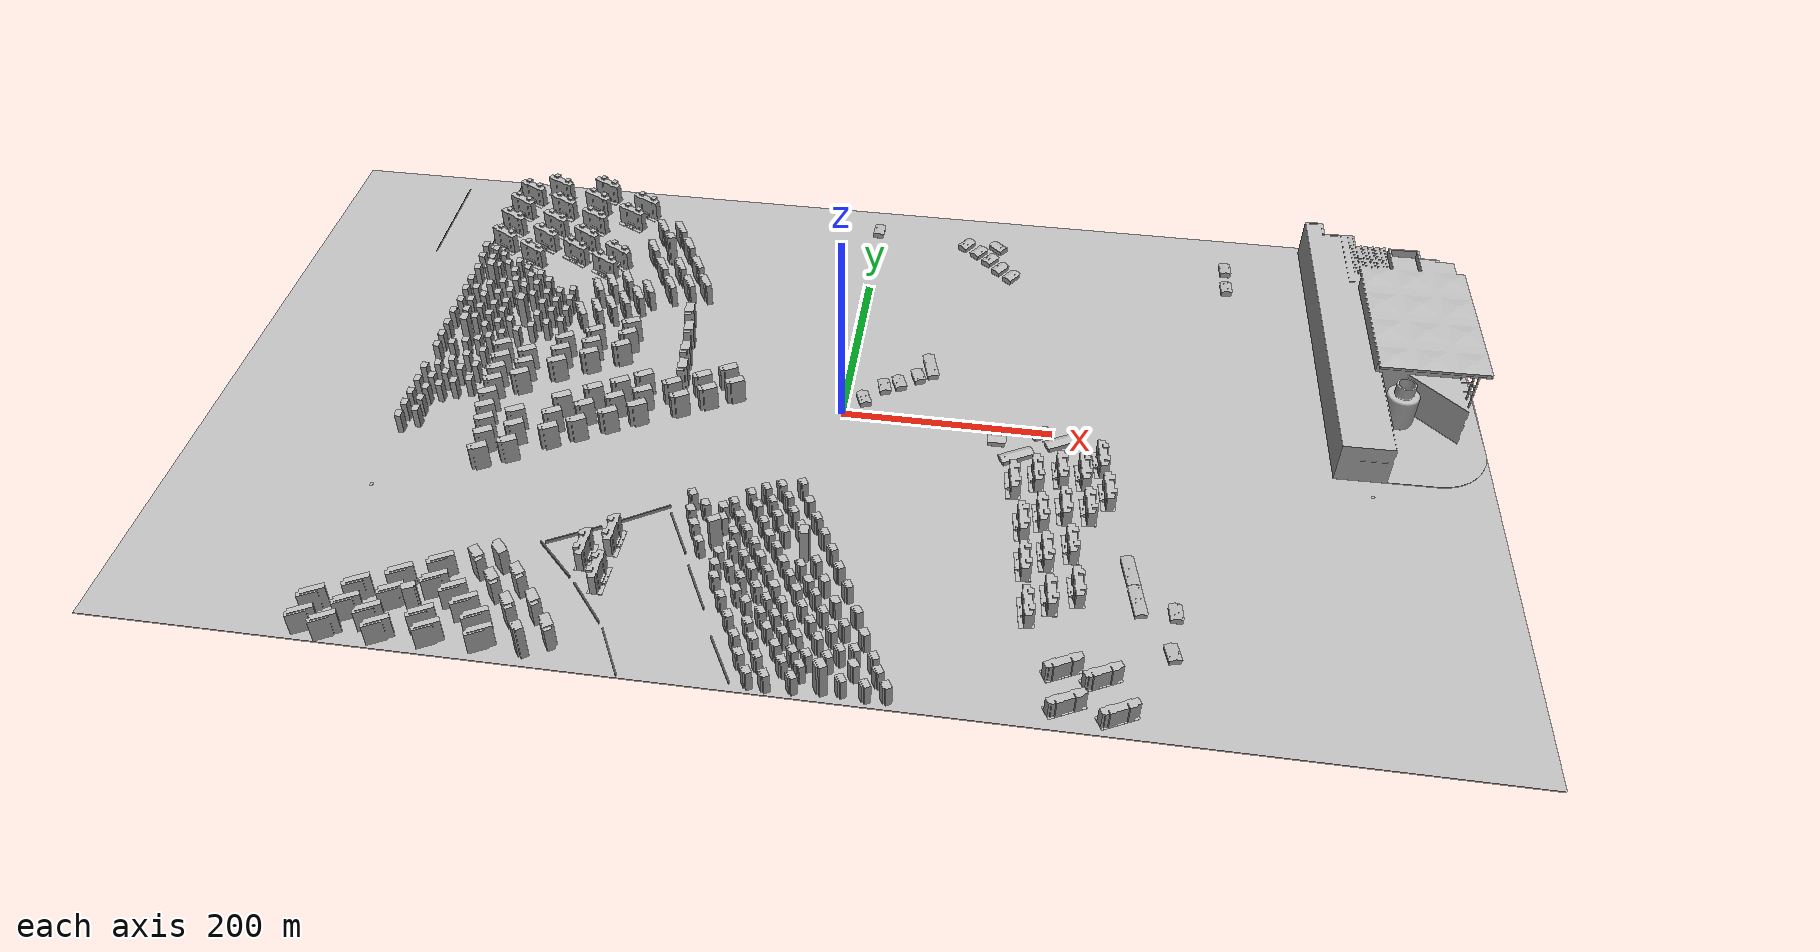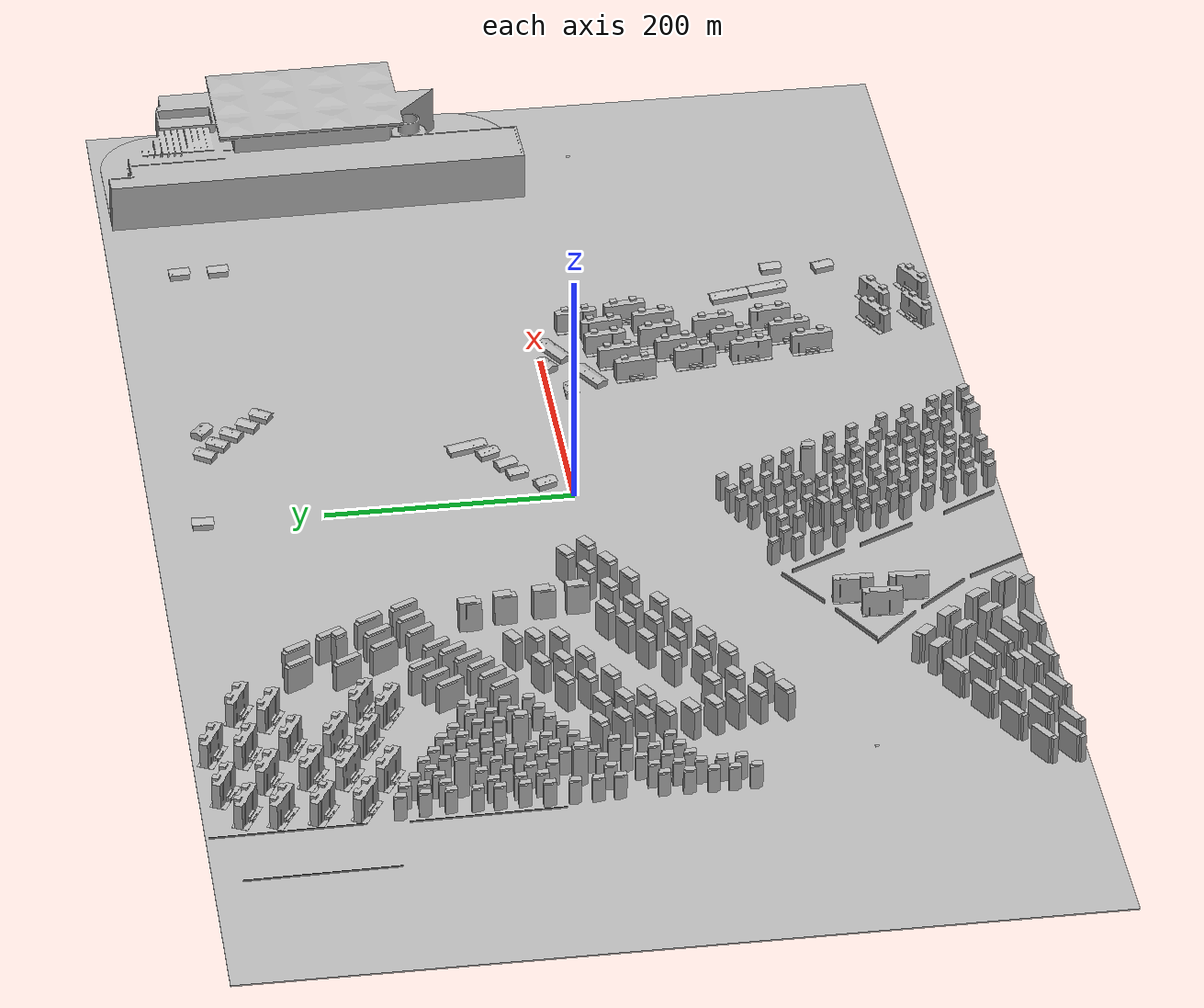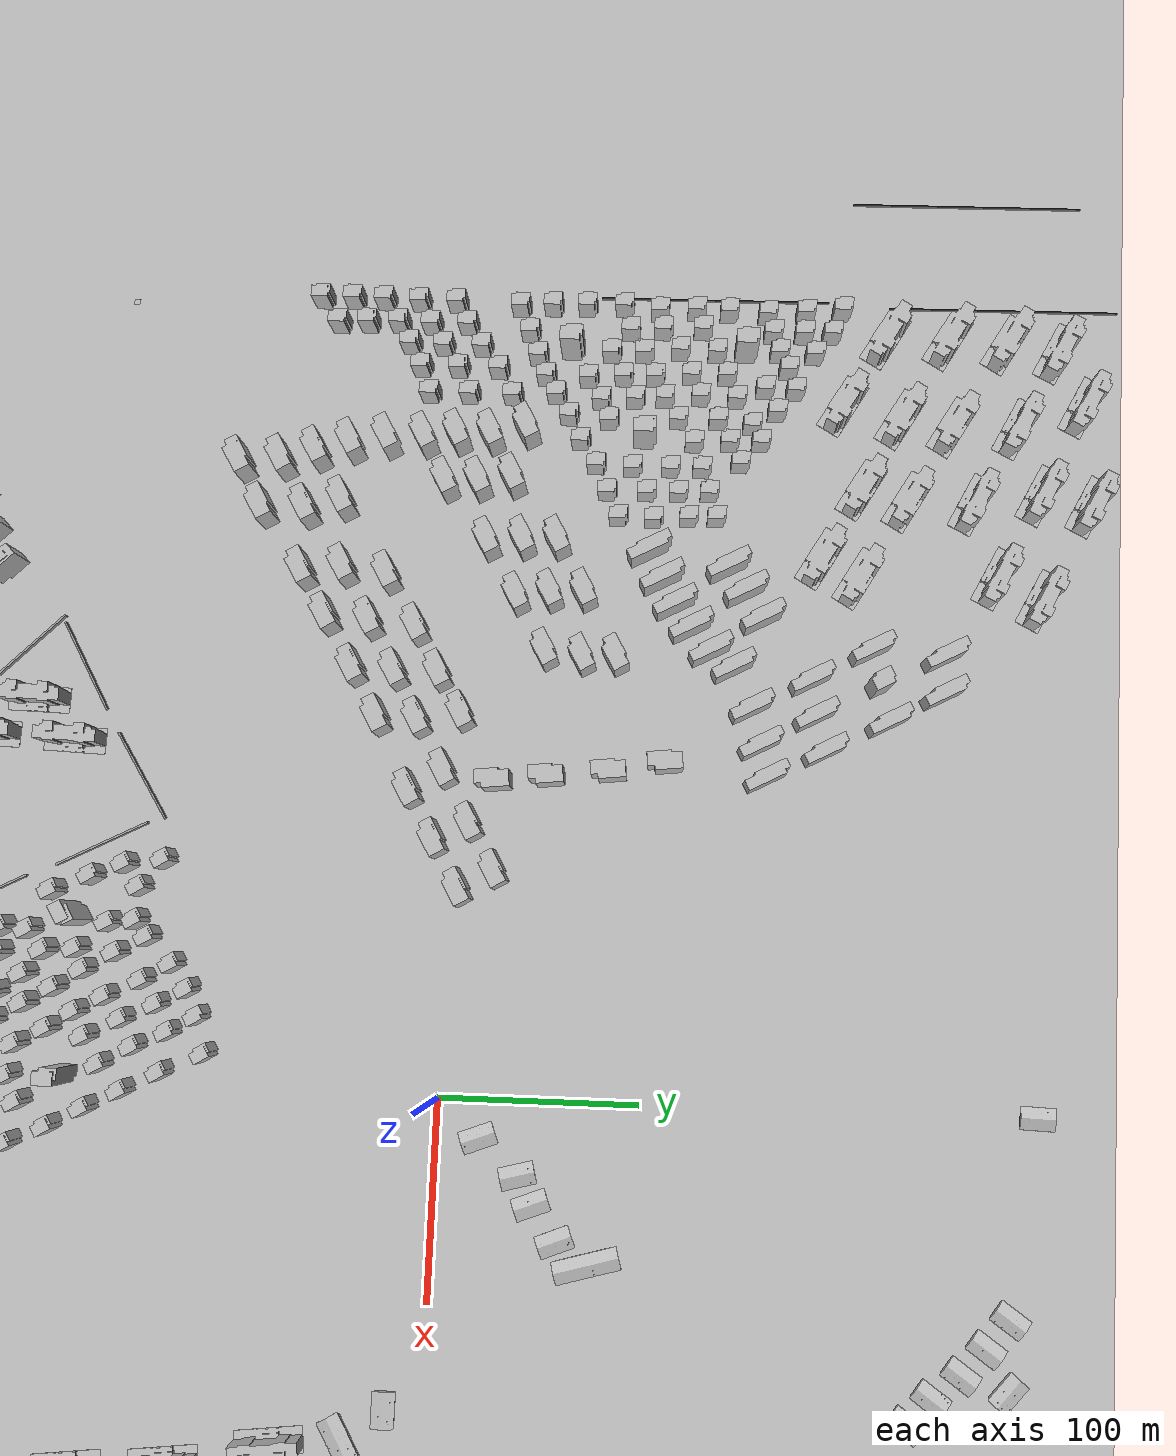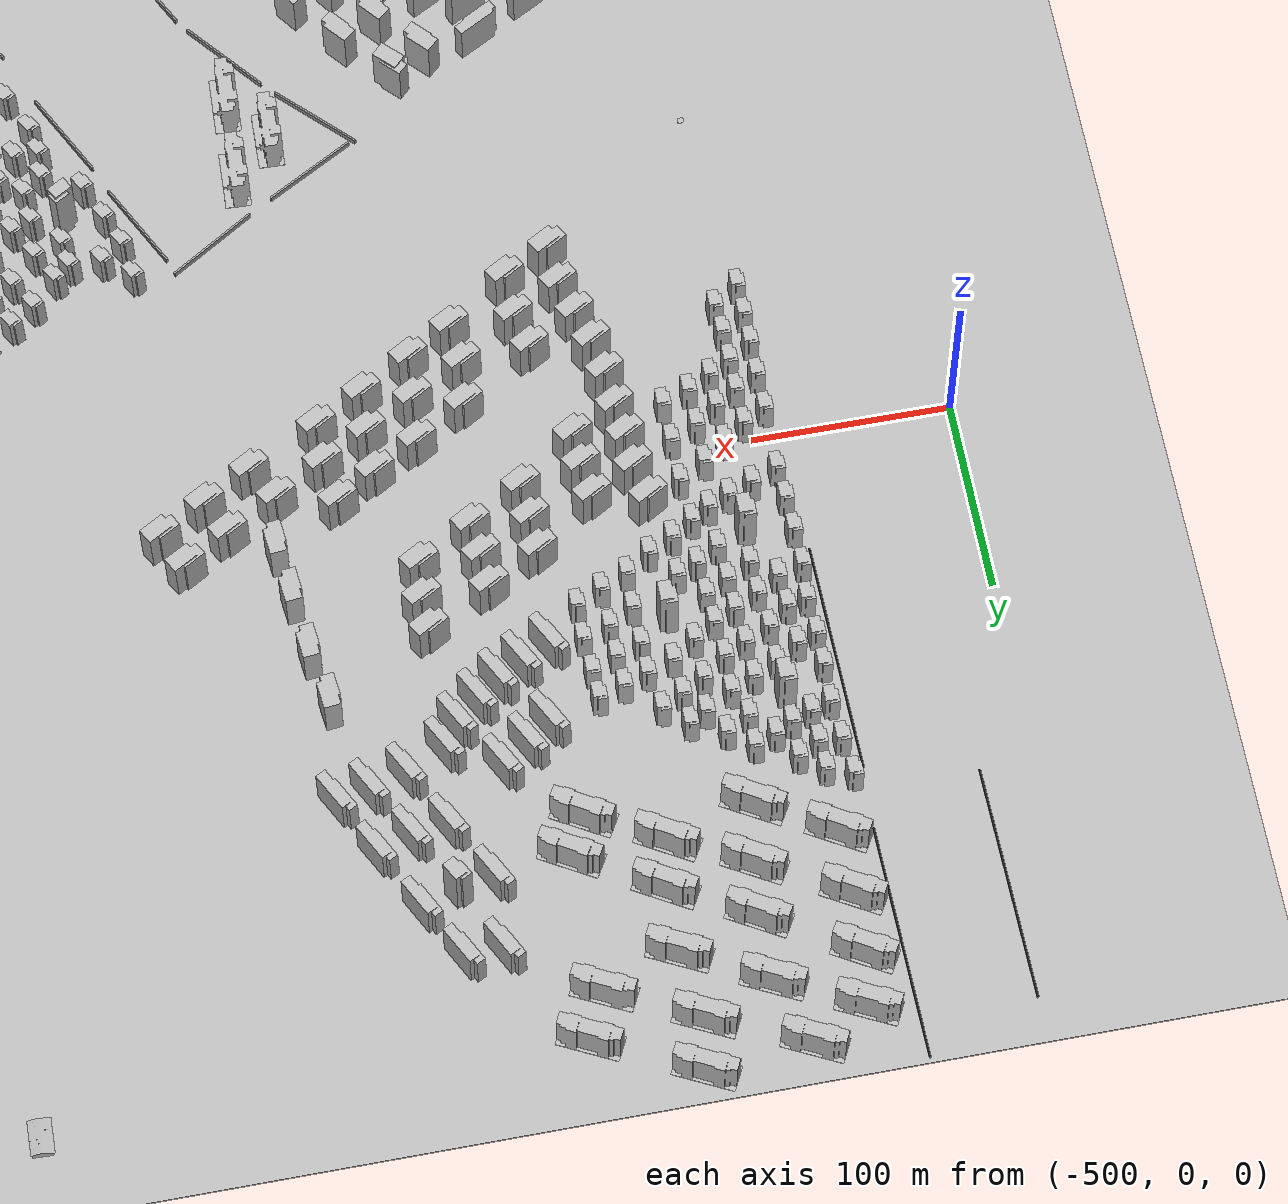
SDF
<sdf version="1.7">
 <world name="default">
  <scene><sky><clouds><speed>12</speed></clouds></sky></scene>
  <light name="sun" type="directional">
   <pose>0 0 300 0 -0 0</pose>
   <diffuse>0.8 0.8 0.8 1</diffuse>
   <specular>0.2 0.2 0.2 1</specular>
   <attenuation>
    <range>1000</range>
    <constant>0.9</constant>
    <linear>0.01</linear>
    <quadratic>0.001</quadratic>
   </attenuation>
   <direction>-0.5 0.1 -0.9</direction>
   <spot><inner_angle>0</inner_angle><outer_angle>0</outer_angle><falloff>0</falloff></spot>
  </light>
  <model name="ground_plane">
   <static>1</static>
   <link name="link">
    <collision name="collision">
     <geometry><mesh><uri>model://ground_plane/scripts/plane.dae</uri><normal>0 0 1</normal></mesh></geometry>
     <surface><friction><ode><mu>100</mu><mu2>50</mu2></ode></friction></surface>
    </collision>
    <visual name="visual">
     <geometry><mesh><uri>model://ground_plane/scripts/plane.dae</uri><normal>0 0 1</normal></mesh></geometry>
     <material>
      <lighting>1</lighting>
      <script><uri>model://ground_plane/scripts/plane.jpg</uri><name>__default__</name></script>
      <shader type="pixel"/>
     </material>
    </visual>
   </link>
  </model>
  <gravity>0 0 -9.8</gravity>
  <magnetic_field>6e-06 2.3e-05 -4.2e-05</magnetic_field>
  <atmosphere type="adiabatic"/>
  <physics type="ode">
   <max_step_size>0.001</max_step_size>
   <real_time_factor>1</real_time_factor>
   <real_time_update_rate>1000</real_time_update_rate>
  </physics>
  <scene><ambient>0.4 0.4 0.4 1</ambient><background>0.7 0.7 0.7 1</background><shadows>1</shadows></scene>
  <spherical_coordinates>
   <surface_model>EARTH_WGS84</surface_model>
   <latitude_deg>0</latitude_deg>
   <longitude_deg>0</longitude_deg>
   <elevation>0</elevation>
   <heading_deg>0</heading_deg>
  </spherical_coordinates>
  <model name="airport">
   <static>1</static>
   <link name="link_0">
    <inertial>
     <mass>1</mass>
     <inertia>
      <ixx>0.166667</ixx>
      <ixy>0</ixy>
      <ixz>0</ixz>
      <iyy>0.166667</iyy>
      <iyz>0</iyz>
      <izz>0.166667</izz>
     </inertia>
    </inertial>
    <pose>4e-06 1e-06 0 0 -0 1.58504</pose>
    <visual name="visual">
     <geometry><mesh><uri>model://airport/scripts/airport.dae</uri><scale>0.6 0.6 0.8</scale></mesh></geometry>
     <material>
      <lighting>1</lighting>
      <script><uri>model://airport/scripts/airporrt.jpg</uri><name>__default__</name></script>
      <shader type="pixel"><normal_map>__default__</normal_map></shader>
     </material>
    </visual>
    <collision name="collision">
     <geometry><mesh><uri>model://airport/scripts/airport.dae</uri><scale>0.6 0.6 0.8</scale></mesh></geometry>
     <surface>
      <friction>
       <ode><mu>1</mu><mu2>1</mu2><fdir1>0 0 0</fdir1><slip1>0</slip1><slip2>0</slip2></ode>
       <torsional>
        <coefficient>1</coefficient>
        <patch_radius>0</patch_radius>
        <surface_radius>0</surface_radius>
        <use_patch_radius>1</use_patch_radius>
        <ode><slip>0</slip></ode>
       </torsional>
      </friction>
      <bounce><restitution_coefficient>0</restitution_coefficient><threshold>1e+06</threshold></bounce>
      <contact>
       <collide_without_contact>0</collide_without_contact>
       <collide_without_contact_bitmask>1</collide_without_contact_bitmask>
       <collide_bitmask>1</collide_bitmask>
       <ode>
        <soft_cfm>0</soft_cfm>
        <soft_erp>0.2</soft_erp>
        <kp>1e+13</kp>
        <kd>1</kd>
        <max_vel>0.01</max_vel>
        <min_depth>0</min_depth>
       </ode>
       <bullet>
        <split_impulse>1</split_impulse>
        <split_impulse_penetration_threshold>-0.01</split_impulse_penetration_threshold>
        <soft_cfm>0</soft_cfm>
        <soft_erp>0.2</soft_erp>
        <kp>1e+13</kp>
        <kd>1</kd>
       </bullet>
      </contact>
     </surface>
    </collision>
   </link>
   <static>0</static>
   <pose>546.583 154.869 1.00781 0 -0 0.00274</pose>
  </model>
  <model name="apartment1_0">
   <static>1</static>
   <link name="link_0">
    <inertial>
     <mass>1</mass>
     <inertia>
      <ixx>0.166667</ixx>
      <ixy>0</ixy>
      <ixz>0</ixz>
      <iyy>0.166667</iyy>
      <iyz>0</iyz>
      <izz>0.166667</izz>
     </inertia>
    </inertial>
    <pose>1e-06 -0 0 0 -0 0</pose>
    <visual name="visual">
     <geometry>
      <mesh><uri>model://apartment1/scripts/apartment1.dae</uri><scale>0.14 0.14 0.175</scale></mesh>
     </geometry>
     <material>
      <lighting>1</lighting>
      <script><uri>model://apartment1/scripts/apartment1.jpg</uri><name>__default__</name></script>
      <shader type="pixel"/>
     </material>
    </visual>
    <collision name="collision">
     <geometry>
      <mesh><uri>model://apartment1/scripts/apartment1.dae</uri><scale>0.14 0.14 0.175</scale></mesh>
     </geometry>
     <surface>
      <friction>
       <ode><mu>1</mu><mu2>1</mu2><fdir1>0 0 0</fdir1><slip1>0</slip1><slip2>0</slip2></ode>
       <torsional>
        <coefficient>1</coefficient>
        <patch_radius>0</patch_radius>
        <surface_radius>0</surface_radius>
        <use_patch_radius>1</use_patch_radius>
        <ode><slip>0</slip></ode>
       </torsional>
      </friction>
      <bounce><restitution_coefficient>0</restitution_coefficient><threshold>1e+06</threshold></bounce>
      <contact>
       <collide_without_contact>0</collide_without_contact>
       <collide_without_contact_bitmask>1</collide_without_contact_bitmask>
       <collide_bitmask>1</collide_bitmask>
       <ode>
        <soft_cfm>0</soft_cfm>
        <soft_erp>0.2</soft_erp>
        <kp>1e+13</kp>
        <kd>1</kd>
        <max_vel>0.01</max_vel>
        <min_depth>0</min_depth>
       </ode>
       <bullet>
        <split_impulse>1</split_impulse>
        <split_impulse_penetration_threshold>-0.01</split_impulse_penetration_threshold>
        <soft_cfm>0</soft_cfm>
        <soft_erp>0.2</soft_erp>
        <kp>1e+13</kp>
        <kd>1</kd>
       </bullet>
      </contact>
     </surface>
    </collision>
   </link>
   <static>0</static>
   <pose>-407.043 94.3264 0 0 -0 0</pose>
  </model>
  <model name="apartment1_0_clone">
   <static>1</static>
   <link name="link_0">
    <inertial>
     <mass>1</mass>
     <inertia>
      <ixx>0.166667</ixx>
      <ixy>0</ixy>
      <ixz>0</ixz>
      <iyy>0.166667</iyy>
      <iyz>0</iyz>
      <izz>0.166667</izz>
     </inertia>
    </inertial>
    <pose>1e-06 -0 0 0 -0 0</pose>
    <visual name="visual">
     <geometry>
      <mesh><uri>model://apartment1/scripts/apartment1.dae</uri><scale>0.14 0.14 0.175</scale></mesh>
     </geometry>
     <material>
      <lighting>1</lighting>
      <script><uri>model://apartment1/scripts/apartment1.jpg</uri><name>__default__</name></script>
      <shader type="pixel"/>
     </material>
    </visual>
    <collision name="collision">
     <geometry>
      <mesh><uri>model://apartment1/scripts/apartment1.dae</uri><scale>0.14 0.14 0.175</scale></mesh>
     </geometry>
     <surface>
      <friction>
       <ode><mu>1</mu><mu2>1</mu2><fdir1>0 0 0</fdir1><slip1>0</slip1><slip2>0</slip2></ode>
       <torsional>
        <coefficient>1</coefficient>
        <patch_radius>0</patch_radius>
        <surface_radius>0</surface_radius>
        <use_patch_radius>1</use_patch_radius>
        <ode><slip>0</slip></ode>
       </torsional>
      </friction>
      <bounce><restitution_coefficient>0</restitution_coefficient><threshold>1e+06</threshold></bounce>
      <contact>
       <collide_without_contact>0</collide_without_contact>
       <collide_without_contact_bitmask>1</collide_without_contact_bitmask>
       <collide_bitmask>1</collide_bitmask>
       <ode>
        <soft_cfm>0</soft_cfm>
        <soft_erp>0.2</soft_erp>
        <kp>1e+13</kp>
        <kd>1</kd>
        <max_vel>0.01</max_vel>
        <min_depth>0</min_depth>
       </ode>
       <bullet>
        <split_impulse>1</split_impulse>
        <split_impulse_penetration_threshold>-0.01</split_impulse_penetration_threshold>
        <soft_cfm>0</soft_cfm>
        <soft_erp>0.2</soft_erp>
        <kp>1e+13</kp>
        <kd>1</kd>
       </bullet>
      </contact>
     </surface>
    </collision>
   </link>
   <static>0</static>
   <pose>-408.706 75.8334 0 0 -0 0</pose>
  </model>
  <model name="apartment1_0_clone_0">
   <static>1</static>
   <link name="link_0">
    <inertial>
     <mass>1</mass>
     <inertia>
      <ixx>0.166667</ixx>
      <ixy>0</ixy>
      <ixz>0</ixz>
      <iyy>0.166667</iyy>
      <iyz>0</iyz>
      <izz>0.166667</izz>
     </inertia>
    </inertial>
    <pose>1e-06 -0 0 0 -0 0</pose>
    <visual name="visual">
     <geometry>
      <mesh><uri>model://apartment1/scripts/apartment1.dae</uri><scale>0.14 0.14 0.175</scale></mesh>
     </geometry>
     <material>
      <lighting>1</lighting>
      <script><uri>model://apartment1/scripts/apartment1.jpg</uri><name>__default__</name></script>
      <shader type="pixel"/>
     </material>
    </visual>
    <collision name="collision">
     <geometry>
      <mesh><uri>model://apartment1/scripts/apartment1.dae</uri><scale>0.14 0.14 0.175</scale></mesh>
     </geometry>
     <surface>
      <friction>
       <ode><mu>1</mu><mu2>1</mu2><fdir1>0 0 0</fdir1><slip1>0</slip1><slip2>0</slip2></ode>
       <torsional>
        <coefficient>1</coefficient>
        <patch_radius>0</patch_radius>
        <surface_radius>0</surface_radius>
        <use_patch_radius>1</use_patch_radius>
        <ode><slip>0</slip></ode>
       </torsional>
      </friction>
      <bounce><restitution_coefficient>0</restitution_coefficient><threshold>1e+06</threshold></bounce>
      <contact>
       <collide_without_contact>0</collide_without_contact>
       <collide_without_contact_bitmask>1</collide_without_contact_bitmask>
       <collide_bitmask>1</collide_bitmask>
       <ode>
        <soft_cfm>0</soft_cfm>
        <soft_erp>0.2</soft_erp>
        <kp>1e+13</kp>
        <kd>1</kd>
        <max_vel>0.01</max_vel>
        <min_depth>0</min_depth>
       </ode>
       <bullet>
        <split_impulse>1</split_impulse>
        <split_impulse_penetration_threshold>-0.01</split_impulse_penetration_threshold>
        <soft_cfm>0</soft_cfm>
        <soft_erp>0.2</soft_erp>
        <kp>1e+13</kp>
        <kd>1</kd>
       </bullet>
      </contact>
     </surface>
    </collision>
   </link>
   <static>0</static>
   <pose>-408.281 56.4981 0 0 -0 0</pose>
  </model>
  <model name="apartment1_0_clone_1">
   <static>1</static>
   <link name="link_0">
    <inertial>
     <mass>1</mass>
     <inertia>
      <ixx>0.166667</ixx>
      <ixy>0</ixy>
      <ixz>0</ixz>
      <iyy>0.166667</iyy>
      <iyz>0</iyz>
      <izz>0.166667</izz>
     </inertia>
    </inertial>
    <pose>1e-06 -0 0 0 -0 0</pose>
    <visual name="visual">
     <geometry>
      <mesh><uri>model://apartment1/scripts/apartment1.dae</uri><scale>0.14 0.14 0.175</scale></mesh>
     </geometry>
     <material>
      <lighting>1</lighting>
      <script><uri>model://apartment1/scripts/apartment1.jpg</uri><name>__default__</name></script>
      <shader type="pixel"/>
     </material>
    </visual>
    <collision name="collision">
     <geometry>
      <mesh><uri>model://apartment1/scripts/apartment1.dae</uri><scale>0.14 0.14 0.175</scale></mesh>
     </geometry>
     <surface>
      <friction>
       <ode><mu>1</mu><mu2>1</mu2><fdir1>0 0 0</fdir1><slip1>0</slip1><slip2>0</slip2></ode>
       <torsional>
        <coefficient>1</coefficient>
        <patch_radius>0</patch_radius>
        <surface_radius>0</surface_radius>
        <use_patch_radius>1</use_patch_radius>
        <ode><slip>0</slip></ode>
       </torsional>
      </friction>
      <bounce><restitution_coefficient>0</restitution_coefficient><threshold>1e+06</threshold></bounce>
      <contact>
       <collide_without_contact>0</collide_without_contact>
       <collide_without_contact_bitmask>1</collide_without_contact_bitmask>
       <collide_bitmask>1</collide_bitmask>
       <ode>
        <soft_cfm>0</soft_cfm>
        <soft_erp>0.2</soft_erp>
        <kp>1e+13</kp>
        <kd>1</kd>
        <max_vel>0.01</max_vel>
        <min_depth>0</min_depth>
       </ode>
       <bullet>
        <split_impulse>1</split_impulse>
        <split_impulse_penetration_threshold>-0.01</split_impulse_penetration_threshold>
        <soft_cfm>0</soft_cfm>
        <soft_erp>0.2</soft_erp>
        <kp>1e+13</kp>
        <kd>1</kd>
       </bullet>
      </contact>
     </surface>
    </collision>
   </link>
   <static>0</static>
   <pose>-407.724 38.7538 0 0 -0 0</pose>
  </model>
  <model name="apartment1_0_clone_2">
   <static>1</static>
   <link name="link_0">
    <inertial>
     <mass>1</mass>
     <inertia>
      <ixx>0.166667</ixx>
      <ixy>0</ixy>
      <ixz>0</ixz>
      <iyy>0.166667</iyy>
      <iyz>0</iyz>
      <izz>0.166667</izz>
     </inertia>
    </inertial>
    <pose>1e-06 -0 0 0 -0 0</pose>
    <visual name="visual">
     <geometry>
      <mesh><uri>model://apartment1/scripts/apartment1.dae</uri><scale>0.14 0.14 0.175</scale></mesh>
     </geometry>
     <material>
      <lighting>1</lighting>
      <script><uri>model://apartment1/scripts/apartment1.jpg</uri><name>__default__</name></script>
      <shader type="pixel"/>
     </material>
    </visual>
    <collision name="collision">
     <geometry>
      <mesh><uri>model://apartment1/scripts/apartment1.dae</uri><scale>0.14 0.14 0.175</scale></mesh>
     </geometry>
     <surface>
      <friction>
       <ode><mu>1</mu><mu2>1</mu2><fdir1>0 0 0</fdir1><slip1>0</slip1><slip2>0</slip2></ode>
       <torsional>
        <coefficient>1</coefficient>
        <patch_radius>0</patch_radius>
        <surface_radius>0</surface_radius>
        <use_patch_radius>1</use_patch_radius>
        <ode><slip>0</slip></ode>
       </torsional>
      </friction>
      <bounce><restitution_coefficient>0</restitution_coefficient><threshold>1e+06</threshold></bounce>
      <contact>
       <collide_without_contact>0</collide_without_contact>
       <collide_without_contact_bitmask>1</collide_without_contact_bitmask>
       <collide_bitmask>1</collide_bitmask>
       <ode>
        <soft_cfm>0</soft_cfm>
        <soft_erp>0.2</soft_erp>
        <kp>1e+13</kp>
        <kd>1</kd>
        <max_vel>0.01</max_vel>
        <min_depth>0</min_depth>
       </ode>
       <bullet>
        <split_impulse>1</split_impulse>
        <split_impulse_penetration_threshold>-0.01</split_impulse_penetration_threshold>
        <soft_cfm>0</soft_cfm>
        <soft_erp>0.2</soft_erp>
        <kp>1e+13</kp>
        <kd>1</kd>
       </bullet>
      </contact>
     </surface>
    </collision>
   </link>
   <static>0</static>
   <pose>-406.714 21.8922 0 0 -0 0</pose>
  </model>
  <model name="apartment1_0_clone_3">
   <static>1</static>
   <link name="link_0">
    <inertial>
     <mass>1</mass>
     <inertia>
      <ixx>0.166667</ixx>
      <ixy>0</ixy>
      <ixz>0</ixz>
      <iyy>0.166667</iyy>
      <iyz>0</iyz>
      <izz>0.166667</izz>
     </inertia>
    </inertial>
    <pose>1e-06 -0 0 0 -0 0</pose>
    <visual name="visual">
     <geometry>
      <mesh><uri>model://apartment1/scripts/apartment1.dae</uri><scale>0.14 0.14 0.175</scale></mesh>
     </geometry>
     <material>
      <lighting>1</lighting>
      <script><uri>model://apartment1/scripts/apartment1.jpg</uri><name>__default__</name></script>
      <shader type="pixel"/>
     </material>
    </visual>
    <collision name="collision">
     <geometry>
      <mesh><uri>model://apartment1/scripts/apartment1.dae</uri><scale>0.14 0.14 0.175</scale></mesh>
     </geometry>
     <surface>
      <friction>
       <ode><mu>1</mu><mu2>1</mu2><fdir1>0 0 0</fdir1><slip1>0</slip1><slip2>0</slip2></ode>
       <torsional>
        <coefficient>1</coefficient>
        <patch_radius>0</patch_radius>
        <surface_radius>0</surface_radius>
        <use_patch_radius>1</use_patch_radius>
        <ode><slip>0</slip></ode>
       </torsional>
      </friction>
      <bounce><restitution_coefficient>0</restitution_coefficient><threshold>1e+06</threshold></bounce>
      <contact>
       <collide_without_contact>0</collide_without_contact>
       <collide_without_contact_bitmask>1</collide_without_contact_bitmask>
       <collide_bitmask>1</collide_bitmask>
       <ode>
        <soft_cfm>0</soft_cfm>
        <soft_erp>0.2</soft_erp>
        <kp>1e+13</kp>
        <kd>1</kd>
        <max_vel>0.01</max_vel>
        <min_depth>0</min_depth>
       </ode>
       <bullet>
        <split_impulse>1</split_impulse>
        <split_impulse_penetration_threshold>-0.01</split_impulse_penetration_threshold>
        <soft_cfm>0</soft_cfm>
        <soft_erp>0.2</soft_erp>
        <kp>1e+13</kp>
        <kd>1</kd>
       </bullet>
      </contact>
     </surface>
    </collision>
   </link>
   <static>0</static>
   <pose>-407.424 -11.464 0 0 -0 0</pose>
  </model>
  <model name="apartment1_0_clone_4">
   <static>1</static>
   <link name="link_0">
    <inertial>
     <mass>1</mass>
     <inertia>
      <ixx>0.166667</ixx>
      <ixy>0</ixy>
      <ixz>0</ixz>
      <iyy>0.166667</iyy>
      <iyz>0</iyz>
      <izz>0.166667</izz>
     </inertia>
    </inertial>
    <pose>1e-06 -0 0 0 -0 0</pose>
    <visual name="visual">
     <geometry>
      <mesh><uri>model://apartment1/scripts/apartment1.dae</uri><scale>0.14 0.14 0.175</scale></mesh>
     </geometry>
     <material>
      <lighting>1</lighting>
      <script><uri>model://apartment1/scripts/apartment1.jpg</uri><name>__default__</name></script>
      <shader type="pixel"/>
     </material>
    </visual>
    <collision name="collision">
     <geometry>
      <mesh><uri>model://apartment1/scripts/apartment1.dae</uri><scale>0.14 0.14 0.175</scale></mesh>
     </geometry>
     <surface>
      <friction>
       <ode><mu>1</mu><mu2>1</mu2><fdir1>0 0 0</fdir1><slip1>0</slip1><slip2>0</slip2></ode>
       <torsional>
        <coefficient>1</coefficient>
        <patch_radius>0</patch_radius>
        <surface_radius>0</surface_radius>
        <use_patch_radius>1</use_patch_radius>
        <ode><slip>0</slip></ode>
       </torsional>
      </friction>
      <bounce><restitution_coefficient>0</restitution_coefficient><threshold>1e+06</threshold></bounce>
      <contact>
       <collide_without_contact>0</collide_without_contact>
       <collide_without_contact_bitmask>1</collide_without_contact_bitmask>
       <collide_bitmask>1</collide_bitmask>
       <ode>
        <soft_cfm>0</soft_cfm>
        <soft_erp>0.2</soft_erp>
        <kp>1e+13</kp>
        <kd>1</kd>
        <max_vel>0.01</max_vel>
        <min_depth>0</min_depth>
       </ode>
       <bullet>
        <split_impulse>1</split_impulse>
        <split_impulse_penetration_threshold>-0.01</split_impulse_penetration_threshold>
        <soft_cfm>0</soft_cfm>
        <soft_erp>0.2</soft_erp>
        <kp>1e+13</kp>
        <kd>1</kd>
       </bullet>
      </contact>
     </surface>
    </collision>
   </link>
   <static>0</static>
   <pose>-395.709 -5.1567 0 0 -0 0</pose>
  </model>
  <model name="apartment1_0_clone_5">
   <static>1</static>
   <link name="link_0">
    <inertial>
     <mass>1</mass>
     <inertia>
      <ixx>0.166667</ixx>
      <ixy>0</ixy>
      <ixz>0</ixz>
      <iyy>0.166667</iyy>
      <iyz>0</iyz>
      <izz>0.166667</izz>
     </inertia>
    </inertial>
    <pose>1e-06 -0 0 0 -0 0</pose>
    <visual name="visual">
     <geometry>
      <mesh><uri>model://apartment1/scripts/apartment1.dae</uri><scale>0.14 0.14 0.175</scale></mesh>
     </geometry>
     <material>
      <lighting>1</lighting>
      <script><uri>model://apartment1/scripts/apartment1.jpg</uri><name>__default__</name></script>
      <shader type="pixel"/>
     </material>
    </visual>
    <collision name="collision">
     <geometry>
      <mesh><uri>model://apartment1/scripts/apartment1.dae</uri><scale>0.14 0.14 0.175</scale></mesh>
     </geometry>
     <surface>
      <friction>
       <ode><mu>1</mu><mu2>1</mu2><fdir1>0 0 0</fdir1><slip1>0</slip1><slip2>0</slip2></ode>
       <torsional>
        <coefficient>1</coefficient>
        <patch_radius>0</patch_radius>
        <surface_radius>0</surface_radius>
        <use_patch_radius>1</use_patch_radius>
        <ode><slip>0</slip></ode>
       </torsional>
      </friction>
      <bounce><restitution_coefficient>0</restitution_coefficient><threshold>1e+06</threshold></bounce>
      <contact>
       <collide_without_contact>0</collide_without_contact>
       <collide_without_contact_bitmask>1</collide_without_contact_bitmask>
       <collide_bitmask>1</collide_bitmask>
       <ode>
        <soft_cfm>0</soft_cfm>
        <soft_erp>0.2</soft_erp>
        <kp>1e+13</kp>
        <kd>1</kd>
        <max_vel>0.01</max_vel>
        <min_depth>0</min_depth>
       </ode>
       <bullet>
        <split_impulse>1</split_impulse>
        <split_impulse_penetration_threshold>-0.01</split_impulse_penetration_threshold>
        <soft_cfm>0</soft_cfm>
        <soft_erp>0.2</soft_erp>
        <kp>1e+13</kp>
        <kd>1</kd>
       </bullet>
      </contact>
     </surface>
    </collision>
   </link>
   <static>0</static>
   <pose>-384.289 2.77257 0 0 -0 0</pose>
  </model>
  <model name="apartment1_0_clone_6">
   <static>1</static>
   <link name="link_0">
    <inertial>
     <mass>1</mass>
     <inertia>
      <ixx>0.166667</ixx>
      <ixy>0</ixy>
      <ixz>0</ixz>
      <iyy>0.166667</iyy>
      <iyz>0</iyz>
      <izz>0.166667</izz>
     </inertia>
    </inertial>
    <pose>1e-06 -0 0 0 -0 0</pose>
    <visual name="visual">
     <geometry>
      <mesh><uri>model://apartment1/scripts/apartment1.dae</uri><scale>0.14 0.14 0.175</scale></mesh>
     </geometry>
     <material>
      <lighting>1</lighting>
      <script><uri>model://apartment1/scripts/apartment1.jpg</uri><name>__default__</name></script>
      <shader type="pixel"/>
     </material>
    </visual>
    <collision name="collision">
     <geometry>
      <mesh><uri>model://apartment1/scripts/apartment1.dae</uri><scale>0.14 0.14 0.175</scale></mesh>
     </geometry>
     <surface>
      <friction>
       <ode><mu>1</mu><mu2>1</mu2><fdir1>0 0 0</fdir1><slip1>0</slip1><slip2>0</slip2></ode>
       <torsional>
        <coefficient>1</coefficient>
        <patch_radius>0</patch_radius>
        <surface_radius>0</surface_radius>
        <use_patch_radius>1</use_patch_radius>
        <ode><slip>0</slip></ode>
       </torsional>
      </friction>
      <bounce><restitution_coefficient>0</restitution_coefficient><threshold>1e+06</threshold></bounce>
      <contact>
       <collide_without_contact>0</collide_without_contact>
       <collide_without_contact_bitmask>1</collide_without_contact_bitmask>
       <collide_bitmask>1</collide_bitmask>
       <ode>
        <soft_cfm>0</soft_cfm>
        <soft_erp>0.2</soft_erp>
        <kp>1e+13</kp>
        <kd>1</kd>
        <max_vel>0.01</max_vel>
        <min_depth>0</min_depth>
       </ode>
       <bullet>
        <split_impulse>1</split_impulse>
        <split_impulse_penetration_threshold>-0.01</split_impulse_penetration_threshold>
        <soft_cfm>0</soft_cfm>
        <soft_erp>0.2</soft_erp>
        <kp>1e+13</kp>
        <kd>1</kd>
       </bullet>
      </contact>
     </surface>
    </collision>
   </link>
   <static>0</static>
   <pose>-372.548 12.0518 0 0 -0 0</pose>
  </model>
  <model name="apartment1_0_clone_7">
   <static>1</static>
   <link name="link_0">
    <inertial>
     <mass>1</mass>
     <inertia>
      <ixx>0.166667</ixx>
      <ixy>0</ixy>
      <ixz>0</ixz>
      <iyy>0.166667</iyy>
      <iyz>0</iyz>
      <izz>0.166667</izz>
     </inertia>
    </inertial>
    <pose>1e-06 -0 0 0 -0 0</pose>
    <visual name="visual">
     <geometry>
      <mesh><uri>model://apartment1/scripts/apartment1.dae</uri><scale>0.14 0.14 0.175</scale></mesh>
     </geometry>
     <material>
      <lighting>1</lighting>
      <script><uri>model://apartment1/scripts/apartment1.jpg</uri><name>__default__</name></script>
      <shader type="pixel"/>
     </material>
    </visual>
    <collision name="collision">
     <geometry>
      <mesh><uri>model://apartment1/scripts/apartment1.dae</uri><scale>0.14 0.14 0.175</scale></mesh>
     </geometry>
     <surface>
      <friction>
       <ode><mu>1</mu><mu2>1</mu2><fdir1>0 0 0</fdir1><slip1>0</slip1><slip2>0</slip2></ode>
       <torsional>
        <coefficient>1</coefficient>
        <patch_radius>0</patch_radius>
        <surface_radius>0</surface_radius>
        <use_patch_radius>1</use_patch_radius>
        <ode><slip>0</slip></ode>
       </torsional>
      </friction>
      <bounce><restitution_coefficient>0</restitution_coefficient><threshold>1e+06</threshold></bounce>
      <contact>
       <collide_without_contact>0</collide_without_contact>
       <collide_without_contact_bitmask>1</collide_without_contact_bitmask>
       <collide_bitmask>1</collide_bitmask>
       <ode>
        <soft_cfm>0</soft_cfm>
        <soft_erp>0.2</soft_erp>
        <kp>1e+13</kp>
        <kd>1</kd>
        <max_vel>0.01</max_vel>
        <min_depth>0</min_depth>
       </ode>
       <bullet>
        <split_impulse>1</split_impulse>
        <split_impulse_penetration_threshold>-0.01</split_impulse_penetration_threshold>
        <soft_cfm>0</soft_cfm>
        <soft_erp>0.2</soft_erp>
        <kp>1e+13</kp>
        <kd>1</kd>
       </bullet>
      </contact>
     </surface>
    </collision>
   </link>
   <static>0</static>
   <pose>-358.658 19.9237 0 0 -0 0</pose>
  </model>
  <model name="apartment1_0_clone_8">
   <static>1</static>
   <link name="link_0">
    <inertial>
     <mass>1</mass>
     <inertia>
      <ixx>0.166667</ixx>
      <ixy>0</ixy>
      <ixz>0</ixz>
      <iyy>0.166667</iyy>
      <iyz>0</iyz>
      <izz>0.166667</izz>
     </inertia>
    </inertial>
    <pose>1e-06 -0 0 0 -0 0</pose>
    <visual name="visual">
     <geometry>
      <mesh><uri>model://apartment1/scripts/apartment1.dae</uri><scale>0.14 0.14 0.175</scale></mesh>
     </geometry>
     <material>
      <lighting>1</lighting>
      <script><uri>model://apartment1/scripts/apartment1.jpg</uri><name>__default__</name></script>
      <shader type="pixel"/>
     </material>
    </visual>
    <collision name="collision">
     <geometry>
      <mesh><uri>model://apartment1/scripts/apartment1.dae</uri><scale>0.14 0.14 0.175</scale></mesh>
     </geometry>
     <surface>
      <friction>
       <ode><mu>1</mu><mu2>1</mu2><fdir1>0 0 0</fdir1><slip1>0</slip1><slip2>0</slip2></ode>
       <torsional>
        <coefficient>1</coefficient>
        <patch_radius>0</patch_radius>
        <surface_radius>0</surface_radius>
        <use_patch_radius>1</use_patch_radius>
        <ode><slip>0</slip></ode>
       </torsional>
      </friction>
      <bounce><restitution_coefficient>0</restitution_coefficient><threshold>1e+06</threshold></bounce>
      <contact>
       <collide_without_contact>0</collide_without_contact>
       <collide_without_contact_bitmask>1</collide_without_contact_bitmask>
       <collide_bitmask>1</collide_bitmask>
       <ode>
        <soft_cfm>0</soft_cfm>
        <soft_erp>0.2</soft_erp>
        <kp>1e+13</kp>
        <kd>1</kd>
        <max_vel>0.01</max_vel>
        <min_depth>0</min_depth>
       </ode>
       <bullet>
        <split_impulse>1</split_impulse>
        <split_impulse_penetration_threshold>-0.01</split_impulse_penetration_threshold>
        <soft_cfm>0</soft_cfm>
        <soft_erp>0.2</soft_erp>
        <kp>1e+13</kp>
        <kd>1</kd>
       </bullet>
      </contact>
     </surface>
    </collision>
   </link>
   <static>0</static>
   <pose>-407.23 -30.696 0 0 -0 0</pose>
  </model>
  <model name="apartment1_0_clone_9">
   <static>1</static>
   <link name="link_0">
    <inertial>
     <mass>1</mass>
     <inertia>
      <ixx>0.166667</ixx>
      <ixy>0</ixy>
      <ixz>0</ixz>
      <iyy>0.166667</iyy>
      <iyz>0</iyz>
      <izz>0.166667</izz>
     </inertia>
    </inertial>
    <pose>1e-06 -0 0 0 -0 0</pose>
    <visual name="visual">
     <geometry>
      <mesh><uri>model://apartment1/scripts/apartment1.dae</uri><scale>0.14 0.14 0.175</scale></mesh>
     </geometry>
     <material>
      <lighting>1</lighting>
      <script><uri>model://apartment1/scripts/apartment1.jpg</uri><name>__default__</name></script>
      <shader type="pixel"/>
     </material>
    </visual>
    <collision name="collision">
     <geometry>
      <mesh><uri>model://apartment1/scripts/apartment1.dae</uri><scale>0.14 0.14 0.175</scale></mesh>
     </geometry>
     <surface>
      <friction>
       <ode><mu>1</mu><mu2>1</mu2><fdir1>0 0 0</fdir1><slip1>0</slip1><slip2>0</slip2></ode>
       <torsional>
        <coefficient>1</coefficient>
        <patch_radius>0</patch_radius>
        <surface_radius>0</surface_radius>
        <use_patch_radius>1</use_patch_radius>
        <ode><slip>0</slip></ode>
       </torsional>
      </friction>
      <bounce><restitution_coefficient>0</restitution_coefficient><threshold>1e+06</threshold></bounce>
      <contact>
       <collide_without_contact>0</collide_without_contact>
       <collide_without_contact_bitmask>1</collide_without_contact_bitmask>
       <collide_bitmask>1</collide_bitmask>
       <ode>
        <soft_cfm>0</soft_cfm>
        <soft_erp>0.2</soft_erp>
        <kp>1e+13</kp>
        <kd>1</kd>
        <max_vel>0.01</max_vel>
        <min_depth>0</min_depth>
       </ode>
       <bullet>
        <split_impulse>1</split_impulse>
        <split_impulse_penetration_threshold>-0.01</split_impulse_penetration_threshold>
        <soft_cfm>0</soft_cfm>
        <soft_erp>0.2</soft_erp>
        <kp>1e+13</kp>
        <kd>1</kd>
       </bullet>
      </contact>
     </surface>
    </collision>
   </link>
   <static>0</static>
   <pose>-407.538 -49.0824 0 0 -0 0</pose>
  </model>
  <model name="apartment1_0_clone_10">
   <static>1</static>
   <link name="link_0">
    <inertial>
     <mass>1</mass>
     <inertia>
      <ixx>0.166667</ixx>
      <ixy>0</ixy>
      <ixz>0</ixz>
      <iyy>0.166667</iyy>
      <iyz>0</iyz>
      <izz>0.166667</izz>
     </inertia>
    </inertial>
    <pose>1e-06 -0 0 0 -0 0</pose>
    <visual name="visual">
     <geometry>
      <mesh><uri>model://apartment1/scripts/apartment1.dae</uri><scale>0.14 0.14 0.175</scale></mesh>
     </geometry>
     <material>
      <lighting>1</lighting>
      <script><uri>model://apartment1/scripts/apartment1.jpg</uri><name>__default__</name></script>
      <shader type="pixel"/>
     </material>
    </visual>
    <collision name="collision">
     <geometry>
      <mesh><uri>model://apartment1/scripts/apartment1.dae</uri><scale>0.14 0.14 0.175</scale></mesh>
     </geometry>
     <surface>
      <friction>
       <ode><mu>1</mu><mu2>1</mu2><fdir1>0 0 0</fdir1><slip1>0</slip1><slip2>0</slip2></ode>
       <torsional>
        <coefficient>1</coefficient>
        <patch_radius>0</patch_radius>
        <surface_radius>0</surface_radius>
        <use_patch_radius>1</use_patch_radius>
        <ode><slip>0</slip></ode>
       </torsional>
      </friction>
      <bounce><restitution_coefficient>0</restitution_coefficient><threshold>1e+06</threshold></bounce>
      <contact>
       <collide_without_contact>0</collide_without_contact>
       <collide_without_contact_bitmask>1</collide_without_contact_bitmask>
       <collide_bitmask>1</collide_bitmask>
       <ode>
        <soft_cfm>0</soft_cfm>
        <soft_erp>0.2</soft_erp>
        <kp>1e+13</kp>
        <kd>1</kd>
        <max_vel>0.01</max_vel>
        <min_depth>0</min_depth>
       </ode>
       <bullet>
        <split_impulse>1</split_impulse>
        <split_impulse_penetration_threshold>-0.01</split_impulse_penetration_threshold>
        <soft_cfm>0</soft_cfm>
        <soft_erp>0.2</soft_erp>
        <kp>1e+13</kp>
        <kd>1</kd>
       </bullet>
      </contact>
     </surface>
    </collision>
   </link>
   <static>0</static>
   <pose>-407.56 -65.1741 0 0 -0 0</pose>
  </model>
  <model name="apartment1_0_clone_11">
   <static>1</static>
   <link name="link_0">
    <inertial>
     <mass>1</mass>
     <inertia>
      <ixx>0.166667</ixx>
      <ixy>0</ixy>
      <ixz>0</ixz>
      <iyy>0.166667</iyy>
      <iyz>0</iyz>
      <izz>0.166667</izz>
     </inertia>
    </inertial>
    <pose>1e-06 -0 0 0 -0 0</pose>
    <visual name="visual">
     <geometry>
      <mesh><uri>model://apartment1/scripts/apartment1.dae</uri><scale>0.14 0.14 0.175</scale></mesh>
     </geometry>
     <material>
      <lighting>1</lighting>
      <script><uri>model://apartment1/scripts/apartment1.jpg</uri><name>__default__</name></script>
      <shader type="pixel"/>
     </material>
    </visual>
    <collision name="collision">
     <geometry>
      <mesh><uri>model://apartment1/scripts/apartment1.dae</uri><scale>0.14 0.14 0.175</scale></mesh>
     </geometry>
     <surface>
      <friction>
       <ode><mu>1</mu><mu2>1</mu2><fdir1>0 0 0</fdir1><slip1>0</slip1><slip2>0</slip2></ode>
       <torsional>
        <coefficient>1</coefficient>
        <patch_radius>0</patch_radius>
        <surface_radius>0</surface_radius>
        <use_patch_radius>1</use_patch_radius>
        <ode><slip>0</slip></ode>
       </torsional>
      </friction>
      <bounce><restitution_coefficient>0</restitution_coefficient><threshold>1e+06</threshold></bounce>
      <contact>
       <collide_without_contact>0</collide_without_contact>
       <collide_without_contact_bitmask>1</collide_without_contact_bitmask>
       <collide_bitmask>1</collide_bitmask>
       <ode>
        <soft_cfm>0</soft_cfm>
        <soft_erp>0.2</soft_erp>
        <kp>1e+13</kp>
        <kd>1</kd>
        <max_vel>0.01</max_vel>
        <min_depth>0</min_depth>
       </ode>
       <bullet>
        <split_impulse>1</split_impulse>
        <split_impulse_penetration_threshold>-0.01</split_impulse_penetration_threshold>
        <soft_cfm>0</soft_cfm>
        <soft_erp>0.2</soft_erp>
        <kp>1e+13</kp>
        <kd>1</kd>
       </bullet>
      </contact>
     </surface>
    </collision>
   </link>
   <static>0</static>
   <pose>-407.346 -81.6289 0 0 -0 0</pose>
  </model>
  <model name="apartment1_0_clone_4_clone">
   <static>1</static>
   <link name="link_0">
    <inertial>
     <mass>1</mass>
     <inertia>
      <ixx>0.166667</ixx>
      <ixy>0</ixy>
      <ixz>0</ixz>
      <iyy>0.166667</iyy>
      <iyz>0</iyz>
      <izz>0.166667</izz>
     </inertia>
    </inertial>
    <pose>1e-06 -0 0 0 -0 0</pose>
    <visual name="visual">
     <geometry>
      <mesh><uri>model://apartment1/scripts/apartment1.dae</uri><scale>0.14 0.14 0.175</scale></mesh>
     </geometry>
     <material>
      <lighting>1</lighting>
      <script><uri>model://apartment1/scripts/apartment1.jpg</uri><name>__default__</name></script>
      <shader type="pixel"/>
     </material>
    </visual>
    <collision name="collision">
     <geometry>
      <mesh><uri>model://apartment1/scripts/apartment1.dae</uri><scale>0.14 0.14 0.175</scale></mesh>
     </geometry>
     <surface>
      <friction>
       <ode><mu>1</mu><mu2>1</mu2><fdir1>0 0 0</fdir1><slip1>0</slip1><slip2>0</slip2></ode>
       <torsional>
        <coefficient>1</coefficient>
        <patch_radius>0</patch_radius>
        <surface_radius>0</surface_radius>
        <use_patch_radius>1</use_patch_radius>
        <ode><slip>0</slip></ode>
       </torsional>
      </friction>
      <bounce><restitution_coefficient>0</restitution_coefficient><threshold>1e+06</threshold></bounce>
      <contact>
       <collide_without_contact>0</collide_without_contact>
       <collide_without_contact_bitmask>1</collide_without_contact_bitmask>
       <collide_bitmask>1</collide_bitmask>
       <ode>
        <soft_cfm>0</soft_cfm>
        <soft_erp>0.2</soft_erp>
        <kp>1e+13</kp>
        <kd>1</kd>
        <max_vel>0.01</max_vel>
        <min_depth>0</min_depth>
       </ode>
       <bullet>
        <split_impulse>1</split_impulse>
        <split_impulse_penetration_threshold>-0.01</split_impulse_penetration_threshold>
        <soft_cfm>0</soft_cfm>
        <soft_erp>0.2</soft_erp>
        <kp>1e+13</kp>
        <kd>1</kd>
       </bullet>
      </contact>
     </surface>
    </collision>
   </link>
   <static>0</static>
   <pose>-395.309 -24.1462 0 0 -0 0</pose>
  </model>
  <model name="apartment1_0_clone_4_clone_0">
   <static>1</static>
   <link name="link_0">
    <inertial>
     <mass>1</mass>
     <inertia>
      <ixx>0.166667</ixx>
      <ixy>0</ixy>
      <ixz>0</ixz>
      <iyy>0.166667</iyy>
      <iyz>0</iyz>
      <izz>0.166667</izz>
     </inertia>
    </inertial>
    <pose>1e-06 -0 0 0 -0 0</pose>
    <visual name="visual">
     <geometry>
      <mesh><uri>model://apartment1/scripts/apartment1.dae</uri><scale>0.14 0.14 0.175</scale></mesh>
     </geometry>
     <material>
      <lighting>1</lighting>
      <script><uri>model://apartment1/scripts/apartment1.jpg</uri><name>__default__</name></script>
      <shader type="pixel"/>
     </material>
    </visual>
    <collision name="collision">
     <geometry>
      <mesh><uri>model://apartment1/scripts/apartment1.dae</uri><scale>0.14 0.14 0.175</scale></mesh>
     </geometry>
     <surface>
      <friction>
       <ode><mu>1</mu><mu2>1</mu2><fdir1>0 0 0</fdir1><slip1>0</slip1><slip2>0</slip2></ode>
       <torsional>
        <coefficient>1</coefficient>
        <patch_radius>0</patch_radius>
        <surface_radius>0</surface_radius>
        <use_patch_radius>1</use_patch_radius>
        <ode><slip>0</slip></ode>
       </torsional>
      </friction>
      <bounce><restitution_coefficient>0</restitution_coefficient><threshold>1e+06</threshold></bounce>
      <contact>
       <collide_without_contact>0</collide_without_contact>
       <collide_without_contact_bitmask>1</collide_without_contact_bitmask>
       <collide_bitmask>1</collide_bitmask>
       <ode>
        <soft_cfm>0</soft_cfm>
        <soft_erp>0.2</soft_erp>
        <kp>1e+13</kp>
        <kd>1</kd>
        <max_vel>0.01</max_vel>
        <min_depth>0</min_depth>
       </ode>
       <bullet>
        <split_impulse>1</split_impulse>
        <split_impulse_penetration_threshold>-0.01</split_impulse_penetration_threshold>
        <soft_cfm>0</soft_cfm>
        <soft_erp>0.2</soft_erp>
        <kp>1e+13</kp>
        <kd>1</kd>
       </bullet>
      </contact>
     </surface>
    </collision>
   </link>
   <static>0</static>
   <pose>-384.006 -17.2145 0 0 -0 0</pose>
  </model>
  <model name="apartment1_0_clone_4_clone_1">
   <static>1</static>
   <link name="link_0">
    <inertial>
     <mass>1</mass>
     <inertia>
      <ixx>0.166667</ixx>
      <ixy>0</ixy>
      <ixz>0</ixz>
      <iyy>0.166667</iyy>
      <iyz>0</iyz>
      <izz>0.166667</izz>
     </inertia>
    </inertial>
    <pose>1e-06 -0 0 0 -0 0</pose>
    <visual name="visual">
     <geometry>
      <mesh><uri>model://apartment1/scripts/apartment1.dae</uri><scale>0.14 0.14 0.175</scale></mesh>
     </geometry>
     <material>
      <lighting>1</lighting>
      <script><uri>model://apartment1/scripts/apartment1.jpg</uri><name>__default__</name></script>
      <shader type="pixel"/>
     </material>
    </visual>
    <collision name="collision">
     <geometry>
      <mesh><uri>model://apartment1/scripts/apartment1.dae</uri><scale>0.14 0.14 0.175</scale></mesh>
     </geometry>
     <surface>
      <friction>
       <ode><mu>1</mu><mu2>1</mu2><fdir1>0 0 0</fdir1><slip1>0</slip1><slip2>0</slip2></ode>
       <torsional>
        <coefficient>1</coefficient>
        <patch_radius>0</patch_radius>
        <surface_radius>0</surface_radius>
        <use_patch_radius>1</use_patch_radius>
        <ode><slip>0</slip></ode>
       </torsional>
      </friction>
      <bounce><restitution_coefficient>0</restitution_coefficient><threshold>1e+06</threshold></bounce>
      <contact>
       <collide_without_contact>0</collide_without_contact>
       <collide_without_contact_bitmask>1</collide_without_contact_bitmask>
       <collide_bitmask>1</collide_bitmask>
       <ode>
        <soft_cfm>0</soft_cfm>
        <soft_erp>0.2</soft_erp>
        <kp>1e+13</kp>
        <kd>1</kd>
        <max_vel>0.01</max_vel>
        <min_depth>0</min_depth>
       </ode>
       <bullet>
        <split_impulse>1</split_impulse>
        <split_impulse_penetration_threshold>-0.01</split_impulse_penetration_threshold>
        <soft_cfm>0</soft_cfm>
        <soft_erp>0.2</soft_erp>
        <kp>1e+13</kp>
        <kd>1</kd>
       </bullet>
      </contact>
     </surface>
    </collision>
   </link>
   <static>0</static>
   <pose>-372.442 -8.73774 0 0 -0 0</pose>
  </model>
  <model name="apartment1_0_clone_4_clone_2">
   <static>1</static>
   <link name="link_0">
    <inertial>
     <mass>1</mass>
     <inertia>
      <ixx>0.166667</ixx>
      <ixy>0</ixy>
      <ixz>0</ixz>
      <iyy>0.166667</iyy>
      <iyz>0</iyz>
      <izz>0.166667</izz>
     </inertia>
    </inertial>
    <pose>1e-06 -0 0 0 -0 0</pose>
    <visual name="visual">
     <geometry>
      <mesh><uri>model://apartment1/scripts/apartment1.dae</uri><scale>0.14 0.14 0.175</scale></mesh>
     </geometry>
     <material>
      <lighting>1</lighting>
      <script><uri>model://apartment1/scripts/apartment1.jpg</uri><name>__default__</name></script>
      <shader type="pixel"/>
     </material>
    </visual>
    <collision name="collision">
     <geometry>
      <mesh><uri>model://apartment1/scripts/apartment1.dae</uri><scale>0.14 0.14 0.175</scale></mesh>
     </geometry>
     <surface>
      <friction>
       <ode><mu>1</mu><mu2>1</mu2><fdir1>0 0 0</fdir1><slip1>0</slip1><slip2>0</slip2></ode>
       <torsional>
        <coefficient>1</coefficient>
        <patch_radius>0</patch_radius>
        <surface_radius>0</surface_radius>
        <use_patch_radius>1</use_patch_radius>
        <ode><slip>0</slip></ode>
       </torsional>
      </friction>
      <bounce><restitution_coefficient>0</restitution_coefficient><threshold>1e+06</threshold></bounce>
      <contact>
       <collide_without_contact>0</collide_without_contact>
       <collide_without_contact_bitmask>1</collide_without_contact_bitmask>
       <collide_bitmask>1</collide_bitmask>
       <ode>
        <soft_cfm>0</soft_cfm>
        <soft_erp>0.2</soft_erp>
        <kp>1e+13</kp>
        <kd>1</kd>
        <max_vel>0.01</max_vel>
        <min_depth>0</min_depth>
       </ode>
       <bullet>
        <split_impulse>1</split_impulse>
        <split_impulse_penetration_threshold>-0.01</split_impulse_penetration_threshold>
        <soft_cfm>0</soft_cfm>
        <soft_erp>0.2</soft_erp>
        <kp>1e+13</kp>
        <kd>1</kd>
       </bullet>
      </contact>
     </surface>
    </collision>
   </link>
   <static>0</static>
   <pose>-358.708 -2.52428 0 0 -0 0</pose>
  </model>
  <model name="apartment1_0_clone_4_clone_3">
   <static>1</static>
   <link name="link_0">
    <inertial>
     <mass>1</mass>
     <inertia>
      <ixx>0.166667</ixx>
      <ixy>0</ixy>
      <ixz>0</ixz>
      <iyy>0.166667</iyy>
      <iyz>0</iyz>
      <izz>0.166667</izz>
     </inertia>
    </inertial>
    <pose>1e-06 -0 0 0 -0 0</pose>
    <visual name="visual">
     <geometry>
      <mesh><uri>model://apartment1/scripts/apartment1.dae</uri><scale>0.14 0.14 0.175</scale></mesh>
     </geometry>
     <material>
      <lighting>1</lighting>
      <script><uri>model://apartment1/scripts/apartment1.jpg</uri><name>__default__</name></script>
      <shader type="pixel"/>
     </material>
    </visual>
    <collision name="collision">
     <geometry>
      <mesh><uri>model://apartment1/scripts/apartment1.dae</uri><scale>0.14 0.14 0.175</scale></mesh>
     </geometry>
     <surface>
      <friction>
       <ode><mu>1</mu><mu2>1</mu2><fdir1>0 0 0</fdir1><slip1>0</slip1><slip2>0</slip2></ode>
       <torsional>
        <coefficient>1</coefficient>
        <patch_radius>0</patch_radius>
        <surface_radius>0</surface_radius>
        <use_patch_radius>1</use_patch_radius>
        <ode><slip>0</slip></ode>
       </torsional>
      </friction>
      <bounce><restitution_coefficient>0</restitution_coefficient><threshold>1e+06</threshold></bounce>
      <contact>
       <collide_without_contact>0</collide_without_contact>
       <collide_without_contact_bitmask>1</collide_without_contact_bitmask>
       <collide_bitmask>1</collide_bitmask>
       <ode>
        <soft_cfm>0</soft_cfm>
        <soft_erp>0.2</soft_erp>
        <kp>1e+13</kp>
        <kd>1</kd>
        <max_vel>0.01</max_vel>
        <min_depth>0</min_depth>
       </ode>
       <bullet>
        <split_impulse>1</split_impulse>
        <split_impulse_penetration_threshold>-0.01</split_impulse_penetration_threshold>
        <soft_cfm>0</soft_cfm>
        <soft_erp>0.2</soft_erp>
        <kp>1e+13</kp>
        <kd>1</kd>
       </bullet>
      </contact>
     </surface>
    </collision>
   </link>
   <static>0</static>
   <pose>-395.426 -40.9327 0 0 -0 0</pose>
  </model>
  <model name="apartment1_0_clone_4_clone_4">
   <static>1</static>
   <link name="link_0">
    <inertial>
     <mass>1</mass>
     <inertia>
      <ixx>0.166667</ixx>
      <ixy>0</ixy>
      <ixz>0</ixz>
      <iyy>0.166667</iyy>
      <iyz>0</iyz>
      <izz>0.166667</izz>
     </inertia>
    </inertial>
    <pose>1e-06 -0 0 0 -0 0</pose>
    <visual name="visual">
     <geometry>
      <mesh><uri>model://apartment1/scripts/apartment1.dae</uri><scale>0.14 0.14 0.175</scale></mesh>
     </geometry>
     <material>
      <lighting>1</lighting>
      <script><uri>model://apartment1/scripts/apartment1.jpg</uri><name>__default__</name></script>
      <shader type="pixel"/>
     </material>
    </visual>
    <collision name="collision">
     <geometry>
      <mesh><uri>model://apartment1/scripts/apartment1.dae</uri><scale>0.14 0.14 0.175</scale></mesh>
     </geometry>
     <surface>
      <friction>
       <ode><mu>1</mu><mu2>1</mu2><fdir1>0 0 0</fdir1><slip1>0</slip1><slip2>0</slip2></ode>
       <torsional>
        <coefficient>1</coefficient>
        <patch_radius>0</patch_radius>
        <surface_radius>0</surface_radius>
        <use_patch_radius>1</use_patch_radius>
        <ode><slip>0</slip></ode>
       </torsional>
      </friction>
      <bounce><restitution_coefficient>0</restitution_coefficient><threshold>1e+06</threshold></bounce>
      <contact>
       <collide_without_contact>0</collide_without_contact>
       <collide_without_contact_bitmask>1</collide_without_contact_bitmask>
       <collide_bitmask>1</collide_bitmask>
       <ode>
        <soft_cfm>0</soft_cfm>
        <soft_erp>0.2</soft_erp>
        <kp>1e+13</kp>
        <kd>1</kd>
        <max_vel>0.01</max_vel>
        <min_depth>0</min_depth>
       </ode>
       <bullet>
        <split_impulse>1</split_impulse>
        <split_impulse_penetration_threshold>-0.01</split_impulse_penetration_threshold>
        <soft_cfm>0</soft_cfm>
        <soft_erp>0.2</soft_erp>
        <kp>1e+13</kp>
        <kd>1</kd>
       </bullet>
      </contact>
     </surface>
    </collision>
   </link>
   <static>0</static>
   <pose>-384.344 -34.5261 0 0 -0 0</pose>
  </model>
  <model name="apartment1_0_clone_4_clone_5">
   <static>1</static>
   <link name="link_0">
    <inertial>
     <mass>1</mass>
     <inertia>
      <ixx>0.166667</ixx>
      <ixy>0</ixy>
      <ixz>0</ixz>
      <iyy>0.166667</iyy>
      <iyz>0</iyz>
      <izz>0.166667</izz>
     </inertia>
    </inertial>
    <pose>1e-06 -0 0 0 -0 0</pose>
    <visual name="visual">
     <geometry>
      <mesh><uri>model://apartment1/scripts/apartment1.dae</uri><scale>0.14 0.14 0.175</scale></mesh>
     </geometry>
     <material>
      <lighting>1</lighting>
      <script><uri>model://apartment1/scripts/apartment1.jpg</uri><name>__default__</name></script>
      <shader type="pixel"/>
     </material>
    </visual>
    <collision name="collision">
     <geometry>
      <mesh><uri>model://apartment1/scripts/apartment1.dae</uri><scale>0.14 0.14 0.175</scale></mesh>
     </geometry>
     <surface>
      <friction>
       <ode><mu>1</mu><mu2>1</mu2><fdir1>0 0 0</fdir1><slip1>0</slip1><slip2>0</slip2></ode>
       <torsional>
        <coefficient>1</coefficient>
        <patch_radius>0</patch_radius>
        <surface_radius>0</surface_radius>
        <use_patch_radius>1</use_patch_radius>
        <ode><slip>0</slip></ode>
       </torsional>
      </friction>
      <bounce><restitution_coefficient>0</restitution_coefficient><threshold>1e+06</threshold></bounce>
      <contact>
       <collide_without_contact>0</collide_without_contact>
       <collide_without_contact_bitmask>1</collide_without_contact_bitmask>
       <collide_bitmask>1</collide_bitmask>
       <ode>
        <soft_cfm>0</soft_cfm>
        <soft_erp>0.2</soft_erp>
        <kp>1e+13</kp>
        <kd>1</kd>
        <max_vel>0.01</max_vel>
        <min_depth>0</min_depth>
       </ode>
       <bullet>
        <split_impulse>1</split_impulse>
        <split_impulse_penetration_threshold>-0.01</split_impulse_penetration_threshold>
        <soft_cfm>0</soft_cfm>
        <soft_erp>0.2</soft_erp>
        <kp>1e+13</kp>
        <kd>1</kd>
       </bullet>
      </contact>
     </surface>
    </collision>
   </link>
   <static>0</static>
   <pose>-372.231 -28.1151 0 0 -0 0</pose>
  </model>
  <model name="apartment1_0_clone_4_clone_6">
   <static>1</static>
   <link name="link_0">
    <inertial>
     <mass>1</mass>
     <inertia>
      <ixx>0.166667</ixx>
      <ixy>0</ixy>
      <ixz>0</ixz>
      <iyy>0.166667</iyy>
      <iyz>0</iyz>
      <izz>0.166667</izz>
     </inertia>
    </inertial>
    <pose>1e-06 -0 0 0 -0 0</pose>
    <visual name="visual">
     <geometry>
      <mesh><uri>model://apartment1/scripts/apartment1.dae</uri><scale>0.14 0.14 0.175</scale></mesh>
     </geometry>
     <material>
      <lighting>1</lighting>
      <script><uri>model://apartment1/scripts/apartment1.jpg</uri><name>__default__</name></script>
      <shader type="pixel"/>
     </material>
    </visual>
    <collision name="collision">
     <geometry>
      <mesh><uri>model://apartment1/scripts/apartment1.dae</uri><scale>0.14 0.14 0.175</scale></mesh>
     </geometry>
     <surface>
      <friction>
       <ode><mu>1</mu><mu2>1</mu2><fdir1>0 0 0</fdir1><slip1>0</slip1><slip2>0</slip2></ode>
       <torsional>
        <coefficient>1</coefficient>
        <patch_radius>0</patch_radius>
        <surface_radius>0</surface_radius>
        <use_patch_radius>1</use_patch_radius>
        <ode><slip>0</slip></ode>
       </torsional>
      </friction>
      <bounce><restitution_coefficient>0</restitution_coefficient><threshold>1e+06</threshold></bounce>
      <contact>
       <collide_without_contact>0</collide_without_contact>
       <collide_without_contact_bitmask>1</collide_without_contact_bitmask>
       <collide_bitmask>1</collide_bitmask>
       <ode>
        <soft_cfm>0</soft_cfm>
        <soft_erp>0.2</soft_erp>
        <kp>1e+13</kp>
        <kd>1</kd>
        <max_vel>0.01</max_vel>
        <min_depth>0</min_depth>
       </ode>
       <bullet>
        <split_impulse>1</split_impulse>
        <split_impulse_penetration_threshold>-0.01</split_impulse_penetration_threshold>
        <soft_cfm>0</soft_cfm>
        <soft_erp>0.2</soft_erp>
        <kp>1e+13</kp>
        <kd>1</kd>
       </bullet>
      </contact>
     </surface>
    </collision>
   </link>
   <static>0</static>
   <pose>-358.327 -23.0259 0 0 -0 0</pose>
  </model>
  <model name="apartment1_0_clone_11_clone">
   <static>1</static>
   <link name="link_0">
    <inertial>
     <mass>1</mass>
     <inertia>
      <ixx>0.166667</ixx>
      <ixy>0</ixy>
      <ixz>0</ixz>
      <iyy>0.166667</iyy>
      <iyz>0</iyz>
      <izz>0.166667</izz>
     </inertia>
    </inertial>
    <pose>1e-06 -0 0 0 -0 0</pose>
    <visual name="visual">
     <geometry>
      <mesh><uri>model://apartment1/scripts/apartment1.dae</uri><scale>0.14 0.14 0.175</scale></mesh>
     </geometry>
     <material>
      <lighting>1</lighting>
      <script><uri>model://apartment1/scripts/apartment1.jpg</uri><name>__default__</name></script>
      <shader type="pixel"/>
     </material>
    </visual>
    <collision name="collision">
     <geometry>
      <mesh><uri>model://apartment1/scripts/apartment1.dae</uri><scale>0.14 0.14 0.175</scale></mesh>
     </geometry>
     <surface>
      <friction>
       <ode><mu>1</mu><mu2>1</mu2><fdir1>0 0 0</fdir1><slip1>0</slip1><slip2>0</slip2></ode>
       <torsional>
        <coefficient>1</coefficient>
        <patch_radius>0</patch_radius>
        <surface_radius>0</surface_radius>
        <use_patch_radius>1</use_patch_radius>
        <ode><slip>0</slip></ode>
       </torsional>
      </friction>
      <bounce><restitution_coefficient>0</restitution_coefficient><threshold>1e+06</threshold></bounce>
      <contact>
       <collide_without_contact>0</collide_without_contact>
       <collide_without_contact_bitmask>1</collide_without_contact_bitmask>
       <collide_bitmask>1</collide_bitmask>
       <ode>
        <soft_cfm>0</soft_cfm>
        <soft_erp>0.2</soft_erp>
        <kp>1e+13</kp>
        <kd>1</kd>
        <max_vel>0.01</max_vel>
        <min_depth>0</min_depth>
       </ode>
       <bullet>
        <split_impulse>1</split_impulse>
        <split_impulse_penetration_threshold>-0.01</split_impulse_penetration_threshold>
        <soft_cfm>0</soft_cfm>
        <soft_erp>0.2</soft_erp>
        <kp>1e+13</kp>
        <kd>1</kd>
       </bullet>
      </contact>
     </surface>
    </collision>
   </link>
   <static>0</static>
   <pose>-395.099 -57.0265 0 0 -0 0</pose>
  </model>
  <model name="apartment1_0_clone_11_clone_0">
   <static>1</static>
   <link name="link_0">
    <inertial>
     <mass>1</mass>
     <inertia>
      <ixx>0.166667</ixx>
      <ixy>0</ixy>
      <ixz>0</ixz>
      <iyy>0.166667</iyy>
      <iyz>0</iyz>
      <izz>0.166667</izz>
     </inertia>
    </inertial>
    <pose>1e-06 -0 0 0 -0 0</pose>
    <visual name="visual">
     <geometry>
      <mesh><uri>model://apartment1/scripts/apartment1.dae</uri><scale>0.14 0.14 0.175</scale></mesh>
     </geometry>
     <material>
      <lighting>1</lighting>
      <script><uri>model://apartment1/scripts/apartment1.jpg</uri><name>__default__</name></script>
      <shader type="pixel"/>
     </material>
    </visual>
    <collision name="collision">
     <geometry>
      <mesh><uri>model://apartment1/scripts/apartment1.dae</uri><scale>0.14 0.14 0.175</scale></mesh>
     </geometry>
     <surface>
      <friction>
       <ode><mu>1</mu><mu2>1</mu2><fdir1>0 0 0</fdir1><slip1>0</slip1><slip2>0</slip2></ode>
       <torsional>
        <coefficient>1</coefficient>
        <patch_radius>0</patch_radius>
        <surface_radius>0</surface_radius>
        <use_patch_radius>1</use_patch_radius>
        <ode><slip>0</slip></ode>
       </torsional>
      </friction>
      <bounce><restitution_coefficient>0</restitution_coefficient><threshold>1e+06</threshold></bounce>
      <contact>
       <collide_without_contact>0</collide_without_contact>
       <collide_without_contact_bitmask>1</collide_without_contact_bitmask>
       <collide_bitmask>1</collide_bitmask>
       <ode>
        <soft_cfm>0</soft_cfm>
        <soft_erp>0.2</soft_erp>
        <kp>1e+13</kp>
        <kd>1</kd>
        <max_vel>0.01</max_vel>
        <min_depth>0</min_depth>
       </ode>
       <bullet>
        <split_impulse>1</split_impulse>
        <split_impulse_penetration_threshold>-0.01</split_impulse_penetration_threshold>
        <soft_cfm>0</soft_cfm>
        <soft_erp>0.2</soft_erp>
        <kp>1e+13</kp>
        <kd>1</kd>
       </bullet>
      </contact>
     </surface>
    </collision>
   </link>
   <static>0</static>
   <pose>-394.24 -72.1382 0 0 -0 0</pose>
  </model>
  <model name="apartment2_1">
   <static>1</static>
   <link name="link_0">
    <inertial>
     <mass>1</mass>
     <inertia>
      <ixx>0.166667</ixx>
      <ixy>0</ixy>
      <ixz>0</ixz>
      <iyy>0.166667</iyy>
      <iyz>0</iyz>
      <izz>0.166667</izz>
     </inertia>
    </inertial>
    <pose>1e-06 -0 0 0 -0 0</pose>
    <visual name="visual">
     <geometry>
      <mesh><uri>model://apartment1/scripts/apartment1.dae</uri><scale>0.35 0.14 0.22</scale></mesh>
     </geometry>
     <material>
      <lighting>1</lighting>
      <script><uri>model://apartment1/scripts/apartment1.jpg</uri><name>__default__</name></script>
      <shader type="pixel"/>
     </material>
    </visual>
    <collision name="collision">
     <geometry>
      <mesh><uri>model://apartment1/scripts/apartment1.dae</uri><scale>0.35 0.14 0.22</scale></mesh>
     </geometry>
     <surface>
      <friction>
       <ode><mu>1</mu><mu2>1</mu2><fdir1>0 0 0</fdir1><slip1>0</slip1><slip2>0</slip2></ode>
       <torsional>
        <coefficient>1</coefficient>
        <patch_radius>0</patch_radius>
        <surface_radius>0</surface_radius>
        <use_patch_radius>1</use_patch_radius>
        <ode><slip>0</slip></ode>
       </torsional>
      </friction>
      <bounce><restitution_coefficient>0</restitution_coefficient><threshold>1e+06</threshold></bounce>
      <contact>
       <collide_without_contact>0</collide_without_contact>
       <collide_without_contact_bitmask>1</collide_without_contact_bitmask>
       <collide_bitmask>1</collide_bitmask>
       <ode>
        <soft_cfm>0</soft_cfm>
        <soft_erp>0.2</soft_erp>
        <kp>1e+13</kp>
        <kd>1</kd>
        <max_vel>0.01</max_vel>
        <min_depth>0</min_depth>
       </ode>
       <bullet>
        <split_impulse>1</split_impulse>
        <split_impulse_penetration_threshold>-0.01</split_impulse_penetration_threshold>
        <soft_cfm>0</soft_cfm>
        <soft_erp>0.2</soft_erp>
        <kp>1e+13</kp>
        <kd>1</kd>
       </bullet>
      </contact>
     </surface>
    </collision>
   </link>
   <static>0</static>
   <pose>-279.707 11.2605 0 0 -0 0.527898</pose>
  </model>
  <model name="apartment2_1_clone">
   <static>1</static>
   <link name="link_0">
    <inertial>
     <mass>1</mass>
     <inertia>
      <ixx>0.166667</ixx>
      <ixy>0</ixy>
      <ixz>0</ixz>
      <iyy>0.166667</iyy>
      <iyz>0</iyz>
      <izz>0.166667</izz>
     </inertia>
    </inertial>
    <pose>1e-06 -0 0 0 -0 0</pose>
    <visual name="visual">
     <geometry>
      <mesh><uri>model://apartment1/scripts/apartment1.dae</uri><scale>0.35 0.14 0.22</scale></mesh>
     </geometry>
     <material>
      <lighting>1</lighting>
      <script><uri>model://apartment1/scripts/apartment1.jpg</uri><name>__default__</name></script>
      <shader type="pixel"/>
     </material>
    </visual>
    <collision name="collision">
     <geometry>
      <mesh><uri>model://apartment1/scripts/apartment1.dae</uri><scale>0.35 0.14 0.22</scale></mesh>
     </geometry>
     <surface>
      <friction>
       <ode><mu>1</mu><mu2>1</mu2><fdir1>0 0 0</fdir1><slip1>0</slip1><slip2>0</slip2></ode>
       <torsional>
        <coefficient>1</coefficient>
        <patch_radius>0</patch_radius>
        <surface_radius>0</surface_radius>
        <use_patch_radius>1</use_patch_radius>
        <ode><slip>0</slip></ode>
       </torsional>
      </friction>
      <bounce><restitution_coefficient>0</restitution_coefficient><threshold>1e+06</threshold></bounce>
      <contact>
       <collide_without_contact>0</collide_without_contact>
       <collide_without_contact_bitmask>1</collide_without_contact_bitmask>
       <collide_bitmask>1</collide_bitmask>
       <ode>
        <soft_cfm>0</soft_cfm>
        <soft_erp>0.2</soft_erp>
        <kp>1e+13</kp>
        <kd>1</kd>
        <max_vel>0.01</max_vel>
        <min_depth>0</min_depth>
       </ode>
       <bullet>
        <split_impulse>1</split_impulse>
        <split_impulse_penetration_threshold>-0.01</split_impulse_penetration_threshold>
        <soft_cfm>0</soft_cfm>
        <soft_erp>0.2</soft_erp>
        <kp>1e+13</kp>
        <kd>1</kd>
       </bullet>
      </contact>
     </surface>
    </collision>
   </link>
   <static>0</static>
   <pose>-281.006 29.3579 0 0 -0 0.527898</pose>
  </model>
  <model name="apartment2_1_clone_0">
   <static>1</static>
   <link name="link_0">
    <inertial>
     <mass>1</mass>
     <inertia>
      <ixx>0.166667</ixx>
      <ixy>0</ixy>
      <ixz>0</ixz>
      <iyy>0.166667</iyy>
      <iyz>0</iyz>
      <izz>0.166667</izz>
     </inertia>
    </inertial>
    <pose>1e-06 -0 0 0 -0 0</pose>
    <visual name="visual">
     <geometry>
      <mesh><uri>model://apartment1/scripts/apartment1.dae</uri><scale>0.35 0.14 0.22</scale></mesh>
     </geometry>
     <material>
      <lighting>1</lighting>
      <script><uri>model://apartment1/scripts/apartment1.jpg</uri><name>__default__</name></script>
      <shader type="pixel"/>
     </material>
    </visual>
    <collision name="collision">
     <geometry>
      <mesh><uri>model://apartment1/scripts/apartment1.dae</uri><scale>0.35 0.14 0.22</scale></mesh>
     </geometry>
     <surface>
      <friction>
       <ode><mu>1</mu><mu2>1</mu2><fdir1>0 0 0</fdir1><slip1>0</slip1><slip2>0</slip2></ode>
       <torsional>
        <coefficient>1</coefficient>
        <patch_radius>0</patch_radius>
        <surface_radius>0</surface_radius>
        <use_patch_radius>1</use_patch_radius>
        <ode><slip>0</slip></ode>
       </torsional>
      </friction>
      <bounce><restitution_coefficient>0</restitution_coefficient><threshold>1e+06</threshold></bounce>
      <contact>
       <collide_without_contact>0</collide_without_contact>
       <collide_without_contact_bitmask>1</collide_without_contact_bitmask>
       <collide_bitmask>1</collide_bitmask>
       <ode>
        <soft_cfm>0</soft_cfm>
        <soft_erp>0.2</soft_erp>
        <kp>1e+13</kp>
        <kd>1</kd>
        <max_vel>0.01</max_vel>
        <min_depth>0</min_depth>
       </ode>
       <bullet>
        <split_impulse>1</split_impulse>
        <split_impulse_penetration_threshold>-0.01</split_impulse_penetration_threshold>
        <soft_cfm>0</soft_cfm>
        <soft_erp>0.2</soft_erp>
        <kp>1e+13</kp>
        <kd>1</kd>
       </bullet>
      </contact>
     </surface>
    </collision>
   </link>
   <static>0</static>
   <pose>-281.654 47.0223 0 0 -0 0.527898</pose>
  </model>
  <model name="apartment2_1_clone_1">
   <static>1</static>
   <link name="link_0">
    <inertial>
     <mass>1</mass>
     <inertia>
      <ixx>0.166667</ixx>
      <ixy>0</ixy>
      <ixz>0</ixz>
      <iyy>0.166667</iyy>
      <iyz>0</iyz>
      <izz>0.166667</izz>
     </inertia>
    </inertial>
    <pose>1e-06 -0 0 0 -0 0</pose>
    <visual name="visual">
     <geometry>
      <mesh><uri>model://apartment1/scripts/apartment1.dae</uri><scale>0.35 0.14 0.22</scale></mesh>
     </geometry>
     <material>
      <lighting>1</lighting>
      <script><uri>model://apartment1/scripts/apartment1.jpg</uri><name>__default__</name></script>
      <shader type="pixel"/>
     </material>
    </visual>
    <collision name="collision">
     <geometry>
      <mesh><uri>model://apartment1/scripts/apartment1.dae</uri><scale>0.35 0.14 0.22</scale></mesh>
     </geometry>
     <surface>
      <friction>
       <ode><mu>1</mu><mu2>1</mu2><fdir1>0 0 0</fdir1><slip1>0</slip1><slip2>0</slip2></ode>
       <torsional>
        <coefficient>1</coefficient>
        <patch_radius>0</patch_radius>
        <surface_radius>0</surface_radius>
        <use_patch_radius>1</use_patch_radius>
        <ode><slip>0</slip></ode>
       </torsional>
      </friction>
      <bounce><restitution_coefficient>0</restitution_coefficient><threshold>1e+06</threshold></bounce>
      <contact>
       <collide_without_contact>0</collide_without_contact>
       <collide_without_contact_bitmask>1</collide_without_contact_bitmask>
       <collide_bitmask>1</collide_bitmask>
       <ode>
        <soft_cfm>0</soft_cfm>
        <soft_erp>0.2</soft_erp>
        <kp>1e+13</kp>
        <kd>1</kd>
        <max_vel>0.01</max_vel>
        <min_depth>0</min_depth>
       </ode>
       <bullet>
        <split_impulse>1</split_impulse>
        <split_impulse_penetration_threshold>-0.01</split_impulse_penetration_threshold>
        <soft_cfm>0</soft_cfm>
        <soft_erp>0.2</soft_erp>
        <kp>1e+13</kp>
        <kd>1</kd>
       </bullet>
      </contact>
     </surface>
    </collision>
   </link>
   <static>0</static>
   <pose>-251.791 27.5115 0 0 -0 0.527898</pose>
  </model>
  <model name="apartment2_1_clone_2">
   <static>1</static>
   <link name="link_0">
    <inertial>
     <mass>1</mass>
     <inertia>
      <ixx>0.166667</ixx>
      <ixy>0</ixy>
      <ixz>0</ixz>
      <iyy>0.166667</iyy>
      <iyz>0</iyz>
      <izz>0.166667</izz>
     </inertia>
    </inertial>
    <pose>1e-06 -0 0 0 -0 0</pose>
    <visual name="visual">
     <geometry>
      <mesh><uri>model://apartment1/scripts/apartment1.dae</uri><scale>0.35 0.14 0.22</scale></mesh>
     </geometry>
     <material>
      <lighting>1</lighting>
      <script><uri>model://apartment1/scripts/apartment1.jpg</uri><name>__default__</name></script>
      <shader type="pixel"/>
     </material>
    </visual>
    <collision name="collision">
     <geometry>
      <mesh><uri>model://apartment1/scripts/apartment1.dae</uri><scale>0.35 0.14 0.22</scale></mesh>
     </geometry>
     <surface>
      <friction>
       <ode><mu>1</mu><mu2>1</mu2><fdir1>0 0 0</fdir1><slip1>0</slip1><slip2>0</slip2></ode>
       <torsional>
        <coefficient>1</coefficient>
        <patch_radius>0</patch_radius>
        <surface_radius>0</surface_radius>
        <use_patch_radius>1</use_patch_radius>
        <ode><slip>0</slip></ode>
       </torsional>
      </friction>
      <bounce><restitution_coefficient>0</restitution_coefficient><threshold>1e+06</threshold></bounce>
      <contact>
       <collide_without_contact>0</collide_without_contact>
       <collide_without_contact_bitmask>1</collide_without_contact_bitmask>
       <collide_bitmask>1</collide_bitmask>
       <ode>
        <soft_cfm>0</soft_cfm>
        <soft_erp>0.2</soft_erp>
        <kp>1e+13</kp>
        <kd>1</kd>
        <max_vel>0.01</max_vel>
        <min_depth>0</min_depth>
       </ode>
       <bullet>
        <split_impulse>1</split_impulse>
        <split_impulse_penetration_threshold>-0.01</split_impulse_penetration_threshold>
        <soft_cfm>0</soft_cfm>
        <soft_erp>0.2</soft_erp>
        <kp>1e+13</kp>
        <kd>1</kd>
       </bullet>
      </contact>
     </surface>
    </collision>
   </link>
   <static>0</static>
   <pose>-253.968 44.6072 0 0 -0 0.527898</pose>
  </model>
  <model name="apartment2_1_clone_3">
   <static>1</static>
   <link name="link_0">
    <inertial>
     <mass>1</mass>
     <inertia>
      <ixx>0.166667</ixx>
      <ixy>0</ixy>
      <ixz>0</ixz>
      <iyy>0.166667</iyy>
      <iyz>0</iyz>
      <izz>0.166667</izz>
     </inertia>
    </inertial>
    <pose>1e-06 -0 0 0 -0 0</pose>
    <visual name="visual">
     <geometry>
      <mesh><uri>model://apartment1/scripts/apartment1.dae</uri><scale>0.35 0.14 0.22</scale></mesh>
     </geometry>
     <material>
      <lighting>1</lighting>
      <script><uri>model://apartment1/scripts/apartment1.jpg</uri><name>__default__</name></script>
      <shader type="pixel"/>
     </material>
    </visual>
    <collision name="collision">
     <geometry>
      <mesh><uri>model://apartment1/scripts/apartment1.dae</uri><scale>0.35 0.14 0.22</scale></mesh>
     </geometry>
     <surface>
      <friction>
       <ode><mu>1</mu><mu2>1</mu2><fdir1>0 0 0</fdir1><slip1>0</slip1><slip2>0</slip2></ode>
       <torsional>
        <coefficient>1</coefficient>
        <patch_radius>0</patch_radius>
        <surface_radius>0</surface_radius>
        <use_patch_radius>1</use_patch_radius>
        <ode><slip>0</slip></ode>
       </torsional>
      </friction>
      <bounce><restitution_coefficient>0</restitution_coefficient><threshold>1e+06</threshold></bounce>
      <contact>
       <collide_without_contact>0</collide_without_contact>
       <collide_without_contact_bitmask>1</collide_without_contact_bitmask>
       <collide_bitmask>1</collide_bitmask>
       <ode>
        <soft_cfm>0</soft_cfm>
        <soft_erp>0.2</soft_erp>
        <kp>1e+13</kp>
        <kd>1</kd>
        <max_vel>0.01</max_vel>
        <min_depth>0</min_depth>
       </ode>
       <bullet>
        <split_impulse>1</split_impulse>
        <split_impulse_penetration_threshold>-0.01</split_impulse_penetration_threshold>
        <soft_cfm>0</soft_cfm>
        <soft_erp>0.2</soft_erp>
        <kp>1e+13</kp>
        <kd>1</kd>
       </bullet>
      </contact>
     </surface>
    </collision>
   </link>
   <static>0</static>
   <pose>-255.029 61.8446 0 0 -0 0.527898</pose>
  </model>
  <model name="apartment2_1_clone_4">
   <static>1</static>
   <link name="link_0">
    <inertial>
     <mass>1</mass>
     <inertia>
      <ixx>0.166667</ixx>
      <ixy>0</ixy>
      <ixz>0</ixz>
      <iyy>0.166667</iyy>
      <iyz>0</iyz>
      <izz>0.166667</izz>
     </inertia>
    </inertial>
    <pose>1e-06 -0 0 0 -0 0</pose>
    <visual name="visual">
     <geometry>
      <mesh><uri>model://apartment1/scripts/apartment1.dae</uri><scale>0.35 0.14 0.22</scale></mesh>
     </geometry>
     <material>
      <lighting>1</lighting>
      <script><uri>model://apartment1/scripts/apartment1.jpg</uri><name>__default__</name></script>
      <shader type="pixel"/>
     </material>
    </visual>
    <collision name="collision">
     <geometry>
      <mesh><uri>model://apartment1/scripts/apartment1.dae</uri><scale>0.35 0.14 0.22</scale></mesh>
     </geometry>
     <surface>
      <friction>
       <ode><mu>1</mu><mu2>1</mu2><fdir1>0 0 0</fdir1><slip1>0</slip1><slip2>0</slip2></ode>
       <torsional>
        <coefficient>1</coefficient>
        <patch_radius>0</patch_radius>
        <surface_radius>0</surface_radius>
        <use_patch_radius>1</use_patch_radius>
        <ode><slip>0</slip></ode>
       </torsional>
      </friction>
      <bounce><restitution_coefficient>0</restitution_coefficient><threshold>1e+06</threshold></bounce>
      <contact>
       <collide_without_contact>0</collide_without_contact>
       <collide_without_contact_bitmask>1</collide_without_contact_bitmask>
       <collide_bitmask>1</collide_bitmask>
       <ode>
        <soft_cfm>0</soft_cfm>
        <soft_erp>0.2</soft_erp>
        <kp>1e+13</kp>
        <kd>1</kd>
        <max_vel>0.01</max_vel>
        <min_depth>0</min_depth>
       </ode>
       <bullet>
        <split_impulse>1</split_impulse>
        <split_impulse_penetration_threshold>-0.01</split_impulse_penetration_threshold>
        <soft_cfm>0</soft_cfm>
        <soft_erp>0.2</soft_erp>
        <kp>1e+13</kp>
        <kd>1</kd>
       </bullet>
      </contact>
     </surface>
    </collision>
   </link>
   <static>0</static>
   <pose>-223.775 43.3707 0 0 -0 0.527898</pose>
  </model>
  <model name="apartment2_1_clone_5">
   <static>1</static>
   <link name="link_0">
    <inertial>
     <mass>1</mass>
     <inertia>
      <ixx>0.166667</ixx>
      <ixy>0</ixy>
      <ixz>0</ixz>
      <iyy>0.166667</iyy>
      <iyz>0</iyz>
      <izz>0.166667</izz>
     </inertia>
    </inertial>
    <pose>1e-06 -0 0 0 -0 0</pose>
    <visual name="visual">
     <geometry>
      <mesh><uri>model://apartment1/scripts/apartment1.dae</uri><scale>0.35 0.14 0.22</scale></mesh>
     </geometry>
     <material>
      <lighting>1</lighting>
      <script><uri>model://apartment1/scripts/apartment1.jpg</uri><name>__default__</name></script>
      <shader type="pixel"/>
     </material>
    </visual>
    <collision name="collision">
     <geometry>
      <mesh><uri>model://apartment1/scripts/apartment1.dae</uri><scale>0.35 0.14 0.22</scale></mesh>
     </geometry>
     <surface>
      <friction>
       <ode><mu>1</mu><mu2>1</mu2><fdir1>0 0 0</fdir1><slip1>0</slip1><slip2>0</slip2></ode>
       <torsional>
        <coefficient>1</coefficient>
        <patch_radius>0</patch_radius>
        <surface_radius>0</surface_radius>
        <use_patch_radius>1</use_patch_radius>
        <ode><slip>0</slip></ode>
       </torsional>
      </friction>
      <bounce><restitution_coefficient>0</restitution_coefficient><threshold>1e+06</threshold></bounce>
      <contact>
       <collide_without_contact>0</collide_without_contact>
       <collide_without_contact_bitmask>1</collide_without_contact_bitmask>
       <collide_bitmask>1</collide_bitmask>
       <ode>
        <soft_cfm>0</soft_cfm>
        <soft_erp>0.2</soft_erp>
        <kp>1e+13</kp>
        <kd>1</kd>
        <max_vel>0.01</max_vel>
        <min_depth>0</min_depth>
       </ode>
       <bullet>
        <split_impulse>1</split_impulse>
        <split_impulse_penetration_threshold>-0.01</split_impulse_penetration_threshold>
        <soft_cfm>0</soft_cfm>
        <soft_erp>0.2</soft_erp>
        <kp>1e+13</kp>
        <kd>1</kd>
       </bullet>
      </contact>
     </surface>
    </collision>
   </link>
   <static>0</static>
   <pose>-221.711 62.3504 0 0 -0 0.527898</pose>
  </model>
  <model name="apartment2_1_clone_6">
   <static>1</static>
   <link name="link_0">
    <inertial>
     <mass>1</mass>
     <inertia>
      <ixx>0.166667</ixx>
      <ixy>0</ixy>
      <ixz>0</ixz>
      <iyy>0.166667</iyy>
      <iyz>0</iyz>
      <izz>0.166667</izz>
     </inertia>
    </inertial>
    <pose>1e-06 -0 0 0 -0 0</pose>
    <visual name="visual">
     <geometry>
      <mesh><uri>model://apartment1/scripts/apartment1.dae</uri><scale>0.35 0.14 0.22</scale></mesh>
     </geometry>
     <material>
      <lighting>1</lighting>
      <script><uri>model://apartment1/scripts/apartment1.jpg</uri><name>__default__</name></script>
      <shader type="pixel"/>
     </material>
    </visual>
    <collision name="collision">
     <geometry>
      <mesh><uri>model://apartment1/scripts/apartment1.dae</uri><scale>0.35 0.14 0.22</scale></mesh>
     </geometry>
     <surface>
      <friction>
       <ode><mu>1</mu><mu2>1</mu2><fdir1>0 0 0</fdir1><slip1>0</slip1><slip2>0</slip2></ode>
       <torsional>
        <coefficient>1</coefficient>
        <patch_radius>0</patch_radius>
        <surface_radius>0</surface_radius>
        <use_patch_radius>1</use_patch_radius>
        <ode><slip>0</slip></ode>
       </torsional>
      </friction>
      <bounce><restitution_coefficient>0</restitution_coefficient><threshold>1e+06</threshold></bounce>
      <contact>
       <collide_without_contact>0</collide_without_contact>
       <collide_without_contact_bitmask>1</collide_without_contact_bitmask>
       <collide_bitmask>1</collide_bitmask>
       <ode>
        <soft_cfm>0</soft_cfm>
        <soft_erp>0.2</soft_erp>
        <kp>1e+13</kp>
        <kd>1</kd>
        <max_vel>0.01</max_vel>
        <min_depth>0</min_depth>
       </ode>
       <bullet>
        <split_impulse>1</split_impulse>
        <split_impulse_penetration_threshold>-0.01</split_impulse_penetration_threshold>
        <soft_cfm>0</soft_cfm>
        <soft_erp>0.2</soft_erp>
        <kp>1e+13</kp>
        <kd>1</kd>
       </bullet>
      </contact>
     </surface>
    </collision>
   </link>
   <static>0</static>
   <pose>-222.402 79.3723 0 0 -0 0.527898</pose>
  </model>
  <model name="apartment2_1_clone_7">
   <static>1</static>
   <link name="link_0">
    <inertial>
     <mass>1</mass>
     <inertia>
      <ixx>0.166667</ixx>
      <ixy>0</ixy>
      <ixz>0</ixz>
      <iyy>0.166667</iyy>
      <iyz>0</iyz>
      <izz>0.166667</izz>
     </inertia>
    </inertial>
    <pose>1e-06 -0 0 0 -0 0</pose>
    <visual name="visual">
     <geometry>
      <mesh><uri>model://apartment1/scripts/apartment1.dae</uri><scale>0.35 0.14 0.22</scale></mesh>
     </geometry>
     <material>
      <lighting>1</lighting>
      <script><uri>model://apartment1/scripts/apartment1.jpg</uri><name>__default__</name></script>
      <shader type="pixel"/>
     </material>
    </visual>
    <collision name="collision">
     <geometry>
      <mesh><uri>model://apartment1/scripts/apartment1.dae</uri><scale>0.35 0.14 0.22</scale></mesh>
     </geometry>
     <surface>
      <friction>
       <ode><mu>1</mu><mu2>1</mu2><fdir1>0 0 0</fdir1><slip1>0</slip1><slip2>0</slip2></ode>
       <torsional>
        <coefficient>1</coefficient>
        <patch_radius>0</patch_radius>
        <surface_radius>0</surface_radius>
        <use_patch_radius>1</use_patch_radius>
        <ode><slip>0</slip></ode>
       </torsional>
      </friction>
      <bounce><restitution_coefficient>0</restitution_coefficient><threshold>1e+06</threshold></bounce>
      <contact>
       <collide_without_contact>0</collide_without_contact>
       <collide_without_contact_bitmask>1</collide_without_contact_bitmask>
       <collide_bitmask>1</collide_bitmask>
       <ode>
        <soft_cfm>0</soft_cfm>
        <soft_erp>0.2</soft_erp>
        <kp>1e+13</kp>
        <kd>1</kd>
        <max_vel>0.01</max_vel>
        <min_depth>0</min_depth>
       </ode>
       <bullet>
        <split_impulse>1</split_impulse>
        <split_impulse_penetration_threshold>-0.01</split_impulse_penetration_threshold>
        <soft_cfm>0</soft_cfm>
        <soft_erp>0.2</soft_erp>
        <kp>1e+13</kp>
        <kd>1</kd>
       </bullet>
      </contact>
     </surface>
    </collision>
   </link>
   <static>0</static>
   <pose>-260.735 -82.3952 0 0 -0 0.527898</pose>
  </model>
  <model name="apartment2_1_clone_8">
   <static>1</static>
   <link name="link_0">
    <inertial>
     <mass>1</mass>
     <inertia>
      <ixx>0.166667</ixx>
      <ixy>0</ixy>
      <ixz>0</ixz>
      <iyy>0.166667</iyy>
      <iyz>0</iyz>
      <izz>0.166667</izz>
     </inertia>
    </inertial>
    <pose>1e-06 -0 0 0 -0 0</pose>
    <visual name="visual">
     <geometry>
      <mesh><uri>model://apartment1/scripts/apartment1.dae</uri><scale>0.35 0.14 0.22</scale></mesh>
     </geometry>
     <material>
      <lighting>1</lighting>
      <script><uri>model://apartment1/scripts/apartment1.jpg</uri><name>__default__</name></script>
      <shader type="pixel"/>
     </material>
    </visual>
    <collision name="collision">
     <geometry>
      <mesh><uri>model://apartment1/scripts/apartment1.dae</uri><scale>0.35 0.14 0.22</scale></mesh>
     </geometry>
     <surface>
      <friction>
       <ode><mu>1</mu><mu2>1</mu2><fdir1>0 0 0</fdir1><slip1>0</slip1><slip2>0</slip2></ode>
       <torsional>
        <coefficient>1</coefficient>
        <patch_radius>0</patch_radius>
        <surface_radius>0</surface_radius>
        <use_patch_radius>1</use_patch_radius>
        <ode><slip>0</slip></ode>
       </torsional>
      </friction>
      <bounce><restitution_coefficient>0</restitution_coefficient><threshold>1e+06</threshold></bounce>
      <contact>
       <collide_without_contact>0</collide_without_contact>
       <collide_without_contact_bitmask>1</collide_without_contact_bitmask>
       <collide_bitmask>1</collide_bitmask>
       <ode>
        <soft_cfm>0</soft_cfm>
        <soft_erp>0.2</soft_erp>
        <kp>1e+13</kp>
        <kd>1</kd>
        <max_vel>0.01</max_vel>
        <min_depth>0</min_depth>
       </ode>
       <bullet>
        <split_impulse>1</split_impulse>
        <split_impulse_penetration_threshold>-0.01</split_impulse_penetration_threshold>
        <soft_cfm>0</soft_cfm>
        <soft_erp>0.2</soft_erp>
        <kp>1e+13</kp>
        <kd>1</kd>
       </bullet>
      </contact>
     </surface>
    </collision>
   </link>
   <static>0</static>
   <pose>-237.747 -68.8073 0 0 -0 0.527898</pose>
  </model>
  <model name="apartment2_1_clone_9">
   <static>1</static>
   <link name="link_0">
    <inertial>
     <mass>1</mass>
     <inertia>
      <ixx>0.166667</ixx>
      <ixy>0</ixy>
      <ixz>0</ixz>
      <iyy>0.166667</iyy>
      <iyz>0</iyz>
      <izz>0.166667</izz>
     </inertia>
    </inertial>
    <pose>1e-06 -0 0 0 -0 0</pose>
    <visual name="visual">
     <geometry>
      <mesh><uri>model://apartment1/scripts/apartment1.dae</uri><scale>0.35 0.14 0.22</scale></mesh>
     </geometry>
     <material>
      <lighting>1</lighting>
      <script><uri>model://apartment1/scripts/apartment1.jpg</uri><name>__default__</name></script>
      <shader type="pixel"/>
     </material>
    </visual>
    <collision name="collision">
     <geometry>
      <mesh><uri>model://apartment1/scripts/apartment1.dae</uri><scale>0.35 0.14 0.22</scale></mesh>
     </geometry>
     <surface>
      <friction>
       <ode><mu>1</mu><mu2>1</mu2><fdir1>0 0 0</fdir1><slip1>0</slip1><slip2>0</slip2></ode>
       <torsional>
        <coefficient>1</coefficient>
        <patch_radius>0</patch_radius>
        <surface_radius>0</surface_radius>
        <use_patch_radius>1</use_patch_radius>
        <ode><slip>0</slip></ode>
       </torsional>
      </friction>
      <bounce><restitution_coefficient>0</restitution_coefficient><threshold>1e+06</threshold></bounce>
      <contact>
       <collide_without_contact>0</collide_without_contact>
       <collide_without_contact_bitmask>1</collide_without_contact_bitmask>
       <collide_bitmask>1</collide_bitmask>
       <ode>
        <soft_cfm>0</soft_cfm>
        <soft_erp>0.2</soft_erp>
        <kp>1e+13</kp>
        <kd>1</kd>
        <max_vel>0.01</max_vel>
        <min_depth>0</min_depth>
       </ode>
       <bullet>
        <split_impulse>1</split_impulse>
        <split_impulse_penetration_threshold>-0.01</split_impulse_penetration_threshold>
        <soft_cfm>0</soft_cfm>
        <soft_erp>0.2</soft_erp>
        <kp>1e+13</kp>
        <kd>1</kd>
       </bullet>
      </contact>
     </surface>
    </collision>
   </link>
   <static>0</static>
   <pose>-211.743 -53.722 0 0 -0 0.527898</pose>
  </model>
  <model name="apartment2_1_clone_10">
   <static>1</static>
   <link name="link_0">
    <inertial>
     <mass>1</mass>
     <inertia>
      <ixx>0.166667</ixx>
      <ixy>0</ixy>
      <ixz>0</ixz>
      <iyy>0.166667</iyy>
      <iyz>0</iyz>
      <izz>0.166667</izz>
     </inertia>
    </inertial>
    <pose>1e-06 -0 0 0 -0 0</pose>
    <visual name="visual">
     <geometry>
      <mesh><uri>model://apartment1/scripts/apartment1.dae</uri><scale>0.35 0.14 0.22</scale></mesh>
     </geometry>
     <material>
      <lighting>1</lighting>
      <script><uri>model://apartment1/scripts/apartment1.jpg</uri><name>__default__</name></script>
      <shader type="pixel"/>
     </material>
    </visual>
    <collision name="collision">
     <geometry>
      <mesh><uri>model://apartment1/scripts/apartment1.dae</uri><scale>0.35 0.14 0.22</scale></mesh>
     </geometry>
     <surface>
      <friction>
       <ode><mu>1</mu><mu2>1</mu2><fdir1>0 0 0</fdir1><slip1>0</slip1><slip2>0</slip2></ode>
       <torsional>
        <coefficient>1</coefficient>
        <patch_radius>0</patch_radius>
        <surface_radius>0</surface_radius>
        <use_patch_radius>1</use_patch_radius>
        <ode><slip>0</slip></ode>
       </torsional>
      </friction>
      <bounce><restitution_coefficient>0</restitution_coefficient><threshold>1e+06</threshold></bounce>
      <contact>
       <collide_without_contact>0</collide_without_contact>
       <collide_without_contact_bitmask>1</collide_without_contact_bitmask>
       <collide_bitmask>1</collide_bitmask>
       <ode>
        <soft_cfm>0</soft_cfm>
        <soft_erp>0.2</soft_erp>
        <kp>1e+13</kp>
        <kd>1</kd>
        <max_vel>0.01</max_vel>
        <min_depth>0</min_depth>
       </ode>
       <bullet>
        <split_impulse>1</split_impulse>
        <split_impulse_penetration_threshold>-0.01</split_impulse_penetration_threshold>
        <soft_cfm>0</soft_cfm>
        <soft_erp>0.2</soft_erp>
        <kp>1e+13</kp>
        <kd>1</kd>
       </bullet>
      </contact>
     </surface>
    </collision>
   </link>
   <static>0</static>
   <pose>-186.969 -39.8378 0 0 -0 0.527898</pose>
  </model>
  <model name="apartment2_1_clone_11">
   <static>1</static>
   <link name="link_0">
    <inertial>
     <mass>1</mass>
     <inertia>
      <ixx>0.166667</ixx>
      <ixy>0</ixy>
      <ixz>0</ixz>
      <iyy>0.166667</iyy>
      <iyz>0</iyz>
      <izz>0.166667</izz>
     </inertia>
    </inertial>
    <pose>1e-06 -0 0 0 -0 0</pose>
    <visual name="visual">
     <geometry>
      <mesh><uri>model://apartment1/scripts/apartment1.dae</uri><scale>0.35 0.14 0.22</scale></mesh>
     </geometry>
     <material>
      <lighting>1</lighting>
      <script><uri>model://apartment1/scripts/apartment1.jpg</uri><name>__default__</name></script>
      <shader type="pixel"/>
     </material>
    </visual>
    <collision name="collision">
     <geometry>
      <mesh><uri>model://apartment1/scripts/apartment1.dae</uri><scale>0.35 0.14 0.22</scale></mesh>
     </geometry>
     <surface>
      <friction>
       <ode><mu>1</mu><mu2>1</mu2><fdir1>0 0 0</fdir1><slip1>0</slip1><slip2>0</slip2></ode>
       <torsional>
        <coefficient>1</coefficient>
        <patch_radius>0</patch_radius>
        <surface_radius>0</surface_radius>
        <use_patch_radius>1</use_patch_radius>
        <ode><slip>0</slip></ode>
       </torsional>
      </friction>
      <bounce><restitution_coefficient>0</restitution_coefficient><threshold>1e+06</threshold></bounce>
      <contact>
       <collide_without_contact>0</collide_without_contact>
       <collide_without_contact_bitmask>1</collide_without_contact_bitmask>
       <collide_bitmask>1</collide_bitmask>
       <ode>
        <soft_cfm>0</soft_cfm>
        <soft_erp>0.2</soft_erp>
        <kp>1e+13</kp>
        <kd>1</kd>
        <max_vel>0.01</max_vel>
        <min_depth>0</min_depth>
       </ode>
       <bullet>
        <split_impulse>1</split_impulse>
        <split_impulse_penetration_threshold>-0.01</split_impulse_penetration_threshold>
        <soft_cfm>0</soft_cfm>
        <soft_erp>0.2</soft_erp>
        <kp>1e+13</kp>
        <kd>1</kd>
       </bullet>
      </contact>
     </surface>
    </collision>
   </link>
   <static>0</static>
   <pose>-263.048 -61.4009 0 0 -0 0.527898</pose>
  </model>
  <model name="apartment2_1_clone_12">
   <static>1</static>
   <link name="link_0">
    <inertial>
     <mass>1</mass>
     <inertia>
      <ixx>0.166667</ixx>
      <ixy>0</ixy>
      <ixz>0</ixz>
      <iyy>0.166667</iyy>
      <iyz>0</iyz>
      <izz>0.166667</izz>
     </inertia>
    </inertial>
    <pose>1e-06 -0 0 0 -0 0</pose>
    <visual name="visual">
     <geometry>
      <mesh><uri>model://apartment1/scripts/apartment1.dae</uri><scale>0.35 0.14 0.22</scale></mesh>
     </geometry>
     <material>
      <lighting>1</lighting>
      <script><uri>model://apartment1/scripts/apartment1.jpg</uri><name>__default__</name></script>
      <shader type="pixel"/>
     </material>
    </visual>
    <collision name="collision">
     <geometry>
      <mesh><uri>model://apartment1/scripts/apartment1.dae</uri><scale>0.35 0.14 0.22</scale></mesh>
     </geometry>
     <surface>
      <friction>
       <ode><mu>1</mu><mu2>1</mu2><fdir1>0 0 0</fdir1><slip1>0</slip1><slip2>0</slip2></ode>
       <torsional>
        <coefficient>1</coefficient>
        <patch_radius>0</patch_radius>
        <surface_radius>0</surface_radius>
        <use_patch_radius>1</use_patch_radius>
        <ode><slip>0</slip></ode>
       </torsional>
      </friction>
      <bounce><restitution_coefficient>0</restitution_coefficient><threshold>1e+06</threshold></bounce>
      <contact>
       <collide_without_contact>0</collide_without_contact>
       <collide_without_contact_bitmask>1</collide_without_contact_bitmask>
       <collide_bitmask>1</collide_bitmask>
       <ode>
        <soft_cfm>0</soft_cfm>
        <soft_erp>0.2</soft_erp>
        <kp>1e+13</kp>
        <kd>1</kd>
        <max_vel>0.01</max_vel>
        <min_depth>0</min_depth>
       </ode>
       <bullet>
        <split_impulse>1</split_impulse>
        <split_impulse_penetration_threshold>-0.01</split_impulse_penetration_threshold>
        <soft_cfm>0</soft_cfm>
        <soft_erp>0.2</soft_erp>
        <kp>1e+13</kp>
        <kd>1</kd>
       </bullet>
      </contact>
     </surface>
    </collision>
   </link>
   <static>0</static>
   <pose>-236.064 -46.4496 0 0 -0 0.527898</pose>
  </model>
  <model name="apartment2_1_clone_13">
   <static>1</static>
   <link name="link_0">
    <inertial>
     <mass>1</mass>
     <inertia>
      <ixx>0.166667</ixx>
      <ixy>0</ixy>
      <ixz>0</ixz>
      <iyy>0.166667</iyy>
      <iyz>0</iyz>
      <izz>0.166667</izz>
     </inertia>
    </inertial>
    <pose>1e-06 -0 0 0 -0 0</pose>
    <visual name="visual">
     <geometry>
      <mesh><uri>model://apartment1/scripts/apartment1.dae</uri><scale>0.35 0.14 0.22</scale></mesh>
     </geometry>
     <material>
      <lighting>1</lighting>
      <script><uri>model://apartment1/scripts/apartment1.jpg</uri><name>__default__</name></script>
      <shader type="pixel"/>
     </material>
    </visual>
    <collision name="collision">
     <geometry>
      <mesh><uri>model://apartment1/scripts/apartment1.dae</uri><scale>0.35 0.14 0.22</scale></mesh>
     </geometry>
     <surface>
      <friction>
       <ode><mu>1</mu><mu2>1</mu2><fdir1>0 0 0</fdir1><slip1>0</slip1><slip2>0</slip2></ode>
       <torsional>
        <coefficient>1</coefficient>
        <patch_radius>0</patch_radius>
        <surface_radius>0</surface_radius>
        <use_patch_radius>1</use_patch_radius>
        <ode><slip>0</slip></ode>
       </torsional>
      </friction>
      <bounce><restitution_coefficient>0</restitution_coefficient><threshold>1e+06</threshold></bounce>
      <contact>
       <collide_without_contact>0</collide_without_contact>
       <collide_without_contact_bitmask>1</collide_without_contact_bitmask>
       <collide_bitmask>1</collide_bitmask>
       <ode>
        <soft_cfm>0</soft_cfm>
        <soft_erp>0.2</soft_erp>
        <kp>1e+13</kp>
        <kd>1</kd>
        <max_vel>0.01</max_vel>
        <min_depth>0</min_depth>
       </ode>
       <bullet>
        <split_impulse>1</split_impulse>
        <split_impulse_penetration_threshold>-0.01</split_impulse_penetration_threshold>
        <soft_cfm>0</soft_cfm>
        <soft_erp>0.2</soft_erp>
        <kp>1e+13</kp>
        <kd>1</kd>
       </bullet>
      </contact>
     </surface>
    </collision>
   </link>
   <static>0</static>
   <pose>-210.581 -32.2021 0 0 -0 0.527898</pose>
  </model>
  <model name="apartment2_1_clone_14">
   <static>1</static>
   <link name="link_0">
    <inertial>
     <mass>1</mass>
     <inertia>
      <ixx>0.166667</ixx>
      <ixy>0</ixy>
      <ixz>0</ixz>
      <iyy>0.166667</iyy>
      <iyz>0</iyz>
      <izz>0.166667</izz>
     </inertia>
    </inertial>
    <pose>1e-06 -0 0 0 -0 0</pose>
    <visual name="visual">
     <geometry>
      <mesh><uri>model://apartment1/scripts/apartment1.dae</uri><scale>0.35 0.14 0.22</scale></mesh>
     </geometry>
     <material>
      <lighting>1</lighting>
      <script><uri>model://apartment1/scripts/apartment1.jpg</uri><name>__default__</name></script>
      <shader type="pixel"/>
     </material>
    </visual>
    <collision name="collision">
     <geometry>
      <mesh><uri>model://apartment1/scripts/apartment1.dae</uri><scale>0.35 0.14 0.22</scale></mesh>
     </geometry>
     <surface>
      <friction>
       <ode><mu>1</mu><mu2>1</mu2><fdir1>0 0 0</fdir1><slip1>0</slip1><slip2>0</slip2></ode>
       <torsional>
        <coefficient>1</coefficient>
        <patch_radius>0</patch_radius>
        <surface_radius>0</surface_radius>
        <use_patch_radius>1</use_patch_radius>
        <ode><slip>0</slip></ode>
       </torsional>
      </friction>
      <bounce><restitution_coefficient>0</restitution_coefficient><threshold>1e+06</threshold></bounce>
      <contact>
       <collide_without_contact>0</collide_without_contact>
       <collide_without_contact_bitmask>1</collide_without_contact_bitmask>
       <collide_bitmask>1</collide_bitmask>
       <ode>
        <soft_cfm>0</soft_cfm>
        <soft_erp>0.2</soft_erp>
        <kp>1e+13</kp>
        <kd>1</kd>
        <max_vel>0.01</max_vel>
        <min_depth>0</min_depth>
       </ode>
       <bullet>
        <split_impulse>1</split_impulse>
        <split_impulse_penetration_threshold>-0.01</split_impulse_penetration_threshold>
        <soft_cfm>0</soft_cfm>
        <soft_erp>0.2</soft_erp>
        <kp>1e+13</kp>
        <kd>1</kd>
       </bullet>
      </contact>
     </surface>
    </collision>
   </link>
   <static>0</static>
   <pose>-186.561 -19.3245 0 0 -0 0.527898</pose>
  </model>
  <model name="apartment2_1_clone_15">
   <static>1</static>
   <link name="link_0">
    <inertial>
     <mass>1</mass>
     <inertia>
      <ixx>0.166667</ixx>
      <ixy>0</ixy>
      <ixz>0</ixz>
      <iyy>0.166667</iyy>
      <iyz>0</iyz>
      <izz>0.166667</izz>
     </inertia>
    </inertial>
    <pose>1e-06 -0 0 0 -0 0</pose>
    <visual name="visual">
     <geometry>
      <mesh><uri>model://apartment1/scripts/apartment1.dae</uri><scale>0.35 0.14 0.22</scale></mesh>
     </geometry>
     <material>
      <lighting>1</lighting>
      <script><uri>model://apartment1/scripts/apartment1.jpg</uri><name>__default__</name></script>
      <shader type="pixel"/>
     </material>
    </visual>
    <collision name="collision">
     <geometry>
      <mesh><uri>model://apartment1/scripts/apartment1.dae</uri><scale>0.35 0.14 0.22</scale></mesh>
     </geometry>
     <surface>
      <friction>
       <ode><mu>1</mu><mu2>1</mu2><fdir1>0 0 0</fdir1><slip1>0</slip1><slip2>0</slip2></ode>
       <torsional>
        <coefficient>1</coefficient>
        <patch_radius>0</patch_radius>
        <surface_radius>0</surface_radius>
        <use_patch_radius>1</use_patch_radius>
        <ode><slip>0</slip></ode>
       </torsional>
      </friction>
      <bounce><restitution_coefficient>0</restitution_coefficient><threshold>1e+06</threshold></bounce>
      <contact>
       <collide_without_contact>0</collide_without_contact>
       <collide_without_contact_bitmask>1</collide_without_contact_bitmask>
       <collide_bitmask>1</collide_bitmask>
       <ode>
        <soft_cfm>0</soft_cfm>
        <soft_erp>0.2</soft_erp>
        <kp>1e+13</kp>
        <kd>1</kd>
        <max_vel>0.01</max_vel>
        <min_depth>0</min_depth>
       </ode>
       <bullet>
        <split_impulse>1</split_impulse>
        <split_impulse_penetration_threshold>-0.01</split_impulse_penetration_threshold>
        <soft_cfm>0</soft_cfm>
        <soft_erp>0.2</soft_erp>
        <kp>1e+13</kp>
        <kd>1</kd>
       </bullet>
      </contact>
     </surface>
    </collision>
   </link>
   <static>0</static>
   <pose>-260.18 -38.608 0 0 -0 0.527898</pose>
  </model>
  <model name="apartment2_1_clone_16">
   <static>1</static>
   <link name="link_0">
    <inertial>
     <mass>1</mass>
     <inertia>
      <ixx>0.166667</ixx>
      <ixy>0</ixy>
      <ixz>0</ixz>
      <iyy>0.166667</iyy>
      <iyz>0</iyz>
      <izz>0.166667</izz>
     </inertia>
    </inertial>
    <pose>1e-06 -0 0 0 -0 0</pose>
    <visual name="visual">
     <geometry>
      <mesh><uri>model://apartment1/scripts/apartment1.dae</uri><scale>0.35 0.14 0.22</scale></mesh>
     </geometry>
     <material>
      <lighting>1</lighting>
      <script><uri>model://apartment1/scripts/apartment1.jpg</uri><name>__default__</name></script>
      <shader type="pixel"/>
     </material>
    </visual>
    <collision name="collision">
     <geometry>
      <mesh><uri>model://apartment1/scripts/apartment1.dae</uri><scale>0.35 0.14 0.22</scale></mesh>
     </geometry>
     <surface>
      <friction>
       <ode><mu>1</mu><mu2>1</mu2><fdir1>0 0 0</fdir1><slip1>0</slip1><slip2>0</slip2></ode>
       <torsional>
        <coefficient>1</coefficient>
        <patch_radius>0</patch_radius>
        <surface_radius>0</surface_radius>
        <use_patch_radius>1</use_patch_radius>
        <ode><slip>0</slip></ode>
       </torsional>
      </friction>
      <bounce><restitution_coefficient>0</restitution_coefficient><threshold>1e+06</threshold></bounce>
      <contact>
       <collide_without_contact>0</collide_without_contact>
       <collide_without_contact_bitmask>1</collide_without_contact_bitmask>
       <collide_bitmask>1</collide_bitmask>
       <ode>
        <soft_cfm>0</soft_cfm>
        <soft_erp>0.2</soft_erp>
        <kp>1e+13</kp>
        <kd>1</kd>
        <max_vel>0.01</max_vel>
        <min_depth>0</min_depth>
       </ode>
       <bullet>
        <split_impulse>1</split_impulse>
        <split_impulse_penetration_threshold>-0.01</split_impulse_penetration_threshold>
        <soft_cfm>0</soft_cfm>
        <soft_erp>0.2</soft_erp>
        <kp>1e+13</kp>
        <kd>1</kd>
       </bullet>
      </contact>
     </surface>
    </collision>
   </link>
   <static>0</static>
   <pose>-233.929 -22.5574 0 0 -0 0.527898</pose>
  </model>
  <model name="apartment2_1_clone_17">
   <static>1</static>
   <link name="link_0">
    <inertial>
     <mass>1</mass>
     <inertia>
      <ixx>0.166667</ixx>
      <ixy>0</ixy>
      <ixz>0</ixz>
      <iyy>0.166667</iyy>
      <iyz>0</iyz>
      <izz>0.166667</izz>
     </inertia>
    </inertial>
    <pose>1e-06 -0 0 0 -0 0</pose>
    <visual name="visual">
     <geometry>
      <mesh><uri>model://apartment1/scripts/apartment1.dae</uri><scale>0.35 0.14 0.22</scale></mesh>
     </geometry>
     <material>
      <lighting>1</lighting>
      <script><uri>model://apartment1/scripts/apartment1.jpg</uri><name>__default__</name></script>
      <shader type="pixel"/>
     </material>
    </visual>
    <collision name="collision">
     <geometry>
      <mesh><uri>model://apartment1/scripts/apartment1.dae</uri><scale>0.35 0.14 0.22</scale></mesh>
     </geometry>
     <surface>
      <friction>
       <ode><mu>1</mu><mu2>1</mu2><fdir1>0 0 0</fdir1><slip1>0</slip1><slip2>0</slip2></ode>
       <torsional>
        <coefficient>1</coefficient>
        <patch_radius>0</patch_radius>
        <surface_radius>0</surface_radius>
        <use_patch_radius>1</use_patch_radius>
        <ode><slip>0</slip></ode>
       </torsional>
      </friction>
      <bounce><restitution_coefficient>0</restitution_coefficient><threshold>1e+06</threshold></bounce>
      <contact>
       <collide_without_contact>0</collide_without_contact>
       <collide_without_contact_bitmask>1</collide_without_contact_bitmask>
       <collide_bitmask>1</collide_bitmask>
       <ode>
        <soft_cfm>0</soft_cfm>
        <soft_erp>0.2</soft_erp>
        <kp>1e+13</kp>
        <kd>1</kd>
        <max_vel>0.01</max_vel>
        <min_depth>0</min_depth>
       </ode>
       <bullet>
        <split_impulse>1</split_impulse>
        <split_impulse_penetration_threshold>-0.01</split_impulse_penetration_threshold>
        <soft_cfm>0</soft_cfm>
        <soft_erp>0.2</soft_erp>
        <kp>1e+13</kp>
        <kd>1</kd>
       </bullet>
      </contact>
     </surface>
    </collision>
   </link>
   <static>0</static>
   <pose>-210.879 -9.94303 0 0 -0 0.527898</pose>
  </model>
  <model name="apartment2_1_clone_18">
   <static>1</static>
   <link name="link_0">
    <inertial>
     <mass>1</mass>
     <inertia>
      <ixx>0.166667</ixx>
      <ixy>0</ixy>
      <ixz>0</ixz>
      <iyy>0.166667</iyy>
      <iyz>0</iyz>
      <izz>0.166667</izz>
     </inertia>
    </inertial>
    <pose>1e-06 -0 0 0 -0 0</pose>
    <visual name="visual">
     <geometry>
      <mesh><uri>model://apartment1/scripts/apartment1.dae</uri><scale>0.35 0.14 0.22</scale></mesh>
     </geometry>
     <material>
      <lighting>1</lighting>
      <script><uri>model://apartment1/scripts/apartment1.jpg</uri><name>__default__</name></script>
      <shader type="pixel"/>
     </material>
    </visual>
    <collision name="collision">
     <geometry>
      <mesh><uri>model://apartment1/scripts/apartment1.dae</uri><scale>0.35 0.14 0.22</scale></mesh>
     </geometry>
     <surface>
      <friction>
       <ode><mu>1</mu><mu2>1</mu2><fdir1>0 0 0</fdir1><slip1>0</slip1><slip2>0</slip2></ode>
       <torsional>
        <coefficient>1</coefficient>
        <patch_radius>0</patch_radius>
        <surface_radius>0</surface_radius>
        <use_patch_radius>1</use_patch_radius>
        <ode><slip>0</slip></ode>
       </torsional>
      </friction>
      <bounce><restitution_coefficient>0</restitution_coefficient><threshold>1e+06</threshold></bounce>
      <contact>
       <collide_without_contact>0</collide_without_contact>
       <collide_without_contact_bitmask>1</collide_without_contact_bitmask>
       <collide_bitmask>1</collide_bitmask>
       <ode>
        <soft_cfm>0</soft_cfm>
        <soft_erp>0.2</soft_erp>
        <kp>1e+13</kp>
        <kd>1</kd>
        <max_vel>0.01</max_vel>
        <min_depth>0</min_depth>
       </ode>
       <bullet>
        <split_impulse>1</split_impulse>
        <split_impulse_penetration_threshold>-0.01</split_impulse_penetration_threshold>
        <soft_cfm>0</soft_cfm>
        <soft_erp>0.2</soft_erp>
        <kp>1e+13</kp>
        <kd>1</kd>
       </bullet>
      </contact>
     </surface>
    </collision>
   </link>
   <static>0</static>
   <pose>-190.612 2.60224 0 0 -0 0.527898</pose>
  </model>
  <model name="apartment2_1_clone_19">
   <static>1</static>
   <link name="link_0">
    <inertial>
     <mass>1</mass>
     <inertia>
      <ixx>0.166667</ixx>
      <ixy>0</ixy>
      <ixz>0</ixz>
      <iyy>0.166667</iyy>
      <iyz>0</iyz>
      <izz>0.166667</izz>
     </inertia>
    </inertial>
    <pose>1e-06 -0 0 0 -0 0</pose>
    <visual name="visual">
     <geometry>
      <mesh><uri>model://apartment1/scripts/apartment1.dae</uri><scale>0.35 0.14 0.22</scale></mesh>
     </geometry>
     <material>
      <lighting>1</lighting>
      <script><uri>model://apartment1/scripts/apartment1.jpg</uri><name>__default__</name></script>
      <shader type="pixel"/>
     </material>
    </visual>
    <collision name="collision">
     <geometry>
      <mesh><uri>model://apartment1/scripts/apartment1.dae</uri><scale>0.35 0.14 0.22</scale></mesh>
     </geometry>
     <surface>
      <friction>
       <ode><mu>1</mu><mu2>1</mu2><fdir1>0 0 0</fdir1><slip1>0</slip1><slip2>0</slip2></ode>
       <torsional>
        <coefficient>1</coefficient>
        <patch_radius>0</patch_radius>
        <surface_radius>0</surface_radius>
        <use_patch_radius>1</use_patch_radius>
        <ode><slip>0</slip></ode>
       </torsional>
      </friction>
      <bounce><restitution_coefficient>0</restitution_coefficient><threshold>1e+06</threshold></bounce>
      <contact>
       <collide_without_contact>0</collide_without_contact>
       <collide_without_contact_bitmask>1</collide_without_contact_bitmask>
       <collide_bitmask>1</collide_bitmask>
       <ode>
        <soft_cfm>0</soft_cfm>
        <soft_erp>0.2</soft_erp>
        <kp>1e+13</kp>
        <kd>1</kd>
        <max_vel>0.01</max_vel>
        <min_depth>0</min_depth>
       </ode>
       <bullet>
        <split_impulse>1</split_impulse>
        <split_impulse_penetration_threshold>-0.01</split_impulse_penetration_threshold>
        <soft_cfm>0</soft_cfm>
        <soft_erp>0.2</soft_erp>
        <kp>1e+13</kp>
        <kd>1</kd>
       </bullet>
      </contact>
     </surface>
    </collision>
   </link>
   <static>0</static>
   <pose>-126.254 -7.98526 0 0 -0 0.527898</pose>
  </model>
  <model name="apartment2_1_clone_20">
   <static>1</static>
   <link name="link_0">
    <inertial>
     <mass>1</mass>
     <inertia>
      <ixx>0.166667</ixx>
      <ixy>0</ixy>
      <ixz>0</ixz>
      <iyy>0.166667</iyy>
      <iyz>0</iyz>
      <izz>0.166667</izz>
     </inertia>
    </inertial>
    <pose>1e-06 -0 0 0 -0 0</pose>
    <visual name="visual">
     <geometry>
      <mesh><uri>model://apartment1/scripts/apartment1.dae</uri><scale>0.35 0.14 0.22</scale></mesh>
     </geometry>
     <material>
      <lighting>1</lighting>
      <script><uri>model://apartment1/scripts/apartment1.jpg</uri><name>__default__</name></script>
      <shader type="pixel"/>
     </material>
    </visual>
    <collision name="collision">
     <geometry>
      <mesh><uri>model://apartment1/scripts/apartment1.dae</uri><scale>0.35 0.14 0.22</scale></mesh>
     </geometry>
     <surface>
      <friction>
       <ode><mu>1</mu><mu2>1</mu2><fdir1>0 0 0</fdir1><slip1>0</slip1><slip2>0</slip2></ode>
       <torsional>
        <coefficient>1</coefficient>
        <patch_radius>0</patch_radius>
        <surface_radius>0</surface_radius>
        <use_patch_radius>1</use_patch_radius>
        <ode><slip>0</slip></ode>
       </torsional>
      </friction>
      <bounce><restitution_coefficient>0</restitution_coefficient><threshold>1e+06</threshold></bounce>
      <contact>
       <collide_without_contact>0</collide_without_contact>
       <collide_without_contact_bitmask>1</collide_without_contact_bitmask>
       <collide_bitmask>1</collide_bitmask>
       <ode>
        <soft_cfm>0</soft_cfm>
        <soft_erp>0.2</soft_erp>
        <kp>1e+13</kp>
        <kd>1</kd>
        <max_vel>0.01</max_vel>
        <min_depth>0</min_depth>
       </ode>
       <bullet>
        <split_impulse>1</split_impulse>
        <split_impulse_penetration_threshold>-0.01</split_impulse_penetration_threshold>
        <soft_cfm>0</soft_cfm>
        <soft_erp>0.2</soft_erp>
        <kp>1e+13</kp>
        <kd>1</kd>
       </bullet>
      </contact>
     </surface>
    </collision>
   </link>
   <static>0</static>
   <pose>-150.629 -21.8684 0 0 -0 0.527898</pose>
  </model>
  <model name="apartment2_1_clone_21">
   <static>1</static>
   <link name="link_0">
    <inertial>
     <mass>1</mass>
     <inertia>
      <ixx>0.166667</ixx>
      <ixy>0</ixy>
      <ixz>0</ixz>
      <iyy>0.166667</iyy>
      <iyz>0</iyz>
      <izz>0.166667</izz>
     </inertia>
    </inertial>
    <pose>1e-06 -0 0 0 -0 0</pose>
    <visual name="visual">
     <geometry>
      <mesh><uri>model://apartment1/scripts/apartment1.dae</uri><scale>0.35 0.14 0.22</scale></mesh>
     </geometry>
     <material>
      <lighting>1</lighting>
      <script><uri>model://apartment1/scripts/apartment1.jpg</uri><name>__default__</name></script>
      <shader type="pixel"/>
     </material>
    </visual>
    <collision name="collision">
     <geometry>
      <mesh><uri>model://apartment1/scripts/apartment1.dae</uri><scale>0.35 0.14 0.22</scale></mesh>
     </geometry>
     <surface>
      <friction>
       <ode><mu>1</mu><mu2>1</mu2><fdir1>0 0 0</fdir1><slip1>0</slip1><slip2>0</slip2></ode>
       <torsional>
        <coefficient>1</coefficient>
        <patch_radius>0</patch_radius>
        <surface_radius>0</surface_radius>
        <use_patch_radius>1</use_patch_radius>
        <ode><slip>0</slip></ode>
       </torsional>
      </friction>
      <bounce><restitution_coefficient>0</restitution_coefficient><threshold>1e+06</threshold></bounce>
      <contact>
       <collide_without_contact>0</collide_without_contact>
       <collide_without_contact_bitmask>1</collide_without_contact_bitmask>
       <collide_bitmask>1</collide_bitmask>
       <ode>
        <soft_cfm>0</soft_cfm>
        <soft_erp>0.2</soft_erp>
        <kp>1e+13</kp>
        <kd>1</kd>
        <max_vel>0.01</max_vel>
        <min_depth>0</min_depth>
       </ode>
       <bullet>
        <split_impulse>1</split_impulse>
        <split_impulse_penetration_threshold>-0.01</split_impulse_penetration_threshold>
        <soft_cfm>0</soft_cfm>
        <soft_erp>0.2</soft_erp>
        <kp>1e+13</kp>
        <kd>1</kd>
       </bullet>
      </contact>
     </surface>
    </collision>
   </link>
   <static>0</static>
   <pose>-102.425 5.46935 0 0 -0 0.527898</pose>
  </model>
  <model name="apartment2_1_clone_22">
   <static>1</static>
   <link name="link_0">
    <inertial>
     <mass>1</mass>
     <inertia>
      <ixx>0.166667</ixx>
      <ixy>0</ixy>
      <ixz>0</ixz>
      <iyy>0.166667</iyy>
      <iyz>0</iyz>
      <izz>0.166667</izz>
     </inertia>
    </inertial>
    <pose>1e-06 -0 0 0 -0 0</pose>
    <visual name="visual">
     <geometry>
      <mesh><uri>model://apartment1/scripts/apartment1.dae</uri><scale>0.35 0.14 0.22</scale></mesh>
     </geometry>
     <material>
      <lighting>1</lighting>
      <script><uri>model://apartment1/scripts/apartment1.jpg</uri><name>__default__</name></script>
      <shader type="pixel"/>
     </material>
    </visual>
    <collision name="collision">
     <geometry>
      <mesh><uri>model://apartment1/scripts/apartment1.dae</uri><scale>0.35 0.14 0.22</scale></mesh>
     </geometry>
     <surface>
      <friction>
       <ode><mu>1</mu><mu2>1</mu2><fdir1>0 0 0</fdir1><slip1>0</slip1><slip2>0</slip2></ode>
       <torsional>
        <coefficient>1</coefficient>
        <patch_radius>0</patch_radius>
        <surface_radius>0</surface_radius>
        <use_patch_radius>1</use_patch_radius>
        <ode><slip>0</slip></ode>
       </torsional>
      </friction>
      <bounce><restitution_coefficient>0</restitution_coefficient><threshold>1e+06</threshold></bounce>
      <contact>
       <collide_without_contact>0</collide_without_contact>
       <collide_without_contact_bitmask>1</collide_without_contact_bitmask>
       <collide_bitmask>1</collide_bitmask>
       <ode>
        <soft_cfm>0</soft_cfm>
        <soft_erp>0.2</soft_erp>
        <kp>1e+13</kp>
        <kd>1</kd>
        <max_vel>0.01</max_vel>
        <min_depth>0</min_depth>
       </ode>
       <bullet>
        <split_impulse>1</split_impulse>
        <split_impulse_penetration_threshold>-0.01</split_impulse_penetration_threshold>
        <soft_cfm>0</soft_cfm>
        <soft_erp>0.2</soft_erp>
        <kp>1e+13</kp>
        <kd>1</kd>
       </bullet>
      </contact>
     </surface>
    </collision>
   </link>
   <static>0</static>
   <pose>-161.201 -4.68446 0 0 -0 0.527898</pose>
  </model>
  <model name="apartment2_1_clone_23">
   <static>1</static>
   <link name="link_0">
    <inertial>
     <mass>1</mass>
     <inertia>
      <ixx>0.166667</ixx>
      <ixy>0</ixy>
      <ixz>0</ixz>
      <iyy>0.166667</iyy>
      <iyz>0</iyz>
      <izz>0.166667</izz>
     </inertia>
    </inertial>
    <pose>1e-06 -0 0 0 -0 0</pose>
    <visual name="visual">
     <geometry>
      <mesh><uri>model://apartment1/scripts/apartment1.dae</uri><scale>0.35 0.14 0.22</scale></mesh>
     </geometry>
     <material>
      <lighting>1</lighting>
      <script><uri>model://apartment1/scripts/apartment1.jpg</uri><name>__default__</name></script>
      <shader type="pixel"/>
     </material>
    </visual>
    <collision name="collision">
     <geometry>
      <mesh><uri>model://apartment1/scripts/apartment1.dae</uri><scale>0.35 0.14 0.22</scale></mesh>
     </geometry>
     <surface>
      <friction>
       <ode><mu>1</mu><mu2>1</mu2><fdir1>0 0 0</fdir1><slip1>0</slip1><slip2>0</slip2></ode>
       <torsional>
        <coefficient>1</coefficient>
        <patch_radius>0</patch_radius>
        <surface_radius>0</surface_radius>
        <use_patch_radius>1</use_patch_radius>
        <ode><slip>0</slip></ode>
       </torsional>
      </friction>
      <bounce><restitution_coefficient>0</restitution_coefficient><threshold>1e+06</threshold></bounce>
      <contact>
       <collide_without_contact>0</collide_without_contact>
       <collide_without_contact_bitmask>1</collide_without_contact_bitmask>
       <collide_bitmask>1</collide_bitmask>
       <ode>
        <soft_cfm>0</soft_cfm>
        <soft_erp>0.2</soft_erp>
        <kp>1e+13</kp>
        <kd>1</kd>
        <max_vel>0.01</max_vel>
        <min_depth>0</min_depth>
       </ode>
       <bullet>
        <split_impulse>1</split_impulse>
        <split_impulse_penetration_threshold>-0.01</split_impulse_penetration_threshold>
        <soft_cfm>0</soft_cfm>
        <soft_erp>0.2</soft_erp>
        <kp>1e+13</kp>
        <kd>1</kd>
       </bullet>
      </contact>
     </surface>
    </collision>
   </link>
   <static>0</static>
   <pose>-134.997 9.67995 0 0 -0 0.527898</pose>
  </model>
  <model name="apartment2_1_clone_24">
   <static>1</static>
   <link name="link_0">
    <inertial>
     <mass>1</mass>
     <inertia>
      <ixx>0.166667</ixx>
      <ixy>0</ixy>
      <ixz>0</ixz>
      <iyy>0.166667</iyy>
      <iyz>0</iyz>
      <izz>0.166667</izz>
     </inertia>
    </inertial>
    <pose>1e-06 -0 0 0 -0 0</pose>
    <visual name="visual">
     <geometry>
      <mesh><uri>model://apartment1/scripts/apartment1.dae</uri><scale>0.35 0.14 0.22</scale></mesh>
     </geometry>
     <material>
      <lighting>1</lighting>
      <script><uri>model://apartment1/scripts/apartment1.jpg</uri><name>__default__</name></script>
      <shader type="pixel"/>
     </material>
    </visual>
    <collision name="collision">
     <geometry>
      <mesh><uri>model://apartment1/scripts/apartment1.dae</uri><scale>0.35 0.14 0.22</scale></mesh>
     </geometry>
     <surface>
      <friction>
       <ode><mu>1</mu><mu2>1</mu2><fdir1>0 0 0</fdir1><slip1>0</slip1><slip2>0</slip2></ode>
       <torsional>
        <coefficient>1</coefficient>
        <patch_radius>0</patch_radius>
        <surface_radius>0</surface_radius>
        <use_patch_radius>1</use_patch_radius>
        <ode><slip>0</slip></ode>
       </torsional>
      </friction>
      <bounce><restitution_coefficient>0</restitution_coefficient><threshold>1e+06</threshold></bounce>
      <contact>
       <collide_without_contact>0</collide_without_contact>
       <collide_without_contact_bitmask>1</collide_without_contact_bitmask>
       <collide_bitmask>1</collide_bitmask>
       <ode>
        <soft_cfm>0</soft_cfm>
        <soft_erp>0.2</soft_erp>
        <kp>1e+13</kp>
        <kd>1</kd>
        <max_vel>0.01</max_vel>
        <min_depth>0</min_depth>
       </ode>
       <bullet>
        <split_impulse>1</split_impulse>
        <split_impulse_penetration_threshold>-0.01</split_impulse_penetration_threshold>
        <soft_cfm>0</soft_cfm>
        <soft_erp>0.2</soft_erp>
        <kp>1e+13</kp>
        <kd>1</kd>
       </bullet>
      </contact>
     </surface>
    </collision>
   </link>
   <static>0</static>
   <pose>-112.023 23.1556 0 0 -0 0.527898</pose>
  </model>
  <model name="apartment2_1_clone_25">
   <static>1</static>
   <link name="link_0">
    <inertial>
     <mass>1</mass>
     <inertia>
      <ixx>0.166667</ixx>
      <ixy>0</ixy>
      <ixz>0</ixz>
      <iyy>0.166667</iyy>
      <iyz>0</iyz>
      <izz>0.166667</izz>
     </inertia>
    </inertial>
    <pose>1e-06 -0 0 0 -0 0</pose>
    <visual name="visual">
     <geometry>
      <mesh><uri>model://apartment1/scripts/apartment1.dae</uri><scale>0.35 0.14 0.22</scale></mesh>
     </geometry>
     <material>
      <lighting>1</lighting>
      <script><uri>model://apartment1/scripts/apartment1.jpg</uri><name>__default__</name></script>
      <shader type="pixel"/>
     </material>
    </visual>
    <collision name="collision">
     <geometry>
      <mesh><uri>model://apartment1/scripts/apartment1.dae</uri><scale>0.35 0.14 0.22</scale></mesh>
     </geometry>
     <surface>
      <friction>
       <ode><mu>1</mu><mu2>1</mu2><fdir1>0 0 0</fdir1><slip1>0</slip1><slip2>0</slip2></ode>
       <torsional>
        <coefficient>1</coefficient>
        <patch_radius>0</patch_radius>
        <surface_radius>0</surface_radius>
        <use_patch_radius>1</use_patch_radius>
        <ode><slip>0</slip></ode>
       </torsional>
      </friction>
      <bounce><restitution_coefficient>0</restitution_coefficient><threshold>1e+06</threshold></bounce>
      <contact>
       <collide_without_contact>0</collide_without_contact>
       <collide_without_contact_bitmask>1</collide_without_contact_bitmask>
       <collide_bitmask>1</collide_bitmask>
       <ode>
        <soft_cfm>0</soft_cfm>
        <soft_erp>0.2</soft_erp>
        <kp>1e+13</kp>
        <kd>1</kd>
        <max_vel>0.01</max_vel>
        <min_depth>0</min_depth>
       </ode>
       <bullet>
        <split_impulse>1</split_impulse>
        <split_impulse_penetration_threshold>-0.01</split_impulse_penetration_threshold>
        <soft_cfm>0</soft_cfm>
        <soft_erp>0.2</soft_erp>
        <kp>1e+13</kp>
        <kd>1</kd>
       </bullet>
      </contact>
     </surface>
    </collision>
   </link>
   <static>0</static>
   <pose>-158.226 22.2458 0 0 -0 1.68248</pose>
  </model>
  <model name="apartment2_1_clone_25_clone">
   <static>1</static>
   <link name="link_0">
    <inertial>
     <mass>1</mass>
     <inertia>
      <ixx>0.166667</ixx>
      <ixy>0</ixy>
      <ixz>0</ixz>
      <iyy>0.166667</iyy>
      <iyz>0</iyz>
      <izz>0.166667</izz>
     </inertia>
    </inertial>
    <pose>1e-06 -0 0 0 -0 0</pose>
    <visual name="visual">
     <geometry>
      <mesh><uri>model://apartment1/scripts/apartment1.dae</uri><scale>0.35 0.14 0.22</scale></mesh>
     </geometry>
     <material>
      <lighting>1</lighting>
      <script><uri>model://apartment1/scripts/apartment1.jpg</uri><name>__default__</name></script>
      <shader type="pixel"/>
     </material>
    </visual>
    <collision name="collision">
     <geometry>
      <mesh><uri>model://apartment1/scripts/apartment1.dae</uri><scale>0.35 0.14 0.22</scale></mesh>
     </geometry>
     <surface>
      <friction>
       <ode><mu>1</mu><mu2>1</mu2><fdir1>0 0 0</fdir1><slip1>0</slip1><slip2>0</slip2></ode>
       <torsional>
        <coefficient>1</coefficient>
        <patch_radius>0</patch_radius>
        <surface_radius>0</surface_radius>
        <use_patch_radius>1</use_patch_radius>
        <ode><slip>0</slip></ode>
       </torsional>
      </friction>
      <bounce><restitution_coefficient>0</restitution_coefficient><threshold>1e+06</threshold></bounce>
      <contact>
       <collide_without_contact>0</collide_without_contact>
       <collide_without_contact_bitmask>1</collide_without_contact_bitmask>
       <collide_bitmask>1</collide_bitmask>
       <ode>
        <soft_cfm>0</soft_cfm>
        <soft_erp>0.2</soft_erp>
        <kp>1e+13</kp>
        <kd>1</kd>
        <max_vel>0.01</max_vel>
        <min_depth>0</min_depth>
       </ode>
       <bullet>
        <split_impulse>1</split_impulse>
        <split_impulse_penetration_threshold>-0.01</split_impulse_penetration_threshold>
        <soft_cfm>0</soft_cfm>
        <soft_erp>0.2</soft_erp>
        <kp>1e+13</kp>
        <kd>1</kd>
       </bullet>
      </contact>
     </surface>
    </collision>
   </link>
   <static>0</static>
   <pose>-161.431 49 0 0 -0 1.68248</pose>
  </model>
  <model name="apartment2_1_clone_25_clone_0">
   <static>1</static>
   <link name="link_0">
    <inertial>
     <mass>1</mass>
     <inertia>
      <ixx>0.166667</ixx>
      <ixy>0</ixy>
      <ixz>0</ixz>
      <iyy>0.166667</iyy>
      <iyz>0</iyz>
      <izz>0.166667</izz>
     </inertia>
    </inertial>
    <pose>1e-06 -0 0 0 -0 0</pose>
    <visual name="visual">
     <geometry>
      <mesh><uri>model://apartment1/scripts/apartment1.dae</uri><scale>0.35 0.14 0.22</scale></mesh>
     </geometry>
     <material>
      <lighting>1</lighting>
      <script><uri>model://apartment1/scripts/apartment1.jpg</uri><name>__default__</name></script>
      <shader type="pixel"/>
     </material>
    </visual>
    <collision name="collision">
     <geometry>
      <mesh><uri>model://apartment1/scripts/apartment1.dae</uri><scale>0.35 0.14 0.22</scale></mesh>
     </geometry>
     <surface>
      <friction>
       <ode><mu>1</mu><mu2>1</mu2><fdir1>0 0 0</fdir1><slip1>0</slip1><slip2>0</slip2></ode>
       <torsional>
        <coefficient>1</coefficient>
        <patch_radius>0</patch_radius>
        <surface_radius>0</surface_radius>
        <use_patch_radius>1</use_patch_radius>
        <ode><slip>0</slip></ode>
       </torsional>
      </friction>
      <bounce><restitution_coefficient>0</restitution_coefficient><threshold>1e+06</threshold></bounce>
      <contact>
       <collide_without_contact>0</collide_without_contact>
       <collide_without_contact_bitmask>1</collide_without_contact_bitmask>
       <collide_bitmask>1</collide_bitmask>
       <ode>
        <soft_cfm>0</soft_cfm>
        <soft_erp>0.2</soft_erp>
        <kp>1e+13</kp>
        <kd>1</kd>
        <max_vel>0.01</max_vel>
        <min_depth>0</min_depth>
       </ode>
       <bullet>
        <split_impulse>1</split_impulse>
        <split_impulse_penetration_threshold>-0.01</split_impulse_penetration_threshold>
        <soft_cfm>0</soft_cfm>
        <soft_erp>0.2</soft_erp>
        <kp>1e+13</kp>
        <kd>1</kd>
       </bullet>
      </contact>
     </surface>
    </collision>
   </link>
   <static>0</static>
   <pose>-165 80 0 0 -0 1.68248</pose>
  </model>
  <model name="apartment2_1_clone_25_clone_1">
   <static>1</static>
   <link name="link_0">
    <inertial>
     <mass>1</mass>
     <inertia>
      <ixx>0.166667</ixx>
      <ixy>0</ixy>
      <ixz>0</ixz>
      <iyy>0.166667</iyy>
      <iyz>0</iyz>
      <izz>0.166667</izz>
     </inertia>
    </inertial>
    <pose>1e-06 -0 0 0 -0 0</pose>
    <visual name="visual">
     <geometry>
      <mesh><uri>model://apartment1/scripts/apartment1.dae</uri><scale>0.35 0.14 0.22</scale></mesh>
     </geometry>
     <material>
      <lighting>1</lighting>
      <script><uri>model://apartment1/scripts/apartment1.jpg</uri><name>__default__</name></script>
      <shader type="pixel"/>
     </material>
    </visual>
    <collision name="collision">
     <geometry>
      <mesh><uri>model://apartment1/scripts/apartment1.dae</uri><scale>0.35 0.14 0.22</scale></mesh>
     </geometry>
     <surface>
      <friction>
       <ode><mu>1</mu><mu2>1</mu2><fdir1>0 0 0</fdir1><slip1>0</slip1><slip2>0</slip2></ode>
       <torsional>
        <coefficient>1</coefficient>
        <patch_radius>0</patch_radius>
        <surface_radius>0</surface_radius>
        <use_patch_radius>1</use_patch_radius>
        <ode><slip>0</slip></ode>
       </torsional>
      </friction>
      <bounce><restitution_coefficient>0</restitution_coefficient><threshold>1e+06</threshold></bounce>
      <contact>
       <collide_without_contact>0</collide_without_contact>
       <collide_without_contact_bitmask>1</collide_without_contact_bitmask>
       <collide_bitmask>1</collide_bitmask>
       <ode>
        <soft_cfm>0</soft_cfm>
        <soft_erp>0.2</soft_erp>
        <kp>1e+13</kp>
        <kd>1</kd>
        <max_vel>0.01</max_vel>
        <min_depth>0</min_depth>
       </ode>
       <bullet>
        <split_impulse>1</split_impulse>
        <split_impulse_penetration_threshold>-0.01</split_impulse_penetration_threshold>
        <soft_cfm>0</soft_cfm>
        <soft_erp>0.2</soft_erp>
        <kp>1e+13</kp>
        <kd>1</kd>
       </bullet>
      </contact>
     </surface>
    </collision>
   </link>
   <static>0</static>
   <pose>-170.449 108.13 0 0 -0 1.68248</pose>
  </model>
  <model name="apartment0">
   <static>1</static>
   <link name="link_0">
    <inertial>
     <mass>1</mass>
     <inertia>
      <ixx>0.166667</ixx>
      <ixy>0</ixy>
      <ixz>0</ixz>
      <iyy>0.166667</iyy>
      <iyz>0</iyz>
      <izz>0.166667</izz>
     </inertia>
    </inertial>
    <pose>0.000226 2e-06 0 0 -0 0</pose>
    <visual name="visual">
     <geometry>
      <mesh><uri>model://apartment0/scripts/apartment.dae</uri><scale>0.42 0.21 0.14</scale></mesh>
     </geometry>
     <material>
      <lighting>1</lighting>
      <script><uri>model://apartment0/scripts/building.jpg</uri><name>__default__</name></script>
      <shader type="pixel"/>
     </material>
    </visual>
    <collision name="collision">
     <geometry>
      <mesh><uri>model://apartment0/scripts/apartment.dae</uri><scale>0.42 0.21 0.14</scale></mesh>
     </geometry>
     <surface>
      <friction>
       <ode><mu>1</mu><mu2>1</mu2><fdir1>0 0 0</fdir1><slip1>0</slip1><slip2>0</slip2></ode>
       <torsional>
        <coefficient>1</coefficient>
        <patch_radius>0</patch_radius>
        <surface_radius>0</surface_radius>
        <use_patch_radius>1</use_patch_radius>
        <ode><slip>0</slip></ode>
       </torsional>
      </friction>
      <bounce><restitution_coefficient>0</restitution_coefficient><threshold>1e+06</threshold></bounce>
      <contact>
       <collide_without_contact>0</collide_without_contact>
       <collide_without_contact_bitmask>1</collide_without_contact_bitmask>
       <collide_bitmask>1</collide_bitmask>
       <ode>
        <soft_cfm>0</soft_cfm>
        <soft_erp>0.2</soft_erp>
        <kp>1e+13</kp>
        <kd>1</kd>
        <max_vel>0.01</max_vel>
        <min_depth>0</min_depth>
       </ode>
       <bullet>
        <split_impulse>1</split_impulse>
        <split_impulse_penetration_threshold>-0.01</split_impulse_penetration_threshold>
        <soft_cfm>0</soft_cfm>
        <soft_erp>0.2</soft_erp>
        <kp>1e+13</kp>
        <kd>1</kd>
       </bullet>
      </contact>
     </surface>
    </collision>
   </link>
   <static>0</static>
   <pose>-394.801 304.425 0.2281 0 0 -0.465657</pose>
  </model>
  <model name="apartment0_clone">
   <static>1</static>
   <link name="link_0">
    <inertial>
     <mass>1</mass>
     <inertia>
      <ixx>0.166667</ixx>
      <ixy>0</ixy>
      <ixz>0</ixz>
      <iyy>0.166667</iyy>
      <iyz>0</iyz>
      <izz>0.166667</izz>
     </inertia>
    </inertial>
    <pose>0.000226 2e-06 0 0 -0 0</pose>
    <visual name="visual">
     <geometry>
      <mesh><uri>model://apartment0/scripts/apartment.dae</uri><scale>0.42 0.21 0.14</scale></mesh>
     </geometry>
     <material>
      <lighting>1</lighting>
      <script><uri>model://apartment0/scripts/building.jpg</uri><name>__default__</name></script>
      <shader type="pixel"/>
     </material>
    </visual>
    <collision name="collision">
     <geometry>
      <mesh><uri>model://apartment0/scripts/apartment.dae</uri><scale>0.42 0.21 0.14</scale></mesh>
     </geometry>
     <surface>
      <friction>
       <ode><mu>1</mu><mu2>1</mu2><fdir1>0 0 0</fdir1><slip1>0</slip1><slip2>0</slip2></ode>
       <torsional>
        <coefficient>1</coefficient>
        <patch_radius>0</patch_radius>
        <surface_radius>0</surface_radius>
        <use_patch_radius>1</use_patch_radius>
        <ode><slip>0</slip></ode>
       </torsional>
      </friction>
      <bounce><restitution_coefficient>0</restitution_coefficient><threshold>1e+06</threshold></bounce>
      <contact>
       <collide_without_contact>0</collide_without_contact>
       <collide_without_contact_bitmask>1</collide_without_contact_bitmask>
       <collide_bitmask>1</collide_bitmask>
       <ode>
        <soft_cfm>0</soft_cfm>
        <soft_erp>0.2</soft_erp>
        <kp>1e+13</kp>
        <kd>1</kd>
        <max_vel>0.01</max_vel>
        <min_depth>0</min_depth>
       </ode>
       <bullet>
        <split_impulse>1</split_impulse>
        <split_impulse_penetration_threshold>-0.01</split_impulse_penetration_threshold>
        <soft_cfm>0</soft_cfm>
        <soft_erp>0.2</soft_erp>
        <kp>1e+13</kp>
        <kd>1</kd>
       </bullet>
      </contact>
     </surface>
    </collision>
   </link>
   <static>0</static>
   <pose>-353.369 283.655 0.2281 0 0 -0.465657</pose>
  </model>
  <model name="apartment0_clone_0">
   <static>1</static>
   <link name="link_0">
    <inertial>
     <mass>1</mass>
     <inertia>
      <ixx>0.166667</ixx>
      <ixy>0</ixy>
      <ixz>0</ixz>
      <iyy>0.166667</iyy>
      <iyz>0</iyz>
      <izz>0.166667</izz>
     </inertia>
    </inertial>
    <pose>0.000226 2e-06 0 0 -0 0</pose>
    <visual name="visual">
     <geometry>
      <mesh><uri>model://apartment0/scripts/apartment.dae</uri><scale>0.42 0.21 0.14</scale></mesh>
     </geometry>
     <material>
      <lighting>1</lighting>
      <script><uri>model://apartment0/scripts/building.jpg</uri><name>__default__</name></script>
      <shader type="pixel"/>
     </material>
    </visual>
    <collision name="collision">
     <geometry>
      <mesh><uri>model://apartment0/scripts/apartment.dae</uri><scale>0.42 0.21 0.14</scale></mesh>
     </geometry>
     <surface>
      <friction>
       <ode><mu>1</mu><mu2>1</mu2><fdir1>0 0 0</fdir1><slip1>0</slip1><slip2>0</slip2></ode>
       <torsional>
        <coefficient>1</coefficient>
        <patch_radius>0</patch_radius>
        <surface_radius>0</surface_radius>
        <use_patch_radius>1</use_patch_radius>
        <ode><slip>0</slip></ode>
       </torsional>
      </friction>
      <bounce><restitution_coefficient>0</restitution_coefficient><threshold>1e+06</threshold></bounce>
      <contact>
       <collide_without_contact>0</collide_without_contact>
       <collide_without_contact_bitmask>1</collide_without_contact_bitmask>
       <collide_bitmask>1</collide_bitmask>
       <ode>
        <soft_cfm>0</soft_cfm>
        <soft_erp>0.2</soft_erp>
        <kp>1e+13</kp>
        <kd>1</kd>
        <max_vel>0.01</max_vel>
        <min_depth>0</min_depth>
       </ode>
       <bullet>
        <split_impulse>1</split_impulse>
        <split_impulse_penetration_threshold>-0.01</split_impulse_penetration_threshold>
        <soft_cfm>0</soft_cfm>
        <soft_erp>0.2</soft_erp>
        <kp>1e+13</kp>
        <kd>1</kd>
       </bullet>
      </contact>
     </surface>
    </collision>
   </link>
   <static>0</static>
   <pose>-312.127 261.396 0.2281 0 0 -0.465657</pose>
  </model>
  <model name="apartment0_clone_2">
   <static>1</static>
   <link name="link_0">
    <inertial>
     <mass>1</mass>
     <inertia>
      <ixx>0.166667</ixx>
      <ixy>0</ixy>
      <ixz>0</ixz>
      <iyy>0.166667</iyy>
      <iyz>0</iyz>
      <izz>0.166667</izz>
     </inertia>
    </inertial>
    <pose>0.000226 2e-06 0 0 -0 0</pose>
    <visual name="visual">
     <geometry>
      <mesh><uri>model://apartment0/scripts/apartment.dae</uri><scale>0.42 0.21 0.14</scale></mesh>
     </geometry>
     <material>
      <lighting>1</lighting>
      <script><uri>model://apartment0/scripts/building.jpg</uri><name>__default__</name></script>
      <shader type="pixel"/>
     </material>
    </visual>
    <collision name="collision">
     <geometry>
      <mesh><uri>model://apartment0/scripts/apartment.dae</uri><scale>0.42 0.21 0.14</scale></mesh>
     </geometry>
     <surface>
      <friction>
       <ode><mu>1</mu><mu2>1</mu2><fdir1>0 0 0</fdir1><slip1>0</slip1><slip2>0</slip2></ode>
       <torsional>
        <coefficient>1</coefficient>
        <patch_radius>0</patch_radius>
        <surface_radius>0</surface_radius>
        <use_patch_radius>1</use_patch_radius>
        <ode><slip>0</slip></ode>
       </torsional>
      </friction>
      <bounce><restitution_coefficient>0</restitution_coefficient><threshold>1e+06</threshold></bounce>
      <contact>
       <collide_without_contact>0</collide_without_contact>
       <collide_without_contact_bitmask>1</collide_without_contact_bitmask>
       <collide_bitmask>1</collide_bitmask>
       <ode>
        <soft_cfm>0</soft_cfm>
        <soft_erp>0.2</soft_erp>
        <kp>1e+13</kp>
        <kd>1</kd>
        <max_vel>0.01</max_vel>
        <min_depth>0</min_depth>
       </ode>
       <bullet>
        <split_impulse>1</split_impulse>
        <split_impulse_penetration_threshold>-0.01</split_impulse_penetration_threshold>
        <soft_cfm>0</soft_cfm>
        <soft_erp>0.2</soft_erp>
        <kp>1e+13</kp>
        <kd>1</kd>
       </bullet>
      </contact>
     </surface>
    </collision>
   </link>
   <static>0</static>
   <pose>-366.107 318.006 0.2281 0 0 -0.465657</pose>
  </model>
  <model name="apartment0_clone_3">
   <static>1</static>
   <link name="link_0">
    <inertial>
     <mass>1</mass>
     <inertia>
      <ixx>0.166667</ixx>
      <ixy>0</ixy>
      <ixz>0</ixz>
      <iyy>0.166667</iyy>
      <iyz>0</iyz>
      <izz>0.166667</izz>
     </inertia>
    </inertial>
    <pose>0.000226 2e-06 0 0 -0 0</pose>
    <visual name="visual">
     <geometry>
      <mesh><uri>model://apartment0/scripts/apartment.dae</uri><scale>0.42 0.21 0.14</scale></mesh>
     </geometry>
     <material>
      <lighting>1</lighting>
      <script><uri>model://apartment0/scripts/building.jpg</uri><name>__default__</name></script>
      <shader type="pixel"/>
     </material>
    </visual>
    <collision name="collision">
     <geometry>
      <mesh><uri>model://apartment0/scripts/apartment.dae</uri><scale>0.42 0.21 0.14</scale></mesh>
     </geometry>
     <surface>
      <friction>
       <ode><mu>1</mu><mu2>1</mu2><fdir1>0 0 0</fdir1><slip1>0</slip1><slip2>0</slip2></ode>
       <torsional>
        <coefficient>1</coefficient>
        <patch_radius>0</patch_radius>
        <surface_radius>0</surface_radius>
        <use_patch_radius>1</use_patch_radius>
        <ode><slip>0</slip></ode>
       </torsional>
      </friction>
      <bounce><restitution_coefficient>0</restitution_coefficient><threshold>1e+06</threshold></bounce>
      <contact>
       <collide_without_contact>0</collide_without_contact>
       <collide_without_contact_bitmask>1</collide_without_contact_bitmask>
       <collide_bitmask>1</collide_bitmask>
       <ode>
        <soft_cfm>0</soft_cfm>
        <soft_erp>0.2</soft_erp>
        <kp>1e+13</kp>
        <kd>1</kd>
        <max_vel>0.01</max_vel>
        <min_depth>0</min_depth>
       </ode>
       <bullet>
        <split_impulse>1</split_impulse>
        <split_impulse_penetration_threshold>-0.01</split_impulse_penetration_threshold>
        <soft_cfm>0</soft_cfm>
        <soft_erp>0.2</soft_erp>
        <kp>1e+13</kp>
        <kd>1</kd>
       </bullet>
      </contact>
     </surface>
    </collision>
   </link>
   <static>0</static>
   <pose>-318.194 296.381 0.2281 0 0 -0.465657</pose>
  </model>
  <model name="apartment0_clone_4">
   <static>1</static>
   <link name="link_0">
    <inertial>
     <mass>1</mass>
     <inertia>
      <ixx>0.166667</ixx>
      <ixy>0</ixy>
      <ixz>0</ixz>
      <iyy>0.166667</iyy>
      <iyz>0</iyz>
      <izz>0.166667</izz>
     </inertia>
    </inertial>
    <pose>0.000226 2e-06 0 0 -0 0</pose>
    <visual name="visual">
     <geometry>
      <mesh><uri>model://apartment0/scripts/apartment.dae</uri><scale>0.42 0.21 0.14</scale></mesh>
     </geometry>
     <material>
      <lighting>1</lighting>
      <script><uri>model://apartment0/scripts/building.jpg</uri><name>__default__</name></script>
      <shader type="pixel"/>
     </material>
    </visual>
    <collision name="collision">
     <geometry>
      <mesh><uri>model://apartment0/scripts/apartment.dae</uri><scale>0.42 0.21 0.14</scale></mesh>
     </geometry>
     <surface>
      <friction>
       <ode><mu>1</mu><mu2>1</mu2><fdir1>0 0 0</fdir1><slip1>0</slip1><slip2>0</slip2></ode>
       <torsional>
        <coefficient>1</coefficient>
        <patch_radius>0</patch_radius>
        <surface_radius>0</surface_radius>
        <use_patch_radius>1</use_patch_radius>
        <ode><slip>0</slip></ode>
       </torsional>
      </friction>
      <bounce><restitution_coefficient>0</restitution_coefficient><threshold>1e+06</threshold></bounce>
      <contact>
       <collide_without_contact>0</collide_without_contact>
       <collide_without_contact_bitmask>1</collide_without_contact_bitmask>
       <collide_bitmask>1</collide_bitmask>
       <ode>
        <soft_cfm>0</soft_cfm>
        <soft_erp>0.2</soft_erp>
        <kp>1e+13</kp>
        <kd>1</kd>
        <max_vel>0.01</max_vel>
        <min_depth>0</min_depth>
       </ode>
       <bullet>
        <split_impulse>1</split_impulse>
        <split_impulse_penetration_threshold>-0.01</split_impulse_penetration_threshold>
        <soft_cfm>0</soft_cfm>
        <soft_erp>0.2</soft_erp>
        <kp>1e+13</kp>
        <kd>1</kd>
       </bullet>
      </contact>
     </surface>
    </collision>
   </link>
   <static>0</static>
   <pose>-273.417 274.194 0.2281 0 0 -0.465657</pose>
  </model>
  <model name="apartment0_clone_6">
   <static>1</static>
   <link name="link_0">
    <inertial>
     <mass>1</mass>
     <inertia>
      <ixx>0.166667</ixx>
      <ixy>0</ixy>
      <ixz>0</ixz>
      <iyy>0.166667</iyy>
      <iyz>0</iyz>
      <izz>0.166667</izz>
     </inertia>
    </inertial>
    <pose>0.000226 2e-06 0 0 -0 0</pose>
    <visual name="visual">
     <geometry>
      <mesh><uri>model://apartment0/scripts/apartment.dae</uri><scale>0.42 0.21 0.14</scale></mesh>
     </geometry>
     <material>
      <lighting>1</lighting>
      <script><uri>model://apartment0/scripts/building.jpg</uri><name>__default__</name></script>
      <shader type="pixel"/>
     </material>
    </visual>
    <collision name="collision">
     <geometry>
      <mesh><uri>model://apartment0/scripts/apartment.dae</uri><scale>0.42 0.21 0.14</scale></mesh>
     </geometry>
     <surface>
      <friction>
       <ode><mu>1</mu><mu2>1</mu2><fdir1>0 0 0</fdir1><slip1>0</slip1><slip2>0</slip2></ode>
       <torsional>
        <coefficient>1</coefficient>
        <patch_radius>0</patch_radius>
        <surface_radius>0</surface_radius>
        <use_patch_radius>1</use_patch_radius>
        <ode><slip>0</slip></ode>
       </torsional>
      </friction>
      <bounce><restitution_coefficient>0</restitution_coefficient><threshold>1e+06</threshold></bounce>
      <contact>
       <collide_without_contact>0</collide_without_contact>
       <collide_without_contact_bitmask>1</collide_without_contact_bitmask>
       <collide_bitmask>1</collide_bitmask>
       <ode>
        <soft_cfm>0</soft_cfm>
        <soft_erp>0.2</soft_erp>
        <kp>1e+13</kp>
        <kd>1</kd>
        <max_vel>0.01</max_vel>
        <min_depth>0</min_depth>
       </ode>
       <bullet>
        <split_impulse>1</split_impulse>
        <split_impulse_penetration_threshold>-0.01</split_impulse_penetration_threshold>
        <soft_cfm>0</soft_cfm>
        <soft_erp>0.2</soft_erp>
        <kp>1e+13</kp>
        <kd>1</kd>
       </bullet>
      </contact>
     </surface>
    </collision>
   </link>
   <static>0</static>
   <pose>-313.232 322.177 0.2281 0 0 -0.465657</pose>
  </model>
  <model name="apartment0_clone_7">
   <static>1</static>
   <link name="link_0">
    <inertial>
     <mass>1</mass>
     <inertia>
      <ixx>0.166667</ixx>
      <ixy>0</ixy>
      <ixz>0</ixz>
      <iyy>0.166667</iyy>
      <iyz>0</iyz>
      <izz>0.166667</izz>
     </inertia>
    </inertial>
    <pose>0.000226 2e-06 0 0 -0 0</pose>
    <visual name="visual">
     <geometry>
      <mesh><uri>model://apartment0/scripts/apartment.dae</uri><scale>0.42 0.21 0.14</scale></mesh>
     </geometry>
     <material>
      <lighting>1</lighting>
      <script><uri>model://apartment0/scripts/building.jpg</uri><name>__default__</name></script>
      <shader type="pixel"/>
     </material>
    </visual>
    <collision name="collision">
     <geometry>
      <mesh><uri>model://apartment0/scripts/apartment.dae</uri><scale>0.42 0.21 0.14</scale></mesh>
     </geometry>
     <surface>
      <friction>
       <ode><mu>1</mu><mu2>1</mu2><fdir1>0 0 0</fdir1><slip1>0</slip1><slip2>0</slip2></ode>
       <torsional>
        <coefficient>1</coefficient>
        <patch_radius>0</patch_radius>
        <surface_radius>0</surface_radius>
        <use_patch_radius>1</use_patch_radius>
        <ode><slip>0</slip></ode>
       </torsional>
      </friction>
      <bounce><restitution_coefficient>0</restitution_coefficient><threshold>1e+06</threshold></bounce>
      <contact>
       <collide_without_contact>0</collide_without_contact>
       <collide_without_contact_bitmask>1</collide_without_contact_bitmask>
       <collide_bitmask>1</collide_bitmask>
       <ode>
        <soft_cfm>0</soft_cfm>
        <soft_erp>0.2</soft_erp>
        <kp>1e+13</kp>
        <kd>1</kd>
        <max_vel>0.01</max_vel>
        <min_depth>0</min_depth>
       </ode>
       <bullet>
        <split_impulse>1</split_impulse>
        <split_impulse_penetration_threshold>-0.01</split_impulse_penetration_threshold>
        <soft_cfm>0</soft_cfm>
        <soft_erp>0.2</soft_erp>
        <kp>1e+13</kp>
        <kd>1</kd>
       </bullet>
      </contact>
     </surface>
    </collision>
   </link>
   <static>0</static>
   <pose>-262.559 297.286 0.2281 0 0 -0.465657</pose>
  </model>
  <model name="apartment1_0_clone_12">
   <static>1</static>
   <link name="link_0">
    <inertial>
     <mass>1</mass>
     <inertia>
      <ixx>0.166667</ixx>
      <ixy>0</ixy>
      <ixz>0</ixz>
      <iyy>0.166667</iyy>
      <iyz>0</iyz>
      <izz>0.166667</izz>
     </inertia>
    </inertial>
    <pose>1e-06 -0 0 0 -0 0</pose>
    <visual name="visual">
     <geometry>
      <mesh><uri>model://apartment1/scripts/apartment1.dae</uri><scale>0.14 0.14 0.175</scale></mesh>
     </geometry>
     <material>
      <lighting>1</lighting>
      <script><uri>model://apartment1/scripts/apartment1.jpg</uri><name>__default__</name></script>
      <shader type="pixel"/>
     </material>
    </visual>
    <collision name="collision">
     <geometry>
      <mesh><uri>model://apartment1/scripts/apartment1.dae</uri><scale>0.14 0.14 0.175</scale></mesh>
     </geometry>
     <surface>
      <friction>
       <ode><mu>1</mu><mu2>1</mu2><fdir1>0 0 0</fdir1><slip1>0</slip1><slip2>0</slip2></ode>
       <torsional>
        <coefficient>1</coefficient>
        <patch_radius>0</patch_radius>
        <surface_radius>0</surface_radius>
        <use_patch_radius>1</use_patch_radius>
        <ode><slip>0</slip></ode>
       </torsional>
      </friction>
      <bounce><restitution_coefficient>0</restitution_coefficient><threshold>1e+06</threshold></bounce>
      <contact>
       <collide_without_contact>0</collide_without_contact>
       <collide_without_contact_bitmask>1</collide_without_contact_bitmask>
       <collide_bitmask>1</collide_bitmask>
       <ode>
        <soft_cfm>0</soft_cfm>
        <soft_erp>0.2</soft_erp>
        <kp>1e+13</kp>
        <kd>1</kd>
        <max_vel>0.01</max_vel>
        <min_depth>0</min_depth>
       </ode>
       <bullet>
        <split_impulse>1</split_impulse>
        <split_impulse_penetration_threshold>-0.01</split_impulse_penetration_threshold>
        <soft_cfm>0</soft_cfm>
        <soft_erp>0.2</soft_erp>
        <kp>1e+13</kp>
        <kd>1</kd>
       </bullet>
      </contact>
     </surface>
    </collision>
   </link>
   <static>0</static>
   <pose>-408.092 113.388 0 0 -0 0</pose>
  </model>
  <model name="apartment1_0_clone_13">
   <static>1</static>
   <link name="link_0">
    <inertial>
     <mass>1</mass>
     <inertia>
      <ixx>0.166667</ixx>
      <ixy>0</ixy>
      <ixz>0</ixz>
      <iyy>0.166667</iyy>
      <iyz>0</iyz>
      <izz>0.166667</izz>
     </inertia>
    </inertial>
    <pose>1e-06 -0 0 0 -0 0</pose>
    <visual name="visual">
     <geometry>
      <mesh><uri>model://apartment1/scripts/apartment1.dae</uri><scale>0.14 0.14 0.175</scale></mesh>
     </geometry>
     <material>
      <lighting>1</lighting>
      <script><uri>model://apartment1/scripts/apartment1.jpg</uri><name>__default__</name></script>
      <shader type="pixel"/>
     </material>
    </visual>
    <collision name="collision">
     <geometry>
      <mesh><uri>model://apartment1/scripts/apartment1.dae</uri><scale>0.14 0.14 0.175</scale></mesh>
     </geometry>
     <surface>
      <friction>
       <ode><mu>1</mu><mu2>1</mu2><fdir1>0 0 0</fdir1><slip1>0</slip1><slip2>0</slip2></ode>
       <torsional>
        <coefficient>1</coefficient>
        <patch_radius>0</patch_radius>
        <surface_radius>0</surface_radius>
        <use_patch_radius>1</use_patch_radius>
        <ode><slip>0</slip></ode>
       </torsional>
      </friction>
      <bounce><restitution_coefficient>0</restitution_coefficient><threshold>1e+06</threshold></bounce>
      <contact>
       <collide_without_contact>0</collide_without_contact>
       <collide_without_contact_bitmask>1</collide_without_contact_bitmask>
       <collide_bitmask>1</collide_bitmask>
       <ode>
        <soft_cfm>0</soft_cfm>
        <soft_erp>0.2</soft_erp>
        <kp>1e+13</kp>
        <kd>1</kd>
        <max_vel>0.01</max_vel>
        <min_depth>0</min_depth>
       </ode>
       <bullet>
        <split_impulse>1</split_impulse>
        <split_impulse_penetration_threshold>-0.01</split_impulse_penetration_threshold>
        <soft_cfm>0</soft_cfm>
        <soft_erp>0.2</soft_erp>
        <kp>1e+13</kp>
        <kd>1</kd>
       </bullet>
      </contact>
     </surface>
    </collision>
   </link>
   <static>0</static>
   <pose>-407.986 130.369 0 0 -0 0</pose>
  </model>
  <model name="apartment1_0_clone_14">
   <static>1</static>
   <link name="link_0">
    <inertial>
     <mass>1</mass>
     <inertia>
      <ixx>0.166667</ixx>
      <ixy>0</ixy>
      <ixz>0</ixz>
      <iyy>0.166667</iyy>
      <iyz>0</iyz>
      <izz>0.166667</izz>
     </inertia>
    </inertial>
    <pose>1e-06 -0 0 0 -0 0</pose>
    <visual name="visual">
     <geometry>
      <mesh><uri>model://apartment1/scripts/apartment1.dae</uri><scale>0.14 0.14 0.175</scale></mesh>
     </geometry>
     <material>
      <lighting>1</lighting>
      <script><uri>model://apartment1/scripts/apartment1.jpg</uri><name>__default__</name></script>
      <shader type="pixel"/>
     </material>
    </visual>
    <collision name="collision">
     <geometry>
      <mesh><uri>model://apartment1/scripts/apartment1.dae</uri><scale>0.14 0.14 0.175</scale></mesh>
     </geometry>
     <surface>
      <friction>
       <ode><mu>1</mu><mu2>1</mu2><fdir1>0 0 0</fdir1><slip1>0</slip1><slip2>0</slip2></ode>
       <torsional>
        <coefficient>1</coefficient>
        <patch_radius>0</patch_radius>
        <surface_radius>0</surface_radius>
        <use_patch_radius>1</use_patch_radius>
        <ode><slip>0</slip></ode>
       </torsional>
      </friction>
      <bounce><restitution_coefficient>0</restitution_coefficient><threshold>1e+06</threshold></bounce>
      <contact>
       <collide_without_contact>0</collide_without_contact>
       <collide_without_contact_bitmask>1</collide_without_contact_bitmask>
       <collide_bitmask>1</collide_bitmask>
       <ode>
        <soft_cfm>0</soft_cfm>
        <soft_erp>0.2</soft_erp>
        <kp>1e+13</kp>
        <kd>1</kd>
        <max_vel>0.01</max_vel>
        <min_depth>0</min_depth>
       </ode>
       <bullet>
        <split_impulse>1</split_impulse>
        <split_impulse_penetration_threshold>-0.01</split_impulse_penetration_threshold>
        <soft_cfm>0</soft_cfm>
        <soft_erp>0.2</soft_erp>
        <kp>1e+13</kp>
        <kd>1</kd>
       </bullet>
      </contact>
     </surface>
    </collision>
   </link>
   <static>0</static>
   <pose>-407.388 150.37 0 0 -0 0</pose>
  </model>
  <model name="apartment1_0_clone_15">
   <static>1</static>
   <link name="link_0">
    <inertial>
     <mass>1</mass>
     <inertia>
      <ixx>0.166667</ixx>
      <ixy>0</ixy>
      <ixz>0</ixz>
      <iyy>0.166667</iyy>
      <iyz>0</iyz>
      <izz>0.166667</izz>
     </inertia>
    </inertial>
    <pose>1e-06 -0 0 0 -0 0</pose>
    <visual name="visual">
     <geometry>
      <mesh><uri>model://apartment1/scripts/apartment1.dae</uri><scale>0.14 0.14 0.175</scale></mesh>
     </geometry>
     <material>
      <lighting>1</lighting>
      <script><uri>model://apartment1/scripts/apartment1.jpg</uri><name>__default__</name></script>
      <shader type="pixel"/>
     </material>
    </visual>
    <collision name="collision">
     <geometry>
      <mesh><uri>model://apartment1/scripts/apartment1.dae</uri><scale>0.14 0.14 0.175</scale></mesh>
     </geometry>
     <surface>
      <friction>
       <ode><mu>1</mu><mu2>1</mu2><fdir1>0 0 0</fdir1><slip1>0</slip1><slip2>0</slip2></ode>
       <torsional>
        <coefficient>1</coefficient>
        <patch_radius>0</patch_radius>
        <surface_radius>0</surface_radius>
        <use_patch_radius>1</use_patch_radius>
        <ode><slip>0</slip></ode>
       </torsional>
      </friction>
      <bounce><restitution_coefficient>0</restitution_coefficient><threshold>1e+06</threshold></bounce>
      <contact>
       <collide_without_contact>0</collide_without_contact>
       <collide_without_contact_bitmask>1</collide_without_contact_bitmask>
       <collide_bitmask>1</collide_bitmask>
       <ode>
        <soft_cfm>0</soft_cfm>
        <soft_erp>0.2</soft_erp>
        <kp>1e+13</kp>
        <kd>1</kd>
        <max_vel>0.01</max_vel>
        <min_depth>0</min_depth>
       </ode>
       <bullet>
        <split_impulse>1</split_impulse>
        <split_impulse_penetration_threshold>-0.01</split_impulse_penetration_threshold>
        <soft_cfm>0</soft_cfm>
        <soft_erp>0.2</soft_erp>
        <kp>1e+13</kp>
        <kd>1</kd>
       </bullet>
      </contact>
     </surface>
    </collision>
   </link>
   <static>0</static>
   <pose>-408.838 170.208 0 0 -0 0</pose>
  </model>
  <model name="apartment1_0_clone_32">
   <static>1</static>
   <link name="link_0">
    <inertial>
     <mass>1</mass>
     <inertia>
      <ixx>0.166667</ixx>
      <ixy>0</ixy>
      <ixz>0</ixz>
      <iyy>0.166667</iyy>
      <iyz>0</iyz>
      <izz>0.166667</izz>
     </inertia>
    </inertial>
    <pose>1e-06 -0 0 0 -0 0</pose>
    <visual name="visual">
     <geometry>
      <mesh><uri>model://apartment1/scripts/apartment1.dae</uri><scale>0.14 0.14 0.175</scale></mesh>
     </geometry>
     <material>
      <lighting>1</lighting>
      <script><uri>model://apartment1/scripts/apartment1.jpg</uri><name>__default__</name></script>
      <shader type="pixel"/>
     </material>
    </visual>
    <collision name="collision">
     <geometry>
      <mesh><uri>model://apartment1/scripts/apartment1.dae</uri><scale>0.14 0.14 0.175</scale></mesh>
     </geometry>
     <surface>
      <friction>
       <ode><mu>1</mu><mu2>1</mu2><fdir1>0 0 0</fdir1><slip1>0</slip1><slip2>0</slip2></ode>
       <torsional>
        <coefficient>1</coefficient>
        <patch_radius>0</patch_radius>
        <surface_radius>0</surface_radius>
        <use_patch_radius>1</use_patch_radius>
        <ode><slip>0</slip></ode>
       </torsional>
      </friction>
      <bounce><restitution_coefficient>0</restitution_coefficient><threshold>1e+06</threshold></bounce>
      <contact>
       <collide_without_contact>0</collide_without_contact>
       <collide_without_contact_bitmask>1</collide_without_contact_bitmask>
       <collide_bitmask>1</collide_bitmask>
       <ode>
        <soft_cfm>0</soft_cfm>
        <soft_erp>0.2</soft_erp>
        <kp>1e+13</kp>
        <kd>1</kd>
        <max_vel>0.01</max_vel>
        <min_depth>0</min_depth>
       </ode>
       <bullet>
        <split_impulse>1</split_impulse>
        <split_impulse_penetration_threshold>-0.01</split_impulse_penetration_threshold>
        <soft_cfm>0</soft_cfm>
        <soft_erp>0.2</soft_erp>
        <kp>1e+13</kp>
        <kd>1</kd>
       </bullet>
      </contact>
     </surface>
    </collision>
   </link>
   <static>0</static>
   <pose>-296.546 77.1253 0 0 -0 0</pose>
  </model>
  <model name="apartment1_0_clone_33">
   <static>1</static>
   <link name="link_0">
    <inertial>
     <mass>1</mass>
     <inertia>
      <ixx>0.166667</ixx>
      <ixy>0</ixy>
      <ixz>0</ixz>
      <iyy>0.166667</iyy>
      <iyz>0</iyz>
      <izz>0.166667</izz>
     </inertia>
    </inertial>
    <pose>1e-06 -0 0 0 -0 0</pose>
    <visual name="visual">
     <geometry>
      <mesh><uri>model://apartment1/scripts/apartment1.dae</uri><scale>0.14 0.14 0.175</scale></mesh>
     </geometry>
     <material>
      <lighting>1</lighting>
      <script><uri>model://apartment1/scripts/apartment1.jpg</uri><name>__default__</name></script>
      <shader type="pixel"/>
     </material>
    </visual>
    <collision name="collision">
     <geometry>
      <mesh><uri>model://apartment1/scripts/apartment1.dae</uri><scale>0.14 0.14 0.175</scale></mesh>
     </geometry>
     <surface>
      <friction>
       <ode><mu>1</mu><mu2>1</mu2><fdir1>0 0 0</fdir1><slip1>0</slip1><slip2>0</slip2></ode>
       <torsional>
        <coefficient>1</coefficient>
        <patch_radius>0</patch_radius>
        <surface_radius>0</surface_radius>
        <use_patch_radius>1</use_patch_radius>
        <ode><slip>0</slip></ode>
       </torsional>
      </friction>
      <bounce><restitution_coefficient>0</restitution_coefficient><threshold>1e+06</threshold></bounce>
      <contact>
       <collide_without_contact>0</collide_without_contact>
       <collide_without_contact_bitmask>1</collide_without_contact_bitmask>
       <collide_bitmask>1</collide_bitmask>
       <ode>
        <soft_cfm>0</soft_cfm>
        <soft_erp>0.2</soft_erp>
        <kp>1e+13</kp>
        <kd>1</kd>
        <max_vel>0.01</max_vel>
        <min_depth>0</min_depth>
       </ode>
       <bullet>
        <split_impulse>1</split_impulse>
        <split_impulse_penetration_threshold>-0.01</split_impulse_penetration_threshold>
        <soft_cfm>0</soft_cfm>
        <soft_erp>0.2</soft_erp>
        <kp>1e+13</kp>
        <kd>1</kd>
       </bullet>
      </contact>
     </surface>
    </collision>
   </link>
   <static>0</static>
   <pose>-309.75 70.7885 0 0 -0 0</pose>
  </model>
  <model name="apartment1_0_clone_42">
   <static>1</static>
   <link name="link_0">
    <inertial>
     <mass>1</mass>
     <inertia>
      <ixx>0.166667</ixx>
      <ixy>0</ixy>
      <ixz>0</ixz>
      <iyy>0.166667</iyy>
      <iyz>0</iyz>
      <izz>0.166667</izz>
     </inertia>
    </inertial>
    <pose>1e-06 -0 0 0 -0 0</pose>
    <visual name="visual">
     <geometry>
      <mesh><uri>model://apartment1/scripts/apartment1.dae</uri><scale>0.14 0.14 0.175</scale></mesh>
     </geometry>
     <material>
      <lighting>1</lighting>
      <script><uri>model://apartment1/scripts/apartment1.jpg</uri><name>__default__</name></script>
      <shader type="pixel"/>
     </material>
    </visual>
    <collision name="collision">
     <geometry>
      <mesh><uri>model://apartment1/scripts/apartment1.dae</uri><scale>0.14 0.14 0.175</scale></mesh>
     </geometry>
     <surface>
      <friction>
       <ode><mu>1</mu><mu2>1</mu2><fdir1>0 0 0</fdir1><slip1>0</slip1><slip2>0</slip2></ode>
       <torsional>
        <coefficient>1</coefficient>
        <patch_radius>0</patch_radius>
        <surface_radius>0</surface_radius>
        <use_patch_radius>1</use_patch_radius>
        <ode><slip>0</slip></ode>
       </torsional>
      </friction>
      <bounce><restitution_coefficient>0</restitution_coefficient><threshold>1e+06</threshold></bounce>
      <contact>
       <collide_without_contact>0</collide_without_contact>
       <collide_without_contact_bitmask>1</collide_without_contact_bitmask>
       <collide_bitmask>1</collide_bitmask>
       <ode>
        <soft_cfm>0</soft_cfm>
        <soft_erp>0.2</soft_erp>
        <kp>1e+13</kp>
        <kd>1</kd>
        <max_vel>0.01</max_vel>
        <min_depth>0</min_depth>
       </ode>
       <bullet>
        <split_impulse>1</split_impulse>
        <split_impulse_penetration_threshold>-0.01</split_impulse_penetration_threshold>
        <soft_cfm>0</soft_cfm>
        <soft_erp>0.2</soft_erp>
        <kp>1e+13</kp>
        <kd>1</kd>
       </bullet>
      </contact>
     </surface>
    </collision>
   </link>
   <static>0</static>
   <pose>-323.56 64.6225 0 0 -0 0</pose>
  </model>
  <model name="apartment1_0_clone_43">
   <static>1</static>
   <link name="link_0">
    <inertial>
     <mass>1</mass>
     <inertia>
      <ixx>0.166667</ixx>
      <ixy>0</ixy>
      <ixz>0</ixz>
      <iyy>0.166667</iyy>
      <iyz>0</iyz>
      <izz>0.166667</izz>
     </inertia>
    </inertial>
    <pose>1e-06 -0 0 0 -0 0</pose>
    <visual name="visual">
     <geometry>
      <mesh><uri>model://apartment1/scripts/apartment1.dae</uri><scale>0.14 0.14 0.175</scale></mesh>
     </geometry>
     <material>
      <lighting>1</lighting>
      <script><uri>model://apartment1/scripts/apartment1.jpg</uri><name>__default__</name></script>
      <shader type="pixel"/>
     </material>
    </visual>
    <collision name="collision">
     <geometry>
      <mesh><uri>model://apartment1/scripts/apartment1.dae</uri><scale>0.14 0.14 0.175</scale></mesh>
     </geometry>
     <surface>
      <friction>
       <ode><mu>1</mu><mu2>1</mu2><fdir1>0 0 0</fdir1><slip1>0</slip1><slip2>0</slip2></ode>
       <torsional>
        <coefficient>1</coefficient>
        <patch_radius>0</patch_radius>
        <surface_radius>0</surface_radius>
        <use_patch_radius>1</use_patch_radius>
        <ode><slip>0</slip></ode>
       </torsional>
      </friction>
      <bounce><restitution_coefficient>0</restitution_coefficient><threshold>1e+06</threshold></bounce>
      <contact>
       <collide_without_contact>0</collide_without_contact>
       <collide_without_contact_bitmask>1</collide_without_contact_bitmask>
       <collide_bitmask>1</collide_bitmask>
       <ode>
        <soft_cfm>0</soft_cfm>
        <soft_erp>0.2</soft_erp>
        <kp>1e+13</kp>
        <kd>1</kd>
        <max_vel>0.01</max_vel>
        <min_depth>0</min_depth>
       </ode>
       <bullet>
        <split_impulse>1</split_impulse>
        <split_impulse_penetration_threshold>-0.01</split_impulse_penetration_threshold>
        <soft_cfm>0</soft_cfm>
        <soft_erp>0.2</soft_erp>
        <kp>1e+13</kp>
        <kd>1</kd>
       </bullet>
      </contact>
     </surface>
    </collision>
   </link>
   <static>0</static>
   <pose>-336.226 56.0159 0 0 -0 0</pose>
  </model>
  <model name="apartment1_0_clone_44">
   <static>1</static>
   <link name="link_0">
    <inertial>
     <mass>1</mass>
     <inertia>
      <ixx>0.166667</ixx>
      <ixy>0</ixy>
      <ixz>0</ixz>
      <iyy>0.166667</iyy>
      <iyz>0</iyz>
      <izz>0.166667</izz>
     </inertia>
    </inertial>
    <pose>1e-06 -0 0 0 -0 0</pose>
    <visual name="visual">
     <geometry>
      <mesh><uri>model://apartment1/scripts/apartment1.dae</uri><scale>0.14 0.14 0.175</scale></mesh>
     </geometry>
     <material>
      <lighting>1</lighting>
      <script><uri>model://apartment1/scripts/apartment1.jpg</uri><name>__default__</name></script>
      <shader type="pixel"/>
     </material>
    </visual>
    <collision name="collision">
     <geometry>
      <mesh><uri>model://apartment1/scripts/apartment1.dae</uri><scale>0.14 0.14 0.175</scale></mesh>
     </geometry>
     <surface>
      <friction>
       <ode><mu>1</mu><mu2>1</mu2><fdir1>0 0 0</fdir1><slip1>0</slip1><slip2>0</slip2></ode>
       <torsional>
        <coefficient>1</coefficient>
        <patch_radius>0</patch_radius>
        <surface_radius>0</surface_radius>
        <use_patch_radius>1</use_patch_radius>
        <ode><slip>0</slip></ode>
       </torsional>
      </friction>
      <bounce><restitution_coefficient>0</restitution_coefficient><threshold>1e+06</threshold></bounce>
      <contact>
       <collide_without_contact>0</collide_without_contact>
       <collide_without_contact_bitmask>1</collide_without_contact_bitmask>
       <collide_bitmask>1</collide_bitmask>
       <ode>
        <soft_cfm>0</soft_cfm>
        <soft_erp>0.2</soft_erp>
        <kp>1e+13</kp>
        <kd>1</kd>
        <max_vel>0.01</max_vel>
        <min_depth>0</min_depth>
       </ode>
       <bullet>
        <split_impulse>1</split_impulse>
        <split_impulse_penetration_threshold>-0.01</split_impulse_penetration_threshold>
        <soft_cfm>0</soft_cfm>
        <soft_erp>0.2</soft_erp>
        <kp>1e+13</kp>
        <kd>1</kd>
       </bullet>
      </contact>
     </surface>
    </collision>
   </link>
   <static>0</static>
   <pose>-349.048 49.5192 0 0 -0 0</pose>
  </model>
  <model name="apartment1_0_clone_45">
   <static>1</static>
   <link name="link_0">
    <inertial>
     <mass>1</mass>
     <inertia>
      <ixx>0.166667</ixx>
      <ixy>0</ixy>
      <ixz>0</ixz>
      <iyy>0.166667</iyy>
      <iyz>0</iyz>
      <izz>0.166667</izz>
     </inertia>
    </inertial>
    <pose>1e-06 -0 0 0 -0 0</pose>
    <visual name="visual">
     <geometry>
      <mesh><uri>model://apartment1/scripts/apartment1.dae</uri><scale>0.14 0.14 0.175</scale></mesh>
     </geometry>
     <material>
      <lighting>1</lighting>
      <script><uri>model://apartment1/scripts/apartment1.jpg</uri><name>__default__</name></script>
      <shader type="pixel"/>
     </material>
    </visual>
    <collision name="collision">
     <geometry>
      <mesh><uri>model://apartment1/scripts/apartment1.dae</uri><scale>0.14 0.14 0.175</scale></mesh>
     </geometry>
     <surface>
      <friction>
       <ode><mu>1</mu><mu2>1</mu2><fdir1>0 0 0</fdir1><slip1>0</slip1><slip2>0</slip2></ode>
       <torsional>
        <coefficient>1</coefficient>
        <patch_radius>0</patch_radius>
        <surface_radius>0</surface_radius>
        <use_patch_radius>1</use_patch_radius>
        <ode><slip>0</slip></ode>
       </torsional>
      </friction>
      <bounce><restitution_coefficient>0</restitution_coefficient><threshold>1e+06</threshold></bounce>
      <contact>
       <collide_without_contact>0</collide_without_contact>
       <collide_without_contact_bitmask>1</collide_without_contact_bitmask>
       <collide_bitmask>1</collide_bitmask>
       <ode>
        <soft_cfm>0</soft_cfm>
        <soft_erp>0.2</soft_erp>
        <kp>1e+13</kp>
        <kd>1</kd>
        <max_vel>0.01</max_vel>
        <min_depth>0</min_depth>
       </ode>
       <bullet>
        <split_impulse>1</split_impulse>
        <split_impulse_penetration_threshold>-0.01</split_impulse_penetration_threshold>
        <soft_cfm>0</soft_cfm>
        <soft_erp>0.2</soft_erp>
        <kp>1e+13</kp>
        <kd>1</kd>
       </bullet>
      </contact>
     </surface>
    </collision>
   </link>
   <static>0</static>
   <pose>-360.235 42.4394 0 0 -0 0</pose>
  </model>
  <model name="apartment1_0_clone_46">
   <static>1</static>
   <link name="link_0">
    <inertial>
     <mass>1</mass>
     <inertia>
      <ixx>0.166667</ixx>
      <ixy>0</ixy>
      <ixz>0</ixz>
      <iyy>0.166667</iyy>
      <iyz>0</iyz>
      <izz>0.166667</izz>
     </inertia>
    </inertial>
    <pose>1e-06 -0 0 0 -0 0</pose>
    <visual name="visual">
     <geometry>
      <mesh><uri>model://apartment1/scripts/apartment1.dae</uri><scale>0.14 0.14 0.175</scale></mesh>
     </geometry>
     <material>
      <lighting>1</lighting>
      <script><uri>model://apartment1/scripts/apartment1.jpg</uri><name>__default__</name></script>
      <shader type="pixel"/>
     </material>
    </visual>
    <collision name="collision">
     <geometry>
      <mesh><uri>model://apartment1/scripts/apartment1.dae</uri><scale>0.14 0.14 0.175</scale></mesh>
     </geometry>
     <surface>
      <friction>
       <ode><mu>1</mu><mu2>1</mu2><fdir1>0 0 0</fdir1><slip1>0</slip1><slip2>0</slip2></ode>
       <torsional>
        <coefficient>1</coefficient>
        <patch_radius>0</patch_radius>
        <surface_radius>0</surface_radius>
        <use_patch_radius>1</use_patch_radius>
        <ode><slip>0</slip></ode>
       </torsional>
      </friction>
      <bounce><restitution_coefficient>0</restitution_coefficient><threshold>1e+06</threshold></bounce>
      <contact>
       <collide_without_contact>0</collide_without_contact>
       <collide_without_contact_bitmask>1</collide_without_contact_bitmask>
       <collide_bitmask>1</collide_bitmask>
       <ode>
        <soft_cfm>0</soft_cfm>
        <soft_erp>0.2</soft_erp>
        <kp>1e+13</kp>
        <kd>1</kd>
        <max_vel>0.01</max_vel>
        <min_depth>0</min_depth>
       </ode>
       <bullet>
        <split_impulse>1</split_impulse>
        <split_impulse_penetration_threshold>-0.01</split_impulse_penetration_threshold>
        <soft_cfm>0</soft_cfm>
        <soft_erp>0.2</soft_erp>
        <kp>1e+13</kp>
        <kd>1</kd>
       </bullet>
      </contact>
     </surface>
    </collision>
   </link>
   <static>0</static>
   <pose>-369.792 36.7748 0 0 -0 0</pose>
  </model>
  <model name="apartment1_0_clone_47">
   <static>1</static>
   <link name="link_0">
    <inertial>
     <mass>1</mass>
     <inertia>
      <ixx>0.166667</ixx>
      <ixy>0</ixy>
      <ixz>0</ixz>
      <iyy>0.166667</iyy>
      <iyz>0</iyz>
      <izz>0.166667</izz>
     </inertia>
    </inertial>
    <pose>1e-06 -0 0 0 -0 0</pose>
    <visual name="visual">
     <geometry>
      <mesh><uri>model://apartment1/scripts/apartment1.dae</uri><scale>0.14 0.14 0.175</scale></mesh>
     </geometry>
     <material>
      <lighting>1</lighting>
      <script><uri>model://apartment1/scripts/apartment1.jpg</uri><name>__default__</name></script>
      <shader type="pixel"/>
     </material>
    </visual>
    <collision name="collision">
     <geometry>
      <mesh><uri>model://apartment1/scripts/apartment1.dae</uri><scale>0.14 0.14 0.175</scale></mesh>
     </geometry>
     <surface>
      <friction>
       <ode><mu>1</mu><mu2>1</mu2><fdir1>0 0 0</fdir1><slip1>0</slip1><slip2>0</slip2></ode>
       <torsional>
        <coefficient>1</coefficient>
        <patch_radius>0</patch_radius>
        <surface_radius>0</surface_radius>
        <use_patch_radius>1</use_patch_radius>
        <ode><slip>0</slip></ode>
       </torsional>
      </friction>
      <bounce><restitution_coefficient>0</restitution_coefficient><threshold>1e+06</threshold></bounce>
      <contact>
       <collide_without_contact>0</collide_without_contact>
       <collide_without_contact_bitmask>1</collide_without_contact_bitmask>
       <collide_bitmask>1</collide_bitmask>
       <ode>
        <soft_cfm>0</soft_cfm>
        <soft_erp>0.2</soft_erp>
        <kp>1e+13</kp>
        <kd>1</kd>
        <max_vel>0.01</max_vel>
        <min_depth>0</min_depth>
       </ode>
       <bullet>
        <split_impulse>1</split_impulse>
        <split_impulse_penetration_threshold>-0.01</split_impulse_penetration_threshold>
        <soft_cfm>0</soft_cfm>
        <soft_erp>0.2</soft_erp>
        <kp>1e+13</kp>
        <kd>1</kd>
       </bullet>
      </contact>
     </surface>
    </collision>
   </link>
   <static>0</static>
   <pose>-380.644 32.192 0 0 -0 0</pose>
  </model>
  <model name="apartment1_0_clone_48">
   <static>1</static>
   <link name="link_0">
    <inertial>
     <mass>1</mass>
     <inertia>
      <ixx>0.166667</ixx>
      <ixy>0</ixy>
      <ixz>0</ixz>
      <iyy>0.166667</iyy>
      <iyz>0</iyz>
      <izz>0.166667</izz>
     </inertia>
    </inertial>
    <pose>1e-06 -0 0 0 -0 0</pose>
    <visual name="visual">
     <geometry>
      <mesh><uri>model://apartment1/scripts/apartment1.dae</uri><scale>0.14 0.14 0.175</scale></mesh>
     </geometry>
     <material>
      <lighting>1</lighting>
      <script><uri>model://apartment1/scripts/apartment1.jpg</uri><name>__default__</name></script>
      <shader type="pixel"/>
     </material>
    </visual>
    <collision name="collision">
     <geometry>
      <mesh><uri>model://apartment1/scripts/apartment1.dae</uri><scale>0.14 0.14 0.175</scale></mesh>
     </geometry>
     <surface>
      <friction>
       <ode><mu>1</mu><mu2>1</mu2><fdir1>0 0 0</fdir1><slip1>0</slip1><slip2>0</slip2></ode>
       <torsional>
        <coefficient>1</coefficient>
        <patch_radius>0</patch_radius>
        <surface_radius>0</surface_radius>
        <use_patch_radius>1</use_patch_radius>
        <ode><slip>0</slip></ode>
       </torsional>
      </friction>
      <bounce><restitution_coefficient>0</restitution_coefficient><threshold>1e+06</threshold></bounce>
      <contact>
       <collide_without_contact>0</collide_without_contact>
       <collide_without_contact_bitmask>1</collide_without_contact_bitmask>
       <collide_bitmask>1</collide_bitmask>
       <ode>
        <soft_cfm>0</soft_cfm>
        <soft_erp>0.2</soft_erp>
        <kp>1e+13</kp>
        <kd>1</kd>
        <max_vel>0.01</max_vel>
        <min_depth>0</min_depth>
       </ode>
       <bullet>
        <split_impulse>1</split_impulse>
        <split_impulse_penetration_threshold>-0.01</split_impulse_penetration_threshold>
        <soft_cfm>0</soft_cfm>
        <soft_erp>0.2</soft_erp>
        <kp>1e+13</kp>
        <kd>1</kd>
       </bullet>
      </contact>
     </surface>
    </collision>
   </link>
   <static>0</static>
   <pose>-393.159 27.47 0 0 -0 0</pose>
  </model>
  <model name="apartment1_0_clone_1_clone_1">
   <static>1</static>
   <link name="link_0">
    <inertial>
     <mass>1</mass>
     <inertia>
      <ixx>0.166667</ixx>
      <ixy>0</ixy>
      <ixz>0</ixz>
      <iyy>0.166667</iyy>
      <iyz>0</iyz>
      <izz>0.166667</izz>
     </inertia>
    </inertial>
    <pose>1e-06 -0 0 0 -0 0</pose>
    <visual name="visual">
     <geometry>
      <mesh><uri>model://apartment1/scripts/apartment1.dae</uri><scale>0.14 0.14 0.175</scale></mesh>
     </geometry>
     <material>
      <lighting>1</lighting>
      <script><uri>model://apartment1/scripts/apartment1.jpg</uri><name>__default__</name></script>
      <shader type="pixel"/>
     </material>
    </visual>
    <collision name="collision">
     <geometry>
      <mesh><uri>model://apartment1/scripts/apartment1.dae</uri><scale>0.14 0.14 0.175</scale></mesh>
     </geometry>
     <surface>
      <friction>
       <ode><mu>1</mu><mu2>1</mu2><fdir1>0 0 0</fdir1><slip1>0</slip1><slip2>0</slip2></ode>
       <torsional>
        <coefficient>1</coefficient>
        <patch_radius>0</patch_radius>
        <surface_radius>0</surface_radius>
        <use_patch_radius>1</use_patch_radius>
        <ode><slip>0</slip></ode>
       </torsional>
      </friction>
      <bounce><restitution_coefficient>0</restitution_coefficient><threshold>1e+06</threshold></bounce>
      <contact>
       <collide_without_contact>0</collide_without_contact>
       <collide_without_contact_bitmask>1</collide_without_contact_bitmask>
       <collide_bitmask>1</collide_bitmask>
       <ode>
        <soft_cfm>0</soft_cfm>
        <soft_erp>0.2</soft_erp>
        <kp>1e+13</kp>
        <kd>1</kd>
        <max_vel>0.01</max_vel>
        <min_depth>0</min_depth>
       </ode>
       <bullet>
        <split_impulse>1</split_impulse>
        <split_impulse_penetration_threshold>-0.01</split_impulse_penetration_threshold>
        <soft_cfm>0</soft_cfm>
        <soft_erp>0.2</soft_erp>
        <kp>1e+13</kp>
        <kd>1</kd>
       </bullet>
      </contact>
     </surface>
    </collision>
   </link>
   <static>0</static>
   <pose>-369.727 58.68 0 0 -0 0</pose>
  </model>
  <model name="apartment1_0_clone_1_clone_2">
   <static>1</static>
   <link name="link_0">
    <inertial>
     <mass>1</mass>
     <inertia>
      <ixx>0.166667</ixx>
      <ixy>0</ixy>
      <ixz>0</ixz>
      <iyy>0.166667</iyy>
      <iyz>0</iyz>
      <izz>0.166667</izz>
     </inertia>
    </inertial>
    <pose>1e-06 -0 0 0 -0 0</pose>
    <visual name="visual">
     <geometry>
      <mesh><uri>model://apartment1/scripts/apartment1.dae</uri><scale>0.14 0.14 0.175</scale></mesh>
     </geometry>
     <material>
      <lighting>1</lighting>
      <script><uri>model://apartment1/scripts/apartment1.jpg</uri><name>__default__</name></script>
      <shader type="pixel"/>
     </material>
    </visual>
    <collision name="collision">
     <geometry>
      <mesh><uri>model://apartment1/scripts/apartment1.dae</uri><scale>0.14 0.14 0.175</scale></mesh>
     </geometry>
     <surface>
      <friction>
       <ode><mu>1</mu><mu2>1</mu2><fdir1>0 0 0</fdir1><slip1>0</slip1><slip2>0</slip2></ode>
       <torsional>
        <coefficient>1</coefficient>
        <patch_radius>0</patch_radius>
        <surface_radius>0</surface_radius>
        <use_patch_radius>1</use_patch_radius>
        <ode><slip>0</slip></ode>
       </torsional>
      </friction>
      <bounce><restitution_coefficient>0</restitution_coefficient><threshold>1e+06</threshold></bounce>
      <contact>
       <collide_without_contact>0</collide_without_contact>
       <collide_without_contact_bitmask>1</collide_without_contact_bitmask>
       <collide_bitmask>1</collide_bitmask>
       <ode>
        <soft_cfm>0</soft_cfm>
        <soft_erp>0.2</soft_erp>
        <kp>1e+13</kp>
        <kd>1</kd>
        <max_vel>0.01</max_vel>
        <min_depth>0</min_depth>
       </ode>
       <bullet>
        <split_impulse>1</split_impulse>
        <split_impulse_penetration_threshold>-0.01</split_impulse_penetration_threshold>
        <soft_cfm>0</soft_cfm>
        <soft_erp>0.2</soft_erp>
        <kp>1e+13</kp>
        <kd>1</kd>
       </bullet>
      </contact>
     </surface>
    </collision>
   </link>
   <static>0</static>
   <pose>-358.222 65.8148 0 0 -0 0</pose>
  </model>
  <model name="apartment1_0_clone_1_clone_3">
   <static>1</static>
   <link name="link_0">
    <inertial>
     <mass>1</mass>
     <inertia>
      <ixx>0.166667</ixx>
      <ixy>0</ixy>
      <ixz>0</ixz>
      <iyy>0.166667</iyy>
      <iyz>0</iyz>
      <izz>0.166667</izz>
     </inertia>
    </inertial>
    <pose>1e-06 -0 0 0 -0 0</pose>
    <visual name="visual">
     <geometry>
      <mesh><uri>model://apartment1/scripts/apartment1.dae</uri><scale>0.14 0.14 0.175</scale></mesh>
     </geometry>
     <material>
      <lighting>1</lighting>
      <script><uri>model://apartment1/scripts/apartment1.jpg</uri><name>__default__</name></script>
      <shader type="pixel"/>
     </material>
    </visual>
    <collision name="collision">
     <geometry>
      <mesh><uri>model://apartment1/scripts/apartment1.dae</uri><scale>0.14 0.14 0.175</scale></mesh>
     </geometry>
     <surface>
      <friction>
       <ode><mu>1</mu><mu2>1</mu2><fdir1>0 0 0</fdir1><slip1>0</slip1><slip2>0</slip2></ode>
       <torsional>
        <coefficient>1</coefficient>
        <patch_radius>0</patch_radius>
        <surface_radius>0</surface_radius>
        <use_patch_radius>1</use_patch_radius>
        <ode><slip>0</slip></ode>
       </torsional>
      </friction>
      <bounce><restitution_coefficient>0</restitution_coefficient><threshold>1e+06</threshold></bounce>
      <contact>
       <collide_without_contact>0</collide_without_contact>
       <collide_without_contact_bitmask>1</collide_without_contact_bitmask>
       <collide_bitmask>1</collide_bitmask>
       <ode>
        <soft_cfm>0</soft_cfm>
        <soft_erp>0.2</soft_erp>
        <kp>1e+13</kp>
        <kd>1</kd>
        <max_vel>0.01</max_vel>
        <min_depth>0</min_depth>
       </ode>
       <bullet>
        <split_impulse>1</split_impulse>
        <split_impulse_penetration_threshold>-0.01</split_impulse_penetration_threshold>
        <soft_cfm>0</soft_cfm>
        <soft_erp>0.2</soft_erp>
        <kp>1e+13</kp>
        <kd>1</kd>
       </bullet>
      </contact>
     </surface>
    </collision>
   </link>
   <static>0</static>
   <pose>-347.544 70.2306 0 0 -0 0</pose>
  </model>
  <model name="apartment1_0_clone_1_clone_5">
   <static>1</static>
   <link name="link_0">
    <inertial>
     <mass>1</mass>
     <inertia>
      <ixx>0.166667</ixx>
      <ixy>0</ixy>
      <ixz>0</ixz>
      <iyy>0.166667</iyy>
      <iyz>0</iyz>
      <izz>0.166667</izz>
     </inertia>
    </inertial>
    <pose>1e-06 -0 0 0 -0 0</pose>
    <visual name="visual">
     <geometry>
      <mesh><uri>model://apartment1/scripts/apartment1.dae</uri><scale>0.14 0.14 0.175</scale></mesh>
     </geometry>
     <material>
      <lighting>1</lighting>
      <script><uri>model://apartment1/scripts/apartment1.jpg</uri><name>__default__</name></script>
      <shader type="pixel"/>
     </material>
    </visual>
    <collision name="collision">
     <geometry>
      <mesh><uri>model://apartment1/scripts/apartment1.dae</uri><scale>0.14 0.14 0.175</scale></mesh>
     </geometry>
     <surface>
      <friction>
       <ode><mu>1</mu><mu2>1</mu2><fdir1>0 0 0</fdir1><slip1>0</slip1><slip2>0</slip2></ode>
       <torsional>
        <coefficient>1</coefficient>
        <patch_radius>0</patch_radius>
        <surface_radius>0</surface_radius>
        <use_patch_radius>1</use_patch_radius>
        <ode><slip>0</slip></ode>
       </torsional>
      </friction>
      <bounce><restitution_coefficient>0</restitution_coefficient><threshold>1e+06</threshold></bounce>
      <contact>
       <collide_without_contact>0</collide_without_contact>
       <collide_without_contact_bitmask>1</collide_without_contact_bitmask>
       <collide_bitmask>1</collide_bitmask>
       <ode>
        <soft_cfm>0</soft_cfm>
        <soft_erp>0.2</soft_erp>
        <kp>1e+13</kp>
        <kd>1</kd>
        <max_vel>0.01</max_vel>
        <min_depth>0</min_depth>
       </ode>
       <bullet>
        <split_impulse>1</split_impulse>
        <split_impulse_penetration_threshold>-0.01</split_impulse_penetration_threshold>
        <soft_cfm>0</soft_cfm>
        <soft_erp>0.2</soft_erp>
        <kp>1e+13</kp>
        <kd>1</kd>
       </bullet>
      </contact>
     </surface>
    </collision>
   </link>
   <static>0</static>
   <pose>-322.923 83.28 0 0 -0 0</pose>
  </model>
  <model name="apartment1_0_clone_1_clone_6">
   <static>1</static>
   <link name="link_0">
    <inertial>
     <mass>1</mass>
     <inertia>
      <ixx>0.166667</ixx>
      <ixy>0</ixy>
      <ixz>0</ixz>
      <iyy>0.166667</iyy>
      <iyz>0</iyz>
      <izz>0.166667</izz>
     </inertia>
    </inertial>
    <pose>1e-06 -0 0 0 -0 0</pose>
    <visual name="visual">
     <geometry>
      <mesh><uri>model://apartment1/scripts/apartment1.dae</uri><scale>0.14 0.14 0.175</scale></mesh>
     </geometry>
     <material>
      <lighting>1</lighting>
      <script><uri>model://apartment1/scripts/apartment1.jpg</uri><name>__default__</name></script>
      <shader type="pixel"/>
     </material>
    </visual>
    <collision name="collision">
     <geometry>
      <mesh><uri>model://apartment1/scripts/apartment1.dae</uri><scale>0.14 0.14 0.175</scale></mesh>
     </geometry>
     <surface>
      <friction>
       <ode><mu>1</mu><mu2>1</mu2><fdir1>0 0 0</fdir1><slip1>0</slip1><slip2>0</slip2></ode>
       <torsional>
        <coefficient>1</coefficient>
        <patch_radius>0</patch_radius>
        <surface_radius>0</surface_radius>
        <use_patch_radius>1</use_patch_radius>
        <ode><slip>0</slip></ode>
       </torsional>
      </friction>
      <bounce><restitution_coefficient>0</restitution_coefficient><threshold>1e+06</threshold></bounce>
      <contact>
       <collide_without_contact>0</collide_without_contact>
       <collide_without_contact_bitmask>1</collide_without_contact_bitmask>
       <collide_bitmask>1</collide_bitmask>
       <ode>
        <soft_cfm>0</soft_cfm>
        <soft_erp>0.2</soft_erp>
        <kp>1e+13</kp>
        <kd>1</kd>
        <max_vel>0.01</max_vel>
        <min_depth>0</min_depth>
       </ode>
       <bullet>
        <split_impulse>1</split_impulse>
        <split_impulse_penetration_threshold>-0.01</split_impulse_penetration_threshold>
        <soft_cfm>0</soft_cfm>
        <soft_erp>0.2</soft_erp>
        <kp>1e+13</kp>
        <kd>1</kd>
       </bullet>
      </contact>
     </surface>
    </collision>
   </link>
   <static>0</static>
   <pose>-310.177 91.0266 0 0 -0 0</pose>
  </model>
  <model name="apartment1_0_clone_1_clone_7">
   <static>1</static>
   <link name="link_0">
    <inertial>
     <mass>1</mass>
     <inertia>
      <ixx>0.166667</ixx>
      <ixy>0</ixy>
      <ixz>0</ixz>
      <iyy>0.166667</iyy>
      <iyz>0</iyz>
      <izz>0.166667</izz>
     </inertia>
    </inertial>
    <pose>1e-06 -0 0 0 -0 0</pose>
    <visual name="visual">
     <geometry>
      <mesh><uri>model://apartment1/scripts/apartment1.dae</uri><scale>0.14 0.14 0.175</scale></mesh>
     </geometry>
     <material>
      <lighting>1</lighting>
      <script><uri>model://apartment1/scripts/apartment1.jpg</uri><name>__default__</name></script>
      <shader type="pixel"/>
     </material>
    </visual>
    <collision name="collision">
     <geometry>
      <mesh><uri>model://apartment1/scripts/apartment1.dae</uri><scale>0.14 0.14 0.175</scale></mesh>
     </geometry>
     <surface>
      <friction>
       <ode><mu>1</mu><mu2>1</mu2><fdir1>0 0 0</fdir1><slip1>0</slip1><slip2>0</slip2></ode>
       <torsional>
        <coefficient>1</coefficient>
        <patch_radius>0</patch_radius>
        <surface_radius>0</surface_radius>
        <use_patch_radius>1</use_patch_radius>
        <ode><slip>0</slip></ode>
       </torsional>
      </friction>
      <bounce><restitution_coefficient>0</restitution_coefficient><threshold>1e+06</threshold></bounce>
      <contact>
       <collide_without_contact>0</collide_without_contact>
       <collide_without_contact_bitmask>1</collide_without_contact_bitmask>
       <collide_bitmask>1</collide_bitmask>
       <ode>
        <soft_cfm>0</soft_cfm>
        <soft_erp>0.2</soft_erp>
        <kp>1e+13</kp>
        <kd>1</kd>
        <max_vel>0.01</max_vel>
        <min_depth>0</min_depth>
       </ode>
       <bullet>
        <split_impulse>1</split_impulse>
        <split_impulse_penetration_threshold>-0.01</split_impulse_penetration_threshold>
        <soft_cfm>0</soft_cfm>
        <soft_erp>0.2</soft_erp>
        <kp>1e+13</kp>
        <kd>1</kd>
       </bullet>
      </contact>
     </surface>
    </collision>
   </link>
   <static>0</static>
   <pose>-296.27 95.2522 0 0 -0 0</pose>
  </model>
  <model name="apartment1_0_clone_1_clone_9">
   <static>1</static>
   <link name="link_0">
    <inertial>
     <mass>1</mass>
     <inertia>
      <ixx>0.166667</ixx>
      <ixy>0</ixy>
      <ixz>0</ixz>
      <iyy>0.166667</iyy>
      <iyz>0</iyz>
      <izz>0.166667</izz>
     </inertia>
    </inertial>
    <pose>1e-06 -0 0 0 -0 0</pose>
    <visual name="visual">
     <geometry>
      <mesh><uri>model://apartment1/scripts/apartment1.dae</uri><scale>0.14 0.14 0.175</scale></mesh>
     </geometry>
     <material>
      <lighting>1</lighting>
      <script><uri>model://apartment1/scripts/apartment1.jpg</uri><name>__default__</name></script>
      <shader type="pixel"/>
     </material>
    </visual>
    <collision name="collision">
     <geometry>
      <mesh><uri>model://apartment1/scripts/apartment1.dae</uri><scale>0.14 0.14 0.175</scale></mesh>
     </geometry>
     <surface>
      <friction>
       <ode><mu>1</mu><mu2>1</mu2><fdir1>0 0 0</fdir1><slip1>0</slip1><slip2>0</slip2></ode>
       <torsional>
        <coefficient>1</coefficient>
        <patch_radius>0</patch_radius>
        <surface_radius>0</surface_radius>
        <use_patch_radius>1</use_patch_radius>
        <ode><slip>0</slip></ode>
       </torsional>
      </friction>
      <bounce><restitution_coefficient>0</restitution_coefficient><threshold>1e+06</threshold></bounce>
      <contact>
       <collide_without_contact>0</collide_without_contact>
       <collide_without_contact_bitmask>1</collide_without_contact_bitmask>
       <collide_bitmask>1</collide_bitmask>
       <ode>
        <soft_cfm>0</soft_cfm>
        <soft_erp>0.2</soft_erp>
        <kp>1e+13</kp>
        <kd>1</kd>
        <max_vel>0.01</max_vel>
        <min_depth>0</min_depth>
       </ode>
       <bullet>
        <split_impulse>1</split_impulse>
        <split_impulse_penetration_threshold>-0.01</split_impulse_penetration_threshold>
        <soft_cfm>0</soft_cfm>
        <soft_erp>0.2</soft_erp>
        <kp>1e+13</kp>
        <kd>1</kd>
       </bullet>
      </contact>
     </surface>
    </collision>
   </link>
   <static>0</static>
   <pose>-383.665 70.1274 0 0 -0 0</pose>
  </model>
  <model name="apartment1_0_clone_1_clone_10">
   <static>1</static>
   <link name="link_0">
    <inertial>
     <mass>1</mass>
     <inertia>
      <ixx>0.166667</ixx>
      <ixy>0</ixy>
      <ixz>0</ixz>
      <iyy>0.166667</iyy>
      <iyz>0</iyz>
      <izz>0.166667</izz>
     </inertia>
    </inertial>
    <pose>1e-06 -0 0 0 -0 0</pose>
    <visual name="visual">
     <geometry>
      <mesh><uri>model://apartment1/scripts/apartment1.dae</uri><scale>0.14 0.14 0.175</scale></mesh>
     </geometry>
     <material>
      <lighting>1</lighting>
      <script><uri>model://apartment1/scripts/apartment1.jpg</uri><name>__default__</name></script>
      <shader type="pixel"/>
     </material>
    </visual>
    <collision name="collision">
     <geometry>
      <mesh><uri>model://apartment1/scripts/apartment1.dae</uri><scale>0.14 0.14 0.175</scale></mesh>
     </geometry>
     <surface>
      <friction>
       <ode><mu>1</mu><mu2>1</mu2><fdir1>0 0 0</fdir1><slip1>0</slip1><slip2>0</slip2></ode>
       <torsional>
        <coefficient>1</coefficient>
        <patch_radius>0</patch_radius>
        <surface_radius>0</surface_radius>
        <use_patch_radius>1</use_patch_radius>
        <ode><slip>0</slip></ode>
       </torsional>
      </friction>
      <bounce><restitution_coefficient>0</restitution_coefficient><threshold>1e+06</threshold></bounce>
      <contact>
       <collide_without_contact>0</collide_without_contact>
       <collide_without_contact_bitmask>1</collide_without_contact_bitmask>
       <collide_bitmask>1</collide_bitmask>
       <ode>
        <soft_cfm>0</soft_cfm>
        <soft_erp>0.2</soft_erp>
        <kp>1e+13</kp>
        <kd>1</kd>
        <max_vel>0.01</max_vel>
        <min_depth>0</min_depth>
       </ode>
       <bullet>
        <split_impulse>1</split_impulse>
        <split_impulse_penetration_threshold>-0.01</split_impulse_penetration_threshold>
        <soft_cfm>0</soft_cfm>
        <soft_erp>0.2</soft_erp>
        <kp>1e+13</kp>
        <kd>1</kd>
       </bullet>
      </contact>
     </surface>
    </collision>
   </link>
   <static>0</static>
   <pose>-371.168 76.8511 0 0 -0 0</pose>
  </model>
  <model name="apartment1_0_clone_1_clone_11">
   <static>1</static>
   <link name="link_0">
    <inertial>
     <mass>1</mass>
     <inertia>
      <ixx>0.166667</ixx>
      <ixy>0</ixy>
      <ixz>0</ixz>
      <iyy>0.166667</iyy>
      <iyz>0</iyz>
      <izz>0.166667</izz>
     </inertia>
    </inertial>
    <pose>1e-06 -0 0 0 -0 0</pose>
    <visual name="visual">
     <geometry>
      <mesh><uri>model://apartment1/scripts/apartment1.dae</uri><scale>0.14 0.14 0.175</scale></mesh>
     </geometry>
     <material>
      <lighting>1</lighting>
      <script><uri>model://apartment1/scripts/apartment1.jpg</uri><name>__default__</name></script>
      <shader type="pixel"/>
     </material>
    </visual>
    <collision name="collision">
     <geometry>
      <mesh><uri>model://apartment1/scripts/apartment1.dae</uri><scale>0.14 0.14 0.175</scale></mesh>
     </geometry>
     <surface>
      <friction>
       <ode><mu>1</mu><mu2>1</mu2><fdir1>0 0 0</fdir1><slip1>0</slip1><slip2>0</slip2></ode>
       <torsional>
        <coefficient>1</coefficient>
        <patch_radius>0</patch_radius>
        <surface_radius>0</surface_radius>
        <use_patch_radius>1</use_patch_radius>
        <ode><slip>0</slip></ode>
       </torsional>
      </friction>
      <bounce><restitution_coefficient>0</restitution_coefficient><threshold>1e+06</threshold></bounce>
      <contact>
       <collide_without_contact>0</collide_without_contact>
       <collide_without_contact_bitmask>1</collide_without_contact_bitmask>
       <collide_bitmask>1</collide_bitmask>
       <ode>
        <soft_cfm>0</soft_cfm>
        <soft_erp>0.2</soft_erp>
        <kp>1e+13</kp>
        <kd>1</kd>
        <max_vel>0.01</max_vel>
        <min_depth>0</min_depth>
       </ode>
       <bullet>
        <split_impulse>1</split_impulse>
        <split_impulse_penetration_threshold>-0.01</split_impulse_penetration_threshold>
        <soft_cfm>0</soft_cfm>
        <soft_erp>0.2</soft_erp>
        <kp>1e+13</kp>
        <kd>1</kd>
       </bullet>
      </contact>
     </surface>
    </collision>
   </link>
   <static>0</static>
   <pose>-359.446 83.2664 0 0 -0 0</pose>
  </model>
  <model name="apartment1_0_clone_1_clone_14">
   <static>1</static>
   <link name="link_0">
    <inertial>
     <mass>1</mass>
     <inertia>
      <ixx>0.166667</ixx>
      <ixy>0</ixy>
      <ixz>0</ixz>
      <iyy>0.166667</iyy>
      <iyz>0</iyz>
      <izz>0.166667</izz>
     </inertia>
    </inertial>
    <pose>1e-06 -0 0 0 -0 0</pose>
    <visual name="visual">
     <geometry>
      <mesh><uri>model://apartment1/scripts/apartment1.dae</uri><scale>0.14 0.14 0.175</scale></mesh>
     </geometry>
     <material>
      <lighting>1</lighting>
      <script><uri>model://apartment1/scripts/apartment1.jpg</uri><name>__default__</name></script>
      <shader type="pixel"/>
     </material>
    </visual>
    <collision name="collision">
     <geometry>
      <mesh><uri>model://apartment1/scripts/apartment1.dae</uri><scale>0.14 0.14 0.175</scale></mesh>
     </geometry>
     <surface>
      <friction>
       <ode><mu>1</mu><mu2>1</mu2><fdir1>0 0 0</fdir1><slip1>0</slip1><slip2>0</slip2></ode>
       <torsional>
        <coefficient>1</coefficient>
        <patch_radius>0</patch_radius>
        <surface_radius>0</surface_radius>
        <use_patch_radius>1</use_patch_radius>
        <ode><slip>0</slip></ode>
       </torsional>
      </friction>
      <bounce><restitution_coefficient>0</restitution_coefficient><threshold>1e+06</threshold></bounce>
      <contact>
       <collide_without_contact>0</collide_without_contact>
       <collide_without_contact_bitmask>1</collide_without_contact_bitmask>
       <collide_bitmask>1</collide_bitmask>
       <ode>
        <soft_cfm>0</soft_cfm>
        <soft_erp>0.2</soft_erp>
        <kp>1e+13</kp>
        <kd>1</kd>
        <max_vel>0.01</max_vel>
        <min_depth>0</min_depth>
       </ode>
       <bullet>
        <split_impulse>1</split_impulse>
        <split_impulse_penetration_threshold>-0.01</split_impulse_penetration_threshold>
        <soft_cfm>0</soft_cfm>
        <soft_erp>0.2</soft_erp>
        <kp>1e+13</kp>
        <kd>1</kd>
       </bullet>
      </contact>
     </surface>
    </collision>
   </link>
   <static>0</static>
   <pose>-323.297 102.879 0 0 -0 0</pose>
  </model>
  <model name="apartment1_0_clone_1_clone_15">
   <static>1</static>
   <link name="link_0">
    <inertial>
     <mass>1</mass>
     <inertia>
      <ixx>0.166667</ixx>
      <ixy>0</ixy>
      <ixz>0</ixz>
      <iyy>0.166667</iyy>
      <iyz>0</iyz>
      <izz>0.166667</izz>
     </inertia>
    </inertial>
    <pose>1e-06 -0 0 0 -0 0</pose>
    <visual name="visual">
     <geometry>
      <mesh><uri>model://apartment1/scripts/apartment1.dae</uri><scale>0.14 0.14 0.175</scale></mesh>
     </geometry>
     <material>
      <lighting>1</lighting>
      <script><uri>model://apartment1/scripts/apartment1.jpg</uri><name>__default__</name></script>
      <shader type="pixel"/>
     </material>
    </visual>
    <collision name="collision">
     <geometry>
      <mesh><uri>model://apartment1/scripts/apartment1.dae</uri><scale>0.14 0.14 0.175</scale></mesh>
     </geometry>
     <surface>
      <friction>
       <ode><mu>1</mu><mu2>1</mu2><fdir1>0 0 0</fdir1><slip1>0</slip1><slip2>0</slip2></ode>
       <torsional>
        <coefficient>1</coefficient>
        <patch_radius>0</patch_radius>
        <surface_radius>0</surface_radius>
        <use_patch_radius>1</use_patch_radius>
        <ode><slip>0</slip></ode>
       </torsional>
      </friction>
      <bounce><restitution_coefficient>0</restitution_coefficient><threshold>1e+06</threshold></bounce>
      <contact>
       <collide_without_contact>0</collide_without_contact>
       <collide_without_contact_bitmask>1</collide_without_contact_bitmask>
       <collide_bitmask>1</collide_bitmask>
       <ode>
        <soft_cfm>0</soft_cfm>
        <soft_erp>0.2</soft_erp>
        <kp>1e+13</kp>
        <kd>1</kd>
        <max_vel>0.01</max_vel>
        <min_depth>0</min_depth>
       </ode>
       <bullet>
        <split_impulse>1</split_impulse>
        <split_impulse_penetration_threshold>-0.01</split_impulse_penetration_threshold>
        <soft_cfm>0</soft_cfm>
        <soft_erp>0.2</soft_erp>
        <kp>1e+13</kp>
        <kd>1</kd>
       </bullet>
      </contact>
     </surface>
    </collision>
   </link>
   <static>0</static>
   <pose>-310.437 107.433 0 0 -0 0</pose>
  </model>
  <model name="apartment1_0_clone_1_clone_16">
   <static>1</static>
   <link name="link_0">
    <inertial>
     <mass>1</mass>
     <inertia>
      <ixx>0.166667</ixx>
      <ixy>0</ixy>
      <ixz>0</ixz>
      <iyy>0.166667</iyy>
      <iyz>0</iyz>
      <izz>0.166667</izz>
     </inertia>
    </inertial>
    <pose>1e-06 -0 0 0 -0 0</pose>
    <visual name="visual">
     <geometry>
      <mesh><uri>model://apartment1/scripts/apartment1.dae</uri><scale>0.14 0.14 0.175</scale></mesh>
     </geometry>
     <material>
      <lighting>1</lighting>
      <script><uri>model://apartment1/scripts/apartment1.jpg</uri><name>__default__</name></script>
      <shader type="pixel"/>
     </material>
    </visual>
    <collision name="collision">
     <geometry>
      <mesh><uri>model://apartment1/scripts/apartment1.dae</uri><scale>0.14 0.14 0.175</scale></mesh>
     </geometry>
     <surface>
      <friction>
       <ode><mu>1</mu><mu2>1</mu2><fdir1>0 0 0</fdir1><slip1>0</slip1><slip2>0</slip2></ode>
       <torsional>
        <coefficient>1</coefficient>
        <patch_radius>0</patch_radius>
        <surface_radius>0</surface_radius>
        <use_patch_radius>1</use_patch_radius>
        <ode><slip>0</slip></ode>
       </torsional>
      </friction>
      <bounce><restitution_coefficient>0</restitution_coefficient><threshold>1e+06</threshold></bounce>
      <contact>
       <collide_without_contact>0</collide_without_contact>
       <collide_without_contact_bitmask>1</collide_without_contact_bitmask>
       <collide_bitmask>1</collide_bitmask>
       <ode>
        <soft_cfm>0</soft_cfm>
        <soft_erp>0.2</soft_erp>
        <kp>1e+13</kp>
        <kd>1</kd>
        <max_vel>0.01</max_vel>
        <min_depth>0</min_depth>
       </ode>
       <bullet>
        <split_impulse>1</split_impulse>
        <split_impulse_penetration_threshold>-0.01</split_impulse_penetration_threshold>
        <soft_cfm>0</soft_cfm>
        <soft_erp>0.2</soft_erp>
        <kp>1e+13</kp>
        <kd>1</kd>
       </bullet>
      </contact>
     </surface>
    </collision>
   </link>
   <static>0</static>
   <pose>-297.429 113.205 0 0 -0 0</pose>
  </model>
  <model name="apartment1_0_clone_1_clone_17">
   <static>1</static>
   <link name="link_0">
    <inertial>
     <mass>1</mass>
     <inertia>
      <ixx>0.166667</ixx>
      <ixy>0</ixy>
      <ixz>0</ixz>
      <iyy>0.166667</iyy>
      <iyz>0</iyz>
      <izz>0.166667</izz>
     </inertia>
    </inertial>
    <pose>1e-06 -0 0 0 -0 0</pose>
    <visual name="visual">
     <geometry>
      <mesh><uri>model://apartment1/scripts/apartment1.dae</uri><scale>0.14 0.14 0.175</scale></mesh>
     </geometry>
     <material>
      <lighting>1</lighting>
      <script><uri>model://apartment1/scripts/apartment1.jpg</uri><name>__default__</name></script>
      <shader type="pixel"/>
     </material>
    </visual>
    <collision name="collision">
     <geometry>
      <mesh><uri>model://apartment1/scripts/apartment1.dae</uri><scale>0.14 0.14 0.175</scale></mesh>
     </geometry>
     <surface>
      <friction>
       <ode><mu>1</mu><mu2>1</mu2><fdir1>0 0 0</fdir1><slip1>0</slip1><slip2>0</slip2></ode>
       <torsional>
        <coefficient>1</coefficient>
        <patch_radius>0</patch_radius>
        <surface_radius>0</surface_radius>
        <use_patch_radius>1</use_patch_radius>
        <ode><slip>0</slip></ode>
       </torsional>
      </friction>
      <bounce><restitution_coefficient>0</restitution_coefficient><threshold>1e+06</threshold></bounce>
      <contact>
       <collide_without_contact>0</collide_without_contact>
       <collide_without_contact_bitmask>1</collide_without_contact_bitmask>
       <collide_bitmask>1</collide_bitmask>
       <ode>
        <soft_cfm>0</soft_cfm>
        <soft_erp>0.2</soft_erp>
        <kp>1e+13</kp>
        <kd>1</kd>
        <max_vel>0.01</max_vel>
        <min_depth>0</min_depth>
       </ode>
       <bullet>
        <split_impulse>1</split_impulse>
        <split_impulse_penetration_threshold>-0.01</split_impulse_penetration_threshold>
        <soft_cfm>0</soft_cfm>
        <soft_erp>0.2</soft_erp>
        <kp>1e+13</kp>
        <kd>1</kd>
       </bullet>
      </contact>
     </surface>
    </collision>
   </link>
   <static>0</static>
   <pose>-395.846 79.5172 0 0 -0 0</pose>
  </model>
  <model name="apartment1_0_clone_1_clone_18">
   <static>1</static>
   <link name="link_0">
    <inertial>
     <mass>1</mass>
     <inertia>
      <ixx>0.166667</ixx>
      <ixy>0</ixy>
      <ixz>0</ixz>
      <iyy>0.166667</iyy>
      <iyz>0</iyz>
      <izz>0.166667</izz>
     </inertia>
    </inertial>
    <pose>1e-06 -0 0 0 -0 0</pose>
    <visual name="visual">
     <geometry>
      <mesh><uri>model://apartment1/scripts/apartment1.dae</uri><scale>0.14 0.14 0.175</scale></mesh>
     </geometry>
     <material>
      <lighting>1</lighting>
      <script><uri>model://apartment1/scripts/apartment1.jpg</uri><name>__default__</name></script>
      <shader type="pixel"/>
     </material>
    </visual>
    <collision name="collision">
     <geometry>
      <mesh><uri>model://apartment1/scripts/apartment1.dae</uri><scale>0.14 0.14 0.175</scale></mesh>
     </geometry>
     <surface>
      <friction>
       <ode><mu>1</mu><mu2>1</mu2><fdir1>0 0 0</fdir1><slip1>0</slip1><slip2>0</slip2></ode>
       <torsional>
        <coefficient>1</coefficient>
        <patch_radius>0</patch_radius>
        <surface_radius>0</surface_radius>
        <use_patch_radius>1</use_patch_radius>
        <ode><slip>0</slip></ode>
       </torsional>
      </friction>
      <bounce><restitution_coefficient>0</restitution_coefficient><threshold>1e+06</threshold></bounce>
      <contact>
       <collide_without_contact>0</collide_without_contact>
       <collide_without_contact_bitmask>1</collide_without_contact_bitmask>
       <collide_bitmask>1</collide_bitmask>
       <ode>
        <soft_cfm>0</soft_cfm>
        <soft_erp>0.2</soft_erp>
        <kp>1e+13</kp>
        <kd>1</kd>
        <max_vel>0.01</max_vel>
        <min_depth>0</min_depth>
       </ode>
       <bullet>
        <split_impulse>1</split_impulse>
        <split_impulse_penetration_threshold>-0.01</split_impulse_penetration_threshold>
        <soft_cfm>0</soft_cfm>
        <soft_erp>0.2</soft_erp>
        <kp>1e+13</kp>
        <kd>1</kd>
       </bullet>
      </contact>
     </surface>
    </collision>
   </link>
   <static>0</static>
   <pose>-384.143 87.0357 0 0 -0 0</pose>
  </model>
  <model name="apartment1_0_clone_1_clone_19">
   <static>1</static>
   <link name="link_0">
    <inertial>
     <mass>1</mass>
     <inertia>
      <ixx>0.166667</ixx>
      <ixy>0</ixy>
      <ixz>0</ixz>
      <iyy>0.166667</iyy>
      <iyz>0</iyz>
      <izz>0.166667</izz>
     </inertia>
    </inertial>
    <pose>1e-06 -0 0 0 -0 0</pose>
    <visual name="visual">
     <geometry>
      <mesh><uri>model://apartment1/scripts/apartment1.dae</uri><scale>0.14 0.14 0.175</scale></mesh>
     </geometry>
     <material>
      <lighting>1</lighting>
      <script><uri>model://apartment1/scripts/apartment1.jpg</uri><name>__default__</name></script>
      <shader type="pixel"/>
     </material>
    </visual>
    <collision name="collision">
     <geometry>
      <mesh><uri>model://apartment1/scripts/apartment1.dae</uri><scale>0.14 0.14 0.175</scale></mesh>
     </geometry>
     <surface>
      <friction>
       <ode><mu>1</mu><mu2>1</mu2><fdir1>0 0 0</fdir1><slip1>0</slip1><slip2>0</slip2></ode>
       <torsional>
        <coefficient>1</coefficient>
        <patch_radius>0</patch_radius>
        <surface_radius>0</surface_radius>
        <use_patch_radius>1</use_patch_radius>
        <ode><slip>0</slip></ode>
       </torsional>
      </friction>
      <bounce><restitution_coefficient>0</restitution_coefficient><threshold>1e+06</threshold></bounce>
      <contact>
       <collide_without_contact>0</collide_without_contact>
       <collide_without_contact_bitmask>1</collide_without_contact_bitmask>
       <collide_bitmask>1</collide_bitmask>
       <ode>
        <soft_cfm>0</soft_cfm>
        <soft_erp>0.2</soft_erp>
        <kp>1e+13</kp>
        <kd>1</kd>
        <max_vel>0.01</max_vel>
        <min_depth>0</min_depth>
       </ode>
       <bullet>
        <split_impulse>1</split_impulse>
        <split_impulse_penetration_threshold>-0.01</split_impulse_penetration_threshold>
        <soft_cfm>0</soft_cfm>
        <soft_erp>0.2</soft_erp>
        <kp>1e+13</kp>
        <kd>1</kd>
       </bullet>
      </contact>
     </surface>
    </collision>
   </link>
   <static>0</static>
   <pose>-371.685 93.2054 0 0 -0 0</pose>
  </model>
  <model name="apartment1_0_clone_1_clone_20">
   <static>1</static>
   <link name="link_0">
    <inertial>
     <mass>1</mass>
     <inertia>
      <ixx>0.166667</ixx>
      <ixy>0</ixy>
      <ixz>0</ixz>
      <iyy>0.166667</iyy>
      <iyz>0</iyz>
      <izz>0.166667</izz>
     </inertia>
    </inertial>
    <pose>1e-06 -0 0 0 -0 0</pose>
    <visual name="visual">
     <geometry>
      <mesh><uri>model://apartment1/scripts/apartment1.dae</uri><scale>0.14 0.14 0.175</scale></mesh>
     </geometry>
     <material>
      <lighting>1</lighting>
      <script><uri>model://apartment1/scripts/apartment1.jpg</uri><name>__default__</name></script>
      <shader type="pixel"/>
     </material>
    </visual>
    <collision name="collision">
     <geometry>
      <mesh><uri>model://apartment1/scripts/apartment1.dae</uri><scale>0.14 0.14 0.175</scale></mesh>
     </geometry>
     <surface>
      <friction>
       <ode><mu>1</mu><mu2>1</mu2><fdir1>0 0 0</fdir1><slip1>0</slip1><slip2>0</slip2></ode>
       <torsional>
        <coefficient>1</coefficient>
        <patch_radius>0</patch_radius>
        <surface_radius>0</surface_radius>
        <use_patch_radius>1</use_patch_radius>
        <ode><slip>0</slip></ode>
       </torsional>
      </friction>
      <bounce><restitution_coefficient>0</restitution_coefficient><threshold>1e+06</threshold></bounce>
      <contact>
       <collide_without_contact>0</collide_without_contact>
       <collide_without_contact_bitmask>1</collide_without_contact_bitmask>
       <collide_bitmask>1</collide_bitmask>
       <ode>
        <soft_cfm>0</soft_cfm>
        <soft_erp>0.2</soft_erp>
        <kp>1e+13</kp>
        <kd>1</kd>
        <max_vel>0.01</max_vel>
        <min_depth>0</min_depth>
       </ode>
       <bullet>
        <split_impulse>1</split_impulse>
        <split_impulse_penetration_threshold>-0.01</split_impulse_penetration_threshold>
        <soft_cfm>0</soft_cfm>
        <soft_erp>0.2</soft_erp>
        <kp>1e+13</kp>
        <kd>1</kd>
       </bullet>
      </contact>
     </surface>
    </collision>
   </link>
   <static>0</static>
   <pose>-360.49 98.5861 0 0 -0 0</pose>
  </model>
  <model name="apartment1_0_clone_1_clone_21">
   <static>1</static>
   <link name="link_0">
    <inertial>
     <mass>1</mass>
     <inertia>
      <ixx>0.166667</ixx>
      <ixy>0</ixy>
      <ixz>0</ixz>
      <iyy>0.166667</iyy>
      <iyz>0</iyz>
      <izz>0.166667</izz>
     </inertia>
    </inertial>
    <pose>1e-06 -0 0 0 -0 0</pose>
    <visual name="visual">
     <geometry>
      <mesh><uri>model://apartment1/scripts/apartment1.dae</uri><scale>0.14 0.14 0.175</scale></mesh>
     </geometry>
     <material>
      <lighting>1</lighting>
      <script><uri>model://apartment1/scripts/apartment1.jpg</uri><name>__default__</name></script>
      <shader type="pixel"/>
     </material>
    </visual>
    <collision name="collision">
     <geometry>
      <mesh><uri>model://apartment1/scripts/apartment1.dae</uri><scale>0.14 0.14 0.175</scale></mesh>
     </geometry>
     <surface>
      <friction>
       <ode><mu>1</mu><mu2>1</mu2><fdir1>0 0 0</fdir1><slip1>0</slip1><slip2>0</slip2></ode>
       <torsional>
        <coefficient>1</coefficient>
        <patch_radius>0</patch_radius>
        <surface_radius>0</surface_radius>
        <use_patch_radius>1</use_patch_radius>
        <ode><slip>0</slip></ode>
       </torsional>
      </friction>
      <bounce><restitution_coefficient>0</restitution_coefficient><threshold>1e+06</threshold></bounce>
      <contact>
       <collide_without_contact>0</collide_without_contact>
       <collide_without_contact_bitmask>1</collide_without_contact_bitmask>
       <collide_bitmask>1</collide_bitmask>
       <ode>
        <soft_cfm>0</soft_cfm>
        <soft_erp>0.2</soft_erp>
        <kp>1e+13</kp>
        <kd>1</kd>
        <max_vel>0.01</max_vel>
        <min_depth>0</min_depth>
       </ode>
       <bullet>
        <split_impulse>1</split_impulse>
        <split_impulse_penetration_threshold>-0.01</split_impulse_penetration_threshold>
        <soft_cfm>0</soft_cfm>
        <soft_erp>0.2</soft_erp>
        <kp>1e+13</kp>
        <kd>1</kd>
       </bullet>
      </contact>
     </surface>
    </collision>
   </link>
   <static>0</static>
   <pose>-349.246 105.875 0 0 -0 0</pose>
  </model>
  <model name="apartment1_0_clone_1_clone_22">
   <static>1</static>
   <link name="link_0">
    <inertial>
     <mass>1</mass>
     <inertia>
      <ixx>0.166667</ixx>
      <ixy>0</ixy>
      <ixz>0</ixz>
      <iyy>0.166667</iyy>
      <iyz>0</iyz>
      <izz>0.166667</izz>
     </inertia>
    </inertial>
    <pose>1e-06 -0 0 0 -0 0</pose>
    <visual name="visual">
     <geometry>
      <mesh><uri>model://apartment1/scripts/apartment1.dae</uri><scale>0.14 0.14 0.175</scale></mesh>
     </geometry>
     <material>
      <lighting>1</lighting>
      <script><uri>model://apartment1/scripts/apartment1.jpg</uri><name>__default__</name></script>
      <shader type="pixel"/>
     </material>
    </visual>
    <collision name="collision">
     <geometry>
      <mesh><uri>model://apartment1/scripts/apartment1.dae</uri><scale>0.14 0.14 0.175</scale></mesh>
     </geometry>
     <surface>
      <friction>
       <ode><mu>1</mu><mu2>1</mu2><fdir1>0 0 0</fdir1><slip1>0</slip1><slip2>0</slip2></ode>
       <torsional>
        <coefficient>1</coefficient>
        <patch_radius>0</patch_radius>
        <surface_radius>0</surface_radius>
        <use_patch_radius>1</use_patch_radius>
        <ode><slip>0</slip></ode>
       </torsional>
      </friction>
      <bounce><restitution_coefficient>0</restitution_coefficient><threshold>1e+06</threshold></bounce>
      <contact>
       <collide_without_contact>0</collide_without_contact>
       <collide_without_contact_bitmask>1</collide_without_contact_bitmask>
       <collide_bitmask>1</collide_bitmask>
       <ode>
        <soft_cfm>0</soft_cfm>
        <soft_erp>0.2</soft_erp>
        <kp>1e+13</kp>
        <kd>1</kd>
        <max_vel>0.01</max_vel>
        <min_depth>0</min_depth>
       </ode>
       <bullet>
        <split_impulse>1</split_impulse>
        <split_impulse_penetration_threshold>-0.01</split_impulse_penetration_threshold>
        <soft_cfm>0</soft_cfm>
        <soft_erp>0.2</soft_erp>
        <kp>1e+13</kp>
        <kd>1</kd>
       </bullet>
      </contact>
     </surface>
    </collision>
   </link>
   <static>0</static>
   <pose>-337.143 114.533 0 0 -0 0</pose>
  </model>
  <model name="apartment1_0_clone_1_clone_23">
   <static>1</static>
   <link name="link_0">
    <inertial>
     <mass>1</mass>
     <inertia>
      <ixx>0.166667</ixx>
      <ixy>0</ixy>
      <ixz>0</ixz>
      <iyy>0.166667</iyy>
      <iyz>0</iyz>
      <izz>0.166667</izz>
     </inertia>
    </inertial>
    <pose>1e-06 -0 0 0 -0 0</pose>
    <visual name="visual">
     <geometry>
      <mesh><uri>model://apartment1/scripts/apartment1.dae</uri><scale>0.14 0.14 0.175</scale></mesh>
     </geometry>
     <material>
      <lighting>1</lighting>
      <script><uri>model://apartment1/scripts/apartment1.jpg</uri><name>__default__</name></script>
      <shader type="pixel"/>
     </material>
    </visual>
    <collision name="collision">
     <geometry>
      <mesh><uri>model://apartment1/scripts/apartment1.dae</uri><scale>0.14 0.14 0.175</scale></mesh>
     </geometry>
     <surface>
      <friction>
       <ode><mu>1</mu><mu2>1</mu2><fdir1>0 0 0</fdir1><slip1>0</slip1><slip2>0</slip2></ode>
       <torsional>
        <coefficient>1</coefficient>
        <patch_radius>0</patch_radius>
        <surface_radius>0</surface_radius>
        <use_patch_radius>1</use_patch_radius>
        <ode><slip>0</slip></ode>
       </torsional>
      </friction>
      <bounce><restitution_coefficient>0</restitution_coefficient><threshold>1e+06</threshold></bounce>
      <contact>
       <collide_without_contact>0</collide_without_contact>
       <collide_without_contact_bitmask>1</collide_without_contact_bitmask>
       <collide_bitmask>1</collide_bitmask>
       <ode>
        <soft_cfm>0</soft_cfm>
        <soft_erp>0.2</soft_erp>
        <kp>1e+13</kp>
        <kd>1</kd>
        <max_vel>0.01</max_vel>
        <min_depth>0</min_depth>
       </ode>
       <bullet>
        <split_impulse>1</split_impulse>
        <split_impulse_penetration_threshold>-0.01</split_impulse_penetration_threshold>
        <soft_cfm>0</soft_cfm>
        <soft_erp>0.2</soft_erp>
        <kp>1e+13</kp>
        <kd>1</kd>
       </bullet>
      </contact>
     </surface>
    </collision>
   </link>
   <static>0</static>
   <pose>-323.565 119.013 0 0 -0 0</pose>
  </model>
  <model name="apartment1_0_clone_1_clone_24">
   <static>1</static>
   <link name="link_0">
    <inertial>
     <mass>1</mass>
     <inertia>
      <ixx>0.166667</ixx>
      <ixy>0</ixy>
      <ixz>0</ixz>
      <iyy>0.166667</iyy>
      <iyz>0</iyz>
      <izz>0.166667</izz>
     </inertia>
    </inertial>
    <pose>1e-06 -0 0 0 -0 0</pose>
    <visual name="visual">
     <geometry>
      <mesh><uri>model://apartment1/scripts/apartment1.dae</uri><scale>0.14 0.14 0.175</scale></mesh>
     </geometry>
     <material>
      <lighting>1</lighting>
      <script><uri>model://apartment1/scripts/apartment1.jpg</uri><name>__default__</name></script>
      <shader type="pixel"/>
     </material>
    </visual>
    <collision name="collision">
     <geometry>
      <mesh><uri>model://apartment1/scripts/apartment1.dae</uri><scale>0.14 0.14 0.175</scale></mesh>
     </geometry>
     <surface>
      <friction>
       <ode><mu>1</mu><mu2>1</mu2><fdir1>0 0 0</fdir1><slip1>0</slip1><slip2>0</slip2></ode>
       <torsional>
        <coefficient>1</coefficient>
        <patch_radius>0</patch_radius>
        <surface_radius>0</surface_radius>
        <use_patch_radius>1</use_patch_radius>
        <ode><slip>0</slip></ode>
       </torsional>
      </friction>
      <bounce><restitution_coefficient>0</restitution_coefficient><threshold>1e+06</threshold></bounce>
      <contact>
       <collide_without_contact>0</collide_without_contact>
       <collide_without_contact_bitmask>1</collide_without_contact_bitmask>
       <collide_bitmask>1</collide_bitmask>
       <ode>
        <soft_cfm>0</soft_cfm>
        <soft_erp>0.2</soft_erp>
        <kp>1e+13</kp>
        <kd>1</kd>
        <max_vel>0.01</max_vel>
        <min_depth>0</min_depth>
       </ode>
       <bullet>
        <split_impulse>1</split_impulse>
        <split_impulse_penetration_threshold>-0.01</split_impulse_penetration_threshold>
        <soft_cfm>0</soft_cfm>
        <soft_erp>0.2</soft_erp>
        <kp>1e+13</kp>
        <kd>1</kd>
       </bullet>
      </contact>
     </surface>
    </collision>
   </link>
   <static>0</static>
   <pose>-311.201 123.369 0 0 -0 0</pose>
  </model>
  <model name="apartment1_0_clone_1_clone_25">
   <static>1</static>
   <link name="link_0">
    <inertial>
     <mass>1</mass>
     <inertia>
      <ixx>0.166667</ixx>
      <ixy>0</ixy>
      <ixz>0</ixz>
      <iyy>0.166667</iyy>
      <iyz>0</iyz>
      <izz>0.166667</izz>
     </inertia>
    </inertial>
    <pose>1e-06 -0 0 0 -0 0</pose>
    <visual name="visual">
     <geometry>
      <mesh><uri>model://apartment1/scripts/apartment1.dae</uri><scale>0.14 0.14 0.175</scale></mesh>
     </geometry>
     <material>
      <lighting>1</lighting>
      <script><uri>model://apartment1/scripts/apartment1.jpg</uri><name>__default__</name></script>
      <shader type="pixel"/>
     </material>
    </visual>
    <collision name="collision">
     <geometry>
      <mesh><uri>model://apartment1/scripts/apartment1.dae</uri><scale>0.14 0.14 0.175</scale></mesh>
     </geometry>
     <surface>
      <friction>
       <ode><mu>1</mu><mu2>1</mu2><fdir1>0 0 0</fdir1><slip1>0</slip1><slip2>0</slip2></ode>
       <torsional>
        <coefficient>1</coefficient>
        <patch_radius>0</patch_radius>
        <surface_radius>0</surface_radius>
        <use_patch_radius>1</use_patch_radius>
        <ode><slip>0</slip></ode>
       </torsional>
      </friction>
      <bounce><restitution_coefficient>0</restitution_coefficient><threshold>1e+06</threshold></bounce>
      <contact>
       <collide_without_contact>0</collide_without_contact>
       <collide_without_contact_bitmask>1</collide_without_contact_bitmask>
       <collide_bitmask>1</collide_bitmask>
       <ode>
        <soft_cfm>0</soft_cfm>
        <soft_erp>0.2</soft_erp>
        <kp>1e+13</kp>
        <kd>1</kd>
        <max_vel>0.01</max_vel>
        <min_depth>0</min_depth>
       </ode>
       <bullet>
        <split_impulse>1</split_impulse>
        <split_impulse_penetration_threshold>-0.01</split_impulse_penetration_threshold>
        <soft_cfm>0</soft_cfm>
        <soft_erp>0.2</soft_erp>
        <kp>1e+13</kp>
        <kd>1</kd>
       </bullet>
      </contact>
     </surface>
    </collision>
   </link>
   <static>0</static>
   <pose>-298.057 127.474 0 0 -0 0</pose>
  </model>
  <model name="apartment1_0_clone_1_clone_26">
   <static>1</static>
   <link name="link_0">
    <inertial>
     <mass>1</mass>
     <inertia>
      <ixx>0.166667</ixx>
      <ixy>0</ixy>
      <ixz>0</ixz>
      <iyy>0.166667</iyy>
      <iyz>0</iyz>
      <izz>0.166667</izz>
     </inertia>
    </inertial>
    <pose>1e-06 -0 0 0 -0 0</pose>
    <visual name="visual">
     <geometry>
      <mesh><uri>model://apartment1/scripts/apartment1.dae</uri><scale>0.14 0.14 0.175</scale></mesh>
     </geometry>
     <material>
      <lighting>1</lighting>
      <script><uri>model://apartment1/scripts/apartment1.jpg</uri><name>__default__</name></script>
      <shader type="pixel"/>
     </material>
    </visual>
    <collision name="collision">
     <geometry>
      <mesh><uri>model://apartment1/scripts/apartment1.dae</uri><scale>0.14 0.14 0.175</scale></mesh>
     </geometry>
     <surface>
      <friction>
       <ode><mu>1</mu><mu2>1</mu2><fdir1>0 0 0</fdir1><slip1>0</slip1><slip2>0</slip2></ode>
       <torsional>
        <coefficient>1</coefficient>
        <patch_radius>0</patch_radius>
        <surface_radius>0</surface_radius>
        <use_patch_radius>1</use_patch_radius>
        <ode><slip>0</slip></ode>
       </torsional>
      </friction>
      <bounce><restitution_coefficient>0</restitution_coefficient><threshold>1e+06</threshold></bounce>
      <contact>
       <collide_without_contact>0</collide_without_contact>
       <collide_without_contact_bitmask>1</collide_without_contact_bitmask>
       <collide_bitmask>1</collide_bitmask>
       <ode>
        <soft_cfm>0</soft_cfm>
        <soft_erp>0.2</soft_erp>
        <kp>1e+13</kp>
        <kd>1</kd>
        <max_vel>0.01</max_vel>
        <min_depth>0</min_depth>
       </ode>
       <bullet>
        <split_impulse>1</split_impulse>
        <split_impulse_penetration_threshold>-0.01</split_impulse_penetration_threshold>
        <soft_cfm>0</soft_cfm>
        <soft_erp>0.2</soft_erp>
        <kp>1e+13</kp>
        <kd>1</kd>
       </bullet>
      </contact>
     </surface>
    </collision>
   </link>
   <static>0</static>
   <pose>-397.017 96.4652 0 0 -0 0</pose>
  </model>
  <model name="apartment1_0_clone_1_clone_27">
   <static>1</static>
   <link name="link_0">
    <inertial>
     <mass>1</mass>
     <inertia>
      <ixx>0.166667</ixx>
      <ixy>0</ixy>
      <ixz>0</ixz>
      <iyy>0.166667</iyy>
      <iyz>0</iyz>
      <izz>0.166667</izz>
     </inertia>
    </inertial>
    <pose>1e-06 -0 0 0 -0 0</pose>
    <visual name="visual">
     <geometry>
      <mesh><uri>model://apartment1/scripts/apartment1.dae</uri><scale>0.14 0.14 0.175</scale></mesh>
     </geometry>
     <material>
      <lighting>1</lighting>
      <script><uri>model://apartment1/scripts/apartment1.jpg</uri><name>__default__</name></script>
      <shader type="pixel"/>
     </material>
    </visual>
    <collision name="collision">
     <geometry>
      <mesh><uri>model://apartment1/scripts/apartment1.dae</uri><scale>0.14 0.14 0.175</scale></mesh>
     </geometry>
     <surface>
      <friction>
       <ode><mu>1</mu><mu2>1</mu2><fdir1>0 0 0</fdir1><slip1>0</slip1><slip2>0</slip2></ode>
       <torsional>
        <coefficient>1</coefficient>
        <patch_radius>0</patch_radius>
        <surface_radius>0</surface_radius>
        <use_patch_radius>1</use_patch_radius>
        <ode><slip>0</slip></ode>
       </torsional>
      </friction>
      <bounce><restitution_coefficient>0</restitution_coefficient><threshold>1e+06</threshold></bounce>
      <contact>
       <collide_without_contact>0</collide_without_contact>
       <collide_without_contact_bitmask>1</collide_without_contact_bitmask>
       <collide_bitmask>1</collide_bitmask>
       <ode>
        <soft_cfm>0</soft_cfm>
        <soft_erp>0.2</soft_erp>
        <kp>1e+13</kp>
        <kd>1</kd>
        <max_vel>0.01</max_vel>
        <min_depth>0</min_depth>
       </ode>
       <bullet>
        <split_impulse>1</split_impulse>
        <split_impulse_penetration_threshold>-0.01</split_impulse_penetration_threshold>
        <soft_cfm>0</soft_cfm>
        <soft_erp>0.2</soft_erp>
        <kp>1e+13</kp>
        <kd>1</kd>
       </bullet>
      </contact>
     </surface>
    </collision>
   </link>
   <static>0</static>
   <pose>-386.319 105.721 0 0 -0 0</pose>
  </model>
  <model name="apartment1_0_clone_1_clone_28">
   <static>1</static>
   <link name="link_0">
    <inertial>
     <mass>1</mass>
     <inertia>
      <ixx>0.166667</ixx>
      <ixy>0</ixy>
      <ixz>0</ixz>
      <iyy>0.166667</iyy>
      <iyz>0</iyz>
      <izz>0.166667</izz>
     </inertia>
    </inertial>
    <pose>1e-06 -0 0 0 -0 0</pose>
    <visual name="visual">
     <geometry>
      <mesh><uri>model://apartment1/scripts/apartment1.dae</uri><scale>0.14 0.14 0.175</scale></mesh>
     </geometry>
     <material>
      <lighting>1</lighting>
      <script><uri>model://apartment1/scripts/apartment1.jpg</uri><name>__default__</name></script>
      <shader type="pixel"/>
     </material>
    </visual>
    <collision name="collision">
     <geometry>
      <mesh><uri>model://apartment1/scripts/apartment1.dae</uri><scale>0.14 0.14 0.175</scale></mesh>
     </geometry>
     <surface>
      <friction>
       <ode><mu>1</mu><mu2>1</mu2><fdir1>0 0 0</fdir1><slip1>0</slip1><slip2>0</slip2></ode>
       <torsional>
        <coefficient>1</coefficient>
        <patch_radius>0</patch_radius>
        <surface_radius>0</surface_radius>
        <use_patch_radius>1</use_patch_radius>
        <ode><slip>0</slip></ode>
       </torsional>
      </friction>
      <bounce><restitution_coefficient>0</restitution_coefficient><threshold>1e+06</threshold></bounce>
      <contact>
       <collide_without_contact>0</collide_without_contact>
       <collide_without_contact_bitmask>1</collide_without_contact_bitmask>
       <collide_bitmask>1</collide_bitmask>
       <ode>
        <soft_cfm>0</soft_cfm>
        <soft_erp>0.2</soft_erp>
        <kp>1e+13</kp>
        <kd>1</kd>
        <max_vel>0.01</max_vel>
        <min_depth>0</min_depth>
       </ode>
       <bullet>
        <split_impulse>1</split_impulse>
        <split_impulse_penetration_threshold>-0.01</split_impulse_penetration_threshold>
        <soft_cfm>0</soft_cfm>
        <soft_erp>0.2</soft_erp>
        <kp>1e+13</kp>
        <kd>1</kd>
       </bullet>
      </contact>
     </surface>
    </collision>
   </link>
   <static>0</static>
   <pose>-373.262 111.798 0 0 -0 0</pose>
  </model>
  <model name="apartment1_0_clone_1_clone_29">
   <static>1</static>
   <link name="link_0">
    <inertial>
     <mass>1</mass>
     <inertia>
      <ixx>0.166667</ixx>
      <ixy>0</ixy>
      <ixz>0</ixz>
      <iyy>0.166667</iyy>
      <iyz>0</iyz>
      <izz>0.166667</izz>
     </inertia>
    </inertial>
    <pose>1e-06 -0 0 0 -0 0</pose>
    <visual name="visual">
     <geometry>
      <mesh><uri>model://apartment1/scripts/apartment1.dae</uri><scale>0.14 0.14 0.175</scale></mesh>
     </geometry>
     <material>
      <lighting>1</lighting>
      <script><uri>model://apartment1/scripts/apartment1.jpg</uri><name>__default__</name></script>
      <shader type="pixel"/>
     </material>
    </visual>
    <collision name="collision">
     <geometry>
      <mesh><uri>model://apartment1/scripts/apartment1.dae</uri><scale>0.14 0.14 0.175</scale></mesh>
     </geometry>
     <surface>
      <friction>
       <ode><mu>1</mu><mu2>1</mu2><fdir1>0 0 0</fdir1><slip1>0</slip1><slip2>0</slip2></ode>
       <torsional>
        <coefficient>1</coefficient>
        <patch_radius>0</patch_radius>
        <surface_radius>0</surface_radius>
        <use_patch_radius>1</use_patch_radius>
        <ode><slip>0</slip></ode>
       </torsional>
      </friction>
      <bounce><restitution_coefficient>0</restitution_coefficient><threshold>1e+06</threshold></bounce>
      <contact>
       <collide_without_contact>0</collide_without_contact>
       <collide_without_contact_bitmask>1</collide_without_contact_bitmask>
       <collide_bitmask>1</collide_bitmask>
       <ode>
        <soft_cfm>0</soft_cfm>
        <soft_erp>0.2</soft_erp>
        <kp>1e+13</kp>
        <kd>1</kd>
        <max_vel>0.01</max_vel>
        <min_depth>0</min_depth>
       </ode>
       <bullet>
        <split_impulse>1</split_impulse>
        <split_impulse_penetration_threshold>-0.01</split_impulse_penetration_threshold>
        <soft_cfm>0</soft_cfm>
        <soft_erp>0.2</soft_erp>
        <kp>1e+13</kp>
        <kd>1</kd>
       </bullet>
      </contact>
     </surface>
    </collision>
   </link>
   <static>0</static>
   <pose>-362.021 117.039 0 0 -0 0</pose>
  </model>
  <model name="apartment1_0_clone_1_clone_30">
   <static>1</static>
   <link name="link_0">
    <inertial>
     <mass>1</mass>
     <inertia>
      <ixx>0.166667</ixx>
      <ixy>0</ixy>
      <ixz>0</ixz>
      <iyy>0.166667</iyy>
      <iyz>0</iyz>
      <izz>0.166667</izz>
     </inertia>
    </inertial>
    <pose>1e-06 -0 0 0 -0 0</pose>
    <visual name="visual">
     <geometry>
      <mesh><uri>model://apartment1/scripts/apartment1.dae</uri><scale>0.14 0.14 0.175</scale></mesh>
     </geometry>
     <material>
      <lighting>1</lighting>
      <script><uri>model://apartment1/scripts/apartment1.jpg</uri><name>__default__</name></script>
      <shader type="pixel"/>
     </material>
    </visual>
    <collision name="collision">
     <geometry>
      <mesh><uri>model://apartment1/scripts/apartment1.dae</uri><scale>0.14 0.14 0.175</scale></mesh>
     </geometry>
     <surface>
      <friction>
       <ode><mu>1</mu><mu2>1</mu2><fdir1>0 0 0</fdir1><slip1>0</slip1><slip2>0</slip2></ode>
       <torsional>
        <coefficient>1</coefficient>
        <patch_radius>0</patch_radius>
        <surface_radius>0</surface_radius>
        <use_patch_radius>1</use_patch_radius>
        <ode><slip>0</slip></ode>
       </torsional>
      </friction>
      <bounce><restitution_coefficient>0</restitution_coefficient><threshold>1e+06</threshold></bounce>
      <contact>
       <collide_without_contact>0</collide_without_contact>
       <collide_without_contact_bitmask>1</collide_without_contact_bitmask>
       <collide_bitmask>1</collide_bitmask>
       <ode>
        <soft_cfm>0</soft_cfm>
        <soft_erp>0.2</soft_erp>
        <kp>1e+13</kp>
        <kd>1</kd>
        <max_vel>0.01</max_vel>
        <min_depth>0</min_depth>
       </ode>
       <bullet>
        <split_impulse>1</split_impulse>
        <split_impulse_penetration_threshold>-0.01</split_impulse_penetration_threshold>
        <soft_cfm>0</soft_cfm>
        <soft_erp>0.2</soft_erp>
        <kp>1e+13</kp>
        <kd>1</kd>
       </bullet>
      </contact>
     </surface>
    </collision>
   </link>
   <static>0</static>
   <pose>-349.689 126.522 0 0 -0 0</pose>
  </model>
  <model name="apartment1_0_clone_1_clone_31">
   <static>1</static>
   <link name="link_0">
    <inertial>
     <mass>1</mass>
     <inertia>
      <ixx>0.166667</ixx>
      <ixy>0</ixy>
      <ixz>0</ixz>
      <iyy>0.166667</iyy>
      <iyz>0</iyz>
      <izz>0.166667</izz>
     </inertia>
    </inertial>
    <pose>1e-06 -0 0 0 -0 0</pose>
    <visual name="visual">
     <geometry>
      <mesh><uri>model://apartment1/scripts/apartment1.dae</uri><scale>0.14 0.14 0.175</scale></mesh>
     </geometry>
     <material>
      <lighting>1</lighting>
      <script><uri>model://apartment1/scripts/apartment1.jpg</uri><name>__default__</name></script>
      <shader type="pixel"/>
     </material>
    </visual>
    <collision name="collision">
     <geometry>
      <mesh><uri>model://apartment1/scripts/apartment1.dae</uri><scale>0.14 0.14 0.175</scale></mesh>
     </geometry>
     <surface>
      <friction>
       <ode><mu>1</mu><mu2>1</mu2><fdir1>0 0 0</fdir1><slip1>0</slip1><slip2>0</slip2></ode>
       <torsional>
        <coefficient>1</coefficient>
        <patch_radius>0</patch_radius>
        <surface_radius>0</surface_radius>
        <use_patch_radius>1</use_patch_radius>
        <ode><slip>0</slip></ode>
       </torsional>
      </friction>
      <bounce><restitution_coefficient>0</restitution_coefficient><threshold>1e+06</threshold></bounce>
      <contact>
       <collide_without_contact>0</collide_without_contact>
       <collide_without_contact_bitmask>1</collide_without_contact_bitmask>
       <collide_bitmask>1</collide_bitmask>
       <ode>
        <soft_cfm>0</soft_cfm>
        <soft_erp>0.2</soft_erp>
        <kp>1e+13</kp>
        <kd>1</kd>
        <max_vel>0.01</max_vel>
        <min_depth>0</min_depth>
       </ode>
       <bullet>
        <split_impulse>1</split_impulse>
        <split_impulse_penetration_threshold>-0.01</split_impulse_penetration_threshold>
        <soft_cfm>0</soft_cfm>
        <soft_erp>0.2</soft_erp>
        <kp>1e+13</kp>
        <kd>1</kd>
       </bullet>
      </contact>
     </surface>
    </collision>
   </link>
   <static>0</static>
   <pose>-338.265 132.9 0 0 -0 0</pose>
  </model>
  <model name="apartment1_0_clone_1_clone_32">
   <static>1</static>
   <link name="link_0">
    <inertial>
     <mass>1</mass>
     <inertia>
      <ixx>0.166667</ixx>
      <ixy>0</ixy>
      <ixz>0</ixz>
      <iyy>0.166667</iyy>
      <iyz>0</iyz>
      <izz>0.166667</izz>
     </inertia>
    </inertial>
    <pose>1e-06 -0 0 0 -0 0</pose>
    <visual name="visual">
     <geometry>
      <mesh><uri>model://apartment1/scripts/apartment1.dae</uri><scale>0.14 0.14 0.175</scale></mesh>
     </geometry>
     <material>
      <lighting>1</lighting>
      <script><uri>model://apartment1/scripts/apartment1.jpg</uri><name>__default__</name></script>
      <shader type="pixel"/>
     </material>
    </visual>
    <collision name="collision">
     <geometry>
      <mesh><uri>model://apartment1/scripts/apartment1.dae</uri><scale>0.14 0.14 0.175</scale></mesh>
     </geometry>
     <surface>
      <friction>
       <ode><mu>1</mu><mu2>1</mu2><fdir1>0 0 0</fdir1><slip1>0</slip1><slip2>0</slip2></ode>
       <torsional>
        <coefficient>1</coefficient>
        <patch_radius>0</patch_radius>
        <surface_radius>0</surface_radius>
        <use_patch_radius>1</use_patch_radius>
        <ode><slip>0</slip></ode>
       </torsional>
      </friction>
      <bounce><restitution_coefficient>0</restitution_coefficient><threshold>1e+06</threshold></bounce>
      <contact>
       <collide_without_contact>0</collide_without_contact>
       <collide_without_contact_bitmask>1</collide_without_contact_bitmask>
       <collide_bitmask>1</collide_bitmask>
       <ode>
        <soft_cfm>0</soft_cfm>
        <soft_erp>0.2</soft_erp>
        <kp>1e+13</kp>
        <kd>1</kd>
        <max_vel>0.01</max_vel>
        <min_depth>0</min_depth>
       </ode>
       <bullet>
        <split_impulse>1</split_impulse>
        <split_impulse_penetration_threshold>-0.01</split_impulse_penetration_threshold>
        <soft_cfm>0</soft_cfm>
        <soft_erp>0.2</soft_erp>
        <kp>1e+13</kp>
        <kd>1</kd>
       </bullet>
      </contact>
     </surface>
    </collision>
   </link>
   <static>0</static>
   <pose>-327.074 138.759 0 0 -0 0</pose>
  </model>
  <model name="apartment1_0_clone_1_clone_33">
   <static>1</static>
   <link name="link_0">
    <inertial>
     <mass>1</mass>
     <inertia>
      <ixx>0.166667</ixx>
      <ixy>0</ixy>
      <ixz>0</ixz>
      <iyy>0.166667</iyy>
      <iyz>0</iyz>
      <izz>0.166667</izz>
     </inertia>
    </inertial>
    <pose>1e-06 -0 0 0 -0 0</pose>
    <visual name="visual">
     <geometry>
      <mesh><uri>model://apartment1/scripts/apartment1.dae</uri><scale>0.14 0.14 0.175</scale></mesh>
     </geometry>
     <material>
      <lighting>1</lighting>
      <script><uri>model://apartment1/scripts/apartment1.jpg</uri><name>__default__</name></script>
      <shader type="pixel"/>
     </material>
    </visual>
    <collision name="collision">
     <geometry>
      <mesh><uri>model://apartment1/scripts/apartment1.dae</uri><scale>0.14 0.14 0.175</scale></mesh>
     </geometry>
     <surface>
      <friction>
       <ode><mu>1</mu><mu2>1</mu2><fdir1>0 0 0</fdir1><slip1>0</slip1><slip2>0</slip2></ode>
       <torsional>
        <coefficient>1</coefficient>
        <patch_radius>0</patch_radius>
        <surface_radius>0</surface_radius>
        <use_patch_radius>1</use_patch_radius>
        <ode><slip>0</slip></ode>
       </torsional>
      </friction>
      <bounce><restitution_coefficient>0</restitution_coefficient><threshold>1e+06</threshold></bounce>
      <contact>
       <collide_without_contact>0</collide_without_contact>
       <collide_without_contact_bitmask>1</collide_without_contact_bitmask>
       <collide_bitmask>1</collide_bitmask>
       <ode>
        <soft_cfm>0</soft_cfm>
        <soft_erp>0.2</soft_erp>
        <kp>1e+13</kp>
        <kd>1</kd>
        <max_vel>0.01</max_vel>
        <min_depth>0</min_depth>
       </ode>
       <bullet>
        <split_impulse>1</split_impulse>
        <split_impulse_penetration_threshold>-0.01</split_impulse_penetration_threshold>
        <soft_cfm>0</soft_cfm>
        <soft_erp>0.2</soft_erp>
        <kp>1e+13</kp>
        <kd>1</kd>
       </bullet>
      </contact>
     </surface>
    </collision>
   </link>
   <static>0</static>
   <pose>-397.892 116.999 0 0 -0 0</pose>
  </model>
  <model name="apartment1_0_clone_1_clone_34">
   <static>1</static>
   <link name="link_0">
    <inertial>
     <mass>1</mass>
     <inertia>
      <ixx>0.166667</ixx>
      <ixy>0</ixy>
      <ixz>0</ixz>
      <iyy>0.166667</iyy>
      <iyz>0</iyz>
      <izz>0.166667</izz>
     </inertia>
    </inertial>
    <pose>1e-06 -0 0 0 -0 0</pose>
    <visual name="visual">
     <geometry>
      <mesh><uri>model://apartment1/scripts/apartment1.dae</uri><scale>0.14 0.14 0.175</scale></mesh>
     </geometry>
     <material>
      <lighting>1</lighting>
      <script><uri>model://apartment1/scripts/apartment1.jpg</uri><name>__default__</name></script>
      <shader type="pixel"/>
     </material>
    </visual>
    <collision name="collision">
     <geometry>
      <mesh><uri>model://apartment1/scripts/apartment1.dae</uri><scale>0.14 0.14 0.175</scale></mesh>
     </geometry>
     <surface>
      <friction>
       <ode><mu>1</mu><mu2>1</mu2><fdir1>0 0 0</fdir1><slip1>0</slip1><slip2>0</slip2></ode>
       <torsional>
        <coefficient>1</coefficient>
        <patch_radius>0</patch_radius>
        <surface_radius>0</surface_radius>
        <use_patch_radius>1</use_patch_radius>
        <ode><slip>0</slip></ode>
       </torsional>
      </friction>
      <bounce><restitution_coefficient>0</restitution_coefficient><threshold>1e+06</threshold></bounce>
      <contact>
       <collide_without_contact>0</collide_without_contact>
       <collide_without_contact_bitmask>1</collide_without_contact_bitmask>
       <collide_bitmask>1</collide_bitmask>
       <ode>
        <soft_cfm>0</soft_cfm>
        <soft_erp>0.2</soft_erp>
        <kp>1e+13</kp>
        <kd>1</kd>
        <max_vel>0.01</max_vel>
        <min_depth>0</min_depth>
       </ode>
       <bullet>
        <split_impulse>1</split_impulse>
        <split_impulse_penetration_threshold>-0.01</split_impulse_penetration_threshold>
        <soft_cfm>0</soft_cfm>
        <soft_erp>0.2</soft_erp>
        <kp>1e+13</kp>
        <kd>1</kd>
       </bullet>
      </contact>
     </surface>
    </collision>
   </link>
   <static>0</static>
   <pose>-385.97 124.803 0 0 -0 0</pose>
  </model>
  <model name="apartment1_0_clone_1_clone_35">
   <static>1</static>
   <link name="link_0">
    <inertial>
     <mass>1</mass>
     <inertia>
      <ixx>0.166667</ixx>
      <ixy>0</ixy>
      <ixz>0</ixz>
      <iyy>0.166667</iyy>
      <iyz>0</iyz>
      <izz>0.166667</izz>
     </inertia>
    </inertial>
    <pose>1e-06 -0 0 0 -0 0</pose>
    <visual name="visual">
     <geometry>
      <mesh><uri>model://apartment1/scripts/apartment1.dae</uri><scale>0.14 0.14 0.175</scale></mesh>
     </geometry>
     <material>
      <lighting>1</lighting>
      <script><uri>model://apartment1/scripts/apartment1.jpg</uri><name>__default__</name></script>
      <shader type="pixel"/>
     </material>
    </visual>
    <collision name="collision">
     <geometry>
      <mesh><uri>model://apartment1/scripts/apartment1.dae</uri><scale>0.14 0.14 0.175</scale></mesh>
     </geometry>
     <surface>
      <friction>
       <ode><mu>1</mu><mu2>1</mu2><fdir1>0 0 0</fdir1><slip1>0</slip1><slip2>0</slip2></ode>
       <torsional>
        <coefficient>1</coefficient>
        <patch_radius>0</patch_radius>
        <surface_radius>0</surface_radius>
        <use_patch_radius>1</use_patch_radius>
        <ode><slip>0</slip></ode>
       </torsional>
      </friction>
      <bounce><restitution_coefficient>0</restitution_coefficient><threshold>1e+06</threshold></bounce>
      <contact>
       <collide_without_contact>0</collide_without_contact>
       <collide_without_contact_bitmask>1</collide_without_contact_bitmask>
       <collide_bitmask>1</collide_bitmask>
       <ode>
        <soft_cfm>0</soft_cfm>
        <soft_erp>0.2</soft_erp>
        <kp>1e+13</kp>
        <kd>1</kd>
        <max_vel>0.01</max_vel>
        <min_depth>0</min_depth>
       </ode>
       <bullet>
        <split_impulse>1</split_impulse>
        <split_impulse_penetration_threshold>-0.01</split_impulse_penetration_threshold>
        <soft_cfm>0</soft_cfm>
        <soft_erp>0.2</soft_erp>
        <kp>1e+13</kp>
        <kd>1</kd>
       </bullet>
      </contact>
     </surface>
    </collision>
   </link>
   <static>0</static>
   <pose>-373.725 130.395 0 0 -0 0</pose>
  </model>
  <model name="apartment1_0_clone_1_clone_36">
   <static>1</static>
   <link name="link_0">
    <inertial>
     <mass>1</mass>
     <inertia>
      <ixx>0.166667</ixx>
      <ixy>0</ixy>
      <ixz>0</ixz>
      <iyy>0.166667</iyy>
      <iyz>0</iyz>
      <izz>0.166667</izz>
     </inertia>
    </inertial>
    <pose>1e-06 -0 0 0 -0 0</pose>
    <visual name="visual">
     <geometry>
      <mesh><uri>model://apartment1/scripts/apartment1.dae</uri><scale>0.14 0.14 0.175</scale></mesh>
     </geometry>
     <material>
      <lighting>1</lighting>
      <script><uri>model://apartment1/scripts/apartment1.jpg</uri><name>__default__</name></script>
      <shader type="pixel"/>
     </material>
    </visual>
    <collision name="collision">
     <geometry>
      <mesh><uri>model://apartment1/scripts/apartment1.dae</uri><scale>0.14 0.14 0.175</scale></mesh>
     </geometry>
     <surface>
      <friction>
       <ode><mu>1</mu><mu2>1</mu2><fdir1>0 0 0</fdir1><slip1>0</slip1><slip2>0</slip2></ode>
       <torsional>
        <coefficient>1</coefficient>
        <patch_radius>0</patch_radius>
        <surface_radius>0</surface_radius>
        <use_patch_radius>1</use_patch_radius>
        <ode><slip>0</slip></ode>
       </torsional>
      </friction>
      <bounce><restitution_coefficient>0</restitution_coefficient><threshold>1e+06</threshold></bounce>
      <contact>
       <collide_without_contact>0</collide_without_contact>
       <collide_without_contact_bitmask>1</collide_without_contact_bitmask>
       <collide_bitmask>1</collide_bitmask>
       <ode>
        <soft_cfm>0</soft_cfm>
        <soft_erp>0.2</soft_erp>
        <kp>1e+13</kp>
        <kd>1</kd>
        <max_vel>0.01</max_vel>
        <min_depth>0</min_depth>
       </ode>
       <bullet>
        <split_impulse>1</split_impulse>
        <split_impulse_penetration_threshold>-0.01</split_impulse_penetration_threshold>
        <soft_cfm>0</soft_cfm>
        <soft_erp>0.2</soft_erp>
        <kp>1e+13</kp>
        <kd>1</kd>
       </bullet>
      </contact>
     </surface>
    </collision>
   </link>
   <static>0</static>
   <pose>-361.529 135.811 0 0 -0 0</pose>
  </model>
  <model name="apartment1_0_clone_1_clone_37">
   <static>1</static>
   <link name="link_0">
    <inertial>
     <mass>1</mass>
     <inertia>
      <ixx>0.166667</ixx>
      <ixy>0</ixy>
      <ixz>0</ixz>
      <iyy>0.166667</iyy>
      <iyz>0</iyz>
      <izz>0.166667</izz>
     </inertia>
    </inertial>
    <pose>1e-06 -0 0 0 -0 0</pose>
    <visual name="visual">
     <geometry>
      <mesh><uri>model://apartment1/scripts/apartment1.dae</uri><scale>0.14 0.14 0.175</scale></mesh>
     </geometry>
     <material>
      <lighting>1</lighting>
      <script><uri>model://apartment1/scripts/apartment1.jpg</uri><name>__default__</name></script>
      <shader type="pixel"/>
     </material>
    </visual>
    <collision name="collision">
     <geometry>
      <mesh><uri>model://apartment1/scripts/apartment1.dae</uri><scale>0.14 0.14 0.175</scale></mesh>
     </geometry>
     <surface>
      <friction>
       <ode><mu>1</mu><mu2>1</mu2><fdir1>0 0 0</fdir1><slip1>0</slip1><slip2>0</slip2></ode>
       <torsional>
        <coefficient>1</coefficient>
        <patch_radius>0</patch_radius>
        <surface_radius>0</surface_radius>
        <use_patch_radius>1</use_patch_radius>
        <ode><slip>0</slip></ode>
       </torsional>
      </friction>
      <bounce><restitution_coefficient>0</restitution_coefficient><threshold>1e+06</threshold></bounce>
      <contact>
       <collide_without_contact>0</collide_without_contact>
       <collide_without_contact_bitmask>1</collide_without_contact_bitmask>
       <collide_bitmask>1</collide_bitmask>
       <ode>
        <soft_cfm>0</soft_cfm>
        <soft_erp>0.2</soft_erp>
        <kp>1e+13</kp>
        <kd>1</kd>
        <max_vel>0.01</max_vel>
        <min_depth>0</min_depth>
       </ode>
       <bullet>
        <split_impulse>1</split_impulse>
        <split_impulse_penetration_threshold>-0.01</split_impulse_penetration_threshold>
        <soft_cfm>0</soft_cfm>
        <soft_erp>0.2</soft_erp>
        <kp>1e+13</kp>
        <kd>1</kd>
       </bullet>
      </contact>
     </surface>
    </collision>
   </link>
   <static>0</static>
   <pose>-347.555 144.127 0 0 -0 0</pose>
  </model>
  <model name="apartment1_0_clone_1_clone_38">
   <static>1</static>
   <link name="link_0">
    <inertial>
     <mass>1</mass>
     <inertia>
      <ixx>0.166667</ixx>
      <ixy>0</ixy>
      <ixz>0</ixz>
      <iyy>0.166667</iyy>
      <iyz>0</iyz>
      <izz>0.166667</izz>
     </inertia>
    </inertial>
    <pose>1e-06 -0 0 0 -0 0</pose>
    <visual name="visual">
     <geometry>
      <mesh><uri>model://apartment1/scripts/apartment1.dae</uri><scale>0.14 0.14 0.175</scale></mesh>
     </geometry>
     <material>
      <lighting>1</lighting>
      <script><uri>model://apartment1/scripts/apartment1.jpg</uri><name>__default__</name></script>
      <shader type="pixel"/>
     </material>
    </visual>
    <collision name="collision">
     <geometry>
      <mesh><uri>model://apartment1/scripts/apartment1.dae</uri><scale>0.14 0.14 0.175</scale></mesh>
     </geometry>
     <surface>
      <friction>
       <ode><mu>1</mu><mu2>1</mu2><fdir1>0 0 0</fdir1><slip1>0</slip1><slip2>0</slip2></ode>
       <torsional>
        <coefficient>1</coefficient>
        <patch_radius>0</patch_radius>
        <surface_radius>0</surface_radius>
        <use_patch_radius>1</use_patch_radius>
        <ode><slip>0</slip></ode>
       </torsional>
      </friction>
      <bounce><restitution_coefficient>0</restitution_coefficient><threshold>1e+06</threshold></bounce>
      <contact>
       <collide_without_contact>0</collide_without_contact>
       <collide_without_contact_bitmask>1</collide_without_contact_bitmask>
       <collide_bitmask>1</collide_bitmask>
       <ode>
        <soft_cfm>0</soft_cfm>
        <soft_erp>0.2</soft_erp>
        <kp>1e+13</kp>
        <kd>1</kd>
        <max_vel>0.01</max_vel>
        <min_depth>0</min_depth>
       </ode>
       <bullet>
        <split_impulse>1</split_impulse>
        <split_impulse_penetration_threshold>-0.01</split_impulse_penetration_threshold>
        <soft_cfm>0</soft_cfm>
        <soft_erp>0.2</soft_erp>
        <kp>1e+13</kp>
        <kd>1</kd>
       </bullet>
      </contact>
     </surface>
    </collision>
   </link>
   <static>0</static>
   <pose>-338.799 149.006 0 0 -0 0</pose>
  </model>
  <model name="apartment1_0_clone_1_clone_42">
   <static>1</static>
   <link name="link_0">
    <inertial>
     <mass>1</mass>
     <inertia>
      <ixx>0.166667</ixx>
      <ixy>0</ixy>
      <ixz>0</ixz>
      <iyy>0.166667</iyy>
      <iyz>0</iyz>
      <izz>0.166667</izz>
     </inertia>
    </inertial>
    <pose>1e-06 -0 0 0 -0 0</pose>
    <visual name="visual">
     <geometry>
      <mesh><uri>model://apartment1/scripts/apartment1.dae</uri><scale>0.14 0.14 0.175</scale></mesh>
     </geometry>
     <material>
      <lighting>1</lighting>
      <script><uri>model://apartment1/scripts/apartment1.jpg</uri><name>__default__</name></script>
      <shader type="pixel"/>
     </material>
    </visual>
    <collision name="collision">
     <geometry>
      <mesh><uri>model://apartment1/scripts/apartment1.dae</uri><scale>0.14 0.14 0.175</scale></mesh>
     </geometry>
     <surface>
      <friction>
       <ode><mu>1</mu><mu2>1</mu2><fdir1>0 0 0</fdir1><slip1>0</slip1><slip2>0</slip2></ode>
       <torsional>
        <coefficient>1</coefficient>
        <patch_radius>0</patch_radius>
        <surface_radius>0</surface_radius>
        <use_patch_radius>1</use_patch_radius>
        <ode><slip>0</slip></ode>
       </torsional>
      </friction>
      <bounce><restitution_coefficient>0</restitution_coefficient><threshold>1e+06</threshold></bounce>
      <contact>
       <collide_without_contact>0</collide_without_contact>
       <collide_without_contact_bitmask>1</collide_without_contact_bitmask>
       <collide_bitmask>1</collide_bitmask>
       <ode>
        <soft_cfm>0</soft_cfm>
        <soft_erp>0.2</soft_erp>
        <kp>1e+13</kp>
        <kd>1</kd>
        <max_vel>0.01</max_vel>
        <min_depth>0</min_depth>
       </ode>
       <bullet>
        <split_impulse>1</split_impulse>
        <split_impulse_penetration_threshold>-0.01</split_impulse_penetration_threshold>
        <soft_cfm>0</soft_cfm>
        <soft_erp>0.2</soft_erp>
        <kp>1e+13</kp>
        <kd>1</kd>
       </bullet>
      </contact>
     </surface>
    </collision>
   </link>
   <static>0</static>
   <pose>-367.268 150.289 0 0 -0 0</pose>
  </model>
  <model name="apartment1_0_clone_1_clone_43">
   <static>1</static>
   <link name="link_0">
    <inertial>
     <mass>1</mass>
     <inertia>
      <ixx>0.166667</ixx>
      <ixy>0</ixy>
      <ixz>0</ixz>
      <iyy>0.166667</iyy>
      <iyz>0</iyz>
      <izz>0.166667</izz>
     </inertia>
    </inertial>
    <pose>1e-06 -0 0 0 -0 0</pose>
    <visual name="visual">
     <geometry>
      <mesh><uri>model://apartment1/scripts/apartment1.dae</uri><scale>0.14 0.14 0.175</scale></mesh>
     </geometry>
     <material>
      <lighting>1</lighting>
      <script><uri>model://apartment1/scripts/apartment1.jpg</uri><name>__default__</name></script>
      <shader type="pixel"/>
     </material>
    </visual>
    <collision name="collision">
     <geometry>
      <mesh><uri>model://apartment1/scripts/apartment1.dae</uri><scale>0.14 0.14 0.175</scale></mesh>
     </geometry>
     <surface>
      <friction>
       <ode><mu>1</mu><mu2>1</mu2><fdir1>0 0 0</fdir1><slip1>0</slip1><slip2>0</slip2></ode>
       <torsional>
        <coefficient>1</coefficient>
        <patch_radius>0</patch_radius>
        <surface_radius>0</surface_radius>
        <use_patch_radius>1</use_patch_radius>
        <ode><slip>0</slip></ode>
       </torsional>
      </friction>
      <bounce><restitution_coefficient>0</restitution_coefficient><threshold>1e+06</threshold></bounce>
      <contact>
       <collide_without_contact>0</collide_without_contact>
       <collide_without_contact_bitmask>1</collide_without_contact_bitmask>
       <collide_bitmask>1</collide_bitmask>
       <ode>
        <soft_cfm>0</soft_cfm>
        <soft_erp>0.2</soft_erp>
        <kp>1e+13</kp>
        <kd>1</kd>
        <max_vel>0.01</max_vel>
        <min_depth>0</min_depth>
       </ode>
       <bullet>
        <split_impulse>1</split_impulse>
        <split_impulse_penetration_threshold>-0.01</split_impulse_penetration_threshold>
        <soft_cfm>0</soft_cfm>
        <soft_erp>0.2</soft_erp>
        <kp>1e+13</kp>
        <kd>1</kd>
       </bullet>
      </contact>
     </surface>
    </collision>
   </link>
   <static>0</static>
   <pose>-355.174 156.832 0 0 -0 0</pose>
  </model>
  <model name="apartment1_0_clone_1_clone_44">
   <static>1</static>
   <link name="link_0">
    <inertial>
     <mass>1</mass>
     <inertia>
      <ixx>0.166667</ixx>
      <ixy>0</ixy>
      <ixz>0</ixz>
      <iyy>0.166667</iyy>
      <iyz>0</iyz>
      <izz>0.166667</izz>
     </inertia>
    </inertial>
    <pose>1e-06 -0 0 0 -0 0</pose>
    <visual name="visual">
     <geometry>
      <mesh><uri>model://apartment1/scripts/apartment1.dae</uri><scale>0.14 0.14 0.175</scale></mesh>
     </geometry>
     <material>
      <lighting>1</lighting>
      <script><uri>model://apartment1/scripts/apartment1.jpg</uri><name>__default__</name></script>
      <shader type="pixel"/>
     </material>
    </visual>
    <collision name="collision">
     <geometry>
      <mesh><uri>model://apartment1/scripts/apartment1.dae</uri><scale>0.14 0.14 0.175</scale></mesh>
     </geometry>
     <surface>
      <friction>
       <ode><mu>1</mu><mu2>1</mu2><fdir1>0 0 0</fdir1><slip1>0</slip1><slip2>0</slip2></ode>
       <torsional>
        <coefficient>1</coefficient>
        <patch_radius>0</patch_radius>
        <surface_radius>0</surface_radius>
        <use_patch_radius>1</use_patch_radius>
        <ode><slip>0</slip></ode>
       </torsional>
      </friction>
      <bounce><restitution_coefficient>0</restitution_coefficient><threshold>1e+06</threshold></bounce>
      <contact>
       <collide_without_contact>0</collide_without_contact>
       <collide_without_contact_bitmask>1</collide_without_contact_bitmask>
       <collide_bitmask>1</collide_bitmask>
       <ode>
        <soft_cfm>0</soft_cfm>
        <soft_erp>0.2</soft_erp>
        <kp>1e+13</kp>
        <kd>1</kd>
        <max_vel>0.01</max_vel>
        <min_depth>0</min_depth>
       </ode>
       <bullet>
        <split_impulse>1</split_impulse>
        <split_impulse_penetration_threshold>-0.01</split_impulse_penetration_threshold>
        <soft_cfm>0</soft_cfm>
        <soft_erp>0.2</soft_erp>
        <kp>1e+13</kp>
        <kd>1</kd>
       </bullet>
      </contact>
     </surface>
    </collision>
   </link>
   <static>0</static>
   <pose>-397.246 153.558 0 0 -0 0</pose>
  </model>
  <model name="apartment1_0_clone_1_clone_45">
   <static>1</static>
   <link name="link_0">
    <inertial>
     <mass>1</mass>
     <inertia>
      <ixx>0.166667</ixx>
      <ixy>0</ixy>
      <ixz>0</ixz>
      <iyy>0.166667</iyy>
      <iyz>0</iyz>
      <izz>0.166667</izz>
     </inertia>
    </inertial>
    <pose>1e-06 -0 0 0 -0 0</pose>
    <visual name="visual">
     <geometry>
      <mesh><uri>model://apartment1/scripts/apartment1.dae</uri><scale>0.14 0.14 0.175</scale></mesh>
     </geometry>
     <material>
      <lighting>1</lighting>
      <script><uri>model://apartment1/scripts/apartment1.jpg</uri><name>__default__</name></script>
      <shader type="pixel"/>
     </material>
    </visual>
    <collision name="collision">
     <geometry>
      <mesh><uri>model://apartment1/scripts/apartment1.dae</uri><scale>0.14 0.14 0.175</scale></mesh>
     </geometry>
     <surface>
      <friction>
       <ode><mu>1</mu><mu2>1</mu2><fdir1>0 0 0</fdir1><slip1>0</slip1><slip2>0</slip2></ode>
       <torsional>
        <coefficient>1</coefficient>
        <patch_radius>0</patch_radius>
        <surface_radius>0</surface_radius>
        <use_patch_radius>1</use_patch_radius>
        <ode><slip>0</slip></ode>
       </torsional>
      </friction>
      <bounce><restitution_coefficient>0</restitution_coefficient><threshold>1e+06</threshold></bounce>
      <contact>
       <collide_without_contact>0</collide_without_contact>
       <collide_without_contact_bitmask>1</collide_without_contact_bitmask>
       <collide_bitmask>1</collide_bitmask>
       <ode>
        <soft_cfm>0</soft_cfm>
        <soft_erp>0.2</soft_erp>
        <kp>1e+13</kp>
        <kd>1</kd>
        <max_vel>0.01</max_vel>
        <min_depth>0</min_depth>
       </ode>
       <bullet>
        <split_impulse>1</split_impulse>
        <split_impulse_penetration_threshold>-0.01</split_impulse_penetration_threshold>
        <soft_cfm>0</soft_cfm>
        <soft_erp>0.2</soft_erp>
        <kp>1e+13</kp>
        <kd>1</kd>
       </bullet>
      </contact>
     </surface>
    </collision>
   </link>
   <static>0</static>
   <pose>-387.065 157.176 0 0 -0 0</pose>
  </model>
  <model name="apartment1_0_clone_1_clone_46">
   <static>1</static>
   <link name="link_0">
    <inertial>
     <mass>1</mass>
     <inertia>
      <ixx>0.166667</ixx>
      <ixy>0</ixy>
      <ixz>0</ixz>
      <iyy>0.166667</iyy>
      <iyz>0</iyz>
      <izz>0.166667</izz>
     </inertia>
    </inertial>
    <pose>1e-06 -0 0 0 -0 0</pose>
    <visual name="visual">
     <geometry>
      <mesh><uri>model://apartment1/scripts/apartment1.dae</uri><scale>0.14 0.14 0.175</scale></mesh>
     </geometry>
     <material>
      <lighting>1</lighting>
      <script><uri>model://apartment1/scripts/apartment1.jpg</uri><name>__default__</name></script>
      <shader type="pixel"/>
     </material>
    </visual>
    <collision name="collision">
     <geometry>
      <mesh><uri>model://apartment1/scripts/apartment1.dae</uri><scale>0.14 0.14 0.175</scale></mesh>
     </geometry>
     <surface>
      <friction>
       <ode><mu>1</mu><mu2>1</mu2><fdir1>0 0 0</fdir1><slip1>0</slip1><slip2>0</slip2></ode>
       <torsional>
        <coefficient>1</coefficient>
        <patch_radius>0</patch_radius>
        <surface_radius>0</surface_radius>
        <use_patch_radius>1</use_patch_radius>
        <ode><slip>0</slip></ode>
       </torsional>
      </friction>
      <bounce><restitution_coefficient>0</restitution_coefficient><threshold>1e+06</threshold></bounce>
      <contact>
       <collide_without_contact>0</collide_without_contact>
       <collide_without_contact_bitmask>1</collide_without_contact_bitmask>
       <collide_bitmask>1</collide_bitmask>
       <ode>
        <soft_cfm>0</soft_cfm>
        <soft_erp>0.2</soft_erp>
        <kp>1e+13</kp>
        <kd>1</kd>
        <max_vel>0.01</max_vel>
        <min_depth>0</min_depth>
       </ode>
       <bullet>
        <split_impulse>1</split_impulse>
        <split_impulse_penetration_threshold>-0.01</split_impulse_penetration_threshold>
        <soft_cfm>0</soft_cfm>
        <soft_erp>0.2</soft_erp>
        <kp>1e+13</kp>
        <kd>1</kd>
       </bullet>
      </contact>
     </surface>
    </collision>
   </link>
   <static>0</static>
   <pose>-378.13 162.137 0 0 -0 0</pose>
  </model>
  <model name="apartment1_0_clone_1_clone_47">
   <static>1</static>
   <link name="link_0">
    <inertial>
     <mass>1</mass>
     <inertia>
      <ixx>0.166667</ixx>
      <ixy>0</ixy>
      <ixz>0</ixz>
      <iyy>0.166667</iyy>
      <iyz>0</iyz>
      <izz>0.166667</izz>
     </inertia>
    </inertial>
    <pose>1e-06 -0 0 0 -0 0</pose>
    <visual name="visual">
     <geometry>
      <mesh><uri>model://apartment1/scripts/apartment1.dae</uri><scale>0.14 0.14 0.175</scale></mesh>
     </geometry>
     <material>
      <lighting>1</lighting>
      <script><uri>model://apartment1/scripts/apartment1.jpg</uri><name>__default__</name></script>
      <shader type="pixel"/>
     </material>
    </visual>
    <collision name="collision">
     <geometry>
      <mesh><uri>model://apartment1/scripts/apartment1.dae</uri><scale>0.14 0.14 0.175</scale></mesh>
     </geometry>
     <surface>
      <friction>
       <ode><mu>1</mu><mu2>1</mu2><fdir1>0 0 0</fdir1><slip1>0</slip1><slip2>0</slip2></ode>
       <torsional>
        <coefficient>1</coefficient>
        <patch_radius>0</patch_radius>
        <surface_radius>0</surface_radius>
        <use_patch_radius>1</use_patch_radius>
        <ode><slip>0</slip></ode>
       </torsional>
      </friction>
      <bounce><restitution_coefficient>0</restitution_coefficient><threshold>1e+06</threshold></bounce>
      <contact>
       <collide_without_contact>0</collide_without_contact>
       <collide_without_contact_bitmask>1</collide_without_contact_bitmask>
       <collide_bitmask>1</collide_bitmask>
       <ode>
        <soft_cfm>0</soft_cfm>
        <soft_erp>0.2</soft_erp>
        <kp>1e+13</kp>
        <kd>1</kd>
        <max_vel>0.01</max_vel>
        <min_depth>0</min_depth>
       </ode>
       <bullet>
        <split_impulse>1</split_impulse>
        <split_impulse_penetration_threshold>-0.01</split_impulse_penetration_threshold>
        <soft_cfm>0</soft_cfm>
        <soft_erp>0.2</soft_erp>
        <kp>1e+13</kp>
        <kd>1</kd>
       </bullet>
      </contact>
     </surface>
    </collision>
   </link>
   <static>0</static>
   <pose>-367.046 166.149 0 0 -0 0</pose>
  </model>
  <model name="apartment1_0_clone_1_clone_48">
   <static>1</static>
   <link name="link_0">
    <inertial>
     <mass>1</mass>
     <inertia>
      <ixx>0.166667</ixx>
      <ixy>0</ixy>
      <ixz>0</ixz>
      <iyy>0.166667</iyy>
      <iyz>0</iyz>
      <izz>0.166667</izz>
     </inertia>
    </inertial>
    <pose>1e-06 -0 0 0 -0 0</pose>
    <visual name="visual">
     <geometry>
      <mesh><uri>model://apartment1/scripts/apartment1.dae</uri><scale>0.14 0.14 0.175</scale></mesh>
     </geometry>
     <material>
      <lighting>1</lighting>
      <script><uri>model://apartment1/scripts/apartment1.jpg</uri><name>__default__</name></script>
      <shader type="pixel"/>
     </material>
    </visual>
    <collision name="collision">
     <geometry>
      <mesh><uri>model://apartment1/scripts/apartment1.dae</uri><scale>0.14 0.14 0.175</scale></mesh>
     </geometry>
     <surface>
      <friction>
       <ode><mu>1</mu><mu2>1</mu2><fdir1>0 0 0</fdir1><slip1>0</slip1><slip2>0</slip2></ode>
       <torsional>
        <coefficient>1</coefficient>
        <patch_radius>0</patch_radius>
        <surface_radius>0</surface_radius>
        <use_patch_radius>1</use_patch_radius>
        <ode><slip>0</slip></ode>
       </torsional>
      </friction>
      <bounce><restitution_coefficient>0</restitution_coefficient><threshold>1e+06</threshold></bounce>
      <contact>
       <collide_without_contact>0</collide_without_contact>
       <collide_without_contact_bitmask>1</collide_without_contact_bitmask>
       <collide_bitmask>1</collide_bitmask>
       <ode>
        <soft_cfm>0</soft_cfm>
        <soft_erp>0.2</soft_erp>
        <kp>1e+13</kp>
        <kd>1</kd>
        <max_vel>0.01</max_vel>
        <min_depth>0</min_depth>
       </ode>
       <bullet>
        <split_impulse>1</split_impulse>
        <split_impulse_penetration_threshold>-0.01</split_impulse_penetration_threshold>
        <soft_cfm>0</soft_cfm>
        <soft_erp>0.2</soft_erp>
        <kp>1e+13</kp>
        <kd>1</kd>
       </bullet>
      </contact>
     </surface>
    </collision>
   </link>
   <static>0</static>
   <pose>-397.635 169.661 0 0 -0 0</pose>
  </model>
  <model name="apartment1_0_clone_1_clone_49">
   <static>1</static>
   <link name="link_0">
    <inertial>
     <mass>1</mass>
     <inertia>
      <ixx>0.166667</ixx>
      <ixy>0</ixy>
      <ixz>0</ixz>
      <iyy>0.166667</iyy>
      <iyz>0</iyz>
      <izz>0.166667</izz>
     </inertia>
    </inertial>
    <pose>1e-06 -0 0 0 -0 0</pose>
    <visual name="visual">
     <geometry>
      <mesh><uri>model://apartment1/scripts/apartment1.dae</uri><scale>0.14 0.14 0.175</scale></mesh>
     </geometry>
     <material>
      <lighting>1</lighting>
      <script><uri>model://apartment1/scripts/apartment1.jpg</uri><name>__default__</name></script>
      <shader type="pixel"/>
     </material>
    </visual>
    <collision name="collision">
     <geometry>
      <mesh><uri>model://apartment1/scripts/apartment1.dae</uri><scale>0.14 0.14 0.175</scale></mesh>
     </geometry>
     <surface>
      <friction>
       <ode><mu>1</mu><mu2>1</mu2><fdir1>0 0 0</fdir1><slip1>0</slip1><slip2>0</slip2></ode>
       <torsional>
        <coefficient>1</coefficient>
        <patch_radius>0</patch_radius>
        <surface_radius>0</surface_radius>
        <use_patch_radius>1</use_patch_radius>
        <ode><slip>0</slip></ode>
       </torsional>
      </friction>
      <bounce><restitution_coefficient>0</restitution_coefficient><threshold>1e+06</threshold></bounce>
      <contact>
       <collide_without_contact>0</collide_without_contact>
       <collide_without_contact_bitmask>1</collide_without_contact_bitmask>
       <collide_bitmask>1</collide_bitmask>
       <ode>
        <soft_cfm>0</soft_cfm>
        <soft_erp>0.2</soft_erp>
        <kp>1e+13</kp>
        <kd>1</kd>
        <max_vel>0.01</max_vel>
        <min_depth>0</min_depth>
       </ode>
       <bullet>
        <split_impulse>1</split_impulse>
        <split_impulse_penetration_threshold>-0.01</split_impulse_penetration_threshold>
        <soft_cfm>0</soft_cfm>
        <soft_erp>0.2</soft_erp>
        <kp>1e+13</kp>
        <kd>1</kd>
       </bullet>
      </contact>
     </surface>
    </collision>
   </link>
   <static>0</static>
   <pose>-386.649 175.523 0 0 -0 0</pose>
  </model>
  <model name="apartment1_0_clone_1_clone_50">
   <static>1</static>
   <link name="link_0">
    <inertial>
     <mass>1</mass>
     <inertia>
      <ixx>0.166667</ixx>
      <ixy>0</ixy>
      <ixz>0</ixz>
      <iyy>0.166667</iyy>
      <iyz>0</iyz>
      <izz>0.166667</izz>
     </inertia>
    </inertial>
    <pose>1e-06 -0 0 0 -0 0</pose>
    <visual name="visual">
     <geometry>
      <mesh><uri>model://apartment1/scripts/apartment1.dae</uri><scale>0.14 0.14 0.175</scale></mesh>
     </geometry>
     <material>
      <lighting>1</lighting>
      <script><uri>model://apartment1/scripts/apartment1.jpg</uri><name>__default__</name></script>
      <shader type="pixel"/>
     </material>
    </visual>
    <collision name="collision">
     <geometry>
      <mesh><uri>model://apartment1/scripts/apartment1.dae</uri><scale>0.14 0.14 0.175</scale></mesh>
     </geometry>
     <surface>
      <friction>
       <ode><mu>1</mu><mu2>1</mu2><fdir1>0 0 0</fdir1><slip1>0</slip1><slip2>0</slip2></ode>
       <torsional>
        <coefficient>1</coefficient>
        <patch_radius>0</patch_radius>
        <surface_radius>0</surface_radius>
        <use_patch_radius>1</use_patch_radius>
        <ode><slip>0</slip></ode>
       </torsional>
      </friction>
      <bounce><restitution_coefficient>0</restitution_coefficient><threshold>1e+06</threshold></bounce>
      <contact>
       <collide_without_contact>0</collide_without_contact>
       <collide_without_contact_bitmask>1</collide_without_contact_bitmask>
       <collide_bitmask>1</collide_bitmask>
       <ode>
        <soft_cfm>0</soft_cfm>
        <soft_erp>0.2</soft_erp>
        <kp>1e+13</kp>
        <kd>1</kd>
        <max_vel>0.01</max_vel>
        <min_depth>0</min_depth>
       </ode>
       <bullet>
        <split_impulse>1</split_impulse>
        <split_impulse_penetration_threshold>-0.01</split_impulse_penetration_threshold>
        <soft_cfm>0</soft_cfm>
        <soft_erp>0.2</soft_erp>
        <kp>1e+13</kp>
        <kd>1</kd>
       </bullet>
      </contact>
     </surface>
    </collision>
   </link>
   <static>0</static>
   <pose>-398.065 184.228 0 0 -0 0</pose>
  </model>
  <model name="apartment1_0_clone_1_clone_51">
   <static>1</static>
   <link name="link_0">
    <inertial>
     <mass>1</mass>
     <inertia>
      <ixx>0.166667</ixx>
      <ixy>0</ixy>
      <ixz>0</ixz>
      <iyy>0.166667</iyy>
      <iyz>0</iyz>
      <izz>0.166667</izz>
     </inertia>
    </inertial>
    <pose>1e-06 -0 0 0 -0 0</pose>
    <visual name="visual">
     <geometry>
      <mesh><uri>model://apartment1/scripts/apartment1.dae</uri><scale>0.14 0.14 0.175</scale></mesh>
     </geometry>
     <material>
      <lighting>1</lighting>
      <script><uri>model://apartment1/scripts/apartment1.jpg</uri><name>__default__</name></script>
      <shader type="pixel"/>
     </material>
    </visual>
    <collision name="collision">
     <geometry>
      <mesh><uri>model://apartment1/scripts/apartment1.dae</uri><scale>0.14 0.14 0.175</scale></mesh>
     </geometry>
     <surface>
      <friction>
       <ode><mu>1</mu><mu2>1</mu2><fdir1>0 0 0</fdir1><slip1>0</slip1><slip2>0</slip2></ode>
       <torsional>
        <coefficient>1</coefficient>
        <patch_radius>0</patch_radius>
        <surface_radius>0</surface_radius>
        <use_patch_radius>1</use_patch_radius>
        <ode><slip>0</slip></ode>
       </torsional>
      </friction>
      <bounce><restitution_coefficient>0</restitution_coefficient><threshold>1e+06</threshold></bounce>
      <contact>
       <collide_without_contact>0</collide_without_contact>
       <collide_without_contact_bitmask>1</collide_without_contact_bitmask>
       <collide_bitmask>1</collide_bitmask>
       <ode>
        <soft_cfm>0</soft_cfm>
        <soft_erp>0.2</soft_erp>
        <kp>1e+13</kp>
        <kd>1</kd>
        <max_vel>0.01</max_vel>
        <min_depth>0</min_depth>
       </ode>
       <bullet>
        <split_impulse>1</split_impulse>
        <split_impulse_penetration_threshold>-0.01</split_impulse_penetration_threshold>
        <soft_cfm>0</soft_cfm>
        <soft_erp>0.2</soft_erp>
        <kp>1e+13</kp>
        <kd>1</kd>
       </bullet>
      </contact>
     </surface>
    </collision>
   </link>
   <static>0</static>
   <pose>-410.915 189.253 0 0 -0 0</pose>
  </model>
  <model name="apartment2_1_clone_7_clone">
   <static>1</static>
   <link name="link_0">
    <inertial>
     <mass>1</mass>
     <inertia>
      <ixx>0.166667</ixx>
      <ixy>0</ixy>
      <ixz>0</ixz>
      <iyy>0.166667</iyy>
      <iyz>0</iyz>
      <izz>0.166667</izz>
     </inertia>
    </inertial>
    <pose>1e-06 -0 0 0 -0 0</pose>
    <visual name="visual">
     <geometry>
      <mesh><uri>model://apartment1/scripts/apartment1.dae</uri><scale>0.35 0.14 0.22</scale></mesh>
     </geometry>
     <material>
      <lighting>1</lighting>
      <script><uri>model://apartment1/scripts/apartment1.jpg</uri><name>__default__</name></script>
      <shader type="pixel"/>
     </material>
    </visual>
    <collision name="collision">
     <geometry>
      <mesh><uri>model://apartment1/scripts/apartment1.dae</uri><scale>0.35 0.14 0.22</scale></mesh>
     </geometry>
     <surface>
      <friction>
       <ode><mu>1</mu><mu2>1</mu2><fdir1>0 0 0</fdir1><slip1>0</slip1><slip2>0</slip2></ode>
       <torsional>
        <coefficient>1</coefficient>
        <patch_radius>0</patch_radius>
        <surface_radius>0</surface_radius>
        <use_patch_radius>1</use_patch_radius>
        <ode><slip>0</slip></ode>
       </torsional>
      </friction>
      <bounce><restitution_coefficient>0</restitution_coefficient><threshold>1e+06</threshold></bounce>
      <contact>
       <collide_without_contact>0</collide_without_contact>
       <collide_without_contact_bitmask>1</collide_without_contact_bitmask>
       <collide_bitmask>1</collide_bitmask>
       <ode>
        <soft_cfm>0</soft_cfm>
        <soft_erp>0.2</soft_erp>
        <kp>1e+13</kp>
        <kd>1</kd>
        <max_vel>0.01</max_vel>
        <min_depth>0</min_depth>
       </ode>
       <bullet>
        <split_impulse>1</split_impulse>
        <split_impulse_penetration_threshold>-0.01</split_impulse_penetration_threshold>
        <soft_cfm>0</soft_cfm>
        <soft_erp>0.2</soft_erp>
        <kp>1e+13</kp>
        <kd>1</kd>
       </bullet>
      </contact>
     </surface>
    </collision>
   </link>
   <static>0</static>
   <pose>-316.606 -117.587 0 0 -0 0.527898</pose>
  </model>
  <model name="apartment2_1_clone_7_clone_0">
   <static>1</static>
   <link name="link_0">
    <inertial>
     <mass>1</mass>
     <inertia>
      <ixx>0.166667</ixx>
      <ixy>0</ixy>
      <ixz>0</ixz>
      <iyy>0.166667</iyy>
      <iyz>0</iyz>
      <izz>0.166667</izz>
     </inertia>
    </inertial>
    <pose>1e-06 -0 0 0 -0 0</pose>
    <visual name="visual">
     <geometry>
      <mesh><uri>model://apartment1/scripts/apartment1.dae</uri><scale>0.35 0.14 0.22</scale></mesh>
     </geometry>
     <material>
      <lighting>1</lighting>
      <script><uri>model://apartment1/scripts/apartment1.jpg</uri><name>__default__</name></script>
      <shader type="pixel"/>
     </material>
    </visual>
    <collision name="collision">
     <geometry>
      <mesh><uri>model://apartment1/scripts/apartment1.dae</uri><scale>0.35 0.14 0.22</scale></mesh>
     </geometry>
     <surface>
      <friction>
       <ode><mu>1</mu><mu2>1</mu2><fdir1>0 0 0</fdir1><slip1>0</slip1><slip2>0</slip2></ode>
       <torsional>
        <coefficient>1</coefficient>
        <patch_radius>0</patch_radius>
        <surface_radius>0</surface_radius>
        <use_patch_radius>1</use_patch_radius>
        <ode><slip>0</slip></ode>
       </torsional>
      </friction>
      <bounce><restitution_coefficient>0</restitution_coefficient><threshold>1e+06</threshold></bounce>
      <contact>
       <collide_without_contact>0</collide_without_contact>
       <collide_without_contact_bitmask>1</collide_without_contact_bitmask>
       <collide_bitmask>1</collide_bitmask>
       <ode>
        <soft_cfm>0</soft_cfm>
        <soft_erp>0.2</soft_erp>
        <kp>1e+13</kp>
        <kd>1</kd>
        <max_vel>0.01</max_vel>
        <min_depth>0</min_depth>
       </ode>
       <bullet>
        <split_impulse>1</split_impulse>
        <split_impulse_penetration_threshold>-0.01</split_impulse_penetration_threshold>
        <soft_cfm>0</soft_cfm>
        <soft_erp>0.2</soft_erp>
        <kp>1e+13</kp>
        <kd>1</kd>
       </bullet>
      </contact>
     </surface>
    </collision>
   </link>
   <static>0</static>
   <pose>-292.88 -105.136 0 0 -0 0.527898</pose>
  </model>
  <model name="apartment2_1_clone_7_clone_1">
   <static>1</static>
   <link name="link_0">
    <inertial>
     <mass>1</mass>
     <inertia>
      <ixx>0.166667</ixx>
      <ixy>0</ixy>
      <ixz>0</ixz>
      <iyy>0.166667</iyy>
      <iyz>0</iyz>
      <izz>0.166667</izz>
     </inertia>
    </inertial>
    <pose>1e-06 -0 0 0 -0 0</pose>
    <visual name="visual">
     <geometry>
      <mesh><uri>model://apartment1/scripts/apartment1.dae</uri><scale>0.35 0.14 0.22</scale></mesh>
     </geometry>
     <material>
      <lighting>1</lighting>
      <script><uri>model://apartment1/scripts/apartment1.jpg</uri><name>__default__</name></script>
      <shader type="pixel"/>
     </material>
    </visual>
    <collision name="collision">
     <geometry>
      <mesh><uri>model://apartment1/scripts/apartment1.dae</uri><scale>0.35 0.14 0.22</scale></mesh>
     </geometry>
     <surface>
      <friction>
       <ode><mu>1</mu><mu2>1</mu2><fdir1>0 0 0</fdir1><slip1>0</slip1><slip2>0</slip2></ode>
       <torsional>
        <coefficient>1</coefficient>
        <patch_radius>0</patch_radius>
        <surface_radius>0</surface_radius>
        <use_patch_radius>1</use_patch_radius>
        <ode><slip>0</slip></ode>
       </torsional>
      </friction>
      <bounce><restitution_coefficient>0</restitution_coefficient><threshold>1e+06</threshold></bounce>
      <contact>
       <collide_without_contact>0</collide_without_contact>
       <collide_without_contact_bitmask>1</collide_without_contact_bitmask>
       <collide_bitmask>1</collide_bitmask>
       <ode>
        <soft_cfm>0</soft_cfm>
        <soft_erp>0.2</soft_erp>
        <kp>1e+13</kp>
        <kd>1</kd>
        <max_vel>0.01</max_vel>
        <min_depth>0</min_depth>
       </ode>
       <bullet>
        <split_impulse>1</split_impulse>
        <split_impulse_penetration_threshold>-0.01</split_impulse_penetration_threshold>
        <soft_cfm>0</soft_cfm>
        <soft_erp>0.2</soft_erp>
        <kp>1e+13</kp>
        <kd>1</kd>
       </bullet>
      </contact>
     </surface>
    </collision>
   </link>
   <static>0</static>
   <pose>-318.117 -96.3741 0 0 -0 0.527898</pose>
  </model>
  <model name="apartment2_1_clone_7_clone_2">
   <static>1</static>
   <link name="link_0">
    <inertial>
     <mass>1</mass>
     <inertia>
      <ixx>0.166667</ixx>
      <ixy>0</ixy>
      <ixz>0</ixz>
      <iyy>0.166667</iyy>
      <iyz>0</iyz>
      <izz>0.166667</izz>
     </inertia>
    </inertial>
    <pose>1e-06 -0 0 0 -0 0</pose>
    <visual name="visual">
     <geometry>
      <mesh><uri>model://apartment1/scripts/apartment1.dae</uri><scale>0.35 0.14 0.22</scale></mesh>
     </geometry>
     <material>
      <lighting>1</lighting>
      <script><uri>model://apartment1/scripts/apartment1.jpg</uri><name>__default__</name></script>
      <shader type="pixel"/>
     </material>
    </visual>
    <collision name="collision">
     <geometry>
      <mesh><uri>model://apartment1/scripts/apartment1.dae</uri><scale>0.35 0.14 0.22</scale></mesh>
     </geometry>
     <surface>
      <friction>
       <ode><mu>1</mu><mu2>1</mu2><fdir1>0 0 0</fdir1><slip1>0</slip1><slip2>0</slip2></ode>
       <torsional>
        <coefficient>1</coefficient>
        <patch_radius>0</patch_radius>
        <surface_radius>0</surface_radius>
        <use_patch_radius>1</use_patch_radius>
        <ode><slip>0</slip></ode>
       </torsional>
      </friction>
      <bounce><restitution_coefficient>0</restitution_coefficient><threshold>1e+06</threshold></bounce>
      <contact>
       <collide_without_contact>0</collide_without_contact>
       <collide_without_contact_bitmask>1</collide_without_contact_bitmask>
       <collide_bitmask>1</collide_bitmask>
       <ode>
        <soft_cfm>0</soft_cfm>
        <soft_erp>0.2</soft_erp>
        <kp>1e+13</kp>
        <kd>1</kd>
        <max_vel>0.01</max_vel>
        <min_depth>0</min_depth>
       </ode>
       <bullet>
        <split_impulse>1</split_impulse>
        <split_impulse_penetration_threshold>-0.01</split_impulse_penetration_threshold>
        <soft_cfm>0</soft_cfm>
        <soft_erp>0.2</soft_erp>
        <kp>1e+13</kp>
        <kd>1</kd>
       </bullet>
      </contact>
     </surface>
    </collision>
   </link>
   <static>0</static>
   <pose>-293.08 -82.5776 0 0 -0 0.527898</pose>
  </model>
  <model name="apartment2_1_clone_7_clone_3">
   <static>1</static>
   <link name="link_0">
    <inertial>
     <mass>1</mass>
     <inertia>
      <ixx>0.166667</ixx>
      <ixy>0</ixy>
      <ixz>0</ixz>
      <iyy>0.166667</iyy>
      <iyz>0</iyz>
      <izz>0.166667</izz>
     </inertia>
    </inertial>
    <pose>1e-06 -0 0 0 -0 0</pose>
    <visual name="visual">
     <geometry>
      <mesh><uri>model://apartment1/scripts/apartment1.dae</uri><scale>0.35 0.14 0.22</scale></mesh>
     </geometry>
     <material>
      <lighting>1</lighting>
      <script><uri>model://apartment1/scripts/apartment1.jpg</uri><name>__default__</name></script>
      <shader type="pixel"/>
     </material>
    </visual>
    <collision name="collision">
     <geometry>
      <mesh><uri>model://apartment1/scripts/apartment1.dae</uri><scale>0.35 0.14 0.22</scale></mesh>
     </geometry>
     <surface>
      <friction>
       <ode><mu>1</mu><mu2>1</mu2><fdir1>0 0 0</fdir1><slip1>0</slip1><slip2>0</slip2></ode>
       <torsional>
        <coefficient>1</coefficient>
        <patch_radius>0</patch_radius>
        <surface_radius>0</surface_radius>
        <use_patch_radius>1</use_patch_radius>
        <ode><slip>0</slip></ode>
       </torsional>
      </friction>
      <bounce><restitution_coefficient>0</restitution_coefficient><threshold>1e+06</threshold></bounce>
      <contact>
       <collide_without_contact>0</collide_without_contact>
       <collide_without_contact_bitmask>1</collide_without_contact_bitmask>
       <collide_bitmask>1</collide_bitmask>
       <ode>
        <soft_cfm>0</soft_cfm>
        <soft_erp>0.2</soft_erp>
        <kp>1e+13</kp>
        <kd>1</kd>
        <max_vel>0.01</max_vel>
        <min_depth>0</min_depth>
       </ode>
       <bullet>
        <split_impulse>1</split_impulse>
        <split_impulse_penetration_threshold>-0.01</split_impulse_penetration_threshold>
        <soft_cfm>0</soft_cfm>
        <soft_erp>0.2</soft_erp>
        <kp>1e+13</kp>
        <kd>1</kd>
       </bullet>
      </contact>
     </surface>
    </collision>
   </link>
   <static>0</static>
   <pose>-323.322 -78.6423 0 0 -0 0.527898</pose>
  </model>
  <model name="apartment2_1_clone_7_clone_4">
   <static>1</static>
   <link name="link_0">
    <inertial>
     <mass>1</mass>
     <inertia>
      <ixx>0.166667</ixx>
      <ixy>0</ixy>
      <ixz>0</ixz>
      <iyy>0.166667</iyy>
      <iyz>0</iyz>
      <izz>0.166667</izz>
     </inertia>
    </inertial>
    <pose>1e-06 -0 0 0 -0 0</pose>
    <visual name="visual">
     <geometry>
      <mesh><uri>model://apartment1/scripts/apartment1.dae</uri><scale>0.35 0.14 0.22</scale></mesh>
     </geometry>
     <material>
      <lighting>1</lighting>
      <script><uri>model://apartment1/scripts/apartment1.jpg</uri><name>__default__</name></script>
      <shader type="pixel"/>
     </material>
    </visual>
    <collision name="collision">
     <geometry>
      <mesh><uri>model://apartment1/scripts/apartment1.dae</uri><scale>0.35 0.14 0.22</scale></mesh>
     </geometry>
     <surface>
      <friction>
       <ode><mu>1</mu><mu2>1</mu2><fdir1>0 0 0</fdir1><slip1>0</slip1><slip2>0</slip2></ode>
       <torsional>
        <coefficient>1</coefficient>
        <patch_radius>0</patch_radius>
        <surface_radius>0</surface_radius>
        <use_patch_radius>1</use_patch_radius>
        <ode><slip>0</slip></ode>
       </torsional>
      </friction>
      <bounce><restitution_coefficient>0</restitution_coefficient><threshold>1e+06</threshold></bounce>
      <contact>
       <collide_without_contact>0</collide_without_contact>
       <collide_without_contact_bitmask>1</collide_without_contact_bitmask>
       <collide_bitmask>1</collide_bitmask>
       <ode>
        <soft_cfm>0</soft_cfm>
        <soft_erp>0.2</soft_erp>
        <kp>1e+13</kp>
        <kd>1</kd>
        <max_vel>0.01</max_vel>
        <min_depth>0</min_depth>
       </ode>
       <bullet>
        <split_impulse>1</split_impulse>
        <split_impulse_penetration_threshold>-0.01</split_impulse_penetration_threshold>
        <soft_cfm>0</soft_cfm>
        <soft_erp>0.2</soft_erp>
        <kp>1e+13</kp>
        <kd>1</kd>
       </bullet>
      </contact>
     </surface>
    </collision>
   </link>
   <static>0</static>
   <pose>-297.818 -63.9021 0 0 -0 0.527898</pose>
  </model>
  <model name="apartment2_1_clone_7_clone_5">
   <static>1</static>
   <link name="link_0">
    <inertial>
     <mass>1</mass>
     <inertia>
      <ixx>0.166667</ixx>
      <ixy>0</ixy>
      <ixz>0</ixz>
      <iyy>0.166667</iyy>
      <iyz>0</iyz>
      <izz>0.166667</izz>
     </inertia>
    </inertial>
    <pose>1e-06 -0 0 0 -0 0</pose>
    <visual name="visual">
     <geometry>
      <mesh><uri>model://apartment1/scripts/apartment1.dae</uri><scale>0.35 0.14 0.22</scale></mesh>
     </geometry>
     <material>
      <lighting>1</lighting>
      <script><uri>model://apartment1/scripts/apartment1.jpg</uri><name>__default__</name></script>
      <shader type="pixel"/>
     </material>
    </visual>
    <collision name="collision">
     <geometry>
      <mesh><uri>model://apartment1/scripts/apartment1.dae</uri><scale>0.35 0.14 0.22</scale></mesh>
     </geometry>
     <surface>
      <friction>
       <ode><mu>1</mu><mu2>1</mu2><fdir1>0 0 0</fdir1><slip1>0</slip1><slip2>0</slip2></ode>
       <torsional>
        <coefficient>1</coefficient>
        <patch_radius>0</patch_radius>
        <surface_radius>0</surface_radius>
        <use_patch_radius>1</use_patch_radius>
        <ode><slip>0</slip></ode>
       </torsional>
      </friction>
      <bounce><restitution_coefficient>0</restitution_coefficient><threshold>1e+06</threshold></bounce>
      <contact>
       <collide_without_contact>0</collide_without_contact>
       <collide_without_contact_bitmask>1</collide_without_contact_bitmask>
       <collide_bitmask>1</collide_bitmask>
       <ode>
        <soft_cfm>0</soft_cfm>
        <soft_erp>0.2</soft_erp>
        <kp>1e+13</kp>
        <kd>1</kd>
        <max_vel>0.01</max_vel>
        <min_depth>0</min_depth>
       </ode>
       <bullet>
        <split_impulse>1</split_impulse>
        <split_impulse_penetration_threshold>-0.01</split_impulse_penetration_threshold>
        <soft_cfm>0</soft_cfm>
        <soft_erp>0.2</soft_erp>
        <kp>1e+13</kp>
        <kd>1</kd>
       </bullet>
      </contact>
     </surface>
    </collision>
   </link>
   <static>0</static>
   <pose>-328.34 -61.2477 0 0 -0 0.527898</pose>
  </model>
  <model name="apartment2_1_clone_7_clone_6">
   <static>1</static>
   <link name="link_0">
    <inertial>
     <mass>1</mass>
     <inertia>
      <ixx>0.166667</ixx>
      <ixy>0</ixy>
      <ixz>0</ixz>
      <iyy>0.166667</iyy>
      <iyz>0</iyz>
      <izz>0.166667</izz>
     </inertia>
    </inertial>
    <pose>1e-06 -0 0 0 -0 0</pose>
    <visual name="visual">
     <geometry>
      <mesh><uri>model://apartment1/scripts/apartment1.dae</uri><scale>0.35 0.14 0.22</scale></mesh>
     </geometry>
     <material>
      <lighting>1</lighting>
      <script><uri>model://apartment1/scripts/apartment1.jpg</uri><name>__default__</name></script>
      <shader type="pixel"/>
     </material>
    </visual>
    <collision name="collision">
     <geometry>
      <mesh><uri>model://apartment1/scripts/apartment1.dae</uri><scale>0.35 0.14 0.22</scale></mesh>
     </geometry>
     <surface>
      <friction>
       <ode><mu>1</mu><mu2>1</mu2><fdir1>0 0 0</fdir1><slip1>0</slip1><slip2>0</slip2></ode>
       <torsional>
        <coefficient>1</coefficient>
        <patch_radius>0</patch_radius>
        <surface_radius>0</surface_radius>
        <use_patch_radius>1</use_patch_radius>
        <ode><slip>0</slip></ode>
       </torsional>
      </friction>
      <bounce><restitution_coefficient>0</restitution_coefficient><threshold>1e+06</threshold></bounce>
      <contact>
       <collide_without_contact>0</collide_without_contact>
       <collide_without_contact_bitmask>1</collide_without_contact_bitmask>
       <collide_bitmask>1</collide_bitmask>
       <ode>
        <soft_cfm>0</soft_cfm>
        <soft_erp>0.2</soft_erp>
        <kp>1e+13</kp>
        <kd>1</kd>
        <max_vel>0.01</max_vel>
        <min_depth>0</min_depth>
       </ode>
       <bullet>
        <split_impulse>1</split_impulse>
        <split_impulse_penetration_threshold>-0.01</split_impulse_penetration_threshold>
        <soft_cfm>0</soft_cfm>
        <soft_erp>0.2</soft_erp>
        <kp>1e+13</kp>
        <kd>1</kd>
       </bullet>
      </contact>
     </surface>
    </collision>
   </link>
   <static>0</static>
   <pose>-331.613 -42.7811 0 0 -0 0.527898</pose>
  </model>
  <model name="apartment2_1_clone_7_clone_7">
   <static>1</static>
   <link name="link_0">
    <inertial>
     <mass>1</mass>
     <inertia>
      <ixx>0.166667</ixx>
      <ixy>0</ixy>
      <ixz>0</ixz>
      <iyy>0.166667</iyy>
      <iyz>0</iyz>
      <izz>0.166667</izz>
     </inertia>
    </inertial>
    <pose>1e-06 -0 0 0 -0 0</pose>
    <visual name="visual">
     <geometry>
      <mesh><uri>model://apartment1/scripts/apartment1.dae</uri><scale>0.35 0.14 0.22</scale></mesh>
     </geometry>
     <material>
      <lighting>1</lighting>
      <script><uri>model://apartment1/scripts/apartment1.jpg</uri><name>__default__</name></script>
      <shader type="pixel"/>
     </material>
    </visual>
    <collision name="collision">
     <geometry>
      <mesh><uri>model://apartment1/scripts/apartment1.dae</uri><scale>0.35 0.14 0.22</scale></mesh>
     </geometry>
     <surface>
      <friction>
       <ode><mu>1</mu><mu2>1</mu2><fdir1>0 0 0</fdir1><slip1>0</slip1><slip2>0</slip2></ode>
       <torsional>
        <coefficient>1</coefficient>
        <patch_radius>0</patch_radius>
        <surface_radius>0</surface_radius>
        <use_patch_radius>1</use_patch_radius>
        <ode><slip>0</slip></ode>
       </torsional>
      </friction>
      <bounce><restitution_coefficient>0</restitution_coefficient><threshold>1e+06</threshold></bounce>
      <contact>
       <collide_without_contact>0</collide_without_contact>
       <collide_without_contact_bitmask>1</collide_without_contact_bitmask>
       <collide_bitmask>1</collide_bitmask>
       <ode>
        <soft_cfm>0</soft_cfm>
        <soft_erp>0.2</soft_erp>
        <kp>1e+13</kp>
        <kd>1</kd>
        <max_vel>0.01</max_vel>
        <min_depth>0</min_depth>
       </ode>
       <bullet>
        <split_impulse>1</split_impulse>
        <split_impulse_penetration_threshold>-0.01</split_impulse_penetration_threshold>
        <soft_cfm>0</soft_cfm>
        <soft_erp>0.2</soft_erp>
        <kp>1e+13</kp>
        <kd>1</kd>
       </bullet>
      </contact>
     </surface>
    </collision>
   </link>
   <static>0</static>
   <pose>-332.972 -23.6907 0 0 -0 0.527898</pose>
  </model>
  <model name="apartment2_1_clone_7_clone_8">
   <static>1</static>
   <link name="link_0">
    <inertial>
     <mass>1</mass>
     <inertia>
      <ixx>0.166667</ixx>
      <ixy>0</ixy>
      <ixz>0</ixz>
      <iyy>0.166667</iyy>
      <iyz>0</iyz>
      <izz>0.166667</izz>
     </inertia>
    </inertial>
    <pose>1e-06 -0 0 0 -0 0</pose>
    <visual name="visual">
     <geometry>
      <mesh><uri>model://apartment1/scripts/apartment1.dae</uri><scale>0.35 0.14 0.22</scale></mesh>
     </geometry>
     <material>
      <lighting>1</lighting>
      <script><uri>model://apartment1/scripts/apartment1.jpg</uri><name>__default__</name></script>
      <shader type="pixel"/>
     </material>
    </visual>
    <collision name="collision">
     <geometry>
      <mesh><uri>model://apartment1/scripts/apartment1.dae</uri><scale>0.35 0.14 0.22</scale></mesh>
     </geometry>
     <surface>
      <friction>
       <ode><mu>1</mu><mu2>1</mu2><fdir1>0 0 0</fdir1><slip1>0</slip1><slip2>0</slip2></ode>
       <torsional>
        <coefficient>1</coefficient>
        <patch_radius>0</patch_radius>
        <surface_radius>0</surface_radius>
        <use_patch_radius>1</use_patch_radius>
        <ode><slip>0</slip></ode>
       </torsional>
      </friction>
      <bounce><restitution_coefficient>0</restitution_coefficient><threshold>1e+06</threshold></bounce>
      <contact>
       <collide_without_contact>0</collide_without_contact>
       <collide_without_contact_bitmask>1</collide_without_contact_bitmask>
       <collide_bitmask>1</collide_bitmask>
       <ode>
        <soft_cfm>0</soft_cfm>
        <soft_erp>0.2</soft_erp>
        <kp>1e+13</kp>
        <kd>1</kd>
        <max_vel>0.01</max_vel>
        <min_depth>0</min_depth>
       </ode>
       <bullet>
        <split_impulse>1</split_impulse>
        <split_impulse_penetration_threshold>-0.01</split_impulse_penetration_threshold>
        <soft_cfm>0</soft_cfm>
        <soft_erp>0.2</soft_erp>
        <kp>1e+13</kp>
        <kd>1</kd>
       </bullet>
      </contact>
     </surface>
    </collision>
   </link>
   <static>0</static>
   <pose>-334.979 -6.80964 0 0 -0 0.527898</pose>
  </model>
  <model name="apartment2_1_clone_7_clone_9">
   <static>1</static>
   <link name="link_0">
    <inertial>
     <mass>1</mass>
     <inertia>
      <ixx>0.166667</ixx>
      <ixy>0</ixy>
      <ixz>0</ixz>
      <iyy>0.166667</iyy>
      <iyz>0</iyz>
      <izz>0.166667</izz>
     </inertia>
    </inertial>
    <pose>1e-06 -0 0 0 -0 0</pose>
    <visual name="visual">
     <geometry>
      <mesh><uri>model://apartment1/scripts/apartment1.dae</uri><scale>0.35 0.14 0.22</scale></mesh>
     </geometry>
     <material>
      <lighting>1</lighting>
      <script><uri>model://apartment1/scripts/apartment1.jpg</uri><name>__default__</name></script>
      <shader type="pixel"/>
     </material>
    </visual>
    <collision name="collision">
     <geometry>
      <mesh><uri>model://apartment1/scripts/apartment1.dae</uri><scale>0.35 0.14 0.22</scale></mesh>
     </geometry>
     <surface>
      <friction>
       <ode><mu>1</mu><mu2>1</mu2><fdir1>0 0 0</fdir1><slip1>0</slip1><slip2>0</slip2></ode>
       <torsional>
        <coefficient>1</coefficient>
        <patch_radius>0</patch_radius>
        <surface_radius>0</surface_radius>
        <use_patch_radius>1</use_patch_radius>
        <ode><slip>0</slip></ode>
       </torsional>
      </friction>
      <bounce><restitution_coefficient>0</restitution_coefficient><threshold>1e+06</threshold></bounce>
      <contact>
       <collide_without_contact>0</collide_without_contact>
       <collide_without_contact_bitmask>1</collide_without_contact_bitmask>
       <collide_bitmask>1</collide_bitmask>
       <ode>
        <soft_cfm>0</soft_cfm>
        <soft_erp>0.2</soft_erp>
        <kp>1e+13</kp>
        <kd>1</kd>
        <max_vel>0.01</max_vel>
        <min_depth>0</min_depth>
       </ode>
       <bullet>
        <split_impulse>1</split_impulse>
        <split_impulse_penetration_threshold>-0.01</split_impulse_penetration_threshold>
        <soft_cfm>0</soft_cfm>
        <soft_erp>0.2</soft_erp>
        <kp>1e+13</kp>
        <kd>1</kd>
       </bullet>
      </contact>
     </surface>
    </collision>
   </link>
   <static>0</static>
   <pose>-335.814 10.546 0 0 -0 0.527898</pose>
  </model>
  <model name="apartment2_1_clone_7_clone_10">
   <static>1</static>
   <link name="link_0">
    <inertial>
     <mass>1</mass>
     <inertia>
      <ixx>0.166667</ixx>
      <ixy>0</ixy>
      <ixz>0</ixz>
      <iyy>0.166667</iyy>
      <iyz>0</iyz>
      <izz>0.166667</izz>
     </inertia>
    </inertial>
    <pose>1e-06 -0 0 0 -0 0</pose>
    <visual name="visual">
     <geometry>
      <mesh><uri>model://apartment1/scripts/apartment1.dae</uri><scale>0.35 0.14 0.22</scale></mesh>
     </geometry>
     <material>
      <lighting>1</lighting>
      <script><uri>model://apartment1/scripts/apartment1.jpg</uri><name>__default__</name></script>
      <shader type="pixel"/>
     </material>
    </visual>
    <collision name="collision">
     <geometry>
      <mesh><uri>model://apartment1/scripts/apartment1.dae</uri><scale>0.35 0.14 0.22</scale></mesh>
     </geometry>
     <surface>
      <friction>
       <ode><mu>1</mu><mu2>1</mu2><fdir1>0 0 0</fdir1><slip1>0</slip1><slip2>0</slip2></ode>
       <torsional>
        <coefficient>1</coefficient>
        <patch_radius>0</patch_radius>
        <surface_radius>0</surface_radius>
        <use_patch_radius>1</use_patch_radius>
        <ode><slip>0</slip></ode>
       </torsional>
      </friction>
      <bounce><restitution_coefficient>0</restitution_coefficient><threshold>1e+06</threshold></bounce>
      <contact>
       <collide_without_contact>0</collide_without_contact>
       <collide_without_contact_bitmask>1</collide_without_contact_bitmask>
       <collide_bitmask>1</collide_bitmask>
       <ode>
        <soft_cfm>0</soft_cfm>
        <soft_erp>0.2</soft_erp>
        <kp>1e+13</kp>
        <kd>1</kd>
        <max_vel>0.01</max_vel>
        <min_depth>0</min_depth>
       </ode>
       <bullet>
        <split_impulse>1</split_impulse>
        <split_impulse_penetration_threshold>-0.01</split_impulse_penetration_threshold>
        <soft_cfm>0</soft_cfm>
        <soft_erp>0.2</soft_erp>
        <kp>1e+13</kp>
        <kd>1</kd>
       </bullet>
      </contact>
     </surface>
    </collision>
   </link>
   <static>0</static>
   <pose>-340.02 28.7116 0 0 -0 0.527898</pose>
  </model>
  <model name="apartment2_1_clone_7_clone_11">
   <static>1</static>
   <link name="link_0">
    <inertial>
     <mass>1</mass>
     <inertia>
      <ixx>0.166667</ixx>
      <ixy>0</ixy>
      <ixz>0</ixz>
      <iyy>0.166667</iyy>
      <iyz>0</iyz>
      <izz>0.166667</izz>
     </inertia>
    </inertial>
    <pose>1e-06 -0 0 0 -0 0</pose>
    <visual name="visual">
     <geometry>
      <mesh><uri>model://apartment1/scripts/apartment1.dae</uri><scale>0.35 0.14 0.22</scale></mesh>
     </geometry>
     <material>
      <lighting>1</lighting>
      <script><uri>model://apartment1/scripts/apartment1.jpg</uri><name>__default__</name></script>
      <shader type="pixel"/>
     </material>
    </visual>
    <collision name="collision">
     <geometry>
      <mesh><uri>model://apartment1/scripts/apartment1.dae</uri><scale>0.35 0.14 0.22</scale></mesh>
     </geometry>
     <surface>
      <friction>
       <ode><mu>1</mu><mu2>1</mu2><fdir1>0 0 0</fdir1><slip1>0</slip1><slip2>0</slip2></ode>
       <torsional>
        <coefficient>1</coefficient>
        <patch_radius>0</patch_radius>
        <surface_radius>0</surface_radius>
        <use_patch_radius>1</use_patch_radius>
        <ode><slip>0</slip></ode>
       </torsional>
      </friction>
      <bounce><restitution_coefficient>0</restitution_coefficient><threshold>1e+06</threshold></bounce>
      <contact>
       <collide_without_contact>0</collide_without_contact>
       <collide_without_contact_bitmask>1</collide_without_contact_bitmask>
       <collide_bitmask>1</collide_bitmask>
       <ode>
        <soft_cfm>0</soft_cfm>
        <soft_erp>0.2</soft_erp>
        <kp>1e+13</kp>
        <kd>1</kd>
        <max_vel>0.01</max_vel>
        <min_depth>0</min_depth>
       </ode>
       <bullet>
        <split_impulse>1</split_impulse>
        <split_impulse_penetration_threshold>-0.01</split_impulse_penetration_threshold>
        <soft_cfm>0</soft_cfm>
        <soft_erp>0.2</soft_erp>
        <kp>1e+13</kp>
        <kd>1</kd>
       </bullet>
      </contact>
     </surface>
    </collision>
   </link>
   <static>0</static>
   <pose>-313.11 22.7089 0 0 -0 0.527898</pose>
  </model>
  <model name="apartment2_1_clone_7_clone_12">
   <static>1</static>
   <link name="link_0">
    <inertial>
     <mass>1</mass>
     <inertia>
      <ixx>0.166667</ixx>
      <ixy>0</ixy>
      <ixz>0</ixz>
      <iyy>0.166667</iyy>
      <iyz>0</iyz>
      <izz>0.166667</izz>
     </inertia>
    </inertial>
    <pose>1e-06 -0 0 0 -0 0</pose>
    <visual name="visual">
     <geometry>
      <mesh><uri>model://apartment1/scripts/apartment1.dae</uri><scale>0.35 0.14 0.22</scale></mesh>
     </geometry>
     <material>
      <lighting>1</lighting>
      <script><uri>model://apartment1/scripts/apartment1.jpg</uri><name>__default__</name></script>
      <shader type="pixel"/>
     </material>
    </visual>
    <collision name="collision">
     <geometry>
      <mesh><uri>model://apartment1/scripts/apartment1.dae</uri><scale>0.35 0.14 0.22</scale></mesh>
     </geometry>
     <surface>
      <friction>
       <ode><mu>1</mu><mu2>1</mu2><fdir1>0 0 0</fdir1><slip1>0</slip1><slip2>0</slip2></ode>
       <torsional>
        <coefficient>1</coefficient>
        <patch_radius>0</patch_radius>
        <surface_radius>0</surface_radius>
        <use_patch_radius>1</use_patch_radius>
        <ode><slip>0</slip></ode>
       </torsional>
      </friction>
      <bounce><restitution_coefficient>0</restitution_coefficient><threshold>1e+06</threshold></bounce>
      <contact>
       <collide_without_contact>0</collide_without_contact>
       <collide_without_contact_bitmask>1</collide_without_contact_bitmask>
       <collide_bitmask>1</collide_bitmask>
       <ode>
        <soft_cfm>0</soft_cfm>
        <soft_erp>0.2</soft_erp>
        <kp>1e+13</kp>
        <kd>1</kd>
        <max_vel>0.01</max_vel>
        <min_depth>0</min_depth>
       </ode>
       <bullet>
        <split_impulse>1</split_impulse>
        <split_impulse_penetration_threshold>-0.01</split_impulse_penetration_threshold>
        <soft_cfm>0</soft_cfm>
        <soft_erp>0.2</soft_erp>
        <kp>1e+13</kp>
        <kd>1</kd>
       </bullet>
      </contact>
     </surface>
    </collision>
   </link>
   <static>0</static>
   <pose>-310.738 5.23557 0 0 -0 0.527898</pose>
  </model>
  <model name="apartment2_1_clone_7_clone_13">
   <static>1</static>
   <link name="link_0">
    <inertial>
     <mass>1</mass>
     <inertia>
      <ixx>0.166667</ixx>
      <ixy>0</ixy>
      <ixz>0</ixz>
      <iyy>0.166667</iyy>
      <iyz>0</iyz>
      <izz>0.166667</izz>
     </inertia>
    </inertial>
    <pose>1e-06 -0 0 0 -0 0</pose>
    <visual name="visual">
     <geometry>
      <mesh><uri>model://apartment1/scripts/apartment1.dae</uri><scale>0.35 0.14 0.22</scale></mesh>
     </geometry>
     <material>
      <lighting>1</lighting>
      <script><uri>model://apartment1/scripts/apartment1.jpg</uri><name>__default__</name></script>
      <shader type="pixel"/>
     </material>
    </visual>
    <collision name="collision">
     <geometry>
      <mesh><uri>model://apartment1/scripts/apartment1.dae</uri><scale>0.35 0.14 0.22</scale></mesh>
     </geometry>
     <surface>
      <friction>
       <ode><mu>1</mu><mu2>1</mu2><fdir1>0 0 0</fdir1><slip1>0</slip1><slip2>0</slip2></ode>
       <torsional>
        <coefficient>1</coefficient>
        <patch_radius>0</patch_radius>
        <surface_radius>0</surface_radius>
        <use_patch_radius>1</use_patch_radius>
        <ode><slip>0</slip></ode>
       </torsional>
      </friction>
      <bounce><restitution_coefficient>0</restitution_coefficient><threshold>1e+06</threshold></bounce>
      <contact>
       <collide_without_contact>0</collide_without_contact>
       <collide_without_contact_bitmask>1</collide_without_contact_bitmask>
       <collide_bitmask>1</collide_bitmask>
       <ode>
        <soft_cfm>0</soft_cfm>
        <soft_erp>0.2</soft_erp>
        <kp>1e+13</kp>
        <kd>1</kd>
        <max_vel>0.01</max_vel>
        <min_depth>0</min_depth>
       </ode>
       <bullet>
        <split_impulse>1</split_impulse>
        <split_impulse_penetration_threshold>-0.01</split_impulse_penetration_threshold>
        <soft_cfm>0</soft_cfm>
        <soft_erp>0.2</soft_erp>
        <kp>1e+13</kp>
        <kd>1</kd>
       </bullet>
      </contact>
     </surface>
    </collision>
   </link>
   <static>0</static>
   <pose>-309.822 -11.6663 0 0 -0 0.527898</pose>
  </model>
  <model name="apartment0_clone_clone">
   <static>1</static>
   <link name="link_0">
    <inertial>
     <mass>1</mass>
     <inertia>
      <ixx>0.166667</ixx>
      <ixy>0</ixy>
      <ixz>0</ixz>
      <iyy>0.166667</iyy>
      <iyz>0</iyz>
      <izz>0.166667</izz>
     </inertia>
    </inertial>
    <pose>0.000226 2e-06 0 0 -0 0</pose>
    <visual name="visual">
     <geometry>
      <mesh><uri>model://apartment0/scripts/apartment.dae</uri><scale>0.42 0.21 0.14</scale></mesh>
     </geometry>
     <material>
      <lighting>1</lighting>
      <script><uri>model://apartment0/scripts/building.jpg</uri><name>__default__</name></script>
      <shader type="pixel"/>
     </material>
    </visual>
    <collision name="collision">
     <geometry>
      <mesh><uri>model://apartment0/scripts/apartment.dae</uri><scale>0.42 0.21 0.14</scale></mesh>
     </geometry>
     <surface>
      <friction>
       <ode><mu>1</mu><mu2>1</mu2><fdir1>0 0 0</fdir1><slip1>0</slip1><slip2>0</slip2></ode>
       <torsional>
        <coefficient>1</coefficient>
        <patch_radius>0</patch_radius>
        <surface_radius>0</surface_radius>
        <use_patch_radius>1</use_patch_radius>
        <ode><slip>0</slip></ode>
       </torsional>
      </friction>
      <bounce><restitution_coefficient>0</restitution_coefficient><threshold>1e+06</threshold></bounce>
      <contact>
       <collide_without_contact>0</collide_without_contact>
       <collide_without_contact_bitmask>1</collide_without_contact_bitmask>
       <collide_bitmask>1</collide_bitmask>
       <ode>
        <soft_cfm>0</soft_cfm>
        <soft_erp>0.2</soft_erp>
        <kp>1e+13</kp>
        <kd>1</kd>
        <max_vel>0.01</max_vel>
        <min_depth>0</min_depth>
       </ode>
       <bullet>
        <split_impulse>1</split_impulse>
        <split_impulse_penetration_threshold>-0.01</split_impulse_penetration_threshold>
        <soft_cfm>0</soft_cfm>
        <soft_erp>0.2</soft_erp>
        <kp>1e+13</kp>
        <kd>1</kd>
       </bullet>
      </contact>
     </surface>
    </collision>
   </link>
   <static>0</static>
   <pose>-399.14 214.251 0.2281 0 0 -0.526265</pose>
  </model>
  <model name="apartment0_clone_clone_clone">
   <static>1</static>
   <link name="link_0">
    <inertial>
     <mass>1</mass>
     <inertia>
      <ixx>0.166667</ixx>
      <ixy>0</ixy>
      <ixz>0</ixz>
      <iyy>0.166667</iyy>
      <iyz>0</iyz>
      <izz>0.166667</izz>
     </inertia>
    </inertial>
    <pose>0.000226 2e-06 0 0 -0 0</pose>
    <visual name="visual">
     <geometry>
      <mesh><uri>model://apartment0/scripts/apartment.dae</uri><scale>0.42 0.21 0.14</scale></mesh>
     </geometry>
     <material>
      <lighting>1</lighting>
      <script><uri>model://apartment0/scripts/building.jpg</uri><name>__default__</name></script>
      <shader type="pixel"/>
     </material>
    </visual>
    <collision name="collision">
     <geometry>
      <mesh><uri>model://apartment0/scripts/apartment.dae</uri><scale>0.42 0.21 0.14</scale></mesh>
     </geometry>
     <surface>
      <friction>
       <ode><mu>1</mu><mu2>1</mu2><fdir1>0 0 0</fdir1><slip1>0</slip1><slip2>0</slip2></ode>
       <torsional>
        <coefficient>1</coefficient>
        <patch_radius>0</patch_radius>
        <surface_radius>0</surface_radius>
        <use_patch_radius>1</use_patch_radius>
        <ode><slip>0</slip></ode>
       </torsional>
      </friction>
      <bounce><restitution_coefficient>0</restitution_coefficient><threshold>1e+06</threshold></bounce>
      <contact>
       <collide_without_contact>0</collide_without_contact>
       <collide_without_contact_bitmask>1</collide_without_contact_bitmask>
       <collide_bitmask>1</collide_bitmask>
       <ode>
        <soft_cfm>0</soft_cfm>
        <soft_erp>0.2</soft_erp>
        <kp>1e+13</kp>
        <kd>1</kd>
        <max_vel>0.01</max_vel>
        <min_depth>0</min_depth>
       </ode>
       <bullet>
        <split_impulse>1</split_impulse>
        <split_impulse_penetration_threshold>-0.01</split_impulse_penetration_threshold>
        <soft_cfm>0</soft_cfm>
        <soft_erp>0.2</soft_erp>
        <kp>1e+13</kp>
        <kd>1</kd>
       </bullet>
      </contact>
     </surface>
    </collision>
   </link>
   <static>0</static>
   <pose>-361.976 192.821 0.2281 0 0 -0.526265</pose>
  </model>
  <model name="apartment0_clone_clone_clone_0">
   <static>1</static>
   <link name="link_0">
    <inertial>
     <mass>1</mass>
     <inertia>
      <ixx>0.166667</ixx>
      <ixy>0</ixy>
      <ixz>0</ixz>
      <iyy>0.166667</iyy>
      <iyz>0</iyz>
      <izz>0.166667</izz>
     </inertia>
    </inertial>
    <pose>0.000226 2e-06 0 0 -0 0</pose>
    <visual name="visual">
     <geometry>
      <mesh><uri>model://apartment0/scripts/apartment.dae</uri><scale>0.42 0.21 0.14</scale></mesh>
     </geometry>
     <material>
      <lighting>1</lighting>
      <script><uri>model://apartment0/scripts/building.jpg</uri><name>__default__</name></script>
      <shader type="pixel"/>
     </material>
    </visual>
    <collision name="collision">
     <geometry>
      <mesh><uri>model://apartment0/scripts/apartment.dae</uri><scale>0.42 0.21 0.14</scale></mesh>
     </geometry>
     <surface>
      <friction>
       <ode><mu>1</mu><mu2>1</mu2><fdir1>0 0 0</fdir1><slip1>0</slip1><slip2>0</slip2></ode>
       <torsional>
        <coefficient>1</coefficient>
        <patch_radius>0</patch_radius>
        <surface_radius>0</surface_radius>
        <use_patch_radius>1</use_patch_radius>
        <ode><slip>0</slip></ode>
       </torsional>
      </friction>
      <bounce><restitution_coefficient>0</restitution_coefficient><threshold>1e+06</threshold></bounce>
      <contact>
       <collide_without_contact>0</collide_without_contact>
       <collide_without_contact_bitmask>1</collide_without_contact_bitmask>
       <collide_bitmask>1</collide_bitmask>
       <ode>
        <soft_cfm>0</soft_cfm>
        <soft_erp>0.2</soft_erp>
        <kp>1e+13</kp>
        <kd>1</kd>
        <max_vel>0.01</max_vel>
        <min_depth>0</min_depth>
       </ode>
       <bullet>
        <split_impulse>1</split_impulse>
        <split_impulse_penetration_threshold>-0.01</split_impulse_penetration_threshold>
        <soft_cfm>0</soft_cfm>
        <soft_erp>0.2</soft_erp>
        <kp>1e+13</kp>
        <kd>1</kd>
       </bullet>
      </contact>
     </surface>
    </collision>
   </link>
   <static>0</static>
   <pose>-399.637 247.032 0.2281 0 0 -0.526265</pose>
  </model>
  <model name="apartment0_clone_clone_clone_1">
   <static>1</static>
   <link name="link_0">
    <inertial>
     <mass>1</mass>
     <inertia>
      <ixx>0.166667</ixx>
      <ixy>0</ixy>
      <ixz>0</ixz>
      <iyy>0.166667</iyy>
      <iyz>0</iyz>
      <izz>0.166667</izz>
     </inertia>
    </inertial>
    <pose>0.000226 2e-06 0 0 -0 0</pose>
    <visual name="visual">
     <geometry>
      <mesh><uri>model://apartment0/scripts/apartment.dae</uri><scale>0.42 0.21 0.14</scale></mesh>
     </geometry>
     <material>
      <lighting>1</lighting>
      <script><uri>model://apartment0/scripts/building.jpg</uri><name>__default__</name></script>
      <shader type="pixel"/>
     </material>
    </visual>
    <collision name="collision">
     <geometry>
      <mesh><uri>model://apartment0/scripts/apartment.dae</uri><scale>0.42 0.21 0.14</scale></mesh>
     </geometry>
     <surface>
      <friction>
       <ode><mu>1</mu><mu2>1</mu2><fdir1>0 0 0</fdir1><slip1>0</slip1><slip2>0</slip2></ode>
       <torsional>
        <coefficient>1</coefficient>
        <patch_radius>0</patch_radius>
        <surface_radius>0</surface_radius>
        <use_patch_radius>1</use_patch_radius>
        <ode><slip>0</slip></ode>
       </torsional>
      </friction>
      <bounce><restitution_coefficient>0</restitution_coefficient><threshold>1e+06</threshold></bounce>
      <contact>
       <collide_without_contact>0</collide_without_contact>
       <collide_without_contact_bitmask>1</collide_without_contact_bitmask>
       <collide_bitmask>1</collide_bitmask>
       <ode>
        <soft_cfm>0</soft_cfm>
        <soft_erp>0.2</soft_erp>
        <kp>1e+13</kp>
        <kd>1</kd>
        <max_vel>0.01</max_vel>
        <min_depth>0</min_depth>
       </ode>
       <bullet>
        <split_impulse>1</split_impulse>
        <split_impulse_penetration_threshold>-0.01</split_impulse_penetration_threshold>
        <soft_cfm>0</soft_cfm>
        <soft_erp>0.2</soft_erp>
        <kp>1e+13</kp>
        <kd>1</kd>
       </bullet>
      </contact>
     </surface>
    </collision>
   </link>
   <static>0</static>
   <pose>-356.083 222.904 0.2281 0 0 -0.526265</pose>
  </model>
  <model name="apartment0_clone_clone_clone_2">
   <static>1</static>
   <link name="link_0">
    <inertial>
     <mass>1</mass>
     <inertia>
      <ixx>0.166667</ixx>
      <ixy>0</ixy>
      <ixz>0</ixz>
      <iyy>0.166667</iyy>
      <iyz>0</iyz>
      <izz>0.166667</izz>
     </inertia>
    </inertial>
    <pose>0.000226 2e-06 0 0 -0 0</pose>
    <visual name="visual">
     <geometry>
      <mesh><uri>model://apartment0/scripts/apartment.dae</uri><scale>0.42 0.21 0.14</scale></mesh>
     </geometry>
     <material>
      <lighting>1</lighting>
      <script><uri>model://apartment0/scripts/building.jpg</uri><name>__default__</name></script>
      <shader type="pixel"/>
     </material>
    </visual>
    <collision name="collision">
     <geometry>
      <mesh><uri>model://apartment0/scripts/apartment.dae</uri><scale>0.42 0.21 0.14</scale></mesh>
     </geometry>
     <surface>
      <friction>
       <ode><mu>1</mu><mu2>1</mu2><fdir1>0 0 0</fdir1><slip1>0</slip1><slip2>0</slip2></ode>
       <torsional>
        <coefficient>1</coefficient>
        <patch_radius>0</patch_radius>
        <surface_radius>0</surface_radius>
        <use_patch_radius>1</use_patch_radius>
        <ode><slip>0</slip></ode>
       </torsional>
      </friction>
      <bounce><restitution_coefficient>0</restitution_coefficient><threshold>1e+06</threshold></bounce>
      <contact>
       <collide_without_contact>0</collide_without_contact>
       <collide_without_contact_bitmask>1</collide_without_contact_bitmask>
       <collide_bitmask>1</collide_bitmask>
       <ode>
        <soft_cfm>0</soft_cfm>
        <soft_erp>0.2</soft_erp>
        <kp>1e+13</kp>
        <kd>1</kd>
        <max_vel>0.01</max_vel>
        <min_depth>0</min_depth>
       </ode>
       <bullet>
        <split_impulse>1</split_impulse>
        <split_impulse_penetration_threshold>-0.01</split_impulse_penetration_threshold>
        <soft_cfm>0</soft_cfm>
        <soft_erp>0.2</soft_erp>
        <kp>1e+13</kp>
        <kd>1</kd>
       </bullet>
      </contact>
     </surface>
    </collision>
   </link>
   <static>0</static>
   <pose>-398.522 277.487 0.2281 0 0 -0.526265</pose>
  </model>
  <model name="apartment0_clone_clone_clone_1_clone">
   <static>1</static>
   <link name="link_0">
    <inertial>
     <mass>1</mass>
     <inertia>
      <ixx>0.166667</ixx>
      <ixy>0</ixy>
      <ixz>0</ixz>
      <iyy>0.166667</iyy>
      <iyz>0</iyz>
      <izz>0.166667</izz>
     </inertia>
    </inertial>
    <pose>0.000226 2e-06 0 0 -0 0</pose>
    <visual name="visual">
     <geometry>
      <mesh><uri>model://apartment0/scripts/apartment.dae</uri><scale>0.42 0.21 0.14</scale></mesh>
     </geometry>
     <material>
      <lighting>1</lighting>
      <script><uri>model://apartment0/scripts/building.jpg</uri><name>__default__</name></script>
      <shader type="pixel"/>
     </material>
    </visual>
    <collision name="collision">
     <geometry>
      <mesh><uri>model://apartment0/scripts/apartment.dae</uri><scale>0.42 0.21 0.14</scale></mesh>
     </geometry>
     <surface>
      <friction>
       <ode><mu>1</mu><mu2>1</mu2><fdir1>0 0 0</fdir1><slip1>0</slip1><slip2>0</slip2></ode>
       <torsional>
        <coefficient>1</coefficient>
        <patch_radius>0</patch_radius>
        <surface_radius>0</surface_radius>
        <use_patch_radius>1</use_patch_radius>
        <ode><slip>0</slip></ode>
       </torsional>
      </friction>
      <bounce><restitution_coefficient>0</restitution_coefficient><threshold>1e+06</threshold></bounce>
      <contact>
       <collide_without_contact>0</collide_without_contact>
       <collide_without_contact_bitmask>1</collide_without_contact_bitmask>
       <collide_bitmask>1</collide_bitmask>
       <ode>
        <soft_cfm>0</soft_cfm>
        <soft_erp>0.2</soft_erp>
        <kp>1e+13</kp>
        <kd>1</kd>
        <max_vel>0.01</max_vel>
        <min_depth>0</min_depth>
       </ode>
       <bullet>
        <split_impulse>1</split_impulse>
        <split_impulse_penetration_threshold>-0.01</split_impulse_penetration_threshold>
        <soft_cfm>0</soft_cfm>
        <soft_erp>0.2</soft_erp>
        <kp>1e+13</kp>
        <kd>1</kd>
       </bullet>
      </contact>
     </surface>
    </collision>
   </link>
   <static>0</static>
   <pose>-352.909 250.071 0.2281 0 0 -0.526265</pose>
  </model>
  <model name="apartment0_clone_clone_clone_1_clone_clone">
   <static>1</static>
   <link name="link_0">
    <inertial>
     <mass>1</mass>
     <inertia>
      <ixx>0.166667</ixx>
      <ixy>0</ixy>
      <ixz>0</ixz>
      <iyy>0.166667</iyy>
      <iyz>0</iyz>
      <izz>0.166667</izz>
     </inertia>
    </inertial>
    <pose>0.000226 2e-06 0 0 -0 0</pose>
    <visual name="visual">
     <geometry>
      <mesh><uri>model://apartment0/scripts/apartment.dae</uri><scale>0.42 0.21 0.14</scale></mesh>
     </geometry>
     <material>
      <lighting>1</lighting>
      <script><uri>model://apartment0/scripts/building.jpg</uri><name>__default__</name></script>
      <shader type="pixel"/>
     </material>
    </visual>
    <collision name="collision">
     <geometry>
      <mesh><uri>model://apartment0/scripts/apartment.dae</uri><scale>0.42 0.21 0.14</scale></mesh>
     </geometry>
     <surface>
      <friction>
       <ode><mu>1</mu><mu2>1</mu2><fdir1>0 0 0</fdir1><slip1>0</slip1><slip2>0</slip2></ode>
       <torsional>
        <coefficient>1</coefficient>
        <patch_radius>0</patch_radius>
        <surface_radius>0</surface_radius>
        <use_patch_radius>1</use_patch_radius>
        <ode><slip>0</slip></ode>
       </torsional>
      </friction>
      <bounce><restitution_coefficient>0</restitution_coefficient><threshold>1e+06</threshold></bounce>
      <contact>
       <collide_without_contact>0</collide_without_contact>
       <collide_without_contact_bitmask>1</collide_without_contact_bitmask>
       <collide_bitmask>1</collide_bitmask>
       <ode>
        <soft_cfm>0</soft_cfm>
        <soft_erp>0.2</soft_erp>
        <kp>1e+13</kp>
        <kd>1</kd>
        <max_vel>0.01</max_vel>
        <min_depth>0</min_depth>
       </ode>
       <bullet>
        <split_impulse>1</split_impulse>
        <split_impulse_penetration_threshold>-0.01</split_impulse_penetration_threshold>
        <soft_cfm>0</soft_cfm>
        <soft_erp>0.2</soft_erp>
        <kp>1e+13</kp>
        <kd>1</kd>
       </bullet>
      </contact>
     </surface>
    </collision>
   </link>
   <static>0</static>
   <pose>-312.101 227.585 0.2281 0 0 -0.526265</pose>
  </model>
  <model name="apartment0_clone_clone_clone_1_clone_clone_0">
   <static>1</static>
   <link name="link_0">
    <inertial>
     <mass>1</mass>
     <inertia>
      <ixx>0.166667</ixx>
      <ixy>0</ixy>
      <ixz>0</ixz>
      <iyy>0.166667</iyy>
      <iyz>0</iyz>
      <izz>0.166667</izz>
     </inertia>
    </inertial>
    <pose>0.000226 2e-06 0 0 -0 0</pose>
    <visual name="visual">
     <geometry>
      <mesh><uri>model://apartment0/scripts/apartment.dae</uri><scale>0.42 0.21 0.14</scale></mesh>
     </geometry>
     <material>
      <lighting>1</lighting>
      <script><uri>model://apartment0/scripts/building.jpg</uri><name>__default__</name></script>
      <shader type="pixel"/>
     </material>
    </visual>
    <collision name="collision">
     <geometry>
      <mesh><uri>model://apartment0/scripts/apartment.dae</uri><scale>0.42 0.21 0.14</scale></mesh>
     </geometry>
     <surface>
      <friction>
       <ode><mu>1</mu><mu2>1</mu2><fdir1>0 0 0</fdir1><slip1>0</slip1><slip2>0</slip2></ode>
       <torsional>
        <coefficient>1</coefficient>
        <patch_radius>0</patch_radius>
        <surface_radius>0</surface_radius>
        <use_patch_radius>1</use_patch_radius>
        <ode><slip>0</slip></ode>
       </torsional>
      </friction>
      <bounce><restitution_coefficient>0</restitution_coefficient><threshold>1e+06</threshold></bounce>
      <contact>
       <collide_without_contact>0</collide_without_contact>
       <collide_without_contact_bitmask>1</collide_without_contact_bitmask>
       <collide_bitmask>1</collide_bitmask>
       <ode>
        <soft_cfm>0</soft_cfm>
        <soft_erp>0.2</soft_erp>
        <kp>1e+13</kp>
        <kd>1</kd>
        <max_vel>0.01</max_vel>
        <min_depth>0</min_depth>
       </ode>
       <bullet>
        <split_impulse>1</split_impulse>
        <split_impulse_penetration_threshold>-0.01</split_impulse_penetration_threshold>
        <soft_cfm>0</soft_cfm>
        <soft_erp>0.2</soft_erp>
        <kp>1e+13</kp>
        <kd>1</kd>
       </bullet>
      </contact>
     </surface>
    </collision>
   </link>
   <static>0</static>
   <pose>-270.725 203.143 0.2281 0 0 -0.526265</pose>
  </model>
  <model name="apartment0_clone_clone_clone_1_clone_clone_1">
   <static>1</static>
   <link name="link_0">
    <inertial>
     <mass>1</mass>
     <inertia>
      <ixx>0.166667</ixx>
      <ixy>0</ixy>
      <ixz>0</ixz>
      <iyy>0.166667</iyy>
      <iyz>0</iyz>
      <izz>0.166667</izz>
     </inertia>
    </inertial>
    <pose>0.000226 2e-06 0 0 -0 0</pose>
    <visual name="visual">
     <geometry>
      <mesh><uri>model://apartment0/scripts/apartment.dae</uri><scale>0.42 0.21 0.14</scale></mesh>
     </geometry>
     <material>
      <lighting>1</lighting>
      <script><uri>model://apartment0/scripts/building.jpg</uri><name>__default__</name></script>
      <shader type="pixel"/>
     </material>
    </visual>
    <collision name="collision">
     <geometry>
      <mesh><uri>model://apartment0/scripts/apartment.dae</uri><scale>0.42 0.21 0.14</scale></mesh>
     </geometry>
     <surface>
      <friction>
       <ode><mu>1</mu><mu2>1</mu2><fdir1>0 0 0</fdir1><slip1>0</slip1><slip2>0</slip2></ode>
       <torsional>
        <coefficient>1</coefficient>
        <patch_radius>0</patch_radius>
        <surface_radius>0</surface_radius>
        <use_patch_radius>1</use_patch_radius>
        <ode><slip>0</slip></ode>
       </torsional>
      </friction>
      <bounce><restitution_coefficient>0</restitution_coefficient><threshold>1e+06</threshold></bounce>
      <contact>
       <collide_without_contact>0</collide_without_contact>
       <collide_without_contact_bitmask>1</collide_without_contact_bitmask>
       <collide_bitmask>1</collide_bitmask>
       <ode>
        <soft_cfm>0</soft_cfm>
        <soft_erp>0.2</soft_erp>
        <kp>1e+13</kp>
        <kd>1</kd>
        <max_vel>0.01</max_vel>
        <min_depth>0</min_depth>
       </ode>
       <bullet>
        <split_impulse>1</split_impulse>
        <split_impulse_penetration_threshold>-0.01</split_impulse_penetration_threshold>
        <soft_cfm>0</soft_cfm>
        <soft_erp>0.2</soft_erp>
        <kp>1e+13</kp>
        <kd>1</kd>
       </bullet>
      </contact>
     </surface>
    </collision>
   </link>
   <static>0</static>
   <pose>-317.531 203.542 0.2281 0 0 -0.526265</pose>
  </model>
  <model name="apartment0_clone_clone_clone_1_clone_clone_2">
   <static>1</static>
   <link name="link_0">
    <inertial>
     <mass>1</mass>
     <inertia>
      <ixx>0.166667</ixx>
      <ixy>0</ixy>
      <ixz>0</ixz>
      <iyy>0.166667</iyy>
      <iyz>0</iyz>
      <izz>0.166667</izz>
     </inertia>
    </inertial>
    <pose>0.000226 2e-06 0 0 -0 0</pose>
    <visual name="visual">
     <geometry>
      <mesh><uri>model://apartment0/scripts/apartment.dae</uri><scale>0.42 0.21 0.14</scale></mesh>
     </geometry>
     <material>
      <lighting>1</lighting>
      <script><uri>model://apartment0/scripts/building.jpg</uri><name>__default__</name></script>
      <shader type="pixel"/>
     </material>
    </visual>
    <collision name="collision">
     <geometry>
      <mesh><uri>model://apartment0/scripts/apartment.dae</uri><scale>0.42 0.21 0.14</scale></mesh>
     </geometry>
     <surface>
      <friction>
       <ode><mu>1</mu><mu2>1</mu2><fdir1>0 0 0</fdir1><slip1>0</slip1><slip2>0</slip2></ode>
       <torsional>
        <coefficient>1</coefficient>
        <patch_radius>0</patch_radius>
        <surface_radius>0</surface_radius>
        <use_patch_radius>1</use_patch_radius>
        <ode><slip>0</slip></ode>
       </torsional>
      </friction>
      <bounce><restitution_coefficient>0</restitution_coefficient><threshold>1e+06</threshold></bounce>
      <contact>
       <collide_without_contact>0</collide_without_contact>
       <collide_without_contact_bitmask>1</collide_without_contact_bitmask>
       <collide_bitmask>1</collide_bitmask>
       <ode>
        <soft_cfm>0</soft_cfm>
        <soft_erp>0.2</soft_erp>
        <kp>1e+13</kp>
        <kd>1</kd>
        <max_vel>0.01</max_vel>
        <min_depth>0</min_depth>
       </ode>
       <bullet>
        <split_impulse>1</split_impulse>
        <split_impulse_penetration_threshold>-0.01</split_impulse_penetration_threshold>
        <soft_cfm>0</soft_cfm>
        <soft_erp>0.2</soft_erp>
        <kp>1e+13</kp>
        <kd>1</kd>
       </bullet>
      </contact>
     </surface>
    </collision>
   </link>
   <static>0</static>
   <pose>-280.344 183.655 0.2281 0 0 -0.526265</pose>
  </model>
  <model name="apartment3">
   <static>1</static>
   <link name="link_0">
    <inertial>
     <mass>1</mass>
     <inertia>
      <ixx>0.166667</ixx>
      <ixy>0</ixy>
      <ixz>0</ixz>
      <iyy>0.166667</iyy>
      <iyz>0</iyz>
      <izz>0.166667</izz>
     </inertia>
    </inertial>
    <pose>1e-06 -0 0 0 -0 0</pose>
    <visual name="visual">
     <geometry>
      <mesh><uri>model://apartment1/scripts/apartment1.dae</uri><scale>0.14 0.35 0.2</scale></mesh>
     </geometry>
     <material>
      <lighting>1</lighting>
      <script><uri>model://apartment1/scripts/apartment1.jpg</uri><name>__default__</name></script>
      <shader type="pixel"/>
     </material>
    </visual>
    <collision name="collision">
     <geometry>
      <mesh><uri>model://apartment1/scripts/apartment1.dae</uri><scale>0.14 0.35 0.2</scale></mesh>
     </geometry>
     <surface>
      <friction>
       <ode><mu>1</mu><mu2>1</mu2><fdir1>0 0 0</fdir1><slip1>0</slip1><slip2>0</slip2></ode>
       <torsional>
        <coefficient>1</coefficient>
        <patch_radius>0</patch_radius>
        <surface_radius>0</surface_radius>
        <use_patch_radius>1</use_patch_radius>
        <ode><slip>0</slip></ode>
       </torsional>
      </friction>
      <bounce><restitution_coefficient>0</restitution_coefficient><threshold>1e+06</threshold></bounce>
      <contact>
       <collide_without_contact>0</collide_without_contact>
       <collide_without_contact_bitmask>1</collide_without_contact_bitmask>
       <collide_bitmask>1</collide_bitmask>
       <ode>
        <soft_cfm>0</soft_cfm>
        <soft_erp>0.2</soft_erp>
        <kp>1e+13</kp>
        <kd>1</kd>
        <max_vel>0.01</max_vel>
        <min_depth>0</min_depth>
       </ode>
       <bullet>
        <split_impulse>1</split_impulse>
        <split_impulse_penetration_threshold>-0.01</split_impulse_penetration_threshold>
        <soft_cfm>0</soft_cfm>
        <soft_erp>0.2</soft_erp>
        <kp>1e+13</kp>
        <kd>1</kd>
       </bullet>
      </contact>
     </surface>
    </collision>
   </link>
   <static>0</static>
   <pose>-164.569 156.919 0 0 -0 0.481312</pose>
  </model>
  <model name="apartment3_clone">
   <static>1</static>
   <link name="link_0">
    <inertial>
     <mass>1</mass>
     <inertia>
      <ixx>0.166667</ixx>
      <ixy>0</ixy>
      <ixz>0</ixz>
      <iyy>0.166667</iyy>
      <iyz>0</iyz>
      <izz>0.166667</izz>
     </inertia>
    </inertial>
    <pose>1e-06 -0 0 0 -0 0</pose>
    <visual name="visual">
     <geometry>
      <mesh><uri>model://apartment1/scripts/apartment1.dae</uri><scale>0.14 0.35 0.2</scale></mesh>
     </geometry>
     <material>
      <lighting>1</lighting>
      <script><uri>model://apartment1/scripts/apartment1.jpg</uri><name>__default__</name></script>
      <shader type="pixel"/>
     </material>
    </visual>
    <collision name="collision">
     <geometry>
      <mesh><uri>model://apartment1/scripts/apartment1.dae</uri><scale>0.14 0.35 0.2</scale></mesh>
     </geometry>
     <surface>
      <friction>
       <ode><mu>1</mu><mu2>1</mu2><fdir1>0 0 0</fdir1><slip1>0</slip1><slip2>0</slip2></ode>
       <torsional>
        <coefficient>1</coefficient>
        <patch_radius>0</patch_radius>
        <surface_radius>0</surface_radius>
        <use_patch_radius>1</use_patch_radius>
        <ode><slip>0</slip></ode>
       </torsional>
      </friction>
      <bounce><restitution_coefficient>0</restitution_coefficient><threshold>1e+06</threshold></bounce>
      <contact>
       <collide_without_contact>0</collide_without_contact>
       <collide_without_contact_bitmask>1</collide_without_contact_bitmask>
       <collide_bitmask>1</collide_bitmask>
       <ode>
        <soft_cfm>0</soft_cfm>
        <soft_erp>0.2</soft_erp>
        <kp>1e+13</kp>
        <kd>1</kd>
        <max_vel>0.01</max_vel>
        <min_depth>0</min_depth>
       </ode>
       <bullet>
        <split_impulse>1</split_impulse>
        <split_impulse_penetration_threshold>-0.01</split_impulse_penetration_threshold>
        <soft_cfm>0</soft_cfm>
        <soft_erp>0.2</soft_erp>
        <kp>1e+13</kp>
        <kd>1</kd>
       </bullet>
      </contact>
     </surface>
    </collision>
   </link>
   <static>0</static>
   <pose>-178.982 186.017 0 0 -0 0.481312</pose>
  </model>
  <model name="apartment3_clone_0">
   <static>1</static>
   <link name="link_0">
    <inertial>
     <mass>1</mass>
     <inertia>
      <ixx>0.166667</ixx>
      <ixy>0</ixy>
      <ixz>0</ixz>
      <iyy>0.166667</iyy>
      <iyz>0</iyz>
      <izz>0.166667</izz>
     </inertia>
    </inertial>
    <pose>1e-06 -0 0 0 -0 0</pose>
    <visual name="visual">
     <geometry>
      <mesh><uri>model://apartment1/scripts/apartment1.dae</uri><scale>0.14 0.35 0.2</scale></mesh>
     </geometry>
     <material>
      <lighting>1</lighting>
      <script><uri>model://apartment1/scripts/apartment1.jpg</uri><name>__default__</name></script>
      <shader type="pixel"/>
     </material>
    </visual>
    <collision name="collision">
     <geometry>
      <mesh><uri>model://apartment1/scripts/apartment1.dae</uri><scale>0.14 0.35 0.2</scale></mesh>
     </geometry>
     <surface>
      <friction>
       <ode><mu>1</mu><mu2>1</mu2><fdir1>0 0 0</fdir1><slip1>0</slip1><slip2>0</slip2></ode>
       <torsional>
        <coefficient>1</coefficient>
        <patch_radius>0</patch_radius>
        <surface_radius>0</surface_radius>
        <use_patch_radius>1</use_patch_radius>
        <ode><slip>0</slip></ode>
       </torsional>
      </friction>
      <bounce><restitution_coefficient>0</restitution_coefficient><threshold>1e+06</threshold></bounce>
      <contact>
       <collide_without_contact>0</collide_without_contact>
       <collide_without_contact_bitmask>1</collide_without_contact_bitmask>
       <collide_bitmask>1</collide_bitmask>
       <ode>
        <soft_cfm>0</soft_cfm>
        <soft_erp>0.2</soft_erp>
        <kp>1e+13</kp>
        <kd>1</kd>
        <max_vel>0.01</max_vel>
        <min_depth>0</min_depth>
       </ode>
       <bullet>
        <split_impulse>1</split_impulse>
        <split_impulse_penetration_threshold>-0.01</split_impulse_penetration_threshold>
        <soft_cfm>0</soft_cfm>
        <soft_erp>0.2</soft_erp>
        <kp>1e+13</kp>
        <kd>1</kd>
       </bullet>
      </contact>
     </surface>
    </collision>
   </link>
   <static>0</static>
   <pose>-195.248 218.051 0 0 -0 0.481312</pose>
  </model>
  <model name="apartment3_clone_1">
   <static>1</static>
   <link name="link_0">
    <inertial>
     <mass>1</mass>
     <inertia>
      <ixx>0.166667</ixx>
      <ixy>0</ixy>
      <ixz>0</ixz>
      <iyy>0.166667</iyy>
      <iyz>0</iyz>
      <izz>0.166667</izz>
     </inertia>
    </inertial>
    <pose>1e-06 -0 0 0 -0 0</pose>
    <visual name="visual">
     <geometry>
      <mesh><uri>model://apartment1/scripts/apartment1.dae</uri><scale>0.14 0.35 0.2</scale></mesh>
     </geometry>
     <material>
      <lighting>1</lighting>
      <script><uri>model://apartment1/scripts/apartment1.jpg</uri><name>__default__</name></script>
      <shader type="pixel"/>
     </material>
    </visual>
    <collision name="collision">
     <geometry>
      <mesh><uri>model://apartment1/scripts/apartment1.dae</uri><scale>0.14 0.35 0.2</scale></mesh>
     </geometry>
     <surface>
      <friction>
       <ode><mu>1</mu><mu2>1</mu2><fdir1>0 0 0</fdir1><slip1>0</slip1><slip2>0</slip2></ode>
       <torsional>
        <coefficient>1</coefficient>
        <patch_radius>0</patch_radius>
        <surface_radius>0</surface_radius>
        <use_patch_radius>1</use_patch_radius>
        <ode><slip>0</slip></ode>
       </torsional>
      </friction>
      <bounce><restitution_coefficient>0</restitution_coefficient><threshold>1e+06</threshold></bounce>
      <contact>
       <collide_without_contact>0</collide_without_contact>
       <collide_without_contact_bitmask>1</collide_without_contact_bitmask>
       <collide_bitmask>1</collide_bitmask>
       <ode>
        <soft_cfm>0</soft_cfm>
        <soft_erp>0.2</soft_erp>
        <kp>1e+13</kp>
        <kd>1</kd>
        <max_vel>0.01</max_vel>
        <min_depth>0</min_depth>
       </ode>
       <bullet>
        <split_impulse>1</split_impulse>
        <split_impulse_penetration_threshold>-0.01</split_impulse_penetration_threshold>
        <soft_cfm>0</soft_cfm>
        <soft_erp>0.2</soft_erp>
        <kp>1e+13</kp>
        <kd>1</kd>
       </bullet>
      </contact>
     </surface>
    </collision>
   </link>
   <static>0</static>
   <pose>-210.536 245.674 0 0 -0 0.481312</pose>
  </model>
  <model name="apartment3_clone_2">
   <static>1</static>
   <link name="link_0">
    <inertial>
     <mass>1</mass>
     <inertia>
      <ixx>0.166667</ixx>
      <ixy>0</ixy>
      <ixz>0</ixz>
      <iyy>0.166667</iyy>
      <iyz>0</iyz>
      <izz>0.166667</izz>
     </inertia>
    </inertial>
    <pose>1e-06 -0 0 0 -0 0</pose>
    <visual name="visual">
     <geometry>
      <mesh><uri>model://apartment1/scripts/apartment1.dae</uri><scale>0.14 0.35 0.2</scale></mesh>
     </geometry>
     <material>
      <lighting>1</lighting>
      <script><uri>model://apartment1/scripts/apartment1.jpg</uri><name>__default__</name></script>
      <shader type="pixel"/>
     </material>
    </visual>
    <collision name="collision">
     <geometry>
      <mesh><uri>model://apartment1/scripts/apartment1.dae</uri><scale>0.14 0.35 0.2</scale></mesh>
     </geometry>
     <surface>
      <friction>
       <ode><mu>1</mu><mu2>1</mu2><fdir1>0 0 0</fdir1><slip1>0</slip1><slip2>0</slip2></ode>
       <torsional>
        <coefficient>1</coefficient>
        <patch_radius>0</patch_radius>
        <surface_radius>0</surface_radius>
        <use_patch_radius>1</use_patch_radius>
        <ode><slip>0</slip></ode>
       </torsional>
      </friction>
      <bounce><restitution_coefficient>0</restitution_coefficient><threshold>1e+06</threshold></bounce>
      <contact>
       <collide_without_contact>0</collide_without_contact>
       <collide_without_contact_bitmask>1</collide_without_contact_bitmask>
       <collide_bitmask>1</collide_bitmask>
       <ode>
        <soft_cfm>0</soft_cfm>
        <soft_erp>0.2</soft_erp>
        <kp>1e+13</kp>
        <kd>1</kd>
        <max_vel>0.01</max_vel>
        <min_depth>0</min_depth>
       </ode>
       <bullet>
        <split_impulse>1</split_impulse>
        <split_impulse_penetration_threshold>-0.01</split_impulse_penetration_threshold>
        <soft_cfm>0</soft_cfm>
        <soft_erp>0.2</soft_erp>
        <kp>1e+13</kp>
        <kd>1</kd>
       </bullet>
      </contact>
     </surface>
    </collision>
   </link>
   <static>0</static>
   <pose>-181.013 153.39 0 0 -0 0.481312</pose>
  </model>
  <model name="apartment3_clone_3">
   <static>1</static>
   <link name="link_0">
    <inertial>
     <mass>1</mass>
     <inertia>
      <ixx>0.166667</ixx>
      <ixy>0</ixy>
      <ixz>0</ixz>
      <iyy>0.166667</iyy>
      <iyz>0</iyz>
      <izz>0.166667</izz>
     </inertia>
    </inertial>
    <pose>1e-06 -0 0 0 -0 0</pose>
    <visual name="visual">
     <geometry>
      <mesh><uri>model://apartment1/scripts/apartment1.dae</uri><scale>0.14 0.35 0.2</scale></mesh>
     </geometry>
     <material>
      <lighting>1</lighting>
      <script><uri>model://apartment1/scripts/apartment1.jpg</uri><name>__default__</name></script>
      <shader type="pixel"/>
     </material>
    </visual>
    <collision name="collision">
     <geometry>
      <mesh><uri>model://apartment1/scripts/apartment1.dae</uri><scale>0.14 0.35 0.2</scale></mesh>
     </geometry>
     <surface>
      <friction>
       <ode><mu>1</mu><mu2>1</mu2><fdir1>0 0 0</fdir1><slip1>0</slip1><slip2>0</slip2></ode>
       <torsional>
        <coefficient>1</coefficient>
        <patch_radius>0</patch_radius>
        <surface_radius>0</surface_radius>
        <use_patch_radius>1</use_patch_radius>
        <ode><slip>0</slip></ode>
       </torsional>
      </friction>
      <bounce><restitution_coefficient>0</restitution_coefficient><threshold>1e+06</threshold></bounce>
      <contact>
       <collide_without_contact>0</collide_without_contact>
       <collide_without_contact_bitmask>1</collide_without_contact_bitmask>
       <collide_bitmask>1</collide_bitmask>
       <ode>
        <soft_cfm>0</soft_cfm>
        <soft_erp>0.2</soft_erp>
        <kp>1e+13</kp>
        <kd>1</kd>
        <max_vel>0.01</max_vel>
        <min_depth>0</min_depth>
       </ode>
       <bullet>
        <split_impulse>1</split_impulse>
        <split_impulse_penetration_threshold>-0.01</split_impulse_penetration_threshold>
        <soft_cfm>0</soft_cfm>
        <soft_erp>0.2</soft_erp>
        <kp>1e+13</kp>
        <kd>1</kd>
       </bullet>
      </contact>
     </surface>
    </collision>
   </link>
   <static>0</static>
   <pose>-196.866 180.955 0 0 -0 0.481312</pose>
  </model>
  <model name="apartment3_clone_5">
   <static>1</static>
   <link name="link_0">
    <inertial>
     <mass>1</mass>
     <inertia>
      <ixx>0.166667</ixx>
      <ixy>0</ixy>
      <ixz>0</ixz>
      <iyy>0.166667</iyy>
      <iyz>0</iyz>
      <izz>0.166667</izz>
     </inertia>
    </inertial>
    <pose>1e-06 -0 0 0 -0 0</pose>
    <visual name="visual">
     <geometry>
      <mesh><uri>model://apartment1/scripts/apartment1.dae</uri><scale>0.14 0.35 0.2</scale></mesh>
     </geometry>
     <material>
      <lighting>1</lighting>
      <script><uri>model://apartment1/scripts/apartment1.jpg</uri><name>__default__</name></script>
      <shader type="pixel"/>
     </material>
    </visual>
    <collision name="collision">
     <geometry>
      <mesh><uri>model://apartment1/scripts/apartment1.dae</uri><scale>0.14 0.35 0.2</scale></mesh>
     </geometry>
     <surface>
      <friction>
       <ode><mu>1</mu><mu2>1</mu2><fdir1>0 0 0</fdir1><slip1>0</slip1><slip2>0</slip2></ode>
       <torsional>
        <coefficient>1</coefficient>
        <patch_radius>0</patch_radius>
        <surface_radius>0</surface_radius>
        <use_patch_radius>1</use_patch_radius>
        <ode><slip>0</slip></ode>
       </torsional>
      </friction>
      <bounce><restitution_coefficient>0</restitution_coefficient><threshold>1e+06</threshold></bounce>
      <contact>
       <collide_without_contact>0</collide_without_contact>
       <collide_without_contact_bitmask>1</collide_without_contact_bitmask>
       <collide_bitmask>1</collide_bitmask>
       <ode>
        <soft_cfm>0</soft_cfm>
        <soft_erp>0.2</soft_erp>
        <kp>1e+13</kp>
        <kd>1</kd>
        <max_vel>0.01</max_vel>
        <min_depth>0</min_depth>
       </ode>
       <bullet>
        <split_impulse>1</split_impulse>
        <split_impulse_penetration_threshold>-0.01</split_impulse_penetration_threshold>
        <soft_cfm>0</soft_cfm>
        <soft_erp>0.2</soft_erp>
        <kp>1e+13</kp>
        <kd>1</kd>
       </bullet>
      </contact>
     </surface>
    </collision>
   </link>
   <static>0</static>
   <pose>-229.941 245.912 0 0 -0 0.481312</pose>
  </model>
  <model name="apartment3_clone_6">
   <static>1</static>
   <link name="link_0">
    <inertial>
     <mass>1</mass>
     <inertia>
      <ixx>0.166667</ixx>
      <ixy>0</ixy>
      <ixz>0</ixz>
      <iyy>0.166667</iyy>
      <iyz>0</iyz>
      <izz>0.166667</izz>
     </inertia>
    </inertial>
    <pose>1e-06 -0 0 0 -0 0</pose>
    <visual name="visual">
     <geometry>
      <mesh><uri>model://apartment1/scripts/apartment1.dae</uri><scale>0.14 0.35 0.2</scale></mesh>
     </geometry>
     <material>
      <lighting>1</lighting>
      <script><uri>model://apartment1/scripts/apartment1.jpg</uri><name>__default__</name></script>
      <shader type="pixel"/>
     </material>
    </visual>
    <collision name="collision">
     <geometry>
      <mesh><uri>model://apartment1/scripts/apartment1.dae</uri><scale>0.14 0.35 0.2</scale></mesh>
     </geometry>
     <surface>
      <friction>
       <ode><mu>1</mu><mu2>1</mu2><fdir1>0 0 0</fdir1><slip1>0</slip1><slip2>0</slip2></ode>
       <torsional>
        <coefficient>1</coefficient>
        <patch_radius>0</patch_radius>
        <surface_radius>0</surface_radius>
        <use_patch_radius>1</use_patch_radius>
        <ode><slip>0</slip></ode>
       </torsional>
      </friction>
      <bounce><restitution_coefficient>0</restitution_coefficient><threshold>1e+06</threshold></bounce>
      <contact>
       <collide_without_contact>0</collide_without_contact>
       <collide_without_contact_bitmask>1</collide_without_contact_bitmask>
       <collide_bitmask>1</collide_bitmask>
       <ode>
        <soft_cfm>0</soft_cfm>
        <soft_erp>0.2</soft_erp>
        <kp>1e+13</kp>
        <kd>1</kd>
        <max_vel>0.01</max_vel>
        <min_depth>0</min_depth>
       </ode>
       <bullet>
        <split_impulse>1</split_impulse>
        <split_impulse_penetration_threshold>-0.01</split_impulse_penetration_threshold>
        <soft_cfm>0</soft_cfm>
        <soft_erp>0.2</soft_erp>
        <kp>1e+13</kp>
        <kd>1</kd>
       </bullet>
      </contact>
     </surface>
    </collision>
   </link>
   <static>0</static>
   <pose>-199.671 148.329 0 0 -0 0.481312</pose>
  </model>
  <model name="apartment3_clone_7">
   <static>1</static>
   <link name="link_0">
    <inertial>
     <mass>1</mass>
     <inertia>
      <ixx>0.166667</ixx>
      <ixy>0</ixy>
      <ixz>0</ixz>
      <iyy>0.166667</iyy>
      <iyz>0</iyz>
      <izz>0.166667</izz>
     </inertia>
    </inertial>
    <pose>1e-06 -0 0 0 -0 0</pose>
    <visual name="visual">
     <geometry>
      <mesh><uri>model://apartment1/scripts/apartment1.dae</uri><scale>0.14 0.35 0.2</scale></mesh>
     </geometry>
     <material>
      <lighting>1</lighting>
      <script><uri>model://apartment1/scripts/apartment1.jpg</uri><name>__default__</name></script>
      <shader type="pixel"/>
     </material>
    </visual>
    <collision name="collision">
     <geometry>
      <mesh><uri>model://apartment1/scripts/apartment1.dae</uri><scale>0.14 0.35 0.2</scale></mesh>
     </geometry>
     <surface>
      <friction>
       <ode><mu>1</mu><mu2>1</mu2><fdir1>0 0 0</fdir1><slip1>0</slip1><slip2>0</slip2></ode>
       <torsional>
        <coefficient>1</coefficient>
        <patch_radius>0</patch_radius>
        <surface_radius>0</surface_radius>
        <use_patch_radius>1</use_patch_radius>
        <ode><slip>0</slip></ode>
       </torsional>
      </friction>
      <bounce><restitution_coefficient>0</restitution_coefficient><threshold>1e+06</threshold></bounce>
      <contact>
       <collide_without_contact>0</collide_without_contact>
       <collide_without_contact_bitmask>1</collide_without_contact_bitmask>
       <collide_bitmask>1</collide_bitmask>
       <ode>
        <soft_cfm>0</soft_cfm>
        <soft_erp>0.2</soft_erp>
        <kp>1e+13</kp>
        <kd>1</kd>
        <max_vel>0.01</max_vel>
        <min_depth>0</min_depth>
       </ode>
       <bullet>
        <split_impulse>1</split_impulse>
        <split_impulse_penetration_threshold>-0.01</split_impulse_penetration_threshold>
        <soft_cfm>0</soft_cfm>
        <soft_erp>0.2</soft_erp>
        <kp>1e+13</kp>
        <kd>1</kd>
       </bullet>
      </contact>
     </surface>
    </collision>
   </link>
   <static>0</static>
   <pose>-215.155 178.269 0 0 -0 0.481312</pose>
  </model>
  <model name="apartment3_clone_8">
   <static>1</static>
   <link name="link_0">
    <inertial>
     <mass>1</mass>
     <inertia>
      <ixx>0.166667</ixx>
      <ixy>0</ixy>
      <ixz>0</ixz>
      <iyy>0.166667</iyy>
      <iyz>0</iyz>
      <izz>0.166667</izz>
     </inertia>
    </inertial>
    <pose>1e-06 -0 0 0 -0 0</pose>
    <visual name="visual">
     <geometry>
      <mesh><uri>model://apartment1/scripts/apartment1.dae</uri><scale>0.14 0.35 0.2</scale></mesh>
     </geometry>
     <material>
      <lighting>1</lighting>
      <script><uri>model://apartment1/scripts/apartment1.jpg</uri><name>__default__</name></script>
      <shader type="pixel"/>
     </material>
    </visual>
    <collision name="collision">
     <geometry>
      <mesh><uri>model://apartment1/scripts/apartment1.dae</uri><scale>0.14 0.35 0.2</scale></mesh>
     </geometry>
     <surface>
      <friction>
       <ode><mu>1</mu><mu2>1</mu2><fdir1>0 0 0</fdir1><slip1>0</slip1><slip2>0</slip2></ode>
       <torsional>
        <coefficient>1</coefficient>
        <patch_radius>0</patch_radius>
        <surface_radius>0</surface_radius>
        <use_patch_radius>1</use_patch_radius>
        <ode><slip>0</slip></ode>
       </torsional>
      </friction>
      <bounce><restitution_coefficient>0</restitution_coefficient><threshold>1e+06</threshold></bounce>
      <contact>
       <collide_without_contact>0</collide_without_contact>
       <collide_without_contact_bitmask>1</collide_without_contact_bitmask>
       <collide_bitmask>1</collide_bitmask>
       <ode>
        <soft_cfm>0</soft_cfm>
        <soft_erp>0.2</soft_erp>
        <kp>1e+13</kp>
        <kd>1</kd>
        <max_vel>0.01</max_vel>
        <min_depth>0</min_depth>
       </ode>
       <bullet>
        <split_impulse>1</split_impulse>
        <split_impulse_penetration_threshold>-0.01</split_impulse_penetration_threshold>
        <soft_cfm>0</soft_cfm>
        <soft_erp>0.2</soft_erp>
        <kp>1e+13</kp>
        <kd>1</kd>
       </bullet>
      </contact>
     </surface>
    </collision>
   </link>
   <static>0</static>
   <pose>-231.734 208.608 0 0 -0 0.481312</pose>
  </model>
  <model name="apartment3_clone_9">
   <static>1</static>
   <link name="link_0">
    <inertial>
     <mass>1</mass>
     <inertia>
      <ixx>0.166667</ixx>
      <ixy>0</ixy>
      <ixz>0</ixz>
      <iyy>0.166667</iyy>
      <iyz>0</iyz>
      <izz>0.166667</izz>
     </inertia>
    </inertial>
    <pose>1e-06 -0 0 0 -0 0</pose>
    <visual name="visual">
     <geometry>
      <mesh><uri>model://apartment1/scripts/apartment1.dae</uri><scale>0.14 0.35 0.2</scale></mesh>
     </geometry>
     <material>
      <lighting>1</lighting>
      <script><uri>model://apartment1/scripts/apartment1.jpg</uri><name>__default__</name></script>
      <shader type="pixel"/>
     </material>
    </visual>
    <collision name="collision">
     <geometry>
      <mesh><uri>model://apartment1/scripts/apartment1.dae</uri><scale>0.14 0.35 0.2</scale></mesh>
     </geometry>
     <surface>
      <friction>
       <ode><mu>1</mu><mu2>1</mu2><fdir1>0 0 0</fdir1><slip1>0</slip1><slip2>0</slip2></ode>
       <torsional>
        <coefficient>1</coefficient>
        <patch_radius>0</patch_radius>
        <surface_radius>0</surface_radius>
        <use_patch_radius>1</use_patch_radius>
        <ode><slip>0</slip></ode>
       </torsional>
      </friction>
      <bounce><restitution_coefficient>0</restitution_coefficient><threshold>1e+06</threshold></bounce>
      <contact>
       <collide_without_contact>0</collide_without_contact>
       <collide_without_contact_bitmask>1</collide_without_contact_bitmask>
       <collide_bitmask>1</collide_bitmask>
       <ode>
        <soft_cfm>0</soft_cfm>
        <soft_erp>0.2</soft_erp>
        <kp>1e+13</kp>
        <kd>1</kd>
        <max_vel>0.01</max_vel>
        <min_depth>0</min_depth>
       </ode>
       <bullet>
        <split_impulse>1</split_impulse>
        <split_impulse_penetration_threshold>-0.01</split_impulse_penetration_threshold>
        <soft_cfm>0</soft_cfm>
        <soft_erp>0.2</soft_erp>
        <kp>1e+13</kp>
        <kd>1</kd>
       </bullet>
      </contact>
     </surface>
    </collision>
   </link>
   <static>0</static>
   <pose>-220.146 138.384 0 0 -0 0.481312</pose>
  </model>
  <model name="apartment3_clone_10">
   <static>1</static>
   <link name="link_0">
    <inertial>
     <mass>1</mass>
     <inertia>
      <ixx>0.166667</ixx>
      <ixy>0</ixy>
      <ixz>0</ixz>
      <iyy>0.166667</iyy>
      <iyz>0</iyz>
      <izz>0.166667</izz>
     </inertia>
    </inertial>
    <pose>1e-06 -0 0 0 -0 0</pose>
    <visual name="visual">
     <geometry>
      <mesh><uri>model://apartment1/scripts/apartment1.dae</uri><scale>0.14 0.35 0.2</scale></mesh>
     </geometry>
     <material>
      <lighting>1</lighting>
      <script><uri>model://apartment1/scripts/apartment1.jpg</uri><name>__default__</name></script>
      <shader type="pixel"/>
     </material>
    </visual>
    <collision name="collision">
     <geometry>
      <mesh><uri>model://apartment1/scripts/apartment1.dae</uri><scale>0.14 0.35 0.2</scale></mesh>
     </geometry>
     <surface>
      <friction>
       <ode><mu>1</mu><mu2>1</mu2><fdir1>0 0 0</fdir1><slip1>0</slip1><slip2>0</slip2></ode>
       <torsional>
        <coefficient>1</coefficient>
        <patch_radius>0</patch_radius>
        <surface_radius>0</surface_radius>
        <use_patch_radius>1</use_patch_radius>
        <ode><slip>0</slip></ode>
       </torsional>
      </friction>
      <bounce><restitution_coefficient>0</restitution_coefficient><threshold>1e+06</threshold></bounce>
      <contact>
       <collide_without_contact>0</collide_without_contact>
       <collide_without_contact_bitmask>1</collide_without_contact_bitmask>
       <collide_bitmask>1</collide_bitmask>
       <ode>
        <soft_cfm>0</soft_cfm>
        <soft_erp>0.2</soft_erp>
        <kp>1e+13</kp>
        <kd>1</kd>
        <max_vel>0.01</max_vel>
        <min_depth>0</min_depth>
       </ode>
       <bullet>
        <split_impulse>1</split_impulse>
        <split_impulse_penetration_threshold>-0.01</split_impulse_penetration_threshold>
        <soft_cfm>0</soft_cfm>
        <soft_erp>0.2</soft_erp>
        <kp>1e+13</kp>
        <kd>1</kd>
       </bullet>
      </contact>
     </surface>
    </collision>
   </link>
   <static>0</static>
   <pose>-228.245 126.599 0 0 -0 0.481312</pose>
  </model>
  <model name="apartment3_clone_11">
   <static>1</static>
   <link name="link_0">
    <inertial>
     <mass>1</mass>
     <inertia>
      <ixx>0.166667</ixx>
      <ixy>0</ixy>
      <ixz>0</ixz>
      <iyy>0.166667</iyy>
      <iyz>0</iyz>
      <izz>0.166667</izz>
     </inertia>
    </inertial>
    <pose>1e-06 -0 0 0 -0 0</pose>
    <visual name="visual">
     <geometry>
      <mesh><uri>model://apartment1/scripts/apartment1.dae</uri><scale>0.14 0.35 0.2</scale></mesh>
     </geometry>
     <material>
      <lighting>1</lighting>
      <script><uri>model://apartment1/scripts/apartment1.jpg</uri><name>__default__</name></script>
      <shader type="pixel"/>
     </material>
    </visual>
    <collision name="collision">
     <geometry>
      <mesh><uri>model://apartment1/scripts/apartment1.dae</uri><scale>0.14 0.35 0.2</scale></mesh>
     </geometry>
     <surface>
      <friction>
       <ode><mu>1</mu><mu2>1</mu2><fdir1>0 0 0</fdir1><slip1>0</slip1><slip2>0</slip2></ode>
       <torsional>
        <coefficient>1</coefficient>
        <patch_radius>0</patch_radius>
        <surface_radius>0</surface_radius>
        <use_patch_radius>1</use_patch_radius>
        <ode><slip>0</slip></ode>
       </torsional>
      </friction>
      <bounce><restitution_coefficient>0</restitution_coefficient><threshold>1e+06</threshold></bounce>
      <contact>
       <collide_without_contact>0</collide_without_contact>
       <collide_without_contact_bitmask>1</collide_without_contact_bitmask>
       <collide_bitmask>1</collide_bitmask>
       <ode>
        <soft_cfm>0</soft_cfm>
        <soft_erp>0.2</soft_erp>
        <kp>1e+13</kp>
        <kd>1</kd>
        <max_vel>0.01</max_vel>
        <min_depth>0</min_depth>
       </ode>
       <bullet>
        <split_impulse>1</split_impulse>
        <split_impulse_penetration_threshold>-0.01</split_impulse_penetration_threshold>
        <soft_cfm>0</soft_cfm>
        <soft_erp>0.2</soft_erp>
        <kp>1e+13</kp>
        <kd>1</kd>
       </bullet>
      </contact>
     </surface>
    </collision>
   </link>
   <static>0</static>
   <pose>-239.949 116.239 0 0 -0 0.481312</pose>
  </model>
  <model name="apartment3_clone_12">
   <static>1</static>
   <link name="link_0">
    <inertial>
     <mass>1</mass>
     <inertia>
      <ixx>0.166667</ixx>
      <ixy>0</ixy>
      <ixz>0</ixz>
      <iyy>0.166667</iyy>
      <iyz>0</iyz>
      <izz>0.166667</izz>
     </inertia>
    </inertial>
    <pose>1e-06 -0 0 0 -0 0</pose>
    <visual name="visual">
     <geometry>
      <mesh><uri>model://apartment1/scripts/apartment1.dae</uri><scale>0.14 0.35 0.2</scale></mesh>
     </geometry>
     <material>
      <lighting>1</lighting>
      <script><uri>model://apartment1/scripts/apartment1.jpg</uri><name>__default__</name></script>
      <shader type="pixel"/>
     </material>
    </visual>
    <collision name="collision">
     <geometry>
      <mesh><uri>model://apartment1/scripts/apartment1.dae</uri><scale>0.14 0.35 0.2</scale></mesh>
     </geometry>
     <surface>
      <friction>
       <ode><mu>1</mu><mu2>1</mu2><fdir1>0 0 0</fdir1><slip1>0</slip1><slip2>0</slip2></ode>
       <torsional>
        <coefficient>1</coefficient>
        <patch_radius>0</patch_radius>
        <surface_radius>0</surface_radius>
        <use_patch_radius>1</use_patch_radius>
        <ode><slip>0</slip></ode>
       </torsional>
      </friction>
      <bounce><restitution_coefficient>0</restitution_coefficient><threshold>1e+06</threshold></bounce>
      <contact>
       <collide_without_contact>0</collide_without_contact>
       <collide_without_contact_bitmask>1</collide_without_contact_bitmask>
       <collide_bitmask>1</collide_bitmask>
       <ode>
        <soft_cfm>0</soft_cfm>
        <soft_erp>0.2</soft_erp>
        <kp>1e+13</kp>
        <kd>1</kd>
        <max_vel>0.01</max_vel>
        <min_depth>0</min_depth>
       </ode>
       <bullet>
        <split_impulse>1</split_impulse>
        <split_impulse_penetration_threshold>-0.01</split_impulse_penetration_threshold>
        <soft_cfm>0</soft_cfm>
        <soft_erp>0.2</soft_erp>
        <kp>1e+13</kp>
        <kd>1</kd>
       </bullet>
      </contact>
     </surface>
    </collision>
   </link>
   <static>0</static>
   <pose>-251.575 107.567 0 0 -0 0.481312</pose>
  </model>
  <model name="apartment3_clone_13">
   <static>1</static>
   <link name="link_0">
    <inertial>
     <mass>1</mass>
     <inertia>
      <ixx>0.166667</ixx>
      <ixy>0</ixy>
      <ixz>0</ixz>
      <iyy>0.166667</iyy>
      <iyz>0</iyz>
      <izz>0.166667</izz>
     </inertia>
    </inertial>
    <pose>1e-06 -0 0 0 -0 0</pose>
    <visual name="visual">
     <geometry>
      <mesh><uri>model://apartment1/scripts/apartment1.dae</uri><scale>0.14 0.35 0.2</scale></mesh>
     </geometry>
     <material>
      <lighting>1</lighting>
      <script><uri>model://apartment1/scripts/apartment1.jpg</uri><name>__default__</name></script>
      <shader type="pixel"/>
     </material>
    </visual>
    <collision name="collision">
     <geometry>
      <mesh><uri>model://apartment1/scripts/apartment1.dae</uri><scale>0.14 0.35 0.2</scale></mesh>
     </geometry>
     <surface>
      <friction>
       <ode><mu>1</mu><mu2>1</mu2><fdir1>0 0 0</fdir1><slip1>0</slip1><slip2>0</slip2></ode>
       <torsional>
        <coefficient>1</coefficient>
        <patch_radius>0</patch_radius>
        <surface_radius>0</surface_radius>
        <use_patch_radius>1</use_patch_radius>
        <ode><slip>0</slip></ode>
       </torsional>
      </friction>
      <bounce><restitution_coefficient>0</restitution_coefficient><threshold>1e+06</threshold></bounce>
      <contact>
       <collide_without_contact>0</collide_without_contact>
       <collide_without_contact_bitmask>1</collide_without_contact_bitmask>
       <collide_bitmask>1</collide_bitmask>
       <ode>
        <soft_cfm>0</soft_cfm>
        <soft_erp>0.2</soft_erp>
        <kp>1e+13</kp>
        <kd>1</kd>
        <max_vel>0.01</max_vel>
        <min_depth>0</min_depth>
       </ode>
       <bullet>
        <split_impulse>1</split_impulse>
        <split_impulse_penetration_threshold>-0.01</split_impulse_penetration_threshold>
        <soft_cfm>0</soft_cfm>
        <soft_erp>0.2</soft_erp>
        <kp>1e+13</kp>
        <kd>1</kd>
       </bullet>
      </contact>
     </surface>
    </collision>
   </link>
   <static>0</static>
   <pose>-245.934 152.402 0 0 -0 0.481312</pose>
  </model>
  <model name="apartment3_clone_14">
   <static>1</static>
   <link name="link_0">
    <inertial>
     <mass>1</mass>
     <inertia>
      <ixx>0.166667</ixx>
      <ixy>0</ixy>
      <ixz>0</ixz>
      <iyy>0.166667</iyy>
      <iyz>0</iyz>
      <izz>0.166667</izz>
     </inertia>
    </inertial>
    <pose>1e-06 -0 0 0 -0 0</pose>
    <visual name="visual">
     <geometry>
      <mesh><uri>model://apartment1/scripts/apartment1.dae</uri><scale>0.14 0.35 0.2</scale></mesh>
     </geometry>
     <material>
      <lighting>1</lighting>
      <script><uri>model://apartment1/scripts/apartment1.jpg</uri><name>__default__</name></script>
      <shader type="pixel"/>
     </material>
    </visual>
    <collision name="collision">
     <geometry>
      <mesh><uri>model://apartment1/scripts/apartment1.dae</uri><scale>0.14 0.35 0.2</scale></mesh>
     </geometry>
     <surface>
      <friction>
       <ode><mu>1</mu><mu2>1</mu2><fdir1>0 0 0</fdir1><slip1>0</slip1><slip2>0</slip2></ode>
       <torsional>
        <coefficient>1</coefficient>
        <patch_radius>0</patch_radius>
        <surface_radius>0</surface_radius>
        <use_patch_radius>1</use_patch_radius>
        <ode><slip>0</slip></ode>
       </torsional>
      </friction>
      <bounce><restitution_coefficient>0</restitution_coefficient><threshold>1e+06</threshold></bounce>
      <contact>
       <collide_without_contact>0</collide_without_contact>
       <collide_without_contact_bitmask>1</collide_without_contact_bitmask>
       <collide_bitmask>1</collide_bitmask>
       <ode>
        <soft_cfm>0</soft_cfm>
        <soft_erp>0.2</soft_erp>
        <kp>1e+13</kp>
        <kd>1</kd>
        <max_vel>0.01</max_vel>
        <min_depth>0</min_depth>
       </ode>
       <bullet>
        <split_impulse>1</split_impulse>
        <split_impulse_penetration_threshold>-0.01</split_impulse_penetration_threshold>
        <soft_cfm>0</soft_cfm>
        <soft_erp>0.2</soft_erp>
        <kp>1e+13</kp>
        <kd>1</kd>
       </bullet>
      </contact>
     </surface>
    </collision>
   </link>
   <static>0</static>
   <pose>-259.907 143.443 0 0 -0 0.481312</pose>
  </model>
  <model name="apartment3_clone_15">
   <static>1</static>
   <link name="link_0">
    <inertial>
     <mass>1</mass>
     <inertia>
      <ixx>0.166667</ixx>
      <ixy>0</ixy>
      <ixz>0</ixz>
      <iyy>0.166667</iyy>
      <iyz>0</iyz>
      <izz>0.166667</izz>
     </inertia>
    </inertial>
    <pose>1e-06 -0 0 0 -0 0</pose>
    <visual name="visual">
     <geometry>
      <mesh><uri>model://apartment1/scripts/apartment1.dae</uri><scale>0.14 0.35 0.2</scale></mesh>
     </geometry>
     <material>
      <lighting>1</lighting>
      <script><uri>model://apartment1/scripts/apartment1.jpg</uri><name>__default__</name></script>
      <shader type="pixel"/>
     </material>
    </visual>
    <collision name="collision">
     <geometry>
      <mesh><uri>model://apartment1/scripts/apartment1.dae</uri><scale>0.14 0.35 0.2</scale></mesh>
     </geometry>
     <surface>
      <friction>
       <ode><mu>1</mu><mu2>1</mu2><fdir1>0 0 0</fdir1><slip1>0</slip1><slip2>0</slip2></ode>
       <torsional>
        <coefficient>1</coefficient>
        <patch_radius>0</patch_radius>
        <surface_radius>0</surface_radius>
        <use_patch_radius>1</use_patch_radius>
        <ode><slip>0</slip></ode>
       </torsional>
      </friction>
      <bounce><restitution_coefficient>0</restitution_coefficient><threshold>1e+06</threshold></bounce>
      <contact>
       <collide_without_contact>0</collide_without_contact>
       <collide_without_contact_bitmask>1</collide_without_contact_bitmask>
       <collide_bitmask>1</collide_bitmask>
       <ode>
        <soft_cfm>0</soft_cfm>
        <soft_erp>0.2</soft_erp>
        <kp>1e+13</kp>
        <kd>1</kd>
        <max_vel>0.01</max_vel>
        <min_depth>0</min_depth>
       </ode>
       <bullet>
        <split_impulse>1</split_impulse>
        <split_impulse_penetration_threshold>-0.01</split_impulse_penetration_threshold>
        <soft_cfm>0</soft_cfm>
        <soft_erp>0.2</soft_erp>
        <kp>1e+13</kp>
        <kd>1</kd>
       </bullet>
      </contact>
     </surface>
    </collision>
   </link>
   <static>0</static>
   <pose>-264.412 100.499 0 0 -0 0.481312</pose>
  </model>
  <model name="apartment3_clone_16">
   <static>1</static>
   <link name="link_0">
    <inertial>
     <mass>1</mass>
     <inertia>
      <ixx>0.166667</ixx>
      <ixy>0</ixy>
      <ixz>0</ixz>
      <iyy>0.166667</iyy>
      <iyz>0</iyz>
      <izz>0.166667</izz>
     </inertia>
    </inertial>
    <pose>1e-06 -0 0 0 -0 0</pose>
    <visual name="visual">
     <geometry>
      <mesh><uri>model://apartment1/scripts/apartment1.dae</uri><scale>0.14 0.35 0.2</scale></mesh>
     </geometry>
     <material>
      <lighting>1</lighting>
      <script><uri>model://apartment1/scripts/apartment1.jpg</uri><name>__default__</name></script>
      <shader type="pixel"/>
     </material>
    </visual>
    <collision name="collision">
     <geometry>
      <mesh><uri>model://apartment1/scripts/apartment1.dae</uri><scale>0.14 0.35 0.2</scale></mesh>
     </geometry>
     <surface>
      <friction>
       <ode><mu>1</mu><mu2>1</mu2><fdir1>0 0 0</fdir1><slip1>0</slip1><slip2>0</slip2></ode>
       <torsional>
        <coefficient>1</coefficient>
        <patch_radius>0</patch_radius>
        <surface_radius>0</surface_radius>
        <use_patch_radius>1</use_patch_radius>
        <ode><slip>0</slip></ode>
       </torsional>
      </friction>
      <bounce><restitution_coefficient>0</restitution_coefficient><threshold>1e+06</threshold></bounce>
      <contact>
       <collide_without_contact>0</collide_without_contact>
       <collide_without_contact_bitmask>1</collide_without_contact_bitmask>
       <collide_bitmask>1</collide_bitmask>
       <ode>
        <soft_cfm>0</soft_cfm>
        <soft_erp>0.2</soft_erp>
        <kp>1e+13</kp>
        <kd>1</kd>
        <max_vel>0.01</max_vel>
        <min_depth>0</min_depth>
       </ode>
       <bullet>
        <split_impulse>1</split_impulse>
        <split_impulse_penetration_threshold>-0.01</split_impulse_penetration_threshold>
        <soft_cfm>0</soft_cfm>
        <soft_erp>0.2</soft_erp>
        <kp>1e+13</kp>
        <kd>1</kd>
       </bullet>
      </contact>
     </surface>
    </collision>
   </link>
   <static>0</static>
   <pose>-272.004 134.119 0 0 -0 0.481312</pose>
  </model>
  <model name="apartment3_clone_15_clone">
   <static>1</static>
   <link name="link_0">
    <inertial>
     <mass>1</mass>
     <inertia>
      <ixx>0.166667</ixx>
      <ixy>0</ixy>
      <ixz>0</ixz>
      <iyy>0.166667</iyy>
      <iyz>0</iyz>
      <izz>0.166667</izz>
     </inertia>
    </inertial>
    <pose>1e-06 -0 0 0 -0 0</pose>
    <visual name="visual">
     <geometry>
      <mesh><uri>model://apartment1/scripts/apartment1.dae</uri><scale>0.14 0.35 0.2</scale></mesh>
     </geometry>
     <material>
      <lighting>1</lighting>
      <script><uri>model://apartment1/scripts/apartment1.jpg</uri><name>__default__</name></script>
      <shader type="pixel"/>
     </material>
    </visual>
    <collision name="collision">
     <geometry>
      <mesh><uri>model://apartment1/scripts/apartment1.dae</uri><scale>0.14 0.35 0.2</scale></mesh>
     </geometry>
     <surface>
      <friction>
       <ode><mu>1</mu><mu2>1</mu2><fdir1>0 0 0</fdir1><slip1>0</slip1><slip2>0</slip2></ode>
       <torsional>
        <coefficient>1</coefficient>
        <patch_radius>0</patch_radius>
        <surface_radius>0</surface_radius>
        <use_patch_radius>1</use_patch_radius>
        <ode><slip>0</slip></ode>
       </torsional>
      </friction>
      <bounce><restitution_coefficient>0</restitution_coefficient><threshold>1e+06</threshold></bounce>
      <contact>
       <collide_without_contact>0</collide_without_contact>
       <collide_without_contact_bitmask>1</collide_without_contact_bitmask>
       <collide_bitmask>1</collide_bitmask>
       <ode>
        <soft_cfm>0</soft_cfm>
        <soft_erp>0.2</soft_erp>
        <kp>1e+13</kp>
        <kd>1</kd>
        <max_vel>0.01</max_vel>
        <min_depth>0</min_depth>
       </ode>
       <bullet>
        <split_impulse>1</split_impulse>
        <split_impulse_penetration_threshold>-0.01</split_impulse_penetration_threshold>
        <soft_cfm>0</soft_cfm>
        <soft_erp>0.2</soft_erp>
        <kp>1e+13</kp>
        <kd>1</kd>
       </bullet>
      </contact>
     </surface>
    </collision>
   </link>
   <static>0</static>
   <pose>-279.144 93.3478 0 0 -0 0.481312</pose>
  </model>
  <model name="apartment4">
   <static>1</static>
   <link name="link_0">
    <inertial>
     <mass>1</mass>
     <inertia>
      <ixx>0.166667</ixx>
      <ixy>0</ixy>
      <ixz>0</ixz>
      <iyy>0.166667</iyy>
      <iyz>0</iyz>
      <izz>0.166667</izz>
     </inertia>
    </inertial>
    <pose>1e-06 -0 0 0 -0 0</pose>
    <visual name="visual">
     <geometry>
      <mesh><uri>model://apartment4/scripts/apartment1.dae</uri><scale>0.14 0.14 0.175</scale></mesh>
     </geometry>
     <material>
      <lighting>1</lighting>
      <script><uri>model://apartment4/scripts/apartment1.jpg</uri><name>__default__</name></script>
      <shader type="pixel"/>
     </material>
    </visual>
    <collision name="collision">
     <geometry>
      <mesh><uri>model://apartment4/scripts/apartment1.dae</uri><scale>0.14 0.14 0.175</scale></mesh>
     </geometry>
     <surface>
      <friction>
       <ode><mu>1</mu><mu2>1</mu2><fdir1>0 0 0</fdir1><slip1>0</slip1><slip2>0</slip2></ode>
       <torsional>
        <coefficient>1</coefficient>
        <patch_radius>0</patch_radius>
        <surface_radius>0</surface_radius>
        <use_patch_radius>1</use_patch_radius>
        <ode><slip>0</slip></ode>
       </torsional>
      </friction>
      <bounce><restitution_coefficient>0</restitution_coefficient><threshold>1e+06</threshold></bounce>
      <contact>
       <collide_without_contact>0</collide_without_contact>
       <collide_without_contact_bitmask>1</collide_without_contact_bitmask>
       <collide_bitmask>1</collide_bitmask>
       <ode>
        <soft_cfm>0</soft_cfm>
        <soft_erp>0.2</soft_erp>
        <kp>1e+13</kp>
        <kd>1</kd>
        <max_vel>0.01</max_vel>
        <min_depth>0</min_depth>
       </ode>
       <bullet>
        <split_impulse>1</split_impulse>
        <split_impulse_penetration_threshold>-0.01</split_impulse_penetration_threshold>
        <soft_cfm>0</soft_cfm>
        <soft_erp>0.2</soft_erp>
        <kp>1e+13</kp>
        <kd>1</kd>
       </bullet>
      </contact>
     </surface>
    </collision>
   </link>
   <static>0</static>
   <pose>-16.99 -115.87 0 0 -0 0.524325</pose>
  </model>
  <model name="apartment4_clone">
   <static>1</static>
   <link name="link_0">
    <inertial>
     <mass>1</mass>
     <inertia>
      <ixx>0.166667</ixx>
      <ixy>0</ixy>
      <ixz>0</ixz>
      <iyy>0.166667</iyy>
      <iyz>0</iyz>
      <izz>0.166667</izz>
     </inertia>
    </inertial>
    <pose>1e-06 -0 0 0 -0 0</pose>
    <visual name="visual">
     <geometry>
      <mesh><uri>model://apartment4/scripts/apartment1.dae</uri><scale>0.14 0.14 0.175</scale></mesh>
     </geometry>
     <material>
      <lighting>1</lighting>
      <script><uri>model://apartment4/scripts/apartment1.jpg</uri><name>__default__</name></script>
      <shader type="pixel"/>
     </material>
    </visual>
    <collision name="collision">
     <geometry>
      <mesh><uri>model://apartment4/scripts/apartment1.dae</uri><scale>0.14 0.14 0.175</scale></mesh>
     </geometry>
     <surface>
      <friction>
       <ode><mu>1</mu><mu2>1</mu2><fdir1>0 0 0</fdir1><slip1>0</slip1><slip2>0</slip2></ode>
       <torsional>
        <coefficient>1</coefficient>
        <patch_radius>0</patch_radius>
        <surface_radius>0</surface_radius>
        <use_patch_radius>1</use_patch_radius>
        <ode><slip>0</slip></ode>
       </torsional>
      </friction>
      <bounce><restitution_coefficient>0</restitution_coefficient><threshold>1e+06</threshold></bounce>
      <contact>
       <collide_without_contact>0</collide_without_contact>
       <collide_without_contact_bitmask>1</collide_without_contact_bitmask>
       <collide_bitmask>1</collide_bitmask>
       <ode>
        <soft_cfm>0</soft_cfm>
        <soft_erp>0.2</soft_erp>
        <kp>1e+13</kp>
        <kd>1</kd>
        <max_vel>0.01</max_vel>
        <min_depth>0</min_depth>
       </ode>
       <bullet>
        <split_impulse>1</split_impulse>
        <split_impulse_penetration_threshold>-0.01</split_impulse_penetration_threshold>
        <soft_cfm>0</soft_cfm>
        <soft_erp>0.2</soft_erp>
        <kp>1e+13</kp>
        <kd>1</kd>
       </bullet>
      </contact>
     </surface>
    </collision>
   </link>
   <static>0</static>
   <pose>-7.4236 -136.867 0 0 -0 0.524325</pose>
  </model>
  <model name="apartment4_clone_0">
   <static>1</static>
   <link name="link_0">
    <inertial>
     <mass>1</mass>
     <inertia>
      <ixx>0.166667</ixx>
      <ixy>0</ixy>
      <ixz>0</ixz>
      <iyy>0.166667</iyy>
      <iyz>0</iyz>
      <izz>0.166667</izz>
     </inertia>
    </inertial>
    <pose>1e-06 -0 0 0 -0 0</pose>
    <visual name="visual">
     <geometry>
      <mesh><uri>model://apartment4/scripts/apartment1.dae</uri><scale>0.14 0.14 0.175</scale></mesh>
     </geometry>
     <material>
      <lighting>1</lighting>
      <script><uri>model://apartment4/scripts/apartment1.jpg</uri><name>__default__</name></script>
      <shader type="pixel"/>
     </material>
    </visual>
    <collision name="collision">
     <geometry>
      <mesh><uri>model://apartment4/scripts/apartment1.dae</uri><scale>0.14 0.14 0.175</scale></mesh>
     </geometry>
     <surface>
      <friction>
       <ode><mu>1</mu><mu2>1</mu2><fdir1>0 0 0</fdir1><slip1>0</slip1><slip2>0</slip2></ode>
       <torsional>
        <coefficient>1</coefficient>
        <patch_radius>0</patch_radius>
        <surface_radius>0</surface_radius>
        <use_patch_radius>1</use_patch_radius>
        <ode><slip>0</slip></ode>
       </torsional>
      </friction>
      <bounce><restitution_coefficient>0</restitution_coefficient><threshold>1e+06</threshold></bounce>
      <contact>
       <collide_without_contact>0</collide_without_contact>
       <collide_without_contact_bitmask>1</collide_without_contact_bitmask>
       <collide_bitmask>1</collide_bitmask>
       <ode>
        <soft_cfm>0</soft_cfm>
        <soft_erp>0.2</soft_erp>
        <kp>1e+13</kp>
        <kd>1</kd>
        <max_vel>0.01</max_vel>
        <min_depth>0</min_depth>
       </ode>
       <bullet>
        <split_impulse>1</split_impulse>
        <split_impulse_penetration_threshold>-0.01</split_impulse_penetration_threshold>
        <soft_cfm>0</soft_cfm>
        <soft_erp>0.2</soft_erp>
        <kp>1e+13</kp>
        <kd>1</kd>
       </bullet>
      </contact>
     </surface>
    </collision>
   </link>
   <static>0</static>
   <pose>2.06364 -155.528 0 0 -0 0.524325</pose>
  </model>
  <model name="apartment4_clone_1">
   <static>1</static>
   <link name="link_0">
    <inertial>
     <mass>1</mass>
     <inertia>
      <ixx>0.166667</ixx>
      <ixy>0</ixy>
      <ixz>0</ixz>
      <iyy>0.166667</iyy>
      <iyz>0</iyz>
      <izz>0.166667</izz>
     </inertia>
    </inertial>
    <pose>1e-06 -0 0 0 -0 0</pose>
    <visual name="visual">
     <geometry>
      <mesh><uri>model://apartment4/scripts/apartment1.dae</uri><scale>0.14 0.14 0.175</scale></mesh>
     </geometry>
     <material>
      <lighting>1</lighting>
      <script><uri>model://apartment4/scripts/apartment1.jpg</uri><name>__default__</name></script>
      <shader type="pixel"/>
     </material>
    </visual>
    <collision name="collision">
     <geometry>
      <mesh><uri>model://apartment4/scripts/apartment1.dae</uri><scale>0.14 0.14 0.175</scale></mesh>
     </geometry>
     <surface>
      <friction>
       <ode><mu>1</mu><mu2>1</mu2><fdir1>0 0 0</fdir1><slip1>0</slip1><slip2>0</slip2></ode>
       <torsional>
        <coefficient>1</coefficient>
        <patch_radius>0</patch_radius>
        <surface_radius>0</surface_radius>
        <use_patch_radius>1</use_patch_radius>
        <ode><slip>0</slip></ode>
       </torsional>
      </friction>
      <bounce><restitution_coefficient>0</restitution_coefficient><threshold>1e+06</threshold></bounce>
      <contact>
       <collide_without_contact>0</collide_without_contact>
       <collide_without_contact_bitmask>1</collide_without_contact_bitmask>
       <collide_bitmask>1</collide_bitmask>
       <ode>
        <soft_cfm>0</soft_cfm>
        <soft_erp>0.2</soft_erp>
        <kp>1e+13</kp>
        <kd>1</kd>
        <max_vel>0.01</max_vel>
        <min_depth>0</min_depth>
       </ode>
       <bullet>
        <split_impulse>1</split_impulse>
        <split_impulse_penetration_threshold>-0.01</split_impulse_penetration_threshold>
        <soft_cfm>0</soft_cfm>
        <soft_erp>0.2</soft_erp>
        <kp>1e+13</kp>
        <kd>1</kd>
       </bullet>
      </contact>
     </surface>
    </collision>
   </link>
   <static>0</static>
   <pose>11.0722 -173.218 0 0 -0 0.524325</pose>
  </model>
  <model name="apartment4_clone_2">
   <static>1</static>
   <link name="link_0">
    <inertial>
     <mass>1</mass>
     <inertia>
      <ixx>0.166667</ixx>
      <ixy>0</ixy>
      <ixz>0</ixz>
      <iyy>0.166667</iyy>
      <iyz>0</iyz>
      <izz>0.166667</izz>
     </inertia>
    </inertial>
    <pose>1e-06 -0 0 0 -0 0</pose>
    <visual name="visual">
     <geometry>
      <mesh><uri>model://apartment4/scripts/apartment1.dae</uri><scale>0.14 0.14 0.175</scale></mesh>
     </geometry>
     <material>
      <lighting>1</lighting>
      <script><uri>model://apartment4/scripts/apartment1.jpg</uri><name>__default__</name></script>
      <shader type="pixel"/>
     </material>
    </visual>
    <collision name="collision">
     <geometry>
      <mesh><uri>model://apartment4/scripts/apartment1.dae</uri><scale>0.14 0.14 0.175</scale></mesh>
     </geometry>
     <surface>
      <friction>
       <ode><mu>1</mu><mu2>1</mu2><fdir1>0 0 0</fdir1><slip1>0</slip1><slip2>0</slip2></ode>
       <torsional>
        <coefficient>1</coefficient>
        <patch_radius>0</patch_radius>
        <surface_radius>0</surface_radius>
        <use_patch_radius>1</use_patch_radius>
        <ode><slip>0</slip></ode>
       </torsional>
      </friction>
      <bounce><restitution_coefficient>0</restitution_coefficient><threshold>1e+06</threshold></bounce>
      <contact>
       <collide_without_contact>0</collide_without_contact>
       <collide_without_contact_bitmask>1</collide_without_contact_bitmask>
       <collide_bitmask>1</collide_bitmask>
       <ode>
        <soft_cfm>0</soft_cfm>
        <soft_erp>0.2</soft_erp>
        <kp>1e+13</kp>
        <kd>1</kd>
        <max_vel>0.01</max_vel>
        <min_depth>0</min_depth>
       </ode>
       <bullet>
        <split_impulse>1</split_impulse>
        <split_impulse_penetration_threshold>-0.01</split_impulse_penetration_threshold>
        <soft_cfm>0</soft_cfm>
        <soft_erp>0.2</soft_erp>
        <kp>1e+13</kp>
        <kd>1</kd>
       </bullet>
      </contact>
     </surface>
    </collision>
   </link>
   <static>0</static>
   <pose>20.5975 -190.592 0 0 -0 0.524325</pose>
  </model>
  <model name="apartment4_clone_3">
   <static>1</static>
   <link name="link_0">
    <inertial>
     <mass>1</mass>
     <inertia>
      <ixx>0.166667</ixx>
      <ixy>0</ixy>
      <ixz>0</ixz>
      <iyy>0.166667</iyy>
      <iyz>0</iyz>
      <izz>0.166667</izz>
     </inertia>
    </inertial>
    <pose>1e-06 -0 0 0 -0 0</pose>
    <visual name="visual">
     <geometry>
      <mesh><uri>model://apartment4/scripts/apartment1.dae</uri><scale>0.14 0.14 0.175</scale></mesh>
     </geometry>
     <material>
      <lighting>1</lighting>
      <script><uri>model://apartment4/scripts/apartment1.jpg</uri><name>__default__</name></script>
      <shader type="pixel"/>
     </material>
    </visual>
    <collision name="collision">
     <geometry>
      <mesh><uri>model://apartment4/scripts/apartment1.dae</uri><scale>0.14 0.14 0.175</scale></mesh>
     </geometry>
     <surface>
      <friction>
       <ode><mu>1</mu><mu2>1</mu2><fdir1>0 0 0</fdir1><slip1>0</slip1><slip2>0</slip2></ode>
       <torsional>
        <coefficient>1</coefficient>
        <patch_radius>0</patch_radius>
        <surface_radius>0</surface_radius>
        <use_patch_radius>1</use_patch_radius>
        <ode><slip>0</slip></ode>
       </torsional>
      </friction>
      <bounce><restitution_coefficient>0</restitution_coefficient><threshold>1e+06</threshold></bounce>
      <contact>
       <collide_without_contact>0</collide_without_contact>
       <collide_without_contact_bitmask>1</collide_without_contact_bitmask>
       <collide_bitmask>1</collide_bitmask>
       <ode>
        <soft_cfm>0</soft_cfm>
        <soft_erp>0.2</soft_erp>
        <kp>1e+13</kp>
        <kd>1</kd>
        <max_vel>0.01</max_vel>
        <min_depth>0</min_depth>
       </ode>
       <bullet>
        <split_impulse>1</split_impulse>
        <split_impulse_penetration_threshold>-0.01</split_impulse_penetration_threshold>
        <soft_cfm>0</soft_cfm>
        <soft_erp>0.2</soft_erp>
        <kp>1e+13</kp>
        <kd>1</kd>
       </bullet>
      </contact>
     </surface>
    </collision>
   </link>
   <static>0</static>
   <pose>29.4046 -209.903 0 0 -0 0.524325</pose>
  </model>
  <model name="apartment4_clone_4">
   <static>1</static>
   <link name="link_0">
    <inertial>
     <mass>1</mass>
     <inertia>
      <ixx>0.166667</ixx>
      <ixy>0</ixy>
      <ixz>0</ixz>
      <iyy>0.166667</iyy>
      <iyz>0</iyz>
      <izz>0.166667</izz>
     </inertia>
    </inertial>
    <pose>1e-06 -0 0 0 -0 0</pose>
    <visual name="visual">
     <geometry>
      <mesh><uri>model://apartment4/scripts/apartment1.dae</uri><scale>0.14 0.14 0.175</scale></mesh>
     </geometry>
     <material>
      <lighting>1</lighting>
      <script><uri>model://apartment4/scripts/apartment1.jpg</uri><name>__default__</name></script>
      <shader type="pixel"/>
     </material>
    </visual>
    <collision name="collision">
     <geometry>
      <mesh><uri>model://apartment4/scripts/apartment1.dae</uri><scale>0.14 0.14 0.175</scale></mesh>
     </geometry>
     <surface>
      <friction>
       <ode><mu>1</mu><mu2>1</mu2><fdir1>0 0 0</fdir1><slip1>0</slip1><slip2>0</slip2></ode>
       <torsional>
        <coefficient>1</coefficient>
        <patch_radius>0</patch_radius>
        <surface_radius>0</surface_radius>
        <use_patch_radius>1</use_patch_radius>
        <ode><slip>0</slip></ode>
       </torsional>
      </friction>
      <bounce><restitution_coefficient>0</restitution_coefficient><threshold>1e+06</threshold></bounce>
      <contact>
       <collide_without_contact>0</collide_without_contact>
       <collide_without_contact_bitmask>1</collide_without_contact_bitmask>
       <collide_bitmask>1</collide_bitmask>
       <ode>
        <soft_cfm>0</soft_cfm>
        <soft_erp>0.2</soft_erp>
        <kp>1e+13</kp>
        <kd>1</kd>
        <max_vel>0.01</max_vel>
        <min_depth>0</min_depth>
       </ode>
       <bullet>
        <split_impulse>1</split_impulse>
        <split_impulse_penetration_threshold>-0.01</split_impulse_penetration_threshold>
        <soft_cfm>0</soft_cfm>
        <soft_erp>0.2</soft_erp>
        <kp>1e+13</kp>
        <kd>1</kd>
       </bullet>
      </contact>
     </surface>
    </collision>
   </link>
   <static>0</static>
   <pose>39.5968 -229.73 0 0 -0 0.524325</pose>
  </model>
  <model name="apartment4_clone_5">
   <static>1</static>
   <link name="link_0">
    <inertial>
     <mass>1</mass>
     <inertia>
      <ixx>0.166667</ixx>
      <ixy>0</ixy>
      <ixz>0</ixz>
      <iyy>0.166667</iyy>
      <iyz>0</iyz>
      <izz>0.166667</izz>
     </inertia>
    </inertial>
    <pose>1e-06 -0 0 0 -0 0</pose>
    <visual name="visual">
     <geometry>
      <mesh><uri>model://apartment4/scripts/apartment1.dae</uri><scale>0.14 0.14 0.175</scale></mesh>
     </geometry>
     <material>
      <lighting>1</lighting>
      <script><uri>model://apartment4/scripts/apartment1.jpg</uri><name>__default__</name></script>
      <shader type="pixel"/>
     </material>
    </visual>
    <collision name="collision">
     <geometry>
      <mesh><uri>model://apartment4/scripts/apartment1.dae</uri><scale>0.14 0.14 0.175</scale></mesh>
     </geometry>
     <surface>
      <friction>
       <ode><mu>1</mu><mu2>1</mu2><fdir1>0 0 0</fdir1><slip1>0</slip1><slip2>0</slip2></ode>
       <torsional>
        <coefficient>1</coefficient>
        <patch_radius>0</patch_radius>
        <surface_radius>0</surface_radius>
        <use_patch_radius>1</use_patch_radius>
        <ode><slip>0</slip></ode>
       </torsional>
      </friction>
      <bounce><restitution_coefficient>0</restitution_coefficient><threshold>1e+06</threshold></bounce>
      <contact>
       <collide_without_contact>0</collide_without_contact>
       <collide_without_contact_bitmask>1</collide_without_contact_bitmask>
       <collide_bitmask>1</collide_bitmask>
       <ode>
        <soft_cfm>0</soft_cfm>
        <soft_erp>0.2</soft_erp>
        <kp>1e+13</kp>
        <kd>1</kd>
        <max_vel>0.01</max_vel>
        <min_depth>0</min_depth>
       </ode>
       <bullet>
        <split_impulse>1</split_impulse>
        <split_impulse_penetration_threshold>-0.01</split_impulse_penetration_threshold>
        <soft_cfm>0</soft_cfm>
        <soft_erp>0.2</soft_erp>
        <kp>1e+13</kp>
        <kd>1</kd>
       </bullet>
      </contact>
     </surface>
    </collision>
   </link>
   <static>0</static>
   <pose>51.2023 -256.153 0 0 -0 0.524325</pose>
  </model>
  <model name="apartment4_clone_6">
   <static>1</static>
   <link name="link_0">
    <inertial>
     <mass>1</mass>
     <inertia>
      <ixx>0.166667</ixx>
      <ixy>0</ixy>
      <ixz>0</ixz>
      <iyy>0.166667</iyy>
      <iyz>0</iyz>
      <izz>0.166667</izz>
     </inertia>
    </inertial>
    <pose>1e-06 -0 0 0 -0 0</pose>
    <visual name="visual">
     <geometry>
      <mesh><uri>model://apartment4/scripts/apartment1.dae</uri><scale>0.14 0.14 0.175</scale></mesh>
     </geometry>
     <material>
      <lighting>1</lighting>
      <script><uri>model://apartment4/scripts/apartment1.jpg</uri><name>__default__</name></script>
      <shader type="pixel"/>
     </material>
    </visual>
    <collision name="collision">
     <geometry>
      <mesh><uri>model://apartment4/scripts/apartment1.dae</uri><scale>0.14 0.14 0.175</scale></mesh>
     </geometry>
     <surface>
      <friction>
       <ode><mu>1</mu><mu2>1</mu2><fdir1>0 0 0</fdir1><slip1>0</slip1><slip2>0</slip2></ode>
       <torsional>
        <coefficient>1</coefficient>
        <patch_radius>0</patch_radius>
        <surface_radius>0</surface_radius>
        <use_patch_radius>1</use_patch_radius>
        <ode><slip>0</slip></ode>
       </torsional>
      </friction>
      <bounce><restitution_coefficient>0</restitution_coefficient><threshold>1e+06</threshold></bounce>
      <contact>
       <collide_without_contact>0</collide_without_contact>
       <collide_without_contact_bitmask>1</collide_without_contact_bitmask>
       <collide_bitmask>1</collide_bitmask>
       <ode>
        <soft_cfm>0</soft_cfm>
        <soft_erp>0.2</soft_erp>
        <kp>1e+13</kp>
        <kd>1</kd>
        <max_vel>0.01</max_vel>
        <min_depth>0</min_depth>
       </ode>
       <bullet>
        <split_impulse>1</split_impulse>
        <split_impulse_penetration_threshold>-0.01</split_impulse_penetration_threshold>
        <soft_cfm>0</soft_cfm>
        <soft_erp>0.2</soft_erp>
        <kp>1e+13</kp>
        <kd>1</kd>
       </bullet>
      </contact>
     </surface>
    </collision>
   </link>
   <static>0</static>
   <pose>60.3933 -278.563 0 0 -0 0.524325</pose>
  </model>
  <model name="apartment4_clone_7">
   <static>1</static>
   <link name="link_0">
    <inertial>
     <mass>1</mass>
     <inertia>
      <ixx>0.166667</ixx>
      <ixy>0</ixy>
      <ixz>0</ixz>
      <iyy>0.166667</iyy>
      <iyz>0</iyz>
      <izz>0.166667</izz>
     </inertia>
    </inertial>
    <pose>1e-06 -0 0 0 -0 0</pose>
    <visual name="visual">
     <geometry>
      <mesh><uri>model://apartment4/scripts/apartment1.dae</uri><scale>0.14 0.14 0.175</scale></mesh>
     </geometry>
     <material>
      <lighting>1</lighting>
      <script><uri>model://apartment4/scripts/apartment1.jpg</uri><name>__default__</name></script>
      <shader type="pixel"/>
     </material>
    </visual>
    <collision name="collision">
     <geometry>
      <mesh><uri>model://apartment4/scripts/apartment1.dae</uri><scale>0.14 0.14 0.175</scale></mesh>
     </geometry>
     <surface>
      <friction>
       <ode><mu>1</mu><mu2>1</mu2><fdir1>0 0 0</fdir1><slip1>0</slip1><slip2>0</slip2></ode>
       <torsional>
        <coefficient>1</coefficient>
        <patch_radius>0</patch_radius>
        <surface_radius>0</surface_radius>
        <use_patch_radius>1</use_patch_radius>
        <ode><slip>0</slip></ode>
       </torsional>
      </friction>
      <bounce><restitution_coefficient>0</restitution_coefficient><threshold>1e+06</threshold></bounce>
      <contact>
       <collide_without_contact>0</collide_without_contact>
       <collide_without_contact_bitmask>1</collide_without_contact_bitmask>
       <collide_bitmask>1</collide_bitmask>
       <ode>
        <soft_cfm>0</soft_cfm>
        <soft_erp>0.2</soft_erp>
        <kp>1e+13</kp>
        <kd>1</kd>
        <max_vel>0.01</max_vel>
        <min_depth>0</min_depth>
       </ode>
       <bullet>
        <split_impulse>1</split_impulse>
        <split_impulse_penetration_threshold>-0.01</split_impulse_penetration_threshold>
        <soft_cfm>0</soft_cfm>
        <soft_erp>0.2</soft_erp>
        <kp>1e+13</kp>
        <kd>1</kd>
       </bullet>
      </contact>
     </surface>
    </collision>
   </link>
   <static>0</static>
   <pose>70.7858 -301.382 0 0 -0 0.524325</pose>
  </model>
  <model name="apartment4_clone_8">
   <static>1</static>
   <link name="link_0">
    <inertial>
     <mass>1</mass>
     <inertia>
      <ixx>0.166667</ixx>
      <ixy>0</ixy>
      <ixz>0</ixz>
      <iyy>0.166667</iyy>
      <iyz>0</iyz>
      <izz>0.166667</izz>
     </inertia>
    </inertial>
    <pose>1e-06 -0 0 0 -0 0</pose>
    <visual name="visual">
     <geometry>
      <mesh><uri>model://apartment4/scripts/apartment1.dae</uri><scale>0.14 0.14 0.175</scale></mesh>
     </geometry>
     <material>
      <lighting>1</lighting>
      <script><uri>model://apartment4/scripts/apartment1.jpg</uri><name>__default__</name></script>
      <shader type="pixel"/>
     </material>
    </visual>
    <collision name="collision">
     <geometry>
      <mesh><uri>model://apartment4/scripts/apartment1.dae</uri><scale>0.14 0.14 0.175</scale></mesh>
     </geometry>
     <surface>
      <friction>
       <ode><mu>1</mu><mu2>1</mu2><fdir1>0 0 0</fdir1><slip1>0</slip1><slip2>0</slip2></ode>
       <torsional>
        <coefficient>1</coefficient>
        <patch_radius>0</patch_radius>
        <surface_radius>0</surface_radius>
        <use_patch_radius>1</use_patch_radius>
        <ode><slip>0</slip></ode>
       </torsional>
      </friction>
      <bounce><restitution_coefficient>0</restitution_coefficient><threshold>1e+06</threshold></bounce>
      <contact>
       <collide_without_contact>0</collide_without_contact>
       <collide_without_contact_bitmask>1</collide_without_contact_bitmask>
       <collide_bitmask>1</collide_bitmask>
       <ode>
        <soft_cfm>0</soft_cfm>
        <soft_erp>0.2</soft_erp>
        <kp>1e+13</kp>
        <kd>1</kd>
        <max_vel>0.01</max_vel>
        <min_depth>0</min_depth>
       </ode>
       <bullet>
        <split_impulse>1</split_impulse>
        <split_impulse_penetration_threshold>-0.01</split_impulse_penetration_threshold>
        <soft_cfm>0</soft_cfm>
        <soft_erp>0.2</soft_erp>
        <kp>1e+13</kp>
        <kd>1</kd>
       </bullet>
      </contact>
     </surface>
    </collision>
   </link>
   <static>0</static>
   <pose>84.164 -328.618 0 0 -0 0.524325</pose>
  </model>
  <model name="apartment4_clone_9">
   <static>1</static>
   <link name="link_0">
    <inertial>
     <mass>1</mass>
     <inertia>
      <ixx>0.166667</ixx>
      <ixy>0</ixy>
      <ixz>0</ixz>
      <iyy>0.166667</iyy>
      <iyz>0</iyz>
      <izz>0.166667</izz>
     </inertia>
    </inertial>
    <pose>1e-06 -0 0 0 -0 0</pose>
    <visual name="visual">
     <geometry>
      <mesh><uri>model://apartment4/scripts/apartment1.dae</uri><scale>0.14 0.14 0.175</scale></mesh>
     </geometry>
     <material>
      <lighting>1</lighting>
      <script><uri>model://apartment4/scripts/apartment1.jpg</uri><name>__default__</name></script>
      <shader type="pixel"/>
     </material>
    </visual>
    <collision name="collision">
     <geometry>
      <mesh><uri>model://apartment4/scripts/apartment1.dae</uri><scale>0.14 0.14 0.175</scale></mesh>
     </geometry>
     <surface>
      <friction>
       <ode><mu>1</mu><mu2>1</mu2><fdir1>0 0 0</fdir1><slip1>0</slip1><slip2>0</slip2></ode>
       <torsional>
        <coefficient>1</coefficient>
        <patch_radius>0</patch_radius>
        <surface_radius>0</surface_radius>
        <use_patch_radius>1</use_patch_radius>
        <ode><slip>0</slip></ode>
       </torsional>
      </friction>
      <bounce><restitution_coefficient>0</restitution_coefficient><threshold>1e+06</threshold></bounce>
      <contact>
       <collide_without_contact>0</collide_without_contact>
       <collide_without_contact_bitmask>1</collide_without_contact_bitmask>
       <collide_bitmask>1</collide_bitmask>
       <ode>
        <soft_cfm>0</soft_cfm>
        <soft_erp>0.2</soft_erp>
        <kp>1e+13</kp>
        <kd>1</kd>
        <max_vel>0.01</max_vel>
        <min_depth>0</min_depth>
       </ode>
       <bullet>
        <split_impulse>1</split_impulse>
        <split_impulse_penetration_threshold>-0.01</split_impulse_penetration_threshold>
        <soft_cfm>0</soft_cfm>
        <soft_erp>0.2</soft_erp>
        <kp>1e+13</kp>
        <kd>1</kd>
       </bullet>
      </contact>
     </surface>
    </collision>
   </link>
   <static>0</static>
   <pose>67.5063 -329.805 0 0 -0 0.524325</pose>
  </model>
  <model name="apartment4_clone_10">
   <static>1</static>
   <link name="link_0">
    <inertial>
     <mass>1</mass>
     <inertia>
      <ixx>0.166667</ixx>
      <ixy>0</ixy>
      <ixz>0</ixz>
      <iyy>0.166667</iyy>
      <iyz>0</iyz>
      <izz>0.166667</izz>
     </inertia>
    </inertial>
    <pose>1e-06 -0 0 0 -0 0</pose>
    <visual name="visual">
     <geometry>
      <mesh><uri>model://apartment4/scripts/apartment1.dae</uri><scale>0.14 0.14 0.175</scale></mesh>
     </geometry>
     <material>
      <lighting>1</lighting>
      <script><uri>model://apartment4/scripts/apartment1.jpg</uri><name>__default__</name></script>
      <shader type="pixel"/>
     </material>
    </visual>
    <collision name="collision">
     <geometry>
      <mesh><uri>model://apartment4/scripts/apartment1.dae</uri><scale>0.14 0.14 0.175</scale></mesh>
     </geometry>
     <surface>
      <friction>
       <ode><mu>1</mu><mu2>1</mu2><fdir1>0 0 0</fdir1><slip1>0</slip1><slip2>0</slip2></ode>
       <torsional>
        <coefficient>1</coefficient>
        <patch_radius>0</patch_radius>
        <surface_radius>0</surface_radius>
        <use_patch_radius>1</use_patch_radius>
        <ode><slip>0</slip></ode>
       </torsional>
      </friction>
      <bounce><restitution_coefficient>0</restitution_coefficient><threshold>1e+06</threshold></bounce>
      <contact>
       <collide_without_contact>0</collide_without_contact>
       <collide_without_contact_bitmask>1</collide_without_contact_bitmask>
       <collide_bitmask>1</collide_bitmask>
       <ode>
        <soft_cfm>0</soft_cfm>
        <soft_erp>0.2</soft_erp>
        <kp>1e+13</kp>
        <kd>1</kd>
        <max_vel>0.01</max_vel>
        <min_depth>0</min_depth>
       </ode>
       <bullet>
        <split_impulse>1</split_impulse>
        <split_impulse_penetration_threshold>-0.01</split_impulse_penetration_threshold>
        <soft_cfm>0</soft_cfm>
        <soft_erp>0.2</soft_erp>
        <kp>1e+13</kp>
        <kd>1</kd>
       </bullet>
      </contact>
     </surface>
    </collision>
   </link>
   <static>0</static>
   <pose>54.7453 -295.615 0 0 -0 0.524325</pose>
  </model>
  <model name="apartment4_clone_11">
   <static>1</static>
   <link name="link_0">
    <inertial>
     <mass>1</mass>
     <inertia>
      <ixx>0.166667</ixx>
      <ixy>0</ixy>
      <ixz>0</ixz>
      <iyy>0.166667</iyy>
      <iyz>0</iyz>
      <izz>0.166667</izz>
     </inertia>
    </inertial>
    <pose>1e-06 -0 0 0 -0 0</pose>
    <visual name="visual">
     <geometry>
      <mesh><uri>model://apartment4/scripts/apartment1.dae</uri><scale>0.14 0.14 0.175</scale></mesh>
     </geometry>
     <material>
      <lighting>1</lighting>
      <script><uri>model://apartment4/scripts/apartment1.jpg</uri><name>__default__</name></script>
      <shader type="pixel"/>
     </material>
    </visual>
    <collision name="collision">
     <geometry>
      <mesh><uri>model://apartment4/scripts/apartment1.dae</uri><scale>0.14 0.14 0.175</scale></mesh>
     </geometry>
     <surface>
      <friction>
       <ode><mu>1</mu><mu2>1</mu2><fdir1>0 0 0</fdir1><slip1>0</slip1><slip2>0</slip2></ode>
       <torsional>
        <coefficient>1</coefficient>
        <patch_radius>0</patch_radius>
        <surface_radius>0</surface_radius>
        <use_patch_radius>1</use_patch_radius>
        <ode><slip>0</slip></ode>
       </torsional>
      </friction>
      <bounce><restitution_coefficient>0</restitution_coefficient><threshold>1e+06</threshold></bounce>
      <contact>
       <collide_without_contact>0</collide_without_contact>
       <collide_without_contact_bitmask>1</collide_without_contact_bitmask>
       <collide_bitmask>1</collide_bitmask>
       <ode>
        <soft_cfm>0</soft_cfm>
        <soft_erp>0.2</soft_erp>
        <kp>1e+13</kp>
        <kd>1</kd>
        <max_vel>0.01</max_vel>
        <min_depth>0</min_depth>
       </ode>
       <bullet>
        <split_impulse>1</split_impulse>
        <split_impulse_penetration_threshold>-0.01</split_impulse_penetration_threshold>
        <soft_cfm>0</soft_cfm>
        <soft_erp>0.2</soft_erp>
        <kp>1e+13</kp>
        <kd>1</kd>
       </bullet>
      </contact>
     </surface>
    </collision>
   </link>
   <static>0</static>
   <pose>42.8012 -271.496 0 0 -0 0.524325</pose>
  </model>
  <model name="apartment4_clone_12">
   <static>1</static>
   <link name="link_0">
    <inertial>
     <mass>1</mass>
     <inertia>
      <ixx>0.166667</ixx>
      <ixy>0</ixy>
      <ixz>0</ixz>
      <iyy>0.166667</iyy>
      <iyz>0</iyz>
      <izz>0.166667</izz>
     </inertia>
    </inertial>
    <pose>1e-06 -0 0 0 -0 0</pose>
    <visual name="visual">
     <geometry>
      <mesh><uri>model://apartment4/scripts/apartment1.dae</uri><scale>0.14 0.14 0.175</scale></mesh>
     </geometry>
     <material>
      <lighting>1</lighting>
      <script><uri>model://apartment4/scripts/apartment1.jpg</uri><name>__default__</name></script>
      <shader type="pixel"/>
     </material>
    </visual>
    <collision name="collision">
     <geometry>
      <mesh><uri>model://apartment4/scripts/apartment1.dae</uri><scale>0.14 0.14 0.175</scale></mesh>
     </geometry>
     <surface>
      <friction>
       <ode><mu>1</mu><mu2>1</mu2><fdir1>0 0 0</fdir1><slip1>0</slip1><slip2>0</slip2></ode>
       <torsional>
        <coefficient>1</coefficient>
        <patch_radius>0</patch_radius>
        <surface_radius>0</surface_radius>
        <use_patch_radius>1</use_patch_radius>
        <ode><slip>0</slip></ode>
       </torsional>
      </friction>
      <bounce><restitution_coefficient>0</restitution_coefficient><threshold>1e+06</threshold></bounce>
      <contact>
       <collide_without_contact>0</collide_without_contact>
       <collide_without_contact_bitmask>1</collide_without_contact_bitmask>
       <collide_bitmask>1</collide_bitmask>
       <ode>
        <soft_cfm>0</soft_cfm>
        <soft_erp>0.2</soft_erp>
        <kp>1e+13</kp>
        <kd>1</kd>
        <max_vel>0.01</max_vel>
        <min_depth>0</min_depth>
       </ode>
       <bullet>
        <split_impulse>1</split_impulse>
        <split_impulse_penetration_threshold>-0.01</split_impulse_penetration_threshold>
        <soft_cfm>0</soft_cfm>
        <soft_erp>0.2</soft_erp>
        <kp>1e+13</kp>
        <kd>1</kd>
       </bullet>
      </contact>
     </surface>
    </collision>
   </link>
   <static>0</static>
   <pose>31.8241 -247.96 0 0 -0 0.524325</pose>
  </model>
  <model name="apartment4_clone_13">
   <static>1</static>
   <link name="link_0">
    <inertial>
     <mass>1</mass>
     <inertia>
      <ixx>0.166667</ixx>
      <ixy>0</ixy>
      <ixz>0</ixz>
      <iyy>0.166667</iyy>
      <iyz>0</iyz>
      <izz>0.166667</izz>
     </inertia>
    </inertial>
    <pose>1e-06 -0 0 0 -0 0</pose>
    <visual name="visual">
     <geometry>
      <mesh><uri>model://apartment4/scripts/apartment1.dae</uri><scale>0.14 0.14 0.175</scale></mesh>
     </geometry>
     <material>
      <lighting>1</lighting>
      <script><uri>model://apartment4/scripts/apartment1.jpg</uri><name>__default__</name></script>
      <shader type="pixel"/>
     </material>
    </visual>
    <collision name="collision">
     <geometry>
      <mesh><uri>model://apartment4/scripts/apartment1.dae</uri><scale>0.14 0.14 0.175</scale></mesh>
     </geometry>
     <surface>
      <friction>
       <ode><mu>1</mu><mu2>1</mu2><fdir1>0 0 0</fdir1><slip1>0</slip1><slip2>0</slip2></ode>
       <torsional>
        <coefficient>1</coefficient>
        <patch_radius>0</patch_radius>
        <surface_radius>0</surface_radius>
        <use_patch_radius>1</use_patch_radius>
        <ode><slip>0</slip></ode>
       </torsional>
      </friction>
      <bounce><restitution_coefficient>0</restitution_coefficient><threshold>1e+06</threshold></bounce>
      <contact>
       <collide_without_contact>0</collide_without_contact>
       <collide_without_contact_bitmask>1</collide_without_contact_bitmask>
       <collide_bitmask>1</collide_bitmask>
       <ode>
        <soft_cfm>0</soft_cfm>
        <soft_erp>0.2</soft_erp>
        <kp>1e+13</kp>
        <kd>1</kd>
        <max_vel>0.01</max_vel>
        <min_depth>0</min_depth>
       </ode>
       <bullet>
        <split_impulse>1</split_impulse>
        <split_impulse_penetration_threshold>-0.01</split_impulse_penetration_threshold>
        <soft_cfm>0</soft_cfm>
        <soft_erp>0.2</soft_erp>
        <kp>1e+13</kp>
        <kd>1</kd>
       </bullet>
      </contact>
     </surface>
    </collision>
   </link>
   <static>0</static>
   <pose>19.4961 -226.285 0 0 -0 0.524325</pose>
  </model>
  <model name="apartment4_clone_14">
   <static>1</static>
   <link name="link_0">
    <inertial>
     <mass>1</mass>
     <inertia>
      <ixx>0.166667</ixx>
      <ixy>0</ixy>
      <ixz>0</ixz>
      <iyy>0.166667</iyy>
      <iyz>0</iyz>
      <izz>0.166667</izz>
     </inertia>
    </inertial>
    <pose>1e-06 -0 0 0 -0 0</pose>
    <visual name="visual">
     <geometry>
      <mesh><uri>model://apartment4/scripts/apartment1.dae</uri><scale>0.14 0.14 0.175</scale></mesh>
     </geometry>
     <material>
      <lighting>1</lighting>
      <script><uri>model://apartment4/scripts/apartment1.jpg</uri><name>__default__</name></script>
      <shader type="pixel"/>
     </material>
    </visual>
    <collision name="collision">
     <geometry>
      <mesh><uri>model://apartment4/scripts/apartment1.dae</uri><scale>0.14 0.14 0.175</scale></mesh>
     </geometry>
     <surface>
      <friction>
       <ode><mu>1</mu><mu2>1</mu2><fdir1>0 0 0</fdir1><slip1>0</slip1><slip2>0</slip2></ode>
       <torsional>
        <coefficient>1</coefficient>
        <patch_radius>0</patch_radius>
        <surface_radius>0</surface_radius>
        <use_patch_radius>1</use_patch_radius>
        <ode><slip>0</slip></ode>
       </torsional>
      </friction>
      <bounce><restitution_coefficient>0</restitution_coefficient><threshold>1e+06</threshold></bounce>
      <contact>
       <collide_without_contact>0</collide_without_contact>
       <collide_without_contact_bitmask>1</collide_without_contact_bitmask>
       <collide_bitmask>1</collide_bitmask>
       <ode>
        <soft_cfm>0</soft_cfm>
        <soft_erp>0.2</soft_erp>
        <kp>1e+13</kp>
        <kd>1</kd>
        <max_vel>0.01</max_vel>
        <min_depth>0</min_depth>
       </ode>
       <bullet>
        <split_impulse>1</split_impulse>
        <split_impulse_penetration_threshold>-0.01</split_impulse_penetration_threshold>
        <soft_cfm>0</soft_cfm>
        <soft_erp>0.2</soft_erp>
        <kp>1e+13</kp>
        <kd>1</kd>
       </bullet>
      </contact>
     </surface>
    </collision>
   </link>
   <static>0</static>
   <pose>9.31508 -206.131 0 0 -0 0.524325</pose>
  </model>
  <model name="apartment4_clone_16">
   <static>1</static>
   <link name="link_0">
    <inertial>
     <mass>1</mass>
     <inertia>
      <ixx>0.166667</ixx>
      <ixy>0</ixy>
      <ixz>0</ixz>
      <iyy>0.166667</iyy>
      <iyz>0</iyz>
      <izz>0.166667</izz>
     </inertia>
    </inertial>
    <pose>1e-06 -0 0 0 -0 0</pose>
    <visual name="visual">
     <geometry>
      <mesh><uri>model://apartment4/scripts/apartment1.dae</uri><scale>0.14 0.14 0.175</scale></mesh>
     </geometry>
     <material>
      <lighting>1</lighting>
      <script><uri>model://apartment4/scripts/apartment1.jpg</uri><name>__default__</name></script>
      <shader type="pixel"/>
     </material>
    </visual>
    <collision name="collision">
     <geometry>
      <mesh><uri>model://apartment4/scripts/apartment1.dae</uri><scale>0.14 0.14 0.175</scale></mesh>
     </geometry>
     <surface>
      <friction>
       <ode><mu>1</mu><mu2>1</mu2><fdir1>0 0 0</fdir1><slip1>0</slip1><slip2>0</slip2></ode>
       <torsional>
        <coefficient>1</coefficient>
        <patch_radius>0</patch_radius>
        <surface_radius>0</surface_radius>
        <use_patch_radius>1</use_patch_radius>
        <ode><slip>0</slip></ode>
       </torsional>
      </friction>
      <bounce><restitution_coefficient>0</restitution_coefficient><threshold>1e+06</threshold></bounce>
      <contact>
       <collide_without_contact>0</collide_without_contact>
       <collide_without_contact_bitmask>1</collide_without_contact_bitmask>
       <collide_bitmask>1</collide_bitmask>
       <ode>
        <soft_cfm>0</soft_cfm>
        <soft_erp>0.2</soft_erp>
        <kp>1e+13</kp>
        <kd>1</kd>
        <max_vel>0.01</max_vel>
        <min_depth>0</min_depth>
       </ode>
       <bullet>
        <split_impulse>1</split_impulse>
        <split_impulse_penetration_threshold>-0.01</split_impulse_penetration_threshold>
        <soft_cfm>0</soft_cfm>
        <soft_erp>0.2</soft_erp>
        <kp>1e+13</kp>
        <kd>1</kd>
       </bullet>
      </contact>
     </surface>
    </collision>
   </link>
   <static>0</static>
   <pose>-10.2282 -167.21 0 0 -0 0.524325</pose>
  </model>
  <model name="apartment4_clone_17">
   <static>1</static>
   <link name="link_0">
    <inertial>
     <mass>1</mass>
     <inertia>
      <ixx>0.166667</ixx>
      <ixy>0</ixy>
      <ixz>0</ixz>
      <iyy>0.166667</iyy>
      <iyz>0</iyz>
      <izz>0.166667</izz>
     </inertia>
    </inertial>
    <pose>1e-06 -0 0 0 -0 0</pose>
    <visual name="visual">
     <geometry>
      <mesh><uri>model://apartment4/scripts/apartment1.dae</uri><scale>0.14 0.14 0.175</scale></mesh>
     </geometry>
     <material>
      <lighting>1</lighting>
      <script><uri>model://apartment4/scripts/apartment1.jpg</uri><name>__default__</name></script>
      <shader type="pixel"/>
     </material>
    </visual>
    <collision name="collision">
     <geometry>
      <mesh><uri>model://apartment4/scripts/apartment1.dae</uri><scale>0.14 0.14 0.175</scale></mesh>
     </geometry>
     <surface>
      <friction>
       <ode><mu>1</mu><mu2>1</mu2><fdir1>0 0 0</fdir1><slip1>0</slip1><slip2>0</slip2></ode>
       <torsional>
        <coefficient>1</coefficient>
        <patch_radius>0</patch_radius>
        <surface_radius>0</surface_radius>
        <use_patch_radius>1</use_patch_radius>
        <ode><slip>0</slip></ode>
       </torsional>
      </friction>
      <bounce><restitution_coefficient>0</restitution_coefficient><threshold>1e+06</threshold></bounce>
      <contact>
       <collide_without_contact>0</collide_without_contact>
       <collide_without_contact_bitmask>1</collide_without_contact_bitmask>
       <collide_bitmask>1</collide_bitmask>
       <ode>
        <soft_cfm>0</soft_cfm>
        <soft_erp>0.2</soft_erp>
        <kp>1e+13</kp>
        <kd>1</kd>
        <max_vel>0.01</max_vel>
        <min_depth>0</min_depth>
       </ode>
       <bullet>
        <split_impulse>1</split_impulse>
        <split_impulse_penetration_threshold>-0.01</split_impulse_penetration_threshold>
        <soft_cfm>0</soft_cfm>
        <soft_erp>0.2</soft_erp>
        <kp>1e+13</kp>
        <kd>1</kd>
       </bullet>
      </contact>
     </surface>
    </collision>
   </link>
   <static>0</static>
   <pose>-19.5302 -151.042 0 0 -0 0.524325</pose>
  </model>
  <model name="apartment4_clone_18">
   <static>1</static>
   <link name="link_0">
    <inertial>
     <mass>1</mass>
     <inertia>
      <ixx>0.166667</ixx>
      <ixy>0</ixy>
      <ixz>0</ixz>
      <iyy>0.166667</iyy>
      <iyz>0</iyz>
      <izz>0.166667</izz>
     </inertia>
    </inertial>
    <pose>1e-06 -0 0 0 -0 0</pose>
    <visual name="visual">
     <geometry>
      <mesh><uri>model://apartment4/scripts/apartment1.dae</uri><scale>0.14 0.14 0.175</scale></mesh>
     </geometry>
     <material>
      <lighting>1</lighting>
      <script><uri>model://apartment4/scripts/apartment1.jpg</uri><name>__default__</name></script>
      <shader type="pixel"/>
     </material>
    </visual>
    <collision name="collision">
     <geometry>
      <mesh><uri>model://apartment4/scripts/apartment1.dae</uri><scale>0.14 0.14 0.175</scale></mesh>
     </geometry>
     <surface>
      <friction>
       <ode><mu>1</mu><mu2>1</mu2><fdir1>0 0 0</fdir1><slip1>0</slip1><slip2>0</slip2></ode>
       <torsional>
        <coefficient>1</coefficient>
        <patch_radius>0</patch_radius>
        <surface_radius>0</surface_radius>
        <use_patch_radius>1</use_patch_radius>
        <ode><slip>0</slip></ode>
       </torsional>
      </friction>
      <bounce><restitution_coefficient>0</restitution_coefficient><threshold>1e+06</threshold></bounce>
      <contact>
       <collide_without_contact>0</collide_without_contact>
       <collide_without_contact_bitmask>1</collide_without_contact_bitmask>
       <collide_bitmask>1</collide_bitmask>
       <ode>
        <soft_cfm>0</soft_cfm>
        <soft_erp>0.2</soft_erp>
        <kp>1e+13</kp>
        <kd>1</kd>
        <max_vel>0.01</max_vel>
        <min_depth>0</min_depth>
       </ode>
       <bullet>
        <split_impulse>1</split_impulse>
        <split_impulse_penetration_threshold>-0.01</split_impulse_penetration_threshold>
        <soft_cfm>0</soft_cfm>
        <soft_erp>0.2</soft_erp>
        <kp>1e+13</kp>
        <kd>1</kd>
       </bullet>
      </contact>
     </surface>
    </collision>
   </link>
   <static>0</static>
   <pose>-27.1296 -134.321 0 0 -0 0.524325</pose>
  </model>
  <model name="apartment4_clone_19">
   <static>1</static>
   <link name="link_0">
    <inertial>
     <mass>1</mass>
     <inertia>
      <ixx>0.166667</ixx>
      <ixy>0</ixy>
      <ixz>0</ixz>
      <iyy>0.166667</iyy>
      <iyz>0</iyz>
      <izz>0.166667</izz>
     </inertia>
    </inertial>
    <pose>1e-06 -0 0 0 -0 0</pose>
    <visual name="visual">
     <geometry>
      <mesh><uri>model://apartment4/scripts/apartment1.dae</uri><scale>0.14 0.14 0.175</scale></mesh>
     </geometry>
     <material>
      <lighting>1</lighting>
      <script><uri>model://apartment4/scripts/apartment1.jpg</uri><name>__default__</name></script>
      <shader type="pixel"/>
     </material>
    </visual>
    <collision name="collision">
     <geometry>
      <mesh><uri>model://apartment4/scripts/apartment1.dae</uri><scale>0.14 0.14 0.175</scale></mesh>
     </geometry>
     <surface>
      <friction>
       <ode><mu>1</mu><mu2>1</mu2><fdir1>0 0 0</fdir1><slip1>0</slip1><slip2>0</slip2></ode>
       <torsional>
        <coefficient>1</coefficient>
        <patch_radius>0</patch_radius>
        <surface_radius>0</surface_radius>
        <use_patch_radius>1</use_patch_radius>
        <ode><slip>0</slip></ode>
       </torsional>
      </friction>
      <bounce><restitution_coefficient>0</restitution_coefficient><threshold>1e+06</threshold></bounce>
      <contact>
       <collide_without_contact>0</collide_without_contact>
       <collide_without_contact_bitmask>1</collide_without_contact_bitmask>
       <collide_bitmask>1</collide_bitmask>
       <ode>
        <soft_cfm>0</soft_cfm>
        <soft_erp>0.2</soft_erp>
        <kp>1e+13</kp>
        <kd>1</kd>
        <max_vel>0.01</max_vel>
        <min_depth>0</min_depth>
       </ode>
       <bullet>
        <split_impulse>1</split_impulse>
        <split_impulse_penetration_threshold>-0.01</split_impulse_penetration_threshold>
        <soft_cfm>0</soft_cfm>
        <soft_erp>0.2</soft_erp>
        <kp>1e+13</kp>
        <kd>1</kd>
       </bullet>
      </contact>
     </surface>
    </collision>
   </link>
   <static>0</static>
   <pose>-35.1304 -120.534 0 0 -0 0.524325</pose>
  </model>
  <model name="apartment4_clone_20">
   <static>1</static>
   <link name="link_0">
    <inertial>
     <mass>1</mass>
     <inertia>
      <ixx>0.166667</ixx>
      <ixy>0</ixy>
      <ixz>0</ixz>
      <iyy>0.166667</iyy>
      <iyz>0</iyz>
      <izz>0.166667</izz>
     </inertia>
    </inertial>
    <pose>1e-06 -0 0 0 -0 0</pose>
    <visual name="visual">
     <geometry>
      <mesh><uri>model://apartment4/scripts/apartment1.dae</uri><scale>0.14 0.14 0.175</scale></mesh>
     </geometry>
     <material>
      <lighting>1</lighting>
      <script><uri>model://apartment4/scripts/apartment1.jpg</uri><name>__default__</name></script>
      <shader type="pixel"/>
     </material>
    </visual>
    <collision name="collision">
     <geometry>
      <mesh><uri>model://apartment4/scripts/apartment1.dae</uri><scale>0.14 0.14 0.175</scale></mesh>
     </geometry>
     <surface>
      <friction>
       <ode><mu>1</mu><mu2>1</mu2><fdir1>0 0 0</fdir1><slip1>0</slip1><slip2>0</slip2></ode>
       <torsional>
        <coefficient>1</coefficient>
        <patch_radius>0</patch_radius>
        <surface_radius>0</surface_radius>
        <use_patch_radius>1</use_patch_radius>
        <ode><slip>0</slip></ode>
       </torsional>
      </friction>
      <bounce><restitution_coefficient>0</restitution_coefficient><threshold>1e+06</threshold></bounce>
      <contact>
       <collide_without_contact>0</collide_without_contact>
       <collide_without_contact_bitmask>1</collide_without_contact_bitmask>
       <collide_bitmask>1</collide_bitmask>
       <ode>
        <soft_cfm>0</soft_cfm>
        <soft_erp>0.2</soft_erp>
        <kp>1e+13</kp>
        <kd>1</kd>
        <max_vel>0.01</max_vel>
        <min_depth>0</min_depth>
       </ode>
       <bullet>
        <split_impulse>1</split_impulse>
        <split_impulse_penetration_threshold>-0.01</split_impulse_penetration_threshold>
        <soft_cfm>0</soft_cfm>
        <soft_erp>0.2</soft_erp>
        <kp>1e+13</kp>
        <kd>1</kd>
       </bullet>
      </contact>
     </surface>
    </collision>
   </link>
   <static>0</static>
   <pose>-48.2908 -126.251 0 0 -0 0.524325</pose>
  </model>
  <model name="apartment4_clone_21">
   <static>1</static>
   <link name="link_0">
    <inertial>
     <mass>1</mass>
     <inertia>
      <ixx>0.166667</ixx>
      <ixy>0</ixy>
      <ixz>0</ixz>
      <iyy>0.166667</iyy>
      <iyz>0</iyz>
      <izz>0.166667</izz>
     </inertia>
    </inertial>
    <pose>1e-06 -0 0 0 -0 0</pose>
    <visual name="visual">
     <geometry>
      <mesh><uri>model://apartment4/scripts/apartment1.dae</uri><scale>0.14 0.14 0.175</scale></mesh>
     </geometry>
     <material>
      <lighting>1</lighting>
      <script><uri>model://apartment4/scripts/apartment1.jpg</uri><name>__default__</name></script>
      <shader type="pixel"/>
     </material>
    </visual>
    <collision name="collision">
     <geometry>
      <mesh><uri>model://apartment4/scripts/apartment1.dae</uri><scale>0.14 0.14 0.175</scale></mesh>
     </geometry>
     <surface>
      <friction>
       <ode><mu>1</mu><mu2>1</mu2><fdir1>0 0 0</fdir1><slip1>0</slip1><slip2>0</slip2></ode>
       <torsional>
        <coefficient>1</coefficient>
        <patch_radius>0</patch_radius>
        <surface_radius>0</surface_radius>
        <use_patch_radius>1</use_patch_radius>
        <ode><slip>0</slip></ode>
       </torsional>
      </friction>
      <bounce><restitution_coefficient>0</restitution_coefficient><threshold>1e+06</threshold></bounce>
      <contact>
       <collide_without_contact>0</collide_without_contact>
       <collide_without_contact_bitmask>1</collide_without_contact_bitmask>
       <collide_bitmask>1</collide_bitmask>
       <ode>
        <soft_cfm>0</soft_cfm>
        <soft_erp>0.2</soft_erp>
        <kp>1e+13</kp>
        <kd>1</kd>
        <max_vel>0.01</max_vel>
        <min_depth>0</min_depth>
       </ode>
       <bullet>
        <split_impulse>1</split_impulse>
        <split_impulse_penetration_threshold>-0.01</split_impulse_penetration_threshold>
        <soft_cfm>0</soft_cfm>
        <soft_erp>0.2</soft_erp>
        <kp>1e+13</kp>
        <kd>1</kd>
       </bullet>
      </contact>
     </surface>
    </collision>
   </link>
   <static>0</static>
   <pose>-40.4209 -140.871 0 0 -0 0.524325</pose>
  </model>
  <model name="apartment4_clone_22">
   <static>1</static>
   <link name="link_0">
    <inertial>
     <mass>1</mass>
     <inertia>
      <ixx>0.166667</ixx>
      <ixy>0</ixy>
      <ixz>0</ixz>
      <iyy>0.166667</iyy>
      <iyz>0</iyz>
      <izz>0.166667</izz>
     </inertia>
    </inertial>
    <pose>1e-06 -0 0 0 -0 0</pose>
    <visual name="visual">
     <geometry>
      <mesh><uri>model://apartment4/scripts/apartment1.dae</uri><scale>0.14 0.14 0.175</scale></mesh>
     </geometry>
     <material>
      <lighting>1</lighting>
      <script><uri>model://apartment4/scripts/apartment1.jpg</uri><name>__default__</name></script>
      <shader type="pixel"/>
     </material>
    </visual>
    <collision name="collision">
     <geometry>
      <mesh><uri>model://apartment4/scripts/apartment1.dae</uri><scale>0.14 0.14 0.175</scale></mesh>
     </geometry>
     <surface>
      <friction>
       <ode><mu>1</mu><mu2>1</mu2><fdir1>0 0 0</fdir1><slip1>0</slip1><slip2>0</slip2></ode>
       <torsional>
        <coefficient>1</coefficient>
        <patch_radius>0</patch_radius>
        <surface_radius>0</surface_radius>
        <use_patch_radius>1</use_patch_radius>
        <ode><slip>0</slip></ode>
       </torsional>
      </friction>
      <bounce><restitution_coefficient>0</restitution_coefficient><threshold>1e+06</threshold></bounce>
      <contact>
       <collide_without_contact>0</collide_without_contact>
       <collide_without_contact_bitmask>1</collide_without_contact_bitmask>
       <collide_bitmask>1</collide_bitmask>
       <ode>
        <soft_cfm>0</soft_cfm>
        <soft_erp>0.2</soft_erp>
        <kp>1e+13</kp>
        <kd>1</kd>
        <max_vel>0.01</max_vel>
        <min_depth>0</min_depth>
       </ode>
       <bullet>
        <split_impulse>1</split_impulse>
        <split_impulse_penetration_threshold>-0.01</split_impulse_penetration_threshold>
        <soft_cfm>0</soft_cfm>
        <soft_erp>0.2</soft_erp>
        <kp>1e+13</kp>
        <kd>1</kd>
       </bullet>
      </contact>
     </surface>
    </collision>
   </link>
   <static>0</static>
   <pose>-32.551 -157.788 0 0 -0 0.524325</pose>
  </model>
  <model name="apartment4_clone_23">
   <static>1</static>
   <link name="link_0">
    <inertial>
     <mass>1</mass>
     <inertia>
      <ixx>0.166667</ixx>
      <ixy>0</ixy>
      <ixz>0</ixz>
      <iyy>0.166667</iyy>
      <iyz>0</iyz>
      <izz>0.166667</izz>
     </inertia>
    </inertial>
    <pose>1e-06 -0 0 0 -0 0</pose>
    <visual name="visual">
     <geometry>
      <mesh><uri>model://apartment4/scripts/apartment1.dae</uri><scale>0.14 0.14 0.175</scale></mesh>
     </geometry>
     <material>
      <lighting>1</lighting>
      <script><uri>model://apartment4/scripts/apartment1.jpg</uri><name>__default__</name></script>
      <shader type="pixel"/>
     </material>
    </visual>
    <collision name="collision">
     <geometry>
      <mesh><uri>model://apartment4/scripts/apartment1.dae</uri><scale>0.14 0.14 0.175</scale></mesh>
     </geometry>
     <surface>
      <friction>
       <ode><mu>1</mu><mu2>1</mu2><fdir1>0 0 0</fdir1><slip1>0</slip1><slip2>0</slip2></ode>
       <torsional>
        <coefficient>1</coefficient>
        <patch_radius>0</patch_radius>
        <surface_radius>0</surface_radius>
        <use_patch_radius>1</use_patch_radius>
        <ode><slip>0</slip></ode>
       </torsional>
      </friction>
      <bounce><restitution_coefficient>0</restitution_coefficient><threshold>1e+06</threshold></bounce>
      <contact>
       <collide_without_contact>0</collide_without_contact>
       <collide_without_contact_bitmask>1</collide_without_contact_bitmask>
       <collide_bitmask>1</collide_bitmask>
       <ode>
        <soft_cfm>0</soft_cfm>
        <soft_erp>0.2</soft_erp>
        <kp>1e+13</kp>
        <kd>1</kd>
        <max_vel>0.01</max_vel>
        <min_depth>0</min_depth>
       </ode>
       <bullet>
        <split_impulse>1</split_impulse>
        <split_impulse_penetration_threshold>-0.01</split_impulse_penetration_threshold>
        <soft_cfm>0</soft_cfm>
        <soft_erp>0.2</soft_erp>
        <kp>1e+13</kp>
        <kd>1</kd>
       </bullet>
      </contact>
     </surface>
    </collision>
   </link>
   <static>0</static>
   <pose>-23.4944 -175.495 0 0 -0 0.524325</pose>
  </model>
  <model name="apartment4_clone_25">
   <static>1</static>
   <link name="link_0">
    <inertial>
     <mass>1</mass>
     <inertia>
      <ixx>0.166667</ixx>
      <ixy>0</ixy>
      <ixz>0</ixz>
      <iyy>0.166667</iyy>
      <iyz>0</iyz>
      <izz>0.166667</izz>
     </inertia>
    </inertial>
    <pose>1e-06 -0 0 0 -0 0</pose>
    <visual name="visual">
     <geometry>
      <mesh><uri>model://apartment4/scripts/apartment1.dae</uri><scale>0.14 0.14 0.175</scale></mesh>
     </geometry>
     <material>
      <lighting>1</lighting>
      <script><uri>model://apartment4/scripts/apartment1.jpg</uri><name>__default__</name></script>
      <shader type="pixel"/>
     </material>
    </visual>
    <collision name="collision">
     <geometry>
      <mesh><uri>model://apartment4/scripts/apartment1.dae</uri><scale>0.14 0.14 0.175</scale></mesh>
     </geometry>
     <surface>
      <friction>
       <ode><mu>1</mu><mu2>1</mu2><fdir1>0 0 0</fdir1><slip1>0</slip1><slip2>0</slip2></ode>
       <torsional>
        <coefficient>1</coefficient>
        <patch_radius>0</patch_radius>
        <surface_radius>0</surface_radius>
        <use_patch_radius>1</use_patch_radius>
        <ode><slip>0</slip></ode>
       </torsional>
      </friction>
      <bounce><restitution_coefficient>0</restitution_coefficient><threshold>1e+06</threshold></bounce>
      <contact>
       <collide_without_contact>0</collide_without_contact>
       <collide_without_contact_bitmask>1</collide_without_contact_bitmask>
       <collide_bitmask>1</collide_bitmask>
       <ode>
        <soft_cfm>0</soft_cfm>
        <soft_erp>0.2</soft_erp>
        <kp>1e+13</kp>
        <kd>1</kd>
        <max_vel>0.01</max_vel>
        <min_depth>0</min_depth>
       </ode>
       <bullet>
        <split_impulse>1</split_impulse>
        <split_impulse_penetration_threshold>-0.01</split_impulse_penetration_threshold>
        <soft_cfm>0</soft_cfm>
        <soft_erp>0.2</soft_erp>
        <kp>1e+13</kp>
        <kd>1</kd>
       </bullet>
      </contact>
     </surface>
    </collision>
   </link>
   <static>0</static>
   <pose>-3.03098 -212.085 0 0 -0 0.524325</pose>
  </model>
  <model name="apartment4_clone_26">
   <static>1</static>
   <link name="link_0">
    <inertial>
     <mass>1</mass>
     <inertia>
      <ixx>0.166667</ixx>
      <ixy>0</ixy>
      <ixz>0</ixz>
      <iyy>0.166667</iyy>
      <iyz>0</iyz>
      <izz>0.166667</izz>
     </inertia>
    </inertial>
    <pose>1e-06 -0 0 0 -0 0</pose>
    <visual name="visual">
     <geometry>
      <mesh><uri>model://apartment4/scripts/apartment1.dae</uri><scale>0.14 0.14 0.175</scale></mesh>
     </geometry>
     <material>
      <lighting>1</lighting>
      <script><uri>model://apartment4/scripts/apartment1.jpg</uri><name>__default__</name></script>
      <shader type="pixel"/>
     </material>
    </visual>
    <collision name="collision">
     <geometry>
      <mesh><uri>model://apartment4/scripts/apartment1.dae</uri><scale>0.14 0.14 0.175</scale></mesh>
     </geometry>
     <surface>
      <friction>
       <ode><mu>1</mu><mu2>1</mu2><fdir1>0 0 0</fdir1><slip1>0</slip1><slip2>0</slip2></ode>
       <torsional>
        <coefficient>1</coefficient>
        <patch_radius>0</patch_radius>
        <surface_radius>0</surface_radius>
        <use_patch_radius>1</use_patch_radius>
        <ode><slip>0</slip></ode>
       </torsional>
      </friction>
      <bounce><restitution_coefficient>0</restitution_coefficient><threshold>1e+06</threshold></bounce>
      <contact>
       <collide_without_contact>0</collide_without_contact>
       <collide_without_contact_bitmask>1</collide_without_contact_bitmask>
       <collide_bitmask>1</collide_bitmask>
       <ode>
        <soft_cfm>0</soft_cfm>
        <soft_erp>0.2</soft_erp>
        <kp>1e+13</kp>
        <kd>1</kd>
        <max_vel>0.01</max_vel>
        <min_depth>0</min_depth>
       </ode>
       <bullet>
        <split_impulse>1</split_impulse>
        <split_impulse_penetration_threshold>-0.01</split_impulse_penetration_threshold>
        <soft_cfm>0</soft_cfm>
        <soft_erp>0.2</soft_erp>
        <kp>1e+13</kp>
        <kd>1</kd>
       </bullet>
      </contact>
     </surface>
    </collision>
   </link>
   <static>0</static>
   <pose>6.47946 -228.524 0 0 -0 0.524325</pose>
  </model>
  <model name="apartment4_clone_27">
   <static>1</static>
   <link name="link_0">
    <inertial>
     <mass>1</mass>
     <inertia>
      <ixx>0.166667</ixx>
      <ixy>0</ixy>
      <ixz>0</ixz>
      <iyy>0.166667</iyy>
      <iyz>0</iyz>
      <izz>0.166667</izz>
     </inertia>
    </inertial>
    <pose>1e-06 -0 0 0 -0 0</pose>
    <visual name="visual">
     <geometry>
      <mesh><uri>model://apartment4/scripts/apartment1.dae</uri><scale>0.14 0.14 0.175</scale></mesh>
     </geometry>
     <material>
      <lighting>1</lighting>
      <script><uri>model://apartment4/scripts/apartment1.jpg</uri><name>__default__</name></script>
      <shader type="pixel"/>
     </material>
    </visual>
    <collision name="collision">
     <geometry>
      <mesh><uri>model://apartment4/scripts/apartment1.dae</uri><scale>0.14 0.14 0.175</scale></mesh>
     </geometry>
     <surface>
      <friction>
       <ode><mu>1</mu><mu2>1</mu2><fdir1>0 0 0</fdir1><slip1>0</slip1><slip2>0</slip2></ode>
       <torsional>
        <coefficient>1</coefficient>
        <patch_radius>0</patch_radius>
        <surface_radius>0</surface_radius>
        <use_patch_radius>1</use_patch_radius>
        <ode><slip>0</slip></ode>
       </torsional>
      </friction>
      <bounce><restitution_coefficient>0</restitution_coefficient><threshold>1e+06</threshold></bounce>
      <contact>
       <collide_without_contact>0</collide_without_contact>
       <collide_without_contact_bitmask>1</collide_without_contact_bitmask>
       <collide_bitmask>1</collide_bitmask>
       <ode>
        <soft_cfm>0</soft_cfm>
        <soft_erp>0.2</soft_erp>
        <kp>1e+13</kp>
        <kd>1</kd>
        <max_vel>0.01</max_vel>
        <min_depth>0</min_depth>
       </ode>
       <bullet>
        <split_impulse>1</split_impulse>
        <split_impulse_penetration_threshold>-0.01</split_impulse_penetration_threshold>
        <soft_cfm>0</soft_cfm>
        <soft_erp>0.2</soft_erp>
        <kp>1e+13</kp>
        <kd>1</kd>
       </bullet>
      </contact>
     </surface>
    </collision>
   </link>
   <static>0</static>
   <pose>14.4374 -242.142 0 0 -0 0.524325</pose>
  </model>
  <model name="apartment4_clone_28">
   <static>1</static>
   <link name="link_0">
    <inertial>
     <mass>1</mass>
     <inertia>
      <ixx>0.166667</ixx>
      <ixy>0</ixy>
      <ixz>0</ixz>
      <iyy>0.166667</iyy>
      <iyz>0</iyz>
      <izz>0.166667</izz>
     </inertia>
    </inertial>
    <pose>1e-06 -0 0 0 -0 0</pose>
    <visual name="visual">
     <geometry>
      <mesh><uri>model://apartment4/scripts/apartment1.dae</uri><scale>0.14 0.14 0.175</scale></mesh>
     </geometry>
     <material>
      <lighting>1</lighting>
      <script><uri>model://apartment4/scripts/apartment1.jpg</uri><name>__default__</name></script>
      <shader type="pixel"/>
     </material>
    </visual>
    <collision name="collision">
     <geometry>
      <mesh><uri>model://apartment4/scripts/apartment1.dae</uri><scale>0.14 0.14 0.175</scale></mesh>
     </geometry>
     <surface>
      <friction>
       <ode><mu>1</mu><mu2>1</mu2><fdir1>0 0 0</fdir1><slip1>0</slip1><slip2>0</slip2></ode>
       <torsional>
        <coefficient>1</coefficient>
        <patch_radius>0</patch_radius>
        <surface_radius>0</surface_radius>
        <use_patch_radius>1</use_patch_radius>
        <ode><slip>0</slip></ode>
       </torsional>
      </friction>
      <bounce><restitution_coefficient>0</restitution_coefficient><threshold>1e+06</threshold></bounce>
      <contact>
       <collide_without_contact>0</collide_without_contact>
       <collide_without_contact_bitmask>1</collide_without_contact_bitmask>
       <collide_bitmask>1</collide_bitmask>
       <ode>
        <soft_cfm>0</soft_cfm>
        <soft_erp>0.2</soft_erp>
        <kp>1e+13</kp>
        <kd>1</kd>
        <max_vel>0.01</max_vel>
        <min_depth>0</min_depth>
       </ode>
       <bullet>
        <split_impulse>1</split_impulse>
        <split_impulse_penetration_threshold>-0.01</split_impulse_penetration_threshold>
        <soft_cfm>0</soft_cfm>
        <soft_erp>0.2</soft_erp>
        <kp>1e+13</kp>
        <kd>1</kd>
       </bullet>
      </contact>
     </surface>
    </collision>
   </link>
   <static>0</static>
   <pose>23.2909 -259.783 0 0 -0 0.524325</pose>
  </model>
  <model name="apartment4_clone_29">
   <static>1</static>
   <link name="link_0">
    <inertial>
     <mass>1</mass>
     <inertia>
      <ixx>0.166667</ixx>
      <ixy>0</ixy>
      <ixz>0</ixz>
      <iyy>0.166667</iyy>
      <iyz>0</iyz>
      <izz>0.166667</izz>
     </inertia>
    </inertial>
    <pose>1e-06 -0 0 0 -0 0</pose>
    <visual name="visual">
     <geometry>
      <mesh><uri>model://apartment4/scripts/apartment1.dae</uri><scale>0.14 0.14 0.175</scale></mesh>
     </geometry>
     <material>
      <lighting>1</lighting>
      <script><uri>model://apartment4/scripts/apartment1.jpg</uri><name>__default__</name></script>
      <shader type="pixel"/>
     </material>
    </visual>
    <collision name="collision">
     <geometry>
      <mesh><uri>model://apartment4/scripts/apartment1.dae</uri><scale>0.14 0.14 0.175</scale></mesh>
     </geometry>
     <surface>
      <friction>
       <ode><mu>1</mu><mu2>1</mu2><fdir1>0 0 0</fdir1><slip1>0</slip1><slip2>0</slip2></ode>
       <torsional>
        <coefficient>1</coefficient>
        <patch_radius>0</patch_radius>
        <surface_radius>0</surface_radius>
        <use_patch_radius>1</use_patch_radius>
        <ode><slip>0</slip></ode>
       </torsional>
      </friction>
      <bounce><restitution_coefficient>0</restitution_coefficient><threshold>1e+06</threshold></bounce>
      <contact>
       <collide_without_contact>0</collide_without_contact>
       <collide_without_contact_bitmask>1</collide_without_contact_bitmask>
       <collide_bitmask>1</collide_bitmask>
       <ode>
        <soft_cfm>0</soft_cfm>
        <soft_erp>0.2</soft_erp>
        <kp>1e+13</kp>
        <kd>1</kd>
        <max_vel>0.01</max_vel>
        <min_depth>0</min_depth>
       </ode>
       <bullet>
        <split_impulse>1</split_impulse>
        <split_impulse_penetration_threshold>-0.01</split_impulse_penetration_threshold>
        <soft_cfm>0</soft_cfm>
        <soft_erp>0.2</soft_erp>
        <kp>1e+13</kp>
        <kd>1</kd>
       </bullet>
      </contact>
     </surface>
    </collision>
   </link>
   <static>0</static>
   <pose>33.5953 -279.153 0 0 -0 0.524325</pose>
  </model>
  <model name="apartment4_clone_30">
   <static>1</static>
   <link name="link_0">
    <inertial>
     <mass>1</mass>
     <inertia>
      <ixx>0.166667</ixx>
      <ixy>0</ixy>
      <ixz>0</ixz>
      <iyy>0.166667</iyy>
      <iyz>0</iyz>
      <izz>0.166667</izz>
     </inertia>
    </inertial>
    <pose>1e-06 -0 0 0 -0 0</pose>
    <visual name="visual">
     <geometry>
      <mesh><uri>model://apartment4/scripts/apartment1.dae</uri><scale>0.14 0.14 0.175</scale></mesh>
     </geometry>
     <material>
      <lighting>1</lighting>
      <script><uri>model://apartment4/scripts/apartment1.jpg</uri><name>__default__</name></script>
      <shader type="pixel"/>
     </material>
    </visual>
    <collision name="collision">
     <geometry>
      <mesh><uri>model://apartment4/scripts/apartment1.dae</uri><scale>0.14 0.14 0.175</scale></mesh>
     </geometry>
     <surface>
      <friction>
       <ode><mu>1</mu><mu2>1</mu2><fdir1>0 0 0</fdir1><slip1>0</slip1><slip2>0</slip2></ode>
       <torsional>
        <coefficient>1</coefficient>
        <patch_radius>0</patch_radius>
        <surface_radius>0</surface_radius>
        <use_patch_radius>1</use_patch_radius>
        <ode><slip>0</slip></ode>
       </torsional>
      </friction>
      <bounce><restitution_coefficient>0</restitution_coefficient><threshold>1e+06</threshold></bounce>
      <contact>
       <collide_without_contact>0</collide_without_contact>
       <collide_without_contact_bitmask>1</collide_without_contact_bitmask>
       <collide_bitmask>1</collide_bitmask>
       <ode>
        <soft_cfm>0</soft_cfm>
        <soft_erp>0.2</soft_erp>
        <kp>1e+13</kp>
        <kd>1</kd>
        <max_vel>0.01</max_vel>
        <min_depth>0</min_depth>
       </ode>
       <bullet>
        <split_impulse>1</split_impulse>
        <split_impulse_penetration_threshold>-0.01</split_impulse_penetration_threshold>
        <soft_cfm>0</soft_cfm>
        <soft_erp>0.2</soft_erp>
        <kp>1e+13</kp>
        <kd>1</kd>
       </bullet>
      </contact>
     </surface>
    </collision>
   </link>
   <static>0</static>
   <pose>42.6948 -297.196 0 0 -0 0.524325</pose>
  </model>
  <model name="apartment4_clone_31">
   <static>1</static>
   <link name="link_0">
    <inertial>
     <mass>1</mass>
     <inertia>
      <ixx>0.166667</ixx>
      <ixy>0</ixy>
      <ixz>0</ixz>
      <iyy>0.166667</iyy>
      <iyz>0</iyz>
      <izz>0.166667</izz>
     </inertia>
    </inertial>
    <pose>1e-06 -0 0 0 -0 0</pose>
    <visual name="visual">
     <geometry>
      <mesh><uri>model://apartment4/scripts/apartment1.dae</uri><scale>0.14 0.14 0.175</scale></mesh>
     </geometry>
     <material>
      <lighting>1</lighting>
      <script><uri>model://apartment4/scripts/apartment1.jpg</uri><name>__default__</name></script>
      <shader type="pixel"/>
     </material>
    </visual>
    <collision name="collision">
     <geometry>
      <mesh><uri>model://apartment4/scripts/apartment1.dae</uri><scale>0.14 0.14 0.175</scale></mesh>
     </geometry>
     <surface>
      <friction>
       <ode><mu>1</mu><mu2>1</mu2><fdir1>0 0 0</fdir1><slip1>0</slip1><slip2>0</slip2></ode>
       <torsional>
        <coefficient>1</coefficient>
        <patch_radius>0</patch_radius>
        <surface_radius>0</surface_radius>
        <use_patch_radius>1</use_patch_radius>
        <ode><slip>0</slip></ode>
       </torsional>
      </friction>
      <bounce><restitution_coefficient>0</restitution_coefficient><threshold>1e+06</threshold></bounce>
      <contact>
       <collide_without_contact>0</collide_without_contact>
       <collide_without_contact_bitmask>1</collide_without_contact_bitmask>
       <collide_bitmask>1</collide_bitmask>
       <ode>
        <soft_cfm>0</soft_cfm>
        <soft_erp>0.2</soft_erp>
        <kp>1e+13</kp>
        <kd>1</kd>
        <max_vel>0.01</max_vel>
        <min_depth>0</min_depth>
       </ode>
       <bullet>
        <split_impulse>1</split_impulse>
        <split_impulse_penetration_threshold>-0.01</split_impulse_penetration_threshold>
        <soft_cfm>0</soft_cfm>
        <soft_erp>0.2</soft_erp>
        <kp>1e+13</kp>
        <kd>1</kd>
       </bullet>
      </contact>
     </surface>
    </collision>
   </link>
   <static>0</static>
   <pose>56.1275 -311.166 0 0 -0 0.524325</pose>
  </model>
  <model name="apartment4_clone_32">
   <static>1</static>
   <link name="link_0">
    <inertial>
     <mass>1</mass>
     <inertia>
      <ixx>0.166667</ixx>
      <ixy>0</ixy>
      <ixz>0</ixz>
      <iyy>0.166667</iyy>
      <iyz>0</iyz>
      <izz>0.166667</izz>
     </inertia>
    </inertial>
    <pose>1e-06 -0 0 0 -0 0</pose>
    <visual name="visual">
     <geometry>
      <mesh><uri>model://apartment4/scripts/apartment1.dae</uri><scale>0.14 0.14 0.175</scale></mesh>
     </geometry>
     <material>
      <lighting>1</lighting>
      <script><uri>model://apartment4/scripts/apartment1.jpg</uri><name>__default__</name></script>
      <shader type="pixel"/>
     </material>
    </visual>
    <collision name="collision">
     <geometry>
      <mesh><uri>model://apartment4/scripts/apartment1.dae</uri><scale>0.14 0.14 0.175</scale></mesh>
     </geometry>
     <surface>
      <friction>
       <ode><mu>1</mu><mu2>1</mu2><fdir1>0 0 0</fdir1><slip1>0</slip1><slip2>0</slip2></ode>
       <torsional>
        <coefficient>1</coefficient>
        <patch_radius>0</patch_radius>
        <surface_radius>0</surface_radius>
        <use_patch_radius>1</use_patch_radius>
        <ode><slip>0</slip></ode>
       </torsional>
      </friction>
      <bounce><restitution_coefficient>0</restitution_coefficient><threshold>1e+06</threshold></bounce>
      <contact>
       <collide_without_contact>0</collide_without_contact>
       <collide_without_contact_bitmask>1</collide_without_contact_bitmask>
       <collide_bitmask>1</collide_bitmask>
       <ode>
        <soft_cfm>0</soft_cfm>
        <soft_erp>0.2</soft_erp>
        <kp>1e+13</kp>
        <kd>1</kd>
        <max_vel>0.01</max_vel>
        <min_depth>0</min_depth>
       </ode>
       <bullet>
        <split_impulse>1</split_impulse>
        <split_impulse_penetration_threshold>-0.01</split_impulse_penetration_threshold>
        <soft_cfm>0</soft_cfm>
        <soft_erp>0.2</soft_erp>
        <kp>1e+13</kp>
        <kd>1</kd>
       </bullet>
      </contact>
     </surface>
    </collision>
   </link>
   <static>0</static>
   <pose>47.9699 -327.562 0 0 -0 0.524325</pose>
  </model>
  <model name="apartment4_clone_33">
   <static>1</static>
   <link name="link_0">
    <inertial>
     <mass>1</mass>
     <inertia>
      <ixx>0.166667</ixx>
      <ixy>0</ixy>
      <ixz>0</ixz>
      <iyy>0.166667</iyy>
      <iyz>0</iyz>
      <izz>0.166667</izz>
     </inertia>
    </inertial>
    <pose>1e-06 -0 0 0 -0 0</pose>
    <visual name="visual">
     <geometry>
      <mesh><uri>model://apartment4/scripts/apartment1.dae</uri><scale>0.14 0.14 0.175</scale></mesh>
     </geometry>
     <material>
      <lighting>1</lighting>
      <script><uri>model://apartment4/scripts/apartment1.jpg</uri><name>__default__</name></script>
      <shader type="pixel"/>
     </material>
    </visual>
    <collision name="collision">
     <geometry>
      <mesh><uri>model://apartment4/scripts/apartment1.dae</uri><scale>0.14 0.14 0.175</scale></mesh>
     </geometry>
     <surface>
      <friction>
       <ode><mu>1</mu><mu2>1</mu2><fdir1>0 0 0</fdir1><slip1>0</slip1><slip2>0</slip2></ode>
       <torsional>
        <coefficient>1</coefficient>
        <patch_radius>0</patch_radius>
        <surface_radius>0</surface_radius>
        <use_patch_radius>1</use_patch_radius>
        <ode><slip>0</slip></ode>
       </torsional>
      </friction>
      <bounce><restitution_coefficient>0</restitution_coefficient><threshold>1e+06</threshold></bounce>
      <contact>
       <collide_without_contact>0</collide_without_contact>
       <collide_without_contact_bitmask>1</collide_without_contact_bitmask>
       <collide_bitmask>1</collide_bitmask>
       <ode>
        <soft_cfm>0</soft_cfm>
        <soft_erp>0.2</soft_erp>
        <kp>1e+13</kp>
        <kd>1</kd>
        <max_vel>0.01</max_vel>
        <min_depth>0</min_depth>
       </ode>
       <bullet>
        <split_impulse>1</split_impulse>
        <split_impulse_penetration_threshold>-0.01</split_impulse_penetration_threshold>
        <soft_cfm>0</soft_cfm>
        <soft_erp>0.2</soft_erp>
        <kp>1e+13</kp>
        <kd>1</kd>
       </bullet>
      </contact>
     </surface>
    </collision>
   </link>
   <static>0</static>
   <pose>-60.4583 -134.635 0 0 -0 0.524325</pose>
  </model>
  <model name="apartment4_clone_34">
   <static>1</static>
   <link name="link_0">
    <inertial>
     <mass>1</mass>
     <inertia>
      <ixx>0.166667</ixx>
      <ixy>0</ixy>
      <ixz>0</ixz>
      <iyy>0.166667</iyy>
      <iyz>0</iyz>
      <izz>0.166667</izz>
     </inertia>
    </inertial>
    <pose>1e-06 -0 0 0 -0 0</pose>
    <visual name="visual">
     <geometry>
      <mesh><uri>model://apartment4/scripts/apartment1.dae</uri><scale>0.14 0.14 0.175</scale></mesh>
     </geometry>
     <material>
      <lighting>1</lighting>
      <script><uri>model://apartment4/scripts/apartment1.jpg</uri><name>__default__</name></script>
      <shader type="pixel"/>
     </material>
    </visual>
    <collision name="collision">
     <geometry>
      <mesh><uri>model://apartment4/scripts/apartment1.dae</uri><scale>0.14 0.14 0.175</scale></mesh>
     </geometry>
     <surface>
      <friction>
       <ode><mu>1</mu><mu2>1</mu2><fdir1>0 0 0</fdir1><slip1>0</slip1><slip2>0</slip2></ode>
       <torsional>
        <coefficient>1</coefficient>
        <patch_radius>0</patch_radius>
        <surface_radius>0</surface_radius>
        <use_patch_radius>1</use_patch_radius>
        <ode><slip>0</slip></ode>
       </torsional>
      </friction>
      <bounce><restitution_coefficient>0</restitution_coefficient><threshold>1e+06</threshold></bounce>
      <contact>
       <collide_without_contact>0</collide_without_contact>
       <collide_without_contact_bitmask>1</collide_without_contact_bitmask>
       <collide_bitmask>1</collide_bitmask>
       <ode>
        <soft_cfm>0</soft_cfm>
        <soft_erp>0.2</soft_erp>
        <kp>1e+13</kp>
        <kd>1</kd>
        <max_vel>0.01</max_vel>
        <min_depth>0</min_depth>
       </ode>
       <bullet>
        <split_impulse>1</split_impulse>
        <split_impulse_penetration_threshold>-0.01</split_impulse_penetration_threshold>
        <soft_cfm>0</soft_cfm>
        <soft_erp>0.2</soft_erp>
        <kp>1e+13</kp>
        <kd>1</kd>
       </bullet>
      </contact>
     </surface>
    </collision>
   </link>
   <static>0</static>
   <pose>-51.9752 -148.961 0 0 -0 0.524325</pose>
  </model>
  <model name="apartment4_clone_35">
   <static>1</static>
   <link name="link_0">
    <inertial>
     <mass>1</mass>
     <inertia>
      <ixx>0.166667</ixx>
      <ixy>0</ixy>
      <ixz>0</ixz>
      <iyy>0.166667</iyy>
      <iyz>0</iyz>
      <izz>0.166667</izz>
     </inertia>
    </inertial>
    <pose>1e-06 -0 0 0 -0 0</pose>
    <visual name="visual">
     <geometry>
      <mesh><uri>model://apartment4/scripts/apartment1.dae</uri><scale>0.14 0.14 0.175</scale></mesh>
     </geometry>
     <material>
      <lighting>1</lighting>
      <script><uri>model://apartment4/scripts/apartment1.jpg</uri><name>__default__</name></script>
      <shader type="pixel"/>
     </material>
    </visual>
    <collision name="collision">
     <geometry>
      <mesh><uri>model://apartment4/scripts/apartment1.dae</uri><scale>0.14 0.14 0.175</scale></mesh>
     </geometry>
     <surface>
      <friction>
       <ode><mu>1</mu><mu2>1</mu2><fdir1>0 0 0</fdir1><slip1>0</slip1><slip2>0</slip2></ode>
       <torsional>
        <coefficient>1</coefficient>
        <patch_radius>0</patch_radius>
        <surface_radius>0</surface_radius>
        <use_patch_radius>1</use_patch_radius>
        <ode><slip>0</slip></ode>
       </torsional>
      </friction>
      <bounce><restitution_coefficient>0</restitution_coefficient><threshold>1e+06</threshold></bounce>
      <contact>
       <collide_without_contact>0</collide_without_contact>
       <collide_without_contact_bitmask>1</collide_without_contact_bitmask>
       <collide_bitmask>1</collide_bitmask>
       <ode>
        <soft_cfm>0</soft_cfm>
        <soft_erp>0.2</soft_erp>
        <kp>1e+13</kp>
        <kd>1</kd>
        <max_vel>0.01</max_vel>
        <min_depth>0</min_depth>
       </ode>
       <bullet>
        <split_impulse>1</split_impulse>
        <split_impulse_penetration_threshold>-0.01</split_impulse_penetration_threshold>
        <soft_cfm>0</soft_cfm>
        <soft_erp>0.2</soft_erp>
        <kp>1e+13</kp>
        <kd>1</kd>
       </bullet>
      </contact>
     </surface>
    </collision>
   </link>
   <static>0</static>
   <pose>-43.3556 -166.685 0 0 -0 0.524325</pose>
  </model>
  <model name="apartment4_clone_36">
   <static>1</static>
   <link name="link_0">
    <inertial>
     <mass>1</mass>
     <inertia>
      <ixx>0.166667</ixx>
      <ixy>0</ixy>
      <ixz>0</ixz>
      <iyy>0.166667</iyy>
      <iyz>0</iyz>
      <izz>0.166667</izz>
     </inertia>
    </inertial>
    <pose>1e-06 -0 0 0 -0 0</pose>
    <visual name="visual">
     <geometry>
      <mesh><uri>model://apartment4/scripts/apartment1.dae</uri><scale>0.14 0.14 0.175</scale></mesh>
     </geometry>
     <material>
      <lighting>1</lighting>
      <script><uri>model://apartment4/scripts/apartment1.jpg</uri><name>__default__</name></script>
      <shader type="pixel"/>
     </material>
    </visual>
    <collision name="collision">
     <geometry>
      <mesh><uri>model://apartment4/scripts/apartment1.dae</uri><scale>0.14 0.14 0.175</scale></mesh>
     </geometry>
     <surface>
      <friction>
       <ode><mu>1</mu><mu2>1</mu2><fdir1>0 0 0</fdir1><slip1>0</slip1><slip2>0</slip2></ode>
       <torsional>
        <coefficient>1</coefficient>
        <patch_radius>0</patch_radius>
        <surface_radius>0</surface_radius>
        <use_patch_radius>1</use_patch_radius>
        <ode><slip>0</slip></ode>
       </torsional>
      </friction>
      <bounce><restitution_coefficient>0</restitution_coefficient><threshold>1e+06</threshold></bounce>
      <contact>
       <collide_without_contact>0</collide_without_contact>
       <collide_without_contact_bitmask>1</collide_without_contact_bitmask>
       <collide_bitmask>1</collide_bitmask>
       <ode>
        <soft_cfm>0</soft_cfm>
        <soft_erp>0.2</soft_erp>
        <kp>1e+13</kp>
        <kd>1</kd>
        <max_vel>0.01</max_vel>
        <min_depth>0</min_depth>
       </ode>
       <bullet>
        <split_impulse>1</split_impulse>
        <split_impulse_penetration_threshold>-0.01</split_impulse_penetration_threshold>
        <soft_cfm>0</soft_cfm>
        <soft_erp>0.2</soft_erp>
        <kp>1e+13</kp>
        <kd>1</kd>
       </bullet>
      </contact>
     </surface>
    </collision>
   </link>
   <static>0</static>
   <pose>-35.4278 -181.358 0 0 -0 0.524325</pose>
  </model>
  <model name="apartment4_clone_37">
   <static>1</static>
   <link name="link_0">
    <inertial>
     <mass>1</mass>
     <inertia>
      <ixx>0.166667</ixx>
      <ixy>0</ixy>
      <ixz>0</ixz>
      <iyy>0.166667</iyy>
      <iyz>0</iyz>
      <izz>0.166667</izz>
     </inertia>
    </inertial>
    <pose>1e-06 -0 0 0 -0 0</pose>
    <visual name="visual">
     <geometry>
      <mesh><uri>model://apartment4/scripts/apartment1.dae</uri><scale>0.14 0.14 0.175</scale></mesh>
     </geometry>
     <material>
      <lighting>1</lighting>
      <script><uri>model://apartment4/scripts/apartment1.jpg</uri><name>__default__</name></script>
      <shader type="pixel"/>
     </material>
    </visual>
    <collision name="collision">
     <geometry>
      <mesh><uri>model://apartment4/scripts/apartment1.dae</uri><scale>0.14 0.14 0.175</scale></mesh>
     </geometry>
     <surface>
      <friction>
       <ode><mu>1</mu><mu2>1</mu2><fdir1>0 0 0</fdir1><slip1>0</slip1><slip2>0</slip2></ode>
       <torsional>
        <coefficient>1</coefficient>
        <patch_radius>0</patch_radius>
        <surface_radius>0</surface_radius>
        <use_patch_radius>1</use_patch_radius>
        <ode><slip>0</slip></ode>
       </torsional>
      </friction>
      <bounce><restitution_coefficient>0</restitution_coefficient><threshold>1e+06</threshold></bounce>
      <contact>
       <collide_without_contact>0</collide_without_contact>
       <collide_without_contact_bitmask>1</collide_without_contact_bitmask>
       <collide_bitmask>1</collide_bitmask>
       <ode>
        <soft_cfm>0</soft_cfm>
        <soft_erp>0.2</soft_erp>
        <kp>1e+13</kp>
        <kd>1</kd>
        <max_vel>0.01</max_vel>
        <min_depth>0</min_depth>
       </ode>
       <bullet>
        <split_impulse>1</split_impulse>
        <split_impulse_penetration_threshold>-0.01</split_impulse_penetration_threshold>
        <soft_cfm>0</soft_cfm>
        <soft_erp>0.2</soft_erp>
        <kp>1e+13</kp>
        <kd>1</kd>
       </bullet>
      </contact>
     </surface>
    </collision>
   </link>
   <static>0</static>
   <pose>-26.6613 -194.519 0 0 -0 0.524325</pose>
  </model>
  <model name="apartment4_clone_38">
   <static>1</static>
   <link name="link_0">
    <inertial>
     <mass>1</mass>
     <inertia>
      <ixx>0.166667</ixx>
      <ixy>0</ixy>
      <ixz>0</ixz>
      <iyy>0.166667</iyy>
      <iyz>0</iyz>
      <izz>0.166667</izz>
     </inertia>
    </inertial>
    <pose>1e-06 -0 0 0 -0 0</pose>
    <visual name="visual">
     <geometry>
      <mesh><uri>model://apartment4/scripts/apartment1.dae</uri><scale>0.14 0.14 0.175</scale></mesh>
     </geometry>
     <material>
      <lighting>1</lighting>
      <script><uri>model://apartment4/scripts/apartment1.jpg</uri><name>__default__</name></script>
      <shader type="pixel"/>
     </material>
    </visual>
    <collision name="collision">
     <geometry>
      <mesh><uri>model://apartment4/scripts/apartment1.dae</uri><scale>0.14 0.14 0.175</scale></mesh>
     </geometry>
     <surface>
      <friction>
       <ode><mu>1</mu><mu2>1</mu2><fdir1>0 0 0</fdir1><slip1>0</slip1><slip2>0</slip2></ode>
       <torsional>
        <coefficient>1</coefficient>
        <patch_radius>0</patch_radius>
        <surface_radius>0</surface_radius>
        <use_patch_radius>1</use_patch_radius>
        <ode><slip>0</slip></ode>
       </torsional>
      </friction>
      <bounce><restitution_coefficient>0</restitution_coefficient><threshold>1e+06</threshold></bounce>
      <contact>
       <collide_without_contact>0</collide_without_contact>
       <collide_without_contact_bitmask>1</collide_without_contact_bitmask>
       <collide_bitmask>1</collide_bitmask>
       <ode>
        <soft_cfm>0</soft_cfm>
        <soft_erp>0.2</soft_erp>
        <kp>1e+13</kp>
        <kd>1</kd>
        <max_vel>0.01</max_vel>
        <min_depth>0</min_depth>
       </ode>
       <bullet>
        <split_impulse>1</split_impulse>
        <split_impulse_penetration_threshold>-0.01</split_impulse_penetration_threshold>
        <soft_cfm>0</soft_cfm>
        <soft_erp>0.2</soft_erp>
        <kp>1e+13</kp>
        <kd>1</kd>
       </bullet>
      </contact>
     </surface>
    </collision>
   </link>
   <static>0</static>
   <pose>-18.5758 -209.467 0 0 -0 0.524325</pose>
  </model>
  <model name="apartment4_clone_39">
   <static>1</static>
   <link name="link_0">
    <inertial>
     <mass>1</mass>
     <inertia>
      <ixx>0.166667</ixx>
      <ixy>0</ixy>
      <ixz>0</ixz>
      <iyy>0.166667</iyy>
      <iyz>0</iyz>
      <izz>0.166667</izz>
     </inertia>
    </inertial>
    <pose>1e-06 -0 0 0 -0 0</pose>
    <visual name="visual">
     <geometry>
      <mesh><uri>model://apartment4/scripts/apartment1.dae</uri><scale>0.14 0.14 0.175</scale></mesh>
     </geometry>
     <material>
      <lighting>1</lighting>
      <script><uri>model://apartment4/scripts/apartment1.jpg</uri><name>__default__</name></script>
      <shader type="pixel"/>
     </material>
    </visual>
    <collision name="collision">
     <geometry>
      <mesh><uri>model://apartment4/scripts/apartment1.dae</uri><scale>0.14 0.14 0.175</scale></mesh>
     </geometry>
     <surface>
      <friction>
       <ode><mu>1</mu><mu2>1</mu2><fdir1>0 0 0</fdir1><slip1>0</slip1><slip2>0</slip2></ode>
       <torsional>
        <coefficient>1</coefficient>
        <patch_radius>0</patch_radius>
        <surface_radius>0</surface_radius>
        <use_patch_radius>1</use_patch_radius>
        <ode><slip>0</slip></ode>
       </torsional>
      </friction>
      <bounce><restitution_coefficient>0</restitution_coefficient><threshold>1e+06</threshold></bounce>
      <contact>
       <collide_without_contact>0</collide_without_contact>
       <collide_without_contact_bitmask>1</collide_without_contact_bitmask>
       <collide_bitmask>1</collide_bitmask>
       <ode>
        <soft_cfm>0</soft_cfm>
        <soft_erp>0.2</soft_erp>
        <kp>1e+13</kp>
        <kd>1</kd>
        <max_vel>0.01</max_vel>
        <min_depth>0</min_depth>
       </ode>
       <bullet>
        <split_impulse>1</split_impulse>
        <split_impulse_penetration_threshold>-0.01</split_impulse_penetration_threshold>
        <soft_cfm>0</soft_cfm>
        <soft_erp>0.2</soft_erp>
        <kp>1e+13</kp>
        <kd>1</kd>
       </bullet>
      </contact>
     </surface>
    </collision>
   </link>
   <static>0</static>
   <pose>-10.395 -224.415 0 0 -0 0.524325</pose>
  </model>
  <model name="apartment4_clone_40">
   <static>1</static>
   <link name="link_0">
    <inertial>
     <mass>1</mass>
     <inertia>
      <ixx>0.166667</ixx>
      <ixy>0</ixy>
      <ixz>0</ixz>
      <iyy>0.166667</iyy>
      <iyz>0</iyz>
      <izz>0.166667</izz>
     </inertia>
    </inertial>
    <pose>1e-06 -0 0 0 -0 0</pose>
    <visual name="visual">
     <geometry>
      <mesh><uri>model://apartment4/scripts/apartment1.dae</uri><scale>0.14 0.14 0.175</scale></mesh>
     </geometry>
     <material>
      <lighting>1</lighting>
      <script><uri>model://apartment4/scripts/apartment1.jpg</uri><name>__default__</name></script>
      <shader type="pixel"/>
     </material>
    </visual>
    <collision name="collision">
     <geometry>
      <mesh><uri>model://apartment4/scripts/apartment1.dae</uri><scale>0.14 0.14 0.175</scale></mesh>
     </geometry>
     <surface>
      <friction>
       <ode><mu>1</mu><mu2>1</mu2><fdir1>0 0 0</fdir1><slip1>0</slip1><slip2>0</slip2></ode>
       <torsional>
        <coefficient>1</coefficient>
        <patch_radius>0</patch_radius>
        <surface_radius>0</surface_radius>
        <use_patch_radius>1</use_patch_radius>
        <ode><slip>0</slip></ode>
       </torsional>
      </friction>
      <bounce><restitution_coefficient>0</restitution_coefficient><threshold>1e+06</threshold></bounce>
      <contact>
       <collide_without_contact>0</collide_without_contact>
       <collide_without_contact_bitmask>1</collide_without_contact_bitmask>
       <collide_bitmask>1</collide_bitmask>
       <ode>
        <soft_cfm>0</soft_cfm>
        <soft_erp>0.2</soft_erp>
        <kp>1e+13</kp>
        <kd>1</kd>
        <max_vel>0.01</max_vel>
        <min_depth>0</min_depth>
       </ode>
       <bullet>
        <split_impulse>1</split_impulse>
        <split_impulse_penetration_threshold>-0.01</split_impulse_penetration_threshold>
        <soft_cfm>0</soft_cfm>
        <soft_erp>0.2</soft_erp>
        <kp>1e+13</kp>
        <kd>1</kd>
       </bullet>
      </contact>
     </surface>
    </collision>
   </link>
   <static>0</static>
   <pose>-2.00526 -239.363 0 0 -0 0.524325</pose>
  </model>
  <model name="apartment4_clone_41">
   <static>1</static>
   <link name="link_0">
    <inertial>
     <mass>1</mass>
     <inertia>
      <ixx>0.166667</ixx>
      <ixy>0</ixy>
      <ixz>0</ixz>
      <iyy>0.166667</iyy>
      <iyz>0</iyz>
      <izz>0.166667</izz>
     </inertia>
    </inertial>
    <pose>1e-06 -0 0 0 -0 0</pose>
    <visual name="visual">
     <geometry>
      <mesh><uri>model://apartment4/scripts/apartment1.dae</uri><scale>0.14 0.14 0.175</scale></mesh>
     </geometry>
     <material>
      <lighting>1</lighting>
      <script><uri>model://apartment4/scripts/apartment1.jpg</uri><name>__default__</name></script>
      <shader type="pixel"/>
     </material>
    </visual>
    <collision name="collision">
     <geometry>
      <mesh><uri>model://apartment4/scripts/apartment1.dae</uri><scale>0.14 0.14 0.175</scale></mesh>
     </geometry>
     <surface>
      <friction>
       <ode><mu>1</mu><mu2>1</mu2><fdir1>0 0 0</fdir1><slip1>0</slip1><slip2>0</slip2></ode>
       <torsional>
        <coefficient>1</coefficient>
        <patch_radius>0</patch_radius>
        <surface_radius>0</surface_radius>
        <use_patch_radius>1</use_patch_radius>
        <ode><slip>0</slip></ode>
       </torsional>
      </friction>
      <bounce><restitution_coefficient>0</restitution_coefficient><threshold>1e+06</threshold></bounce>
      <contact>
       <collide_without_contact>0</collide_without_contact>
       <collide_without_contact_bitmask>1</collide_without_contact_bitmask>
       <collide_bitmask>1</collide_bitmask>
       <ode>
        <soft_cfm>0</soft_cfm>
        <soft_erp>0.2</soft_erp>
        <kp>1e+13</kp>
        <kd>1</kd>
        <max_vel>0.01</max_vel>
        <min_depth>0</min_depth>
       </ode>
       <bullet>
        <split_impulse>1</split_impulse>
        <split_impulse_penetration_threshold>-0.01</split_impulse_penetration_threshold>
        <soft_cfm>0</soft_cfm>
        <soft_erp>0.2</soft_erp>
        <kp>1e+13</kp>
        <kd>1</kd>
       </bullet>
      </contact>
     </surface>
    </collision>
   </link>
   <static>0</static>
   <pose>5.21363 -255.983 0 0 -0 0.524325</pose>
  </model>
  <model name="apartment4_clone_42">
   <static>1</static>
   <link name="link_0">
    <inertial>
     <mass>1</mass>
     <inertia>
      <ixx>0.166667</ixx>
      <ixy>0</ixy>
      <ixz>0</ixz>
      <iyy>0.166667</iyy>
      <iyz>0</iyz>
      <izz>0.166667</izz>
     </inertia>
    </inertial>
    <pose>1e-06 -0 0 0 -0 0</pose>
    <visual name="visual">
     <geometry>
      <mesh><uri>model://apartment4/scripts/apartment1.dae</uri><scale>0.14 0.14 0.175</scale></mesh>
     </geometry>
     <material>
      <lighting>1</lighting>
      <script><uri>model://apartment4/scripts/apartment1.jpg</uri><name>__default__</name></script>
      <shader type="pixel"/>
     </material>
    </visual>
    <collision name="collision">
     <geometry>
      <mesh><uri>model://apartment4/scripts/apartment1.dae</uri><scale>0.14 0.14 0.175</scale></mesh>
     </geometry>
     <surface>
      <friction>
       <ode><mu>1</mu><mu2>1</mu2><fdir1>0 0 0</fdir1><slip1>0</slip1><slip2>0</slip2></ode>
       <torsional>
        <coefficient>1</coefficient>
        <patch_radius>0</patch_radius>
        <surface_radius>0</surface_radius>
        <use_patch_radius>1</use_patch_radius>
        <ode><slip>0</slip></ode>
       </torsional>
      </friction>
      <bounce><restitution_coefficient>0</restitution_coefficient><threshold>1e+06</threshold></bounce>
      <contact>
       <collide_without_contact>0</collide_without_contact>
       <collide_without_contact_bitmask>1</collide_without_contact_bitmask>
       <collide_bitmask>1</collide_bitmask>
       <ode>
        <soft_cfm>0</soft_cfm>
        <soft_erp>0.2</soft_erp>
        <kp>1e+13</kp>
        <kd>1</kd>
        <max_vel>0.01</max_vel>
        <min_depth>0</min_depth>
       </ode>
       <bullet>
        <split_impulse>1</split_impulse>
        <split_impulse_penetration_threshold>-0.01</split_impulse_penetration_threshold>
        <soft_cfm>0</soft_cfm>
        <soft_erp>0.2</soft_erp>
        <kp>1e+13</kp>
        <kd>1</kd>
       </bullet>
      </contact>
     </surface>
    </collision>
   </link>
   <static>0</static>
   <pose>14.7324 -271.846 0 0 -0 0.524325</pose>
  </model>
  <model name="apartment4_clone_43">
   <static>1</static>
   <link name="link_0">
    <inertial>
     <mass>1</mass>
     <inertia>
      <ixx>0.166667</ixx>
      <ixy>0</ixy>
      <ixz>0</ixz>
      <iyy>0.166667</iyy>
      <iyz>0</iyz>
      <izz>0.166667</izz>
     </inertia>
    </inertial>
    <pose>1e-06 -0 0 0 -0 0</pose>
    <visual name="visual">
     <geometry>
      <mesh><uri>model://apartment4/scripts/apartment1.dae</uri><scale>0.14 0.14 0.175</scale></mesh>
     </geometry>
     <material>
      <lighting>1</lighting>
      <script><uri>model://apartment4/scripts/apartment1.jpg</uri><name>__default__</name></script>
      <shader type="pixel"/>
     </material>
    </visual>
    <collision name="collision">
     <geometry>
      <mesh><uri>model://apartment4/scripts/apartment1.dae</uri><scale>0.14 0.14 0.175</scale></mesh>
     </geometry>
     <surface>
      <friction>
       <ode><mu>1</mu><mu2>1</mu2><fdir1>0 0 0</fdir1><slip1>0</slip1><slip2>0</slip2></ode>
       <torsional>
        <coefficient>1</coefficient>
        <patch_radius>0</patch_radius>
        <surface_radius>0</surface_radius>
        <use_patch_radius>1</use_patch_radius>
        <ode><slip>0</slip></ode>
       </torsional>
      </friction>
      <bounce><restitution_coefficient>0</restitution_coefficient><threshold>1e+06</threshold></bounce>
      <contact>
       <collide_without_contact>0</collide_without_contact>
       <collide_without_contact_bitmask>1</collide_without_contact_bitmask>
       <collide_bitmask>1</collide_bitmask>
       <ode>
        <soft_cfm>0</soft_cfm>
        <soft_erp>0.2</soft_erp>
        <kp>1e+13</kp>
        <kd>1</kd>
        <max_vel>0.01</max_vel>
        <min_depth>0</min_depth>
       </ode>
       <bullet>
        <split_impulse>1</split_impulse>
        <split_impulse_penetration_threshold>-0.01</split_impulse_penetration_threshold>
        <soft_cfm>0</soft_cfm>
        <soft_erp>0.2</soft_erp>
        <kp>1e+13</kp>
        <kd>1</kd>
       </bullet>
      </contact>
     </surface>
    </collision>
   </link>
   <static>0</static>
   <pose>23.5737 -288.17 0 0 -0 0.524325</pose>
  </model>
  <model name="apartment4_clone_44">
   <static>1</static>
   <link name="link_0">
    <inertial>
     <mass>1</mass>
     <inertia>
      <ixx>0.166667</ixx>
      <ixy>0</ixy>
      <ixz>0</ixz>
      <iyy>0.166667</iyy>
      <iyz>0</iyz>
      <izz>0.166667</izz>
     </inertia>
    </inertial>
    <pose>1e-06 -0 0 0 -0 0</pose>
    <visual name="visual">
     <geometry>
      <mesh><uri>model://apartment4/scripts/apartment1.dae</uri><scale>0.14 0.14 0.175</scale></mesh>
     </geometry>
     <material>
      <lighting>1</lighting>
      <script><uri>model://apartment4/scripts/apartment1.jpg</uri><name>__default__</name></script>
      <shader type="pixel"/>
     </material>
    </visual>
    <collision name="collision">
     <geometry>
      <mesh><uri>model://apartment4/scripts/apartment1.dae</uri><scale>0.14 0.14 0.175</scale></mesh>
     </geometry>
     <surface>
      <friction>
       <ode><mu>1</mu><mu2>1</mu2><fdir1>0 0 0</fdir1><slip1>0</slip1><slip2>0</slip2></ode>
       <torsional>
        <coefficient>1</coefficient>
        <patch_radius>0</patch_radius>
        <surface_radius>0</surface_radius>
        <use_patch_radius>1</use_patch_radius>
        <ode><slip>0</slip></ode>
       </torsional>
      </friction>
      <bounce><restitution_coefficient>0</restitution_coefficient><threshold>1e+06</threshold></bounce>
      <contact>
       <collide_without_contact>0</collide_without_contact>
       <collide_without_contact_bitmask>1</collide_without_contact_bitmask>
       <collide_bitmask>1</collide_bitmask>
       <ode>
        <soft_cfm>0</soft_cfm>
        <soft_erp>0.2</soft_erp>
        <kp>1e+13</kp>
        <kd>1</kd>
        <max_vel>0.01</max_vel>
        <min_depth>0</min_depth>
       </ode>
       <bullet>
        <split_impulse>1</split_impulse>
        <split_impulse_penetration_threshold>-0.01</split_impulse_penetration_threshold>
        <soft_cfm>0</soft_cfm>
        <soft_erp>0.2</soft_erp>
        <kp>1e+13</kp>
        <kd>1</kd>
       </bullet>
      </contact>
     </surface>
    </collision>
   </link>
   <static>0</static>
   <pose>33.8933 -305.577 0 0 -0 0.524325</pose>
  </model>
  <model name="apartment4_clone_47">
   <static>1</static>
   <link name="link_0">
    <inertial>
     <mass>1</mass>
     <inertia>
      <ixx>0.166667</ixx>
      <ixy>0</ixy>
      <ixz>0</ixz>
      <iyy>0.166667</iyy>
      <iyz>0</iyz>
      <izz>0.166667</izz>
     </inertia>
    </inertial>
    <pose>1e-06 -0 0 0 -0 0</pose>
    <visual name="visual">
     <geometry>
      <mesh><uri>model://apartment4/scripts/apartment1.dae</uri><scale>0.14 0.14 0.175</scale></mesh>
     </geometry>
     <material>
      <lighting>1</lighting>
      <script><uri>model://apartment4/scripts/apartment1.jpg</uri><name>__default__</name></script>
      <shader type="pixel"/>
     </material>
    </visual>
    <collision name="collision">
     <geometry>
      <mesh><uri>model://apartment4/scripts/apartment1.dae</uri><scale>0.14 0.14 0.175</scale></mesh>
     </geometry>
     <surface>
      <friction>
       <ode><mu>1</mu><mu2>1</mu2><fdir1>0 0 0</fdir1><slip1>0</slip1><slip2>0</slip2></ode>
       <torsional>
        <coefficient>1</coefficient>
        <patch_radius>0</patch_radius>
        <surface_radius>0</surface_radius>
        <use_patch_radius>1</use_patch_radius>
        <ode><slip>0</slip></ode>
       </torsional>
      </friction>
      <bounce><restitution_coefficient>0</restitution_coefficient><threshold>1e+06</threshold></bounce>
      <contact>
       <collide_without_contact>0</collide_without_contact>
       <collide_without_contact_bitmask>1</collide_without_contact_bitmask>
       <collide_bitmask>1</collide_bitmask>
       <ode>
        <soft_cfm>0</soft_cfm>
        <soft_erp>0.2</soft_erp>
        <kp>1e+13</kp>
        <kd>1</kd>
        <max_vel>0.01</max_vel>
        <min_depth>0</min_depth>
       </ode>
       <bullet>
        <split_impulse>1</split_impulse>
        <split_impulse_penetration_threshold>-0.01</split_impulse_penetration_threshold>
        <soft_cfm>0</soft_cfm>
        <soft_erp>0.2</soft_erp>
        <kp>1e+13</kp>
        <kd>1</kd>
       </bullet>
      </contact>
     </surface>
    </collision>
   </link>
   <static>0</static>
   <pose>17.1324 -306.165 0 0 -0 0.524325</pose>
  </model>
  <model name="apartment4_clone_48">
   <static>1</static>
   <link name="link_0">
    <inertial>
     <mass>1</mass>
     <inertia>
      <ixx>0.166667</ixx>
      <ixy>0</ixy>
      <ixz>0</ixz>
      <iyy>0.166667</iyy>
      <iyz>0</iyz>
      <izz>0.166667</izz>
     </inertia>
    </inertial>
    <pose>1e-06 -0 0 0 -0 0</pose>
    <visual name="visual">
     <geometry>
      <mesh><uri>model://apartment4/scripts/apartment1.dae</uri><scale>0.14 0.14 0.175</scale></mesh>
     </geometry>
     <material>
      <lighting>1</lighting>
      <script><uri>model://apartment4/scripts/apartment1.jpg</uri><name>__default__</name></script>
      <shader type="pixel"/>
     </material>
    </visual>
    <collision name="collision">
     <geometry>
      <mesh><uri>model://apartment4/scripts/apartment1.dae</uri><scale>0.14 0.14 0.175</scale></mesh>
     </geometry>
     <surface>
      <friction>
       <ode><mu>1</mu><mu2>1</mu2><fdir1>0 0 0</fdir1><slip1>0</slip1><slip2>0</slip2></ode>
       <torsional>
        <coefficient>1</coefficient>
        <patch_radius>0</patch_radius>
        <surface_radius>0</surface_radius>
        <use_patch_radius>1</use_patch_radius>
        <ode><slip>0</slip></ode>
       </torsional>
      </friction>
      <bounce><restitution_coefficient>0</restitution_coefficient><threshold>1e+06</threshold></bounce>
      <contact>
       <collide_without_contact>0</collide_without_contact>
       <collide_without_contact_bitmask>1</collide_without_contact_bitmask>
       <collide_bitmask>1</collide_bitmask>
       <ode>
        <soft_cfm>0</soft_cfm>
        <soft_erp>0.2</soft_erp>
        <kp>1e+13</kp>
        <kd>1</kd>
        <max_vel>0.01</max_vel>
        <min_depth>0</min_depth>
       </ode>
       <bullet>
        <split_impulse>1</split_impulse>
        <split_impulse_penetration_threshold>-0.01</split_impulse_penetration_threshold>
        <soft_cfm>0</soft_cfm>
        <soft_erp>0.2</soft_erp>
        <kp>1e+13</kp>
        <kd>1</kd>
       </bullet>
      </contact>
     </surface>
    </collision>
   </link>
   <static>0</static>
   <pose>6.3882 -287.898 0 0 -0 0.524325</pose>
  </model>
  <model name="apartment4_clone_49">
   <static>1</static>
   <link name="link_0">
    <inertial>
     <mass>1</mass>
     <inertia>
      <ixx>0.166667</ixx>
      <ixy>0</ixy>
      <ixz>0</ixz>
      <iyy>0.166667</iyy>
      <iyz>0</iyz>
      <izz>0.166667</izz>
     </inertia>
    </inertial>
    <pose>1e-06 -0 0 0 -0 0</pose>
    <visual name="visual">
     <geometry>
      <mesh><uri>model://apartment4/scripts/apartment1.dae</uri><scale>0.14 0.14 0.175</scale></mesh>
     </geometry>
     <material>
      <lighting>1</lighting>
      <script><uri>model://apartment4/scripts/apartment1.jpg</uri><name>__default__</name></script>
      <shader type="pixel"/>
     </material>
    </visual>
    <collision name="collision">
     <geometry>
      <mesh><uri>model://apartment4/scripts/apartment1.dae</uri><scale>0.14 0.14 0.175</scale></mesh>
     </geometry>
     <surface>
      <friction>
       <ode><mu>1</mu><mu2>1</mu2><fdir1>0 0 0</fdir1><slip1>0</slip1><slip2>0</slip2></ode>
       <torsional>
        <coefficient>1</coefficient>
        <patch_radius>0</patch_radius>
        <surface_radius>0</surface_radius>
        <use_patch_radius>1</use_patch_radius>
        <ode><slip>0</slip></ode>
       </torsional>
      </friction>
      <bounce><restitution_coefficient>0</restitution_coefficient><threshold>1e+06</threshold></bounce>
      <contact>
       <collide_without_contact>0</collide_without_contact>
       <collide_without_contact_bitmask>1</collide_without_contact_bitmask>
       <collide_bitmask>1</collide_bitmask>
       <ode>
        <soft_cfm>0</soft_cfm>
        <soft_erp>0.2</soft_erp>
        <kp>1e+13</kp>
        <kd>1</kd>
        <max_vel>0.01</max_vel>
        <min_depth>0</min_depth>
       </ode>
       <bullet>
        <split_impulse>1</split_impulse>
        <split_impulse_penetration_threshold>-0.01</split_impulse_penetration_threshold>
        <soft_cfm>0</soft_cfm>
        <soft_erp>0.2</soft_erp>
        <kp>1e+13</kp>
        <kd>1</kd>
       </bullet>
      </contact>
     </surface>
    </collision>
   </link>
   <static>0</static>
   <pose>-2.55813 -271.862 0 0 -0 0.524325</pose>
  </model>
  <model name="apartment4_clone_50">
   <static>1</static>
   <link name="link_0">
    <inertial>
     <mass>1</mass>
     <inertia>
      <ixx>0.166667</ixx>
      <ixy>0</ixy>
      <ixz>0</ixz>
      <iyy>0.166667</iyy>
      <iyz>0</iyz>
      <izz>0.166667</izz>
     </inertia>
    </inertial>
    <pose>1e-06 -0 0 0 -0 0</pose>
    <visual name="visual">
     <geometry>
      <mesh><uri>model://apartment4/scripts/apartment1.dae</uri><scale>0.14 0.14 0.175</scale></mesh>
     </geometry>
     <material>
      <lighting>1</lighting>
      <script><uri>model://apartment4/scripts/apartment1.jpg</uri><name>__default__</name></script>
      <shader type="pixel"/>
     </material>
    </visual>
    <collision name="collision">
     <geometry>
      <mesh><uri>model://apartment4/scripts/apartment1.dae</uri><scale>0.14 0.14 0.175</scale></mesh>
     </geometry>
     <surface>
      <friction>
       <ode><mu>1</mu><mu2>1</mu2><fdir1>0 0 0</fdir1><slip1>0</slip1><slip2>0</slip2></ode>
       <torsional>
        <coefficient>1</coefficient>
        <patch_radius>0</patch_radius>
        <surface_radius>0</surface_radius>
        <use_patch_radius>1</use_patch_radius>
        <ode><slip>0</slip></ode>
       </torsional>
      </friction>
      <bounce><restitution_coefficient>0</restitution_coefficient><threshold>1e+06</threshold></bounce>
      <contact>
       <collide_without_contact>0</collide_without_contact>
       <collide_without_contact_bitmask>1</collide_without_contact_bitmask>
       <collide_bitmask>1</collide_bitmask>
       <ode>
        <soft_cfm>0</soft_cfm>
        <soft_erp>0.2</soft_erp>
        <kp>1e+13</kp>
        <kd>1</kd>
        <max_vel>0.01</max_vel>
        <min_depth>0</min_depth>
       </ode>
       <bullet>
        <split_impulse>1</split_impulse>
        <split_impulse_penetration_threshold>-0.01</split_impulse_penetration_threshold>
        <soft_cfm>0</soft_cfm>
        <soft_erp>0.2</soft_erp>
        <kp>1e+13</kp>
        <kd>1</kd>
       </bullet>
      </contact>
     </surface>
    </collision>
   </link>
   <static>0</static>
   <pose>-11.9298 -254.573 0 0 -0 0.524325</pose>
  </model>
  <model name="apartment4_clone_51">
   <static>1</static>
   <link name="link_0">
    <inertial>
     <mass>1</mass>
     <inertia>
      <ixx>0.166667</ixx>
      <ixy>0</ixy>
      <ixz>0</ixz>
      <iyy>0.166667</iyy>
      <iyz>0</iyz>
      <izz>0.166667</izz>
     </inertia>
    </inertial>
    <pose>1e-06 -0 0 0 -0 0</pose>
    <visual name="visual">
     <geometry>
      <mesh><uri>model://apartment4/scripts/apartment1.dae</uri><scale>0.14 0.14 0.175</scale></mesh>
     </geometry>
     <material>
      <lighting>1</lighting>
      <script><uri>model://apartment4/scripts/apartment1.jpg</uri><name>__default__</name></script>
      <shader type="pixel"/>
     </material>
    </visual>
    <collision name="collision">
     <geometry>
      <mesh><uri>model://apartment4/scripts/apartment1.dae</uri><scale>0.14 0.14 0.175</scale></mesh>
     </geometry>
     <surface>
      <friction>
       <ode><mu>1</mu><mu2>1</mu2><fdir1>0 0 0</fdir1><slip1>0</slip1><slip2>0</slip2></ode>
       <torsional>
        <coefficient>1</coefficient>
        <patch_radius>0</patch_radius>
        <surface_radius>0</surface_radius>
        <use_patch_radius>1</use_patch_radius>
        <ode><slip>0</slip></ode>
       </torsional>
      </friction>
      <bounce><restitution_coefficient>0</restitution_coefficient><threshold>1e+06</threshold></bounce>
      <contact>
       <collide_without_contact>0</collide_without_contact>
       <collide_without_contact_bitmask>1</collide_without_contact_bitmask>
       <collide_bitmask>1</collide_bitmask>
       <ode>
        <soft_cfm>0</soft_cfm>
        <soft_erp>0.2</soft_erp>
        <kp>1e+13</kp>
        <kd>1</kd>
        <max_vel>0.01</max_vel>
        <min_depth>0</min_depth>
       </ode>
       <bullet>
        <split_impulse>1</split_impulse>
        <split_impulse_penetration_threshold>-0.01</split_impulse_penetration_threshold>
        <soft_cfm>0</soft_cfm>
        <soft_erp>0.2</soft_erp>
        <kp>1e+13</kp>
        <kd>1</kd>
       </bullet>
      </contact>
     </surface>
    </collision>
   </link>
   <static>0</static>
   <pose>-20.9777 -238.346 0 0 -0 0.524325</pose>
  </model>
  <model name="apartment4_clone_52">
   <static>1</static>
   <link name="link_0">
    <inertial>
     <mass>1</mass>
     <inertia>
      <ixx>0.166667</ixx>
      <ixy>0</ixy>
      <ixz>0</ixz>
      <iyy>0.166667</iyy>
      <iyz>0</iyz>
      <izz>0.166667</izz>
     </inertia>
    </inertial>
    <pose>1e-06 -0 0 0 -0 0</pose>
    <visual name="visual">
     <geometry>
      <mesh><uri>model://apartment4/scripts/apartment1.dae</uri><scale>0.14 0.14 0.175</scale></mesh>
     </geometry>
     <material>
      <lighting>1</lighting>
      <script><uri>model://apartment4/scripts/apartment1.jpg</uri><name>__default__</name></script>
      <shader type="pixel"/>
     </material>
    </visual>
    <collision name="collision">
     <geometry>
      <mesh><uri>model://apartment4/scripts/apartment1.dae</uri><scale>0.14 0.14 0.175</scale></mesh>
     </geometry>
     <surface>
      <friction>
       <ode><mu>1</mu><mu2>1</mu2><fdir1>0 0 0</fdir1><slip1>0</slip1><slip2>0</slip2></ode>
       <torsional>
        <coefficient>1</coefficient>
        <patch_radius>0</patch_radius>
        <surface_radius>0</surface_radius>
        <use_patch_radius>1</use_patch_radius>
        <ode><slip>0</slip></ode>
       </torsional>
      </friction>
      <bounce><restitution_coefficient>0</restitution_coefficient><threshold>1e+06</threshold></bounce>
      <contact>
       <collide_without_contact>0</collide_without_contact>
       <collide_without_contact_bitmask>1</collide_without_contact_bitmask>
       <collide_bitmask>1</collide_bitmask>
       <ode>
        <soft_cfm>0</soft_cfm>
        <soft_erp>0.2</soft_erp>
        <kp>1e+13</kp>
        <kd>1</kd>
        <max_vel>0.01</max_vel>
        <min_depth>0</min_depth>
       </ode>
       <bullet>
        <split_impulse>1</split_impulse>
        <split_impulse_penetration_threshold>-0.01</split_impulse_penetration_threshold>
        <soft_cfm>0</soft_cfm>
        <soft_erp>0.2</soft_erp>
        <kp>1e+13</kp>
        <kd>1</kd>
       </bullet>
      </contact>
     </surface>
    </collision>
   </link>
   <static>0</static>
   <pose>-29.9273 -221.971 0 0 -0 0.524325</pose>
  </model>
  <model name="apartment4_clone_53">
   <static>1</static>
   <link name="link_0">
    <inertial>
     <mass>1</mass>
     <inertia>
      <ixx>0.166667</ixx>
      <ixy>0</ixy>
      <ixz>0</ixz>
      <iyy>0.166667</iyy>
      <iyz>0</iyz>
      <izz>0.166667</izz>
     </inertia>
    </inertial>
    <pose>1e-06 -0 0 0 -0 0</pose>
    <visual name="visual">
     <geometry>
      <mesh><uri>model://apartment4/scripts/apartment1.dae</uri><scale>0.14 0.14 0.175</scale></mesh>
     </geometry>
     <material>
      <lighting>1</lighting>
      <script><uri>model://apartment4/scripts/apartment1.jpg</uri><name>__default__</name></script>
      <shader type="pixel"/>
     </material>
    </visual>
    <collision name="collision">
     <geometry>
      <mesh><uri>model://apartment4/scripts/apartment1.dae</uri><scale>0.14 0.14 0.175</scale></mesh>
     </geometry>
     <surface>
      <friction>
       <ode><mu>1</mu><mu2>1</mu2><fdir1>0 0 0</fdir1><slip1>0</slip1><slip2>0</slip2></ode>
       <torsional>
        <coefficient>1</coefficient>
        <patch_radius>0</patch_radius>
        <surface_radius>0</surface_radius>
        <use_patch_radius>1</use_patch_radius>
        <ode><slip>0</slip></ode>
       </torsional>
      </friction>
      <bounce><restitution_coefficient>0</restitution_coefficient><threshold>1e+06</threshold></bounce>
      <contact>
       <collide_without_contact>0</collide_without_contact>
       <collide_without_contact_bitmask>1</collide_without_contact_bitmask>
       <collide_bitmask>1</collide_bitmask>
       <ode>
        <soft_cfm>0</soft_cfm>
        <soft_erp>0.2</soft_erp>
        <kp>1e+13</kp>
        <kd>1</kd>
        <max_vel>0.01</max_vel>
        <min_depth>0</min_depth>
       </ode>
       <bullet>
        <split_impulse>1</split_impulse>
        <split_impulse_penetration_threshold>-0.01</split_impulse_penetration_threshold>
        <soft_cfm>0</soft_cfm>
        <soft_erp>0.2</soft_erp>
        <kp>1e+13</kp>
        <kd>1</kd>
       </bullet>
      </contact>
     </surface>
    </collision>
   </link>
   <static>0</static>
   <pose>-38.4342 -206.776 0 0 -0 0.524325</pose>
  </model>
  <model name="apartment4_clone_54">
   <static>1</static>
   <link name="link_0">
    <inertial>
     <mass>1</mass>
     <inertia>
      <ixx>0.166667</ixx>
      <ixy>0</ixy>
      <ixz>0</ixz>
      <iyy>0.166667</iyy>
      <iyz>0</iyz>
      <izz>0.166667</izz>
     </inertia>
    </inertial>
    <pose>1e-06 -0 0 0 -0 0</pose>
    <visual name="visual">
     <geometry>
      <mesh><uri>model://apartment4/scripts/apartment1.dae</uri><scale>0.14 0.14 0.175</scale></mesh>
     </geometry>
     <material>
      <lighting>1</lighting>
      <script><uri>model://apartment4/scripts/apartment1.jpg</uri><name>__default__</name></script>
      <shader type="pixel"/>
     </material>
    </visual>
    <collision name="collision">
     <geometry>
      <mesh><uri>model://apartment4/scripts/apartment1.dae</uri><scale>0.14 0.14 0.175</scale></mesh>
     </geometry>
     <surface>
      <friction>
       <ode><mu>1</mu><mu2>1</mu2><fdir1>0 0 0</fdir1><slip1>0</slip1><slip2>0</slip2></ode>
       <torsional>
        <coefficient>1</coefficient>
        <patch_radius>0</patch_radius>
        <surface_radius>0</surface_radius>
        <use_patch_radius>1</use_patch_radius>
        <ode><slip>0</slip></ode>
       </torsional>
      </friction>
      <bounce><restitution_coefficient>0</restitution_coefficient><threshold>1e+06</threshold></bounce>
      <contact>
       <collide_without_contact>0</collide_without_contact>
       <collide_without_contact_bitmask>1</collide_without_contact_bitmask>
       <collide_bitmask>1</collide_bitmask>
       <ode>
        <soft_cfm>0</soft_cfm>
        <soft_erp>0.2</soft_erp>
        <kp>1e+13</kp>
        <kd>1</kd>
        <max_vel>0.01</max_vel>
        <min_depth>0</min_depth>
       </ode>
       <bullet>
        <split_impulse>1</split_impulse>
        <split_impulse_penetration_threshold>-0.01</split_impulse_penetration_threshold>
        <soft_cfm>0</soft_cfm>
        <soft_erp>0.2</soft_erp>
        <kp>1e+13</kp>
        <kd>1</kd>
       </bullet>
      </contact>
     </surface>
    </collision>
   </link>
   <static>0</static>
   <pose>-46.6954 -192.516 0 0 -0 0.524325</pose>
  </model>
  <model name="apartment4_clone_55">
   <static>1</static>
   <link name="link_0">
    <inertial>
     <mass>1</mass>
     <inertia>
      <ixx>0.166667</ixx>
      <ixy>0</ixy>
      <ixz>0</ixz>
      <iyy>0.166667</iyy>
      <iyz>0</iyz>
      <izz>0.166667</izz>
     </inertia>
    </inertial>
    <pose>1e-06 -0 0 0 -0 0</pose>
    <visual name="visual">
     <geometry>
      <mesh><uri>model://apartment4/scripts/apartment1.dae</uri><scale>0.14 0.14 0.175</scale></mesh>
     </geometry>
     <material>
      <lighting>1</lighting>
      <script><uri>model://apartment4/scripts/apartment1.jpg</uri><name>__default__</name></script>
      <shader type="pixel"/>
     </material>
    </visual>
    <collision name="collision">
     <geometry>
      <mesh><uri>model://apartment4/scripts/apartment1.dae</uri><scale>0.14 0.14 0.175</scale></mesh>
     </geometry>
     <surface>
      <friction>
       <ode><mu>1</mu><mu2>1</mu2><fdir1>0 0 0</fdir1><slip1>0</slip1><slip2>0</slip2></ode>
       <torsional>
        <coefficient>1</coefficient>
        <patch_radius>0</patch_radius>
        <surface_radius>0</surface_radius>
        <use_patch_radius>1</use_patch_radius>
        <ode><slip>0</slip></ode>
       </torsional>
      </friction>
      <bounce><restitution_coefficient>0</restitution_coefficient><threshold>1e+06</threshold></bounce>
      <contact>
       <collide_without_contact>0</collide_without_contact>
       <collide_without_contact_bitmask>1</collide_without_contact_bitmask>
       <collide_bitmask>1</collide_bitmask>
       <ode>
        <soft_cfm>0</soft_cfm>
        <soft_erp>0.2</soft_erp>
        <kp>1e+13</kp>
        <kd>1</kd>
        <max_vel>0.01</max_vel>
        <min_depth>0</min_depth>
       </ode>
       <bullet>
        <split_impulse>1</split_impulse>
        <split_impulse_penetration_threshold>-0.01</split_impulse_penetration_threshold>
        <soft_cfm>0</soft_cfm>
        <soft_erp>0.2</soft_erp>
        <kp>1e+13</kp>
        <kd>1</kd>
       </bullet>
      </contact>
     </surface>
    </collision>
   </link>
   <static>0</static>
   <pose>-55.9109 -178.593 0 0 -0 0.524325</pose>
  </model>
  <model name="apartment4_clone_56">
   <static>1</static>
   <link name="link_0">
    <inertial>
     <mass>1</mass>
     <inertia>
      <ixx>0.166667</ixx>
      <ixy>0</ixy>
      <ixz>0</ixz>
      <iyy>0.166667</iyy>
      <iyz>0</iyz>
      <izz>0.166667</izz>
     </inertia>
    </inertial>
    <pose>1e-06 -0 0 0 -0 0</pose>
    <visual name="visual">
     <geometry>
      <mesh><uri>model://apartment4/scripts/apartment1.dae</uri><scale>0.14 0.14 0.175</scale></mesh>
     </geometry>
     <material>
      <lighting>1</lighting>
      <script><uri>model://apartment4/scripts/apartment1.jpg</uri><name>__default__</name></script>
      <shader type="pixel"/>
     </material>
    </visual>
    <collision name="collision">
     <geometry>
      <mesh><uri>model://apartment4/scripts/apartment1.dae</uri><scale>0.14 0.14 0.175</scale></mesh>
     </geometry>
     <surface>
      <friction>
       <ode><mu>1</mu><mu2>1</mu2><fdir1>0 0 0</fdir1><slip1>0</slip1><slip2>0</slip2></ode>
       <torsional>
        <coefficient>1</coefficient>
        <patch_radius>0</patch_radius>
        <surface_radius>0</surface_radius>
        <use_patch_radius>1</use_patch_radius>
        <ode><slip>0</slip></ode>
       </torsional>
      </friction>
      <bounce><restitution_coefficient>0</restitution_coefficient><threshold>1e+06</threshold></bounce>
      <contact>
       <collide_without_contact>0</collide_without_contact>
       <collide_without_contact_bitmask>1</collide_without_contact_bitmask>
       <collide_bitmask>1</collide_bitmask>
       <ode>
        <soft_cfm>0</soft_cfm>
        <soft_erp>0.2</soft_erp>
        <kp>1e+13</kp>
        <kd>1</kd>
        <max_vel>0.01</max_vel>
        <min_depth>0</min_depth>
       </ode>
       <bullet>
        <split_impulse>1</split_impulse>
        <split_impulse_penetration_threshold>-0.01</split_impulse_penetration_threshold>
        <soft_cfm>0</soft_cfm>
        <soft_erp>0.2</soft_erp>
        <kp>1e+13</kp>
        <kd>1</kd>
       </bullet>
      </contact>
     </surface>
    </collision>
   </link>
   <static>0</static>
   <pose>-64.9559 -163.01 0 0 -0 0.524325</pose>
  </model>
  <model name="apartment4_clone_57">
   <static>1</static>
   <link name="link_0">
    <inertial>
     <mass>1</mass>
     <inertia>
      <ixx>0.166667</ixx>
      <ixy>0</ixy>
      <ixz>0</ixz>
      <iyy>0.166667</iyy>
      <iyz>0</iyz>
      <izz>0.166667</izz>
     </inertia>
    </inertial>
    <pose>1e-06 -0 0 0 -0 0</pose>
    <visual name="visual">
     <geometry>
      <mesh><uri>model://apartment4/scripts/apartment1.dae</uri><scale>0.14 0.14 0.175</scale></mesh>
     </geometry>
     <material>
      <lighting>1</lighting>
      <script><uri>model://apartment4/scripts/apartment1.jpg</uri><name>__default__</name></script>
      <shader type="pixel"/>
     </material>
    </visual>
    <collision name="collision">
     <geometry>
      <mesh><uri>model://apartment4/scripts/apartment1.dae</uri><scale>0.14 0.14 0.175</scale></mesh>
     </geometry>
     <surface>
      <friction>
       <ode><mu>1</mu><mu2>1</mu2><fdir1>0 0 0</fdir1><slip1>0</slip1><slip2>0</slip2></ode>
       <torsional>
        <coefficient>1</coefficient>
        <patch_radius>0</patch_radius>
        <surface_radius>0</surface_radius>
        <use_patch_radius>1</use_patch_radius>
        <ode><slip>0</slip></ode>
       </torsional>
      </friction>
      <bounce><restitution_coefficient>0</restitution_coefficient><threshold>1e+06</threshold></bounce>
      <contact>
       <collide_without_contact>0</collide_without_contact>
       <collide_without_contact_bitmask>1</collide_without_contact_bitmask>
       <collide_bitmask>1</collide_bitmask>
       <ode>
        <soft_cfm>0</soft_cfm>
        <soft_erp>0.2</soft_erp>
        <kp>1e+13</kp>
        <kd>1</kd>
        <max_vel>0.01</max_vel>
        <min_depth>0</min_depth>
       </ode>
       <bullet>
        <split_impulse>1</split_impulse>
        <split_impulse_penetration_threshold>-0.01</split_impulse_penetration_threshold>
        <soft_cfm>0</soft_cfm>
        <soft_erp>0.2</soft_erp>
        <kp>1e+13</kp>
        <kd>1</kd>
       </bullet>
      </contact>
     </surface>
    </collision>
   </link>
   <static>0</static>
   <pose>-73.2144 -147.722 0 0 -0 0.524325</pose>
  </model>
  <model name="apartment4_clone_58">
   <static>1</static>
   <link name="link_0">
    <inertial>
     <mass>1</mass>
     <inertia>
      <ixx>0.166667</ixx>
      <ixy>0</ixy>
      <ixz>0</ixz>
      <iyy>0.166667</iyy>
      <iyz>0</iyz>
      <izz>0.166667</izz>
     </inertia>
    </inertial>
    <pose>1e-06 -0 0 0 -0 0</pose>
    <visual name="visual">
     <geometry>
      <mesh><uri>model://apartment4/scripts/apartment1.dae</uri><scale>0.14 0.14 0.175</scale></mesh>
     </geometry>
     <material>
      <lighting>1</lighting>
      <script><uri>model://apartment4/scripts/apartment1.jpg</uri><name>__default__</name></script>
      <shader type="pixel"/>
     </material>
    </visual>
    <collision name="collision">
     <geometry>
      <mesh><uri>model://apartment4/scripts/apartment1.dae</uri><scale>0.14 0.14 0.175</scale></mesh>
     </geometry>
     <surface>
      <friction>
       <ode><mu>1</mu><mu2>1</mu2><fdir1>0 0 0</fdir1><slip1>0</slip1><slip2>0</slip2></ode>
       <torsional>
        <coefficient>1</coefficient>
        <patch_radius>0</patch_radius>
        <surface_radius>0</surface_radius>
        <use_patch_radius>1</use_patch_radius>
        <ode><slip>0</slip></ode>
       </torsional>
      </friction>
      <bounce><restitution_coefficient>0</restitution_coefficient><threshold>1e+06</threshold></bounce>
      <contact>
       <collide_without_contact>0</collide_without_contact>
       <collide_without_contact_bitmask>1</collide_without_contact_bitmask>
       <collide_bitmask>1</collide_bitmask>
       <ode>
        <soft_cfm>0</soft_cfm>
        <soft_erp>0.2</soft_erp>
        <kp>1e+13</kp>
        <kd>1</kd>
        <max_vel>0.01</max_vel>
        <min_depth>0</min_depth>
       </ode>
       <bullet>
        <split_impulse>1</split_impulse>
        <split_impulse_penetration_threshold>-0.01</split_impulse_penetration_threshold>
        <soft_cfm>0</soft_cfm>
        <soft_erp>0.2</soft_erp>
        <kp>1e+13</kp>
        <kd>1</kd>
       </bullet>
      </contact>
     </surface>
    </collision>
   </link>
   <static>0</static>
   <pose>-27.4329 -329.928 0 0 -0 0.524325</pose>
  </model>
  <model name="apartment4_clone_59">
   <static>1</static>
   <link name="link_0">
    <inertial>
     <mass>1</mass>
     <inertia>
      <ixx>0.166667</ixx>
      <ixy>0</ixy>
      <ixz>0</ixz>
      <iyy>0.166667</iyy>
      <iyz>0</iyz>
      <izz>0.166667</izz>
     </inertia>
    </inertial>
    <pose>1e-06 -0 0 0 -0 0</pose>
    <visual name="visual">
     <geometry>
      <mesh><uri>model://apartment4/scripts/apartment1.dae</uri><scale>0.14 0.14 0.175</scale></mesh>
     </geometry>
     <material>
      <lighting>1</lighting>
      <script><uri>model://apartment4/scripts/apartment1.jpg</uri><name>__default__</name></script>
      <shader type="pixel"/>
     </material>
    </visual>
    <collision name="collision">
     <geometry>
      <mesh><uri>model://apartment4/scripts/apartment1.dae</uri><scale>0.14 0.14 0.175</scale></mesh>
     </geometry>
     <surface>
      <friction>
       <ode><mu>1</mu><mu2>1</mu2><fdir1>0 0 0</fdir1><slip1>0</slip1><slip2>0</slip2></ode>
       <torsional>
        <coefficient>1</coefficient>
        <patch_radius>0</patch_radius>
        <surface_radius>0</surface_radius>
        <use_patch_radius>1</use_patch_radius>
        <ode><slip>0</slip></ode>
       </torsional>
      </friction>
      <bounce><restitution_coefficient>0</restitution_coefficient><threshold>1e+06</threshold></bounce>
      <contact>
       <collide_without_contact>0</collide_without_contact>
       <collide_without_contact_bitmask>1</collide_without_contact_bitmask>
       <collide_bitmask>1</collide_bitmask>
       <ode>
        <soft_cfm>0</soft_cfm>
        <soft_erp>0.2</soft_erp>
        <kp>1e+13</kp>
        <kd>1</kd>
        <max_vel>0.01</max_vel>
        <min_depth>0</min_depth>
       </ode>
       <bullet>
        <split_impulse>1</split_impulse>
        <split_impulse_penetration_threshold>-0.01</split_impulse_penetration_threshold>
        <soft_cfm>0</soft_cfm>
        <soft_erp>0.2</soft_erp>
        <kp>1e+13</kp>
        <kd>1</kd>
       </bullet>
      </contact>
     </surface>
    </collision>
   </link>
   <static>0</static>
   <pose>-36.897 -312.721 0 0 -0 0.524325</pose>
  </model>
  <model name="apartment4_clone_60">
   <static>1</static>
   <link name="link_0">
    <inertial>
     <mass>1</mass>
     <inertia>
      <ixx>0.166667</ixx>
      <ixy>0</ixy>
      <ixz>0</ixz>
      <iyy>0.166667</iyy>
      <iyz>0</iyz>
      <izz>0.166667</izz>
     </inertia>
    </inertial>
    <pose>1e-06 -0 0 0 -0 0</pose>
    <visual name="visual">
     <geometry>
      <mesh><uri>model://apartment4/scripts/apartment1.dae</uri><scale>0.14 0.14 0.175</scale></mesh>
     </geometry>
     <material>
      <lighting>1</lighting>
      <script><uri>model://apartment4/scripts/apartment1.jpg</uri><name>__default__</name></script>
      <shader type="pixel"/>
     </material>
    </visual>
    <collision name="collision">
     <geometry>
      <mesh><uri>model://apartment4/scripts/apartment1.dae</uri><scale>0.14 0.14 0.175</scale></mesh>
     </geometry>
     <surface>
      <friction>
       <ode><mu>1</mu><mu2>1</mu2><fdir1>0 0 0</fdir1><slip1>0</slip1><slip2>0</slip2></ode>
       <torsional>
        <coefficient>1</coefficient>
        <patch_radius>0</patch_radius>
        <surface_radius>0</surface_radius>
        <use_patch_radius>1</use_patch_radius>
        <ode><slip>0</slip></ode>
       </torsional>
      </friction>
      <bounce><restitution_coefficient>0</restitution_coefficient><threshold>1e+06</threshold></bounce>
      <contact>
       <collide_without_contact>0</collide_without_contact>
       <collide_without_contact_bitmask>1</collide_without_contact_bitmask>
       <collide_bitmask>1</collide_bitmask>
       <ode>
        <soft_cfm>0</soft_cfm>
        <soft_erp>0.2</soft_erp>
        <kp>1e+13</kp>
        <kd>1</kd>
        <max_vel>0.01</max_vel>
        <min_depth>0</min_depth>
       </ode>
       <bullet>
        <split_impulse>1</split_impulse>
        <split_impulse_penetration_threshold>-0.01</split_impulse_penetration_threshold>
        <soft_cfm>0</soft_cfm>
        <soft_erp>0.2</soft_erp>
        <kp>1e+13</kp>
        <kd>1</kd>
       </bullet>
      </contact>
     </surface>
    </collision>
   </link>
   <static>0</static>
   <pose>-44.0733 -294.628 0 0 -0 0.524325</pose>
  </model>
  <model name="apartment4_clone_61">
   <static>1</static>
   <link name="link_0">
    <inertial>
     <mass>1</mass>
     <inertia>
      <ixx>0.166667</ixx>
      <ixy>0</ixy>
      <ixz>0</ixz>
      <iyy>0.166667</iyy>
      <iyz>0</iyz>
      <izz>0.166667</izz>
     </inertia>
    </inertial>
    <pose>1e-06 -0 0 0 -0 0</pose>
    <visual name="visual">
     <geometry>
      <mesh><uri>model://apartment4/scripts/apartment1.dae</uri><scale>0.14 0.14 0.175</scale></mesh>
     </geometry>
     <material>
      <lighting>1</lighting>
      <script><uri>model://apartment4/scripts/apartment1.jpg</uri><name>__default__</name></script>
      <shader type="pixel"/>
     </material>
    </visual>
    <collision name="collision">
     <geometry>
      <mesh><uri>model://apartment4/scripts/apartment1.dae</uri><scale>0.14 0.14 0.175</scale></mesh>
     </geometry>
     <surface>
      <friction>
       <ode><mu>1</mu><mu2>1</mu2><fdir1>0 0 0</fdir1><slip1>0</slip1><slip2>0</slip2></ode>
       <torsional>
        <coefficient>1</coefficient>
        <patch_radius>0</patch_radius>
        <surface_radius>0</surface_radius>
        <use_patch_radius>1</use_patch_radius>
        <ode><slip>0</slip></ode>
       </torsional>
      </friction>
      <bounce><restitution_coefficient>0</restitution_coefficient><threshold>1e+06</threshold></bounce>
      <contact>
       <collide_without_contact>0</collide_without_contact>
       <collide_without_contact_bitmask>1</collide_without_contact_bitmask>
       <collide_bitmask>1</collide_bitmask>
       <ode>
        <soft_cfm>0</soft_cfm>
        <soft_erp>0.2</soft_erp>
        <kp>1e+13</kp>
        <kd>1</kd>
        <max_vel>0.01</max_vel>
        <min_depth>0</min_depth>
       </ode>
       <bullet>
        <split_impulse>1</split_impulse>
        <split_impulse_penetration_threshold>-0.01</split_impulse_penetration_threshold>
        <soft_cfm>0</soft_cfm>
        <soft_erp>0.2</soft_erp>
        <kp>1e+13</kp>
        <kd>1</kd>
       </bullet>
      </contact>
     </surface>
    </collision>
   </link>
   <static>0</static>
   <pose>-53.2501 -275.318 0 0 -0 0.524325</pose>
  </model>
  <model name="apartment4_clone_62">
   <static>1</static>
   <link name="link_0">
    <inertial>
     <mass>1</mass>
     <inertia>
      <ixx>0.166667</ixx>
      <ixy>0</ixy>
      <ixz>0</ixz>
      <iyy>0.166667</iyy>
      <iyz>0</iyz>
      <izz>0.166667</izz>
     </inertia>
    </inertial>
    <pose>1e-06 -0 0 0 -0 0</pose>
    <visual name="visual">
     <geometry>
      <mesh><uri>model://apartment4/scripts/apartment1.dae</uri><scale>0.14 0.14 0.175</scale></mesh>
     </geometry>
     <material>
      <lighting>1</lighting>
      <script><uri>model://apartment4/scripts/apartment1.jpg</uri><name>__default__</name></script>
      <shader type="pixel"/>
     </material>
    </visual>
    <collision name="collision">
     <geometry>
      <mesh><uri>model://apartment4/scripts/apartment1.dae</uri><scale>0.14 0.14 0.175</scale></mesh>
     </geometry>
     <surface>
      <friction>
       <ode><mu>1</mu><mu2>1</mu2><fdir1>0 0 0</fdir1><slip1>0</slip1><slip2>0</slip2></ode>
       <torsional>
        <coefficient>1</coefficient>
        <patch_radius>0</patch_radius>
        <surface_radius>0</surface_radius>
        <use_patch_radius>1</use_patch_radius>
        <ode><slip>0</slip></ode>
       </torsional>
      </friction>
      <bounce><restitution_coefficient>0</restitution_coefficient><threshold>1e+06</threshold></bounce>
      <contact>
       <collide_without_contact>0</collide_without_contact>
       <collide_without_contact_bitmask>1</collide_without_contact_bitmask>
       <collide_bitmask>1</collide_bitmask>
       <ode>
        <soft_cfm>0</soft_cfm>
        <soft_erp>0.2</soft_erp>
        <kp>1e+13</kp>
        <kd>1</kd>
        <max_vel>0.01</max_vel>
        <min_depth>0</min_depth>
       </ode>
       <bullet>
        <split_impulse>1</split_impulse>
        <split_impulse_penetration_threshold>-0.01</split_impulse_penetration_threshold>
        <soft_cfm>0</soft_cfm>
        <soft_erp>0.2</soft_erp>
        <kp>1e+13</kp>
        <kd>1</kd>
       </bullet>
      </contact>
     </surface>
    </collision>
   </link>
   <static>0</static>
   <pose>-63.3477 -255.633 0 0 -0 0.524325</pose>
  </model>
  <model name="apartment4_clone_63">
   <static>1</static>
   <link name="link_0">
    <inertial>
     <mass>1</mass>
     <inertia>
      <ixx>0.166667</ixx>
      <ixy>0</ixy>
      <ixz>0</ixz>
      <iyy>0.166667</iyy>
      <iyz>0</iyz>
      <izz>0.166667</izz>
     </inertia>
    </inertial>
    <pose>1e-06 -0 0 0 -0 0</pose>
    <visual name="visual">
     <geometry>
      <mesh><uri>model://apartment4/scripts/apartment1.dae</uri><scale>0.14 0.14 0.175</scale></mesh>
     </geometry>
     <material>
      <lighting>1</lighting>
      <script><uri>model://apartment4/scripts/apartment1.jpg</uri><name>__default__</name></script>
      <shader type="pixel"/>
     </material>
    </visual>
    <collision name="collision">
     <geometry>
      <mesh><uri>model://apartment4/scripts/apartment1.dae</uri><scale>0.14 0.14 0.175</scale></mesh>
     </geometry>
     <surface>
      <friction>
       <ode><mu>1</mu><mu2>1</mu2><fdir1>0 0 0</fdir1><slip1>0</slip1><slip2>0</slip2></ode>
       <torsional>
        <coefficient>1</coefficient>
        <patch_radius>0</patch_radius>
        <surface_radius>0</surface_radius>
        <use_patch_radius>1</use_patch_radius>
        <ode><slip>0</slip></ode>
       </torsional>
      </friction>
      <bounce><restitution_coefficient>0</restitution_coefficient><threshold>1e+06</threshold></bounce>
      <contact>
       <collide_without_contact>0</collide_without_contact>
       <collide_without_contact_bitmask>1</collide_without_contact_bitmask>
       <collide_bitmask>1</collide_bitmask>
       <ode>
        <soft_cfm>0</soft_cfm>
        <soft_erp>0.2</soft_erp>
        <kp>1e+13</kp>
        <kd>1</kd>
        <max_vel>0.01</max_vel>
        <min_depth>0</min_depth>
       </ode>
       <bullet>
        <split_impulse>1</split_impulse>
        <split_impulse_penetration_threshold>-0.01</split_impulse_penetration_threshold>
        <soft_cfm>0</soft_cfm>
        <soft_erp>0.2</soft_erp>
        <kp>1e+13</kp>
        <kd>1</kd>
       </bullet>
      </contact>
     </surface>
    </collision>
   </link>
   <static>0</static>
   <pose>-72.7914 -235.527 0 0 -0 0.524325</pose>
  </model>
  <model name="apartment4_clone_64">
   <static>1</static>
   <link name="link_0">
    <inertial>
     <mass>1</mass>
     <inertia>
      <ixx>0.166667</ixx>
      <ixy>0</ixy>
      <ixz>0</ixz>
      <iyy>0.166667</iyy>
      <iyz>0</iyz>
      <izz>0.166667</izz>
     </inertia>
    </inertial>
    <pose>1e-06 -0 0 0 -0 0</pose>
    <visual name="visual">
     <geometry>
      <mesh><uri>model://apartment4/scripts/apartment1.dae</uri><scale>0.14 0.14 0.175</scale></mesh>
     </geometry>
     <material>
      <lighting>1</lighting>
      <script><uri>model://apartment4/scripts/apartment1.jpg</uri><name>__default__</name></script>
      <shader type="pixel"/>
     </material>
    </visual>
    <collision name="collision">
     <geometry>
      <mesh><uri>model://apartment4/scripts/apartment1.dae</uri><scale>0.14 0.14 0.175</scale></mesh>
     </geometry>
     <surface>
      <friction>
       <ode><mu>1</mu><mu2>1</mu2><fdir1>0 0 0</fdir1><slip1>0</slip1><slip2>0</slip2></ode>
       <torsional>
        <coefficient>1</coefficient>
        <patch_radius>0</patch_radius>
        <surface_radius>0</surface_radius>
        <use_patch_radius>1</use_patch_radius>
        <ode><slip>0</slip></ode>
       </torsional>
      </friction>
      <bounce><restitution_coefficient>0</restitution_coefficient><threshold>1e+06</threshold></bounce>
      <contact>
       <collide_without_contact>0</collide_without_contact>
       <collide_without_contact_bitmask>1</collide_without_contact_bitmask>
       <collide_bitmask>1</collide_bitmask>
       <ode>
        <soft_cfm>0</soft_cfm>
        <soft_erp>0.2</soft_erp>
        <kp>1e+13</kp>
        <kd>1</kd>
        <max_vel>0.01</max_vel>
        <min_depth>0</min_depth>
       </ode>
       <bullet>
        <split_impulse>1</split_impulse>
        <split_impulse_penetration_threshold>-0.01</split_impulse_penetration_threshold>
        <soft_cfm>0</soft_cfm>
        <soft_erp>0.2</soft_erp>
        <kp>1e+13</kp>
        <kd>1</kd>
       </bullet>
      </contact>
     </surface>
    </collision>
   </link>
   <static>0</static>
   <pose>-75.3967 -220.997 0 0 -0 0.524325</pose>
  </model>
  <model name="apartment4_clone_65">
   <static>1</static>
   <link name="link_0">
    <inertial>
     <mass>1</mass>
     <inertia>
      <ixx>0.166667</ixx>
      <ixy>0</ixy>
      <ixz>0</ixz>
      <iyy>0.166667</iyy>
      <iyz>0</iyz>
      <izz>0.166667</izz>
     </inertia>
    </inertial>
    <pose>1e-06 -0 0 0 -0 0</pose>
    <visual name="visual">
     <geometry>
      <mesh><uri>model://apartment4/scripts/apartment1.dae</uri><scale>0.14 0.14 0.175</scale></mesh>
     </geometry>
     <material>
      <lighting>1</lighting>
      <script><uri>model://apartment4/scripts/apartment1.jpg</uri><name>__default__</name></script>
      <shader type="pixel"/>
     </material>
    </visual>
    <collision name="collision">
     <geometry>
      <mesh><uri>model://apartment4/scripts/apartment1.dae</uri><scale>0.14 0.14 0.175</scale></mesh>
     </geometry>
     <surface>
      <friction>
       <ode><mu>1</mu><mu2>1</mu2><fdir1>0 0 0</fdir1><slip1>0</slip1><slip2>0</slip2></ode>
       <torsional>
        <coefficient>1</coefficient>
        <patch_radius>0</patch_radius>
        <surface_radius>0</surface_radius>
        <use_patch_radius>1</use_patch_radius>
        <ode><slip>0</slip></ode>
       </torsional>
      </friction>
      <bounce><restitution_coefficient>0</restitution_coefficient><threshold>1e+06</threshold></bounce>
      <contact>
       <collide_without_contact>0</collide_without_contact>
       <collide_without_contact_bitmask>1</collide_without_contact_bitmask>
       <collide_bitmask>1</collide_bitmask>
       <ode>
        <soft_cfm>0</soft_cfm>
        <soft_erp>0.2</soft_erp>
        <kp>1e+13</kp>
        <kd>1</kd>
        <max_vel>0.01</max_vel>
        <min_depth>0</min_depth>
       </ode>
       <bullet>
        <split_impulse>1</split_impulse>
        <split_impulse_penetration_threshold>-0.01</split_impulse_penetration_threshold>
        <soft_cfm>0</soft_cfm>
        <soft_erp>0.2</soft_erp>
        <kp>1e+13</kp>
        <kd>1</kd>
       </bullet>
      </contact>
     </surface>
    </collision>
   </link>
   <static>0</static>
   <pose>-94.4173 -197.218 0 0 -0 0.524325</pose>
  </model>
  <model name="apartment4_clone_66">
   <static>1</static>
   <link name="link_0">
    <inertial>
     <mass>1</mass>
     <inertia>
      <ixx>0.166667</ixx>
      <ixy>0</ixy>
      <ixz>0</ixz>
      <iyy>0.166667</iyy>
      <iyz>0</iyz>
      <izz>0.166667</izz>
     </inertia>
    </inertial>
    <pose>1e-06 -0 0 0 -0 0</pose>
    <visual name="visual">
     <geometry>
      <mesh><uri>model://apartment4/scripts/apartment1.dae</uri><scale>0.14 0.14 0.175</scale></mesh>
     </geometry>
     <material>
      <lighting>1</lighting>
      <script><uri>model://apartment4/scripts/apartment1.jpg</uri><name>__default__</name></script>
      <shader type="pixel"/>
     </material>
    </visual>
    <collision name="collision">
     <geometry>
      <mesh><uri>model://apartment4/scripts/apartment1.dae</uri><scale>0.14 0.14 0.175</scale></mesh>
     </geometry>
     <surface>
      <friction>
       <ode><mu>1</mu><mu2>1</mu2><fdir1>0 0 0</fdir1><slip1>0</slip1><slip2>0</slip2></ode>
       <torsional>
        <coefficient>1</coefficient>
        <patch_radius>0</patch_radius>
        <surface_radius>0</surface_radius>
        <use_patch_radius>1</use_patch_radius>
        <ode><slip>0</slip></ode>
       </torsional>
      </friction>
      <bounce><restitution_coefficient>0</restitution_coefficient><threshold>1e+06</threshold></bounce>
      <contact>
       <collide_without_contact>0</collide_without_contact>
       <collide_without_contact_bitmask>1</collide_without_contact_bitmask>
       <collide_bitmask>1</collide_bitmask>
       <ode>
        <soft_cfm>0</soft_cfm>
        <soft_erp>0.2</soft_erp>
        <kp>1e+13</kp>
        <kd>1</kd>
        <max_vel>0.01</max_vel>
        <min_depth>0</min_depth>
       </ode>
       <bullet>
        <split_impulse>1</split_impulse>
        <split_impulse_penetration_threshold>-0.01</split_impulse_penetration_threshold>
        <soft_cfm>0</soft_cfm>
        <soft_erp>0.2</soft_erp>
        <kp>1e+13</kp>
        <kd>1</kd>
       </bullet>
      </contact>
     </surface>
    </collision>
   </link>
   <static>0</static>
   <pose>-102.556 -178.199 0 0 -0 0.524325</pose>
  </model>
  <model name="apartment4_clone_67">
   <static>1</static>
   <link name="link_0">
    <inertial>
     <mass>1</mass>
     <inertia>
      <ixx>0.166667</ixx>
      <ixy>0</ixy>
      <ixz>0</ixz>
      <iyy>0.166667</iyy>
      <iyz>0</iyz>
      <izz>0.166667</izz>
     </inertia>
    </inertial>
    <pose>1e-06 -0 0 0 -0 0</pose>
    <visual name="visual">
     <geometry>
      <mesh><uri>model://apartment4/scripts/apartment1.dae</uri><scale>0.14 0.14 0.175</scale></mesh>
     </geometry>
     <material>
      <lighting>1</lighting>
      <script><uri>model://apartment4/scripts/apartment1.jpg</uri><name>__default__</name></script>
      <shader type="pixel"/>
     </material>
    </visual>
    <collision name="collision">
     <geometry>
      <mesh><uri>model://apartment4/scripts/apartment1.dae</uri><scale>0.14 0.14 0.175</scale></mesh>
     </geometry>
     <surface>
      <friction>
       <ode><mu>1</mu><mu2>1</mu2><fdir1>0 0 0</fdir1><slip1>0</slip1><slip2>0</slip2></ode>
       <torsional>
        <coefficient>1</coefficient>
        <patch_radius>0</patch_radius>
        <surface_radius>0</surface_radius>
        <use_patch_radius>1</use_patch_radius>
        <ode><slip>0</slip></ode>
       </torsional>
      </friction>
      <bounce><restitution_coefficient>0</restitution_coefficient><threshold>1e+06</threshold></bounce>
      <contact>
       <collide_without_contact>0</collide_without_contact>
       <collide_without_contact_bitmask>1</collide_without_contact_bitmask>
       <collide_bitmask>1</collide_bitmask>
       <ode>
        <soft_cfm>0</soft_cfm>
        <soft_erp>0.2</soft_erp>
        <kp>1e+13</kp>
        <kd>1</kd>
        <max_vel>0.01</max_vel>
        <min_depth>0</min_depth>
       </ode>
       <bullet>
        <split_impulse>1</split_impulse>
        <split_impulse_penetration_threshold>-0.01</split_impulse_penetration_threshold>
        <soft_cfm>0</soft_cfm>
        <soft_erp>0.2</soft_erp>
        <kp>1e+13</kp>
        <kd>1</kd>
       </bullet>
      </contact>
     </surface>
    </collision>
   </link>
   <static>0</static>
   <pose>-108.98 -161.791 0 0 -0 0.524325</pose>
  </model>
  <model name="apartment4_clone_68">
   <static>1</static>
   <link name="link_0">
    <inertial>
     <mass>1</mass>
     <inertia>
      <ixx>0.166667</ixx>
      <ixy>0</ixy>
      <ixz>0</ixz>
      <iyy>0.166667</iyy>
      <iyz>0</iyz>
      <izz>0.166667</izz>
     </inertia>
    </inertial>
    <pose>1e-06 -0 0 0 -0 0</pose>
    <visual name="visual">
     <geometry>
      <mesh><uri>model://apartment4/scripts/apartment1.dae</uri><scale>0.14 0.14 0.175</scale></mesh>
     </geometry>
     <material>
      <lighting>1</lighting>
      <script><uri>model://apartment4/scripts/apartment1.jpg</uri><name>__default__</name></script>
      <shader type="pixel"/>
     </material>
    </visual>
    <collision name="collision">
     <geometry>
      <mesh><uri>model://apartment4/scripts/apartment1.dae</uri><scale>0.14 0.14 0.175</scale></mesh>
     </geometry>
     <surface>
      <friction>
       <ode><mu>1</mu><mu2>1</mu2><fdir1>0 0 0</fdir1><slip1>0</slip1><slip2>0</slip2></ode>
       <torsional>
        <coefficient>1</coefficient>
        <patch_radius>0</patch_radius>
        <surface_radius>0</surface_radius>
        <use_patch_radius>1</use_patch_radius>
        <ode><slip>0</slip></ode>
       </torsional>
      </friction>
      <bounce><restitution_coefficient>0</restitution_coefficient><threshold>1e+06</threshold></bounce>
      <contact>
       <collide_without_contact>0</collide_without_contact>
       <collide_without_contact_bitmask>1</collide_without_contact_bitmask>
       <collide_bitmask>1</collide_bitmask>
       <ode>
        <soft_cfm>0</soft_cfm>
        <soft_erp>0.2</soft_erp>
        <kp>1e+13</kp>
        <kd>1</kd>
        <max_vel>0.01</max_vel>
        <min_depth>0</min_depth>
       </ode>
       <bullet>
        <split_impulse>1</split_impulse>
        <split_impulse_penetration_threshold>-0.01</split_impulse_penetration_threshold>
        <soft_cfm>0</soft_cfm>
        <soft_erp>0.2</soft_erp>
        <kp>1e+13</kp>
        <kd>1</kd>
       </bullet>
      </contact>
     </surface>
    </collision>
   </link>
   <static>0</static>
   <pose>-111.796 -142.383 0 0 -0 0.524325</pose>
  </model>
  <model name="apartment4_clone_69">
   <static>1</static>
   <link name="link_0">
    <inertial>
     <mass>1</mass>
     <inertia>
      <ixx>0.166667</ixx>
      <ixy>0</ixy>
      <ixz>0</ixz>
      <iyy>0.166667</iyy>
      <iyz>0</iyz>
      <izz>0.166667</izz>
     </inertia>
    </inertial>
    <pose>1e-06 -0 0 0 -0 0</pose>
    <visual name="visual">
     <geometry>
      <mesh><uri>model://apartment4/scripts/apartment1.dae</uri><scale>0.14 0.14 0.175</scale></mesh>
     </geometry>
     <material>
      <lighting>1</lighting>
      <script><uri>model://apartment4/scripts/apartment1.jpg</uri><name>__default__</name></script>
      <shader type="pixel"/>
     </material>
    </visual>
    <collision name="collision">
     <geometry>
      <mesh><uri>model://apartment4/scripts/apartment1.dae</uri><scale>0.14 0.14 0.175</scale></mesh>
     </geometry>
     <surface>
      <friction>
       <ode><mu>1</mu><mu2>1</mu2><fdir1>0 0 0</fdir1><slip1>0</slip1><slip2>0</slip2></ode>
       <torsional>
        <coefficient>1</coefficient>
        <patch_radius>0</patch_radius>
        <surface_radius>0</surface_radius>
        <use_patch_radius>1</use_patch_radius>
        <ode><slip>0</slip></ode>
       </torsional>
      </friction>
      <bounce><restitution_coefficient>0</restitution_coefficient><threshold>1e+06</threshold></bounce>
      <contact>
       <collide_without_contact>0</collide_without_contact>
       <collide_without_contact_bitmask>1</collide_without_contact_bitmask>
       <collide_bitmask>1</collide_bitmask>
       <ode>
        <soft_cfm>0</soft_cfm>
        <soft_erp>0.2</soft_erp>
        <kp>1e+13</kp>
        <kd>1</kd>
        <max_vel>0.01</max_vel>
        <min_depth>0</min_depth>
       </ode>
       <bullet>
        <split_impulse>1</split_impulse>
        <split_impulse_penetration_threshold>-0.01</split_impulse_penetration_threshold>
        <soft_cfm>0</soft_cfm>
        <soft_erp>0.2</soft_erp>
        <kp>1e+13</kp>
        <kd>1</kd>
       </bullet>
      </contact>
     </surface>
    </collision>
   </link>
   <static>0</static>
   <pose>-79.6051 -167.798 0 0 -0 0.524325</pose>
  </model>
  <model name="apartment4_clone_72">
   <static>1</static>
   <link name="link_0">
    <inertial>
     <mass>1</mass>
     <inertia>
      <ixx>0.166667</ixx>
      <ixy>0</ixy>
      <ixz>0</ixz>
      <iyy>0.166667</iyy>
      <iyz>0</iyz>
      <izz>0.166667</izz>
     </inertia>
    </inertial>
    <pose>1e-06 -0 0 0 -0 0</pose>
    <visual name="visual">
     <geometry>
      <mesh><uri>model://apartment4/scripts/apartment1.dae</uri><scale>0.14 0.14 0.175</scale></mesh>
     </geometry>
     <material>
      <lighting>1</lighting>
      <script><uri>model://apartment4/scripts/apartment1.jpg</uri><name>__default__</name></script>
      <shader type="pixel"/>
     </material>
    </visual>
    <collision name="collision">
     <geometry>
      <mesh><uri>model://apartment4/scripts/apartment1.dae</uri><scale>0.14 0.14 0.175</scale></mesh>
     </geometry>
     <surface>
      <friction>
       <ode><mu>1</mu><mu2>1</mu2><fdir1>0 0 0</fdir1><slip1>0</slip1><slip2>0</slip2></ode>
       <torsional>
        <coefficient>1</coefficient>
        <patch_radius>0</patch_radius>
        <surface_radius>0</surface_radius>
        <use_patch_radius>1</use_patch_radius>
        <ode><slip>0</slip></ode>
       </torsional>
      </friction>
      <bounce><restitution_coefficient>0</restitution_coefficient><threshold>1e+06</threshold></bounce>
      <contact>
       <collide_without_contact>0</collide_without_contact>
       <collide_without_contact_bitmask>1</collide_without_contact_bitmask>
       <collide_bitmask>1</collide_bitmask>
       <ode>
        <soft_cfm>0</soft_cfm>
        <soft_erp>0.2</soft_erp>
        <kp>1e+13</kp>
        <kd>1</kd>
        <max_vel>0.01</max_vel>
        <min_depth>0</min_depth>
       </ode>
       <bullet>
        <split_impulse>1</split_impulse>
        <split_impulse_penetration_threshold>-0.01</split_impulse_penetration_threshold>
        <soft_cfm>0</soft_cfm>
        <soft_erp>0.2</soft_erp>
        <kp>1e+13</kp>
        <kd>1</kd>
       </bullet>
      </contact>
     </surface>
    </collision>
   </link>
   <static>0</static>
   <pose>-74.6976 -207.39 0 0 -0 0.524325</pose>
  </model>
  <model name="apartment4_clone_73">
   <static>1</static>
   <link name="link_0">
    <inertial>
     <mass>1</mass>
     <inertia>
      <ixx>0.166667</ixx>
      <ixy>0</ixy>
      <ixz>0</ixz>
      <iyy>0.166667</iyy>
      <iyz>0</iyz>
      <izz>0.166667</izz>
     </inertia>
    </inertial>
    <pose>1e-06 -0 0 0 -0 0</pose>
    <visual name="visual">
     <geometry>
      <mesh><uri>model://apartment4/scripts/apartment1.dae</uri><scale>0.14 0.14 0.175</scale></mesh>
     </geometry>
     <material>
      <lighting>1</lighting>
      <script><uri>model://apartment4/scripts/apartment1.jpg</uri><name>__default__</name></script>
      <shader type="pixel"/>
     </material>
    </visual>
    <collision name="collision">
     <geometry>
      <mesh><uri>model://apartment4/scripts/apartment1.dae</uri><scale>0.14 0.14 0.175</scale></mesh>
     </geometry>
     <surface>
      <friction>
       <ode><mu>1</mu><mu2>1</mu2><fdir1>0 0 0</fdir1><slip1>0</slip1><slip2>0</slip2></ode>
       <torsional>
        <coefficient>1</coefficient>
        <patch_radius>0</patch_radius>
        <surface_radius>0</surface_radius>
        <use_patch_radius>1</use_patch_radius>
        <ode><slip>0</slip></ode>
       </torsional>
      </friction>
      <bounce><restitution_coefficient>0</restitution_coefficient><threshold>1e+06</threshold></bounce>
      <contact>
       <collide_without_contact>0</collide_without_contact>
       <collide_without_contact_bitmask>1</collide_without_contact_bitmask>
       <collide_bitmask>1</collide_bitmask>
       <ode>
        <soft_cfm>0</soft_cfm>
        <soft_erp>0.2</soft_erp>
        <kp>1e+13</kp>
        <kd>1</kd>
        <max_vel>0.01</max_vel>
        <min_depth>0</min_depth>
       </ode>
       <bullet>
        <split_impulse>1</split_impulse>
        <split_impulse_penetration_threshold>-0.01</split_impulse_penetration_threshold>
        <soft_cfm>0</soft_cfm>
        <soft_erp>0.2</soft_erp>
        <kp>1e+13</kp>
        <kd>1</kd>
       </bullet>
      </contact>
     </surface>
    </collision>
   </link>
   <static>0</static>
   <pose>-62.9649 -221.452 0 0 -0 0.524325</pose>
  </model>
  <model name="apartment4_clone_74">
   <static>1</static>
   <link name="link_0">
    <inertial>
     <mass>1</mass>
     <inertia>
      <ixx>0.166667</ixx>
      <ixy>0</ixy>
      <ixz>0</ixz>
      <iyy>0.166667</iyy>
      <iyz>0</iyz>
      <izz>0.166667</izz>
     </inertia>
    </inertial>
    <pose>1e-06 -0 0 0 -0 0</pose>
    <visual name="visual">
     <geometry>
      <mesh><uri>model://apartment4/scripts/apartment1.dae</uri><scale>0.14 0.14 0.175</scale></mesh>
     </geometry>
     <material>
      <lighting>1</lighting>
      <script><uri>model://apartment4/scripts/apartment1.jpg</uri><name>__default__</name></script>
      <shader type="pixel"/>
     </material>
    </visual>
    <collision name="collision">
     <geometry>
      <mesh><uri>model://apartment4/scripts/apartment1.dae</uri><scale>0.14 0.14 0.175</scale></mesh>
     </geometry>
     <surface>
      <friction>
       <ode><mu>1</mu><mu2>1</mu2><fdir1>0 0 0</fdir1><slip1>0</slip1><slip2>0</slip2></ode>
       <torsional>
        <coefficient>1</coefficient>
        <patch_radius>0</patch_radius>
        <surface_radius>0</surface_radius>
        <use_patch_radius>1</use_patch_radius>
        <ode><slip>0</slip></ode>
       </torsional>
      </friction>
      <bounce><restitution_coefficient>0</restitution_coefficient><threshold>1e+06</threshold></bounce>
      <contact>
       <collide_without_contact>0</collide_without_contact>
       <collide_without_contact_bitmask>1</collide_without_contact_bitmask>
       <collide_bitmask>1</collide_bitmask>
       <ode>
        <soft_cfm>0</soft_cfm>
        <soft_erp>0.2</soft_erp>
        <kp>1e+13</kp>
        <kd>1</kd>
        <max_vel>0.01</max_vel>
        <min_depth>0</min_depth>
       </ode>
       <bullet>
        <split_impulse>1</split_impulse>
        <split_impulse_penetration_threshold>-0.01</split_impulse_penetration_threshold>
        <soft_cfm>0</soft_cfm>
        <soft_erp>0.2</soft_erp>
        <kp>1e+13</kp>
        <kd>1</kd>
       </bullet>
      </contact>
     </surface>
    </collision>
   </link>
   <static>0</static>
   <pose>-51.8434 -247.223 0 0 -0 0.524325</pose>
  </model>
  <model name="apartment4_clone_75">
   <static>1</static>
   <link name="link_0">
    <inertial>
     <mass>1</mass>
     <inertia>
      <ixx>0.166667</ixx>
      <ixy>0</ixy>
      <ixz>0</ixz>
      <iyy>0.166667</iyy>
      <iyz>0</iyz>
      <izz>0.166667</izz>
     </inertia>
    </inertial>
    <pose>1e-06 -0 0 0 -0 0</pose>
    <visual name="visual">
     <geometry>
      <mesh><uri>model://apartment4/scripts/apartment1.dae</uri><scale>0.14 0.14 0.175</scale></mesh>
     </geometry>
     <material>
      <lighting>1</lighting>
      <script><uri>model://apartment4/scripts/apartment1.jpg</uri><name>__default__</name></script>
      <shader type="pixel"/>
     </material>
    </visual>
    <collision name="collision">
     <geometry>
      <mesh><uri>model://apartment4/scripts/apartment1.dae</uri><scale>0.14 0.14 0.175</scale></mesh>
     </geometry>
     <surface>
      <friction>
       <ode><mu>1</mu><mu2>1</mu2><fdir1>0 0 0</fdir1><slip1>0</slip1><slip2>0</slip2></ode>
       <torsional>
        <coefficient>1</coefficient>
        <patch_radius>0</patch_radius>
        <surface_radius>0</surface_radius>
        <use_patch_radius>1</use_patch_radius>
        <ode><slip>0</slip></ode>
       </torsional>
      </friction>
      <bounce><restitution_coefficient>0</restitution_coefficient><threshold>1e+06</threshold></bounce>
      <contact>
       <collide_without_contact>0</collide_without_contact>
       <collide_without_contact_bitmask>1</collide_without_contact_bitmask>
       <collide_bitmask>1</collide_bitmask>
       <ode>
        <soft_cfm>0</soft_cfm>
        <soft_erp>0.2</soft_erp>
        <kp>1e+13</kp>
        <kd>1</kd>
        <max_vel>0.01</max_vel>
        <min_depth>0</min_depth>
       </ode>
       <bullet>
        <split_impulse>1</split_impulse>
        <split_impulse_penetration_threshold>-0.01</split_impulse_penetration_threshold>
        <soft_cfm>0</soft_cfm>
        <soft_erp>0.2</soft_erp>
        <kp>1e+13</kp>
        <kd>1</kd>
       </bullet>
      </contact>
     </surface>
    </collision>
   </link>
   <static>0</static>
   <pose>-41.525 -258.092 0 0 -0 0.524325</pose>
  </model>
  <model name="apartment4_clone_76">
   <static>1</static>
   <link name="link_0">
    <inertial>
     <mass>1</mass>
     <inertia>
      <ixx>0.166667</ixx>
      <ixy>0</ixy>
      <ixz>0</ixz>
      <iyy>0.166667</iyy>
      <iyz>0</iyz>
      <izz>0.166667</izz>
     </inertia>
    </inertial>
    <pose>1e-06 -0 0 0 -0 0</pose>
    <visual name="visual">
     <geometry>
      <mesh><uri>model://apartment4/scripts/apartment1.dae</uri><scale>0.14 0.14 0.175</scale></mesh>
     </geometry>
     <material>
      <lighting>1</lighting>
      <script><uri>model://apartment4/scripts/apartment1.jpg</uri><name>__default__</name></script>
      <shader type="pixel"/>
     </material>
    </visual>
    <collision name="collision">
     <geometry>
      <mesh><uri>model://apartment4/scripts/apartment1.dae</uri><scale>0.14 0.14 0.175</scale></mesh>
     </geometry>
     <surface>
      <friction>
       <ode><mu>1</mu><mu2>1</mu2><fdir1>0 0 0</fdir1><slip1>0</slip1><slip2>0</slip2></ode>
       <torsional>
        <coefficient>1</coefficient>
        <patch_radius>0</patch_radius>
        <surface_radius>0</surface_radius>
        <use_patch_radius>1</use_patch_radius>
        <ode><slip>0</slip></ode>
       </torsional>
      </friction>
      <bounce><restitution_coefficient>0</restitution_coefficient><threshold>1e+06</threshold></bounce>
      <contact>
       <collide_without_contact>0</collide_without_contact>
       <collide_without_contact_bitmask>1</collide_without_contact_bitmask>
       <collide_bitmask>1</collide_bitmask>
       <ode>
        <soft_cfm>0</soft_cfm>
        <soft_erp>0.2</soft_erp>
        <kp>1e+13</kp>
        <kd>1</kd>
        <max_vel>0.01</max_vel>
        <min_depth>0</min_depth>
       </ode>
       <bullet>
        <split_impulse>1</split_impulse>
        <split_impulse_penetration_threshold>-0.01</split_impulse_penetration_threshold>
        <soft_cfm>0</soft_cfm>
        <soft_erp>0.2</soft_erp>
        <kp>1e+13</kp>
        <kd>1</kd>
       </bullet>
      </contact>
     </surface>
    </collision>
   </link>
   <static>0</static>
   <pose>-35.6991 -279.946 0 0 -0 0.524325</pose>
  </model>
  <model name="apartment4_clone_77">
   <static>1</static>
   <link name="link_0">
    <inertial>
     <mass>1</mass>
     <inertia>
      <ixx>0.166667</ixx>
      <ixy>0</ixy>
      <ixz>0</ixz>
      <iyy>0.166667</iyy>
      <iyz>0</iyz>
      <izz>0.166667</izz>
     </inertia>
    </inertial>
    <pose>1e-06 -0 0 0 -0 0</pose>
    <visual name="visual">
     <geometry>
      <mesh><uri>model://apartment4/scripts/apartment1.dae</uri><scale>0.14 0.14 0.175</scale></mesh>
     </geometry>
     <material>
      <lighting>1</lighting>
      <script><uri>model://apartment4/scripts/apartment1.jpg</uri><name>__default__</name></script>
      <shader type="pixel"/>
     </material>
    </visual>
    <collision name="collision">
     <geometry>
      <mesh><uri>model://apartment4/scripts/apartment1.dae</uri><scale>0.14 0.14 0.175</scale></mesh>
     </geometry>
     <surface>
      <friction>
       <ode><mu>1</mu><mu2>1</mu2><fdir1>0 0 0</fdir1><slip1>0</slip1><slip2>0</slip2></ode>
       <torsional>
        <coefficient>1</coefficient>
        <patch_radius>0</patch_radius>
        <surface_radius>0</surface_radius>
        <use_patch_radius>1</use_patch_radius>
        <ode><slip>0</slip></ode>
       </torsional>
      </friction>
      <bounce><restitution_coefficient>0</restitution_coefficient><threshold>1e+06</threshold></bounce>
      <contact>
       <collide_without_contact>0</collide_without_contact>
       <collide_without_contact_bitmask>1</collide_without_contact_bitmask>
       <collide_bitmask>1</collide_bitmask>
       <ode>
        <soft_cfm>0</soft_cfm>
        <soft_erp>0.2</soft_erp>
        <kp>1e+13</kp>
        <kd>1</kd>
        <max_vel>0.01</max_vel>
        <min_depth>0</min_depth>
       </ode>
       <bullet>
        <split_impulse>1</split_impulse>
        <split_impulse_penetration_threshold>-0.01</split_impulse_penetration_threshold>
        <soft_cfm>0</soft_cfm>
        <soft_erp>0.2</soft_erp>
        <kp>1e+13</kp>
        <kd>1</kd>
       </bullet>
      </contact>
     </surface>
    </collision>
   </link>
   <static>0</static>
   <pose>-28.5625 -295.438 0 0 -0 0.524325</pose>
  </model>
  <model name="apartment4_clone_78">
   <static>1</static>
   <link name="link_0">
    <inertial>
     <mass>1</mass>
     <inertia>
      <ixx>0.166667</ixx>
      <ixy>0</ixy>
      <ixz>0</ixz>
      <iyy>0.166667</iyy>
      <iyz>0</iyz>
      <izz>0.166667</izz>
     </inertia>
    </inertial>
    <pose>1e-06 -0 0 0 -0 0</pose>
    <visual name="visual">
     <geometry>
      <mesh><uri>model://apartment4/scripts/apartment1.dae</uri><scale>0.14 0.14 0.175</scale></mesh>
     </geometry>
     <material>
      <lighting>1</lighting>
      <script><uri>model://apartment4/scripts/apartment1.jpg</uri><name>__default__</name></script>
      <shader type="pixel"/>
     </material>
    </visual>
    <collision name="collision">
     <geometry>
      <mesh><uri>model://apartment4/scripts/apartment1.dae</uri><scale>0.14 0.14 0.175</scale></mesh>
     </geometry>
     <surface>
      <friction>
       <ode><mu>1</mu><mu2>1</mu2><fdir1>0 0 0</fdir1><slip1>0</slip1><slip2>0</slip2></ode>
       <torsional>
        <coefficient>1</coefficient>
        <patch_radius>0</patch_radius>
        <surface_radius>0</surface_radius>
        <use_patch_radius>1</use_patch_radius>
        <ode><slip>0</slip></ode>
       </torsional>
      </friction>
      <bounce><restitution_coefficient>0</restitution_coefficient><threshold>1e+06</threshold></bounce>
      <contact>
       <collide_without_contact>0</collide_without_contact>
       <collide_without_contact_bitmask>1</collide_without_contact_bitmask>
       <collide_bitmask>1</collide_bitmask>
       <ode>
        <soft_cfm>0</soft_cfm>
        <soft_erp>0.2</soft_erp>
        <kp>1e+13</kp>
        <kd>1</kd>
        <max_vel>0.01</max_vel>
        <min_depth>0</min_depth>
       </ode>
       <bullet>
        <split_impulse>1</split_impulse>
        <split_impulse_penetration_threshold>-0.01</split_impulse_penetration_threshold>
        <soft_cfm>0</soft_cfm>
        <soft_erp>0.2</soft_erp>
        <kp>1e+13</kp>
        <kd>1</kd>
       </bullet>
      </contact>
     </surface>
    </collision>
   </link>
   <static>0</static>
   <pose>-21.9916 -313.018 0 0 -0 0.524325</pose>
  </model>
  <model name="apartment4_clone_79">
   <static>1</static>
   <link name="link_0">
    <inertial>
     <mass>1</mass>
     <inertia>
      <ixx>0.166667</ixx>
      <ixy>0</ixy>
      <ixz>0</ixz>
      <iyy>0.166667</iyy>
      <iyz>0</iyz>
      <izz>0.166667</izz>
     </inertia>
    </inertial>
    <pose>1e-06 -0 0 0 -0 0</pose>
    <visual name="visual">
     <geometry>
      <mesh><uri>model://apartment4/scripts/apartment1.dae</uri><scale>0.14 0.14 0.175</scale></mesh>
     </geometry>
     <material>
      <lighting>1</lighting>
      <script><uri>model://apartment4/scripts/apartment1.jpg</uri><name>__default__</name></script>
      <shader type="pixel"/>
     </material>
    </visual>
    <collision name="collision">
     <geometry>
      <mesh><uri>model://apartment4/scripts/apartment1.dae</uri><scale>0.14 0.14 0.175</scale></mesh>
     </geometry>
     <surface>
      <friction>
       <ode><mu>1</mu><mu2>1</mu2><fdir1>0 0 0</fdir1><slip1>0</slip1><slip2>0</slip2></ode>
       <torsional>
        <coefficient>1</coefficient>
        <patch_radius>0</patch_radius>
        <surface_radius>0</surface_radius>
        <use_patch_radius>1</use_patch_radius>
        <ode><slip>0</slip></ode>
       </torsional>
      </friction>
      <bounce><restitution_coefficient>0</restitution_coefficient><threshold>1e+06</threshold></bounce>
      <contact>
       <collide_without_contact>0</collide_without_contact>
       <collide_without_contact_bitmask>1</collide_without_contact_bitmask>
       <collide_bitmask>1</collide_bitmask>
       <ode>
        <soft_cfm>0</soft_cfm>
        <soft_erp>0.2</soft_erp>
        <kp>1e+13</kp>
        <kd>1</kd>
        <max_vel>0.01</max_vel>
        <min_depth>0</min_depth>
       </ode>
       <bullet>
        <split_impulse>1</split_impulse>
        <split_impulse_penetration_threshold>-0.01</split_impulse_penetration_threshold>
        <soft_cfm>0</soft_cfm>
        <soft_erp>0.2</soft_erp>
        <kp>1e+13</kp>
        <kd>1</kd>
       </bullet>
      </contact>
     </surface>
    </collision>
   </link>
   <static>0</static>
   <pose>-12.9403 -331.121 0 0 -0 0.524325</pose>
  </model>
  <model name="apartment4_clone_80">
   <static>1</static>
   <link name="link_0">
    <inertial>
     <mass>1</mass>
     <inertia>
      <ixx>0.166667</ixx>
      <ixy>0</ixy>
      <ixz>0</ixz>
      <iyy>0.166667</iyy>
      <iyz>0</iyz>
      <izz>0.166667</izz>
     </inertia>
    </inertial>
    <pose>1e-06 -0 0 0 -0 0</pose>
    <visual name="visual">
     <geometry>
      <mesh><uri>model://apartment4/scripts/apartment1.dae</uri><scale>0.14 0.14 0.175</scale></mesh>
     </geometry>
     <material>
      <lighting>1</lighting>
      <script><uri>model://apartment4/scripts/apartment1.jpg</uri><name>__default__</name></script>
      <shader type="pixel"/>
     </material>
    </visual>
    <collision name="collision">
     <geometry>
      <mesh><uri>model://apartment4/scripts/apartment1.dae</uri><scale>0.14 0.14 0.175</scale></mesh>
     </geometry>
     <surface>
      <friction>
       <ode><mu>1</mu><mu2>1</mu2><fdir1>0 0 0</fdir1><slip1>0</slip1><slip2>0</slip2></ode>
       <torsional>
        <coefficient>1</coefficient>
        <patch_radius>0</patch_radius>
        <surface_radius>0</surface_radius>
        <use_patch_radius>1</use_patch_radius>
        <ode><slip>0</slip></ode>
       </torsional>
      </friction>
      <bounce><restitution_coefficient>0</restitution_coefficient><threshold>1e+06</threshold></bounce>
      <contact>
       <collide_without_contact>0</collide_without_contact>
       <collide_without_contact_bitmask>1</collide_without_contact_bitmask>
       <collide_bitmask>1</collide_bitmask>
       <ode>
        <soft_cfm>0</soft_cfm>
        <soft_erp>0.2</soft_erp>
        <kp>1e+13</kp>
        <kd>1</kd>
        <max_vel>0.01</max_vel>
        <min_depth>0</min_depth>
       </ode>
       <bullet>
        <split_impulse>1</split_impulse>
        <split_impulse_penetration_threshold>-0.01</split_impulse_penetration_threshold>
        <soft_cfm>0</soft_cfm>
        <soft_erp>0.2</soft_erp>
        <kp>1e+13</kp>
        <kd>1</kd>
       </bullet>
      </contact>
     </surface>
    </collision>
   </link>
   <static>0</static>
   <pose>-97.8854 -153.543 0 0 -0 0.524325</pose>
  </model>
  <model name="apartment4_clone_81">
   <static>1</static>
   <link name="link_0">
    <inertial>
     <mass>1</mass>
     <inertia>
      <ixx>0.166667</ixx>
      <ixy>0</ixy>
      <ixz>0</ixz>
      <iyy>0.166667</iyy>
      <iyz>0</iyz>
      <izz>0.166667</izz>
     </inertia>
    </inertial>
    <pose>1e-06 -0 0 0 -0 0</pose>
    <visual name="visual">
     <geometry>
      <mesh><uri>model://apartment4/scripts/apartment1.dae</uri><scale>0.14 0.14 0.175</scale></mesh>
     </geometry>
     <material>
      <lighting>1</lighting>
      <script><uri>model://apartment4/scripts/apartment1.jpg</uri><name>__default__</name></script>
      <shader type="pixel"/>
     </material>
    </visual>
    <collision name="collision">
     <geometry>
      <mesh><uri>model://apartment4/scripts/apartment1.dae</uri><scale>0.14 0.14 0.175</scale></mesh>
     </geometry>
     <surface>
      <friction>
       <ode><mu>1</mu><mu2>1</mu2><fdir1>0 0 0</fdir1><slip1>0</slip1><slip2>0</slip2></ode>
       <torsional>
        <coefficient>1</coefficient>
        <patch_radius>0</patch_radius>
        <surface_radius>0</surface_radius>
        <use_patch_radius>1</use_patch_radius>
        <ode><slip>0</slip></ode>
       </torsional>
      </friction>
      <bounce><restitution_coefficient>0</restitution_coefficient><threshold>1e+06</threshold></bounce>
      <contact>
       <collide_without_contact>0</collide_without_contact>
       <collide_without_contact_bitmask>1</collide_without_contact_bitmask>
       <collide_bitmask>1</collide_bitmask>
       <ode>
        <soft_cfm>0</soft_cfm>
        <soft_erp>0.2</soft_erp>
        <kp>1e+13</kp>
        <kd>1</kd>
        <max_vel>0.01</max_vel>
        <min_depth>0</min_depth>
       </ode>
       <bullet>
        <split_impulse>1</split_impulse>
        <split_impulse_penetration_threshold>-0.01</split_impulse_penetration_threshold>
        <soft_cfm>0</soft_cfm>
        <soft_erp>0.2</soft_erp>
        <kp>1e+13</kp>
        <kd>1</kd>
       </bullet>
      </contact>
     </surface>
    </collision>
   </link>
   <static>0</static>
   <pose>-81.3749 -154.308 0 0 -0 0.524325</pose>
  </model>
  <model name="apartment4_clone_83">
   <static>1</static>
   <link name="link_0">
    <inertial>
     <mass>1</mass>
     <inertia>
      <ixx>0.166667</ixx>
      <ixy>0</ixy>
      <ixz>0</ixz>
      <iyy>0.166667</iyy>
      <iyz>0</iyz>
      <izz>0.166667</izz>
     </inertia>
    </inertial>
    <pose>1e-06 -0 0 0 -0 0</pose>
    <visual name="visual">
     <geometry>
      <mesh><uri>model://apartment4/scripts/apartment1.dae</uri><scale>0.14 0.14 0.175</scale></mesh>
     </geometry>
     <material>
      <lighting>1</lighting>
      <script><uri>model://apartment4/scripts/apartment1.jpg</uri><name>__default__</name></script>
      <shader type="pixel"/>
     </material>
    </visual>
    <collision name="collision">
     <geometry>
      <mesh><uri>model://apartment4/scripts/apartment1.dae</uri><scale>0.14 0.14 0.175</scale></mesh>
     </geometry>
     <surface>
      <friction>
       <ode><mu>1</mu><mu2>1</mu2><fdir1>0 0 0</fdir1><slip1>0</slip1><slip2>0</slip2></ode>
       <torsional>
        <coefficient>1</coefficient>
        <patch_radius>0</patch_radius>
        <surface_radius>0</surface_radius>
        <use_patch_radius>1</use_patch_radius>
        <ode><slip>0</slip></ode>
       </torsional>
      </friction>
      <bounce><restitution_coefficient>0</restitution_coefficient><threshold>1e+06</threshold></bounce>
      <contact>
       <collide_without_contact>0</collide_without_contact>
       <collide_without_contact_bitmask>1</collide_without_contact_bitmask>
       <collide_bitmask>1</collide_bitmask>
       <ode>
        <soft_cfm>0</soft_cfm>
        <soft_erp>0.2</soft_erp>
        <kp>1e+13</kp>
        <kd>1</kd>
        <max_vel>0.01</max_vel>
        <min_depth>0</min_depth>
       </ode>
       <bullet>
        <split_impulse>1</split_impulse>
        <split_impulse_penetration_threshold>-0.01</split_impulse_penetration_threshold>
        <soft_cfm>0</soft_cfm>
        <soft_erp>0.2</soft_erp>
        <kp>1e+13</kp>
        <kd>1</kd>
       </bullet>
      </contact>
     </surface>
    </collision>
   </link>
   <static>0</static>
   <pose>-66.1605 -182.887 0 0 -0 0.524325</pose>
  </model>
  <model name="apartment4_clone_84">
   <static>1</static>
   <link name="link_0">
    <inertial>
     <mass>1</mass>
     <inertia>
      <ixx>0.166667</ixx>
      <ixy>0</ixy>
      <ixz>0</ixz>
      <iyy>0.166667</iyy>
      <iyz>0</iyz>
      <izz>0.166667</izz>
     </inertia>
    </inertial>
    <pose>1e-06 -0 0 0 -0 0</pose>
    <visual name="visual">
     <geometry>
      <mesh><uri>model://apartment4/scripts/apartment1.dae</uri><scale>0.14 0.14 0.175</scale></mesh>
     </geometry>
     <material>
      <lighting>1</lighting>
      <script><uri>model://apartment4/scripts/apartment1.jpg</uri><name>__default__</name></script>
      <shader type="pixel"/>
     </material>
    </visual>
    <collision name="collision">
     <geometry>
      <mesh><uri>model://apartment4/scripts/apartment1.dae</uri><scale>0.14 0.14 0.175</scale></mesh>
     </geometry>
     <surface>
      <friction>
       <ode><mu>1</mu><mu2>1</mu2><fdir1>0 0 0</fdir1><slip1>0</slip1><slip2>0</slip2></ode>
       <torsional>
        <coefficient>1</coefficient>
        <patch_radius>0</patch_radius>
        <surface_radius>0</surface_radius>
        <use_patch_radius>1</use_patch_radius>
        <ode><slip>0</slip></ode>
       </torsional>
      </friction>
      <bounce><restitution_coefficient>0</restitution_coefficient><threshold>1e+06</threshold></bounce>
      <contact>
       <collide_without_contact>0</collide_without_contact>
       <collide_without_contact_bitmask>1</collide_without_contact_bitmask>
       <collide_bitmask>1</collide_bitmask>
       <ode>
        <soft_cfm>0</soft_cfm>
        <soft_erp>0.2</soft_erp>
        <kp>1e+13</kp>
        <kd>1</kd>
        <max_vel>0.01</max_vel>
        <min_depth>0</min_depth>
       </ode>
       <bullet>
        <split_impulse>1</split_impulse>
        <split_impulse_penetration_threshold>-0.01</split_impulse_penetration_threshold>
        <soft_cfm>0</soft_cfm>
        <soft_erp>0.2</soft_erp>
        <kp>1e+13</kp>
        <kd>1</kd>
       </bullet>
      </contact>
     </surface>
    </collision>
   </link>
   <static>0</static>
   <pose>-64.8141 -199.07 0 0 -0 0.524325</pose>
  </model>
  <model name="apartment4_clone_85">
   <static>1</static>
   <link name="link_0">
    <inertial>
     <mass>1</mass>
     <inertia>
      <ixx>0.166667</ixx>
      <ixy>0</ixy>
      <ixz>0</ixz>
      <iyy>0.166667</iyy>
      <iyz>0</iyz>
      <izz>0.166667</izz>
     </inertia>
    </inertial>
    <pose>1e-06 -0 0 0 -0 0</pose>
    <visual name="visual">
     <geometry>
      <mesh><uri>model://apartment4/scripts/apartment1.dae</uri><scale>0.14 0.14 0.175</scale></mesh>
     </geometry>
     <material>
      <lighting>1</lighting>
      <script><uri>model://apartment4/scripts/apartment1.jpg</uri><name>__default__</name></script>
      <shader type="pixel"/>
     </material>
    </visual>
    <collision name="collision">
     <geometry>
      <mesh><uri>model://apartment4/scripts/apartment1.dae</uri><scale>0.14 0.14 0.175</scale></mesh>
     </geometry>
     <surface>
      <friction>
       <ode><mu>1</mu><mu2>1</mu2><fdir1>0 0 0</fdir1><slip1>0</slip1><slip2>0</slip2></ode>
       <torsional>
        <coefficient>1</coefficient>
        <patch_radius>0</patch_radius>
        <surface_radius>0</surface_radius>
        <use_patch_radius>1</use_patch_radius>
        <ode><slip>0</slip></ode>
       </torsional>
      </friction>
      <bounce><restitution_coefficient>0</restitution_coefficient><threshold>1e+06</threshold></bounce>
      <contact>
       <collide_without_contact>0</collide_without_contact>
       <collide_without_contact_bitmask>1</collide_without_contact_bitmask>
       <collide_bitmask>1</collide_bitmask>
       <ode>
        <soft_cfm>0</soft_cfm>
        <soft_erp>0.2</soft_erp>
        <kp>1e+13</kp>
        <kd>1</kd>
        <max_vel>0.01</max_vel>
        <min_depth>0</min_depth>
       </ode>
       <bullet>
        <split_impulse>1</split_impulse>
        <split_impulse_penetration_threshold>-0.01</split_impulse_penetration_threshold>
        <soft_cfm>0</soft_cfm>
        <soft_erp>0.2</soft_erp>
        <kp>1e+13</kp>
        <kd>1</kd>
       </bullet>
      </contact>
     </surface>
    </collision>
   </link>
   <static>0</static>
   <pose>-52.8331 -208.177 0 0 -0 0.524325</pose>
  </model>
  <model name="apartment4_clone_86">
   <static>1</static>
   <link name="link_0">
    <inertial>
     <mass>1</mass>
     <inertia>
      <ixx>0.166667</ixx>
      <ixy>0</ixy>
      <ixz>0</ixz>
      <iyy>0.166667</iyy>
      <iyz>0</iyz>
      <izz>0.166667</izz>
     </inertia>
    </inertial>
    <pose>1e-06 -0 0 0 -0 0</pose>
    <visual name="visual">
     <geometry>
      <mesh><uri>model://apartment4/scripts/apartment1.dae</uri><scale>0.14 0.14 0.175</scale></mesh>
     </geometry>
     <material>
      <lighting>1</lighting>
      <script><uri>model://apartment4/scripts/apartment1.jpg</uri><name>__default__</name></script>
      <shader type="pixel"/>
     </material>
    </visual>
    <collision name="collision">
     <geometry>
      <mesh><uri>model://apartment4/scripts/apartment1.dae</uri><scale>0.14 0.14 0.175</scale></mesh>
     </geometry>
     <surface>
      <friction>
       <ode><mu>1</mu><mu2>1</mu2><fdir1>0 0 0</fdir1><slip1>0</slip1><slip2>0</slip2></ode>
       <torsional>
        <coefficient>1</coefficient>
        <patch_radius>0</patch_radius>
        <surface_radius>0</surface_radius>
        <use_patch_radius>1</use_patch_radius>
        <ode><slip>0</slip></ode>
       </torsional>
      </friction>
      <bounce><restitution_coefficient>0</restitution_coefficient><threshold>1e+06</threshold></bounce>
      <contact>
       <collide_without_contact>0</collide_without_contact>
       <collide_without_contact_bitmask>1</collide_without_contact_bitmask>
       <collide_bitmask>1</collide_bitmask>
       <ode>
        <soft_cfm>0</soft_cfm>
        <soft_erp>0.2</soft_erp>
        <kp>1e+13</kp>
        <kd>1</kd>
        <max_vel>0.01</max_vel>
        <min_depth>0</min_depth>
       </ode>
       <bullet>
        <split_impulse>1</split_impulse>
        <split_impulse_penetration_threshold>-0.01</split_impulse_penetration_threshold>
        <soft_cfm>0</soft_cfm>
        <soft_erp>0.2</soft_erp>
        <kp>1e+13</kp>
        <kd>1</kd>
       </bullet>
      </contact>
     </surface>
    </collision>
   </link>
   <static>0</static>
   <pose>-51.0148 -232.331 0 0 -0 0.524325</pose>
  </model>
  <model name="apartment4_clone_87">
   <static>1</static>
   <link name="link_0">
    <inertial>
     <mass>1</mass>
     <inertia>
      <ixx>0.166667</ixx>
      <ixy>0</ixy>
      <ixz>0</ixz>
      <iyy>0.166667</iyy>
      <iyz>0</iyz>
      <izz>0.166667</izz>
     </inertia>
    </inertial>
    <pose>1e-06 -0 0 0 -0 0</pose>
    <visual name="visual">
     <geometry>
      <mesh><uri>model://apartment4/scripts/apartment1.dae</uri><scale>0.14 0.14 0.175</scale></mesh>
     </geometry>
     <material>
      <lighting>1</lighting>
      <script><uri>model://apartment4/scripts/apartment1.jpg</uri><name>__default__</name></script>
      <shader type="pixel"/>
     </material>
    </visual>
    <collision name="collision">
     <geometry>
      <mesh><uri>model://apartment4/scripts/apartment1.dae</uri><scale>0.14 0.14 0.175</scale></mesh>
     </geometry>
     <surface>
      <friction>
       <ode><mu>1</mu><mu2>1</mu2><fdir1>0 0 0</fdir1><slip1>0</slip1><slip2>0</slip2></ode>
       <torsional>
        <coefficient>1</coefficient>
        <patch_radius>0</patch_radius>
        <surface_radius>0</surface_radius>
        <use_patch_radius>1</use_patch_radius>
        <ode><slip>0</slip></ode>
       </torsional>
      </friction>
      <bounce><restitution_coefficient>0</restitution_coefficient><threshold>1e+06</threshold></bounce>
      <contact>
       <collide_without_contact>0</collide_without_contact>
       <collide_without_contact_bitmask>1</collide_without_contact_bitmask>
       <collide_bitmask>1</collide_bitmask>
       <ode>
        <soft_cfm>0</soft_cfm>
        <soft_erp>0.2</soft_erp>
        <kp>1e+13</kp>
        <kd>1</kd>
        <max_vel>0.01</max_vel>
        <min_depth>0</min_depth>
       </ode>
       <bullet>
        <split_impulse>1</split_impulse>
        <split_impulse_penetration_threshold>-0.01</split_impulse_penetration_threshold>
        <soft_cfm>0</soft_cfm>
        <soft_erp>0.2</soft_erp>
        <kp>1e+13</kp>
        <kd>1</kd>
       </bullet>
      </contact>
     </surface>
    </collision>
   </link>
   <static>0</static>
   <pose>-43.5017 -221.739 0 0 -0 0.524325</pose>
  </model>
  <model name="apartment4_clone_88">
   <static>1</static>
   <link name="link_0">
    <inertial>
     <mass>1</mass>
     <inertia>
      <ixx>0.166667</ixx>
      <ixy>0</ixy>
      <ixz>0</ixz>
      <iyy>0.166667</iyy>
      <iyz>0</iyz>
      <izz>0.166667</izz>
     </inertia>
    </inertial>
    <pose>1e-06 -0 0 0 -0 0</pose>
    <visual name="visual">
     <geometry>
      <mesh><uri>model://apartment4/scripts/apartment1.dae</uri><scale>0.14 0.14 0.175</scale></mesh>
     </geometry>
     <material>
      <lighting>1</lighting>
      <script><uri>model://apartment4/scripts/apartment1.jpg</uri><name>__default__</name></script>
      <shader type="pixel"/>
     </material>
    </visual>
    <collision name="collision">
     <geometry>
      <mesh><uri>model://apartment4/scripts/apartment1.dae</uri><scale>0.14 0.14 0.175</scale></mesh>
     </geometry>
     <surface>
      <friction>
       <ode><mu>1</mu><mu2>1</mu2><fdir1>0 0 0</fdir1><slip1>0</slip1><slip2>0</slip2></ode>
       <torsional>
        <coefficient>1</coefficient>
        <patch_radius>0</patch_radius>
        <surface_radius>0</surface_radius>
        <use_patch_radius>1</use_patch_radius>
        <ode><slip>0</slip></ode>
       </torsional>
      </friction>
      <bounce><restitution_coefficient>0</restitution_coefficient><threshold>1e+06</threshold></bounce>
      <contact>
       <collide_without_contact>0</collide_without_contact>
       <collide_without_contact_bitmask>1</collide_without_contact_bitmask>
       <collide_bitmask>1</collide_bitmask>
       <ode>
        <soft_cfm>0</soft_cfm>
        <soft_erp>0.2</soft_erp>
        <kp>1e+13</kp>
        <kd>1</kd>
        <max_vel>0.01</max_vel>
        <min_depth>0</min_depth>
       </ode>
       <bullet>
        <split_impulse>1</split_impulse>
        <split_impulse_penetration_threshold>-0.01</split_impulse_penetration_threshold>
        <soft_cfm>0</soft_cfm>
        <soft_erp>0.2</soft_erp>
        <kp>1e+13</kp>
        <kd>1</kd>
       </bullet>
      </contact>
     </surface>
    </collision>
   </link>
   <static>0</static>
   <pose>-35.9312 -240.795 0 0 -0 0.524325</pose>
  </model>
  <model name="apartment4_clone_89">
   <static>1</static>
   <link name="link_0">
    <inertial>
     <mass>1</mass>
     <inertia>
      <ixx>0.166667</ixx>
      <ixy>0</ixy>
      <ixz>0</ixz>
      <iyy>0.166667</iyy>
      <iyz>0</iyz>
      <izz>0.166667</izz>
     </inertia>
    </inertial>
    <pose>1e-06 -0 0 0 -0 0</pose>
    <visual name="visual">
     <geometry>
      <mesh><uri>model://apartment4/scripts/apartment1.dae</uri><scale>0.14 0.14 0.175</scale></mesh>
     </geometry>
     <material>
      <lighting>1</lighting>
      <script><uri>model://apartment4/scripts/apartment1.jpg</uri><name>__default__</name></script>
      <shader type="pixel"/>
     </material>
    </visual>
    <collision name="collision">
     <geometry>
      <mesh><uri>model://apartment4/scripts/apartment1.dae</uri><scale>0.14 0.14 0.175</scale></mesh>
     </geometry>
     <surface>
      <friction>
       <ode><mu>1</mu><mu2>1</mu2><fdir1>0 0 0</fdir1><slip1>0</slip1><slip2>0</slip2></ode>
       <torsional>
        <coefficient>1</coefficient>
        <patch_radius>0</patch_radius>
        <surface_radius>0</surface_radius>
        <use_patch_radius>1</use_patch_radius>
        <ode><slip>0</slip></ode>
       </torsional>
      </friction>
      <bounce><restitution_coefficient>0</restitution_coefficient><threshold>1e+06</threshold></bounce>
      <contact>
       <collide_without_contact>0</collide_without_contact>
       <collide_without_contact_bitmask>1</collide_without_contact_bitmask>
       <collide_bitmask>1</collide_bitmask>
       <ode>
        <soft_cfm>0</soft_cfm>
        <soft_erp>0.2</soft_erp>
        <kp>1e+13</kp>
        <kd>1</kd>
        <max_vel>0.01</max_vel>
        <min_depth>0</min_depth>
       </ode>
       <bullet>
        <split_impulse>1</split_impulse>
        <split_impulse_penetration_threshold>-0.01</split_impulse_penetration_threshold>
        <soft_cfm>0</soft_cfm>
        <soft_erp>0.2</soft_erp>
        <kp>1e+13</kp>
        <kd>1</kd>
       </bullet>
      </contact>
     </surface>
    </collision>
   </link>
   <static>0</static>
   <pose>-24.9669 -252.864 0 0 -0 0.524325</pose>
  </model>
  <model name="apartment4_clone_90">
   <static>1</static>
   <link name="link_0">
    <inertial>
     <mass>1</mass>
     <inertia>
      <ixx>0.166667</ixx>
      <ixy>0</ixy>
      <ixz>0</ixz>
      <iyy>0.166667</iyy>
      <iyz>0</iyz>
      <izz>0.166667</izz>
     </inertia>
    </inertial>
    <pose>1e-06 -0 0 0 -0 0</pose>
    <visual name="visual">
     <geometry>
      <mesh><uri>model://apartment4/scripts/apartment1.dae</uri><scale>0.14 0.14 0.175</scale></mesh>
     </geometry>
     <material>
      <lighting>1</lighting>
      <script><uri>model://apartment4/scripts/apartment1.jpg</uri><name>__default__</name></script>
      <shader type="pixel"/>
     </material>
    </visual>
    <collision name="collision">
     <geometry>
      <mesh><uri>model://apartment4/scripts/apartment1.dae</uri><scale>0.14 0.14 0.175</scale></mesh>
     </geometry>
     <surface>
      <friction>
       <ode><mu>1</mu><mu2>1</mu2><fdir1>0 0 0</fdir1><slip1>0</slip1><slip2>0</slip2></ode>
       <torsional>
        <coefficient>1</coefficient>
        <patch_radius>0</patch_radius>
        <surface_radius>0</surface_radius>
        <use_patch_radius>1</use_patch_radius>
        <ode><slip>0</slip></ode>
       </torsional>
      </friction>
      <bounce><restitution_coefficient>0</restitution_coefficient><threshold>1e+06</threshold></bounce>
      <contact>
       <collide_without_contact>0</collide_without_contact>
       <collide_without_contact_bitmask>1</collide_without_contact_bitmask>
       <collide_bitmask>1</collide_bitmask>
       <ode>
        <soft_cfm>0</soft_cfm>
        <soft_erp>0.2</soft_erp>
        <kp>1e+13</kp>
        <kd>1</kd>
        <max_vel>0.01</max_vel>
        <min_depth>0</min_depth>
       </ode>
       <bullet>
        <split_impulse>1</split_impulse>
        <split_impulse_penetration_threshold>-0.01</split_impulse_penetration_threshold>
        <soft_cfm>0</soft_cfm>
        <soft_erp>0.2</soft_erp>
        <kp>1e+13</kp>
        <kd>1</kd>
       </bullet>
      </contact>
     </surface>
    </collision>
   </link>
   <static>0</static>
   <pose>-27.4408 -267.643 0 0 -0 0.524325</pose>
  </model>
  <model name="apartment4_clone_91">
   <static>1</static>
   <link name="link_0">
    <inertial>
     <mass>1</mass>
     <inertia>
      <ixx>0.166667</ixx>
      <ixy>0</ixy>
      <ixz>0</ixz>
      <iyy>0.166667</iyy>
      <iyz>0</iyz>
      <izz>0.166667</izz>
     </inertia>
    </inertial>
    <pose>1e-06 -0 0 0 -0 0</pose>
    <visual name="visual">
     <geometry>
      <mesh><uri>model://apartment4/scripts/apartment1.dae</uri><scale>0.14 0.14 0.175</scale></mesh>
     </geometry>
     <material>
      <lighting>1</lighting>
      <script><uri>model://apartment4/scripts/apartment1.jpg</uri><name>__default__</name></script>
      <shader type="pixel"/>
     </material>
    </visual>
    <collision name="collision">
     <geometry>
      <mesh><uri>model://apartment4/scripts/apartment1.dae</uri><scale>0.14 0.14 0.175</scale></mesh>
     </geometry>
     <surface>
      <friction>
       <ode><mu>1</mu><mu2>1</mu2><fdir1>0 0 0</fdir1><slip1>0</slip1><slip2>0</slip2></ode>
       <torsional>
        <coefficient>1</coefficient>
        <patch_radius>0</patch_radius>
        <surface_radius>0</surface_radius>
        <use_patch_radius>1</use_patch_radius>
        <ode><slip>0</slip></ode>
       </torsional>
      </friction>
      <bounce><restitution_coefficient>0</restitution_coefficient><threshold>1e+06</threshold></bounce>
      <contact>
       <collide_without_contact>0</collide_without_contact>
       <collide_without_contact_bitmask>1</collide_without_contact_bitmask>
       <collide_bitmask>1</collide_bitmask>
       <ode>
        <soft_cfm>0</soft_cfm>
        <soft_erp>0.2</soft_erp>
        <kp>1e+13</kp>
        <kd>1</kd>
        <max_vel>0.01</max_vel>
        <min_depth>0</min_depth>
       </ode>
       <bullet>
        <split_impulse>1</split_impulse>
        <split_impulse_penetration_threshold>-0.01</split_impulse_penetration_threshold>
        <soft_cfm>0</soft_cfm>
        <soft_erp>0.2</soft_erp>
        <kp>1e+13</kp>
        <kd>1</kd>
       </bullet>
      </contact>
     </surface>
    </collision>
   </link>
   <static>0</static>
   <pose>-15.0923 -269.145 0 0 -0 0.524325</pose>
  </model>
  <model name="apartment4_clone_92">
   <static>1</static>
   <link name="link_0">
    <inertial>
     <mass>1</mass>
     <inertia>
      <ixx>0.166667</ixx>
      <ixy>0</ixy>
      <ixz>0</ixz>
      <iyy>0.166667</iyy>
      <iyz>0</iyz>
      <izz>0.166667</izz>
     </inertia>
    </inertial>
    <pose>1e-06 -0 0 0 -0 0</pose>
    <visual name="visual">
     <geometry>
      <mesh><uri>model://apartment4/scripts/apartment1.dae</uri><scale>0.14 0.14 0.175</scale></mesh>
     </geometry>
     <material>
      <lighting>1</lighting>
      <script><uri>model://apartment4/scripts/apartment1.jpg</uri><name>__default__</name></script>
      <shader type="pixel"/>
     </material>
    </visual>
    <collision name="collision">
     <geometry>
      <mesh><uri>model://apartment4/scripts/apartment1.dae</uri><scale>0.14 0.14 0.175</scale></mesh>
     </geometry>
     <surface>
      <friction>
       <ode><mu>1</mu><mu2>1</mu2><fdir1>0 0 0</fdir1><slip1>0</slip1><slip2>0</slip2></ode>
       <torsional>
        <coefficient>1</coefficient>
        <patch_radius>0</patch_radius>
        <surface_radius>0</surface_radius>
        <use_patch_radius>1</use_patch_radius>
        <ode><slip>0</slip></ode>
       </torsional>
      </friction>
      <bounce><restitution_coefficient>0</restitution_coefficient><threshold>1e+06</threshold></bounce>
      <contact>
       <collide_without_contact>0</collide_without_contact>
       <collide_without_contact_bitmask>1</collide_without_contact_bitmask>
       <collide_bitmask>1</collide_bitmask>
       <ode>
        <soft_cfm>0</soft_cfm>
        <soft_erp>0.2</soft_erp>
        <kp>1e+13</kp>
        <kd>1</kd>
        <max_vel>0.01</max_vel>
        <min_depth>0</min_depth>
       </ode>
       <bullet>
        <split_impulse>1</split_impulse>
        <split_impulse_penetration_threshold>-0.01</split_impulse_penetration_threshold>
        <soft_cfm>0</soft_cfm>
        <soft_erp>0.2</soft_erp>
        <kp>1e+13</kp>
        <kd>1</kd>
       </bullet>
      </contact>
     </surface>
    </collision>
   </link>
   <static>0</static>
   <pose>-19.203 -282.905 0 0 -0 0.524325</pose>
  </model>
  <model name="apartment4_clone_93">
   <static>1</static>
   <link name="link_0">
    <inertial>
     <mass>1</mass>
     <inertia>
      <ixx>0.166667</ixx>
      <ixy>0</ixy>
      <ixz>0</ixz>
      <iyy>0.166667</iyy>
      <iyz>0</iyz>
      <izz>0.166667</izz>
     </inertia>
    </inertial>
    <pose>1e-06 -0 0 0 -0 0</pose>
    <visual name="visual">
     <geometry>
      <mesh><uri>model://apartment4/scripts/apartment1.dae</uri><scale>0.14 0.14 0.175</scale></mesh>
     </geometry>
     <material>
      <lighting>1</lighting>
      <script><uri>model://apartment4/scripts/apartment1.jpg</uri><name>__default__</name></script>
      <shader type="pixel"/>
     </material>
    </visual>
    <collision name="collision">
     <geometry>
      <mesh><uri>model://apartment4/scripts/apartment1.dae</uri><scale>0.14 0.14 0.175</scale></mesh>
     </geometry>
     <surface>
      <friction>
       <ode><mu>1</mu><mu2>1</mu2><fdir1>0 0 0</fdir1><slip1>0</slip1><slip2>0</slip2></ode>
       <torsional>
        <coefficient>1</coefficient>
        <patch_radius>0</patch_radius>
        <surface_radius>0</surface_radius>
        <use_patch_radius>1</use_patch_radius>
        <ode><slip>0</slip></ode>
       </torsional>
      </friction>
      <bounce><restitution_coefficient>0</restitution_coefficient><threshold>1e+06</threshold></bounce>
      <contact>
       <collide_without_contact>0</collide_without_contact>
       <collide_without_contact_bitmask>1</collide_without_contact_bitmask>
       <collide_bitmask>1</collide_bitmask>
       <ode>
        <soft_cfm>0</soft_cfm>
        <soft_erp>0.2</soft_erp>
        <kp>1e+13</kp>
        <kd>1</kd>
        <max_vel>0.01</max_vel>
        <min_depth>0</min_depth>
       </ode>
       <bullet>
        <split_impulse>1</split_impulse>
        <split_impulse_penetration_threshold>-0.01</split_impulse_penetration_threshold>
        <soft_cfm>0</soft_cfm>
        <soft_erp>0.2</soft_erp>
        <kp>1e+13</kp>
        <kd>1</kd>
       </bullet>
      </contact>
     </surface>
    </collision>
   </link>
   <static>0</static>
   <pose>-5.56269 -286.268 0 0 -0 0.524325</pose>
  </model>
  <model name="apartment4_clone_94">
   <static>1</static>
   <link name="link_0">
    <inertial>
     <mass>1</mass>
     <inertia>
      <ixx>0.166667</ixx>
      <ixy>0</ixy>
      <ixz>0</ixz>
      <iyy>0.166667</iyy>
      <iyz>0</iyz>
      <izz>0.166667</izz>
     </inertia>
    </inertial>
    <pose>1e-06 -0 0 0 -0 0</pose>
    <visual name="visual">
     <geometry>
      <mesh><uri>model://apartment4/scripts/apartment1.dae</uri><scale>0.14 0.14 0.175</scale></mesh>
     </geometry>
     <material>
      <lighting>1</lighting>
      <script><uri>model://apartment4/scripts/apartment1.jpg</uri><name>__default__</name></script>
      <shader type="pixel"/>
     </material>
    </visual>
    <collision name="collision">
     <geometry>
      <mesh><uri>model://apartment4/scripts/apartment1.dae</uri><scale>0.14 0.14 0.175</scale></mesh>
     </geometry>
     <surface>
      <friction>
       <ode><mu>1</mu><mu2>1</mu2><fdir1>0 0 0</fdir1><slip1>0</slip1><slip2>0</slip2></ode>
       <torsional>
        <coefficient>1</coefficient>
        <patch_radius>0</patch_radius>
        <surface_radius>0</surface_radius>
        <use_patch_radius>1</use_patch_radius>
        <ode><slip>0</slip></ode>
       </torsional>
      </friction>
      <bounce><restitution_coefficient>0</restitution_coefficient><threshold>1e+06</threshold></bounce>
      <contact>
       <collide_without_contact>0</collide_without_contact>
       <collide_without_contact_bitmask>1</collide_without_contact_bitmask>
       <collide_bitmask>1</collide_bitmask>
       <ode>
        <soft_cfm>0</soft_cfm>
        <soft_erp>0.2</soft_erp>
        <kp>1e+13</kp>
        <kd>1</kd>
        <max_vel>0.01</max_vel>
        <min_depth>0</min_depth>
       </ode>
       <bullet>
        <split_impulse>1</split_impulse>
        <split_impulse_penetration_threshold>-0.01</split_impulse_penetration_threshold>
        <soft_cfm>0</soft_cfm>
        <soft_erp>0.2</soft_erp>
        <kp>1e+13</kp>
        <kd>1</kd>
       </bullet>
      </contact>
     </surface>
    </collision>
   </link>
   <static>0</static>
   <pose>-9.3544 -299.821 0 0 -0 0.524325</pose>
  </model>
  <model name="apartment4_clone_95">
   <static>1</static>
   <link name="link_0">
    <inertial>
     <mass>1</mass>
     <inertia>
      <ixx>0.166667</ixx>
      <ixy>0</ixy>
      <ixz>0</ixz>
      <iyy>0.166667</iyy>
      <iyz>0</iyz>
      <izz>0.166667</izz>
     </inertia>
    </inertial>
    <pose>1e-06 -0 0 0 -0 0</pose>
    <visual name="visual">
     <geometry>
      <mesh><uri>model://apartment4/scripts/apartment1.dae</uri><scale>0.14 0.14 0.175</scale></mesh>
     </geometry>
     <material>
      <lighting>1</lighting>
      <script><uri>model://apartment4/scripts/apartment1.jpg</uri><name>__default__</name></script>
      <shader type="pixel"/>
     </material>
    </visual>
    <collision name="collision">
     <geometry>
      <mesh><uri>model://apartment4/scripts/apartment1.dae</uri><scale>0.14 0.14 0.175</scale></mesh>
     </geometry>
     <surface>
      <friction>
       <ode><mu>1</mu><mu2>1</mu2><fdir1>0 0 0</fdir1><slip1>0</slip1><slip2>0</slip2></ode>
       <torsional>
        <coefficient>1</coefficient>
        <patch_radius>0</patch_radius>
        <surface_radius>0</surface_radius>
        <use_patch_radius>1</use_patch_radius>
        <ode><slip>0</slip></ode>
       </torsional>
      </friction>
      <bounce><restitution_coefficient>0</restitution_coefficient><threshold>1e+06</threshold></bounce>
      <contact>
       <collide_without_contact>0</collide_without_contact>
       <collide_without_contact_bitmask>1</collide_without_contact_bitmask>
       <collide_bitmask>1</collide_bitmask>
       <ode>
        <soft_cfm>0</soft_cfm>
        <soft_erp>0.2</soft_erp>
        <kp>1e+13</kp>
        <kd>1</kd>
        <max_vel>0.01</max_vel>
        <min_depth>0</min_depth>
       </ode>
       <bullet>
        <split_impulse>1</split_impulse>
        <split_impulse_penetration_threshold>-0.01</split_impulse_penetration_threshold>
        <soft_cfm>0</soft_cfm>
        <soft_erp>0.2</soft_erp>
        <kp>1e+13</kp>
        <kd>1</kd>
       </bullet>
      </contact>
     </surface>
    </collision>
   </link>
   <static>0</static>
   <pose>5.30759 -303.895 0 0 -0 0.524325</pose>
  </model>
  <model name="apartment4_clone_96">
   <static>1</static>
   <link name="link_0">
    <inertial>
     <mass>1</mass>
     <inertia>
      <ixx>0.166667</ixx>
      <ixy>0</ixy>
      <ixz>0</ixz>
      <iyy>0.166667</iyy>
      <iyz>0</iyz>
      <izz>0.166667</izz>
     </inertia>
    </inertial>
    <pose>1e-06 -0 0 0 -0 0</pose>
    <visual name="visual">
     <geometry>
      <mesh><uri>model://apartment4/scripts/apartment1.dae</uri><scale>0.14 0.14 0.175</scale></mesh>
     </geometry>
     <material>
      <lighting>1</lighting>
      <script><uri>model://apartment4/scripts/apartment1.jpg</uri><name>__default__</name></script>
      <shader type="pixel"/>
     </material>
    </visual>
    <collision name="collision">
     <geometry>
      <mesh><uri>model://apartment4/scripts/apartment1.dae</uri><scale>0.14 0.14 0.175</scale></mesh>
     </geometry>
     <surface>
      <friction>
       <ode><mu>1</mu><mu2>1</mu2><fdir1>0 0 0</fdir1><slip1>0</slip1><slip2>0</slip2></ode>
       <torsional>
        <coefficient>1</coefficient>
        <patch_radius>0</patch_radius>
        <surface_radius>0</surface_radius>
        <use_patch_radius>1</use_patch_radius>
        <ode><slip>0</slip></ode>
       </torsional>
      </friction>
      <bounce><restitution_coefficient>0</restitution_coefficient><threshold>1e+06</threshold></bounce>
      <contact>
       <collide_without_contact>0</collide_without_contact>
       <collide_without_contact_bitmask>1</collide_without_contact_bitmask>
       <collide_bitmask>1</collide_bitmask>
       <ode>
        <soft_cfm>0</soft_cfm>
        <soft_erp>0.2</soft_erp>
        <kp>1e+13</kp>
        <kd>1</kd>
        <max_vel>0.01</max_vel>
        <min_depth>0</min_depth>
       </ode>
       <bullet>
        <split_impulse>1</split_impulse>
        <split_impulse_penetration_threshold>-0.01</split_impulse_penetration_threshold>
        <soft_cfm>0</soft_cfm>
        <soft_erp>0.2</soft_erp>
        <kp>1e+13</kp>
        <kd>1</kd>
       </bullet>
      </contact>
     </surface>
    </collision>
   </link>
   <static>0</static>
   <pose>-1.39515 -315.055 0 0 -0 0.524325</pose>
  </model>
  <model name="apartment4_clone_97">
   <static>1</static>
   <link name="link_0">
    <inertial>
     <mass>1</mass>
     <inertia>
      <ixx>0.166667</ixx>
      <ixy>0</ixy>
      <ixz>0</ixz>
      <iyy>0.166667</iyy>
      <iyz>0</iyz>
      <izz>0.166667</izz>
     </inertia>
    </inertial>
    <pose>1e-06 -0 0 0 -0 0</pose>
    <visual name="visual">
     <geometry>
      <mesh><uri>model://apartment4/scripts/apartment1.dae</uri><scale>0.14 0.14 0.175</scale></mesh>
     </geometry>
     <material>
      <lighting>1</lighting>
      <script><uri>model://apartment4/scripts/apartment1.jpg</uri><name>__default__</name></script>
      <shader type="pixel"/>
     </material>
    </visual>
    <collision name="collision">
     <geometry>
      <mesh><uri>model://apartment4/scripts/apartment1.dae</uri><scale>0.14 0.14 0.175</scale></mesh>
     </geometry>
     <surface>
      <friction>
       <ode><mu>1</mu><mu2>1</mu2><fdir1>0 0 0</fdir1><slip1>0</slip1><slip2>0</slip2></ode>
       <torsional>
        <coefficient>1</coefficient>
        <patch_radius>0</patch_radius>
        <surface_radius>0</surface_radius>
        <use_patch_radius>1</use_patch_radius>
        <ode><slip>0</slip></ode>
       </torsional>
      </friction>
      <bounce><restitution_coefficient>0</restitution_coefficient><threshold>1e+06</threshold></bounce>
      <contact>
       <collide_without_contact>0</collide_without_contact>
       <collide_without_contact_bitmask>1</collide_without_contact_bitmask>
       <collide_bitmask>1</collide_bitmask>
       <ode>
        <soft_cfm>0</soft_cfm>
        <soft_erp>0.2</soft_erp>
        <kp>1e+13</kp>
        <kd>1</kd>
        <max_vel>0.01</max_vel>
        <min_depth>0</min_depth>
       </ode>
       <bullet>
        <split_impulse>1</split_impulse>
        <split_impulse_penetration_threshold>-0.01</split_impulse_penetration_threshold>
        <soft_cfm>0</soft_cfm>
        <soft_erp>0.2</soft_erp>
        <kp>1e+13</kp>
        <kd>1</kd>
       </bullet>
      </contact>
     </surface>
    </collision>
   </link>
   <static>0</static>
   <pose>13.5117 -317.765 0 0 -0 0.524325</pose>
  </model>
  <model name="apartment4_clone_98">
   <static>1</static>
   <link name="link_0">
    <inertial>
     <mass>1</mass>
     <inertia>
      <ixx>0.166667</ixx>
      <ixy>0</ixy>
      <ixz>0</ixz>
      <iyy>0.166667</iyy>
      <iyz>0</iyz>
      <izz>0.166667</izz>
     </inertia>
    </inertial>
    <pose>1e-06 -0 0 0 -0 0</pose>
    <visual name="visual">
     <geometry>
      <mesh><uri>model://apartment4/scripts/apartment1.dae</uri><scale>0.14 0.14 0.175</scale></mesh>
     </geometry>
     <material>
      <lighting>1</lighting>
      <script><uri>model://apartment4/scripts/apartment1.jpg</uri><name>__default__</name></script>
      <shader type="pixel"/>
     </material>
    </visual>
    <collision name="collision">
     <geometry>
      <mesh><uri>model://apartment4/scripts/apartment1.dae</uri><scale>0.14 0.14 0.175</scale></mesh>
     </geometry>
     <surface>
      <friction>
       <ode><mu>1</mu><mu2>1</mu2><fdir1>0 0 0</fdir1><slip1>0</slip1><slip2>0</slip2></ode>
       <torsional>
        <coefficient>1</coefficient>
        <patch_radius>0</patch_radius>
        <surface_radius>0</surface_radius>
        <use_patch_radius>1</use_patch_radius>
        <ode><slip>0</slip></ode>
       </torsional>
      </friction>
      <bounce><restitution_coefficient>0</restitution_coefficient><threshold>1e+06</threshold></bounce>
      <contact>
       <collide_without_contact>0</collide_without_contact>
       <collide_without_contact_bitmask>1</collide_without_contact_bitmask>
       <collide_bitmask>1</collide_bitmask>
       <ode>
        <soft_cfm>0</soft_cfm>
        <soft_erp>0.2</soft_erp>
        <kp>1e+13</kp>
        <kd>1</kd>
        <max_vel>0.01</max_vel>
        <min_depth>0</min_depth>
       </ode>
       <bullet>
        <split_impulse>1</split_impulse>
        <split_impulse_penetration_threshold>-0.01</split_impulse_penetration_threshold>
        <soft_cfm>0</soft_cfm>
        <soft_erp>0.2</soft_erp>
        <kp>1e+13</kp>
        <kd>1</kd>
       </bullet>
      </contact>
     </surface>
    </collision>
   </link>
   <static>0</static>
   <pose>8.90249 -329.997 0 0 -0 0.524325</pose>
  </model>
  <model name="grey_wall">
   <static>1</static>
   <link name="link">
    <pose>0 0 1.4 0 -0 0</pose>
    <collision name="collision"><geometry><box><size>50.5 1 4</size></box></geometry></collision>
    <visual name="visual">
     <cast_shadows>0</cast_shadows>
     <geometry><box><size>50.5 1 4</size></box></geometry>
     <material>
      <script>
       <uri>model://grey_wall/materials/scripts</uri>
       <uri>model://grey_wall/materials/textures</uri>
       <name>vrc/grey_wall</name>
      </script>
     </material>
    </visual>
   </link>
   <pose>-54.3645 -308.73 0 0 -0 2.06942</pose>
  </model>
  <model name="grey_wall_clone">
   <static>1</static>
   <link name="link">
    <pose>0 0 1.4 0 -0 0</pose>
    <collision name="collision"><geometry><box><size>50.5 1 4</size></box></geometry></collision>
    <visual name="visual">
     <cast_shadows>0</cast_shadows>
     <geometry><box><size>50.5 1 4</size></box></geometry>
     <material>
      <script>
       <uri>model://grey_wall/materials/scripts</uri>
       <uri>model://grey_wall/materials/textures</uri>
       <name>vrc/grey_wall</name>
      </script>
     </material>
    </visual>
   </link>
   <pose>-90.2595 -235.673 -0 0 0 -1.09502</pose>
  </model>
  <model name="grey_wall_clone_clone">
   <static>1</static>
   <link name="link">
    <pose>0 0 1.4 0 -0 0</pose>
    <collision name="collision"><geometry><box><size>50.5 1 4</size></box></geometry></collision>
    <visual name="visual">
     <cast_shadows>0</cast_shadows>
     <geometry><box><size>50.5 1 4</size></box></geometry>
     <material>
      <script>
       <uri>model://grey_wall/materials/scripts</uri>
       <uri>model://grey_wall/materials/textures</uri>
       <name>vrc/grey_wall</name>
      </script>
     </material>
    </visual>
   </link>
   <pose>-119.192 -176.455 -0 0 0 -1.09502</pose>
  </model>
  <model name="grey_wall_clone_clone_0">
   <static>1</static>
   <link name="link">
    <pose>0 0 1.4 0 -0 0</pose>
    <collision name="collision"><geometry><box><size>50.5 1 4</size></box></geometry></collision>
    <visual name="visual">
     <cast_shadows>0</cast_shadows>
     <geometry><box><size>50.5 1 4</size></box></geometry>
     <material>
      <script>
       <uri>model://grey_wall/materials/scripts</uri>
       <uri>model://grey_wall/materials/textures</uri>
       <name>vrc/grey_wall</name>
      </script>
     </material>
    </visual>
   </link>
   <pose>-145.2 -314.014 -0 0 0 -1.09502</pose>
  </model>
  <model name="grey_wall_clone_clone_1">
   <static>1</static>
   <link name="link">
    <pose>0 0 1.4 0 -0 0</pose>
    <collision name="collision"><geometry><box><size>50.5 1 4</size></box></geometry></collision>
    <visual name="visual">
     <cast_shadows>0</cast_shadows>
     <geometry><box><size>50.5 1 4</size></box></geometry>
     <material>
      <script>
       <uri>model://grey_wall/materials/scripts</uri>
       <uri>model://grey_wall/materials/textures</uri>
       <name>vrc/grey_wall</name>
      </script>
     </material>
    </visual>
   </link>
   <pose>-177.406 -265.819 0 0 0 -0.878449</pose>
  </model>
  <model name="apartment0_clone_clone_clone_1_clone_clone_1_clone_clone">
   <static>1</static>
   <link name="link_0">
    <inertial>
     <mass>1</mass>
     <inertia>
      <ixx>0.166667</ixx>
      <ixy>0</ixy>
      <ixz>0</ixz>
      <iyy>0.166667</iyy>
      <iyz>0</iyz>
      <izz>0.166667</izz>
     </inertia>
    </inertial>
    <pose>0.000226 2e-06 0 0 -0 0</pose>
    <visual name="visual">
     <geometry>
      <mesh><uri>model://apartment0/scripts/apartment.dae</uri><scale>0.42 0.21 0.14</scale></mesh>
     </geometry>
     <material>
      <lighting>1</lighting>
      <script><uri>model://apartment0/scripts/building.jpg</uri><name>__default__</name></script>
      <shader type="pixel"/>
     </material>
    </visual>
    <collision name="collision">
     <geometry>
      <mesh><uri>model://apartment0/scripts/apartment.dae</uri><scale>0.42 0.21 0.14</scale></mesh>
     </geometry>
     <surface>
      <friction>
       <ode><mu>1</mu><mu2>1</mu2><fdir1>0 0 0</fdir1><slip1>0</slip1><slip2>0</slip2></ode>
       <torsional>
        <coefficient>1</coefficient>
        <patch_radius>0</patch_radius>
        <surface_radius>0</surface_radius>
        <use_patch_radius>1</use_patch_radius>
        <ode><slip>0</slip></ode>
       </torsional>
      </friction>
      <bounce><restitution_coefficient>0</restitution_coefficient><threshold>1e+06</threshold></bounce>
      <contact>
       <collide_without_contact>0</collide_without_contact>
       <collide_without_contact_bitmask>1</collide_without_contact_bitmask>
       <collide_bitmask>1</collide_bitmask>
       <ode>
        <soft_cfm>0</soft_cfm>
        <soft_erp>0.2</soft_erp>
        <kp>1e+13</kp>
        <kd>1</kd>
        <max_vel>0.01</max_vel>
        <min_depth>0</min_depth>
       </ode>
       <bullet>
        <split_impulse>1</split_impulse>
        <split_impulse_penetration_threshold>-0.01</split_impulse_penetration_threshold>
        <soft_cfm>0</soft_cfm>
        <soft_erp>0.2</soft_erp>
        <kp>1e+13</kp>
        <kd>1</kd>
       </bullet>
      </contact>
     </surface>
    </collision>
   </link>
   <static>0</static>
   <pose>-172.477 -194.756 0.2281 0 -0 1.53572</pose>
  </model>
  <model name="apartment0_clone_clone_clone_1_clone_clone_1_clone_clone_0">
   <static>1</static>
   <link name="link_0">
    <inertial>
     <mass>1</mass>
     <inertia>
      <ixx>0.166667</ixx>
      <ixy>0</ixy>
      <ixz>0</ixz>
      <iyy>0.166667</iyy>
      <iyz>0</iyz>
      <izz>0.166667</izz>
     </inertia>
    </inertial>
    <pose>0.000226 2e-06 0 0 -0 0</pose>
    <visual name="visual">
     <geometry>
      <mesh><uri>model://apartment0/scripts/apartment.dae</uri><scale>0.42 0.21 0.14</scale></mesh>
     </geometry>
     <material>
      <lighting>1</lighting>
      <script><uri>model://apartment0/scripts/building.jpg</uri><name>__default__</name></script>
      <shader type="pixel"/>
     </material>
    </visual>
    <collision name="collision">
     <geometry>
      <mesh><uri>model://apartment0/scripts/apartment.dae</uri><scale>0.42 0.21 0.14</scale></mesh>
     </geometry>
     <surface>
      <friction>
       <ode><mu>1</mu><mu2>1</mu2><fdir1>0 0 0</fdir1><slip1>0</slip1><slip2>0</slip2></ode>
       <torsional>
        <coefficient>1</coefficient>
        <patch_radius>0</patch_radius>
        <surface_radius>0</surface_radius>
        <use_patch_radius>1</use_patch_radius>
        <ode><slip>0</slip></ode>
       </torsional>
      </friction>
      <bounce><restitution_coefficient>0</restitution_coefficient><threshold>1e+06</threshold></bounce>
      <contact>
       <collide_without_contact>0</collide_without_contact>
       <collide_without_contact_bitmask>1</collide_without_contact_bitmask>
       <collide_bitmask>1</collide_bitmask>
       <ode>
        <soft_cfm>0</soft_cfm>
        <soft_erp>0.2</soft_erp>
        <kp>1e+13</kp>
        <kd>1</kd>
        <max_vel>0.01</max_vel>
        <min_depth>0</min_depth>
       </ode>
       <bullet>
        <split_impulse>1</split_impulse>
        <split_impulse_penetration_threshold>-0.01</split_impulse_penetration_threshold>
        <soft_cfm>0</soft_cfm>
        <soft_erp>0.2</soft_erp>
        <kp>1e+13</kp>
        <kd>1</kd>
       </bullet>
      </contact>
     </surface>
    </collision>
   </link>
   <static>0</static>
   <pose>-192.565 -214.663 0.2281 0 -0 1.54818</pose>
  </model>
  <model name="grey_wall_clone_clone_clone">
   <static>1</static>
   <link name="link">
    <pose>0 0 1.4 0 -0 0</pose>
    <collision name="collision"><geometry><box><size>50.5 1 4</size></box></geometry></collision>
    <visual name="visual">
     <cast_shadows>0</cast_shadows>
     <geometry><box><size>50.5 1 4</size></box></geometry>
     <material>
      <script>
       <uri>model://grey_wall/materials/scripts</uri>
       <uri>model://grey_wall/materials/textures</uri>
       <name>vrc/grey_wall</name>
      </script>
     </material>
    </visual>
   </link>
   <pose>-154.497 -158.806 0 0 0 -2.5797</pose>
  </model>
  <model name="grey_wall_clone_clone_clone_clone">
   <static>1</static>
   <link name="link">
    <pose>0 0 1.4 0 -0 0</pose>
    <collision name="collision"><geometry><box><size>50.5 1 4</size></box></geometry></collision>
    <visual name="visual">
     <cast_shadows>0</cast_shadows>
     <geometry><box><size>50.5 1 4</size></box></geometry>
     <material>
      <script>
       <uri>model://grey_wall/materials/scripts</uri>
       <uri>model://grey_wall/materials/textures</uri>
       <name>vrc/grey_wall</name>
      </script>
     </material>
    </visual>
   </link>
   <pose>-209.55 -191.599 0 0 0 -2.62939</pose>
  </model>
  <model name="grey_wall_clone_clone_1_clone">
   <static>1</static>
   <link name="link">
    <pose>0 0 1.4 0 -0 0</pose>
    <collision name="collision"><geometry><box><size>50.5 1 4</size></box></geometry></collision>
    <visual name="visual">
     <cast_shadows>0</cast_shadows>
     <geometry><box><size>50.5 1 4</size></box></geometry>
     <material>
      <script>
       <uri>model://grey_wall/materials/scripts</uri>
       <uri>model://grey_wall/materials/textures</uri>
       <name>vrc/grey_wall</name>
      </script>
     </material>
    </visual>
   </link>
   <pose>-217.366 -222.104 -0 0 0 -0.7845</pose>
  </model>
  <model name="apartment5">
   <static>1</static>
   <link name="link_0">
    <inertial>
     <mass>1</mass>
     <inertia>
      <ixx>0.166667</ixx>
      <ixy>0</ixy>
      <ixz>0</ixz>
      <iyy>0.166667</iyy>
      <iyz>0</iyz>
      <izz>0.166667</izz>
     </inertia>
    </inertial>
    <pose>1e-06 -0 0 0 -0 0</pose>
    <visual name="visual">
     <geometry>
      <mesh><uri>model://apartment5/scripts/apartment1.dae</uri><scale>0.35 0.14 0.22</scale></mesh>
     </geometry>
     <material>
      <lighting>1</lighting>
      <script><uri>model://apartment5/scripts/apartment1.jpg</uri><name>__default__</name></script>
      <shader type="pixel"/>
     </material>
    </visual>
    <collision name="collision">
     <geometry>
      <mesh><uri>model://apartment5/scripts/apartment1.dae</uri><scale>0.35 0.14 0.22</scale></mesh>
     </geometry>
     <surface>
      <friction>
       <ode><mu>1</mu><mu2>1</mu2><fdir1>0 0 0</fdir1><slip1>0</slip1><slip2>0</slip2></ode>
       <torsional>
        <coefficient>1</coefficient>
        <patch_radius>0</patch_radius>
        <surface_radius>0</surface_radius>
        <use_patch_radius>1</use_patch_radius>
        <ode><slip>0</slip></ode>
       </torsional>
      </friction>
      <bounce><restitution_coefficient>0</restitution_coefficient><threshold>1e+06</threshold></bounce>
      <contact>
       <collide_without_contact>0</collide_without_contact>
       <collide_without_contact_bitmask>1</collide_without_contact_bitmask>
       <collide_bitmask>1</collide_bitmask>
       <ode>
        <soft_cfm>0</soft_cfm>
        <soft_erp>0.2</soft_erp>
        <kp>1e+13</kp>
        <kd>1</kd>
        <max_vel>0.01</max_vel>
        <min_depth>0</min_depth>
       </ode>
       <bullet>
        <split_impulse>1</split_impulse>
        <split_impulse_penetration_threshold>-0.01</split_impulse_penetration_threshold>
        <soft_cfm>0</soft_cfm>
        <soft_erp>0.2</soft_erp>
        <kp>1e+13</kp>
        <kd>1</kd>
       </bullet>
      </contact>
     </surface>
    </collision>
   </link>
   <static>0</static>
   <pose>-258.765 -236.93 0 0 0 -0.783167</pose>
  </model>
  <model name="apartment5_clone">
   <static>1</static>
   <link name="link_0">
    <inertial>
     <mass>1</mass>
     <inertia>
      <ixx>0.166667</ixx>
      <ixy>0</ixy>
      <ixz>0</ixz>
      <iyy>0.166667</iyy>
      <iyz>0</iyz>
      <izz>0.166667</izz>
     </inertia>
    </inertial>
    <pose>1e-06 -0 0 0 -0 0</pose>
    <visual name="visual">
     <geometry>
      <mesh><uri>model://apartment5/scripts/apartment1.dae</uri><scale>0.35 0.14 0.22</scale></mesh>
     </geometry>
     <material>
      <lighting>1</lighting>
      <script><uri>model://apartment5/scripts/apartment1.jpg</uri><name>__default__</name></script>
      <shader type="pixel"/>
     </material>
    </visual>
    <collision name="collision">
     <geometry>
      <mesh><uri>model://apartment5/scripts/apartment1.dae</uri><scale>0.35 0.14 0.22</scale></mesh>
     </geometry>
     <surface>
      <friction>
       <ode><mu>1</mu><mu2>1</mu2><fdir1>0 0 0</fdir1><slip1>0</slip1><slip2>0</slip2></ode>
       <torsional>
        <coefficient>1</coefficient>
        <patch_radius>0</patch_radius>
        <surface_radius>0</surface_radius>
        <use_patch_radius>1</use_patch_radius>
        <ode><slip>0</slip></ode>
       </torsional>
      </friction>
      <bounce><restitution_coefficient>0</restitution_coefficient><threshold>1e+06</threshold></bounce>
      <contact>
       <collide_without_contact>0</collide_without_contact>
       <collide_without_contact_bitmask>1</collide_without_contact_bitmask>
       <collide_bitmask>1</collide_bitmask>
       <ode>
        <soft_cfm>0</soft_cfm>
        <soft_erp>0.2</soft_erp>
        <kp>1e+13</kp>
        <kd>1</kd>
        <max_vel>0.01</max_vel>
        <min_depth>0</min_depth>
       </ode>
       <bullet>
        <split_impulse>1</split_impulse>
        <split_impulse_penetration_threshold>-0.01</split_impulse_penetration_threshold>
        <soft_cfm>0</soft_cfm>
        <soft_erp>0.2</soft_erp>
        <kp>1e+13</kp>
        <kd>1</kd>
       </bullet>
      </contact>
     </surface>
    </collision>
   </link>
   <static>0</static>
   <pose>-236.926 -257.475 0 0 -0 2.27204</pose>
  </model>
  <model name="apartment5_clone_0">
   <static>1</static>
   <link name="link_0">
    <inertial>
     <mass>1</mass>
     <inertia>
      <ixx>0.166667</ixx>
      <ixy>0</ixy>
      <ixz>0</ixz>
      <iyy>0.166667</iyy>
      <iyz>0</iyz>
      <izz>0.166667</izz>
     </inertia>
    </inertial>
    <pose>1e-06 -0 0 0 -0 0</pose>
    <visual name="visual">
     <geometry>
      <mesh><uri>model://apartment5/scripts/apartment1.dae</uri><scale>0.35 0.14 0.22</scale></mesh>
     </geometry>
     <material>
      <lighting>1</lighting>
      <script><uri>model://apartment5/scripts/apartment1.jpg</uri><name>__default__</name></script>
      <shader type="pixel"/>
     </material>
    </visual>
    <collision name="collision">
     <geometry>
      <mesh><uri>model://apartment5/scripts/apartment1.dae</uri><scale>0.35 0.14 0.22</scale></mesh>
     </geometry>
     <surface>
      <friction>
       <ode><mu>1</mu><mu2>1</mu2><fdir1>0 0 0</fdir1><slip1>0</slip1><slip2>0</slip2></ode>
       <torsional>
        <coefficient>1</coefficient>
        <patch_radius>0</patch_radius>
        <surface_radius>0</surface_radius>
        <use_patch_radius>1</use_patch_radius>
        <ode><slip>0</slip></ode>
       </torsional>
      </friction>
      <bounce><restitution_coefficient>0</restitution_coefficient><threshold>1e+06</threshold></bounce>
      <contact>
       <collide_without_contact>0</collide_without_contact>
       <collide_without_contact_bitmask>1</collide_without_contact_bitmask>
       <collide_bitmask>1</collide_bitmask>
       <ode>
        <soft_cfm>0</soft_cfm>
        <soft_erp>0.2</soft_erp>
        <kp>1e+13</kp>
        <kd>1</kd>
        <max_vel>0.01</max_vel>
        <min_depth>0</min_depth>
       </ode>
       <bullet>
        <split_impulse>1</split_impulse>
        <split_impulse_penetration_threshold>-0.01</split_impulse_penetration_threshold>
        <soft_cfm>0</soft_cfm>
        <soft_erp>0.2</soft_erp>
        <kp>1e+13</kp>
        <kd>1</kd>
       </bullet>
      </contact>
     </surface>
    </collision>
   </link>
   <static>0</static>
   <pose>-215.521 -283.75 0 0 -0 2.20678</pose>
  </model>
  <model name="apartment5_clone_1">
   <static>1</static>
   <link name="link_0">
    <inertial>
     <mass>1</mass>
     <inertia>
      <ixx>0.166667</ixx>
      <ixy>0</ixy>
      <ixz>0</ixz>
      <iyy>0.166667</iyy>
      <iyz>0</iyz>
      <izz>0.166667</izz>
     </inertia>
    </inertial>
    <pose>1e-06 -0 0 0 -0 0</pose>
    <visual name="visual">
     <geometry>
      <mesh><uri>model://apartment5/scripts/apartment1.dae</uri><scale>0.35 0.14 0.22</scale></mesh>
     </geometry>
     <material>
      <lighting>1</lighting>
      <script><uri>model://apartment5/scripts/apartment1.jpg</uri><name>__default__</name></script>
      <shader type="pixel"/>
     </material>
    </visual>
    <collision name="collision">
     <geometry>
      <mesh><uri>model://apartment5/scripts/apartment1.dae</uri><scale>0.35 0.14 0.22</scale></mesh>
     </geometry>
     <surface>
      <friction>
       <ode><mu>1</mu><mu2>1</mu2><fdir1>0 0 0</fdir1><slip1>0</slip1><slip2>0</slip2></ode>
       <torsional>
        <coefficient>1</coefficient>
        <patch_radius>0</patch_radius>
        <surface_radius>0</surface_radius>
        <use_patch_radius>1</use_patch_radius>
        <ode><slip>0</slip></ode>
       </torsional>
      </friction>
      <bounce><restitution_coefficient>0</restitution_coefficient><threshold>1e+06</threshold></bounce>
      <contact>
       <collide_without_contact>0</collide_without_contact>
       <collide_without_contact_bitmask>1</collide_without_contact_bitmask>
       <collide_bitmask>1</collide_bitmask>
       <ode>
        <soft_cfm>0</soft_cfm>
        <soft_erp>0.2</soft_erp>
        <kp>1e+13</kp>
        <kd>1</kd>
        <max_vel>0.01</max_vel>
        <min_depth>0</min_depth>
       </ode>
       <bullet>
        <split_impulse>1</split_impulse>
        <split_impulse_penetration_threshold>-0.01</split_impulse_penetration_threshold>
        <soft_cfm>0</soft_cfm>
        <soft_erp>0.2</soft_erp>
        <kp>1e+13</kp>
        <kd>1</kd>
       </bullet>
      </contact>
     </surface>
    </collision>
   </link>
   <static>0</static>
   <pose>-196.667 -308.181 0 0 -0 2.14781</pose>
  </model>
  <model name="apartment5_clone_0_clone">
   <static>1</static>
   <link name="link_0">
    <inertial>
     <mass>1</mass>
     <inertia>
      <ixx>0.166667</ixx>
      <ixy>0</ixy>
      <ixz>0</ixz>
      <iyy>0.166667</iyy>
      <iyz>0</iyz>
      <izz>0.166667</izz>
     </inertia>
    </inertial>
    <pose>1e-06 -0 0 0 -0 0</pose>
    <visual name="visual">
     <geometry>
      <mesh><uri>model://apartment5/scripts/apartment1.dae</uri><scale>0.35 0.14 0.22</scale></mesh>
     </geometry>
     <material>
      <lighting>1</lighting>
      <script><uri>model://apartment5/scripts/apartment1.jpg</uri><name>__default__</name></script>
      <shader type="pixel"/>
     </material>
    </visual>
    <collision name="collision">
     <geometry>
      <mesh><uri>model://apartment5/scripts/apartment1.dae</uri><scale>0.35 0.14 0.22</scale></mesh>
     </geometry>
     <surface>
      <friction>
       <ode><mu>1</mu><mu2>1</mu2><fdir1>0 0 0</fdir1><slip1>0</slip1><slip2>0</slip2></ode>
       <torsional>
        <coefficient>1</coefficient>
        <patch_radius>0</patch_radius>
        <surface_radius>0</surface_radius>
        <use_patch_radius>1</use_patch_radius>
        <ode><slip>0</slip></ode>
       </torsional>
      </friction>
      <bounce><restitution_coefficient>0</restitution_coefficient><threshold>1e+06</threshold></bounce>
      <contact>
       <collide_without_contact>0</collide_without_contact>
       <collide_without_contact_bitmask>1</collide_without_contact_bitmask>
       <collide_bitmask>1</collide_bitmask>
       <ode>
        <soft_cfm>0</soft_cfm>
        <soft_erp>0.2</soft_erp>
        <kp>1e+13</kp>
        <kd>1</kd>
        <max_vel>0.01</max_vel>
        <min_depth>0</min_depth>
       </ode>
       <bullet>
        <split_impulse>1</split_impulse>
        <split_impulse_penetration_threshold>-0.01</split_impulse_penetration_threshold>
        <soft_cfm>0</soft_cfm>
        <soft_erp>0.2</soft_erp>
        <kp>1e+13</kp>
        <kd>1</kd>
       </bullet>
      </contact>
     </surface>
    </collision>
   </link>
   <static>0</static>
   <pose>-235.511 -290.438 0 0 -0 2.20678</pose>
  </model>
  <model name="apartment5_clone_clone">
   <static>1</static>
   <link name="link_0">
    <inertial>
     <mass>1</mass>
     <inertia>
      <ixx>0.166667</ixx>
      <ixy>0</ixy>
      <ixz>0</ixz>
      <iyy>0.166667</iyy>
      <iyz>0</iyz>
      <izz>0.166667</izz>
     </inertia>
    </inertial>
    <pose>1e-06 -0 0 0 -0 0</pose>
    <visual name="visual">
     <geometry>
      <mesh><uri>model://apartment5/scripts/apartment1.dae</uri><scale>0.35 0.14 0.22</scale></mesh>
     </geometry>
     <material>
      <lighting>1</lighting>
      <script><uri>model://apartment5/scripts/apartment1.jpg</uri><name>__default__</name></script>
      <shader type="pixel"/>
     </material>
    </visual>
    <collision name="collision">
     <geometry>
      <mesh><uri>model://apartment5/scripts/apartment1.dae</uri><scale>0.35 0.14 0.22</scale></mesh>
     </geometry>
     <surface>
      <friction>
       <ode><mu>1</mu><mu2>1</mu2><fdir1>0 0 0</fdir1><slip1>0</slip1><slip2>0</slip2></ode>
       <torsional>
        <coefficient>1</coefficient>
        <patch_radius>0</patch_radius>
        <surface_radius>0</surface_radius>
        <use_patch_radius>1</use_patch_radius>
        <ode><slip>0</slip></ode>
       </torsional>
      </friction>
      <bounce><restitution_coefficient>0</restitution_coefficient><threshold>1e+06</threshold></bounce>
      <contact>
       <collide_without_contact>0</collide_without_contact>
       <collide_without_contact_bitmask>1</collide_without_contact_bitmask>
       <collide_bitmask>1</collide_bitmask>
       <ode>
        <soft_cfm>0</soft_cfm>
        <soft_erp>0.2</soft_erp>
        <kp>1e+13</kp>
        <kd>1</kd>
        <max_vel>0.01</max_vel>
        <min_depth>0</min_depth>
       </ode>
       <bullet>
        <split_impulse>1</split_impulse>
        <split_impulse_penetration_threshold>-0.01</split_impulse_penetration_threshold>
        <soft_cfm>0</soft_cfm>
        <soft_erp>0.2</soft_erp>
        <kp>1e+13</kp>
        <kd>1</kd>
       </bullet>
      </contact>
     </surface>
    </collision>
   </link>
   <static>0</static>
   <pose>-256.288 -266.667 0 0 -0 2.27204</pose>
  </model>
  <model name="apartment5_clone_2">
   <static>1</static>
   <link name="link_0">
    <inertial>
     <mass>1</mass>
     <inertia>
      <ixx>0.166667</ixx>
      <ixy>0</ixy>
      <ixz>0</ixz>
      <iyy>0.166667</iyy>
      <iyz>0</iyz>
      <izz>0.166667</izz>
     </inertia>
    </inertial>
    <pose>1e-06 -0 0 0 -0 0</pose>
    <visual name="visual">
     <geometry>
      <mesh><uri>model://apartment5/scripts/apartment1.dae</uri><scale>0.35 0.14 0.22</scale></mesh>
     </geometry>
     <material>
      <lighting>1</lighting>
      <script><uri>model://apartment5/scripts/apartment1.jpg</uri><name>__default__</name></script>
      <shader type="pixel"/>
     </material>
    </visual>
    <collision name="collision">
     <geometry>
      <mesh><uri>model://apartment5/scripts/apartment1.dae</uri><scale>0.35 0.14 0.22</scale></mesh>
     </geometry>
     <surface>
      <friction>
       <ode><mu>1</mu><mu2>1</mu2><fdir1>0 0 0</fdir1><slip1>0</slip1><slip2>0</slip2></ode>
       <torsional>
        <coefficient>1</coefficient>
        <patch_radius>0</patch_radius>
        <surface_radius>0</surface_radius>
        <use_patch_radius>1</use_patch_radius>
        <ode><slip>0</slip></ode>
       </torsional>
      </friction>
      <bounce><restitution_coefficient>0</restitution_coefficient><threshold>1e+06</threshold></bounce>
      <contact>
       <collide_without_contact>0</collide_without_contact>
       <collide_without_contact_bitmask>1</collide_without_contact_bitmask>
       <collide_bitmask>1</collide_bitmask>
       <ode>
        <soft_cfm>0</soft_cfm>
        <soft_erp>0.2</soft_erp>
        <kp>1e+13</kp>
        <kd>1</kd>
        <max_vel>0.01</max_vel>
        <min_depth>0</min_depth>
       </ode>
       <bullet>
        <split_impulse>1</split_impulse>
        <split_impulse_penetration_threshold>-0.01</split_impulse_penetration_threshold>
        <soft_cfm>0</soft_cfm>
        <soft_erp>0.2</soft_erp>
        <kp>1e+13</kp>
        <kd>1</kd>
       </bullet>
      </contact>
     </surface>
    </collision>
   </link>
   <static>0</static>
   <pose>-277.284 -243.703 0 0 -0 2.32817</pose>
  </model>
  <model name="apartment6_clone">
   <static>1</static>
   <link name="link_0">
    <inertial>
     <mass>1</mass>
     <inertia>
      <ixx>0.166667</ixx>
      <ixy>0</ixy>
      <ixz>0</ixz>
      <iyy>0.166667</iyy>
      <iyz>0</iyz>
      <izz>0.166667</izz>
     </inertia>
    </inertial>
    <pose>1e-06 -0 0 0 -0 0</pose>
    <visual name="visual">
     <geometry>
      <mesh><uri>model://apartment6/scripts/apartment1.dae</uri><scale>0.14 0.35 0.2</scale></mesh>
     </geometry>
     <material>
      <lighting>1</lighting>
      <script><uri>model://apartment6/scripts/apartment1.jpg</uri><name>__default__</name></script>
      <shader type="pixel"/>
     </material>
    </visual>
    <collision name="collision">
     <geometry>
      <mesh><uri>model://apartment6/scripts/apartment1.dae</uri><scale>0.14 0.35 0.2</scale></mesh>
     </geometry>
     <surface>
      <friction>
       <ode><mu>1</mu><mu2>1</mu2><fdir1>0 0 0</fdir1><slip1>0</slip1><slip2>0</slip2></ode>
       <torsional>
        <coefficient>1</coefficient>
        <patch_radius>0</patch_radius>
        <surface_radius>0</surface_radius>
        <use_patch_radius>1</use_patch_radius>
        <ode><slip>0</slip></ode>
       </torsional>
      </friction>
      <bounce><restitution_coefficient>0</restitution_coefficient><threshold>1e+06</threshold></bounce>
      <contact>
       <collide_without_contact>0</collide_without_contact>
       <collide_without_contact_bitmask>1</collide_without_contact_bitmask>
       <collide_bitmask>1</collide_bitmask>
       <ode>
        <soft_cfm>0</soft_cfm>
        <soft_erp>0.2</soft_erp>
        <kp>1e+13</kp>
        <kd>1</kd>
        <max_vel>0.01</max_vel>
        <min_depth>0</min_depth>
       </ode>
       <bullet>
        <split_impulse>1</split_impulse>
        <split_impulse_penetration_threshold>-0.01</split_impulse_penetration_threshold>
        <soft_cfm>0</soft_cfm>
        <soft_erp>0.2</soft_erp>
        <kp>1e+13</kp>
        <kd>1</kd>
       </bullet>
      </contact>
     </surface>
    </collision>
   </link>
   <static>0</static>
   <pose>-335.264 -268.23 0 0 -0 2.07367</pose>
  </model>
  <model name="apartment6_clone_0">
   <static>1</static>
   <link name="link_0">
    <inertial>
     <mass>1</mass>
     <inertia>
      <ixx>0.166667</ixx>
      <ixy>0</ixy>
      <ixz>0</ixz>
      <iyy>0.166667</iyy>
      <iyz>0</iyz>
      <izz>0.166667</izz>
     </inertia>
    </inertial>
    <pose>1e-06 -0 0 0 -0 0</pose>
    <visual name="visual">
     <geometry>
      <mesh><uri>model://apartment6/scripts/apartment1.dae</uri><scale>0.14 0.35 0.2</scale></mesh>
     </geometry>
     <material>
      <lighting>1</lighting>
      <script><uri>model://apartment6/scripts/apartment1.jpg</uri><name>__default__</name></script>
      <shader type="pixel"/>
     </material>
    </visual>
    <collision name="collision">
     <geometry>
      <mesh><uri>model://apartment6/scripts/apartment1.dae</uri><scale>0.14 0.35 0.2</scale></mesh>
     </geometry>
     <surface>
      <friction>
       <ode><mu>1</mu><mu2>1</mu2><fdir1>0 0 0</fdir1><slip1>0</slip1><slip2>0</slip2></ode>
       <torsional>
        <coefficient>1</coefficient>
        <patch_radius>0</patch_radius>
        <surface_radius>0</surface_radius>
        <use_patch_radius>1</use_patch_radius>
        <ode><slip>0</slip></ode>
       </torsional>
      </friction>
      <bounce><restitution_coefficient>0</restitution_coefficient><threshold>1e+06</threshold></bounce>
      <contact>
       <collide_without_contact>0</collide_without_contact>
       <collide_without_contact_bitmask>1</collide_without_contact_bitmask>
       <collide_bitmask>1</collide_bitmask>
       <ode>
        <soft_cfm>0</soft_cfm>
        <soft_erp>0.2</soft_erp>
        <kp>1e+13</kp>
        <kd>1</kd>
        <max_vel>0.01</max_vel>
        <min_depth>0</min_depth>
       </ode>
       <bullet>
        <split_impulse>1</split_impulse>
        <split_impulse_penetration_threshold>-0.01</split_impulse_penetration_threshold>
        <soft_cfm>0</soft_cfm>
        <soft_erp>0.2</soft_erp>
        <kp>1e+13</kp>
        <kd>1</kd>
       </bullet>
      </contact>
     </surface>
    </collision>
   </link>
   <static>0</static>
   <pose>-366.84 -285.113 0 0 -0 2.07367</pose>
  </model>
  <model name="apartment6_clone_1">
   <static>1</static>
   <link name="link_0">
    <inertial>
     <mass>1</mass>
     <inertia>
      <ixx>0.166667</ixx>
      <ixy>0</ixy>
      <ixz>0</ixz>
      <iyy>0.166667</iyy>
      <iyz>0</iyz>
      <izz>0.166667</izz>
     </inertia>
    </inertial>
    <pose>1e-06 -0 0 0 -0 0</pose>
    <visual name="visual">
     <geometry>
      <mesh><uri>model://apartment6/scripts/apartment1.dae</uri><scale>0.14 0.35 0.2</scale></mesh>
     </geometry>
     <material>
      <lighting>1</lighting>
      <script><uri>model://apartment6/scripts/apartment1.jpg</uri><name>__default__</name></script>
      <shader type="pixel"/>
     </material>
    </visual>
    <collision name="collision">
     <geometry>
      <mesh><uri>model://apartment6/scripts/apartment1.dae</uri><scale>0.14 0.35 0.2</scale></mesh>
     </geometry>
     <surface>
      <friction>
       <ode><mu>1</mu><mu2>1</mu2><fdir1>0 0 0</fdir1><slip1>0</slip1><slip2>0</slip2></ode>
       <torsional>
        <coefficient>1</coefficient>
        <patch_radius>0</patch_radius>
        <surface_radius>0</surface_radius>
        <use_patch_radius>1</use_patch_radius>
        <ode><slip>0</slip></ode>
       </torsional>
      </friction>
      <bounce><restitution_coefficient>0</restitution_coefficient><threshold>1e+06</threshold></bounce>
      <contact>
       <collide_without_contact>0</collide_without_contact>
       <collide_without_contact_bitmask>1</collide_without_contact_bitmask>
       <collide_bitmask>1</collide_bitmask>
       <ode>
        <soft_cfm>0</soft_cfm>
        <soft_erp>0.2</soft_erp>
        <kp>1e+13</kp>
        <kd>1</kd>
        <max_vel>0.01</max_vel>
        <min_depth>0</min_depth>
       </ode>
       <bullet>
        <split_impulse>1</split_impulse>
        <split_impulse_penetration_threshold>-0.01</split_impulse_penetration_threshold>
        <soft_cfm>0</soft_cfm>
        <soft_erp>0.2</soft_erp>
        <kp>1e+13</kp>
        <kd>1</kd>
       </bullet>
      </contact>
     </surface>
    </collision>
   </link>
   <static>0</static>
   <pose>-399.516 -302.013 0 0 -0 2.07367</pose>
  </model>
  <model name="apartment6_clone_2">
   <static>1</static>
   <link name="link_0">
    <inertial>
     <mass>1</mass>
     <inertia>
      <ixx>0.166667</ixx>
      <ixy>0</ixy>
      <ixz>0</ixz>
      <iyy>0.166667</iyy>
      <iyz>0</iyz>
      <izz>0.166667</izz>
     </inertia>
    </inertial>
    <pose>1e-06 -0 0 0 -0 0</pose>
    <visual name="visual">
     <geometry>
      <mesh><uri>model://apartment6/scripts/apartment1.dae</uri><scale>0.14 0.35 0.2</scale></mesh>
     </geometry>
     <material>
      <lighting>1</lighting>
      <script><uri>model://apartment6/scripts/apartment1.jpg</uri><name>__default__</name></script>
      <shader type="pixel"/>
     </material>
    </visual>
    <collision name="collision">
     <geometry>
      <mesh><uri>model://apartment6/scripts/apartment1.dae</uri><scale>0.14 0.35 0.2</scale></mesh>
     </geometry>
     <surface>
      <friction>
       <ode><mu>1</mu><mu2>1</mu2><fdir1>0 0 0</fdir1><slip1>0</slip1><slip2>0</slip2></ode>
       <torsional>
        <coefficient>1</coefficient>
        <patch_radius>0</patch_radius>
        <surface_radius>0</surface_radius>
        <use_patch_radius>1</use_patch_radius>
        <ode><slip>0</slip></ode>
       </torsional>
      </friction>
      <bounce><restitution_coefficient>0</restitution_coefficient><threshold>1e+06</threshold></bounce>
      <contact>
       <collide_without_contact>0</collide_without_contact>
       <collide_without_contact_bitmask>1</collide_without_contact_bitmask>
       <collide_bitmask>1</collide_bitmask>
       <ode>
        <soft_cfm>0</soft_cfm>
        <soft_erp>0.2</soft_erp>
        <kp>1e+13</kp>
        <kd>1</kd>
        <max_vel>0.01</max_vel>
        <min_depth>0</min_depth>
       </ode>
       <bullet>
        <split_impulse>1</split_impulse>
        <split_impulse_penetration_threshold>-0.01</split_impulse_penetration_threshold>
        <soft_cfm>0</soft_cfm>
        <soft_erp>0.2</soft_erp>
        <kp>1e+13</kp>
        <kd>1</kd>
       </bullet>
      </contact>
     </surface>
    </collision>
   </link>
   <static>0</static>
   <pose>-303.888 -271.754 0 0 -0 2.07367</pose>
  </model>
  <model name="apartment6_clone_3">
   <static>1</static>
   <link name="link_0">
    <inertial>
     <mass>1</mass>
     <inertia>
      <ixx>0.166667</ixx>
      <ixy>0</ixy>
      <ixz>0</ixz>
      <iyy>0.166667</iyy>
      <iyz>0</iyz>
      <izz>0.166667</izz>
     </inertia>
    </inertial>
    <pose>1e-06 -0 0 0 -0 0</pose>
    <visual name="visual">
     <geometry>
      <mesh><uri>model://apartment6/scripts/apartment1.dae</uri><scale>0.14 0.35 0.2</scale></mesh>
     </geometry>
     <material>
      <lighting>1</lighting>
      <script><uri>model://apartment6/scripts/apartment1.jpg</uri><name>__default__</name></script>
      <shader type="pixel"/>
     </material>
    </visual>
    <collision name="collision">
     <geometry>
      <mesh><uri>model://apartment6/scripts/apartment1.dae</uri><scale>0.14 0.35 0.2</scale></mesh>
     </geometry>
     <surface>
      <friction>
       <ode><mu>1</mu><mu2>1</mu2><fdir1>0 0 0</fdir1><slip1>0</slip1><slip2>0</slip2></ode>
       <torsional>
        <coefficient>1</coefficient>
        <patch_radius>0</patch_radius>
        <surface_radius>0</surface_radius>
        <use_patch_radius>1</use_patch_radius>
        <ode><slip>0</slip></ode>
       </torsional>
      </friction>
      <bounce><restitution_coefficient>0</restitution_coefficient><threshold>1e+06</threshold></bounce>
      <contact>
       <collide_without_contact>0</collide_without_contact>
       <collide_without_contact_bitmask>1</collide_without_contact_bitmask>
       <collide_bitmask>1</collide_bitmask>
       <ode>
        <soft_cfm>0</soft_cfm>
        <soft_erp>0.2</soft_erp>
        <kp>1e+13</kp>
        <kd>1</kd>
        <max_vel>0.01</max_vel>
        <min_depth>0</min_depth>
       </ode>
       <bullet>
        <split_impulse>1</split_impulse>
        <split_impulse_penetration_threshold>-0.01</split_impulse_penetration_threshold>
        <soft_cfm>0</soft_cfm>
        <soft_erp>0.2</soft_erp>
        <kp>1e+13</kp>
        <kd>1</kd>
       </bullet>
      </contact>
     </surface>
    </collision>
   </link>
   <static>0</static>
   <pose>-335.37 -289.416 0 0 -0 2.07367</pose>
  </model>
  <model name="apartment6_clone_4">
   <static>1</static>
   <link name="link_0">
    <inertial>
     <mass>1</mass>
     <inertia>
      <ixx>0.166667</ixx>
      <ixy>0</ixy>
      <ixz>0</ixz>
      <iyy>0.166667</iyy>
      <iyz>0</iyz>
      <izz>0.166667</izz>
     </inertia>
    </inertial>
    <pose>1e-06 -0 0 0 -0 0</pose>
    <visual name="visual">
     <geometry>
      <mesh><uri>model://apartment6/scripts/apartment1.dae</uri><scale>0.14 0.35 0.2</scale></mesh>
     </geometry>
     <material>
      <lighting>1</lighting>
      <script><uri>model://apartment6/scripts/apartment1.jpg</uri><name>__default__</name></script>
      <shader type="pixel"/>
     </material>
    </visual>
    <collision name="collision">
     <geometry>
      <mesh><uri>model://apartment6/scripts/apartment1.dae</uri><scale>0.14 0.35 0.2</scale></mesh>
     </geometry>
     <surface>
      <friction>
       <ode><mu>1</mu><mu2>1</mu2><fdir1>0 0 0</fdir1><slip1>0</slip1><slip2>0</slip2></ode>
       <torsional>
        <coefficient>1</coefficient>
        <patch_radius>0</patch_radius>
        <surface_radius>0</surface_radius>
        <use_patch_radius>1</use_patch_radius>
        <ode><slip>0</slip></ode>
       </torsional>
      </friction>
      <bounce><restitution_coefficient>0</restitution_coefficient><threshold>1e+06</threshold></bounce>
      <contact>
       <collide_without_contact>0</collide_without_contact>
       <collide_without_contact_bitmask>1</collide_without_contact_bitmask>
       <collide_bitmask>1</collide_bitmask>
       <ode>
        <soft_cfm>0</soft_cfm>
        <soft_erp>0.2</soft_erp>
        <kp>1e+13</kp>
        <kd>1</kd>
        <max_vel>0.01</max_vel>
        <min_depth>0</min_depth>
       </ode>
       <bullet>
        <split_impulse>1</split_impulse>
        <split_impulse_penetration_threshold>-0.01</split_impulse_penetration_threshold>
        <soft_cfm>0</soft_cfm>
        <soft_erp>0.2</soft_erp>
        <kp>1e+13</kp>
        <kd>1</kd>
       </bullet>
      </contact>
     </surface>
    </collision>
   </link>
   <static>0</static>
   <pose>-367.987 -305.37 0 0 -0 2.07367</pose>
  </model>
  <model name="apartment6_clone_5">
   <static>1</static>
   <link name="link_0">
    <inertial>
     <mass>1</mass>
     <inertia>
      <ixx>0.166667</ixx>
      <ixy>0</ixy>
      <ixz>0</ixz>
      <iyy>0.166667</iyy>
      <iyz>0</iyz>
      <izz>0.166667</izz>
     </inertia>
    </inertial>
    <pose>1e-06 -0 0 0 -0 0</pose>
    <visual name="visual">
     <geometry>
      <mesh><uri>model://apartment6/scripts/apartment1.dae</uri><scale>0.14 0.35 0.2</scale></mesh>
     </geometry>
     <material>
      <lighting>1</lighting>
      <script><uri>model://apartment6/scripts/apartment1.jpg</uri><name>__default__</name></script>
      <shader type="pixel"/>
     </material>
    </visual>
    <collision name="collision">
     <geometry>
      <mesh><uri>model://apartment6/scripts/apartment1.dae</uri><scale>0.14 0.35 0.2</scale></mesh>
     </geometry>
     <surface>
      <friction>
       <ode><mu>1</mu><mu2>1</mu2><fdir1>0 0 0</fdir1><slip1>0</slip1><slip2>0</slip2></ode>
       <torsional>
        <coefficient>1</coefficient>
        <patch_radius>0</patch_radius>
        <surface_radius>0</surface_radius>
        <use_patch_radius>1</use_patch_radius>
        <ode><slip>0</slip></ode>
       </torsional>
      </friction>
      <bounce><restitution_coefficient>0</restitution_coefficient><threshold>1e+06</threshold></bounce>
      <contact>
       <collide_without_contact>0</collide_without_contact>
       <collide_without_contact_bitmask>1</collide_without_contact_bitmask>
       <collide_bitmask>1</collide_bitmask>
       <ode>
        <soft_cfm>0</soft_cfm>
        <soft_erp>0.2</soft_erp>
        <kp>1e+13</kp>
        <kd>1</kd>
        <max_vel>0.01</max_vel>
        <min_depth>0</min_depth>
       </ode>
       <bullet>
        <split_impulse>1</split_impulse>
        <split_impulse_penetration_threshold>-0.01</split_impulse_penetration_threshold>
        <soft_cfm>0</soft_cfm>
        <soft_erp>0.2</soft_erp>
        <kp>1e+13</kp>
        <kd>1</kd>
       </bullet>
      </contact>
     </surface>
    </collision>
   </link>
   <static>0</static>
   <pose>-400.549 -323.422 0 0 -0 2.07367</pose>
  </model>
  <model name="apartment6_clone_2_clone">
   <static>1</static>
   <link name="link_0">
    <inertial>
     <mass>1</mass>
     <inertia>
      <ixx>0.166667</ixx>
      <ixy>0</ixy>
      <ixz>0</ixz>
      <iyy>0.166667</iyy>
      <iyz>0</iyz>
      <izz>0.166667</izz>
     </inertia>
    </inertial>
    <pose>1e-06 -0 0 0 -0 0</pose>
    <visual name="visual">
     <geometry>
      <mesh><uri>model://apartment6/scripts/apartment1.dae</uri><scale>0.14 0.35 0.2</scale></mesh>
     </geometry>
     <material>
      <lighting>1</lighting>
      <script><uri>model://apartment6/scripts/apartment1.jpg</uri><name>__default__</name></script>
      <shader type="pixel"/>
     </material>
    </visual>
    <collision name="collision">
     <geometry>
      <mesh><uri>model://apartment6/scripts/apartment1.dae</uri><scale>0.14 0.35 0.2</scale></mesh>
     </geometry>
     <surface>
      <friction>
       <ode><mu>1</mu><mu2>1</mu2><fdir1>0 0 0</fdir1><slip1>0</slip1><slip2>0</slip2></ode>
       <torsional>
        <coefficient>1</coefficient>
        <patch_radius>0</patch_radius>
        <surface_radius>0</surface_radius>
        <use_patch_radius>1</use_patch_radius>
        <ode><slip>0</slip></ode>
       </torsional>
      </friction>
      <bounce><restitution_coefficient>0</restitution_coefficient><threshold>1e+06</threshold></bounce>
      <contact>
       <collide_without_contact>0</collide_without_contact>
       <collide_without_contact_bitmask>1</collide_without_contact_bitmask>
       <collide_bitmask>1</collide_bitmask>
       <ode>
        <soft_cfm>0</soft_cfm>
        <soft_erp>0.2</soft_erp>
        <kp>1e+13</kp>
        <kd>1</kd>
        <max_vel>0.01</max_vel>
        <min_depth>0</min_depth>
       </ode>
       <bullet>
        <split_impulse>1</split_impulse>
        <split_impulse_penetration_threshold>-0.01</split_impulse_penetration_threshold>
        <soft_cfm>0</soft_cfm>
        <soft_erp>0.2</soft_erp>
        <kp>1e+13</kp>
        <kd>1</kd>
       </bullet>
      </contact>
     </surface>
    </collision>
   </link>
   <static>0</static>
   <pose>-285.106 -279.66 0 0 -0 2.07367</pose>
  </model>
  <model name="apartment6_clone_2_clone_1">
   <static>1</static>
   <link name="link_0">
    <inertial>
     <mass>1</mass>
     <inertia>
      <ixx>0.166667</ixx>
      <ixy>0</ixy>
      <ixz>0</ixz>
      <iyy>0.166667</iyy>
      <iyz>0</iyz>
      <izz>0.166667</izz>
     </inertia>
    </inertial>
    <pose>1e-06 -0 0 0 -0 0</pose>
    <visual name="visual">
     <geometry>
      <mesh><uri>model://apartment6/scripts/apartment1.dae</uri><scale>0.14 0.35 0.2</scale></mesh>
     </geometry>
     <material>
      <lighting>1</lighting>
      <script><uri>model://apartment6/scripts/apartment1.jpg</uri><name>__default__</name></script>
      <shader type="pixel"/>
     </material>
    </visual>
    <collision name="collision">
     <geometry>
      <mesh><uri>model://apartment6/scripts/apartment1.dae</uri><scale>0.14 0.35 0.2</scale></mesh>
     </geometry>
     <surface>
      <friction>
       <ode><mu>1</mu><mu2>1</mu2><fdir1>0 0 0</fdir1><slip1>0</slip1><slip2>0</slip2></ode>
       <torsional>
        <coefficient>1</coefficient>
        <patch_radius>0</patch_radius>
        <surface_radius>0</surface_radius>
        <use_patch_radius>1</use_patch_radius>
        <ode><slip>0</slip></ode>
       </torsional>
      </friction>
      <bounce><restitution_coefficient>0</restitution_coefficient><threshold>1e+06</threshold></bounce>
      <contact>
       <collide_without_contact>0</collide_without_contact>
       <collide_without_contact_bitmask>1</collide_without_contact_bitmask>
       <collide_bitmask>1</collide_bitmask>
       <ode>
        <soft_cfm>0</soft_cfm>
        <soft_erp>0.2</soft_erp>
        <kp>1e+13</kp>
        <kd>1</kd>
        <max_vel>0.01</max_vel>
        <min_depth>0</min_depth>
       </ode>
       <bullet>
        <split_impulse>1</split_impulse>
        <split_impulse_penetration_threshold>-0.01</split_impulse_penetration_threshold>
        <soft_cfm>0</soft_cfm>
        <soft_erp>0.2</soft_erp>
        <kp>1e+13</kp>
        <kd>1</kd>
       </bullet>
      </contact>
     </surface>
    </collision>
   </link>
   <static>0</static>
   <pose>-346.767 -312.457 0 0 -0 2.07367</pose>
  </model>
  <model name="apartment6_clone_2_clone_2">
   <static>1</static>
   <link name="link_0">
    <inertial>
     <mass>1</mass>
     <inertia>
      <ixx>0.166667</ixx>
      <ixy>0</ixy>
      <ixz>0</ixz>
      <iyy>0.166667</iyy>
      <iyz>0</iyz>
      <izz>0.166667</izz>
     </inertia>
    </inertial>
    <pose>1e-06 -0 0 0 -0 0</pose>
    <visual name="visual">
     <geometry>
      <mesh><uri>model://apartment6/scripts/apartment1.dae</uri><scale>0.14 0.35 0.2</scale></mesh>
     </geometry>
     <material>
      <lighting>1</lighting>
      <script><uri>model://apartment6/scripts/apartment1.jpg</uri><name>__default__</name></script>
      <shader type="pixel"/>
     </material>
    </visual>
    <collision name="collision">
     <geometry>
      <mesh><uri>model://apartment6/scripts/apartment1.dae</uri><scale>0.14 0.35 0.2</scale></mesh>
     </geometry>
     <surface>
      <friction>
       <ode><mu>1</mu><mu2>1</mu2><fdir1>0 0 0</fdir1><slip1>0</slip1><slip2>0</slip2></ode>
       <torsional>
        <coefficient>1</coefficient>
        <patch_radius>0</patch_radius>
        <surface_radius>0</surface_radius>
        <use_patch_radius>1</use_patch_radius>
        <ode><slip>0</slip></ode>
       </torsional>
      </friction>
      <bounce><restitution_coefficient>0</restitution_coefficient><threshold>1e+06</threshold></bounce>
      <contact>
       <collide_without_contact>0</collide_without_contact>
       <collide_without_contact_bitmask>1</collide_without_contact_bitmask>
       <collide_bitmask>1</collide_bitmask>
       <ode>
        <soft_cfm>0</soft_cfm>
        <soft_erp>0.2</soft_erp>
        <kp>1e+13</kp>
        <kd>1</kd>
        <max_vel>0.01</max_vel>
        <min_depth>0</min_depth>
       </ode>
       <bullet>
        <split_impulse>1</split_impulse>
        <split_impulse_penetration_threshold>-0.01</split_impulse_penetration_threshold>
        <soft_cfm>0</soft_cfm>
        <soft_erp>0.2</soft_erp>
        <kp>1e+13</kp>
        <kd>1</kd>
       </bullet>
      </contact>
     </surface>
    </collision>
   </link>
   <static>0</static>
   <pose>-379.415 -327.223 0 0 -0 2.07367</pose>
  </model>
  <model name="apartment6_clone_2_clone_3">
   <static>1</static>
   <link name="link_0">
    <inertial>
     <mass>1</mass>
     <inertia>
      <ixx>0.166667</ixx>
      <ixy>0</ixy>
      <ixz>0</ixz>
      <iyy>0.166667</iyy>
      <iyz>0</iyz>
      <izz>0.166667</izz>
     </inertia>
    </inertial>
    <pose>1e-06 -0 0 0 -0 0</pose>
    <visual name="visual">
     <geometry>
      <mesh><uri>model://apartment6/scripts/apartment1.dae</uri><scale>0.14 0.35 0.2</scale></mesh>
     </geometry>
     <material>
      <lighting>1</lighting>
      <script><uri>model://apartment6/scripts/apartment1.jpg</uri><name>__default__</name></script>
      <shader type="pixel"/>
     </material>
    </visual>
    <collision name="collision">
     <geometry>
      <mesh><uri>model://apartment6/scripts/apartment1.dae</uri><scale>0.14 0.35 0.2</scale></mesh>
     </geometry>
     <surface>
      <friction>
       <ode><mu>1</mu><mu2>1</mu2><fdir1>0 0 0</fdir1><slip1>0</slip1><slip2>0</slip2></ode>
       <torsional>
        <coefficient>1</coefficient>
        <patch_radius>0</patch_radius>
        <surface_radius>0</surface_radius>
        <use_patch_radius>1</use_patch_radius>
        <ode><slip>0</slip></ode>
       </torsional>
      </friction>
      <bounce><restitution_coefficient>0</restitution_coefficient><threshold>1e+06</threshold></bounce>
      <contact>
       <collide_without_contact>0</collide_without_contact>
       <collide_without_contact_bitmask>1</collide_without_contact_bitmask>
       <collide_bitmask>1</collide_bitmask>
       <ode>
        <soft_cfm>0</soft_cfm>
        <soft_erp>0.2</soft_erp>
        <kp>1e+13</kp>
        <kd>1</kd>
        <max_vel>0.01</max_vel>
        <min_depth>0</min_depth>
       </ode>
       <bullet>
        <split_impulse>1</split_impulse>
        <split_impulse_penetration_threshold>-0.01</split_impulse_penetration_threshold>
        <soft_cfm>0</soft_cfm>
        <soft_erp>0.2</soft_erp>
        <kp>1e+13</kp>
        <kd>1</kd>
       </bullet>
      </contact>
     </surface>
    </collision>
   </link>
   <static>0</static>
   <pose>-271.082 -291.903 0 0 -0 2.07367</pose>
  </model>
  <model name="apartment6_clone_2_clone_4">
   <static>1</static>
   <link name="link_0">
    <inertial>
     <mass>1</mass>
     <inertia>
      <ixx>0.166667</ixx>
      <ixy>0</ixy>
      <ixz>0</ixz>
      <iyy>0.166667</iyy>
      <iyz>0</iyz>
      <izz>0.166667</izz>
     </inertia>
    </inertial>
    <pose>1e-06 -0 0 0 -0 0</pose>
    <visual name="visual">
     <geometry>
      <mesh><uri>model://apartment6/scripts/apartment1.dae</uri><scale>0.14 0.35 0.2</scale></mesh>
     </geometry>
     <material>
      <lighting>1</lighting>
      <script><uri>model://apartment6/scripts/apartment1.jpg</uri><name>__default__</name></script>
      <shader type="pixel"/>
     </material>
    </visual>
    <collision name="collision">
     <geometry>
      <mesh><uri>model://apartment6/scripts/apartment1.dae</uri><scale>0.14 0.35 0.2</scale></mesh>
     </geometry>
     <surface>
      <friction>
       <ode><mu>1</mu><mu2>1</mu2><fdir1>0 0 0</fdir1><slip1>0</slip1><slip2>0</slip2></ode>
       <torsional>
        <coefficient>1</coefficient>
        <patch_radius>0</patch_radius>
        <surface_radius>0</surface_radius>
        <use_patch_radius>1</use_patch_radius>
        <ode><slip>0</slip></ode>
       </torsional>
      </friction>
      <bounce><restitution_coefficient>0</restitution_coefficient><threshold>1e+06</threshold></bounce>
      <contact>
       <collide_without_contact>0</collide_without_contact>
       <collide_without_contact_bitmask>1</collide_without_contact_bitmask>
       <collide_bitmask>1</collide_bitmask>
       <ode>
        <soft_cfm>0</soft_cfm>
        <soft_erp>0.2</soft_erp>
        <kp>1e+13</kp>
        <kd>1</kd>
        <max_vel>0.01</max_vel>
        <min_depth>0</min_depth>
       </ode>
       <bullet>
        <split_impulse>1</split_impulse>
        <split_impulse_penetration_threshold>-0.01</split_impulse_penetration_threshold>
        <soft_cfm>0</soft_cfm>
        <soft_erp>0.2</soft_erp>
        <kp>1e+13</kp>
        <kd>1</kd>
       </bullet>
      </contact>
     </surface>
    </collision>
   </link>
   <static>0</static>
   <pose>-302.543 -309.415 0 0 -0 2.07367</pose>
  </model>
  <model name="apartment6_clone_2_clone_5">
   <static>1</static>
   <link name="link_0">
    <inertial>
     <mass>1</mass>
     <inertia>
      <ixx>0.166667</ixx>
      <ixy>0</ixy>
      <ixz>0</ixz>
      <iyy>0.166667</iyy>
      <iyz>0</iyz>
      <izz>0.166667</izz>
     </inertia>
    </inertial>
    <pose>1e-06 -0 0 0 -0 0</pose>
    <visual name="visual">
     <geometry>
      <mesh><uri>model://apartment6/scripts/apartment1.dae</uri><scale>0.14 0.35 0.2</scale></mesh>
     </geometry>
     <material>
      <lighting>1</lighting>
      <script><uri>model://apartment6/scripts/apartment1.jpg</uri><name>__default__</name></script>
      <shader type="pixel"/>
     </material>
    </visual>
    <collision name="collision">
     <geometry>
      <mesh><uri>model://apartment6/scripts/apartment1.dae</uri><scale>0.14 0.35 0.2</scale></mesh>
     </geometry>
     <surface>
      <friction>
       <ode><mu>1</mu><mu2>1</mu2><fdir1>0 0 0</fdir1><slip1>0</slip1><slip2>0</slip2></ode>
       <torsional>
        <coefficient>1</coefficient>
        <patch_radius>0</patch_radius>
        <surface_radius>0</surface_radius>
        <use_patch_radius>1</use_patch_radius>
        <ode><slip>0</slip></ode>
       </torsional>
      </friction>
      <bounce><restitution_coefficient>0</restitution_coefficient><threshold>1e+06</threshold></bounce>
      <contact>
       <collide_without_contact>0</collide_without_contact>
       <collide_without_contact_bitmask>1</collide_without_contact_bitmask>
       <collide_bitmask>1</collide_bitmask>
       <ode>
        <soft_cfm>0</soft_cfm>
        <soft_erp>0.2</soft_erp>
        <kp>1e+13</kp>
        <kd>1</kd>
        <max_vel>0.01</max_vel>
        <min_depth>0</min_depth>
       </ode>
       <bullet>
        <split_impulse>1</split_impulse>
        <split_impulse_penetration_threshold>-0.01</split_impulse_penetration_threshold>
        <soft_cfm>0</soft_cfm>
        <soft_erp>0.2</soft_erp>
        <kp>1e+13</kp>
        <kd>1</kd>
       </bullet>
      </contact>
     </surface>
    </collision>
   </link>
   <static>0</static>
   <pose>-334.746 -325.22 0 0 -0 2.07367</pose>
  </model>
  <model name="apartment6_clone_2_clone_6">
   <static>1</static>
   <link name="link_0">
    <inertial>
     <mass>1</mass>
     <inertia>
      <ixx>0.166667</ixx>
      <ixy>0</ixy>
      <ixz>0</ixz>
      <iyy>0.166667</iyy>
      <iyz>0</iyz>
      <izz>0.166667</izz>
     </inertia>
    </inertial>
    <pose>1e-06 -0 0 0 -0 0</pose>
    <visual name="visual">
     <geometry>
      <mesh><uri>model://apartment6/scripts/apartment1.dae</uri><scale>0.14 0.35 0.2</scale></mesh>
     </geometry>
     <material>
      <lighting>1</lighting>
      <script><uri>model://apartment6/scripts/apartment1.jpg</uri><name>__default__</name></script>
      <shader type="pixel"/>
     </material>
    </visual>
    <collision name="collision">
     <geometry>
      <mesh><uri>model://apartment6/scripts/apartment1.dae</uri><scale>0.14 0.35 0.2</scale></mesh>
     </geometry>
     <surface>
      <friction>
       <ode><mu>1</mu><mu2>1</mu2><fdir1>0 0 0</fdir1><slip1>0</slip1><slip2>0</slip2></ode>
       <torsional>
        <coefficient>1</coefficient>
        <patch_radius>0</patch_radius>
        <surface_radius>0</surface_radius>
        <use_patch_radius>1</use_patch_radius>
        <ode><slip>0</slip></ode>
       </torsional>
      </friction>
      <bounce><restitution_coefficient>0</restitution_coefficient><threshold>1e+06</threshold></bounce>
      <contact>
       <collide_without_contact>0</collide_without_contact>
       <collide_without_contact_bitmask>1</collide_without_contact_bitmask>
       <collide_bitmask>1</collide_bitmask>
       <ode>
        <soft_cfm>0</soft_cfm>
        <soft_erp>0.2</soft_erp>
        <kp>1e+13</kp>
        <kd>1</kd>
        <max_vel>0.01</max_vel>
        <min_depth>0</min_depth>
       </ode>
       <bullet>
        <split_impulse>1</split_impulse>
        <split_impulse_penetration_threshold>-0.01</split_impulse_penetration_threshold>
        <soft_cfm>0</soft_cfm>
        <soft_erp>0.2</soft_erp>
        <kp>1e+13</kp>
        <kd>1</kd>
       </bullet>
      </contact>
     </surface>
    </collision>
   </link>
   <static>0</static>
   <pose>-257.273 -305.482 0 0 -0 2.07367</pose>
  </model>
  <model name="apartment6_clone_2_clone_7">
   <static>1</static>
   <link name="link_0">
    <inertial>
     <mass>1</mass>
     <inertia>
      <ixx>0.166667</ixx>
      <ixy>0</ixy>
      <ixz>0</ixz>
      <iyy>0.166667</iyy>
      <iyz>0</iyz>
      <izz>0.166667</izz>
     </inertia>
    </inertial>
    <pose>1e-06 -0 0 0 -0 0</pose>
    <visual name="visual">
     <geometry>
      <mesh><uri>model://apartment6/scripts/apartment1.dae</uri><scale>0.14 0.35 0.2</scale></mesh>
     </geometry>
     <material>
      <lighting>1</lighting>
      <script><uri>model://apartment6/scripts/apartment1.jpg</uri><name>__default__</name></script>
      <shader type="pixel"/>
     </material>
    </visual>
    <collision name="collision">
     <geometry>
      <mesh><uri>model://apartment6/scripts/apartment1.dae</uri><scale>0.14 0.35 0.2</scale></mesh>
     </geometry>
     <surface>
      <friction>
       <ode><mu>1</mu><mu2>1</mu2><fdir1>0 0 0</fdir1><slip1>0</slip1><slip2>0</slip2></ode>
       <torsional>
        <coefficient>1</coefficient>
        <patch_radius>0</patch_radius>
        <surface_radius>0</surface_radius>
        <use_patch_radius>1</use_patch_radius>
        <ode><slip>0</slip></ode>
       </torsional>
      </friction>
      <bounce><restitution_coefficient>0</restitution_coefficient><threshold>1e+06</threshold></bounce>
      <contact>
       <collide_without_contact>0</collide_without_contact>
       <collide_without_contact_bitmask>1</collide_without_contact_bitmask>
       <collide_bitmask>1</collide_bitmask>
       <ode>
        <soft_cfm>0</soft_cfm>
        <soft_erp>0.2</soft_erp>
        <kp>1e+13</kp>
        <kd>1</kd>
        <max_vel>0.01</max_vel>
        <min_depth>0</min_depth>
       </ode>
       <bullet>
        <split_impulse>1</split_impulse>
        <split_impulse_penetration_threshold>-0.01</split_impulse_penetration_threshold>
        <soft_cfm>0</soft_cfm>
        <soft_erp>0.2</soft_erp>
        <kp>1e+13</kp>
        <kd>1</kd>
       </bullet>
      </contact>
     </surface>
    </collision>
   </link>
   <static>0</static>
   <pose>-292.895 -322.848 0 0 -0 2.07367</pose>
  </model>
  <model name="apartment6_clone_2_clone_8">
   <static>1</static>
   <link name="link_0">
    <inertial>
     <mass>1</mass>
     <inertia>
      <ixx>0.166667</ixx>
      <ixy>0</ixy>
      <ixz>0</ixz>
      <iyy>0.166667</iyy>
      <iyz>0</iyz>
      <izz>0.166667</izz>
     </inertia>
    </inertial>
    <pose>1e-06 -0 0 0 -0 0</pose>
    <visual name="visual">
     <geometry>
      <mesh><uri>model://apartment6/scripts/apartment1.dae</uri><scale>0.14 0.35 0.2</scale></mesh>
     </geometry>
     <material>
      <lighting>1</lighting>
      <script><uri>model://apartment6/scripts/apartment1.jpg</uri><name>__default__</name></script>
      <shader type="pixel"/>
     </material>
    </visual>
    <collision name="collision">
     <geometry>
      <mesh><uri>model://apartment6/scripts/apartment1.dae</uri><scale>0.14 0.35 0.2</scale></mesh>
     </geometry>
     <surface>
      <friction>
       <ode><mu>1</mu><mu2>1</mu2><fdir1>0 0 0</fdir1><slip1>0</slip1><slip2>0</slip2></ode>
       <torsional>
        <coefficient>1</coefficient>
        <patch_radius>0</patch_radius>
        <surface_radius>0</surface_radius>
        <use_patch_radius>1</use_patch_radius>
        <ode><slip>0</slip></ode>
       </torsional>
      </friction>
      <bounce><restitution_coefficient>0</restitution_coefficient><threshold>1e+06</threshold></bounce>
      <contact>
       <collide_without_contact>0</collide_without_contact>
       <collide_without_contact_bitmask>1</collide_without_contact_bitmask>
       <collide_bitmask>1</collide_bitmask>
       <ode>
        <soft_cfm>0</soft_cfm>
        <soft_erp>0.2</soft_erp>
        <kp>1e+13</kp>
        <kd>1</kd>
        <max_vel>0.01</max_vel>
        <min_depth>0</min_depth>
       </ode>
       <bullet>
        <split_impulse>1</split_impulse>
        <split_impulse_penetration_threshold>-0.01</split_impulse_penetration_threshold>
        <soft_cfm>0</soft_cfm>
        <soft_erp>0.2</soft_erp>
        <kp>1e+13</kp>
        <kd>1</kd>
       </bullet>
      </contact>
     </surface>
    </collision>
   </link>
   <static>0</static>
   <pose>-249.184 -321.512 0 0 -0 2.07367</pose>
  </model>
  <model name="tower">
   <static>1</static>
   <link name="link_0">
    <inertial>
     <mass>1</mass>
     <inertia>
      <ixx>0.166667</ixx>
      <ixy>0</ixy>
      <ixz>0</ixz>
      <iyy>0.166667</iyy>
      <iyz>0</iyz>
      <izz>0.166667</izz>
     </inertia>
    </inertial>
    <pose>1e-06 -0 0 0 -0 0</pose>
    <visual name="visual">
     <geometry><mesh><uri>model://tower/scripts/apartment1.dae</uri><scale>0.17 0.17 0.3</scale></mesh></geometry>
     <material>
      <lighting>1</lighting>
      <script><uri>model://tower/scripts/apartment1.jpg</uri><name>__default__</name></script>
      <shader type="pixel"/>
     </material>
    </visual>
    <collision name="collision">
     <geometry><mesh><uri>model://tower/scripts/apartment1.dae</uri><scale>0.17 0.17 0.3</scale></mesh></geometry>
     <surface>
      <friction>
       <ode><mu>1</mu><mu2>1</mu2><fdir1>0 0 0</fdir1><slip1>0</slip1><slip2>0</slip2></ode>
       <torsional>
        <coefficient>1</coefficient>
        <patch_radius>0</patch_radius>
        <surface_radius>0</surface_radius>
        <use_patch_radius>1</use_patch_radius>
        <ode><slip>0</slip></ode>
       </torsional>
      </friction>
      <bounce><restitution_coefficient>0</restitution_coefficient><threshold>1e+06</threshold></bounce>
      <contact>
       <collide_without_contact>0</collide_without_contact>
       <collide_without_contact_bitmask>1</collide_without_contact_bitmask>
       <collide_bitmask>1</collide_bitmask>
       <ode>
        <soft_cfm>0</soft_cfm>
        <soft_erp>0.2</soft_erp>
        <kp>1e+13</kp>
        <kd>1</kd>
        <max_vel>0.01</max_vel>
        <min_depth>0</min_depth>
       </ode>
       <bullet>
        <split_impulse>1</split_impulse>
        <split_impulse_penetration_threshold>-0.01</split_impulse_penetration_threshold>
        <soft_cfm>0</soft_cfm>
        <soft_erp>0.2</soft_erp>
        <kp>1e+13</kp>
        <kd>1</kd>
       </bullet>
      </contact>
     </surface>
    </collision>
   </link>
   <static>0</static>
   <pose>-387.107 139.737 0 0 -0 0</pose>
  </model>
  <model name="tower_0">
   <static>1</static>
   <link name="link_0">
    <inertial>
     <mass>1</mass>
     <inertia>
      <ixx>0.166667</ixx>
      <ixy>0</ixy>
      <ixz>0</ixz>
      <iyy>0.166667</iyy>
      <iyz>0</iyz>
      <izz>0.166667</izz>
     </inertia>
    </inertial>
    <pose>1e-06 -0 0 0 -0 0</pose>
    <visual name="visual">
     <geometry><mesh><uri>model://tower/scripts/apartment1.dae</uri><scale>0.17 0.17 0.3</scale></mesh></geometry>
     <material>
      <lighting>1</lighting>
      <script><uri>model://tower/scripts/apartment1.jpg</uri><name>__default__</name></script>
      <shader type="pixel"/>
     </material>
    </visual>
    <collision name="collision">
     <geometry><mesh><uri>model://tower/scripts/apartment1.dae</uri><scale>0.17 0.17 0.3</scale></mesh></geometry>
     <surface>
      <friction>
       <ode><mu>1</mu><mu2>1</mu2><fdir1>0 0 0</fdir1><slip1>0</slip1><slip2>0</slip2></ode>
       <torsional>
        <coefficient>1</coefficient>
        <patch_radius>0</patch_radius>
        <surface_radius>0</surface_radius>
        <use_patch_radius>1</use_patch_radius>
        <ode><slip>0</slip></ode>
       </torsional>
      </friction>
      <bounce><restitution_coefficient>0</restitution_coefficient><threshold>1e+06</threshold></bounce>
      <contact>
       <collide_without_contact>0</collide_without_contact>
       <collide_without_contact_bitmask>1</collide_without_contact_bitmask>
       <collide_bitmask>1</collide_bitmask>
       <ode>
        <soft_cfm>0</soft_cfm>
        <soft_erp>0.2</soft_erp>
        <kp>1e+13</kp>
        <kd>1</kd>
        <max_vel>0.01</max_vel>
        <min_depth>0</min_depth>
       </ode>
       <bullet>
        <split_impulse>1</split_impulse>
        <split_impulse_penetration_threshold>-0.01</split_impulse_penetration_threshold>
        <soft_cfm>0</soft_cfm>
        <soft_erp>0.2</soft_erp>
        <kp>1e+13</kp>
        <kd>1</kd>
       </bullet>
      </contact>
     </surface>
    </collision>
   </link>
   <static>0</static>
   <pose>-338.855 88.8833 0 0 -0 0</pose>
  </model>
  <model name="tower_1">
   <static>1</static>
   <link name="link_0">
    <inertial>
     <mass>1</mass>
     <inertia>
      <ixx>0.166667</ixx>
      <ixy>0</ixy>
      <ixz>0</ixz>
      <iyy>0.166667</iyy>
      <iyz>0</iyz>
      <izz>0.166667</izz>
     </inertia>
    </inertial>
    <pose>1e-06 -0 0 0 -0 0</pose>
    <visual name="visual">
     <geometry><mesh><uri>model://tower/scripts/apartment1.dae</uri><scale>0.17 0.17 0.3</scale></mesh></geometry>
     <material>
      <lighting>1</lighting>
      <script><uri>model://tower/scripts/apartment1.jpg</uri><name>__default__</name></script>
      <shader type="pixel"/>
     </material>
    </visual>
    <collision name="collision">
     <geometry><mesh><uri>model://tower/scripts/apartment1.dae</uri><scale>0.17 0.17 0.3</scale></mesh></geometry>
     <surface>
      <friction>
       <ode><mu>1</mu><mu2>1</mu2><fdir1>0 0 0</fdir1><slip1>0</slip1><slip2>0</slip2></ode>
       <torsional>
        <coefficient>1</coefficient>
        <patch_radius>0</patch_radius>
        <surface_radius>0</surface_radius>
        <use_patch_radius>1</use_patch_radius>
        <ode><slip>0</slip></ode>
       </torsional>
      </friction>
      <bounce><restitution_coefficient>0</restitution_coefficient><threshold>1e+06</threshold></bounce>
      <contact>
       <collide_without_contact>0</collide_without_contact>
       <collide_without_contact_bitmask>1</collide_without_contact_bitmask>
       <collide_bitmask>1</collide_bitmask>
       <ode>
        <soft_cfm>0</soft_cfm>
        <soft_erp>0.2</soft_erp>
        <kp>1e+13</kp>
        <kd>1</kd>
        <max_vel>0.01</max_vel>
        <min_depth>0</min_depth>
       </ode>
       <bullet>
        <split_impulse>1</split_impulse>
        <split_impulse_penetration_threshold>-0.01</split_impulse_penetration_threshold>
        <soft_cfm>0</soft_cfm>
        <soft_erp>0.2</soft_erp>
        <kp>1e+13</kp>
        <kd>1</kd>
       </bullet>
      </contact>
     </surface>
    </collision>
   </link>
   <static>0</static>
   <pose>-385.245 49.6242 0 0 -0 0</pose>
  </model>
  <model name="tower_2">
   <static>1</static>
   <link name="link_0">
    <inertial>
     <mass>1</mass>
     <inertia>
      <ixx>0.166667</ixx>
      <ixy>0</ixy>
      <ixz>0</ixz>
      <iyy>0.166667</iyy>
      <iyz>0</iyz>
      <izz>0.166667</izz>
     </inertia>
    </inertial>
    <pose>1e-06 -0 0 0 -0 0</pose>
    <visual name="visual">
     <geometry><mesh><uri>model://tower/scripts/apartment1.dae</uri><scale>0.17 0.17 0.3</scale></mesh></geometry>
     <material>
      <lighting>1</lighting>
      <script><uri>model://tower/scripts/apartment1.jpg</uri><name>__default__</name></script>
      <shader type="pixel"/>
     </material>
    </visual>
    <collision name="collision">
     <geometry><mesh><uri>model://tower/scripts/apartment1.dae</uri><scale>0.17 0.17 0.3</scale></mesh></geometry>
     <surface>
      <friction>
       <ode><mu>1</mu><mu2>1</mu2><fdir1>0 0 0</fdir1><slip1>0</slip1><slip2>0</slip2></ode>
       <torsional>
        <coefficient>1</coefficient>
        <patch_radius>0</patch_radius>
        <surface_radius>0</surface_radius>
        <use_patch_radius>1</use_patch_radius>
        <ode><slip>0</slip></ode>
       </torsional>
      </friction>
      <bounce><restitution_coefficient>0</restitution_coefficient><threshold>1e+06</threshold></bounce>
      <contact>
       <collide_without_contact>0</collide_without_contact>
       <collide_without_contact_bitmask>1</collide_without_contact_bitmask>
       <collide_bitmask>1</collide_bitmask>
       <ode>
        <soft_cfm>0</soft_cfm>
        <soft_erp>0.2</soft_erp>
        <kp>1e+13</kp>
        <kd>1</kd>
        <max_vel>0.01</max_vel>
        <min_depth>0</min_depth>
       </ode>
       <bullet>
        <split_impulse>1</split_impulse>
        <split_impulse_penetration_threshold>-0.01</split_impulse_penetration_threshold>
        <soft_cfm>0</soft_cfm>
        <soft_erp>0.2</soft_erp>
        <kp>1e+13</kp>
        <kd>1</kd>
       </bullet>
      </contact>
     </surface>
    </collision>
   </link>
   <static>0</static>
   <pose>-316.17 -297.067 0 0 0 -1.12321</pose>
  </model>
  <model name="tower_3">
   <static>1</static>
   <link name="link_0">
    <inertial>
     <mass>1</mass>
     <inertia>
      <ixx>0.166667</ixx>
      <ixy>0</ixy>
      <ixz>0</ixz>
      <iyy>0.166667</iyy>
      <iyz>0</iyz>
      <izz>0.166667</izz>
     </inertia>
    </inertial>
    <pose>1e-06 -0 0 0 -0 0</pose>
    <visual name="visual">
     <geometry><mesh><uri>model://tower/scripts/apartment1.dae</uri><scale>0.17 0.17 0.3</scale></mesh></geometry>
     <material>
      <lighting>1</lighting>
      <script><uri>model://tower/scripts/apartment1.jpg</uri><name>__default__</name></script>
      <shader type="pixel"/>
     </material>
    </visual>
    <collision name="collision">
     <geometry><mesh><uri>model://tower/scripts/apartment1.dae</uri><scale>0.17 0.17 0.3</scale></mesh></geometry>
     <surface>
      <friction>
       <ode><mu>1</mu><mu2>1</mu2><fdir1>0 0 0</fdir1><slip1>0</slip1><slip2>0</slip2></ode>
       <torsional>
        <coefficient>1</coefficient>
        <patch_radius>0</patch_radius>
        <surface_radius>0</surface_radius>
        <use_patch_radius>1</use_patch_radius>
        <ode><slip>0</slip></ode>
       </torsional>
      </friction>
      <bounce><restitution_coefficient>0</restitution_coefficient><threshold>1e+06</threshold></bounce>
      <contact>
       <collide_without_contact>0</collide_without_contact>
       <collide_without_contact_bitmask>1</collide_without_contact_bitmask>
       <collide_bitmask>1</collide_bitmask>
       <ode>
        <soft_cfm>0</soft_cfm>
        <soft_erp>0.2</soft_erp>
        <kp>1e+13</kp>
        <kd>1</kd>
        <max_vel>0.01</max_vel>
        <min_depth>0</min_depth>
       </ode>
       <bullet>
        <split_impulse>1</split_impulse>
        <split_impulse_penetration_threshold>-0.01</split_impulse_penetration_threshold>
        <soft_cfm>0</soft_cfm>
        <soft_erp>0.2</soft_erp>
        <kp>1e+13</kp>
        <kd>1</kd>
       </bullet>
      </contact>
     </surface>
    </collision>
   </link>
   <static>0</static>
   <pose>-214.415 -324.159 0 0 -0 0.608695</pose>
  </model>
  <model name="tower_4">
   <static>1</static>
   <link name="link_0">
    <inertial>
     <mass>1</mass>
     <inertia>
      <ixx>0.166667</ixx>
      <ixy>0</ixy>
      <ixz>0</ixz>
      <iyy>0.166667</iyy>
      <iyz>0</iyz>
      <izz>0.166667</izz>
     </inertia>
    </inertial>
    <pose>1e-06 -0 0 0 -0 0</pose>
    <visual name="visual">
     <geometry><mesh><uri>model://tower/scripts/apartment1.dae</uri><scale>0.17 0.17 0.3</scale></mesh></geometry>
     <material>
      <lighting>1</lighting>
      <script><uri>model://tower/scripts/apartment1.jpg</uri><name>__default__</name></script>
      <shader type="pixel"/>
     </material>
    </visual>
    <collision name="collision">
     <geometry><mesh><uri>model://tower/scripts/apartment1.dae</uri><scale>0.17 0.17 0.3</scale></mesh></geometry>
     <surface>
      <friction>
       <ode><mu>1</mu><mu2>1</mu2><fdir1>0 0 0</fdir1><slip1>0</slip1><slip2>0</slip2></ode>
       <torsional>
        <coefficient>1</coefficient>
        <patch_radius>0</patch_radius>
        <surface_radius>0</surface_radius>
        <use_patch_radius>1</use_patch_radius>
        <ode><slip>0</slip></ode>
       </torsional>
      </friction>
      <bounce><restitution_coefficient>0</restitution_coefficient><threshold>1e+06</threshold></bounce>
      <contact>
       <collide_without_contact>0</collide_without_contact>
       <collide_without_contact_bitmask>1</collide_without_contact_bitmask>
       <collide_bitmask>1</collide_bitmask>
       <ode>
        <soft_cfm>0</soft_cfm>
        <soft_erp>0.2</soft_erp>
        <kp>1e+13</kp>
        <kd>1</kd>
        <max_vel>0.01</max_vel>
        <min_depth>0</min_depth>
       </ode>
       <bullet>
        <split_impulse>1</split_impulse>
        <split_impulse_penetration_threshold>-0.01</split_impulse_penetration_threshold>
        <soft_cfm>0</soft_cfm>
        <soft_erp>0.2</soft_erp>
        <kp>1e+13</kp>
        <kd>1</kd>
       </bullet>
      </contact>
     </surface>
    </collision>
   </link>
   <static>0</static>
   <pose>31.6203 -326.594 0 0 -0 0.512614</pose>
  </model>
  <model name="apartment4_clone_8_clone">
   <static>1</static>
   <link name="link_0">
    <inertial>
     <mass>1</mass>
     <inertia>
      <ixx>0.166667</ixx>
      <ixy>0</ixy>
      <ixz>0</ixz>
      <iyy>0.166667</iyy>
      <iyz>0</iyz>
      <izz>0.166667</izz>
     </inertia>
    </inertial>
    <pose>1e-06 -0 0 0 -0 0</pose>
    <visual name="visual">
     <geometry>
      <mesh><uri>model://apartment4/scripts/apartment1.dae</uri><scale>0.14 0.14 0.175</scale></mesh>
     </geometry>
     <material>
      <lighting>1</lighting>
      <script><uri>model://apartment4/scripts/apartment1.jpg</uri><name>__default__</name></script>
      <shader type="pixel"/>
     </material>
    </visual>
    <collision name="collision">
     <geometry>
      <mesh><uri>model://apartment4/scripts/apartment1.dae</uri><scale>0.14 0.14 0.175</scale></mesh>
     </geometry>
     <surface>
      <friction>
       <ode><mu>1</mu><mu2>1</mu2><fdir1>0 0 0</fdir1><slip1>0</slip1><slip2>0</slip2></ode>
       <torsional>
        <coefficient>1</coefficient>
        <patch_radius>0</patch_radius>
        <surface_radius>0</surface_radius>
        <use_patch_radius>1</use_patch_radius>
        <ode><slip>0</slip></ode>
       </torsional>
      </friction>
      <bounce><restitution_coefficient>0</restitution_coefficient><threshold>1e+06</threshold></bounce>
      <contact>
       <collide_without_contact>0</collide_without_contact>
       <collide_without_contact_bitmask>1</collide_without_contact_bitmask>
       <collide_bitmask>1</collide_bitmask>
       <ode>
        <soft_cfm>0</soft_cfm>
        <soft_erp>0.2</soft_erp>
        <kp>1e+13</kp>
        <kd>1</kd>
        <max_vel>0.01</max_vel>
        <min_depth>0</min_depth>
       </ode>
       <bullet>
        <split_impulse>1</split_impulse>
        <split_impulse_penetration_threshold>-0.01</split_impulse_penetration_threshold>
        <soft_cfm>0</soft_cfm>
        <soft_erp>0.2</soft_erp>
        <kp>1e+13</kp>
        <kd>1</kd>
       </bullet>
      </contact>
     </surface>
    </collision>
   </link>
   <static>0</static>
   <pose>76.2058 -314.669 0 0 -0 0.524325</pose>
  </model>
  <model name="tower_5">
   <static>1</static>
   <link name="link_0">
    <inertial>
     <mass>1</mass>
     <inertia>
      <ixx>0.166667</ixx>
      <ixy>0</ixy>
      <ixz>0</ixz>
      <iyy>0.166667</iyy>
      <iyz>0</iyz>
      <izz>0.166667</izz>
     </inertia>
    </inertial>
    <pose>1e-06 -0 0 0 -0 0</pose>
    <visual name="visual">
     <geometry><mesh><uri>model://tower/scripts/apartment1.dae</uri><scale>0.17 0.17 0.3</scale></mesh></geometry>
     <material>
      <lighting>1</lighting>
      <script><uri>model://tower/scripts/apartment1.jpg</uri><name>__default__</name></script>
      <shader type="pixel"/>
     </material>
    </visual>
    <collision name="collision">
     <geometry><mesh><uri>model://tower/scripts/apartment1.dae</uri><scale>0.17 0.17 0.3</scale></mesh></geometry>
     <surface>
      <friction>
       <ode><mu>1</mu><mu2>1</mu2><fdir1>0 0 0</fdir1><slip1>0</slip1><slip2>0</slip2></ode>
       <torsional>
        <coefficient>1</coefficient>
        <patch_radius>0</patch_radius>
        <surface_radius>0</surface_radius>
        <use_patch_radius>1</use_patch_radius>
        <ode><slip>0</slip></ode>
       </torsional>
      </friction>
      <bounce><restitution_coefficient>0</restitution_coefficient><threshold>1e+06</threshold></bounce>
      <contact>
       <collide_without_contact>0</collide_without_contact>
       <collide_without_contact_bitmask>1</collide_without_contact_bitmask>
       <collide_bitmask>1</collide_bitmask>
       <ode>
        <soft_cfm>0</soft_cfm>
        <soft_erp>0.2</soft_erp>
        <kp>1e+13</kp>
        <kd>1</kd>
        <max_vel>0.01</max_vel>
        <min_depth>0</min_depth>
       </ode>
       <bullet>
        <split_impulse>1</split_impulse>
        <split_impulse_penetration_threshold>-0.01</split_impulse_penetration_threshold>
        <soft_cfm>0</soft_cfm>
        <soft_erp>0.2</soft_erp>
        <kp>1e+13</kp>
        <kd>1</kd>
       </bullet>
      </contact>
     </surface>
    </collision>
   </link>
   <static>0</static>
   <pose>-4.05257 -187.141 0 0 -0 0</pose>
  </model>
  <model name="tower_6">
   <static>1</static>
   <link name="link_0">
    <inertial>
     <mass>1</mass>
     <inertia>
      <ixx>0.166667</ixx>
      <ixy>0</ixy>
      <ixz>0</ixz>
      <iyy>0.166667</iyy>
      <iyz>0</iyz>
      <izz>0.166667</izz>
     </inertia>
    </inertial>
    <pose>1e-06 -0 0 0 -0 0</pose>
    <visual name="visual">
     <geometry><mesh><uri>model://tower/scripts/apartment1.dae</uri><scale>0.17 0.17 0.3</scale></mesh></geometry>
     <material>
      <lighting>1</lighting>
      <script><uri>model://tower/scripts/apartment1.jpg</uri><name>__default__</name></script>
      <shader type="pixel"/>
     </material>
    </visual>
    <collision name="collision">
     <geometry><mesh><uri>model://tower/scripts/apartment1.dae</uri><scale>0.17 0.17 0.3</scale></mesh></geometry>
     <surface>
      <friction>
       <ode><mu>1</mu><mu2>1</mu2><fdir1>0 0 0</fdir1><slip1>0</slip1><slip2>0</slip2></ode>
       <torsional>
        <coefficient>1</coefficient>
        <patch_radius>0</patch_radius>
        <surface_radius>0</surface_radius>
        <use_patch_radius>1</use_patch_radius>
        <ode><slip>0</slip></ode>
       </torsional>
      </friction>
      <bounce><restitution_coefficient>0</restitution_coefficient><threshold>1e+06</threshold></bounce>
      <contact>
       <collide_without_contact>0</collide_without_contact>
       <collide_without_contact_bitmask>1</collide_without_contact_bitmask>
       <collide_bitmask>1</collide_bitmask>
       <ode>
        <soft_cfm>0</soft_cfm>
        <soft_erp>0.2</soft_erp>
        <kp>1e+13</kp>
        <kd>1</kd>
        <max_vel>0.01</max_vel>
        <min_depth>0</min_depth>
       </ode>
       <bullet>
        <split_impulse>1</split_impulse>
        <split_impulse_penetration_threshold>-0.01</split_impulse_penetration_threshold>
        <soft_cfm>0</soft_cfm>
        <soft_erp>0.2</soft_erp>
        <kp>1e+13</kp>
        <kd>1</kd>
       </bullet>
      </contact>
     </surface>
    </collision>
   </link>
   <static>0</static>
   <pose>-83.714 -186.025 0 0 0 -1.03896</pose>
  </model>
  <model name="tower_7">
   <static>1</static>
   <link name="link_0">
    <inertial>
     <mass>1</mass>
     <inertia>
      <ixx>0.166667</ixx>
      <ixy>0</ixy>
      <ixz>0</ixz>
      <iyy>0.166667</iyy>
      <iyz>0</iyz>
      <izz>0.166667</izz>
     </inertia>
    </inertial>
    <pose>1e-06 -0 0 0 -0 0</pose>
    <visual name="visual">
     <geometry><mesh><uri>model://tower/scripts/apartment1.dae</uri><scale>0.17 0.17 0.3</scale></mesh></geometry>
     <material>
      <lighting>1</lighting>
      <script><uri>model://tower/scripts/apartment1.jpg</uri><name>__default__</name></script>
      <shader type="pixel"/>
     </material>
    </visual>
    <collision name="collision">
     <geometry><mesh><uri>model://tower/scripts/apartment1.dae</uri><scale>0.17 0.17 0.3</scale></mesh></geometry>
     <surface>
      <friction>
       <ode><mu>1</mu><mu2>1</mu2><fdir1>0 0 0</fdir1><slip1>0</slip1><slip2>0</slip2></ode>
       <torsional>
        <coefficient>1</coefficient>
        <patch_radius>0</patch_radius>
        <surface_radius>0</surface_radius>
        <use_patch_radius>1</use_patch_radius>
        <ode><slip>0</slip></ode>
       </torsional>
      </friction>
      <bounce><restitution_coefficient>0</restitution_coefficient><threshold>1e+06</threshold></bounce>
      <contact>
       <collide_without_contact>0</collide_without_contact>
       <collide_without_contact_bitmask>1</collide_without_contact_bitmask>
       <collide_bitmask>1</collide_bitmask>
       <ode>
        <soft_cfm>0</soft_cfm>
        <soft_erp>0.2</soft_erp>
        <kp>1e+13</kp>
        <kd>1</kd>
        <max_vel>0.01</max_vel>
        <min_depth>0</min_depth>
       </ode>
       <bullet>
        <split_impulse>1</split_impulse>
        <split_impulse_penetration_threshold>-0.01</split_impulse_penetration_threshold>
        <soft_cfm>0</soft_cfm>
        <soft_erp>0.2</soft_erp>
        <kp>1e+13</kp>
        <kd>1</kd>
       </bullet>
      </contact>
     </surface>
    </collision>
   </link>
   <static>0</static>
   <pose>-213.706 212.947 0 0 -0 0.495332</pose>
  </model>
  <model name="marker_design2">
   <static>1</static>
   <link name="link">
    <collision name="collision">
     <geometry><box><size>3 3 0.2</size><normal>0 0 0</normal></box></geometry>
     <surface><friction><ode><mu>100</mu><mu2>100</mu2></ode></friction></surface>
    </collision>
    <visual name="visual">
     <cast_shadows>0</cast_shadows>
     <geometry><box><size>3 3 0.2</size><normal>0 0 0</normal></box></geometry>
     <material>
      <script>
       <uri>model://marker_design2/materials/scripts/marker_design2.material</uri>
       <uri>model://marker_design2/materials/textures/h_design.png</uri>
       <name>marker_design2/Image</name>
      </script>
     </material>
    </visual>
   </link>
   <pose>-397.581 -174.933 20.5881 0 -0 0</pose>
  </model>
  <model name="marker_design2_clone">
   <static>1</static>
   <link name="link">
    <collision name="collision">
     <geometry><box><size>3 3 0.2</size><normal>0 0 0</normal></box></geometry>
     <surface><friction><ode><mu>100</mu><mu2>100</mu2></ode></friction></surface>
    </collision>
    <visual name="visual">
     <cast_shadows>0</cast_shadows>
     <geometry><box><size>3 3 0.2</size><normal>0 0 0</normal></box></geometry>
     <material>
      <script>
       <uri>model://marker_design2/materials/scripts/marker_design2.material</uri>
       <uri>model://marker_design2/materials/textures/h_design.png</uri>
       <name>marker_design2/Image</name>
      </script>
     </material>
    </visual>
   </link>
   <pose>483.211 -61.8978 20.5469 0 -0 0</pose>
  </model>
  <model name="apartment6_clone_2_clone_0">
   <static>1</static>
   <link name="link_0">
    <inertial>
     <mass>1</mass>
     <inertia>
      <ixx>0.166667</ixx>
      <ixy>0</ixy>
      <ixz>0</ixz>
      <iyy>0.166667</iyy>
      <iyz>0</iyz>
      <izz>0.166667</izz>
     </inertia>
    </inertial>
    <pose>1e-06 -0 0 0 -0 0</pose>
    <visual name="visual">
     <geometry>
      <mesh><uri>model://apartment6/scripts/apartment1.dae</uri><scale>0.14 0.35 0.2</scale></mesh>
     </geometry>
     <material>
      <lighting>1</lighting>
      <script><uri>model://apartment6/scripts/apartment1.jpg</uri><name>__default__</name></script>
      <shader type="pixel"/>
     </material>
    </visual>
    <collision name="collision">
     <geometry>
      <mesh><uri>model://apartment6/scripts/apartment1.dae</uri><scale>0.14 0.35 0.2</scale></mesh>
     </geometry>
     <surface>
      <friction>
       <ode><mu>1</mu><mu2>1</mu2><fdir1>0 0 0</fdir1><slip1>0</slip1><slip2>0</slip2></ode>
       <torsional>
        <coefficient>1</coefficient>
        <patch_radius>0</patch_radius>
        <surface_radius>0</surface_radius>
        <use_patch_radius>1</use_patch_radius>
        <ode><slip>0</slip></ode>
       </torsional>
      </friction>
      <bounce><restitution_coefficient>0</restitution_coefficient><threshold>1e+06</threshold></bounce>
      <contact>
       <collide_without_contact>0</collide_without_contact>
       <collide_without_contact_bitmask>1</collide_without_contact_bitmask>
       <collide_bitmask>1</collide_bitmask>
       <ode>
        <soft_cfm>0</soft_cfm>
        <soft_erp>0.2</soft_erp>
        <kp>1e+13</kp>
        <kd>1</kd>
        <max_vel>0.01</max_vel>
        <min_depth>0</min_depth>
       </ode>
       <bullet>
        <split_impulse>1</split_impulse>
        <split_impulse_penetration_threshold>-0.01</split_impulse_penetration_threshold>
        <soft_cfm>0</soft_cfm>
        <soft_erp>0.2</soft_erp>
        <kp>1e+13</kp>
        <kd>1</kd>
       </bullet>
      </contact>
     </surface>
    </collision>
   </link>
   <static>0</static>
   <pose>-305.362 -251.248 0 0 -0 2.07367</pose>
  </model>
  <model name="curb1_clone_clone">
   <static>1</static>
   <link name="link_5">
    <inertial>
     <mass>1</mass>
     <inertia>
      <ixx>0.166667</ixx>
      <ixy>0</ixy>
      <ixz>0</ixz>
      <iyy>0.166667</iyy>
      <iyz>0</iyz>
      <izz>0.166667</izz>
     </inertia>
    </inertial>
    <pose>-2.6e-05 -4.2e-05 0 0 -0 0</pose>
    <visual name="visual">
     <geometry><box><size>120 1 1.5</size></box></geometry>
     <material>
      <lighting>1</lighting>
      <script><uri>file://media/materials/scripts/gazebo.material</uri><name>Gazebo/Black</name></script>
      <shader type="pixel"/>
     </material>
    </visual>
    <collision name="collision">
     <geometry><box><size>120 1 1.5</size></box></geometry>
     <surface>
      <friction>
       <ode><mu>1</mu><mu2>1</mu2><fdir1>0 0 0</fdir1><slip1>0</slip1><slip2>0</slip2></ode>
       <torsional>
        <coefficient>1</coefficient>
        <patch_radius>0</patch_radius>
        <surface_radius>0</surface_radius>
        <use_patch_radius>1</use_patch_radius>
        <ode><slip>0</slip></ode>
       </torsional>
      </friction>
      <bounce><restitution_coefficient>0</restitution_coefficient><threshold>1e+06</threshold></bounce>
      <contact>
       <collide_without_contact>0</collide_without_contact>
       <collide_without_contact_bitmask>1</collide_without_contact_bitmask>
       <collide_bitmask>1</collide_bitmask>
       <ode>
        <soft_cfm>0</soft_cfm>
        <soft_erp>0.2</soft_erp>
        <kp>1e+13</kp>
        <kd>1</kd>
        <max_vel>0.01</max_vel>
        <min_depth>0</min_depth>
       </ode>
       <bullet>
        <split_impulse>1</split_impulse>
        <split_impulse_penetration_threshold>-0.01</split_impulse_penetration_threshold>
        <soft_cfm>0</soft_cfm>
        <soft_erp>0.2</soft_erp>
        <kp>1e+13</kp>
        <kd>1</kd>
       </bullet>
      </contact>
     </surface>
    </collision>
   </link>
   <static>0</static>
   <pose>-417.091 275.191 0 0 0 -1.55356</pose>
  </model>
  <model name="curb1_clone_clone_clone">
   <static>1</static>
   <link name="link_5">
    <inertial>
     <mass>1</mass>
     <inertia>
      <ixx>0.166667</ixx>
      <ixy>0</ixy>
      <ixz>0</ixz>
      <iyy>0.166667</iyy>
      <iyz>0</iyz>
      <izz>0.166667</izz>
     </inertia>
    </inertial>
    <pose>-2.6e-05 -4.2e-05 0 0 -0 0</pose>
    <visual name="visual">
     <geometry><box><size>120 1 1.5</size></box></geometry>
     <material>
      <lighting>1</lighting>
      <script><uri>file://media/materials/scripts/gazebo.material</uri><name>Gazebo/Black</name></script>
      <shader type="pixel"/>
     </material>
    </visual>
    <collision name="collision">
     <geometry><box><size>120 1 1.5</size></box></geometry>
     <surface>
      <friction>
       <ode><mu>1</mu><mu2>1</mu2><fdir1>0 0 0</fdir1><slip1>0</slip1><slip2>0</slip2></ode>
       <torsional>
        <coefficient>1</coefficient>
        <patch_radius>0</patch_radius>
        <surface_radius>0</surface_radius>
        <use_patch_radius>1</use_patch_radius>
        <ode><slip>0</slip></ode>
       </torsional>
      </friction>
      <bounce><restitution_coefficient>0</restitution_coefficient><threshold>1e+06</threshold></bounce>
      <contact>
       <collide_without_contact>0</collide_without_contact>
       <collide_without_contact_bitmask>1</collide_without_contact_bitmask>
       <collide_bitmask>1</collide_bitmask>
       <ode>
        <soft_cfm>0</soft_cfm>
        <soft_erp>0.2</soft_erp>
        <kp>1e+13</kp>
        <kd>1</kd>
        <max_vel>0.01</max_vel>
        <min_depth>0</min_depth>
       </ode>
       <bullet>
        <split_impulse>1</split_impulse>
        <split_impulse_penetration_threshold>-0.01</split_impulse_penetration_threshold>
        <soft_cfm>0</soft_cfm>
        <soft_erp>0.2</soft_erp>
        <kp>1e+13</kp>
        <kd>1</kd>
       </bullet>
      </contact>
     </surface>
    </collision>
   </link>
   <static>0</static>
   <pose>-416.819 123.657 0 0 0 -1.55356</pose>
  </model>
  <model name="curb1_clone_clone_clone_0">
   <static>1</static>
   <link name="link_5">
    <inertial>
     <mass>1</mass>
     <inertia>
      <ixx>0.166667</ixx>
      <ixy>0</ixy>
      <ixz>0</ixz>
      <iyy>0.166667</iyy>
      <iyz>0</iyz>
      <izz>0.166667</izz>
     </inertia>
    </inertial>
    <pose>-2.6e-05 -4.2e-05 0 0 -0 0</pose>
    <visual name="visual">
     <geometry><box><size>120 1 1.5</size></box></geometry>
     <material>
      <lighting>1</lighting>
      <script><uri>file://media/materials/scripts/gazebo.material</uri><name>Gazebo/Black</name></script>
      <shader type="pixel"/>
     </material>
    </visual>
    <collision name="collision">
     <geometry><box><size>120 1 1.5</size></box></geometry>
     <surface>
      <friction>
       <ode><mu>1</mu><mu2>1</mu2><fdir1>0 0 0</fdir1><slip1>0</slip1><slip2>0</slip2></ode>
       <torsional>
        <coefficient>1</coefficient>
        <patch_radius>0</patch_radius>
        <surface_radius>0</surface_radius>
        <use_patch_radius>1</use_patch_radius>
        <ode><slip>0</slip></ode>
       </torsional>
      </friction>
      <bounce><restitution_coefficient>0</restitution_coefficient><threshold>1e+06</threshold></bounce>
      <contact>
       <collide_without_contact>0</collide_without_contact>
       <collide_without_contact_bitmask>1</collide_without_contact_bitmask>
       <collide_bitmask>1</collide_bitmask>
       <ode>
        <soft_cfm>0</soft_cfm>
        <soft_erp>0.2</soft_erp>
        <kp>1e+13</kp>
        <kd>1</kd>
        <max_vel>0.01</max_vel>
        <min_depth>0</min_depth>
       </ode>
       <bullet>
        <split_impulse>1</split_impulse>
        <split_impulse_penetration_threshold>-0.01</split_impulse_penetration_threshold>
        <soft_cfm>0</soft_cfm>
        <soft_erp>0.2</soft_erp>
        <kp>1e+13</kp>
        <kd>1</kd>
       </bullet>
      </contact>
     </surface>
    </collision>
   </link>
   <static>0</static>
   <pose>-473.54 255.014 0 0 0 -1.55356</pose>
  </model>
  <model name="farmhouse_clone">
   <static>1</static>
   <link name="link_0">
    <inertial>
     <mass>1</mass>
     <inertia>
      <ixx>0.166667</ixx>
      <ixy>0</ixy>
      <ixz>0</ixz>
      <iyy>0.166667</iyy>
      <iyz>0</iyz>
      <izz>0.166667</izz>
     </inertia>
    </inertial>
    <pose>-0 -3e-06 0 0 -0 0</pose>
    <visual name="visual">
     <geometry><mesh><uri>model://farmhouse/scripts/farmhouse.dae</uri><scale>8 8 5</scale></mesh></geometry>
     <material>
      <lighting>1</lighting>
      <script><uri>model://farmhouse/scripts/farmhouse.jpg</uri><name>__default__</name></script>
      <shader type="pixel"/>
     </material>
    </visual>
    <collision name="collision">
     <geometry><mesh><uri>model://farmhouse/scripts/farmhouse.dae</uri><scale>8 8 5</scale></mesh></geometry>
     <surface>
      <friction>
       <ode><mu>1</mu><mu2>1</mu2><fdir1>0 0 0</fdir1><slip1>0</slip1><slip2>0</slip2></ode>
       <torsional>
        <coefficient>1</coefficient>
        <patch_radius>0</patch_radius>
        <surface_radius>0</surface_radius>
        <use_patch_radius>1</use_patch_radius>
        <ode><slip>0</slip></ode>
       </torsional>
      </friction>
      <bounce><restitution_coefficient>0</restitution_coefficient><threshold>1e+06</threshold></bounce>
      <contact>
       <collide_without_contact>0</collide_without_contact>
       <collide_without_contact_bitmask>1</collide_without_contact_bitmask>
       <collide_bitmask>1</collide_bitmask>
       <ode>
        <soft_cfm>0</soft_cfm>
        <soft_erp>0.2</soft_erp>
        <kp>1e+13</kp>
        <kd>1</kd>
        <max_vel>0.01</max_vel>
        <min_depth>0</min_depth>
       </ode>
       <bullet>
        <split_impulse>1</split_impulse>
        <split_impulse_penetration_threshold>-0.01</split_impulse_penetration_threshold>
        <soft_cfm>0</soft_cfm>
        <soft_erp>0.2</soft_erp>
        <kp>1e+13</kp>
        <kd>1</kd>
       </bullet>
      </contact>
     </surface>
    </collision>
   </link>
   <static>0</static>
   <pose>66.9059 61.4085 0 0 0 -1.19228</pose>
  </model>
  <model name="farmhouse2_clone">
   <static>1</static>
   <link name="link_0">
    <inertial>
     <mass>1</mass>
     <inertia>
      <ixx>0.166667</ixx>
      <ixy>0</ixy>
      <ixz>0</ixz>
      <iyy>0.166667</iyy>
      <iyz>0</iyz>
      <izz>0.166667</izz>
     </inertia>
    </inertial>
    <pose>-0 -3e-06 0 0 -0 0</pose>
    <visual name="visual">
     <geometry><mesh><uri>model://farmhouse2/scripts/farmhouse.dae</uri><scale>8 8 5</scale></mesh></geometry>
     <material>
      <lighting>1</lighting>
      <script><uri>model://farmhouse2/scripts/farmhouse.jpg</uri><name>__default__</name></script>
      <shader type="pixel"/>
     </material>
    </visual>
    <collision name="collision">
     <geometry><mesh><uri>model://farmhouse/scripts/farmhouse.dae</uri><scale>8 8 5</scale></mesh></geometry>
     <surface>
      <friction>
       <ode><mu>1</mu><mu2>1</mu2><fdir1>0 0 0</fdir1><slip1>0</slip1><slip2>0</slip2></ode>
       <torsional>
        <coefficient>1</coefficient>
        <patch_radius>0</patch_radius>
        <surface_radius>0</surface_radius>
        <use_patch_radius>1</use_patch_radius>
        <ode><slip>0</slip></ode>
       </torsional>
      </friction>
      <bounce><restitution_coefficient>0</restitution_coefficient><threshold>1e+06</threshold></bounce>
      <contact>
       <collide_without_contact>0</collide_without_contact>
       <collide_without_contact_bitmask>1</collide_without_contact_bitmask>
       <collide_bitmask>1</collide_bitmask>
       <ode>
        <soft_cfm>0</soft_cfm>
        <soft_erp>0.2</soft_erp>
        <kp>1e+13</kp>
        <kd>1</kd>
        <max_vel>0.01</max_vel>
        <min_depth>0</min_depth>
       </ode>
       <bullet>
        <split_impulse>1</split_impulse>
        <split_impulse_penetration_threshold>-0.01</split_impulse_penetration_threshold>
        <soft_cfm>0</soft_cfm>
        <soft_erp>0.2</soft_erp>
        <kp>1e+13</kp>
        <kd>1</kd>
       </bullet>
      </contact>
     </surface>
    </collision>
   </link>
   <static>0</static>
   <pose>49.6007 48.8831 0 0 0 -1.20661</pose>
  </model>
  <model name="farmhouse1_0_clone">
   <static>1</static>
   <link name="link_0">
    <inertial>
     <mass>1</mass>
     <inertia>
      <ixx>0.166667</ixx>
      <ixy>0</ixy>
      <ixz>0</ixz>
      <iyy>0.166667</iyy>
      <iyz>0</iyz>
      <izz>0.166667</izz>
     </inertia>
    </inertial>
    <pose>-0 -3e-06 0 0 -0 0</pose>
    <visual name="visual">
     <geometry><mesh><uri>model://farmhouse1/scripts/farmhouse.dae</uri><scale>15 8 5</scale></mesh></geometry>
     <material>
      <lighting>1</lighting>
      <script><uri>model://farmhouse1/scripts/farmhouse.jpg</uri><name>__default__</name></script>
      <shader type="pixel"/>
     </material>
    </visual>
    <collision name="collision">
     <geometry><mesh><uri>model://farmhouse1/scripts/farmhouse.dae</uri><scale>15 8 5</scale></mesh></geometry>
     <surface>
      <friction>
       <ode><mu>1</mu><mu2>1</mu2><fdir1>0 0 0</fdir1><slip1>0</slip1><slip2>0</slip2></ode>
       <torsional>
        <coefficient>1</coefficient>
        <patch_radius>0</patch_radius>
        <surface_radius>0</surface_radius>
        <use_patch_radius>1</use_patch_radius>
        <ode><slip>0</slip></ode>
       </torsional>
      </friction>
      <bounce><restitution_coefficient>0</restitution_coefficient><threshold>1e+06</threshold></bounce>
      <contact>
       <collide_without_contact>0</collide_without_contact>
       <collide_without_contact_bitmask>1</collide_without_contact_bitmask>
       <collide_bitmask>1</collide_bitmask>
       <ode>
        <soft_cfm>0</soft_cfm>
        <soft_erp>0.2</soft_erp>
        <kp>1e+13</kp>
        <kd>1</kd>
        <max_vel>0.01</max_vel>
        <min_depth>0</min_depth>
       </ode>
       <bullet>
        <split_impulse>1</split_impulse>
        <split_impulse_penetration_threshold>-0.01</split_impulse_penetration_threshold>
        <soft_cfm>0</soft_cfm>
        <soft_erp>0.2</soft_erp>
        <kp>1e+13</kp>
        <kd>1</kd>
       </bullet>
      </contact>
     </surface>
    </collision>
   </link>
   <static>0</static>
   <pose>167.93 -36.8972 0 0 -0 0.518921</pose>
  </model>
  <model name="farmhouse2_0">
   <static>1</static>
   <link name="link_0">
    <inertial>
     <mass>1</mass>
     <inertia>
      <ixx>0.166667</ixx>
      <ixy>0</ixy>
      <ixz>0</ixz>
      <iyy>0.166667</iyy>
      <iyz>0</iyz>
      <izz>0.166667</izz>
     </inertia>
    </inertial>
    <pose>-0 -3e-06 0 0 -0 0</pose>
    <visual name="visual">
     <geometry><mesh><uri>model://farmhouse2/scripts/farmhouse.dae</uri><scale>8 8 5</scale></mesh></geometry>
     <material>
      <lighting>1</lighting>
      <script><uri>model://farmhouse2/scripts/farmhouse.jpg</uri><name>__default__</name></script>
      <shader type="pixel"/>
     </material>
    </visual>
    <collision name="collision">
     <geometry><mesh><uri>model://farmhouse/scripts/farmhouse.dae</uri><scale>8 8 5</scale></mesh></geometry>
     <surface>
      <friction>
       <ode><mu>1</mu><mu2>1</mu2><fdir1>0 0 0</fdir1><slip1>0</slip1><slip2>0</slip2></ode>
       <torsional>
        <coefficient>1</coefficient>
        <patch_radius>0</patch_radius>
        <surface_radius>0</surface_radius>
        <use_patch_radius>1</use_patch_radius>
        <ode><slip>0</slip></ode>
       </torsional>
      </friction>
      <bounce><restitution_coefficient>0</restitution_coefficient><threshold>1e+06</threshold></bounce>
      <contact>
       <collide_without_contact>0</collide_without_contact>
       <collide_without_contact_bitmask>1</collide_without_contact_bitmask>
       <collide_bitmask>1</collide_bitmask>
       <ode>
        <soft_cfm>0</soft_cfm>
        <soft_erp>0.2</soft_erp>
        <kp>1e+13</kp>
        <kd>1</kd>
        <max_vel>0.01</max_vel>
        <min_depth>0</min_depth>
       </ode>
       <bullet>
        <split_impulse>1</split_impulse>
        <split_impulse_penetration_threshold>-0.01</split_impulse_penetration_threshold>
        <soft_cfm>0</soft_cfm>
        <soft_erp>0.2</soft_erp>
        <kp>1e+13</kp>
        <kd>1</kd>
       </bullet>
      </contact>
     </surface>
    </collision>
   </link>
   <static>0</static>
   <pose>149.08 -18.1001 0 0 -0 0</pose>
  </model>
  <model name="farmhouse2_0_clone_clone">
   <static>1</static>
   <link name="link_0">
    <inertial>
     <mass>1</mass>
     <inertia>
      <ixx>0.166667</ixx>
      <ixy>0</ixy>
      <ixz>0</ixz>
      <iyy>0.166667</iyy>
      <iyz>0</iyz>
      <izz>0.166667</izz>
     </inertia>
    </inertial>
    <pose>-0 -3e-06 0 0 -0 0</pose>
    <visual name="visual">
     <geometry><mesh><uri>model://farmhouse2/scripts/farmhouse.dae</uri><scale>8 8 5</scale></mesh></geometry>
     <material>
      <lighting>1</lighting>
      <script><uri>model://farmhouse2/scripts/farmhouse.jpg</uri><name>__default__</name></script>
      <shader type="pixel"/>
     </material>
    </visual>
    <collision name="collision">
     <geometry><mesh><uri>model://farmhouse/scripts/farmhouse.dae</uri><scale>8 8 5</scale></mesh></geometry>
     <surface>
      <friction>
       <ode><mu>1</mu><mu2>1</mu2><fdir1>0 0 0</fdir1><slip1>0</slip1><slip2>0</slip2></ode>
       <torsional>
        <coefficient>1</coefficient>
        <patch_radius>0</patch_radius>
        <surface_radius>0</surface_radius>
        <use_patch_radius>1</use_patch_radius>
        <ode><slip>0</slip></ode>
       </torsional>
      </friction>
      <bounce><restitution_coefficient>0</restitution_coefficient><threshold>1e+06</threshold></bounce>
      <contact>
       <collide_without_contact>0</collide_without_contact>
       <collide_without_contact_bitmask>1</collide_without_contact_bitmask>
       <collide_bitmask>1</collide_bitmask>
       <ode>
        <soft_cfm>0</soft_cfm>
        <soft_erp>0.2</soft_erp>
        <kp>1e+13</kp>
        <kd>1</kd>
        <max_vel>0.01</max_vel>
        <min_depth>0</min_depth>
       </ode>
       <bullet>
        <split_impulse>1</split_impulse>
        <split_impulse_penetration_threshold>-0.01</split_impulse_penetration_threshold>
        <soft_cfm>0</soft_cfm>
        <soft_erp>0.2</soft_erp>
        <kp>1e+13</kp>
        <kd>1</kd>
       </bullet>
      </contact>
     </surface>
    </collision>
   </link>
   <static>0</static>
   <pose>188.854 -3.15333 0 0 -0 0.54863</pose>
  </model>
  <model name="farmhouse1_0_clone_clone">
   <static>1</static>
   <link name="link_0">
    <inertial>
     <mass>1</mass>
     <inertia>
      <ixx>0.166667</ixx>
      <ixy>0</ixy>
      <ixz>0</ixz>
      <iyy>0.166667</iyy>
      <iyz>0</iyz>
      <izz>0.166667</izz>
     </inertia>
    </inertial>
    <pose>-0 -3e-06 0 0 -0 0</pose>
    <visual name="visual">
     <geometry><mesh><uri>model://farmhouse1/scripts/farmhouse.dae</uri><scale>15 8 5</scale></mesh></geometry>
     <material>
      <lighting>1</lighting>
      <script><uri>model://farmhouse1/scripts/farmhouse.jpg</uri><name>__default__</name></script>
      <shader type="pixel"/>
     </material>
    </visual>
    <collision name="collision">
     <geometry><mesh><uri>model://farmhouse1/scripts/farmhouse.dae</uri><scale>15 8 5</scale></mesh></geometry>
     <surface>
      <friction>
       <ode><mu>1</mu><mu2>1</mu2><fdir1>0 0 0</fdir1><slip1>0</slip1><slip2>0</slip2></ode>
       <torsional>
        <coefficient>1</coefficient>
        <patch_radius>0</patch_radius>
        <surface_radius>0</surface_radius>
        <use_patch_radius>1</use_patch_radius>
        <ode><slip>0</slip></ode>
       </torsional>
      </friction>
      <bounce><restitution_coefficient>0</restitution_coefficient><threshold>1e+06</threshold></bounce>
      <contact>
       <collide_without_contact>0</collide_without_contact>
       <collide_without_contact_bitmask>1</collide_without_contact_bitmask>
       <collide_bitmask>1</collide_bitmask>
       <ode>
        <soft_cfm>0</soft_cfm>
        <soft_erp>0.2</soft_erp>
        <kp>1e+13</kp>
        <kd>1</kd>
        <max_vel>0.01</max_vel>
        <min_depth>0</min_depth>
       </ode>
       <bullet>
        <split_impulse>1</split_impulse>
        <split_impulse_penetration_threshold>-0.01</split_impulse_penetration_threshold>
        <soft_cfm>0</soft_cfm>
        <soft_erp>0.2</soft_erp>
        <kp>1e+13</kp>
        <kd>1</kd>
       </bullet>
      </contact>
     </surface>
    </collision>
   </link>
   <static>0</static>
   <pose>209.024 -12.7353 0 0 -0 0.518921</pose>
  </model>
  <model name="farmhouse2_clone_clone">
   <static>1</static>
   <link name="link_0">
    <inertial>
     <mass>1</mass>
     <inertia>
      <ixx>0.166667</ixx>
      <ixy>0</ixy>
      <ixz>0</ixz>
      <iyy>0.166667</iyy>
      <iyz>0</iyz>
      <izz>0.166667</izz>
     </inertia>
    </inertial>
    <pose>-0 -3e-06 0 0 -0 0</pose>
    <visual name="visual">
     <geometry><mesh><uri>model://farmhouse2/scripts/farmhouse.dae</uri><scale>8 8 5</scale></mesh></geometry>
     <material>
      <lighting>1</lighting>
      <script><uri>model://farmhouse2/scripts/farmhouse.jpg</uri><name>__default__</name></script>
      <shader type="pixel"/>
     </material>
    </visual>
    <collision name="collision">
     <geometry><mesh><uri>model://farmhouse/scripts/farmhouse.dae</uri><scale>8 8 5</scale></mesh></geometry>
     <surface>
      <friction>
       <ode><mu>1</mu><mu2>1</mu2><fdir1>0 0 0</fdir1><slip1>0</slip1><slip2>0</slip2></ode>
       <torsional>
        <coefficient>1</coefficient>
        <patch_radius>0</patch_radius>
        <surface_radius>0</surface_radius>
        <use_patch_radius>1</use_patch_radius>
        <ode><slip>0</slip></ode>
       </torsional>
      </friction>
      <bounce><restitution_coefficient>0</restitution_coefficient><threshold>1e+06</threshold></bounce>
      <contact>
       <collide_without_contact>0</collide_without_contact>
       <collide_without_contact_bitmask>1</collide_without_contact_bitmask>
       <collide_bitmask>1</collide_bitmask>
       <ode>
        <soft_cfm>0</soft_cfm>
        <soft_erp>0.2</soft_erp>
        <kp>1e+13</kp>
        <kd>1</kd>
        <max_vel>0.01</max_vel>
        <min_depth>0</min_depth>
       </ode>
       <bullet>
        <split_impulse>1</split_impulse>
        <split_impulse_penetration_threshold>-0.01</split_impulse_penetration_threshold>
        <soft_cfm>0</soft_cfm>
        <soft_erp>0.2</soft_erp>
        <kp>1e+13</kp>
        <kd>1</kd>
       </bullet>
      </contact>
     </surface>
    </collision>
   </link>
   <static>0</static>
   <pose>18.3879 21.3115 0 0 0 -1.20661</pose>
  </model>
  <model name="farmhouse_clone_clone">
   <static>1</static>
   <link name="link_0">
    <inertial>
     <mass>1</mass>
     <inertia>
      <ixx>0.166667</ixx>
      <ixy>0</ixy>
      <ixz>0</ixz>
      <iyy>0.166667</iyy>
      <iyz>0</iyz>
      <izz>0.166667</izz>
     </inertia>
    </inertial>
    <pose>-0 -3e-06 0 0 -0 0</pose>
    <visual name="visual">
     <geometry><mesh><uri>model://farmhouse/scripts/farmhouse.dae</uri><scale>8 8 5</scale></mesh></geometry>
     <material>
      <lighting>1</lighting>
      <script><uri>model://farmhouse/scripts/farmhouse.jpg</uri><name>__default__</name></script>
      <shader type="pixel"/>
     </material>
    </visual>
    <collision name="collision">
     <geometry><mesh><uri>model://farmhouse/scripts/farmhouse.dae</uri><scale>8 8 5</scale></mesh></geometry>
     <surface>
      <friction>
       <ode><mu>1</mu><mu2>1</mu2><fdir1>0 0 0</fdir1><slip1>0</slip1><slip2>0</slip2></ode>
       <torsional>
        <coefficient>1</coefficient>
        <patch_radius>0</patch_radius>
        <surface_radius>0</surface_radius>
        <use_patch_radius>1</use_patch_radius>
        <ode><slip>0</slip></ode>
       </torsional>
      </friction>
      <bounce><restitution_coefficient>0</restitution_coefficient><threshold>1e+06</threshold></bounce>
      <contact>
       <collide_without_contact>0</collide_without_contact>
       <collide_without_contact_bitmask>1</collide_without_contact_bitmask>
       <collide_bitmask>1</collide_bitmask>
       <ode>
        <soft_cfm>0</soft_cfm>
        <soft_erp>0.2</soft_erp>
        <kp>1e+13</kp>
        <kd>1</kd>
        <max_vel>0.01</max_vel>
        <min_depth>0</min_depth>
       </ode>
       <bullet>
        <split_impulse>1</split_impulse>
        <split_impulse_penetration_threshold>-0.01</split_impulse_penetration_threshold>
        <soft_cfm>0</soft_cfm>
        <soft_erp>0.2</soft_erp>
        <kp>1e+13</kp>
        <kd>1</kd>
       </bullet>
      </contact>
     </surface>
    </collision>
   </link>
   <static>0</static>
   <pose>35.8615 41.5925 0 0 0 -1.31658</pose>
  </model>
  <model name="farmhouse1_clone">
   <static>1</static>
   <link name="link_0">
    <inertial>
     <mass>1</mass>
     <inertia>
      <ixx>0.166667</ixx>
      <ixy>0</ixy>
      <ixz>0</ixz>
      <iyy>0.166667</iyy>
      <iyz>0</iyz>
      <izz>0.166667</izz>
     </inertia>
    </inertial>
    <pose>-0 -3e-06 0 0 -0 0</pose>
    <visual name="visual">
     <geometry><mesh><uri>model://farmhouse1/scripts/farmhouse.dae</uri><scale>15 8 5</scale></mesh></geometry>
     <material>
      <lighting>1</lighting>
      <script><uri>model://farmhouse1/scripts/farmhouse.jpg</uri><name>__default__</name></script>
      <shader type="pixel"/>
     </material>
    </visual>
    <collision name="collision">
     <geometry><mesh><uri>model://farmhouse1/scripts/farmhouse.dae</uri><scale>15 8 5</scale></mesh></geometry>
     <surface>
      <friction>
       <ode><mu>1</mu><mu2>1</mu2><fdir1>0 0 0</fdir1><slip1>0</slip1><slip2>0</slip2></ode>
       <torsional>
        <coefficient>1</coefficient>
        <patch_radius>0</patch_radius>
        <surface_radius>0</surface_radius>
        <use_patch_radius>1</use_patch_radius>
        <ode><slip>0</slip></ode>
       </torsional>
      </friction>
      <bounce><restitution_coefficient>0</restitution_coefficient><threshold>1e+06</threshold></bounce>
      <contact>
       <collide_without_contact>0</collide_without_contact>
       <collide_without_contact_bitmask>1</collide_without_contact_bitmask>
       <collide_bitmask>1</collide_bitmask>
       <ode>
        <soft_cfm>0</soft_cfm>
        <soft_erp>0.2</soft_erp>
        <kp>1e+13</kp>
        <kd>1</kd>
        <max_vel>0.01</max_vel>
        <min_depth>0</min_depth>
       </ode>
       <bullet>
        <split_impulse>1</split_impulse>
        <split_impulse_penetration_threshold>-0.01</split_impulse_penetration_threshold>
        <soft_cfm>0</soft_cfm>
        <soft_erp>0.2</soft_erp>
        <kp>1e+13</kp>
        <kd>1</kd>
       </bullet>
      </contact>
     </surface>
    </collision>
   </link>
   <static>0</static>
   <pose>77.5442 77.3021 0 0 0 -1.30178</pose>
  </model>
  <model name="farmhouse3_clone">
   <static>1</static>
   <link name="link_0">
    <inertial>
     <mass>1</mass>
     <inertia>
      <ixx>0.166667</ixx>
      <ixy>0</ixy>
      <ixz>0</ixz>
      <iyy>0.166667</iyy>
      <iyz>0</iyz>
      <izz>0.166667</izz>
     </inertia>
    </inertial>
    <pose>-0 -3e-06 0 0 -0 0</pose>
    <visual name="visual">
     <geometry><mesh><uri>model://farmhouse3/scripts/farmhouse.dae</uri><scale>8 8 5</scale></mesh></geometry>
     <material>
      <lighting>1</lighting>
      <script><uri>model://farmhouse3/scripts/farmhouse.jpg</uri><name>__default__</name></script>
      <shader type="pixel"/>
     </material>
    </visual>
    <collision name="collision">
     <geometry><mesh><uri>model://farmhouse/scripts/farmhouse.dae</uri><scale>8 8 5</scale></mesh></geometry>
     <surface>
      <friction>
       <ode><mu>1</mu><mu2>1</mu2><fdir1>0 0 0</fdir1><slip1>0</slip1><slip2>0</slip2></ode>
       <torsional>
        <coefficient>1</coefficient>
        <patch_radius>0</patch_radius>
        <surface_radius>0</surface_radius>
        <use_patch_radius>1</use_patch_radius>
        <ode><slip>0</slip></ode>
       </torsional>
      </friction>
      <bounce><restitution_coefficient>0</restitution_coefficient><threshold>1e+06</threshold></bounce>
      <contact>
       <collide_without_contact>0</collide_without_contact>
       <collide_without_contact_bitmask>1</collide_without_contact_bitmask>
       <collide_bitmask>1</collide_bitmask>
       <ode>
        <soft_cfm>0</soft_cfm>
        <soft_erp>0.2</soft_erp>
        <kp>1e+13</kp>
        <kd>1</kd>
        <max_vel>0.01</max_vel>
        <min_depth>0</min_depth>
       </ode>
       <bullet>
        <split_impulse>1</split_impulse>
        <split_impulse_penetration_threshold>-0.01</split_impulse_penetration_threshold>
        <soft_cfm>0</soft_cfm>
        <soft_erp>0.2</soft_erp>
        <kp>1e+13</kp>
        <kd>1</kd>
       </bullet>
      </contact>
     </surface>
    </collision>
   </link>
   <static>0</static>
   <pose>109.267 274.04 0 0 -0 0.963687</pose>
  </model>
  <model name="farmhouse3_clone_0">
   <static>1</static>
   <link name="link_0">
    <inertial>
     <mass>1</mass>
     <inertia>
      <ixx>0.166667</ixx>
      <ixy>0</ixy>
      <ixz>0</ixz>
      <iyy>0.166667</iyy>
      <iyz>0</iyz>
      <izz>0.166667</izz>
     </inertia>
    </inertial>
    <pose>-0 -3e-06 0 0 -0 0</pose>
    <visual name="visual">
     <geometry><mesh><uri>model://farmhouse3/scripts/farmhouse.dae</uri><scale>8 8 5</scale></mesh></geometry>
     <material>
      <lighting>1</lighting>
      <script><uri>model://farmhouse3/scripts/farmhouse.jpg</uri><name>__default__</name></script>
      <shader type="pixel"/>
     </material>
    </visual>
    <collision name="collision">
     <geometry><mesh><uri>model://farmhouse/scripts/farmhouse.dae</uri><scale>8 8 5</scale></mesh></geometry>
     <surface>
      <friction>
       <ode><mu>1</mu><mu2>1</mu2><fdir1>0 0 0</fdir1><slip1>0</slip1><slip2>0</slip2></ode>
       <torsional>
        <coefficient>1</coefficient>
        <patch_radius>0</patch_radius>
        <surface_radius>0</surface_radius>
        <use_patch_radius>1</use_patch_radius>
        <ode><slip>0</slip></ode>
       </torsional>
      </friction>
      <bounce><restitution_coefficient>0</restitution_coefficient><threshold>1e+06</threshold></bounce>
      <contact>
       <collide_without_contact>0</collide_without_contact>
       <collide_without_contact_bitmask>1</collide_without_contact_bitmask>
       <collide_bitmask>1</collide_bitmask>
       <ode>
        <soft_cfm>0</soft_cfm>
        <soft_erp>0.2</soft_erp>
        <kp>1e+13</kp>
        <kd>1</kd>
        <max_vel>0.01</max_vel>
        <min_depth>0</min_depth>
       </ode>
       <bullet>
        <split_impulse>1</split_impulse>
        <split_impulse_penetration_threshold>-0.01</split_impulse_penetration_threshold>
        <soft_cfm>0</soft_cfm>
        <soft_erp>0.2</soft_erp>
        <kp>1e+13</kp>
        <kd>1</kd>
       </bullet>
      </contact>
     </surface>
    </collision>
   </link>
   <static>0</static>
   <pose>122.223 261.866 0 0 -0 0.963687</pose>
  </model>
  <model name="farmhouse3_clone_1">
   <static>1</static>
   <link name="link_0">
    <inertial>
     <mass>1</mass>
     <inertia>
      <ixx>0.166667</ixx>
      <ixy>0</ixy>
      <ixz>0</ixz>
      <iyy>0.166667</iyy>
      <iyz>0</iyz>
      <izz>0.166667</izz>
     </inertia>
    </inertial>
    <pose>-0 -3e-06 0 0 -0 0</pose>
    <visual name="visual">
     <geometry><mesh><uri>model://farmhouse3/scripts/farmhouse.dae</uri><scale>8 8 5</scale></mesh></geometry>
     <material>
      <lighting>1</lighting>
      <script><uri>model://farmhouse3/scripts/farmhouse.jpg</uri><name>__default__</name></script>
      <shader type="pixel"/>
     </material>
    </visual>
    <collision name="collision">
     <geometry><mesh><uri>model://farmhouse/scripts/farmhouse.dae</uri><scale>8 8 5</scale></mesh></geometry>
     <surface>
      <friction>
       <ode><mu>1</mu><mu2>1</mu2><fdir1>0 0 0</fdir1><slip1>0</slip1><slip2>0</slip2></ode>
       <torsional>
        <coefficient>1</coefficient>
        <patch_radius>0</patch_radius>
        <surface_radius>0</surface_radius>
        <use_patch_radius>1</use_patch_radius>
        <ode><slip>0</slip></ode>
       </torsional>
      </friction>
      <bounce><restitution_coefficient>0</restitution_coefficient><threshold>1e+06</threshold></bounce>
      <contact>
       <collide_without_contact>0</collide_without_contact>
       <collide_without_contact_bitmask>1</collide_without_contact_bitmask>
       <collide_bitmask>1</collide_bitmask>
       <ode>
        <soft_cfm>0</soft_cfm>
        <soft_erp>0.2</soft_erp>
        <kp>1e+13</kp>
        <kd>1</kd>
        <max_vel>0.01</max_vel>
        <min_depth>0</min_depth>
       </ode>
       <bullet>
        <split_impulse>1</split_impulse>
        <split_impulse_penetration_threshold>-0.01</split_impulse_penetration_threshold>
        <soft_cfm>0</soft_cfm>
        <soft_erp>0.2</soft_erp>
        <kp>1e+13</kp>
        <kd>1</kd>
       </bullet>
      </contact>
     </surface>
    </collision>
   </link>
   <static>0</static>
   <pose>133.635 247.464 0 0 -0 0.963687</pose>
  </model>
  <model name="farmhouse3_clone_2">
   <static>1</static>
   <link name="link_0">
    <inertial>
     <mass>1</mass>
     <inertia>
      <ixx>0.166667</ixx>
      <ixy>0</ixy>
      <ixz>0</ixz>
      <iyy>0.166667</iyy>
      <iyz>0</iyz>
      <izz>0.166667</izz>
     </inertia>
    </inertial>
    <pose>-0 -3e-06 0 0 -0 0</pose>
    <visual name="visual">
     <geometry><mesh><uri>model://farmhouse3/scripts/farmhouse.dae</uri><scale>8 8 5</scale></mesh></geometry>
     <material>
      <lighting>1</lighting>
      <script><uri>model://farmhouse3/scripts/farmhouse.jpg</uri><name>__default__</name></script>
      <shader type="pixel"/>
     </material>
    </visual>
    <collision name="collision">
     <geometry><mesh><uri>model://farmhouse/scripts/farmhouse.dae</uri><scale>8 8 5</scale></mesh></geometry>
     <surface>
      <friction>
       <ode><mu>1</mu><mu2>1</mu2><fdir1>0 0 0</fdir1><slip1>0</slip1><slip2>0</slip2></ode>
       <torsional>
        <coefficient>1</coefficient>
        <patch_radius>0</patch_radius>
        <surface_radius>0</surface_radius>
        <use_patch_radius>1</use_patch_radius>
        <ode><slip>0</slip></ode>
       </torsional>
      </friction>
      <bounce><restitution_coefficient>0</restitution_coefficient><threshold>1e+06</threshold></bounce>
      <contact>
       <collide_without_contact>0</collide_without_contact>
       <collide_without_contact_bitmask>1</collide_without_contact_bitmask>
       <collide_bitmask>1</collide_bitmask>
       <ode>
        <soft_cfm>0</soft_cfm>
        <soft_erp>0.2</soft_erp>
        <kp>1e+13</kp>
        <kd>1</kd>
        <max_vel>0.01</max_vel>
        <min_depth>0</min_depth>
       </ode>
       <bullet>
        <split_impulse>1</split_impulse>
        <split_impulse_penetration_threshold>-0.01</split_impulse_penetration_threshold>
        <soft_cfm>0</soft_cfm>
        <soft_erp>0.2</soft_erp>
        <kp>1e+13</kp>
        <kd>1</kd>
       </bullet>
      </contact>
     </surface>
    </collision>
   </link>
   <static>0</static>
   <pose>146.336 235.582 0 0 -0 0.963687</pose>
  </model>
  <model name="farmhouse2_clone_clone_0">
   <static>1</static>
   <link name="link_0">
    <inertial>
     <mass>1</mass>
     <inertia>
      <ixx>0.166667</ixx>
      <ixy>0</ixy>
      <ixz>0</ixz>
      <iyy>0.166667</iyy>
      <iyz>0</iyz>
      <izz>0.166667</izz>
     </inertia>
    </inertial>
    <pose>-0 -3e-06 0 0 -0 0</pose>
    <visual name="visual">
     <geometry><mesh><uri>model://farmhouse2/scripts/farmhouse.dae</uri><scale>8 8 5</scale></mesh></geometry>
     <material>
      <lighting>1</lighting>
      <script><uri>model://farmhouse2/scripts/farmhouse.jpg</uri><name>__default__</name></script>
      <shader type="pixel"/>
     </material>
    </visual>
    <collision name="collision">
     <geometry><mesh><uri>model://farmhouse/scripts/farmhouse.dae</uri><scale>8 8 5</scale></mesh></geometry>
     <surface>
      <friction>
       <ode><mu>1</mu><mu2>1</mu2><fdir1>0 0 0</fdir1><slip1>0</slip1><slip2>0</slip2></ode>
       <torsional>
        <coefficient>1</coefficient>
        <patch_radius>0</patch_radius>
        <surface_radius>0</surface_radius>
        <use_patch_radius>1</use_patch_radius>
        <ode><slip>0</slip></ode>
       </torsional>
      </friction>
      <bounce><restitution_coefficient>0</restitution_coefficient><threshold>1e+06</threshold></bounce>
      <contact>
       <collide_without_contact>0</collide_without_contact>
       <collide_without_contact_bitmask>1</collide_without_contact_bitmask>
       <collide_bitmask>1</collide_bitmask>
       <ode>
        <soft_cfm>0</soft_cfm>
        <soft_erp>0.2</soft_erp>
        <kp>1e+13</kp>
        <kd>1</kd>
        <max_vel>0.01</max_vel>
        <min_depth>0</min_depth>
       </ode>
       <bullet>
        <split_impulse>1</split_impulse>
        <split_impulse_penetration_threshold>-0.01</split_impulse_penetration_threshold>
        <soft_cfm>0</soft_cfm>
        <soft_erp>0.2</soft_erp>
        <kp>1e+13</kp>
        <kd>1</kd>
       </bullet>
      </contact>
     </surface>
    </collision>
   </link>
   <static>0</static>
   <pose>129.668 285.17 0 0 0 -0.699699</pose>
  </model>
  <model name="farmhouse2_clone_clone_0_clone">
   <static>1</static>
   <link name="link_0">
    <inertial>
     <mass>1</mass>
     <inertia>
      <ixx>0.166667</ixx>
      <ixy>0</ixy>
      <ixz>0</ixz>
      <iyy>0.166667</iyy>
      <iyz>0</iyz>
      <izz>0.166667</izz>
     </inertia>
    </inertial>
    <pose>-0 -3e-06 0 0 -0 0</pose>
    <visual name="visual">
     <geometry><mesh><uri>model://farmhouse2/scripts/farmhouse.dae</uri><scale>8 8 5</scale></mesh></geometry>
     <material>
      <lighting>1</lighting>
      <script><uri>model://farmhouse2/scripts/farmhouse.jpg</uri><name>__default__</name></script>
      <shader type="pixel"/>
     </material>
    </visual>
    <collision name="collision">
     <geometry><mesh><uri>model://farmhouse/scripts/farmhouse.dae</uri><scale>8 8 5</scale></mesh></geometry>
     <surface>
      <friction>
       <ode><mu>1</mu><mu2>1</mu2><fdir1>0 0 0</fdir1><slip1>0</slip1><slip2>0</slip2></ode>
       <torsional>
        <coefficient>1</coefficient>
        <patch_radius>0</patch_radius>
        <surface_radius>0</surface_radius>
        <use_patch_radius>1</use_patch_radius>
        <ode><slip>0</slip></ode>
       </torsional>
      </friction>
      <bounce><restitution_coefficient>0</restitution_coefficient><threshold>1e+06</threshold></bounce>
      <contact>
       <collide_without_contact>0</collide_without_contact>
       <collide_without_contact_bitmask>1</collide_without_contact_bitmask>
       <collide_bitmask>1</collide_bitmask>
       <ode>
        <soft_cfm>0</soft_cfm>
        <soft_erp>0.2</soft_erp>
        <kp>1e+13</kp>
        <kd>1</kd>
        <max_vel>0.01</max_vel>
        <min_depth>0</min_depth>
       </ode>
       <bullet>
        <split_impulse>1</split_impulse>
        <split_impulse_penetration_threshold>-0.01</split_impulse_penetration_threshold>
        <soft_cfm>0</soft_cfm>
        <soft_erp>0.2</soft_erp>
        <kp>1e+13</kp>
        <kd>1</kd>
       </bullet>
      </contact>
     </surface>
    </collision>
   </link>
   <static>0</static>
   <pose>-1.76311 297.684 0 0 0 -1.60431</pose>
  </model>
  <model name="farmhouse3_clone_clone">
   <static>1</static>
   <link name="link_0">
    <inertial>
     <mass>1</mass>
     <inertia>
      <ixx>0.166667</ixx>
      <ixy>0</ixy>
      <ixz>0</ixz>
      <iyy>0.166667</iyy>
      <iyz>0</iyz>
      <izz>0.166667</izz>
     </inertia>
    </inertial>
    <pose>-0 -3e-06 0 0 -0 0</pose>
    <visual name="visual">
     <geometry><mesh><uri>model://farmhouse3/scripts/farmhouse.dae</uri><scale>8 8 5</scale></mesh></geometry>
     <material>
      <lighting>1</lighting>
      <script><uri>model://farmhouse3/scripts/farmhouse.jpg</uri><name>__default__</name></script>
      <shader type="pixel"/>
     </material>
    </visual>
    <collision name="collision">
     <geometry><mesh><uri>model://farmhouse/scripts/farmhouse.dae</uri><scale>8 8 5</scale></mesh></geometry>
     <surface>
      <friction>
       <ode><mu>1</mu><mu2>1</mu2><fdir1>0 0 0</fdir1><slip1>0</slip1><slip2>0</slip2></ode>
       <torsional>
        <coefficient>1</coefficient>
        <patch_radius>0</patch_radius>
        <surface_radius>0</surface_radius>
        <use_patch_radius>1</use_patch_radius>
        <ode><slip>0</slip></ode>
       </torsional>
      </friction>
      <bounce><restitution_coefficient>0</restitution_coefficient><threshold>1e+06</threshold></bounce>
      <contact>
       <collide_without_contact>0</collide_without_contact>
       <collide_without_contact_bitmask>1</collide_without_contact_bitmask>
       <collide_bitmask>1</collide_bitmask>
       <ode>
        <soft_cfm>0</soft_cfm>
        <soft_erp>0.2</soft_erp>
        <kp>1e+13</kp>
        <kd>1</kd>
        <max_vel>0.01</max_vel>
        <min_depth>0</min_depth>
       </ode>
       <bullet>
        <split_impulse>1</split_impulse>
        <split_impulse_penetration_threshold>-0.01</split_impulse_penetration_threshold>
        <soft_cfm>0</soft_cfm>
        <soft_erp>0.2</soft_erp>
        <kp>1e+13</kp>
        <kd>1</kd>
       </bullet>
      </contact>
     </surface>
    </collision>
   </link>
   <static>0</static>
   <pose>95.1583 285.599 0 0 -0 0.963687</pose>
  </model>
  <model name="apartment7">
   <static>1</static>
   <link name="link_0">
    <inertial>
     <mass>1</mass>
     <inertia>
      <ixx>0.166667</ixx>
      <ixy>0</ixy>
      <ixz>0</ixz>
      <iyy>0.166667</iyy>
      <iyz>0</iyz>
      <izz>0.166667</izz>
     </inertia>
    </inertial>
    <pose>0.000226 2e-06 0 0 -0 0</pose>
    <visual name="visual">
     <geometry>
      <mesh><uri>model://apartment0/scripts/apartment.dae</uri><scale>0.45 0.21 0.11</scale></mesh>
     </geometry>
     <material>
      <lighting>1</lighting>
      <script><uri>model://apartment0/scripts/building.jpg</uri><name>__default__</name></script>
      <shader type="pixel"/>
     </material>
    </visual>
    <collision name="collision">
     <geometry>
      <mesh><uri>model://apartment0/scripts/apartment.dae</uri><scale>0.45 0.21 0.11</scale></mesh>
     </geometry>
     <surface>
      <friction>
       <ode><mu>1</mu><mu2>1</mu2><fdir1>0 0 0</fdir1><slip1>0</slip1><slip2>0</slip2></ode>
       <torsional>
        <coefficient>1</coefficient>
        <patch_radius>0</patch_radius>
        <surface_radius>0</surface_radius>
        <use_patch_radius>1</use_patch_radius>
        <ode><slip>0</slip></ode>
       </torsional>
      </friction>
      <bounce><restitution_coefficient>0</restitution_coefficient><threshold>1e+06</threshold></bounce>
      <contact>
       <collide_without_contact>0</collide_without_contact>
       <collide_without_contact_bitmask>1</collide_without_contact_bitmask>
       <collide_bitmask>1</collide_bitmask>
       <ode>
        <soft_cfm>0</soft_cfm>
        <soft_erp>0.2</soft_erp>
        <kp>1e+13</kp>
        <kd>1</kd>
        <max_vel>0.01</max_vel>
        <min_depth>0</min_depth>
       </ode>
       <bullet>
        <split_impulse>1</split_impulse>
        <split_impulse_penetration_threshold>-0.01</split_impulse_penetration_threshold>
        <soft_cfm>0</soft_cfm>
        <soft_erp>0.2</soft_erp>
        <kp>1e+13</kp>
        <kd>1</kd>
       </bullet>
      </contact>
     </surface>
    </collision>
   </link>
   <static>0</static>
   <pose>210.284 -54.239 0.315608 0 0 -1.46088</pose>
  </model>
  <model name="apartment7_clone">
   <static>1</static>
   <link name="link_0">
    <inertial>
     <mass>1</mass>
     <inertia>
      <ixx>0.166667</ixx>
      <ixy>0</ixy>
      <ixz>0</ixz>
      <iyy>0.166667</iyy>
      <iyz>0</iyz>
      <izz>0.166667</izz>
     </inertia>
    </inertial>
    <pose>0.000226 2e-06 0 0 -0 0</pose>
    <visual name="visual">
     <geometry>
      <mesh><uri>model://apartment0/scripts/apartment.dae</uri><scale>0.45 0.21 0.11</scale></mesh>
     </geometry>
     <material>
      <lighting>1</lighting>
      <script><uri>model://apartment0/scripts/building.jpg</uri><name>__default__</name></script>
      <shader type="pixel"/>
     </material>
    </visual>
    <collision name="collision">
     <geometry>
      <mesh><uri>model://apartment0/scripts/apartment.dae</uri><scale>0.45 0.21 0.11</scale></mesh>
     </geometry>
     <surface>
      <friction>
       <ode><mu>1</mu><mu2>1</mu2><fdir1>0 0 0</fdir1><slip1>0</slip1><slip2>0</slip2></ode>
       <torsional>
        <coefficient>1</coefficient>
        <patch_radius>0</patch_radius>
        <surface_radius>0</surface_radius>
        <use_patch_radius>1</use_patch_radius>
        <ode><slip>0</slip></ode>
       </torsional>
      </friction>
      <bounce><restitution_coefficient>0</restitution_coefficient><threshold>1e+06</threshold></bounce>
      <contact>
       <collide_without_contact>0</collide_without_contact>
       <collide_without_contact_bitmask>1</collide_without_contact_bitmask>
       <collide_bitmask>1</collide_bitmask>
       <ode>
        <soft_cfm>0</soft_cfm>
        <soft_erp>0.2</soft_erp>
        <kp>1e+13</kp>
        <kd>1</kd>
        <max_vel>0.01</max_vel>
        <min_depth>0</min_depth>
       </ode>
       <bullet>
        <split_impulse>1</split_impulse>
        <split_impulse_penetration_threshold>-0.01</split_impulse_penetration_threshold>
        <soft_cfm>0</soft_cfm>
        <soft_erp>0.2</soft_erp>
        <kp>1e+13</kp>
        <kd>1</kd>
       </bullet>
      </contact>
     </surface>
    </collision>
   </link>
   <static>0</static>
   <pose>188.393 -62.1585 0.315608 0 0 -1.46088</pose>
  </model>
  <model name="apartment7_clone_0">
   <static>1</static>
   <link name="link_0">
    <inertial>
     <mass>1</mass>
     <inertia>
      <ixx>0.166667</ixx>
      <ixy>0</ixy>
      <ixz>0</ixz>
      <iyy>0.166667</iyy>
      <iyz>0</iyz>
      <izz>0.166667</izz>
     </inertia>
    </inertial>
    <pose>0.000226 2e-06 0 0 -0 0</pose>
    <visual name="visual">
     <geometry>
      <mesh><uri>model://apartment0/scripts/apartment.dae</uri><scale>0.45 0.21 0.11</scale></mesh>
     </geometry>
     <material>
      <lighting>1</lighting>
      <script><uri>model://apartment0/scripts/building.jpg</uri><name>__default__</name></script>
      <shader type="pixel"/>
     </material>
    </visual>
    <collision name="collision">
     <geometry>
      <mesh><uri>model://apartment0/scripts/apartment.dae</uri><scale>0.45 0.21 0.11</scale></mesh>
     </geometry>
     <surface>
      <friction>
       <ode><mu>1</mu><mu2>1</mu2><fdir1>0 0 0</fdir1><slip1>0</slip1><slip2>0</slip2></ode>
       <torsional>
        <coefficient>1</coefficient>
        <patch_radius>0</patch_radius>
        <surface_radius>0</surface_radius>
        <use_patch_radius>1</use_patch_radius>
        <ode><slip>0</slip></ode>
       </torsional>
      </friction>
      <bounce><restitution_coefficient>0</restitution_coefficient><threshold>1e+06</threshold></bounce>
      <contact>
       <collide_without_contact>0</collide_without_contact>
       <collide_without_contact_bitmask>1</collide_without_contact_bitmask>
       <collide_bitmask>1</collide_bitmask>
       <ode>
        <soft_cfm>0</soft_cfm>
        <soft_erp>0.2</soft_erp>
        <kp>1e+13</kp>
        <kd>1</kd>
        <max_vel>0.01</max_vel>
        <min_depth>0</min_depth>
       </ode>
       <bullet>
        <split_impulse>1</split_impulse>
        <split_impulse_penetration_threshold>-0.01</split_impulse_penetration_threshold>
        <soft_cfm>0</soft_cfm>
        <soft_erp>0.2</soft_erp>
        <kp>1e+13</kp>
        <kd>1</kd>
       </bullet>
      </contact>
     </surface>
    </collision>
   </link>
   <static>0</static>
   <pose>167.902 -73.2643 0.315608 0 0 -1.46088</pose>
  </model>
  <model name="apartment7_clone_1">
   <static>1</static>
   <link name="link_0">
    <inertial>
     <mass>1</mass>
     <inertia>
      <ixx>0.166667</ixx>
      <ixy>0</ixy>
      <ixz>0</ixz>
      <iyy>0.166667</iyy>
      <iyz>0</iyz>
      <izz>0.166667</izz>
     </inertia>
    </inertial>
    <pose>0.000226 2e-06 0 0 -0 0</pose>
    <visual name="visual">
     <geometry>
      <mesh><uri>model://apartment0/scripts/apartment.dae</uri><scale>0.45 0.21 0.11</scale></mesh>
     </geometry>
     <material>
      <lighting>1</lighting>
      <script><uri>model://apartment0/scripts/building.jpg</uri><name>__default__</name></script>
      <shader type="pixel"/>
     </material>
    </visual>
    <collision name="collision">
     <geometry>
      <mesh><uri>model://apartment0/scripts/apartment.dae</uri><scale>0.45 0.21 0.11</scale></mesh>
     </geometry>
     <surface>
      <friction>
       <ode><mu>1</mu><mu2>1</mu2><fdir1>0 0 0</fdir1><slip1>0</slip1><slip2>0</slip2></ode>
       <torsional>
        <coefficient>1</coefficient>
        <patch_radius>0</patch_radius>
        <surface_radius>0</surface_radius>
        <use_patch_radius>1</use_patch_radius>
        <ode><slip>0</slip></ode>
       </torsional>
      </friction>
      <bounce><restitution_coefficient>0</restitution_coefficient><threshold>1e+06</threshold></bounce>
      <contact>
       <collide_without_contact>0</collide_without_contact>
       <collide_without_contact_bitmask>1</collide_without_contact_bitmask>
       <collide_bitmask>1</collide_bitmask>
       <ode>
        <soft_cfm>0</soft_cfm>
        <soft_erp>0.2</soft_erp>
        <kp>1e+13</kp>
        <kd>1</kd>
        <max_vel>0.01</max_vel>
        <min_depth>0</min_depth>
       </ode>
       <bullet>
        <split_impulse>1</split_impulse>
        <split_impulse_penetration_threshold>-0.01</split_impulse_penetration_threshold>
        <soft_cfm>0</soft_cfm>
        <soft_erp>0.2</soft_erp>
        <kp>1e+13</kp>
        <kd>1</kd>
       </bullet>
      </contact>
     </surface>
    </collision>
   </link>
   <static>0</static>
   <pose>215.191 -99.8292 0.315608 0 0 -1.46088</pose>
  </model>
  <model name="apartment7_clone_2">
   <static>1</static>
   <link name="link_0">
    <inertial>
     <mass>1</mass>
     <inertia>
      <ixx>0.166667</ixx>
      <ixy>0</ixy>
      <ixz>0</ixz>
      <iyy>0.166667</iyy>
      <iyz>0</iyz>
      <izz>0.166667</izz>
     </inertia>
    </inertial>
    <pose>0.000226 2e-06 0 0 -0 0</pose>
    <visual name="visual">
     <geometry>
      <mesh><uri>model://apartment0/scripts/apartment.dae</uri><scale>0.45 0.21 0.11</scale></mesh>
     </geometry>
     <material>
      <lighting>1</lighting>
      <script><uri>model://apartment0/scripts/building.jpg</uri><name>__default__</name></script>
      <shader type="pixel"/>
     </material>
    </visual>
    <collision name="collision">
     <geometry>
      <mesh><uri>model://apartment0/scripts/apartment.dae</uri><scale>0.45 0.21 0.11</scale></mesh>
     </geometry>
     <surface>
      <friction>
       <ode><mu>1</mu><mu2>1</mu2><fdir1>0 0 0</fdir1><slip1>0</slip1><slip2>0</slip2></ode>
       <torsional>
        <coefficient>1</coefficient>
        <patch_radius>0</patch_radius>
        <surface_radius>0</surface_radius>
        <use_patch_radius>1</use_patch_radius>
        <ode><slip>0</slip></ode>
       </torsional>
      </friction>
      <bounce><restitution_coefficient>0</restitution_coefficient><threshold>1e+06</threshold></bounce>
      <contact>
       <collide_without_contact>0</collide_without_contact>
       <collide_without_contact_bitmask>1</collide_without_contact_bitmask>
       <collide_bitmask>1</collide_bitmask>
       <ode>
        <soft_cfm>0</soft_cfm>
        <soft_erp>0.2</soft_erp>
        <kp>1e+13</kp>
        <kd>1</kd>
        <max_vel>0.01</max_vel>
        <min_depth>0</min_depth>
       </ode>
       <bullet>
        <split_impulse>1</split_impulse>
        <split_impulse_penetration_threshold>-0.01</split_impulse_penetration_threshold>
        <soft_cfm>0</soft_cfm>
        <soft_erp>0.2</soft_erp>
        <kp>1e+13</kp>
        <kd>1</kd>
       </bullet>
      </contact>
     </surface>
    </collision>
   </link>
   <static>0</static>
   <pose>195.194 -110.621 0.315608 0 0 -1.46088</pose>
  </model>
  <model name="apartment7_clone_3">
   <static>1</static>
   <link name="link_0">
    <inertial>
     <mass>1</mass>
     <inertia>
      <ixx>0.166667</ixx>
      <ixy>0</ixy>
      <ixz>0</ixz>
      <iyy>0.166667</iyy>
      <iyz>0</iyz>
      <izz>0.166667</izz>
     </inertia>
    </inertial>
    <pose>0.000226 2e-06 0 0 -0 0</pose>
    <visual name="visual">
     <geometry>
      <mesh><uri>model://apartment0/scripts/apartment.dae</uri><scale>0.45 0.21 0.11</scale></mesh>
     </geometry>
     <material>
      <lighting>1</lighting>
      <script><uri>model://apartment0/scripts/building.jpg</uri><name>__default__</name></script>
      <shader type="pixel"/>
     </material>
    </visual>
    <collision name="collision">
     <geometry>
      <mesh><uri>model://apartment0/scripts/apartment.dae</uri><scale>0.45 0.21 0.11</scale></mesh>
     </geometry>
     <surface>
      <friction>
       <ode><mu>1</mu><mu2>1</mu2><fdir1>0 0 0</fdir1><slip1>0</slip1><slip2>0</slip2></ode>
       <torsional>
        <coefficient>1</coefficient>
        <patch_radius>0</patch_radius>
        <surface_radius>0</surface_radius>
        <use_patch_radius>1</use_patch_radius>
        <ode><slip>0</slip></ode>
       </torsional>
      </friction>
      <bounce><restitution_coefficient>0</restitution_coefficient><threshold>1e+06</threshold></bounce>
      <contact>
       <collide_without_contact>0</collide_without_contact>
       <collide_without_contact_bitmask>1</collide_without_contact_bitmask>
       <collide_bitmask>1</collide_bitmask>
       <ode>
        <soft_cfm>0</soft_cfm>
        <soft_erp>0.2</soft_erp>
        <kp>1e+13</kp>
        <kd>1</kd>
        <max_vel>0.01</max_vel>
        <min_depth>0</min_depth>
       </ode>
       <bullet>
        <split_impulse>1</split_impulse>
        <split_impulse_penetration_threshold>-0.01</split_impulse_penetration_threshold>
        <soft_cfm>0</soft_cfm>
        <soft_erp>0.2</soft_erp>
        <kp>1e+13</kp>
        <kd>1</kd>
       </bullet>
      </contact>
     </surface>
    </collision>
   </link>
   <static>0</static>
   <pose>178.659 -123.845 0.315608 0 0 -1.46088</pose>
  </model>
  <model name="apartment7_clone_4">
   <static>1</static>
   <link name="link_0">
    <inertial>
     <mass>1</mass>
     <inertia>
      <ixx>0.166667</ixx>
      <ixy>0</ixy>
      <ixz>0</ixz>
      <iyy>0.166667</iyy>
      <iyz>0</iyz>
      <izz>0.166667</izz>
     </inertia>
    </inertial>
    <pose>0.000226 2e-06 0 0 -0 0</pose>
    <visual name="visual">
     <geometry>
      <mesh><uri>model://apartment0/scripts/apartment.dae</uri><scale>0.45 0.21 0.11</scale></mesh>
     </geometry>
     <material>
      <lighting>1</lighting>
      <script><uri>model://apartment0/scripts/building.jpg</uri><name>__default__</name></script>
      <shader type="pixel"/>
     </material>
    </visual>
    <collision name="collision">
     <geometry>
      <mesh><uri>model://apartment0/scripts/apartment.dae</uri><scale>0.45 0.21 0.11</scale></mesh>
     </geometry>
     <surface>
      <friction>
       <ode><mu>1</mu><mu2>1</mu2><fdir1>0 0 0</fdir1><slip1>0</slip1><slip2>0</slip2></ode>
       <torsional>
        <coefficient>1</coefficient>
        <patch_radius>0</patch_radius>
        <surface_radius>0</surface_radius>
        <use_patch_radius>1</use_patch_radius>
        <ode><slip>0</slip></ode>
       </torsional>
      </friction>
      <bounce><restitution_coefficient>0</restitution_coefficient><threshold>1e+06</threshold></bounce>
      <contact>
       <collide_without_contact>0</collide_without_contact>
       <collide_without_contact_bitmask>1</collide_without_contact_bitmask>
       <collide_bitmask>1</collide_bitmask>
       <ode>
        <soft_cfm>0</soft_cfm>
        <soft_erp>0.2</soft_erp>
        <kp>1e+13</kp>
        <kd>1</kd>
        <max_vel>0.01</max_vel>
        <min_depth>0</min_depth>
       </ode>
       <bullet>
        <split_impulse>1</split_impulse>
        <split_impulse_penetration_threshold>-0.01</split_impulse_penetration_threshold>
        <soft_cfm>0</soft_cfm>
        <soft_erp>0.2</soft_erp>
        <kp>1e+13</kp>
        <kd>1</kd>
       </bullet>
      </contact>
     </surface>
    </collision>
   </link>
   <static>0</static>
   <pose>222.711 -145.294 0.315608 0 0 -1.46088</pose>
  </model>
  <model name="apartment7_clone_5">
   <static>1</static>
   <link name="link_0">
    <inertial>
     <mass>1</mass>
     <inertia>
      <ixx>0.166667</ixx>
      <ixy>0</ixy>
      <ixz>0</ixz>
      <iyy>0.166667</iyy>
      <iyz>0</iyz>
      <izz>0.166667</izz>
     </inertia>
    </inertial>
    <pose>0.000226 2e-06 0 0 -0 0</pose>
    <visual name="visual">
     <geometry>
      <mesh><uri>model://apartment0/scripts/apartment.dae</uri><scale>0.45 0.21 0.11</scale></mesh>
     </geometry>
     <material>
      <lighting>1</lighting>
      <script><uri>model://apartment0/scripts/building.jpg</uri><name>__default__</name></script>
      <shader type="pixel"/>
     </material>
    </visual>
    <collision name="collision">
     <geometry>
      <mesh><uri>model://apartment0/scripts/apartment.dae</uri><scale>0.45 0.21 0.11</scale></mesh>
     </geometry>
     <surface>
      <friction>
       <ode><mu>1</mu><mu2>1</mu2><fdir1>0 0 0</fdir1><slip1>0</slip1><slip2>0</slip2></ode>
       <torsional>
        <coefficient>1</coefficient>
        <patch_radius>0</patch_radius>
        <surface_radius>0</surface_radius>
        <use_patch_radius>1</use_patch_radius>
        <ode><slip>0</slip></ode>
       </torsional>
      </friction>
      <bounce><restitution_coefficient>0</restitution_coefficient><threshold>1e+06</threshold></bounce>
      <contact>
       <collide_without_contact>0</collide_without_contact>
       <collide_without_contact_bitmask>1</collide_without_contact_bitmask>
       <collide_bitmask>1</collide_bitmask>
       <ode>
        <soft_cfm>0</soft_cfm>
        <soft_erp>0.2</soft_erp>
        <kp>1e+13</kp>
        <kd>1</kd>
        <max_vel>0.01</max_vel>
        <min_depth>0</min_depth>
       </ode>
       <bullet>
        <split_impulse>1</split_impulse>
        <split_impulse_penetration_threshold>-0.01</split_impulse_penetration_threshold>
        <soft_cfm>0</soft_cfm>
        <soft_erp>0.2</soft_erp>
        <kp>1e+13</kp>
        <kd>1</kd>
       </bullet>
      </contact>
     </surface>
    </collision>
   </link>
   <static>0</static>
   <pose>201.512 -156.951 0.315608 0 0 -1.46088</pose>
  </model>
  <model name="apartment7_clone_6">
   <static>1</static>
   <link name="link_0">
    <inertial>
     <mass>1</mass>
     <inertia>
      <ixx>0.166667</ixx>
      <ixy>0</ixy>
      <ixz>0</ixz>
      <iyy>0.166667</iyy>
      <iyz>0</iyz>
      <izz>0.166667</izz>
     </inertia>
    </inertial>
    <pose>0.000226 2e-06 0 0 -0 0</pose>
    <visual name="visual">
     <geometry>
      <mesh><uri>model://apartment0/scripts/apartment.dae</uri><scale>0.45 0.21 0.11</scale></mesh>
     </geometry>
     <material>
      <lighting>1</lighting>
      <script><uri>model://apartment0/scripts/building.jpg</uri><name>__default__</name></script>
      <shader type="pixel"/>
     </material>
    </visual>
    <collision name="collision">
     <geometry>
      <mesh><uri>model://apartment0/scripts/apartment.dae</uri><scale>0.45 0.21 0.11</scale></mesh>
     </geometry>
     <surface>
      <friction>
       <ode><mu>1</mu><mu2>1</mu2><fdir1>0 0 0</fdir1><slip1>0</slip1><slip2>0</slip2></ode>
       <torsional>
        <coefficient>1</coefficient>
        <patch_radius>0</patch_radius>
        <surface_radius>0</surface_radius>
        <use_patch_radius>1</use_patch_radius>
        <ode><slip>0</slip></ode>
       </torsional>
      </friction>
      <bounce><restitution_coefficient>0</restitution_coefficient><threshold>1e+06</threshold></bounce>
      <contact>
       <collide_without_contact>0</collide_without_contact>
       <collide_without_contact_bitmask>1</collide_without_contact_bitmask>
       <collide_bitmask>1</collide_bitmask>
       <ode>
        <soft_cfm>0</soft_cfm>
        <soft_erp>0.2</soft_erp>
        <kp>1e+13</kp>
        <kd>1</kd>
        <max_vel>0.01</max_vel>
        <min_depth>0</min_depth>
       </ode>
       <bullet>
        <split_impulse>1</split_impulse>
        <split_impulse_penetration_threshold>-0.01</split_impulse_penetration_threshold>
        <soft_cfm>0</soft_cfm>
        <soft_erp>0.2</soft_erp>
        <kp>1e+13</kp>
        <kd>1</kd>
       </bullet>
      </contact>
     </surface>
    </collision>
   </link>
   <static>0</static>
   <pose>182.818 -170.724 0.315608 0 0 -1.46088</pose>
  </model>
  <model name="apartment7_clone_7">
   <static>1</static>
   <link name="link_0">
    <inertial>
     <mass>1</mass>
     <inertia>
      <ixx>0.166667</ixx>
      <ixy>0</ixy>
      <ixz>0</ixz>
      <iyy>0.166667</iyy>
      <iyz>0</iyz>
      <izz>0.166667</izz>
     </inertia>
    </inertial>
    <pose>0.000226 2e-06 0 0 -0 0</pose>
    <visual name="visual">
     <geometry>
      <mesh><uri>model://apartment0/scripts/apartment.dae</uri><scale>0.45 0.21 0.11</scale></mesh>
     </geometry>
     <material>
      <lighting>1</lighting>
      <script><uri>model://apartment0/scripts/building.jpg</uri><name>__default__</name></script>
      <shader type="pixel"/>
     </material>
    </visual>
    <collision name="collision">
     <geometry>
      <mesh><uri>model://apartment0/scripts/apartment.dae</uri><scale>0.45 0.21 0.11</scale></mesh>
     </geometry>
     <surface>
      <friction>
       <ode><mu>1</mu><mu2>1</mu2><fdir1>0 0 0</fdir1><slip1>0</slip1><slip2>0</slip2></ode>
       <torsional>
        <coefficient>1</coefficient>
        <patch_radius>0</patch_radius>
        <surface_radius>0</surface_radius>
        <use_patch_radius>1</use_patch_radius>
        <ode><slip>0</slip></ode>
       </torsional>
      </friction>
      <bounce><restitution_coefficient>0</restitution_coefficient><threshold>1e+06</threshold></bounce>
      <contact>
       <collide_without_contact>0</collide_without_contact>
       <collide_without_contact_bitmask>1</collide_without_contact_bitmask>
       <collide_bitmask>1</collide_bitmask>
       <ode>
        <soft_cfm>0</soft_cfm>
        <soft_erp>0.2</soft_erp>
        <kp>1e+13</kp>
        <kd>1</kd>
        <max_vel>0.01</max_vel>
        <min_depth>0</min_depth>
       </ode>
       <bullet>
        <split_impulse>1</split_impulse>
        <split_impulse_penetration_threshold>-0.01</split_impulse_penetration_threshold>
        <soft_cfm>0</soft_cfm>
        <soft_erp>0.2</soft_erp>
        <kp>1e+13</kp>
        <kd>1</kd>
       </bullet>
      </contact>
     </surface>
    </collision>
   </link>
   <static>0</static>
   <pose>229.357 -193.926 0.315608 0 0 -1.46088</pose>
  </model>
  <model name="apartment7_clone_8">
   <static>1</static>
   <link name="link_0">
    <inertial>
     <mass>1</mass>
     <inertia>
      <ixx>0.166667</ixx>
      <ixy>0</ixy>
      <ixz>0</ixz>
      <iyy>0.166667</iyy>
      <iyz>0</iyz>
      <izz>0.166667</izz>
     </inertia>
    </inertial>
    <pose>0.000226 2e-06 0 0 -0 0</pose>
    <visual name="visual">
     <geometry>
      <mesh><uri>model://apartment0/scripts/apartment.dae</uri><scale>0.45 0.21 0.11</scale></mesh>
     </geometry>
     <material>
      <lighting>1</lighting>
      <script><uri>model://apartment0/scripts/building.jpg</uri><name>__default__</name></script>
      <shader type="pixel"/>
     </material>
    </visual>
    <collision name="collision">
     <geometry>
      <mesh><uri>model://apartment0/scripts/apartment.dae</uri><scale>0.45 0.21 0.11</scale></mesh>
     </geometry>
     <surface>
      <friction>
       <ode><mu>1</mu><mu2>1</mu2><fdir1>0 0 0</fdir1><slip1>0</slip1><slip2>0</slip2></ode>
       <torsional>
        <coefficient>1</coefficient>
        <patch_radius>0</patch_radius>
        <surface_radius>0</surface_radius>
        <use_patch_radius>1</use_patch_radius>
        <ode><slip>0</slip></ode>
       </torsional>
      </friction>
      <bounce><restitution_coefficient>0</restitution_coefficient><threshold>1e+06</threshold></bounce>
      <contact>
       <collide_without_contact>0</collide_without_contact>
       <collide_without_contact_bitmask>1</collide_without_contact_bitmask>
       <collide_bitmask>1</collide_bitmask>
       <ode>
        <soft_cfm>0</soft_cfm>
        <soft_erp>0.2</soft_erp>
        <kp>1e+13</kp>
        <kd>1</kd>
        <max_vel>0.01</max_vel>
        <min_depth>0</min_depth>
       </ode>
       <bullet>
        <split_impulse>1</split_impulse>
        <split_impulse_penetration_threshold>-0.01</split_impulse_penetration_threshold>
        <soft_cfm>0</soft_cfm>
        <soft_erp>0.2</soft_erp>
        <kp>1e+13</kp>
        <kd>1</kd>
       </bullet>
      </contact>
     </surface>
    </collision>
   </link>
   <static>0</static>
   <pose>207.042 -206.192 0.315608 0 0 -1.46088</pose>
  </model>
  <model name="apartment7_clone_9">
   <static>1</static>
   <link name="link_0">
    <inertial>
     <mass>1</mass>
     <inertia>
      <ixx>0.166667</ixx>
      <ixy>0</ixy>
      <ixz>0</ixz>
      <iyy>0.166667</iyy>
      <iyz>0</iyz>
      <izz>0.166667</izz>
     </inertia>
    </inertial>
    <pose>0.000226 2e-06 0 0 -0 0</pose>
    <visual name="visual">
     <geometry>
      <mesh><uri>model://apartment0/scripts/apartment.dae</uri><scale>0.45 0.21 0.11</scale></mesh>
     </geometry>
     <material>
      <lighting>1</lighting>
      <script><uri>model://apartment0/scripts/building.jpg</uri><name>__default__</name></script>
      <shader type="pixel"/>
     </material>
    </visual>
    <collision name="collision">
     <geometry>
      <mesh><uri>model://apartment0/scripts/apartment.dae</uri><scale>0.45 0.21 0.11</scale></mesh>
     </geometry>
     <surface>
      <friction>
       <ode><mu>1</mu><mu2>1</mu2><fdir1>0 0 0</fdir1><slip1>0</slip1><slip2>0</slip2></ode>
       <torsional>
        <coefficient>1</coefficient>
        <patch_radius>0</patch_radius>
        <surface_radius>0</surface_radius>
        <use_patch_radius>1</use_patch_radius>
        <ode><slip>0</slip></ode>
       </torsional>
      </friction>
      <bounce><restitution_coefficient>0</restitution_coefficient><threshold>1e+06</threshold></bounce>
      <contact>
       <collide_without_contact>0</collide_without_contact>
       <collide_without_contact_bitmask>1</collide_without_contact_bitmask>
       <collide_bitmask>1</collide_bitmask>
       <ode>
        <soft_cfm>0</soft_cfm>
        <soft_erp>0.2</soft_erp>
        <kp>1e+13</kp>
        <kd>1</kd>
        <max_vel>0.01</max_vel>
        <min_depth>0</min_depth>
       </ode>
       <bullet>
        <split_impulse>1</split_impulse>
        <split_impulse_penetration_threshold>-0.01</split_impulse_penetration_threshold>
        <soft_cfm>0</soft_cfm>
        <soft_erp>0.2</soft_erp>
        <kp>1e+13</kp>
        <kd>1</kd>
       </bullet>
      </contact>
     </surface>
    </collision>
   </link>
   <static>0</static>
   <pose>188.316 -221.725 0.315608 0 0 -1.46088</pose>
  </model>
  <model name="apartment7_clone_12">
   <static>1</static>
   <link name="link_0">
    <inertial>
     <mass>1</mass>
     <inertia>
      <ixx>0.166667</ixx>
      <ixy>0</ixy>
      <ixz>0</ixz>
      <iyy>0.166667</iyy>
      <iyz>0</iyz>
      <izz>0.166667</izz>
     </inertia>
    </inertial>
    <pose>0.000226 2e-06 0 0 -0 0</pose>
    <visual name="visual">
     <geometry>
      <mesh><uri>model://apartment0/scripts/apartment.dae</uri><scale>0.45 0.21 0.11</scale></mesh>
     </geometry>
     <material>
      <lighting>1</lighting>
      <script><uri>model://apartment0/scripts/building.jpg</uri><name>__default__</name></script>
      <shader type="pixel"/>
     </material>
    </visual>
    <collision name="collision">
     <geometry>
      <mesh><uri>model://apartment0/scripts/apartment.dae</uri><scale>0.45 0.21 0.11</scale></mesh>
     </geometry>
     <surface>
      <friction>
       <ode><mu>1</mu><mu2>1</mu2><fdir1>0 0 0</fdir1><slip1>0</slip1><slip2>0</slip2></ode>
       <torsional>
        <coefficient>1</coefficient>
        <patch_radius>0</patch_radius>
        <surface_radius>0</surface_radius>
        <use_patch_radius>1</use_patch_radius>
        <ode><slip>0</slip></ode>
       </torsional>
      </friction>
      <bounce><restitution_coefficient>0</restitution_coefficient><threshold>1e+06</threshold></bounce>
      <contact>
       <collide_without_contact>0</collide_without_contact>
       <collide_without_contact_bitmask>1</collide_without_contact_bitmask>
       <collide_bitmask>1</collide_bitmask>
       <ode>
        <soft_cfm>0</soft_cfm>
        <soft_erp>0.2</soft_erp>
        <kp>1e+13</kp>
        <kd>1</kd>
        <max_vel>0.01</max_vel>
        <min_depth>0</min_depth>
       </ode>
       <bullet>
        <split_impulse>1</split_impulse>
        <split_impulse_penetration_threshold>-0.01</split_impulse_penetration_threshold>
        <soft_cfm>0</soft_cfm>
        <soft_erp>0.2</soft_erp>
        <kp>1e+13</kp>
        <kd>1</kd>
       </bullet>
      </contact>
     </surface>
    </collision>
   </link>
   <static>0</static>
   <pose>246.59 -35.1192 0.315608 0 0 -1.46088</pose>
  </model>
  <model name="apartment7_clone_13">
   <static>1</static>
   <link name="link_0">
    <inertial>
     <mass>1</mass>
     <inertia>
      <ixx>0.166667</ixx>
      <ixy>0</ixy>
      <ixz>0</ixz>
      <iyy>0.166667</iyy>
      <iyz>0</iyz>
      <izz>0.166667</izz>
     </inertia>
    </inertial>
    <pose>0.000226 2e-06 0 0 -0 0</pose>
    <visual name="visual">
     <geometry>
      <mesh><uri>model://apartment0/scripts/apartment.dae</uri><scale>0.45 0.21 0.11</scale></mesh>
     </geometry>
     <material>
      <lighting>1</lighting>
      <script><uri>model://apartment0/scripts/building.jpg</uri><name>__default__</name></script>
      <shader type="pixel"/>
     </material>
    </visual>
    <collision name="collision">
     <geometry>
      <mesh><uri>model://apartment0/scripts/apartment.dae</uri><scale>0.45 0.21 0.11</scale></mesh>
     </geometry>
     <surface>
      <friction>
       <ode><mu>1</mu><mu2>1</mu2><fdir1>0 0 0</fdir1><slip1>0</slip1><slip2>0</slip2></ode>
       <torsional>
        <coefficient>1</coefficient>
        <patch_radius>0</patch_radius>
        <surface_radius>0</surface_radius>
        <use_patch_radius>1</use_patch_radius>
        <ode><slip>0</slip></ode>
       </torsional>
      </friction>
      <bounce><restitution_coefficient>0</restitution_coefficient><threshold>1e+06</threshold></bounce>
      <contact>
       <collide_without_contact>0</collide_without_contact>
       <collide_without_contact_bitmask>1</collide_without_contact_bitmask>
       <collide_bitmask>1</collide_bitmask>
       <ode>
        <soft_cfm>0</soft_cfm>
        <soft_erp>0.2</soft_erp>
        <kp>1e+13</kp>
        <kd>1</kd>
        <max_vel>0.01</max_vel>
        <min_depth>0</min_depth>
       </ode>
       <bullet>
        <split_impulse>1</split_impulse>
        <split_impulse_penetration_threshold>-0.01</split_impulse_penetration_threshold>
        <soft_cfm>0</soft_cfm>
        <soft_erp>0.2</soft_erp>
        <kp>1e+13</kp>
        <kd>1</kd>
       </bullet>
      </contact>
     </surface>
    </collision>
   </link>
   <static>0</static>
   <pose>230.845 -53.9513 0.315608 0 0 -1.46088</pose>
  </model>
  <model name="apartment7_clone_14">
   <static>1</static>
   <link name="link_0">
    <inertial>
     <mass>1</mass>
     <inertia>
      <ixx>0.166667</ixx>
      <ixy>0</ixy>
      <ixz>0</ixz>
      <iyy>0.166667</iyy>
      <iyz>0</iyz>
      <izz>0.166667</izz>
     </inertia>
    </inertial>
    <pose>0.000226 2e-06 0 0 -0 0</pose>
    <visual name="visual">
     <geometry>
      <mesh><uri>model://apartment0/scripts/apartment.dae</uri><scale>0.45 0.21 0.11</scale></mesh>
     </geometry>
     <material>
      <lighting>1</lighting>
      <script><uri>model://apartment0/scripts/building.jpg</uri><name>__default__</name></script>
      <shader type="pixel"/>
     </material>
    </visual>
    <collision name="collision">
     <geometry>
      <mesh><uri>model://apartment0/scripts/apartment.dae</uri><scale>0.45 0.21 0.11</scale></mesh>
     </geometry>
     <surface>
      <friction>
       <ode><mu>1</mu><mu2>1</mu2><fdir1>0 0 0</fdir1><slip1>0</slip1><slip2>0</slip2></ode>
       <torsional>
        <coefficient>1</coefficient>
        <patch_radius>0</patch_radius>
        <surface_radius>0</surface_radius>
        <use_patch_radius>1</use_patch_radius>
        <ode><slip>0</slip></ode>
       </torsional>
      </friction>
      <bounce><restitution_coefficient>0</restitution_coefficient><threshold>1e+06</threshold></bounce>
      <contact>
       <collide_without_contact>0</collide_without_contact>
       <collide_without_contact_bitmask>1</collide_without_contact_bitmask>
       <collide_bitmask>1</collide_bitmask>
       <ode>
        <soft_cfm>0</soft_cfm>
        <soft_erp>0.2</soft_erp>
        <kp>1e+13</kp>
        <kd>1</kd>
        <max_vel>0.01</max_vel>
        <min_depth>0</min_depth>
       </ode>
       <bullet>
        <split_impulse>1</split_impulse>
        <split_impulse_penetration_threshold>-0.01</split_impulse_penetration_threshold>
        <soft_cfm>0</soft_cfm>
        <soft_erp>0.2</soft_erp>
        <kp>1e+13</kp>
        <kd>1</kd>
       </bullet>
      </contact>
     </surface>
    </collision>
   </link>
   <static>0</static>
   <pose>253.249 -76.2882 0.315608 0 0 -1.46088</pose>
  </model>
  <model name="apartment7_clone_15">
   <static>1</static>
   <link name="link_0">
    <inertial>
     <mass>1</mass>
     <inertia>
      <ixx>0.166667</ixx>
      <ixy>0</ixy>
      <ixz>0</ixz>
      <iyy>0.166667</iyy>
      <iyz>0</iyz>
      <izz>0.166667</izz>
     </inertia>
    </inertial>
    <pose>0.000226 2e-06 0 0 -0 0</pose>
    <visual name="visual">
     <geometry>
      <mesh><uri>model://apartment0/scripts/apartment.dae</uri><scale>0.45 0.21 0.11</scale></mesh>
     </geometry>
     <material>
      <lighting>1</lighting>
      <script><uri>model://apartment0/scripts/building.jpg</uri><name>__default__</name></script>
      <shader type="pixel"/>
     </material>
    </visual>
    <collision name="collision">
     <geometry>
      <mesh><uri>model://apartment0/scripts/apartment.dae</uri><scale>0.45 0.21 0.11</scale></mesh>
     </geometry>
     <surface>
      <friction>
       <ode><mu>1</mu><mu2>1</mu2><fdir1>0 0 0</fdir1><slip1>0</slip1><slip2>0</slip2></ode>
       <torsional>
        <coefficient>1</coefficient>
        <patch_radius>0</patch_radius>
        <surface_radius>0</surface_radius>
        <use_patch_radius>1</use_patch_radius>
        <ode><slip>0</slip></ode>
       </torsional>
      </friction>
      <bounce><restitution_coefficient>0</restitution_coefficient><threshold>1e+06</threshold></bounce>
      <contact>
       <collide_without_contact>0</collide_without_contact>
       <collide_without_contact_bitmask>1</collide_without_contact_bitmask>
       <collide_bitmask>1</collide_bitmask>
       <ode>
        <soft_cfm>0</soft_cfm>
        <soft_erp>0.2</soft_erp>
        <kp>1e+13</kp>
        <kd>1</kd>
        <max_vel>0.01</max_vel>
        <min_depth>0</min_depth>
       </ode>
       <bullet>
        <split_impulse>1</split_impulse>
        <split_impulse_penetration_threshold>-0.01</split_impulse_penetration_threshold>
        <soft_cfm>0</soft_cfm>
        <soft_erp>0.2</soft_erp>
        <kp>1e+13</kp>
        <kd>1</kd>
       </bullet>
      </contact>
     </surface>
    </collision>
   </link>
   <static>0</static>
   <pose>236.93 -97.5929 0.315608 0 0 -1.46088</pose>
  </model>
  <model name="farmhouse1_0_clone_clone_clone">
   <static>1</static>
   <link name="link_0">
    <inertial>
     <mass>1</mass>
     <inertia>
      <ixx>0.166667</ixx>
      <ixy>0</ixy>
      <ixz>0</ixz>
      <iyy>0.166667</iyy>
      <iyz>0</iyz>
      <izz>0.166667</izz>
     </inertia>
    </inertial>
    <pose>-0 -3e-06 0 0 -0 0</pose>
    <visual name="visual">
     <geometry><mesh><uri>model://farmhouse1/scripts/farmhouse.dae</uri><scale>15 8 5</scale></mesh></geometry>
     <material>
      <lighting>1</lighting>
      <script><uri>model://farmhouse1/scripts/farmhouse.jpg</uri><name>__default__</name></script>
      <shader type="pixel"/>
     </material>
    </visual>
    <collision name="collision">
     <geometry><mesh><uri>model://farmhouse1/scripts/farmhouse.dae</uri><scale>15 8 5</scale></mesh></geometry>
     <surface>
      <friction>
       <ode><mu>1</mu><mu2>1</mu2><fdir1>0 0 0</fdir1><slip1>0</slip1><slip2>0</slip2></ode>
       <torsional>
        <coefficient>1</coefficient>
        <patch_radius>0</patch_radius>
        <surface_radius>0</surface_radius>
        <use_patch_radius>1</use_patch_radius>
        <ode><slip>0</slip></ode>
       </torsional>
      </friction>
      <bounce><restitution_coefficient>0</restitution_coefficient><threshold>1e+06</threshold></bounce>
      <contact>
       <collide_without_contact>0</collide_without_contact>
       <collide_without_contact_bitmask>1</collide_without_contact_bitmask>
       <collide_bitmask>1</collide_bitmask>
       <ode>
        <soft_cfm>0</soft_cfm>
        <soft_erp>0.2</soft_erp>
        <kp>1e+13</kp>
        <kd>1</kd>
        <max_vel>0.01</max_vel>
        <min_depth>0</min_depth>
       </ode>
       <bullet>
        <split_impulse>1</split_impulse>
        <split_impulse_penetration_threshold>-0.01</split_impulse_penetration_threshold>
        <soft_cfm>0</soft_cfm>
        <soft_erp>0.2</soft_erp>
        <kp>1e+13</kp>
        <kd>1</kd>
       </bullet>
      </contact>
     </surface>
    </collision>
   </link>
   <static>0</static>
   <pose>280.137 -199.354 0 0 -0 1.77031</pose>
  </model>
  <model name="farmhouse1_0_clone_clone_clone_clone">
   <static>1</static>
   <link name="link_0">
    <inertial>
     <mass>1</mass>
     <inertia>
      <ixx>0.166667</ixx>
      <ixy>0</ixy>
      <ixz>0</ixz>
      <iyy>0.166667</iyy>
      <iyz>0</iyz>
      <izz>0.166667</izz>
     </inertia>
    </inertial>
    <pose>-0 -3e-06 0 0 -0 0</pose>
    <visual name="visual">
     <geometry><mesh><uri>model://farmhouse1/scripts/farmhouse.dae</uri><scale>15 8 5</scale></mesh></geometry>
     <material>
      <lighting>1</lighting>
      <script><uri>model://farmhouse1/scripts/farmhouse.jpg</uri><name>__default__</name></script>
      <shader type="pixel"/>
     </material>
    </visual>
    <collision name="collision">
     <geometry><mesh><uri>model://farmhouse1/scripts/farmhouse.dae</uri><scale>15 8 5</scale></mesh></geometry>
     <surface>
      <friction>
       <ode><mu>1</mu><mu2>1</mu2><fdir1>0 0 0</fdir1><slip1>0</slip1><slip2>0</slip2></ode>
       <torsional>
        <coefficient>1</coefficient>
        <patch_radius>0</patch_radius>
        <surface_radius>0</surface_radius>
        <use_patch_radius>1</use_patch_radius>
        <ode><slip>0</slip></ode>
       </torsional>
      </friction>
      <bounce><restitution_coefficient>0</restitution_coefficient><threshold>1e+06</threshold></bounce>
      <contact>
       <collide_without_contact>0</collide_without_contact>
       <collide_without_contact_bitmask>1</collide_without_contact_bitmask>
       <collide_bitmask>1</collide_bitmask>
       <ode>
        <soft_cfm>0</soft_cfm>
        <soft_erp>0.2</soft_erp>
        <kp>1e+13</kp>
        <kd>1</kd>
        <max_vel>0.01</max_vel>
        <min_depth>0</min_depth>
       </ode>
       <bullet>
        <split_impulse>1</split_impulse>
        <split_impulse_penetration_threshold>-0.01</split_impulse_penetration_threshold>
        <soft_cfm>0</soft_cfm>
        <soft_erp>0.2</soft_erp>
        <kp>1e+13</kp>
        <kd>1</kd>
       </bullet>
      </contact>
     </surface>
    </collision>
   </link>
   <static>0</static>
   <pose>273.712 -166.526 0 0 -0 1.77031</pose>
  </model>
  <model name="farmhouse2_clone_clone_0_clone_0">
   <static>1</static>
   <link name="link_0">
    <inertial>
     <mass>1</mass>
     <inertia>
      <ixx>0.166667</ixx>
      <ixy>0</ixy>
      <ixz>0</ixz>
      <iyy>0.166667</iyy>
      <iyz>0</iyz>
      <izz>0.166667</izz>
     </inertia>
    </inertial>
    <pose>-0 -3e-06 0 0 -0 0</pose>
    <visual name="visual">
     <geometry><mesh><uri>model://farmhouse2/scripts/farmhouse.dae</uri><scale>8 8 5</scale></mesh></geometry>
     <material>
      <lighting>1</lighting>
      <script><uri>model://farmhouse2/scripts/farmhouse.jpg</uri><name>__default__</name></script>
      <shader type="pixel"/>
     </material>
    </visual>
    <collision name="collision">
     <geometry><mesh><uri>model://farmhouse/scripts/farmhouse.dae</uri><scale>8 8 5</scale></mesh></geometry>
     <surface>
      <friction>
       <ode><mu>1</mu><mu2>1</mu2><fdir1>0 0 0</fdir1><slip1>0</slip1><slip2>0</slip2></ode>
       <torsional>
        <coefficient>1</coefficient>
        <patch_radius>0</patch_radius>
        <surface_radius>0</surface_radius>
        <use_patch_radius>1</use_patch_radius>
        <ode><slip>0</slip></ode>
       </torsional>
      </friction>
      <bounce><restitution_coefficient>0</restitution_coefficient><threshold>1e+06</threshold></bounce>
      <contact>
       <collide_without_contact>0</collide_without_contact>
       <collide_without_contact_bitmask>1</collide_without_contact_bitmask>
       <collide_bitmask>1</collide_bitmask>
       <ode>
        <soft_cfm>0</soft_cfm>
        <soft_erp>0.2</soft_erp>
        <kp>1e+13</kp>
        <kd>1</kd>
        <max_vel>0.01</max_vel>
        <min_depth>0</min_depth>
       </ode>
       <bullet>
        <split_impulse>1</split_impulse>
        <split_impulse_penetration_threshold>-0.01</split_impulse_penetration_threshold>
        <soft_cfm>0</soft_cfm>
        <soft_erp>0.2</soft_erp>
        <kp>1e+13</kp>
        <kd>1</kd>
       </bullet>
      </contact>
     </surface>
    </collision>
   </link>
   <static>0</static>
   <pose>370.376 280.009 0 0 0 -1.51184</pose>
  </model>
  <model name="farmhouse2_clone_clone_0_clone_0_clone">
   <static>1</static>
   <link name="link_0">
    <inertial>
     <mass>1</mass>
     <inertia>
      <ixx>0.166667</ixx>
      <ixy>0</ixy>
      <ixz>0</ixz>
      <iyy>0.166667</iyy>
      <iyz>0</iyz>
      <izz>0.166667</izz>
     </inertia>
    </inertial>
    <pose>-0 -3e-06 0 0 -0 0</pose>
    <visual name="visual">
     <geometry><mesh><uri>model://farmhouse2/scripts/farmhouse.dae</uri><scale>8 8 5</scale></mesh></geometry>
     <material>
      <lighting>1</lighting>
      <script><uri>model://farmhouse2/scripts/farmhouse.jpg</uri><name>__default__</name></script>
      <shader type="pixel"/>
     </material>
    </visual>
    <collision name="collision">
     <geometry><mesh><uri>model://farmhouse/scripts/farmhouse.dae</uri><scale>8 8 5</scale></mesh></geometry>
     <surface>
      <friction>
       <ode><mu>1</mu><mu2>1</mu2><fdir1>0 0 0</fdir1><slip1>0</slip1><slip2>0</slip2></ode>
       <torsional>
        <coefficient>1</coefficient>
        <patch_radius>0</patch_radius>
        <surface_radius>0</surface_radius>
        <use_patch_radius>1</use_patch_radius>
        <ode><slip>0</slip></ode>
       </torsional>
      </friction>
      <bounce><restitution_coefficient>0</restitution_coefficient><threshold>1e+06</threshold></bounce>
      <contact>
       <collide_without_contact>0</collide_without_contact>
       <collide_without_contact_bitmask>1</collide_without_contact_bitmask>
       <collide_bitmask>1</collide_bitmask>
       <ode>
        <soft_cfm>0</soft_cfm>
        <soft_erp>0.2</soft_erp>
        <kp>1e+13</kp>
        <kd>1</kd>
        <max_vel>0.01</max_vel>
        <min_depth>0</min_depth>
       </ode>
       <bullet>
        <split_impulse>1</split_impulse>
        <split_impulse_penetration_threshold>-0.01</split_impulse_penetration_threshold>
        <soft_cfm>0</soft_cfm>
        <soft_erp>0.2</soft_erp>
        <kp>1e+13</kp>
        <kd>1</kd>
       </bullet>
      </contact>
     </surface>
    </collision>
   </link>
   <static>0</static>
   <pose>370.443 247.884 0 0 0 -1.51184</pose>
  </model>
  <model name="farmhouse_clone_clone_0">
   <static>1</static>
   <link name="link_0">
    <inertial>
     <mass>1</mass>
     <inertia>
      <ixx>0.166667</ixx>
      <ixy>0</ixy>
      <ixz>0</ixz>
      <iyy>0.166667</iyy>
      <iyz>0</iyz>
      <izz>0.166667</izz>
     </inertia>
    </inertial>
    <pose>-0 -3e-06 0 0 -0 0</pose>
    <visual name="visual">
     <geometry><mesh><uri>model://farmhouse/scripts/farmhouse.dae</uri><scale>8 8 5</scale></mesh></geometry>
     <material>
      <lighting>1</lighting>
      <script><uri>model://farmhouse/scripts/farmhouse.jpg</uri><name>__default__</name></script>
      <shader type="pixel"/>
     </material>
    </visual>
    <collision name="collision">
     <geometry><mesh><uri>model://farmhouse/scripts/farmhouse.dae</uri><scale>8 8 5</scale></mesh></geometry>
     <surface>
      <friction>
       <ode><mu>1</mu><mu2>1</mu2><fdir1>0 0 0</fdir1><slip1>0</slip1><slip2>0</slip2></ode>
       <torsional>
        <coefficient>1</coefficient>
        <patch_radius>0</patch_radius>
        <surface_radius>0</surface_radius>
        <use_patch_radius>1</use_patch_radius>
        <ode><slip>0</slip></ode>
       </torsional>
      </friction>
      <bounce><restitution_coefficient>0</restitution_coefficient><threshold>1e+06</threshold></bounce>
      <contact>
       <collide_without_contact>0</collide_without_contact>
       <collide_without_contact_bitmask>1</collide_without_contact_bitmask>
       <collide_bitmask>1</collide_bitmask>
       <ode>
        <soft_cfm>0</soft_cfm>
        <soft_erp>0.2</soft_erp>
        <kp>1e+13</kp>
        <kd>1</kd>
        <max_vel>0.01</max_vel>
        <min_depth>0</min_depth>
       </ode>
       <bullet>
        <split_impulse>1</split_impulse>
        <split_impulse_penetration_threshold>-0.01</split_impulse_penetration_threshold>
        <soft_cfm>0</soft_cfm>
        <soft_erp>0.2</soft_erp>
        <kp>1e+13</kp>
        <kd>1</kd>
       </bullet>
      </contact>
     </surface>
    </collision>
   </link>
   <static>0</static>
   <pose>308.526 -250.828 0 0 0 -1.31658</pose>
  </model>
  <model name="farmhouse3_clone_2_clone">
   <static>1</static>
   <link name="link_0">
    <inertial>
     <mass>1</mass>
     <inertia>
      <ixx>0.166667</ixx>
      <ixy>0</ixy>
      <ixz>0</ixz>
      <iyy>0.166667</iyy>
      <iyz>0</iyz>
      <izz>0.166667</izz>
     </inertia>
    </inertial>
    <pose>-0 -3e-06 0 0 -0 0</pose>
    <visual name="visual">
     <geometry><mesh><uri>model://farmhouse3/scripts/farmhouse.dae</uri><scale>8 8 5</scale></mesh></geometry>
     <material>
      <lighting>1</lighting>
      <script><uri>model://farmhouse3/scripts/farmhouse.jpg</uri><name>__default__</name></script>
      <shader type="pixel"/>
     </material>
    </visual>
    <collision name="collision">
     <geometry><mesh><uri>model://farmhouse/scripts/farmhouse.dae</uri><scale>8 8 5</scale></mesh></geometry>
     <surface>
      <friction>
       <ode><mu>1</mu><mu2>1</mu2><fdir1>0 0 0</fdir1><slip1>0</slip1><slip2>0</slip2></ode>
       <torsional>
        <coefficient>1</coefficient>
        <patch_radius>0</patch_radius>
        <surface_radius>0</surface_radius>
        <use_patch_radius>1</use_patch_radius>
        <ode><slip>0</slip></ode>
       </torsional>
      </friction>
      <bounce><restitution_coefficient>0</restitution_coefficient><threshold>1e+06</threshold></bounce>
      <contact>
       <collide_without_contact>0</collide_without_contact>
       <collide_without_contact_bitmask>1</collide_without_contact_bitmask>
       <collide_bitmask>1</collide_bitmask>
       <ode>
        <soft_cfm>0</soft_cfm>
        <soft_erp>0.2</soft_erp>
        <kp>1e+13</kp>
        <kd>1</kd>
        <max_vel>0.01</max_vel>
        <min_depth>0</min_depth>
       </ode>
       <bullet>
        <split_impulse>1</split_impulse>
        <split_impulse_penetration_threshold>-0.01</split_impulse_penetration_threshold>
        <soft_cfm>0</soft_cfm>
        <soft_erp>0.2</soft_erp>
        <kp>1e+13</kp>
        <kd>1</kd>
       </bullet>
      </contact>
     </surface>
    </collision>
   </link>
   <static>0</static>
   <pose>311.63 -207.43 0 0 -0 1.68555</pose>
  </model>
  <model name="apartment7_clone_8_clone">
   <static>1</static>
   <link name="link_0">
    <inertial>
     <mass>1</mass>
     <inertia>
      <ixx>0.166667</ixx>
      <ixy>0</ixy>
      <ixz>0</ixz>
      <iyy>0.166667</iyy>
      <iyz>0</iyz>
      <izz>0.166667</izz>
     </inertia>
    </inertial>
    <pose>0.000226 2e-06 0 0 -0 0</pose>
    <visual name="visual">
     <geometry>
      <mesh><uri>model://apartment0/scripts/apartment.dae</uri><scale>0.45 0.21 0.11</scale></mesh>
     </geometry>
     <material>
      <lighting>1</lighting>
      <script><uri>model://apartment0/scripts/building.jpg</uri><name>__default__</name></script>
      <shader type="pixel"/>
     </material>
    </visual>
    <collision name="collision">
     <geometry>
      <mesh><uri>model://apartment0/scripts/apartment.dae</uri><scale>0.45 0.21 0.11</scale></mesh>
     </geometry>
     <surface>
      <friction>
       <ode><mu>1</mu><mu2>1</mu2><fdir1>0 0 0</fdir1><slip1>0</slip1><slip2>0</slip2></ode>
       <torsional>
        <coefficient>1</coefficient>
        <patch_radius>0</patch_radius>
        <surface_radius>0</surface_radius>
        <use_patch_radius>1</use_patch_radius>
        <ode><slip>0</slip></ode>
       </torsional>
      </friction>
      <bounce><restitution_coefficient>0</restitution_coefficient><threshold>1e+06</threshold></bounce>
      <contact>
       <collide_without_contact>0</collide_without_contact>
       <collide_without_contact_bitmask>1</collide_without_contact_bitmask>
       <collide_bitmask>1</collide_bitmask>
       <ode>
        <soft_cfm>0</soft_cfm>
        <soft_erp>0.2</soft_erp>
        <kp>1e+13</kp>
        <kd>1</kd>
        <max_vel>0.01</max_vel>
        <min_depth>0</min_depth>
       </ode>
       <bullet>
        <split_impulse>1</split_impulse>
        <split_impulse_penetration_threshold>-0.01</split_impulse_penetration_threshold>
        <soft_cfm>0</soft_cfm>
        <soft_erp>0.2</soft_erp>
        <kp>1e+13</kp>
        <kd>1</kd>
       </bullet>
      </contact>
     </surface>
    </collision>
   </link>
   <static>0</static>
   <pose>220.339 -280.083 0.315608 0 0 -2.67336</pose>
  </model>
  <model name="apartment7_clone_8_clone_clone">
   <static>1</static>
   <link name="link_0">
    <inertial>
     <mass>1</mass>
     <inertia>
      <ixx>0.166667</ixx>
      <ixy>0</ixy>
      <ixz>0</ixz>
      <iyy>0.166667</iyy>
      <iyz>0</iyz>
      <izz>0.166667</izz>
     </inertia>
    </inertial>
    <pose>0.000226 2e-06 0 0 -0 0</pose>
    <visual name="visual">
     <geometry>
      <mesh><uri>model://apartment0/scripts/apartment.dae</uri><scale>0.45 0.21 0.11</scale></mesh>
     </geometry>
     <material>
      <lighting>1</lighting>
      <script><uri>model://apartment0/scripts/building.jpg</uri><name>__default__</name></script>
      <shader type="pixel"/>
     </material>
    </visual>
    <collision name="collision">
     <geometry>
      <mesh><uri>model://apartment0/scripts/apartment.dae</uri><scale>0.45 0.21 0.11</scale></mesh>
     </geometry>
     <surface>
      <friction>
       <ode><mu>1</mu><mu2>1</mu2><fdir1>0 0 0</fdir1><slip1>0</slip1><slip2>0</slip2></ode>
       <torsional>
        <coefficient>1</coefficient>
        <patch_radius>0</patch_radius>
        <surface_radius>0</surface_radius>
        <use_patch_radius>1</use_patch_radius>
        <ode><slip>0</slip></ode>
       </torsional>
      </friction>
      <bounce><restitution_coefficient>0</restitution_coefficient><threshold>1e+06</threshold></bounce>
      <contact>
       <collide_without_contact>0</collide_without_contact>
       <collide_without_contact_bitmask>1</collide_without_contact_bitmask>
       <collide_bitmask>1</collide_bitmask>
       <ode>
        <soft_cfm>0</soft_cfm>
        <soft_erp>0.2</soft_erp>
        <kp>1e+13</kp>
        <kd>1</kd>
        <max_vel>0.01</max_vel>
        <min_depth>0</min_depth>
       </ode>
       <bullet>
        <split_impulse>1</split_impulse>
        <split_impulse_penetration_threshold>-0.01</split_impulse_penetration_threshold>
        <soft_cfm>0</soft_cfm>
        <soft_erp>0.2</soft_erp>
        <kp>1e+13</kp>
        <kd>1</kd>
       </bullet>
      </contact>
     </surface>
    </collision>
   </link>
   <static>0</static>
   <pose>252.13 -284.941 0.315608 0 0 -2.67336</pose>
  </model>
  <model name="apartment7_clone_8_clone_clone_0">
   <static>1</static>
   <link name="link_0">
    <inertial>
     <mass>1</mass>
     <inertia>
      <ixx>0.166667</ixx>
      <ixy>0</ixy>
      <ixz>0</ixz>
      <iyy>0.166667</iyy>
      <iyz>0</iyz>
      <izz>0.166667</izz>
     </inertia>
    </inertial>
    <pose>0.000226 2e-06 0 0 -0 0</pose>
    <visual name="visual">
     <geometry>
      <mesh><uri>model://apartment0/scripts/apartment.dae</uri><scale>0.45 0.21 0.11</scale></mesh>
     </geometry>
     <material>
      <lighting>1</lighting>
      <script><uri>model://apartment0/scripts/building.jpg</uri><name>__default__</name></script>
      <shader type="pixel"/>
     </material>
    </visual>
    <collision name="collision">
     <geometry>
      <mesh><uri>model://apartment0/scripts/apartment.dae</uri><scale>0.45 0.21 0.11</scale></mesh>
     </geometry>
     <surface>
      <friction>
       <ode><mu>1</mu><mu2>1</mu2><fdir1>0 0 0</fdir1><slip1>0</slip1><slip2>0</slip2></ode>
       <torsional>
        <coefficient>1</coefficient>
        <patch_radius>0</patch_radius>
        <surface_radius>0</surface_radius>
        <use_patch_radius>1</use_patch_radius>
        <ode><slip>0</slip></ode>
       </torsional>
      </friction>
      <bounce><restitution_coefficient>0</restitution_coefficient><threshold>1e+06</threshold></bounce>
      <contact>
       <collide_without_contact>0</collide_without_contact>
       <collide_without_contact_bitmask>1</collide_without_contact_bitmask>
       <collide_bitmask>1</collide_bitmask>
       <ode>
        <soft_cfm>0</soft_cfm>
        <soft_erp>0.2</soft_erp>
        <kp>1e+13</kp>
        <kd>1</kd>
        <max_vel>0.01</max_vel>
        <min_depth>0</min_depth>
       </ode>
       <bullet>
        <split_impulse>1</split_impulse>
        <split_impulse_penetration_threshold>-0.01</split_impulse_penetration_threshold>
        <soft_cfm>0</soft_cfm>
        <soft_erp>0.2</soft_erp>
        <kp>1e+13</kp>
        <kd>1</kd>
       </bullet>
      </contact>
     </surface>
    </collision>
   </link>
   <static>0</static>
   <pose>223.896 -315.413 0.315608 0 0 -2.67336</pose>
  </model>
  <model name="apartment7_clone_8_clone_clone_1">
   <static>1</static>
   <link name="link_0">
    <inertial>
     <mass>1</mass>
     <inertia>
      <ixx>0.166667</ixx>
      <ixy>0</ixy>
      <ixz>0</ixz>
      <iyy>0.166667</iyy>
      <iyz>0</iyz>
      <izz>0.166667</izz>
     </inertia>
    </inertial>
    <pose>0.000226 2e-06 0 0 -0 0</pose>
    <visual name="visual">
     <geometry>
      <mesh><uri>model://apartment0/scripts/apartment.dae</uri><scale>0.45 0.21 0.11</scale></mesh>
     </geometry>
     <material>
      <lighting>1</lighting>
      <script><uri>model://apartment0/scripts/building.jpg</uri><name>__default__</name></script>
      <shader type="pixel"/>
     </material>
    </visual>
    <collision name="collision">
     <geometry>
      <mesh><uri>model://apartment0/scripts/apartment.dae</uri><scale>0.45 0.21 0.11</scale></mesh>
     </geometry>
     <surface>
      <friction>
       <ode><mu>1</mu><mu2>1</mu2><fdir1>0 0 0</fdir1><slip1>0</slip1><slip2>0</slip2></ode>
       <torsional>
        <coefficient>1</coefficient>
        <patch_radius>0</patch_radius>
        <surface_radius>0</surface_radius>
        <use_patch_radius>1</use_patch_radius>
        <ode><slip>0</slip></ode>
       </torsional>
      </friction>
      <bounce><restitution_coefficient>0</restitution_coefficient><threshold>1e+06</threshold></bounce>
      <contact>
       <collide_without_contact>0</collide_without_contact>
       <collide_without_contact_bitmask>1</collide_without_contact_bitmask>
       <collide_bitmask>1</collide_bitmask>
       <ode>
        <soft_cfm>0</soft_cfm>
        <soft_erp>0.2</soft_erp>
        <kp>1e+13</kp>
        <kd>1</kd>
        <max_vel>0.01</max_vel>
        <min_depth>0</min_depth>
       </ode>
       <bullet>
        <split_impulse>1</split_impulse>
        <split_impulse_penetration_threshold>-0.01</split_impulse_penetration_threshold>
        <soft_cfm>0</soft_cfm>
        <soft_erp>0.2</soft_erp>
        <kp>1e+13</kp>
        <kd>1</kd>
       </bullet>
      </contact>
     </surface>
    </collision>
   </link>
   <static>0</static>
   <pose>265.654 -319.498 0.315608 0 0 -2.67336</pose>
  </model>
  <model name="apartment0_clone_clone_clone_1_clone_clone_1_clone_clone_clone">
   <static>1</static>
   <link name="link_0">
    <inertial>
     <mass>1</mass>
     <inertia>
      <ixx>0.166667</ixx>
      <ixy>0</ixy>
      <ixz>0</ixz>
      <iyy>0.166667</iyy>
      <iyz>0</iyz>
      <izz>0.166667</izz>
     </inertia>
    </inertial>
    <pose>0.000226 2e-06 0 0 -0 0</pose>
    <visual name="visual">
     <geometry>
      <mesh><uri>model://apartment0/scripts/apartment.dae</uri><scale>0.42 0.21 0.14</scale></mesh>
     </geometry>
     <material>
      <lighting>1</lighting>
      <script><uri>model://apartment0/scripts/building.jpg</uri><name>__default__</name></script>
      <shader type="pixel"/>
     </material>
    </visual>
    <collision name="collision">
     <geometry>
      <mesh><uri>model://apartment0/scripts/apartment.dae</uri><scale>0.42 0.21 0.14</scale></mesh>
     </geometry>
     <surface>
      <friction>
       <ode><mu>1</mu><mu2>1</mu2><fdir1>0 0 0</fdir1><slip1>0</slip1><slip2>0</slip2></ode>
       <torsional>
        <coefficient>1</coefficient>
        <patch_radius>0</patch_radius>
        <surface_radius>0</surface_radius>
        <use_patch_radius>1</use_patch_radius>
        <ode><slip>0</slip></ode>
       </torsional>
      </friction>
      <bounce><restitution_coefficient>0</restitution_coefficient><threshold>1e+06</threshold></bounce>
      <contact>
       <collide_without_contact>0</collide_without_contact>
       <collide_without_contact_bitmask>1</collide_without_contact_bitmask>
       <collide_bitmask>1</collide_bitmask>
       <ode>
        <soft_cfm>0</soft_cfm>
        <soft_erp>0.2</soft_erp>
        <kp>1e+13</kp>
        <kd>1</kd>
        <max_vel>0.01</max_vel>
        <min_depth>0</min_depth>
       </ode>
       <bullet>
        <split_impulse>1</split_impulse>
        <split_impulse_penetration_threshold>-0.01</split_impulse_penetration_threshold>
        <soft_cfm>0</soft_cfm>
        <soft_erp>0.2</soft_erp>
        <kp>1e+13</kp>
        <kd>1</kd>
       </bullet>
      </contact>
     </surface>
    </collision>
   </link>
   <static>0</static>
   <pose>-174.321 -238.589 0.2281 0 -0 1.53572</pose>
  </model>
 </world>
</sdf>
